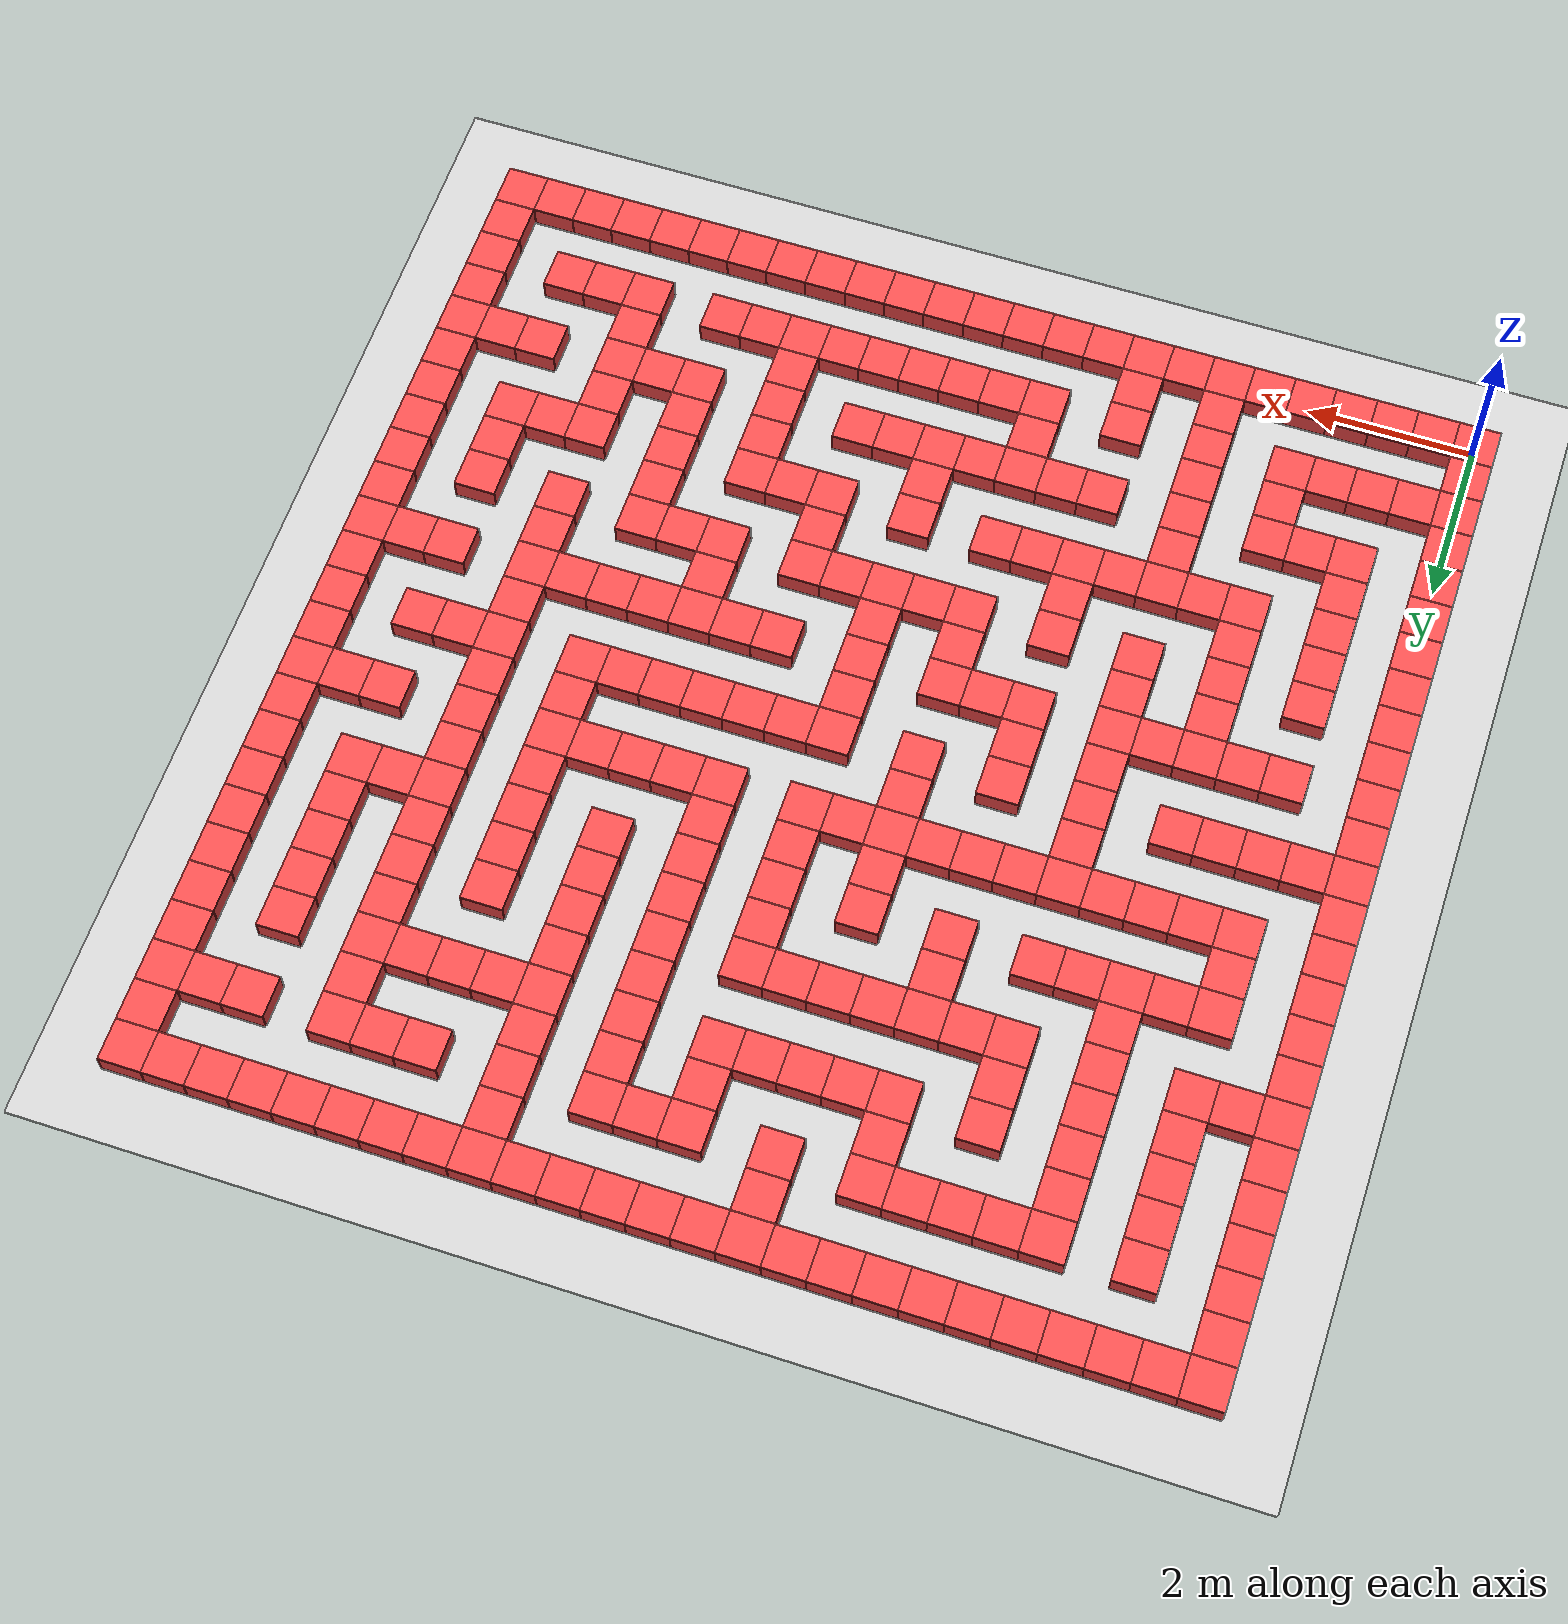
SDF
<sdf version='1.6'>
	<world name='default'>
		<scene>
			<ambient>0.4 0.4 0.4 1</ambient>
			<background>0.7 0.7 0.7 1</background>
			<shadows>1</shadows>
		</scene>
		<light type='directional' name='sun'>
			<cast_shadows>1</cast_shadows>
			<pose frame=''>0 0 10 0 0 0</pose>
			<diffuse>0.8 0.8 0.8 1</diffuse>
			<specular>0.1 0.1 0.1 1</specular>
			<direction>-0.5 0.5 -1</direction>
		</light>
		<gui fullscreen='0'>
			<camera name='user_camera'>
				<pose frame=''>0.027731 -6.7828 1.07118 0 0.016872 1.50135</pose>
				<view_controller>orbit</view_controller>
				<projection_type>perspective</projection_type>
			</camera>
		</gui>
		<model name='ground_plane'>
			<static>1</static>
			<link name='link'>
				<collision name='collision'>
					<geometry>
						<plane>
							<normal>0 0 1</normal>
							<size>100 100</size>
						</plane>
					</geometry>
					<surface>
						<friction>
							<ode>
								<mu>100</mu>
								<mu2>50</mu2>
							</ode>
							<torsional>
								<ode/>
							</torsional>
						</friction>
						<contact>
							<ode/>
						</contact>
						<bounce/>
					</surface>
					<max_contacts>10</max_contacts>
				</collision>
				<visual name='visual'>
					<cast_shadows>0</cast_shadows>
					<geometry>
						<plane>
							<normal>0 0 1</normal>
							<size>100 100</size>
						</plane>
					</geometry>
					<material>
						<script>
							<uri>file://media/materials/scripts/gazebo.material</uri>
							<name>Gazebo/Grey</name>
						</script>
					</material>
				</visual>
			</link>
		</model>
		<physics type='ode' default='0' name='default_physics'>
			<max_step_size>0.001</max_step_size>
			<real_time_factor>1</real_time_factor>
			<real_time_update_rate>1000</real_time_update_rate>
		</physics>
		<gravity>0 0 -9.8</gravity>
		<magnetic_field>6e-06 2.3e-05 -4.2e-05</magnetic_field>
		<atmosphere type='adiabatic'/>
		<spherical_coordinates>
			<surface_model>EARTH_WGS84</surface_model>
			<latitude_deg>0</latitude_deg>
			<longitude_deg>0</longitude_deg>
			<elevation>0</elevation>
			<heading_deg>0</heading_deg>
		</spherical_coordinates>
		<model name='Box_Red_0'>
			<link name='link_0'>
				<pose frame=''>0 0 0 0 -0 0</pose>
				<inertial>
					<mass>1</mass>
					<inertia>
						<ixx>0.166667</ixx>
						<ixy>0</ixy>
						<ixz>0</ixz>
						<iyy>0.166667</iyy>
						<iyz>0</iyz>
						<izz>0.166667</izz>
					</inertia>
					<pose frame=''>0 0 0 0 -0 0</pose>
				</inertial>
				<self_collide>0</self_collide>
				<kinematic>0</kinematic>
				<gravity>1</gravity>
				<visual name='visual'>
					<pose frame=''>0 0 0 0 -0 0</pose>
					<geometry>
						<box>
							<size>0.5 0.5 0.5</size>
						</box>
					</geometry>
					<material>
						<lighting>1</lighting>
						<script>
							<uri>file://media/materials/scripts/gazebo.material</uri>
							<name>Gazebo/Grey</name>
						</script>
						<ambient>1 0.3 0.3 1</ambient>
						<diffuse>0.7 0.7 0.7 1</diffuse>
						<specular>0.01 0.01 0.01 1</specular>
						<emissive>0 0 0 1</emissive>
						<shader type='vertex'>
							<normal_map>__default__</normal_map>
						</shader>
					</material>
					<transparency>0</transparency>
					<cast_shadows>1</cast_shadows>
				</visual>
				<collision name='collision'>
					<laser_retro>0</laser_retro>
					<max_contacts>10</max_contacts>
					<pose frame=''>0 0 0 0 -0 0</pose>
					<geometry>
						<box>
							<size>0.5 0.5 0.5</size>
						</box>
					</geometry>
					<surface>
						<friction>
							<ode>
								<mu>1</mu>
								<mu2>1</mu2>
								<fdir1>0 0 0</fdir1>
								<slip1>0</slip1>
								<slip2>0</slip2>
							</ode>
							<torsional>
								<coefficient>1</coefficient>
								<patch_radius>0</patch_radius>
								<surface_radius>0</surface_radius>
								<use_patch_radius>1</use_patch_radius>
								<ode>
									<slip>0</slip>
								</ode>
							</torsional>
						</friction>
						<bounce>
							<restitution_coefficient>0</restitution_coefficient>
							<threshold>1e+06</threshold>
						</bounce>
						<contact>
							<collide_without_contact>0</collide_without_contact>
							<collide_without_contact_bitmask>1</collide_without_contact_bitmask>
							<collide_bitmask>1</collide_bitmask>
							<ode>
								<soft_cfm>0</soft_cfm>
								<soft_erp>0.2</soft_erp>
								<kp>1e+13</kp>
								<kd>1</kd>
								<max_vel>0.01</max_vel>
								<min_depth>0</min_depth>
							</ode>
							<bullet>
								<split_impulse>1</split_impulse>
								<split_impulse_penetration_threshold>-0.01</split_impulse_penetration_threshold>
								<soft_cfm>0</soft_cfm>
								<soft_erp>0.2</soft_erp>
								<kp>1e+13</kp>
								<kd>1</kd>
							</bullet>
						</contact>
					</surface>
				</collision>
				<enable_wind>0</enable_wind>
			</link>
			<static>0</static>
			<allow_auto_disable>1</allow_auto_disable>
			<pose frame=''>0.000 0.000 0.000 0 0 0</pose>
		</model>
		<model name='Box_Red_1'>
			<link name='link_0'>
				<pose frame=''>0 0 0 0 -0 0</pose>
				<inertial>
					<mass>1</mass>
					<inertia>
						<ixx>0.166667</ixx>
						<ixy>0</ixy>
						<ixz>0</ixz>
						<iyy>0.166667</iyy>
						<iyz>0</iyz>
						<izz>0.166667</izz>
					</inertia>
					<pose frame=''>0 0 0 0 -0 0</pose>
				</inertial>
				<self_collide>0</self_collide>
				<kinematic>0</kinematic>
				<gravity>1</gravity>
				<visual name='visual'>
					<pose frame=''>0 0 0 0 -0 0</pose>
					<geometry>
						<box>
							<size>0.5 0.5 0.5</size>
						</box>
					</geometry>
					<material>
						<lighting>1</lighting>
						<script>
							<uri>file://media/materials/scripts/gazebo.material</uri>
							<name>Gazebo/Grey</name>
						</script>
						<ambient>1 0.3 0.3 1</ambient>
						<diffuse>0.7 0.7 0.7 1</diffuse>
						<specular>0.01 0.01 0.01 1</specular>
						<emissive>0 0 0 1</emissive>
						<shader type='vertex'>
							<normal_map>__default__</normal_map>
						</shader>
					</material>
					<transparency>0</transparency>
					<cast_shadows>1</cast_shadows>
				</visual>
				<collision name='collision'>
					<laser_retro>0</laser_retro>
					<max_contacts>10</max_contacts>
					<pose frame=''>0 0 0 0 -0 0</pose>
					<geometry>
						<box>
							<size>0.5 0.5 0.5</size>
						</box>
					</geometry>
					<surface>
						<friction>
							<ode>
								<mu>1</mu>
								<mu2>1</mu2>
								<fdir1>0 0 0</fdir1>
								<slip1>0</slip1>
								<slip2>0</slip2>
							</ode>
							<torsional>
								<coefficient>1</coefficient>
								<patch_radius>0</patch_radius>
								<surface_radius>0</surface_radius>
								<use_patch_radius>1</use_patch_radius>
								<ode>
									<slip>0</slip>
								</ode>
							</torsional>
						</friction>
						<bounce>
							<restitution_coefficient>0</restitution_coefficient>
							<threshold>1e+06</threshold>
						</bounce>
						<contact>
							<collide_without_contact>0</collide_without_contact>
							<collide_without_contact_bitmask>1</collide_without_contact_bitmask>
							<collide_bitmask>1</collide_bitmask>
							<ode>
								<soft_cfm>0</soft_cfm>
								<soft_erp>0.2</soft_erp>
								<kp>1e+13</kp>
								<kd>1</kd>
								<max_vel>0.01</max_vel>
								<min_depth>0</min_depth>
							</ode>
							<bullet>
								<split_impulse>1</split_impulse>
								<split_impulse_penetration_threshold>-0.01</split_impulse_penetration_threshold>
								<soft_cfm>0</soft_cfm>
								<soft_erp>0.2</soft_erp>
								<kp>1e+13</kp>
								<kd>1</kd>
							</bullet>
						</contact>
					</surface>
				</collision>
				<enable_wind>0</enable_wind>
			</link>
			<static>0</static>
			<allow_auto_disable>1</allow_auto_disable>
			<pose frame=''>0.000 0.500 0.000 0 0 0</pose>
		</model>
		<model name='Box_Red_2'>
			<link name='link_0'>
				<pose frame=''>0 0 0 0 -0 0</pose>
				<inertial>
					<mass>1</mass>
					<inertia>
						<ixx>0.166667</ixx>
						<ixy>0</ixy>
						<ixz>0</ixz>
						<iyy>0.166667</iyy>
						<iyz>0</iyz>
						<izz>0.166667</izz>
					</inertia>
					<pose frame=''>0 0 0 0 -0 0</pose>
				</inertial>
				<self_collide>0</self_collide>
				<kinematic>0</kinematic>
				<gravity>1</gravity>
				<visual name='visual'>
					<pose frame=''>0 0 0 0 -0 0</pose>
					<geometry>
						<box>
							<size>0.5 0.5 0.5</size>
						</box>
					</geometry>
					<material>
						<lighting>1</lighting>
						<script>
							<uri>file://media/materials/scripts/gazebo.material</uri>
							<name>Gazebo/Grey</name>
						</script>
						<ambient>1 0.3 0.3 1</ambient>
						<diffuse>0.7 0.7 0.7 1</diffuse>
						<specular>0.01 0.01 0.01 1</specular>
						<emissive>0 0 0 1</emissive>
						<shader type='vertex'>
							<normal_map>__default__</normal_map>
						</shader>
					</material>
					<transparency>0</transparency>
					<cast_shadows>1</cast_shadows>
				</visual>
				<collision name='collision'>
					<laser_retro>0</laser_retro>
					<max_contacts>10</max_contacts>
					<pose frame=''>0 0 0 0 -0 0</pose>
					<geometry>
						<box>
							<size>0.5 0.5 0.5</size>
						</box>
					</geometry>
					<surface>
						<friction>
							<ode>
								<mu>1</mu>
								<mu2>1</mu2>
								<fdir1>0 0 0</fdir1>
								<slip1>0</slip1>
								<slip2>0</slip2>
							</ode>
							<torsional>
								<coefficient>1</coefficient>
								<patch_radius>0</patch_radius>
								<surface_radius>0</surface_radius>
								<use_patch_radius>1</use_patch_radius>
								<ode>
									<slip>0</slip>
								</ode>
							</torsional>
						</friction>
						<bounce>
							<restitution_coefficient>0</restitution_coefficient>
							<threshold>1e+06</threshold>
						</bounce>
						<contact>
							<collide_without_contact>0</collide_without_contact>
							<collide_without_contact_bitmask>1</collide_without_contact_bitmask>
							<collide_bitmask>1</collide_bitmask>
							<ode>
								<soft_cfm>0</soft_cfm>
								<soft_erp>0.2</soft_erp>
								<kp>1e+13</kp>
								<kd>1</kd>
								<max_vel>0.01</max_vel>
								<min_depth>0</min_depth>
							</ode>
							<bullet>
								<split_impulse>1</split_impulse>
								<split_impulse_penetration_threshold>-0.01</split_impulse_penetration_threshold>
								<soft_cfm>0</soft_cfm>
								<soft_erp>0.2</soft_erp>
								<kp>1e+13</kp>
								<kd>1</kd>
							</bullet>
						</contact>
					</surface>
				</collision>
				<enable_wind>0</enable_wind>
			</link>
			<static>0</static>
			<allow_auto_disable>1</allow_auto_disable>
			<pose frame=''>0.000 1.000 0.000 0 0 0</pose>
		</model>
		<model name='Box_Red_3'>
			<link name='link_0'>
				<pose frame=''>0 0 0 0 -0 0</pose>
				<inertial>
					<mass>1</mass>
					<inertia>
						<ixx>0.166667</ixx>
						<ixy>0</ixy>
						<ixz>0</ixz>
						<iyy>0.166667</iyy>
						<iyz>0</iyz>
						<izz>0.166667</izz>
					</inertia>
					<pose frame=''>0 0 0 0 -0 0</pose>
				</inertial>
				<self_collide>0</self_collide>
				<kinematic>0</kinematic>
				<gravity>1</gravity>
				<visual name='visual'>
					<pose frame=''>0 0 0 0 -0 0</pose>
					<geometry>
						<box>
							<size>0.5 0.5 0.5</size>
						</box>
					</geometry>
					<material>
						<lighting>1</lighting>
						<script>
							<uri>file://media/materials/scripts/gazebo.material</uri>
							<name>Gazebo/Grey</name>
						</script>
						<ambient>1 0.3 0.3 1</ambient>
						<diffuse>0.7 0.7 0.7 1</diffuse>
						<specular>0.01 0.01 0.01 1</specular>
						<emissive>0 0 0 1</emissive>
						<shader type='vertex'>
							<normal_map>__default__</normal_map>
						</shader>
					</material>
					<transparency>0</transparency>
					<cast_shadows>1</cast_shadows>
				</visual>
				<collision name='collision'>
					<laser_retro>0</laser_retro>
					<max_contacts>10</max_contacts>
					<pose frame=''>0 0 0 0 -0 0</pose>
					<geometry>
						<box>
							<size>0.5 0.5 0.5</size>
						</box>
					</geometry>
					<surface>
						<friction>
							<ode>
								<mu>1</mu>
								<mu2>1</mu2>
								<fdir1>0 0 0</fdir1>
								<slip1>0</slip1>
								<slip2>0</slip2>
							</ode>
							<torsional>
								<coefficient>1</coefficient>
								<patch_radius>0</patch_radius>
								<surface_radius>0</surface_radius>
								<use_patch_radius>1</use_patch_radius>
								<ode>
									<slip>0</slip>
								</ode>
							</torsional>
						</friction>
						<bounce>
							<restitution_coefficient>0</restitution_coefficient>
							<threshold>1e+06</threshold>
						</bounce>
						<contact>
							<collide_without_contact>0</collide_without_contact>
							<collide_without_contact_bitmask>1</collide_without_contact_bitmask>
							<collide_bitmask>1</collide_bitmask>
							<ode>
								<soft_cfm>0</soft_cfm>
								<soft_erp>0.2</soft_erp>
								<kp>1e+13</kp>
								<kd>1</kd>
								<max_vel>0.01</max_vel>
								<min_depth>0</min_depth>
							</ode>
							<bullet>
								<split_impulse>1</split_impulse>
								<split_impulse_penetration_threshold>-0.01</split_impulse_penetration_threshold>
								<soft_cfm>0</soft_cfm>
								<soft_erp>0.2</soft_erp>
								<kp>1e+13</kp>
								<kd>1</kd>
							</bullet>
						</contact>
					</surface>
				</collision>
				<enable_wind>0</enable_wind>
			</link>
			<static>0</static>
			<allow_auto_disable>1</allow_auto_disable>
			<pose frame=''>0.000 1.500 0.000 0 0 0</pose>
		</model>
		<model name='Box_Red_4'>
			<link name='link_0'>
				<pose frame=''>0 0 0 0 -0 0</pose>
				<inertial>
					<mass>1</mass>
					<inertia>
						<ixx>0.166667</ixx>
						<ixy>0</ixy>
						<ixz>0</ixz>
						<iyy>0.166667</iyy>
						<iyz>0</iyz>
						<izz>0.166667</izz>
					</inertia>
					<pose frame=''>0 0 0 0 -0 0</pose>
				</inertial>
				<self_collide>0</self_collide>
				<kinematic>0</kinematic>
				<gravity>1</gravity>
				<visual name='visual'>
					<pose frame=''>0 0 0 0 -0 0</pose>
					<geometry>
						<box>
							<size>0.5 0.5 0.5</size>
						</box>
					</geometry>
					<material>
						<lighting>1</lighting>
						<script>
							<uri>file://media/materials/scripts/gazebo.material</uri>
							<name>Gazebo/Grey</name>
						</script>
						<ambient>1 0.3 0.3 1</ambient>
						<diffuse>0.7 0.7 0.7 1</diffuse>
						<specular>0.01 0.01 0.01 1</specular>
						<emissive>0 0 0 1</emissive>
						<shader type='vertex'>
							<normal_map>__default__</normal_map>
						</shader>
					</material>
					<transparency>0</transparency>
					<cast_shadows>1</cast_shadows>
				</visual>
				<collision name='collision'>
					<laser_retro>0</laser_retro>
					<max_contacts>10</max_contacts>
					<pose frame=''>0 0 0 0 -0 0</pose>
					<geometry>
						<box>
							<size>0.5 0.5 0.5</size>
						</box>
					</geometry>
					<surface>
						<friction>
							<ode>
								<mu>1</mu>
								<mu2>1</mu2>
								<fdir1>0 0 0</fdir1>
								<slip1>0</slip1>
								<slip2>0</slip2>
							</ode>
							<torsional>
								<coefficient>1</coefficient>
								<patch_radius>0</patch_radius>
								<surface_radius>0</surface_radius>
								<use_patch_radius>1</use_patch_radius>
								<ode>
									<slip>0</slip>
								</ode>
							</torsional>
						</friction>
						<bounce>
							<restitution_coefficient>0</restitution_coefficient>
							<threshold>1e+06</threshold>
						</bounce>
						<contact>
							<collide_without_contact>0</collide_without_contact>
							<collide_without_contact_bitmask>1</collide_without_contact_bitmask>
							<collide_bitmask>1</collide_bitmask>
							<ode>
								<soft_cfm>0</soft_cfm>
								<soft_erp>0.2</soft_erp>
								<kp>1e+13</kp>
								<kd>1</kd>
								<max_vel>0.01</max_vel>
								<min_depth>0</min_depth>
							</ode>
							<bullet>
								<split_impulse>1</split_impulse>
								<split_impulse_penetration_threshold>-0.01</split_impulse_penetration_threshold>
								<soft_cfm>0</soft_cfm>
								<soft_erp>0.2</soft_erp>
								<kp>1e+13</kp>
								<kd>1</kd>
							</bullet>
						</contact>
					</surface>
				</collision>
				<enable_wind>0</enable_wind>
			</link>
			<static>0</static>
			<allow_auto_disable>1</allow_auto_disable>
			<pose frame=''>0.000 2.000 0.000 0 0 0</pose>
		</model>
		<model name='Box_Red_5'>
			<link name='link_0'>
				<pose frame=''>0 0 0 0 -0 0</pose>
				<inertial>
					<mass>1</mass>
					<inertia>
						<ixx>0.166667</ixx>
						<ixy>0</ixy>
						<ixz>0</ixz>
						<iyy>0.166667</iyy>
						<iyz>0</iyz>
						<izz>0.166667</izz>
					</inertia>
					<pose frame=''>0 0 0 0 -0 0</pose>
				</inertial>
				<self_collide>0</self_collide>
				<kinematic>0</kinematic>
				<gravity>1</gravity>
				<visual name='visual'>
					<pose frame=''>0 0 0 0 -0 0</pose>
					<geometry>
						<box>
							<size>0.5 0.5 0.5</size>
						</box>
					</geometry>
					<material>
						<lighting>1</lighting>
						<script>
							<uri>file://media/materials/scripts/gazebo.material</uri>
							<name>Gazebo/Grey</name>
						</script>
						<ambient>1 0.3 0.3 1</ambient>
						<diffuse>0.7 0.7 0.7 1</diffuse>
						<specular>0.01 0.01 0.01 1</specular>
						<emissive>0 0 0 1</emissive>
						<shader type='vertex'>
							<normal_map>__default__</normal_map>
						</shader>
					</material>
					<transparency>0</transparency>
					<cast_shadows>1</cast_shadows>
				</visual>
				<collision name='collision'>
					<laser_retro>0</laser_retro>
					<max_contacts>10</max_contacts>
					<pose frame=''>0 0 0 0 -0 0</pose>
					<geometry>
						<box>
							<size>0.5 0.5 0.5</size>
						</box>
					</geometry>
					<surface>
						<friction>
							<ode>
								<mu>1</mu>
								<mu2>1</mu2>
								<fdir1>0 0 0</fdir1>
								<slip1>0</slip1>
								<slip2>0</slip2>
							</ode>
							<torsional>
								<coefficient>1</coefficient>
								<patch_radius>0</patch_radius>
								<surface_radius>0</surface_radius>
								<use_patch_radius>1</use_patch_radius>
								<ode>
									<slip>0</slip>
								</ode>
							</torsional>
						</friction>
						<bounce>
							<restitution_coefficient>0</restitution_coefficient>
							<threshold>1e+06</threshold>
						</bounce>
						<contact>
							<collide_without_contact>0</collide_without_contact>
							<collide_without_contact_bitmask>1</collide_without_contact_bitmask>
							<collide_bitmask>1</collide_bitmask>
							<ode>
								<soft_cfm>0</soft_cfm>
								<soft_erp>0.2</soft_erp>
								<kp>1e+13</kp>
								<kd>1</kd>
								<max_vel>0.01</max_vel>
								<min_depth>0</min_depth>
							</ode>
							<bullet>
								<split_impulse>1</split_impulse>
								<split_impulse_penetration_threshold>-0.01</split_impulse_penetration_threshold>
								<soft_cfm>0</soft_cfm>
								<soft_erp>0.2</soft_erp>
								<kp>1e+13</kp>
								<kd>1</kd>
							</bullet>
						</contact>
					</surface>
				</collision>
				<enable_wind>0</enable_wind>
			</link>
			<static>0</static>
			<allow_auto_disable>1</allow_auto_disable>
			<pose frame=''>0.000 2.500 0.000 0 0 0</pose>
		</model>
		<model name='Box_Red_6'>
			<link name='link_0'>
				<pose frame=''>0 0 0 0 -0 0</pose>
				<inertial>
					<mass>1</mass>
					<inertia>
						<ixx>0.166667</ixx>
						<ixy>0</ixy>
						<ixz>0</ixz>
						<iyy>0.166667</iyy>
						<iyz>0</iyz>
						<izz>0.166667</izz>
					</inertia>
					<pose frame=''>0 0 0 0 -0 0</pose>
				</inertial>
				<self_collide>0</self_collide>
				<kinematic>0</kinematic>
				<gravity>1</gravity>
				<visual name='visual'>
					<pose frame=''>0 0 0 0 -0 0</pose>
					<geometry>
						<box>
							<size>0.5 0.5 0.5</size>
						</box>
					</geometry>
					<material>
						<lighting>1</lighting>
						<script>
							<uri>file://media/materials/scripts/gazebo.material</uri>
							<name>Gazebo/Grey</name>
						</script>
						<ambient>1 0.3 0.3 1</ambient>
						<diffuse>0.7 0.7 0.7 1</diffuse>
						<specular>0.01 0.01 0.01 1</specular>
						<emissive>0 0 0 1</emissive>
						<shader type='vertex'>
							<normal_map>__default__</normal_map>
						</shader>
					</material>
					<transparency>0</transparency>
					<cast_shadows>1</cast_shadows>
				</visual>
				<collision name='collision'>
					<laser_retro>0</laser_retro>
					<max_contacts>10</max_contacts>
					<pose frame=''>0 0 0 0 -0 0</pose>
					<geometry>
						<box>
							<size>0.5 0.5 0.5</size>
						</box>
					</geometry>
					<surface>
						<friction>
							<ode>
								<mu>1</mu>
								<mu2>1</mu2>
								<fdir1>0 0 0</fdir1>
								<slip1>0</slip1>
								<slip2>0</slip2>
							</ode>
							<torsional>
								<coefficient>1</coefficient>
								<patch_radius>0</patch_radius>
								<surface_radius>0</surface_radius>
								<use_patch_radius>1</use_patch_radius>
								<ode>
									<slip>0</slip>
								</ode>
							</torsional>
						</friction>
						<bounce>
							<restitution_coefficient>0</restitution_coefficient>
							<threshold>1e+06</threshold>
						</bounce>
						<contact>
							<collide_without_contact>0</collide_without_contact>
							<collide_without_contact_bitmask>1</collide_without_contact_bitmask>
							<collide_bitmask>1</collide_bitmask>
							<ode>
								<soft_cfm>0</soft_cfm>
								<soft_erp>0.2</soft_erp>
								<kp>1e+13</kp>
								<kd>1</kd>
								<max_vel>0.01</max_vel>
								<min_depth>0</min_depth>
							</ode>
							<bullet>
								<split_impulse>1</split_impulse>
								<split_impulse_penetration_threshold>-0.01</split_impulse_penetration_threshold>
								<soft_cfm>0</soft_cfm>
								<soft_erp>0.2</soft_erp>
								<kp>1e+13</kp>
								<kd>1</kd>
							</bullet>
						</contact>
					</surface>
				</collision>
				<enable_wind>0</enable_wind>
			</link>
			<static>0</static>
			<allow_auto_disable>1</allow_auto_disable>
			<pose frame=''>0.000 3.000 0.000 0 0 0</pose>
		</model>
		<model name='Box_Red_7'>
			<link name='link_0'>
				<pose frame=''>0 0 0 0 -0 0</pose>
				<inertial>
					<mass>1</mass>
					<inertia>
						<ixx>0.166667</ixx>
						<ixy>0</ixy>
						<ixz>0</ixz>
						<iyy>0.166667</iyy>
						<iyz>0</iyz>
						<izz>0.166667</izz>
					</inertia>
					<pose frame=''>0 0 0 0 -0 0</pose>
				</inertial>
				<self_collide>0</self_collide>
				<kinematic>0</kinematic>
				<gravity>1</gravity>
				<visual name='visual'>
					<pose frame=''>0 0 0 0 -0 0</pose>
					<geometry>
						<box>
							<size>0.5 0.5 0.5</size>
						</box>
					</geometry>
					<material>
						<lighting>1</lighting>
						<script>
							<uri>file://media/materials/scripts/gazebo.material</uri>
							<name>Gazebo/Grey</name>
						</script>
						<ambient>1 0.3 0.3 1</ambient>
						<diffuse>0.7 0.7 0.7 1</diffuse>
						<specular>0.01 0.01 0.01 1</specular>
						<emissive>0 0 0 1</emissive>
						<shader type='vertex'>
							<normal_map>__default__</normal_map>
						</shader>
					</material>
					<transparency>0</transparency>
					<cast_shadows>1</cast_shadows>
				</visual>
				<collision name='collision'>
					<laser_retro>0</laser_retro>
					<max_contacts>10</max_contacts>
					<pose frame=''>0 0 0 0 -0 0</pose>
					<geometry>
						<box>
							<size>0.5 0.5 0.5</size>
						</box>
					</geometry>
					<surface>
						<friction>
							<ode>
								<mu>1</mu>
								<mu2>1</mu2>
								<fdir1>0 0 0</fdir1>
								<slip1>0</slip1>
								<slip2>0</slip2>
							</ode>
							<torsional>
								<coefficient>1</coefficient>
								<patch_radius>0</patch_radius>
								<surface_radius>0</surface_radius>
								<use_patch_radius>1</use_patch_radius>
								<ode>
									<slip>0</slip>
								</ode>
							</torsional>
						</friction>
						<bounce>
							<restitution_coefficient>0</restitution_coefficient>
							<threshold>1e+06</threshold>
						</bounce>
						<contact>
							<collide_without_contact>0</collide_without_contact>
							<collide_without_contact_bitmask>1</collide_without_contact_bitmask>
							<collide_bitmask>1</collide_bitmask>
							<ode>
								<soft_cfm>0</soft_cfm>
								<soft_erp>0.2</soft_erp>
								<kp>1e+13</kp>
								<kd>1</kd>
								<max_vel>0.01</max_vel>
								<min_depth>0</min_depth>
							</ode>
							<bullet>
								<split_impulse>1</split_impulse>
								<split_impulse_penetration_threshold>-0.01</split_impulse_penetration_threshold>
								<soft_cfm>0</soft_cfm>
								<soft_erp>0.2</soft_erp>
								<kp>1e+13</kp>
								<kd>1</kd>
							</bullet>
						</contact>
					</surface>
				</collision>
				<enable_wind>0</enable_wind>
			</link>
			<static>0</static>
			<allow_auto_disable>1</allow_auto_disable>
			<pose frame=''>0.000 3.500 0.000 0 0 0</pose>
		</model>
		<model name='Box_Red_8'>
			<link name='link_0'>
				<pose frame=''>0 0 0 0 -0 0</pose>
				<inertial>
					<mass>1</mass>
					<inertia>
						<ixx>0.166667</ixx>
						<ixy>0</ixy>
						<ixz>0</ixz>
						<iyy>0.166667</iyy>
						<iyz>0</iyz>
						<izz>0.166667</izz>
					</inertia>
					<pose frame=''>0 0 0 0 -0 0</pose>
				</inertial>
				<self_collide>0</self_collide>
				<kinematic>0</kinematic>
				<gravity>1</gravity>
				<visual name='visual'>
					<pose frame=''>0 0 0 0 -0 0</pose>
					<geometry>
						<box>
							<size>0.5 0.5 0.5</size>
						</box>
					</geometry>
					<material>
						<lighting>1</lighting>
						<script>
							<uri>file://media/materials/scripts/gazebo.material</uri>
							<name>Gazebo/Grey</name>
						</script>
						<ambient>1 0.3 0.3 1</ambient>
						<diffuse>0.7 0.7 0.7 1</diffuse>
						<specular>0.01 0.01 0.01 1</specular>
						<emissive>0 0 0 1</emissive>
						<shader type='vertex'>
							<normal_map>__default__</normal_map>
						</shader>
					</material>
					<transparency>0</transparency>
					<cast_shadows>1</cast_shadows>
				</visual>
				<collision name='collision'>
					<laser_retro>0</laser_retro>
					<max_contacts>10</max_contacts>
					<pose frame=''>0 0 0 0 -0 0</pose>
					<geometry>
						<box>
							<size>0.5 0.5 0.5</size>
						</box>
					</geometry>
					<surface>
						<friction>
							<ode>
								<mu>1</mu>
								<mu2>1</mu2>
								<fdir1>0 0 0</fdir1>
								<slip1>0</slip1>
								<slip2>0</slip2>
							</ode>
							<torsional>
								<coefficient>1</coefficient>
								<patch_radius>0</patch_radius>
								<surface_radius>0</surface_radius>
								<use_patch_radius>1</use_patch_radius>
								<ode>
									<slip>0</slip>
								</ode>
							</torsional>
						</friction>
						<bounce>
							<restitution_coefficient>0</restitution_coefficient>
							<threshold>1e+06</threshold>
						</bounce>
						<contact>
							<collide_without_contact>0</collide_without_contact>
							<collide_without_contact_bitmask>1</collide_without_contact_bitmask>
							<collide_bitmask>1</collide_bitmask>
							<ode>
								<soft_cfm>0</soft_cfm>
								<soft_erp>0.2</soft_erp>
								<kp>1e+13</kp>
								<kd>1</kd>
								<max_vel>0.01</max_vel>
								<min_depth>0</min_depth>
							</ode>
							<bullet>
								<split_impulse>1</split_impulse>
								<split_impulse_penetration_threshold>-0.01</split_impulse_penetration_threshold>
								<soft_cfm>0</soft_cfm>
								<soft_erp>0.2</soft_erp>
								<kp>1e+13</kp>
								<kd>1</kd>
							</bullet>
						</contact>
					</surface>
				</collision>
				<enable_wind>0</enable_wind>
			</link>
			<static>0</static>
			<allow_auto_disable>1</allow_auto_disable>
			<pose frame=''>0.000 4.000 0.000 0 0 0</pose>
		</model>
		<model name='Box_Red_9'>
			<link name='link_0'>
				<pose frame=''>0 0 0 0 -0 0</pose>
				<inertial>
					<mass>1</mass>
					<inertia>
						<ixx>0.166667</ixx>
						<ixy>0</ixy>
						<ixz>0</ixz>
						<iyy>0.166667</iyy>
						<iyz>0</iyz>
						<izz>0.166667</izz>
					</inertia>
					<pose frame=''>0 0 0 0 -0 0</pose>
				</inertial>
				<self_collide>0</self_collide>
				<kinematic>0</kinematic>
				<gravity>1</gravity>
				<visual name='visual'>
					<pose frame=''>0 0 0 0 -0 0</pose>
					<geometry>
						<box>
							<size>0.5 0.5 0.5</size>
						</box>
					</geometry>
					<material>
						<lighting>1</lighting>
						<script>
							<uri>file://media/materials/scripts/gazebo.material</uri>
							<name>Gazebo/Grey</name>
						</script>
						<ambient>1 0.3 0.3 1</ambient>
						<diffuse>0.7 0.7 0.7 1</diffuse>
						<specular>0.01 0.01 0.01 1</specular>
						<emissive>0 0 0 1</emissive>
						<shader type='vertex'>
							<normal_map>__default__</normal_map>
						</shader>
					</material>
					<transparency>0</transparency>
					<cast_shadows>1</cast_shadows>
				</visual>
				<collision name='collision'>
					<laser_retro>0</laser_retro>
					<max_contacts>10</max_contacts>
					<pose frame=''>0 0 0 0 -0 0</pose>
					<geometry>
						<box>
							<size>0.5 0.5 0.5</size>
						</box>
					</geometry>
					<surface>
						<friction>
							<ode>
								<mu>1</mu>
								<mu2>1</mu2>
								<fdir1>0 0 0</fdir1>
								<slip1>0</slip1>
								<slip2>0</slip2>
							</ode>
							<torsional>
								<coefficient>1</coefficient>
								<patch_radius>0</patch_radius>
								<surface_radius>0</surface_radius>
								<use_patch_radius>1</use_patch_radius>
								<ode>
									<slip>0</slip>
								</ode>
							</torsional>
						</friction>
						<bounce>
							<restitution_coefficient>0</restitution_coefficient>
							<threshold>1e+06</threshold>
						</bounce>
						<contact>
							<collide_without_contact>0</collide_without_contact>
							<collide_without_contact_bitmask>1</collide_without_contact_bitmask>
							<collide_bitmask>1</collide_bitmask>
							<ode>
								<soft_cfm>0</soft_cfm>
								<soft_erp>0.2</soft_erp>
								<kp>1e+13</kp>
								<kd>1</kd>
								<max_vel>0.01</max_vel>
								<min_depth>0</min_depth>
							</ode>
							<bullet>
								<split_impulse>1</split_impulse>
								<split_impulse_penetration_threshold>-0.01</split_impulse_penetration_threshold>
								<soft_cfm>0</soft_cfm>
								<soft_erp>0.2</soft_erp>
								<kp>1e+13</kp>
								<kd>1</kd>
							</bullet>
						</contact>
					</surface>
				</collision>
				<enable_wind>0</enable_wind>
			</link>
			<static>0</static>
			<allow_auto_disable>1</allow_auto_disable>
			<pose frame=''>0.000 4.500 0.000 0 0 0</pose>
		</model>
		<model name='Box_Red_10'>
			<link name='link_0'>
				<pose frame=''>0 0 0 0 -0 0</pose>
				<inertial>
					<mass>1</mass>
					<inertia>
						<ixx>0.166667</ixx>
						<ixy>0</ixy>
						<ixz>0</ixz>
						<iyy>0.166667</iyy>
						<iyz>0</iyz>
						<izz>0.166667</izz>
					</inertia>
					<pose frame=''>0 0 0 0 -0 0</pose>
				</inertial>
				<self_collide>0</self_collide>
				<kinematic>0</kinematic>
				<gravity>1</gravity>
				<visual name='visual'>
					<pose frame=''>0 0 0 0 -0 0</pose>
					<geometry>
						<box>
							<size>0.5 0.5 0.5</size>
						</box>
					</geometry>
					<material>
						<lighting>1</lighting>
						<script>
							<uri>file://media/materials/scripts/gazebo.material</uri>
							<name>Gazebo/Grey</name>
						</script>
						<ambient>1 0.3 0.3 1</ambient>
						<diffuse>0.7 0.7 0.7 1</diffuse>
						<specular>0.01 0.01 0.01 1</specular>
						<emissive>0 0 0 1</emissive>
						<shader type='vertex'>
							<normal_map>__default__</normal_map>
						</shader>
					</material>
					<transparency>0</transparency>
					<cast_shadows>1</cast_shadows>
				</visual>
				<collision name='collision'>
					<laser_retro>0</laser_retro>
					<max_contacts>10</max_contacts>
					<pose frame=''>0 0 0 0 -0 0</pose>
					<geometry>
						<box>
							<size>0.5 0.5 0.5</size>
						</box>
					</geometry>
					<surface>
						<friction>
							<ode>
								<mu>1</mu>
								<mu2>1</mu2>
								<fdir1>0 0 0</fdir1>
								<slip1>0</slip1>
								<slip2>0</slip2>
							</ode>
							<torsional>
								<coefficient>1</coefficient>
								<patch_radius>0</patch_radius>
								<surface_radius>0</surface_radius>
								<use_patch_radius>1</use_patch_radius>
								<ode>
									<slip>0</slip>
								</ode>
							</torsional>
						</friction>
						<bounce>
							<restitution_coefficient>0</restitution_coefficient>
							<threshold>1e+06</threshold>
						</bounce>
						<contact>
							<collide_without_contact>0</collide_without_contact>
							<collide_without_contact_bitmask>1</collide_without_contact_bitmask>
							<collide_bitmask>1</collide_bitmask>
							<ode>
								<soft_cfm>0</soft_cfm>
								<soft_erp>0.2</soft_erp>
								<kp>1e+13</kp>
								<kd>1</kd>
								<max_vel>0.01</max_vel>
								<min_depth>0</min_depth>
							</ode>
							<bullet>
								<split_impulse>1</split_impulse>
								<split_impulse_penetration_threshold>-0.01</split_impulse_penetration_threshold>
								<soft_cfm>0</soft_cfm>
								<soft_erp>0.2</soft_erp>
								<kp>1e+13</kp>
								<kd>1</kd>
							</bullet>
						</contact>
					</surface>
				</collision>
				<enable_wind>0</enable_wind>
			</link>
			<static>0</static>
			<allow_auto_disable>1</allow_auto_disable>
			<pose frame=''>0.000 5.000 0.000 0 0 0</pose>
		</model>
		<model name='Box_Red_11'>
			<link name='link_0'>
				<pose frame=''>0 0 0 0 -0 0</pose>
				<inertial>
					<mass>1</mass>
					<inertia>
						<ixx>0.166667</ixx>
						<ixy>0</ixy>
						<ixz>0</ixz>
						<iyy>0.166667</iyy>
						<iyz>0</iyz>
						<izz>0.166667</izz>
					</inertia>
					<pose frame=''>0 0 0 0 -0 0</pose>
				</inertial>
				<self_collide>0</self_collide>
				<kinematic>0</kinematic>
				<gravity>1</gravity>
				<visual name='visual'>
					<pose frame=''>0 0 0 0 -0 0</pose>
					<geometry>
						<box>
							<size>0.5 0.5 0.5</size>
						</box>
					</geometry>
					<material>
						<lighting>1</lighting>
						<script>
							<uri>file://media/materials/scripts/gazebo.material</uri>
							<name>Gazebo/Grey</name>
						</script>
						<ambient>1 0.3 0.3 1</ambient>
						<diffuse>0.7 0.7 0.7 1</diffuse>
						<specular>0.01 0.01 0.01 1</specular>
						<emissive>0 0 0 1</emissive>
						<shader type='vertex'>
							<normal_map>__default__</normal_map>
						</shader>
					</material>
					<transparency>0</transparency>
					<cast_shadows>1</cast_shadows>
				</visual>
				<collision name='collision'>
					<laser_retro>0</laser_retro>
					<max_contacts>10</max_contacts>
					<pose frame=''>0 0 0 0 -0 0</pose>
					<geometry>
						<box>
							<size>0.5 0.5 0.5</size>
						</box>
					</geometry>
					<surface>
						<friction>
							<ode>
								<mu>1</mu>
								<mu2>1</mu2>
								<fdir1>0 0 0</fdir1>
								<slip1>0</slip1>
								<slip2>0</slip2>
							</ode>
							<torsional>
								<coefficient>1</coefficient>
								<patch_radius>0</patch_radius>
								<surface_radius>0</surface_radius>
								<use_patch_radius>1</use_patch_radius>
								<ode>
									<slip>0</slip>
								</ode>
							</torsional>
						</friction>
						<bounce>
							<restitution_coefficient>0</restitution_coefficient>
							<threshold>1e+06</threshold>
						</bounce>
						<contact>
							<collide_without_contact>0</collide_without_contact>
							<collide_without_contact_bitmask>1</collide_without_contact_bitmask>
							<collide_bitmask>1</collide_bitmask>
							<ode>
								<soft_cfm>0</soft_cfm>
								<soft_erp>0.2</soft_erp>
								<kp>1e+13</kp>
								<kd>1</kd>
								<max_vel>0.01</max_vel>
								<min_depth>0</min_depth>
							</ode>
							<bullet>
								<split_impulse>1</split_impulse>
								<split_impulse_penetration_threshold>-0.01</split_impulse_penetration_threshold>
								<soft_cfm>0</soft_cfm>
								<soft_erp>0.2</soft_erp>
								<kp>1e+13</kp>
								<kd>1</kd>
							</bullet>
						</contact>
					</surface>
				</collision>
				<enable_wind>0</enable_wind>
			</link>
			<static>0</static>
			<allow_auto_disable>1</allow_auto_disable>
			<pose frame=''>0.000 5.500 0.000 0 0 0</pose>
		</model>
		<model name='Box_Red_12'>
			<link name='link_0'>
				<pose frame=''>0 0 0 0 -0 0</pose>
				<inertial>
					<mass>1</mass>
					<inertia>
						<ixx>0.166667</ixx>
						<ixy>0</ixy>
						<ixz>0</ixz>
						<iyy>0.166667</iyy>
						<iyz>0</iyz>
						<izz>0.166667</izz>
					</inertia>
					<pose frame=''>0 0 0 0 -0 0</pose>
				</inertial>
				<self_collide>0</self_collide>
				<kinematic>0</kinematic>
				<gravity>1</gravity>
				<visual name='visual'>
					<pose frame=''>0 0 0 0 -0 0</pose>
					<geometry>
						<box>
							<size>0.5 0.5 0.5</size>
						</box>
					</geometry>
					<material>
						<lighting>1</lighting>
						<script>
							<uri>file://media/materials/scripts/gazebo.material</uri>
							<name>Gazebo/Grey</name>
						</script>
						<ambient>1 0.3 0.3 1</ambient>
						<diffuse>0.7 0.7 0.7 1</diffuse>
						<specular>0.01 0.01 0.01 1</specular>
						<emissive>0 0 0 1</emissive>
						<shader type='vertex'>
							<normal_map>__default__</normal_map>
						</shader>
					</material>
					<transparency>0</transparency>
					<cast_shadows>1</cast_shadows>
				</visual>
				<collision name='collision'>
					<laser_retro>0</laser_retro>
					<max_contacts>10</max_contacts>
					<pose frame=''>0 0 0 0 -0 0</pose>
					<geometry>
						<box>
							<size>0.5 0.5 0.5</size>
						</box>
					</geometry>
					<surface>
						<friction>
							<ode>
								<mu>1</mu>
								<mu2>1</mu2>
								<fdir1>0 0 0</fdir1>
								<slip1>0</slip1>
								<slip2>0</slip2>
							</ode>
							<torsional>
								<coefficient>1</coefficient>
								<patch_radius>0</patch_radius>
								<surface_radius>0</surface_radius>
								<use_patch_radius>1</use_patch_radius>
								<ode>
									<slip>0</slip>
								</ode>
							</torsional>
						</friction>
						<bounce>
							<restitution_coefficient>0</restitution_coefficient>
							<threshold>1e+06</threshold>
						</bounce>
						<contact>
							<collide_without_contact>0</collide_without_contact>
							<collide_without_contact_bitmask>1</collide_without_contact_bitmask>
							<collide_bitmask>1</collide_bitmask>
							<ode>
								<soft_cfm>0</soft_cfm>
								<soft_erp>0.2</soft_erp>
								<kp>1e+13</kp>
								<kd>1</kd>
								<max_vel>0.01</max_vel>
								<min_depth>0</min_depth>
							</ode>
							<bullet>
								<split_impulse>1</split_impulse>
								<split_impulse_penetration_threshold>-0.01</split_impulse_penetration_threshold>
								<soft_cfm>0</soft_cfm>
								<soft_erp>0.2</soft_erp>
								<kp>1e+13</kp>
								<kd>1</kd>
							</bullet>
						</contact>
					</surface>
				</collision>
				<enable_wind>0</enable_wind>
			</link>
			<static>0</static>
			<allow_auto_disable>1</allow_auto_disable>
			<pose frame=''>0.000 6.000 0.000 0 0 0</pose>
		</model>
		<model name='Box_Red_13'>
			<link name='link_0'>
				<pose frame=''>0 0 0 0 -0 0</pose>
				<inertial>
					<mass>1</mass>
					<inertia>
						<ixx>0.166667</ixx>
						<ixy>0</ixy>
						<ixz>0</ixz>
						<iyy>0.166667</iyy>
						<iyz>0</iyz>
						<izz>0.166667</izz>
					</inertia>
					<pose frame=''>0 0 0 0 -0 0</pose>
				</inertial>
				<self_collide>0</self_collide>
				<kinematic>0</kinematic>
				<gravity>1</gravity>
				<visual name='visual'>
					<pose frame=''>0 0 0 0 -0 0</pose>
					<geometry>
						<box>
							<size>0.5 0.5 0.5</size>
						</box>
					</geometry>
					<material>
						<lighting>1</lighting>
						<script>
							<uri>file://media/materials/scripts/gazebo.material</uri>
							<name>Gazebo/Grey</name>
						</script>
						<ambient>1 0.3 0.3 1</ambient>
						<diffuse>0.7 0.7 0.7 1</diffuse>
						<specular>0.01 0.01 0.01 1</specular>
						<emissive>0 0 0 1</emissive>
						<shader type='vertex'>
							<normal_map>__default__</normal_map>
						</shader>
					</material>
					<transparency>0</transparency>
					<cast_shadows>1</cast_shadows>
				</visual>
				<collision name='collision'>
					<laser_retro>0</laser_retro>
					<max_contacts>10</max_contacts>
					<pose frame=''>0 0 0 0 -0 0</pose>
					<geometry>
						<box>
							<size>0.5 0.5 0.5</size>
						</box>
					</geometry>
					<surface>
						<friction>
							<ode>
								<mu>1</mu>
								<mu2>1</mu2>
								<fdir1>0 0 0</fdir1>
								<slip1>0</slip1>
								<slip2>0</slip2>
							</ode>
							<torsional>
								<coefficient>1</coefficient>
								<patch_radius>0</patch_radius>
								<surface_radius>0</surface_radius>
								<use_patch_radius>1</use_patch_radius>
								<ode>
									<slip>0</slip>
								</ode>
							</torsional>
						</friction>
						<bounce>
							<restitution_coefficient>0</restitution_coefficient>
							<threshold>1e+06</threshold>
						</bounce>
						<contact>
							<collide_without_contact>0</collide_without_contact>
							<collide_without_contact_bitmask>1</collide_without_contact_bitmask>
							<collide_bitmask>1</collide_bitmask>
							<ode>
								<soft_cfm>0</soft_cfm>
								<soft_erp>0.2</soft_erp>
								<kp>1e+13</kp>
								<kd>1</kd>
								<max_vel>0.01</max_vel>
								<min_depth>0</min_depth>
							</ode>
							<bullet>
								<split_impulse>1</split_impulse>
								<split_impulse_penetration_threshold>-0.01</split_impulse_penetration_threshold>
								<soft_cfm>0</soft_cfm>
								<soft_erp>0.2</soft_erp>
								<kp>1e+13</kp>
								<kd>1</kd>
							</bullet>
						</contact>
					</surface>
				</collision>
				<enable_wind>0</enable_wind>
			</link>
			<static>0</static>
			<allow_auto_disable>1</allow_auto_disable>
			<pose frame=''>0.000 6.500 0.000 0 0 0</pose>
		</model>
		<model name='Box_Red_14'>
			<link name='link_0'>
				<pose frame=''>0 0 0 0 -0 0</pose>
				<inertial>
					<mass>1</mass>
					<inertia>
						<ixx>0.166667</ixx>
						<ixy>0</ixy>
						<ixz>0</ixz>
						<iyy>0.166667</iyy>
						<iyz>0</iyz>
						<izz>0.166667</izz>
					</inertia>
					<pose frame=''>0 0 0 0 -0 0</pose>
				</inertial>
				<self_collide>0</self_collide>
				<kinematic>0</kinematic>
				<gravity>1</gravity>
				<visual name='visual'>
					<pose frame=''>0 0 0 0 -0 0</pose>
					<geometry>
						<box>
							<size>0.5 0.5 0.5</size>
						</box>
					</geometry>
					<material>
						<lighting>1</lighting>
						<script>
							<uri>file://media/materials/scripts/gazebo.material</uri>
							<name>Gazebo/Grey</name>
						</script>
						<ambient>1 0.3 0.3 1</ambient>
						<diffuse>0.7 0.7 0.7 1</diffuse>
						<specular>0.01 0.01 0.01 1</specular>
						<emissive>0 0 0 1</emissive>
						<shader type='vertex'>
							<normal_map>__default__</normal_map>
						</shader>
					</material>
					<transparency>0</transparency>
					<cast_shadows>1</cast_shadows>
				</visual>
				<collision name='collision'>
					<laser_retro>0</laser_retro>
					<max_contacts>10</max_contacts>
					<pose frame=''>0 0 0 0 -0 0</pose>
					<geometry>
						<box>
							<size>0.5 0.5 0.5</size>
						</box>
					</geometry>
					<surface>
						<friction>
							<ode>
								<mu>1</mu>
								<mu2>1</mu2>
								<fdir1>0 0 0</fdir1>
								<slip1>0</slip1>
								<slip2>0</slip2>
							</ode>
							<torsional>
								<coefficient>1</coefficient>
								<patch_radius>0</patch_radius>
								<surface_radius>0</surface_radius>
								<use_patch_radius>1</use_patch_radius>
								<ode>
									<slip>0</slip>
								</ode>
							</torsional>
						</friction>
						<bounce>
							<restitution_coefficient>0</restitution_coefficient>
							<threshold>1e+06</threshold>
						</bounce>
						<contact>
							<collide_without_contact>0</collide_without_contact>
							<collide_without_contact_bitmask>1</collide_without_contact_bitmask>
							<collide_bitmask>1</collide_bitmask>
							<ode>
								<soft_cfm>0</soft_cfm>
								<soft_erp>0.2</soft_erp>
								<kp>1e+13</kp>
								<kd>1</kd>
								<max_vel>0.01</max_vel>
								<min_depth>0</min_depth>
							</ode>
							<bullet>
								<split_impulse>1</split_impulse>
								<split_impulse_penetration_threshold>-0.01</split_impulse_penetration_threshold>
								<soft_cfm>0</soft_cfm>
								<soft_erp>0.2</soft_erp>
								<kp>1e+13</kp>
								<kd>1</kd>
							</bullet>
						</contact>
					</surface>
				</collision>
				<enable_wind>0</enable_wind>
			</link>
			<static>0</static>
			<allow_auto_disable>1</allow_auto_disable>
			<pose frame=''>0.000 7.000 0.000 0 0 0</pose>
		</model>
		<model name='Box_Red_15'>
			<link name='link_0'>
				<pose frame=''>0 0 0 0 -0 0</pose>
				<inertial>
					<mass>1</mass>
					<inertia>
						<ixx>0.166667</ixx>
						<ixy>0</ixy>
						<ixz>0</ixz>
						<iyy>0.166667</iyy>
						<iyz>0</iyz>
						<izz>0.166667</izz>
					</inertia>
					<pose frame=''>0 0 0 0 -0 0</pose>
				</inertial>
				<self_collide>0</self_collide>
				<kinematic>0</kinematic>
				<gravity>1</gravity>
				<visual name='visual'>
					<pose frame=''>0 0 0 0 -0 0</pose>
					<geometry>
						<box>
							<size>0.5 0.5 0.5</size>
						</box>
					</geometry>
					<material>
						<lighting>1</lighting>
						<script>
							<uri>file://media/materials/scripts/gazebo.material</uri>
							<name>Gazebo/Grey</name>
						</script>
						<ambient>1 0.3 0.3 1</ambient>
						<diffuse>0.7 0.7 0.7 1</diffuse>
						<specular>0.01 0.01 0.01 1</specular>
						<emissive>0 0 0 1</emissive>
						<shader type='vertex'>
							<normal_map>__default__</normal_map>
						</shader>
					</material>
					<transparency>0</transparency>
					<cast_shadows>1</cast_shadows>
				</visual>
				<collision name='collision'>
					<laser_retro>0</laser_retro>
					<max_contacts>10</max_contacts>
					<pose frame=''>0 0 0 0 -0 0</pose>
					<geometry>
						<box>
							<size>0.5 0.5 0.5</size>
						</box>
					</geometry>
					<surface>
						<friction>
							<ode>
								<mu>1</mu>
								<mu2>1</mu2>
								<fdir1>0 0 0</fdir1>
								<slip1>0</slip1>
								<slip2>0</slip2>
							</ode>
							<torsional>
								<coefficient>1</coefficient>
								<patch_radius>0</patch_radius>
								<surface_radius>0</surface_radius>
								<use_patch_radius>1</use_patch_radius>
								<ode>
									<slip>0</slip>
								</ode>
							</torsional>
						</friction>
						<bounce>
							<restitution_coefficient>0</restitution_coefficient>
							<threshold>1e+06</threshold>
						</bounce>
						<contact>
							<collide_without_contact>0</collide_without_contact>
							<collide_without_contact_bitmask>1</collide_without_contact_bitmask>
							<collide_bitmask>1</collide_bitmask>
							<ode>
								<soft_cfm>0</soft_cfm>
								<soft_erp>0.2</soft_erp>
								<kp>1e+13</kp>
								<kd>1</kd>
								<max_vel>0.01</max_vel>
								<min_depth>0</min_depth>
							</ode>
							<bullet>
								<split_impulse>1</split_impulse>
								<split_impulse_penetration_threshold>-0.01</split_impulse_penetration_threshold>
								<soft_cfm>0</soft_cfm>
								<soft_erp>0.2</soft_erp>
								<kp>1e+13</kp>
								<kd>1</kd>
							</bullet>
						</contact>
					</surface>
				</collision>
				<enable_wind>0</enable_wind>
			</link>
			<static>0</static>
			<allow_auto_disable>1</allow_auto_disable>
			<pose frame=''>0.000 7.500 0.000 0 0 0</pose>
		</model>
		<model name='Box_Red_16'>
			<link name='link_0'>
				<pose frame=''>0 0 0 0 -0 0</pose>
				<inertial>
					<mass>1</mass>
					<inertia>
						<ixx>0.166667</ixx>
						<ixy>0</ixy>
						<ixz>0</ixz>
						<iyy>0.166667</iyy>
						<iyz>0</iyz>
						<izz>0.166667</izz>
					</inertia>
					<pose frame=''>0 0 0 0 -0 0</pose>
				</inertial>
				<self_collide>0</self_collide>
				<kinematic>0</kinematic>
				<gravity>1</gravity>
				<visual name='visual'>
					<pose frame=''>0 0 0 0 -0 0</pose>
					<geometry>
						<box>
							<size>0.5 0.5 0.5</size>
						</box>
					</geometry>
					<material>
						<lighting>1</lighting>
						<script>
							<uri>file://media/materials/scripts/gazebo.material</uri>
							<name>Gazebo/Grey</name>
						</script>
						<ambient>1 0.3 0.3 1</ambient>
						<diffuse>0.7 0.7 0.7 1</diffuse>
						<specular>0.01 0.01 0.01 1</specular>
						<emissive>0 0 0 1</emissive>
						<shader type='vertex'>
							<normal_map>__default__</normal_map>
						</shader>
					</material>
					<transparency>0</transparency>
					<cast_shadows>1</cast_shadows>
				</visual>
				<collision name='collision'>
					<laser_retro>0</laser_retro>
					<max_contacts>10</max_contacts>
					<pose frame=''>0 0 0 0 -0 0</pose>
					<geometry>
						<box>
							<size>0.5 0.5 0.5</size>
						</box>
					</geometry>
					<surface>
						<friction>
							<ode>
								<mu>1</mu>
								<mu2>1</mu2>
								<fdir1>0 0 0</fdir1>
								<slip1>0</slip1>
								<slip2>0</slip2>
							</ode>
							<torsional>
								<coefficient>1</coefficient>
								<patch_radius>0</patch_radius>
								<surface_radius>0</surface_radius>
								<use_patch_radius>1</use_patch_radius>
								<ode>
									<slip>0</slip>
								</ode>
							</torsional>
						</friction>
						<bounce>
							<restitution_coefficient>0</restitution_coefficient>
							<threshold>1e+06</threshold>
						</bounce>
						<contact>
							<collide_without_contact>0</collide_without_contact>
							<collide_without_contact_bitmask>1</collide_without_contact_bitmask>
							<collide_bitmask>1</collide_bitmask>
							<ode>
								<soft_cfm>0</soft_cfm>
								<soft_erp>0.2</soft_erp>
								<kp>1e+13</kp>
								<kd>1</kd>
								<max_vel>0.01</max_vel>
								<min_depth>0</min_depth>
							</ode>
							<bullet>
								<split_impulse>1</split_impulse>
								<split_impulse_penetration_threshold>-0.01</split_impulse_penetration_threshold>
								<soft_cfm>0</soft_cfm>
								<soft_erp>0.2</soft_erp>
								<kp>1e+13</kp>
								<kd>1</kd>
							</bullet>
						</contact>
					</surface>
				</collision>
				<enable_wind>0</enable_wind>
			</link>
			<static>0</static>
			<allow_auto_disable>1</allow_auto_disable>
			<pose frame=''>0.000 8.000 0.000 0 0 0</pose>
		</model>
		<model name='Box_Red_17'>
			<link name='link_0'>
				<pose frame=''>0 0 0 0 -0 0</pose>
				<inertial>
					<mass>1</mass>
					<inertia>
						<ixx>0.166667</ixx>
						<ixy>0</ixy>
						<ixz>0</ixz>
						<iyy>0.166667</iyy>
						<iyz>0</iyz>
						<izz>0.166667</izz>
					</inertia>
					<pose frame=''>0 0 0 0 -0 0</pose>
				</inertial>
				<self_collide>0</self_collide>
				<kinematic>0</kinematic>
				<gravity>1</gravity>
				<visual name='visual'>
					<pose frame=''>0 0 0 0 -0 0</pose>
					<geometry>
						<box>
							<size>0.5 0.5 0.5</size>
						</box>
					</geometry>
					<material>
						<lighting>1</lighting>
						<script>
							<uri>file://media/materials/scripts/gazebo.material</uri>
							<name>Gazebo/Grey</name>
						</script>
						<ambient>1 0.3 0.3 1</ambient>
						<diffuse>0.7 0.7 0.7 1</diffuse>
						<specular>0.01 0.01 0.01 1</specular>
						<emissive>0 0 0 1</emissive>
						<shader type='vertex'>
							<normal_map>__default__</normal_map>
						</shader>
					</material>
					<transparency>0</transparency>
					<cast_shadows>1</cast_shadows>
				</visual>
				<collision name='collision'>
					<laser_retro>0</laser_retro>
					<max_contacts>10</max_contacts>
					<pose frame=''>0 0 0 0 -0 0</pose>
					<geometry>
						<box>
							<size>0.5 0.5 0.5</size>
						</box>
					</geometry>
					<surface>
						<friction>
							<ode>
								<mu>1</mu>
								<mu2>1</mu2>
								<fdir1>0 0 0</fdir1>
								<slip1>0</slip1>
								<slip2>0</slip2>
							</ode>
							<torsional>
								<coefficient>1</coefficient>
								<patch_radius>0</patch_radius>
								<surface_radius>0</surface_radius>
								<use_patch_radius>1</use_patch_radius>
								<ode>
									<slip>0</slip>
								</ode>
							</torsional>
						</friction>
						<bounce>
							<restitution_coefficient>0</restitution_coefficient>
							<threshold>1e+06</threshold>
						</bounce>
						<contact>
							<collide_without_contact>0</collide_without_contact>
							<collide_without_contact_bitmask>1</collide_without_contact_bitmask>
							<collide_bitmask>1</collide_bitmask>
							<ode>
								<soft_cfm>0</soft_cfm>
								<soft_erp>0.2</soft_erp>
								<kp>1e+13</kp>
								<kd>1</kd>
								<max_vel>0.01</max_vel>
								<min_depth>0</min_depth>
							</ode>
							<bullet>
								<split_impulse>1</split_impulse>
								<split_impulse_penetration_threshold>-0.01</split_impulse_penetration_threshold>
								<soft_cfm>0</soft_cfm>
								<soft_erp>0.2</soft_erp>
								<kp>1e+13</kp>
								<kd>1</kd>
							</bullet>
						</contact>
					</surface>
				</collision>
				<enable_wind>0</enable_wind>
			</link>
			<static>0</static>
			<allow_auto_disable>1</allow_auto_disable>
			<pose frame=''>0.000 8.500 0.000 0 0 0</pose>
		</model>
		<model name='Box_Red_18'>
			<link name='link_0'>
				<pose frame=''>0 0 0 0 -0 0</pose>
				<inertial>
					<mass>1</mass>
					<inertia>
						<ixx>0.166667</ixx>
						<ixy>0</ixy>
						<ixz>0</ixz>
						<iyy>0.166667</iyy>
						<iyz>0</iyz>
						<izz>0.166667</izz>
					</inertia>
					<pose frame=''>0 0 0 0 -0 0</pose>
				</inertial>
				<self_collide>0</self_collide>
				<kinematic>0</kinematic>
				<gravity>1</gravity>
				<visual name='visual'>
					<pose frame=''>0 0 0 0 -0 0</pose>
					<geometry>
						<box>
							<size>0.5 0.5 0.5</size>
						</box>
					</geometry>
					<material>
						<lighting>1</lighting>
						<script>
							<uri>file://media/materials/scripts/gazebo.material</uri>
							<name>Gazebo/Grey</name>
						</script>
						<ambient>1 0.3 0.3 1</ambient>
						<diffuse>0.7 0.7 0.7 1</diffuse>
						<specular>0.01 0.01 0.01 1</specular>
						<emissive>0 0 0 1</emissive>
						<shader type='vertex'>
							<normal_map>__default__</normal_map>
						</shader>
					</material>
					<transparency>0</transparency>
					<cast_shadows>1</cast_shadows>
				</visual>
				<collision name='collision'>
					<laser_retro>0</laser_retro>
					<max_contacts>10</max_contacts>
					<pose frame=''>0 0 0 0 -0 0</pose>
					<geometry>
						<box>
							<size>0.5 0.5 0.5</size>
						</box>
					</geometry>
					<surface>
						<friction>
							<ode>
								<mu>1</mu>
								<mu2>1</mu2>
								<fdir1>0 0 0</fdir1>
								<slip1>0</slip1>
								<slip2>0</slip2>
							</ode>
							<torsional>
								<coefficient>1</coefficient>
								<patch_radius>0</patch_radius>
								<surface_radius>0</surface_radius>
								<use_patch_radius>1</use_patch_radius>
								<ode>
									<slip>0</slip>
								</ode>
							</torsional>
						</friction>
						<bounce>
							<restitution_coefficient>0</restitution_coefficient>
							<threshold>1e+06</threshold>
						</bounce>
						<contact>
							<collide_without_contact>0</collide_without_contact>
							<collide_without_contact_bitmask>1</collide_without_contact_bitmask>
							<collide_bitmask>1</collide_bitmask>
							<ode>
								<soft_cfm>0</soft_cfm>
								<soft_erp>0.2</soft_erp>
								<kp>1e+13</kp>
								<kd>1</kd>
								<max_vel>0.01</max_vel>
								<min_depth>0</min_depth>
							</ode>
							<bullet>
								<split_impulse>1</split_impulse>
								<split_impulse_penetration_threshold>-0.01</split_impulse_penetration_threshold>
								<soft_cfm>0</soft_cfm>
								<soft_erp>0.2</soft_erp>
								<kp>1e+13</kp>
								<kd>1</kd>
							</bullet>
						</contact>
					</surface>
				</collision>
				<enable_wind>0</enable_wind>
			</link>
			<static>0</static>
			<allow_auto_disable>1</allow_auto_disable>
			<pose frame=''>0.000 9.000 0.000 0 0 0</pose>
		</model>
		<model name='Box_Red_19'>
			<link name='link_0'>
				<pose frame=''>0 0 0 0 -0 0</pose>
				<inertial>
					<mass>1</mass>
					<inertia>
						<ixx>0.166667</ixx>
						<ixy>0</ixy>
						<ixz>0</ixz>
						<iyy>0.166667</iyy>
						<iyz>0</iyz>
						<izz>0.166667</izz>
					</inertia>
					<pose frame=''>0 0 0 0 -0 0</pose>
				</inertial>
				<self_collide>0</self_collide>
				<kinematic>0</kinematic>
				<gravity>1</gravity>
				<visual name='visual'>
					<pose frame=''>0 0 0 0 -0 0</pose>
					<geometry>
						<box>
							<size>0.5 0.5 0.5</size>
						</box>
					</geometry>
					<material>
						<lighting>1</lighting>
						<script>
							<uri>file://media/materials/scripts/gazebo.material</uri>
							<name>Gazebo/Grey</name>
						</script>
						<ambient>1 0.3 0.3 1</ambient>
						<diffuse>0.7 0.7 0.7 1</diffuse>
						<specular>0.01 0.01 0.01 1</specular>
						<emissive>0 0 0 1</emissive>
						<shader type='vertex'>
							<normal_map>__default__</normal_map>
						</shader>
					</material>
					<transparency>0</transparency>
					<cast_shadows>1</cast_shadows>
				</visual>
				<collision name='collision'>
					<laser_retro>0</laser_retro>
					<max_contacts>10</max_contacts>
					<pose frame=''>0 0 0 0 -0 0</pose>
					<geometry>
						<box>
							<size>0.5 0.5 0.5</size>
						</box>
					</geometry>
					<surface>
						<friction>
							<ode>
								<mu>1</mu>
								<mu2>1</mu2>
								<fdir1>0 0 0</fdir1>
								<slip1>0</slip1>
								<slip2>0</slip2>
							</ode>
							<torsional>
								<coefficient>1</coefficient>
								<patch_radius>0</patch_radius>
								<surface_radius>0</surface_radius>
								<use_patch_radius>1</use_patch_radius>
								<ode>
									<slip>0</slip>
								</ode>
							</torsional>
						</friction>
						<bounce>
							<restitution_coefficient>0</restitution_coefficient>
							<threshold>1e+06</threshold>
						</bounce>
						<contact>
							<collide_without_contact>0</collide_without_contact>
							<collide_without_contact_bitmask>1</collide_without_contact_bitmask>
							<collide_bitmask>1</collide_bitmask>
							<ode>
								<soft_cfm>0</soft_cfm>
								<soft_erp>0.2</soft_erp>
								<kp>1e+13</kp>
								<kd>1</kd>
								<max_vel>0.01</max_vel>
								<min_depth>0</min_depth>
							</ode>
							<bullet>
								<split_impulse>1</split_impulse>
								<split_impulse_penetration_threshold>-0.01</split_impulse_penetration_threshold>
								<soft_cfm>0</soft_cfm>
								<soft_erp>0.2</soft_erp>
								<kp>1e+13</kp>
								<kd>1</kd>
							</bullet>
						</contact>
					</surface>
				</collision>
				<enable_wind>0</enable_wind>
			</link>
			<static>0</static>
			<allow_auto_disable>1</allow_auto_disable>
			<pose frame=''>0.000 9.500 0.000 0 0 0</pose>
		</model>
		<model name='Box_Red_20'>
			<link name='link_0'>
				<pose frame=''>0 0 0 0 -0 0</pose>
				<inertial>
					<mass>1</mass>
					<inertia>
						<ixx>0.166667</ixx>
						<ixy>0</ixy>
						<ixz>0</ixz>
						<iyy>0.166667</iyy>
						<iyz>0</iyz>
						<izz>0.166667</izz>
					</inertia>
					<pose frame=''>0 0 0 0 -0 0</pose>
				</inertial>
				<self_collide>0</self_collide>
				<kinematic>0</kinematic>
				<gravity>1</gravity>
				<visual name='visual'>
					<pose frame=''>0 0 0 0 -0 0</pose>
					<geometry>
						<box>
							<size>0.5 0.5 0.5</size>
						</box>
					</geometry>
					<material>
						<lighting>1</lighting>
						<script>
							<uri>file://media/materials/scripts/gazebo.material</uri>
							<name>Gazebo/Grey</name>
						</script>
						<ambient>1 0.3 0.3 1</ambient>
						<diffuse>0.7 0.7 0.7 1</diffuse>
						<specular>0.01 0.01 0.01 1</specular>
						<emissive>0 0 0 1</emissive>
						<shader type='vertex'>
							<normal_map>__default__</normal_map>
						</shader>
					</material>
					<transparency>0</transparency>
					<cast_shadows>1</cast_shadows>
				</visual>
				<collision name='collision'>
					<laser_retro>0</laser_retro>
					<max_contacts>10</max_contacts>
					<pose frame=''>0 0 0 0 -0 0</pose>
					<geometry>
						<box>
							<size>0.5 0.5 0.5</size>
						</box>
					</geometry>
					<surface>
						<friction>
							<ode>
								<mu>1</mu>
								<mu2>1</mu2>
								<fdir1>0 0 0</fdir1>
								<slip1>0</slip1>
								<slip2>0</slip2>
							</ode>
							<torsional>
								<coefficient>1</coefficient>
								<patch_radius>0</patch_radius>
								<surface_radius>0</surface_radius>
								<use_patch_radius>1</use_patch_radius>
								<ode>
									<slip>0</slip>
								</ode>
							</torsional>
						</friction>
						<bounce>
							<restitution_coefficient>0</restitution_coefficient>
							<threshold>1e+06</threshold>
						</bounce>
						<contact>
							<collide_without_contact>0</collide_without_contact>
							<collide_without_contact_bitmask>1</collide_without_contact_bitmask>
							<collide_bitmask>1</collide_bitmask>
							<ode>
								<soft_cfm>0</soft_cfm>
								<soft_erp>0.2</soft_erp>
								<kp>1e+13</kp>
								<kd>1</kd>
								<max_vel>0.01</max_vel>
								<min_depth>0</min_depth>
							</ode>
							<bullet>
								<split_impulse>1</split_impulse>
								<split_impulse_penetration_threshold>-0.01</split_impulse_penetration_threshold>
								<soft_cfm>0</soft_cfm>
								<soft_erp>0.2</soft_erp>
								<kp>1e+13</kp>
								<kd>1</kd>
							</bullet>
						</contact>
					</surface>
				</collision>
				<enable_wind>0</enable_wind>
			</link>
			<static>0</static>
			<allow_auto_disable>1</allow_auto_disable>
			<pose frame=''>0.000 10.000 0.000 0 0 0</pose>
		</model>
		<model name='Box_Red_21'>
			<link name='link_0'>
				<pose frame=''>0 0 0 0 -0 0</pose>
				<inertial>
					<mass>1</mass>
					<inertia>
						<ixx>0.166667</ixx>
						<ixy>0</ixy>
						<ixz>0</ixz>
						<iyy>0.166667</iyy>
						<iyz>0</iyz>
						<izz>0.166667</izz>
					</inertia>
					<pose frame=''>0 0 0 0 -0 0</pose>
				</inertial>
				<self_collide>0</self_collide>
				<kinematic>0</kinematic>
				<gravity>1</gravity>
				<visual name='visual'>
					<pose frame=''>0 0 0 0 -0 0</pose>
					<geometry>
						<box>
							<size>0.5 0.5 0.5</size>
						</box>
					</geometry>
					<material>
						<lighting>1</lighting>
						<script>
							<uri>file://media/materials/scripts/gazebo.material</uri>
							<name>Gazebo/Grey</name>
						</script>
						<ambient>1 0.3 0.3 1</ambient>
						<diffuse>0.7 0.7 0.7 1</diffuse>
						<specular>0.01 0.01 0.01 1</specular>
						<emissive>0 0 0 1</emissive>
						<shader type='vertex'>
							<normal_map>__default__</normal_map>
						</shader>
					</material>
					<transparency>0</transparency>
					<cast_shadows>1</cast_shadows>
				</visual>
				<collision name='collision'>
					<laser_retro>0</laser_retro>
					<max_contacts>10</max_contacts>
					<pose frame=''>0 0 0 0 -0 0</pose>
					<geometry>
						<box>
							<size>0.5 0.5 0.5</size>
						</box>
					</geometry>
					<surface>
						<friction>
							<ode>
								<mu>1</mu>
								<mu2>1</mu2>
								<fdir1>0 0 0</fdir1>
								<slip1>0</slip1>
								<slip2>0</slip2>
							</ode>
							<torsional>
								<coefficient>1</coefficient>
								<patch_radius>0</patch_radius>
								<surface_radius>0</surface_radius>
								<use_patch_radius>1</use_patch_radius>
								<ode>
									<slip>0</slip>
								</ode>
							</torsional>
						</friction>
						<bounce>
							<restitution_coefficient>0</restitution_coefficient>
							<threshold>1e+06</threshold>
						</bounce>
						<contact>
							<collide_without_contact>0</collide_without_contact>
							<collide_without_contact_bitmask>1</collide_without_contact_bitmask>
							<collide_bitmask>1</collide_bitmask>
							<ode>
								<soft_cfm>0</soft_cfm>
								<soft_erp>0.2</soft_erp>
								<kp>1e+13</kp>
								<kd>1</kd>
								<max_vel>0.01</max_vel>
								<min_depth>0</min_depth>
							</ode>
							<bullet>
								<split_impulse>1</split_impulse>
								<split_impulse_penetration_threshold>-0.01</split_impulse_penetration_threshold>
								<soft_cfm>0</soft_cfm>
								<soft_erp>0.2</soft_erp>
								<kp>1e+13</kp>
								<kd>1</kd>
							</bullet>
						</contact>
					</surface>
				</collision>
				<enable_wind>0</enable_wind>
			</link>
			<static>0</static>
			<allow_auto_disable>1</allow_auto_disable>
			<pose frame=''>0.000 10.500 0.000 0 0 0</pose>
		</model>
		<model name='Box_Red_22'>
			<link name='link_0'>
				<pose frame=''>0 0 0 0 -0 0</pose>
				<inertial>
					<mass>1</mass>
					<inertia>
						<ixx>0.166667</ixx>
						<ixy>0</ixy>
						<ixz>0</ixz>
						<iyy>0.166667</iyy>
						<iyz>0</iyz>
						<izz>0.166667</izz>
					</inertia>
					<pose frame=''>0 0 0 0 -0 0</pose>
				</inertial>
				<self_collide>0</self_collide>
				<kinematic>0</kinematic>
				<gravity>1</gravity>
				<visual name='visual'>
					<pose frame=''>0 0 0 0 -0 0</pose>
					<geometry>
						<box>
							<size>0.5 0.5 0.5</size>
						</box>
					</geometry>
					<material>
						<lighting>1</lighting>
						<script>
							<uri>file://media/materials/scripts/gazebo.material</uri>
							<name>Gazebo/Grey</name>
						</script>
						<ambient>1 0.3 0.3 1</ambient>
						<diffuse>0.7 0.7 0.7 1</diffuse>
						<specular>0.01 0.01 0.01 1</specular>
						<emissive>0 0 0 1</emissive>
						<shader type='vertex'>
							<normal_map>__default__</normal_map>
						</shader>
					</material>
					<transparency>0</transparency>
					<cast_shadows>1</cast_shadows>
				</visual>
				<collision name='collision'>
					<laser_retro>0</laser_retro>
					<max_contacts>10</max_contacts>
					<pose frame=''>0 0 0 0 -0 0</pose>
					<geometry>
						<box>
							<size>0.5 0.5 0.5</size>
						</box>
					</geometry>
					<surface>
						<friction>
							<ode>
								<mu>1</mu>
								<mu2>1</mu2>
								<fdir1>0 0 0</fdir1>
								<slip1>0</slip1>
								<slip2>0</slip2>
							</ode>
							<torsional>
								<coefficient>1</coefficient>
								<patch_radius>0</patch_radius>
								<surface_radius>0</surface_radius>
								<use_patch_radius>1</use_patch_radius>
								<ode>
									<slip>0</slip>
								</ode>
							</torsional>
						</friction>
						<bounce>
							<restitution_coefficient>0</restitution_coefficient>
							<threshold>1e+06</threshold>
						</bounce>
						<contact>
							<collide_without_contact>0</collide_without_contact>
							<collide_without_contact_bitmask>1</collide_without_contact_bitmask>
							<collide_bitmask>1</collide_bitmask>
							<ode>
								<soft_cfm>0</soft_cfm>
								<soft_erp>0.2</soft_erp>
								<kp>1e+13</kp>
								<kd>1</kd>
								<max_vel>0.01</max_vel>
								<min_depth>0</min_depth>
							</ode>
							<bullet>
								<split_impulse>1</split_impulse>
								<split_impulse_penetration_threshold>-0.01</split_impulse_penetration_threshold>
								<soft_cfm>0</soft_cfm>
								<soft_erp>0.2</soft_erp>
								<kp>1e+13</kp>
								<kd>1</kd>
							</bullet>
						</contact>
					</surface>
				</collision>
				<enable_wind>0</enable_wind>
			</link>
			<static>0</static>
			<allow_auto_disable>1</allow_auto_disable>
			<pose frame=''>0.000 11.000 0.000 0 0 0</pose>
		</model>
		<model name='Box_Red_23'>
			<link name='link_0'>
				<pose frame=''>0 0 0 0 -0 0</pose>
				<inertial>
					<mass>1</mass>
					<inertia>
						<ixx>0.166667</ixx>
						<ixy>0</ixy>
						<ixz>0</ixz>
						<iyy>0.166667</iyy>
						<iyz>0</iyz>
						<izz>0.166667</izz>
					</inertia>
					<pose frame=''>0 0 0 0 -0 0</pose>
				</inertial>
				<self_collide>0</self_collide>
				<kinematic>0</kinematic>
				<gravity>1</gravity>
				<visual name='visual'>
					<pose frame=''>0 0 0 0 -0 0</pose>
					<geometry>
						<box>
							<size>0.5 0.5 0.5</size>
						</box>
					</geometry>
					<material>
						<lighting>1</lighting>
						<script>
							<uri>file://media/materials/scripts/gazebo.material</uri>
							<name>Gazebo/Grey</name>
						</script>
						<ambient>1 0.3 0.3 1</ambient>
						<diffuse>0.7 0.7 0.7 1</diffuse>
						<specular>0.01 0.01 0.01 1</specular>
						<emissive>0 0 0 1</emissive>
						<shader type='vertex'>
							<normal_map>__default__</normal_map>
						</shader>
					</material>
					<transparency>0</transparency>
					<cast_shadows>1</cast_shadows>
				</visual>
				<collision name='collision'>
					<laser_retro>0</laser_retro>
					<max_contacts>10</max_contacts>
					<pose frame=''>0 0 0 0 -0 0</pose>
					<geometry>
						<box>
							<size>0.5 0.5 0.5</size>
						</box>
					</geometry>
					<surface>
						<friction>
							<ode>
								<mu>1</mu>
								<mu2>1</mu2>
								<fdir1>0 0 0</fdir1>
								<slip1>0</slip1>
								<slip2>0</slip2>
							</ode>
							<torsional>
								<coefficient>1</coefficient>
								<patch_radius>0</patch_radius>
								<surface_radius>0</surface_radius>
								<use_patch_radius>1</use_patch_radius>
								<ode>
									<slip>0</slip>
								</ode>
							</torsional>
						</friction>
						<bounce>
							<restitution_coefficient>0</restitution_coefficient>
							<threshold>1e+06</threshold>
						</bounce>
						<contact>
							<collide_without_contact>0</collide_without_contact>
							<collide_without_contact_bitmask>1</collide_without_contact_bitmask>
							<collide_bitmask>1</collide_bitmask>
							<ode>
								<soft_cfm>0</soft_cfm>
								<soft_erp>0.2</soft_erp>
								<kp>1e+13</kp>
								<kd>1</kd>
								<max_vel>0.01</max_vel>
								<min_depth>0</min_depth>
							</ode>
							<bullet>
								<split_impulse>1</split_impulse>
								<split_impulse_penetration_threshold>-0.01</split_impulse_penetration_threshold>
								<soft_cfm>0</soft_cfm>
								<soft_erp>0.2</soft_erp>
								<kp>1e+13</kp>
								<kd>1</kd>
							</bullet>
						</contact>
					</surface>
				</collision>
				<enable_wind>0</enable_wind>
			</link>
			<static>0</static>
			<allow_auto_disable>1</allow_auto_disable>
			<pose frame=''>0.000 11.500 0.000 0 0 0</pose>
		</model>
		<model name='Box_Red_24'>
			<link name='link_0'>
				<pose frame=''>0 0 0 0 -0 0</pose>
				<inertial>
					<mass>1</mass>
					<inertia>
						<ixx>0.166667</ixx>
						<ixy>0</ixy>
						<ixz>0</ixz>
						<iyy>0.166667</iyy>
						<iyz>0</iyz>
						<izz>0.166667</izz>
					</inertia>
					<pose frame=''>0 0 0 0 -0 0</pose>
				</inertial>
				<self_collide>0</self_collide>
				<kinematic>0</kinematic>
				<gravity>1</gravity>
				<visual name='visual'>
					<pose frame=''>0 0 0 0 -0 0</pose>
					<geometry>
						<box>
							<size>0.5 0.5 0.5</size>
						</box>
					</geometry>
					<material>
						<lighting>1</lighting>
						<script>
							<uri>file://media/materials/scripts/gazebo.material</uri>
							<name>Gazebo/Grey</name>
						</script>
						<ambient>1 0.3 0.3 1</ambient>
						<diffuse>0.7 0.7 0.7 1</diffuse>
						<specular>0.01 0.01 0.01 1</specular>
						<emissive>0 0 0 1</emissive>
						<shader type='vertex'>
							<normal_map>__default__</normal_map>
						</shader>
					</material>
					<transparency>0</transparency>
					<cast_shadows>1</cast_shadows>
				</visual>
				<collision name='collision'>
					<laser_retro>0</laser_retro>
					<max_contacts>10</max_contacts>
					<pose frame=''>0 0 0 0 -0 0</pose>
					<geometry>
						<box>
							<size>0.5 0.5 0.5</size>
						</box>
					</geometry>
					<surface>
						<friction>
							<ode>
								<mu>1</mu>
								<mu2>1</mu2>
								<fdir1>0 0 0</fdir1>
								<slip1>0</slip1>
								<slip2>0</slip2>
							</ode>
							<torsional>
								<coefficient>1</coefficient>
								<patch_radius>0</patch_radius>
								<surface_radius>0</surface_radius>
								<use_patch_radius>1</use_patch_radius>
								<ode>
									<slip>0</slip>
								</ode>
							</torsional>
						</friction>
						<bounce>
							<restitution_coefficient>0</restitution_coefficient>
							<threshold>1e+06</threshold>
						</bounce>
						<contact>
							<collide_without_contact>0</collide_without_contact>
							<collide_without_contact_bitmask>1</collide_without_contact_bitmask>
							<collide_bitmask>1</collide_bitmask>
							<ode>
								<soft_cfm>0</soft_cfm>
								<soft_erp>0.2</soft_erp>
								<kp>1e+13</kp>
								<kd>1</kd>
								<max_vel>0.01</max_vel>
								<min_depth>0</min_depth>
							</ode>
							<bullet>
								<split_impulse>1</split_impulse>
								<split_impulse_penetration_threshold>-0.01</split_impulse_penetration_threshold>
								<soft_cfm>0</soft_cfm>
								<soft_erp>0.2</soft_erp>
								<kp>1e+13</kp>
								<kd>1</kd>
							</bullet>
						</contact>
					</surface>
				</collision>
				<enable_wind>0</enable_wind>
			</link>
			<static>0</static>
			<allow_auto_disable>1</allow_auto_disable>
			<pose frame=''>0.000 12.000 0.000 0 0 0</pose>
		</model>
		<model name='Box_Red_25'>
			<link name='link_0'>
				<pose frame=''>0 0 0 0 -0 0</pose>
				<inertial>
					<mass>1</mass>
					<inertia>
						<ixx>0.166667</ixx>
						<ixy>0</ixy>
						<ixz>0</ixz>
						<iyy>0.166667</iyy>
						<iyz>0</iyz>
						<izz>0.166667</izz>
					</inertia>
					<pose frame=''>0 0 0 0 -0 0</pose>
				</inertial>
				<self_collide>0</self_collide>
				<kinematic>0</kinematic>
				<gravity>1</gravity>
				<visual name='visual'>
					<pose frame=''>0 0 0 0 -0 0</pose>
					<geometry>
						<box>
							<size>0.5 0.5 0.5</size>
						</box>
					</geometry>
					<material>
						<lighting>1</lighting>
						<script>
							<uri>file://media/materials/scripts/gazebo.material</uri>
							<name>Gazebo/Grey</name>
						</script>
						<ambient>1 0.3 0.3 1</ambient>
						<diffuse>0.7 0.7 0.7 1</diffuse>
						<specular>0.01 0.01 0.01 1</specular>
						<emissive>0 0 0 1</emissive>
						<shader type='vertex'>
							<normal_map>__default__</normal_map>
						</shader>
					</material>
					<transparency>0</transparency>
					<cast_shadows>1</cast_shadows>
				</visual>
				<collision name='collision'>
					<laser_retro>0</laser_retro>
					<max_contacts>10</max_contacts>
					<pose frame=''>0 0 0 0 -0 0</pose>
					<geometry>
						<box>
							<size>0.5 0.5 0.5</size>
						</box>
					</geometry>
					<surface>
						<friction>
							<ode>
								<mu>1</mu>
								<mu2>1</mu2>
								<fdir1>0 0 0</fdir1>
								<slip1>0</slip1>
								<slip2>0</slip2>
							</ode>
							<torsional>
								<coefficient>1</coefficient>
								<patch_radius>0</patch_radius>
								<surface_radius>0</surface_radius>
								<use_patch_radius>1</use_patch_radius>
								<ode>
									<slip>0</slip>
								</ode>
							</torsional>
						</friction>
						<bounce>
							<restitution_coefficient>0</restitution_coefficient>
							<threshold>1e+06</threshold>
						</bounce>
						<contact>
							<collide_without_contact>0</collide_without_contact>
							<collide_without_contact_bitmask>1</collide_without_contact_bitmask>
							<collide_bitmask>1</collide_bitmask>
							<ode>
								<soft_cfm>0</soft_cfm>
								<soft_erp>0.2</soft_erp>
								<kp>1e+13</kp>
								<kd>1</kd>
								<max_vel>0.01</max_vel>
								<min_depth>0</min_depth>
							</ode>
							<bullet>
								<split_impulse>1</split_impulse>
								<split_impulse_penetration_threshold>-0.01</split_impulse_penetration_threshold>
								<soft_cfm>0</soft_cfm>
								<soft_erp>0.2</soft_erp>
								<kp>1e+13</kp>
								<kd>1</kd>
							</bullet>
						</contact>
					</surface>
				</collision>
				<enable_wind>0</enable_wind>
			</link>
			<static>0</static>
			<allow_auto_disable>1</allow_auto_disable>
			<pose frame=''>0.500 0.000 0.000 0 0 0</pose>
		</model>
		<model name='Box_Red_27'>
			<link name='link_0'>
				<pose frame=''>0 0 0 0 -0 0</pose>
				<inertial>
					<mass>1</mass>
					<inertia>
						<ixx>0.166667</ixx>
						<ixy>0</ixy>
						<ixz>0</ixz>
						<iyy>0.166667</iyy>
						<iyz>0</iyz>
						<izz>0.166667</izz>
					</inertia>
					<pose frame=''>0 0 0 0 -0 0</pose>
				</inertial>
				<self_collide>0</self_collide>
				<kinematic>0</kinematic>
				<gravity>1</gravity>
				<visual name='visual'>
					<pose frame=''>0 0 0 0 -0 0</pose>
					<geometry>
						<box>
							<size>0.5 0.5 0.5</size>
						</box>
					</geometry>
					<material>
						<lighting>1</lighting>
						<script>
							<uri>file://media/materials/scripts/gazebo.material</uri>
							<name>Gazebo/Grey</name>
						</script>
						<ambient>1 0.3 0.3 1</ambient>
						<diffuse>0.7 0.7 0.7 1</diffuse>
						<specular>0.01 0.01 0.01 1</specular>
						<emissive>0 0 0 1</emissive>
						<shader type='vertex'>
							<normal_map>__default__</normal_map>
						</shader>
					</material>
					<transparency>0</transparency>
					<cast_shadows>1</cast_shadows>
				</visual>
				<collision name='collision'>
					<laser_retro>0</laser_retro>
					<max_contacts>10</max_contacts>
					<pose frame=''>0 0 0 0 -0 0</pose>
					<geometry>
						<box>
							<size>0.5 0.5 0.5</size>
						</box>
					</geometry>
					<surface>
						<friction>
							<ode>
								<mu>1</mu>
								<mu2>1</mu2>
								<fdir1>0 0 0</fdir1>
								<slip1>0</slip1>
								<slip2>0</slip2>
							</ode>
							<torsional>
								<coefficient>1</coefficient>
								<patch_radius>0</patch_radius>
								<surface_radius>0</surface_radius>
								<use_patch_radius>1</use_patch_radius>
								<ode>
									<slip>0</slip>
								</ode>
							</torsional>
						</friction>
						<bounce>
							<restitution_coefficient>0</restitution_coefficient>
							<threshold>1e+06</threshold>
						</bounce>
						<contact>
							<collide_without_contact>0</collide_without_contact>
							<collide_without_contact_bitmask>1</collide_without_contact_bitmask>
							<collide_bitmask>1</collide_bitmask>
							<ode>
								<soft_cfm>0</soft_cfm>
								<soft_erp>0.2</soft_erp>
								<kp>1e+13</kp>
								<kd>1</kd>
								<max_vel>0.01</max_vel>
								<min_depth>0</min_depth>
							</ode>
							<bullet>
								<split_impulse>1</split_impulse>
								<split_impulse_penetration_threshold>-0.01</split_impulse_penetration_threshold>
								<soft_cfm>0</soft_cfm>
								<soft_erp>0.2</soft_erp>
								<kp>1e+13</kp>
								<kd>1</kd>
							</bullet>
						</contact>
					</surface>
				</collision>
				<enable_wind>0</enable_wind>
			</link>
			<static>0</static>
			<allow_auto_disable>1</allow_auto_disable>
			<pose frame=''>0.500 1.000 0.000 0 0 0</pose>
		</model>
		<model name='Box_Red_37'>
			<link name='link_0'>
				<pose frame=''>0 0 0 0 -0 0</pose>
				<inertial>
					<mass>1</mass>
					<inertia>
						<ixx>0.166667</ixx>
						<ixy>0</ixy>
						<ixz>0</ixz>
						<iyy>0.166667</iyy>
						<iyz>0</iyz>
						<izz>0.166667</izz>
					</inertia>
					<pose frame=''>0 0 0 0 -0 0</pose>
				</inertial>
				<self_collide>0</self_collide>
				<kinematic>0</kinematic>
				<gravity>1</gravity>
				<visual name='visual'>
					<pose frame=''>0 0 0 0 -0 0</pose>
					<geometry>
						<box>
							<size>0.5 0.5 0.5</size>
						</box>
					</geometry>
					<material>
						<lighting>1</lighting>
						<script>
							<uri>file://media/materials/scripts/gazebo.material</uri>
							<name>Gazebo/Grey</name>
						</script>
						<ambient>1 0.3 0.3 1</ambient>
						<diffuse>0.7 0.7 0.7 1</diffuse>
						<specular>0.01 0.01 0.01 1</specular>
						<emissive>0 0 0 1</emissive>
						<shader type='vertex'>
							<normal_map>__default__</normal_map>
						</shader>
					</material>
					<transparency>0</transparency>
					<cast_shadows>1</cast_shadows>
				</visual>
				<collision name='collision'>
					<laser_retro>0</laser_retro>
					<max_contacts>10</max_contacts>
					<pose frame=''>0 0 0 0 -0 0</pose>
					<geometry>
						<box>
							<size>0.5 0.5 0.5</size>
						</box>
					</geometry>
					<surface>
						<friction>
							<ode>
								<mu>1</mu>
								<mu2>1</mu2>
								<fdir1>0 0 0</fdir1>
								<slip1>0</slip1>
								<slip2>0</slip2>
							</ode>
							<torsional>
								<coefficient>1</coefficient>
								<patch_radius>0</patch_radius>
								<surface_radius>0</surface_radius>
								<use_patch_radius>1</use_patch_radius>
								<ode>
									<slip>0</slip>
								</ode>
							</torsional>
						</friction>
						<bounce>
							<restitution_coefficient>0</restitution_coefficient>
							<threshold>1e+06</threshold>
						</bounce>
						<contact>
							<collide_without_contact>0</collide_without_contact>
							<collide_without_contact_bitmask>1</collide_without_contact_bitmask>
							<collide_bitmask>1</collide_bitmask>
							<ode>
								<soft_cfm>0</soft_cfm>
								<soft_erp>0.2</soft_erp>
								<kp>1e+13</kp>
								<kd>1</kd>
								<max_vel>0.01</max_vel>
								<min_depth>0</min_depth>
							</ode>
							<bullet>
								<split_impulse>1</split_impulse>
								<split_impulse_penetration_threshold>-0.01</split_impulse_penetration_threshold>
								<soft_cfm>0</soft_cfm>
								<soft_erp>0.2</soft_erp>
								<kp>1e+13</kp>
								<kd>1</kd>
							</bullet>
						</contact>
					</surface>
				</collision>
				<enable_wind>0</enable_wind>
			</link>
			<static>0</static>
			<allow_auto_disable>1</allow_auto_disable>
			<pose frame=''>0.500 6.000 0.000 0 0 0</pose>
		</model>
		<model name='Box_Red_43'>
			<link name='link_0'>
				<pose frame=''>0 0 0 0 -0 0</pose>
				<inertial>
					<mass>1</mass>
					<inertia>
						<ixx>0.166667</ixx>
						<ixy>0</ixy>
						<ixz>0</ixz>
						<iyy>0.166667</iyy>
						<iyz>0</iyz>
						<izz>0.166667</izz>
					</inertia>
					<pose frame=''>0 0 0 0 -0 0</pose>
				</inertial>
				<self_collide>0</self_collide>
				<kinematic>0</kinematic>
				<gravity>1</gravity>
				<visual name='visual'>
					<pose frame=''>0 0 0 0 -0 0</pose>
					<geometry>
						<box>
							<size>0.5 0.5 0.5</size>
						</box>
					</geometry>
					<material>
						<lighting>1</lighting>
						<script>
							<uri>file://media/materials/scripts/gazebo.material</uri>
							<name>Gazebo/Grey</name>
						</script>
						<ambient>1 0.3 0.3 1</ambient>
						<diffuse>0.7 0.7 0.7 1</diffuse>
						<specular>0.01 0.01 0.01 1</specular>
						<emissive>0 0 0 1</emissive>
						<shader type='vertex'>
							<normal_map>__default__</normal_map>
						</shader>
					</material>
					<transparency>0</transparency>
					<cast_shadows>1</cast_shadows>
				</visual>
				<collision name='collision'>
					<laser_retro>0</laser_retro>
					<max_contacts>10</max_contacts>
					<pose frame=''>0 0 0 0 -0 0</pose>
					<geometry>
						<box>
							<size>0.5 0.5 0.5</size>
						</box>
					</geometry>
					<surface>
						<friction>
							<ode>
								<mu>1</mu>
								<mu2>1</mu2>
								<fdir1>0 0 0</fdir1>
								<slip1>0</slip1>
								<slip2>0</slip2>
							</ode>
							<torsional>
								<coefficient>1</coefficient>
								<patch_radius>0</patch_radius>
								<surface_radius>0</surface_radius>
								<use_patch_radius>1</use_patch_radius>
								<ode>
									<slip>0</slip>
								</ode>
							</torsional>
						</friction>
						<bounce>
							<restitution_coefficient>0</restitution_coefficient>
							<threshold>1e+06</threshold>
						</bounce>
						<contact>
							<collide_without_contact>0</collide_without_contact>
							<collide_without_contact_bitmask>1</collide_without_contact_bitmask>
							<collide_bitmask>1</collide_bitmask>
							<ode>
								<soft_cfm>0</soft_cfm>
								<soft_erp>0.2</soft_erp>
								<kp>1e+13</kp>
								<kd>1</kd>
								<max_vel>0.01</max_vel>
								<min_depth>0</min_depth>
							</ode>
							<bullet>
								<split_impulse>1</split_impulse>
								<split_impulse_penetration_threshold>-0.01</split_impulse_penetration_threshold>
								<soft_cfm>0</soft_cfm>
								<soft_erp>0.2</soft_erp>
								<kp>1e+13</kp>
								<kd>1</kd>
							</bullet>
						</contact>
					</surface>
				</collision>
				<enable_wind>0</enable_wind>
			</link>
			<static>0</static>
			<allow_auto_disable>1</allow_auto_disable>
			<pose frame=''>0.500 9.000 0.000 0 0 0</pose>
		</model>
		<model name='Box_Red_49'>
			<link name='link_0'>
				<pose frame=''>0 0 0 0 -0 0</pose>
				<inertial>
					<mass>1</mass>
					<inertia>
						<ixx>0.166667</ixx>
						<ixy>0</ixy>
						<ixz>0</ixz>
						<iyy>0.166667</iyy>
						<iyz>0</iyz>
						<izz>0.166667</izz>
					</inertia>
					<pose frame=''>0 0 0 0 -0 0</pose>
				</inertial>
				<self_collide>0</self_collide>
				<kinematic>0</kinematic>
				<gravity>1</gravity>
				<visual name='visual'>
					<pose frame=''>0 0 0 0 -0 0</pose>
					<geometry>
						<box>
							<size>0.5 0.5 0.5</size>
						</box>
					</geometry>
					<material>
						<lighting>1</lighting>
						<script>
							<uri>file://media/materials/scripts/gazebo.material</uri>
							<name>Gazebo/Grey</name>
						</script>
						<ambient>1 0.3 0.3 1</ambient>
						<diffuse>0.7 0.7 0.7 1</diffuse>
						<specular>0.01 0.01 0.01 1</specular>
						<emissive>0 0 0 1</emissive>
						<shader type='vertex'>
							<normal_map>__default__</normal_map>
						</shader>
					</material>
					<transparency>0</transparency>
					<cast_shadows>1</cast_shadows>
				</visual>
				<collision name='collision'>
					<laser_retro>0</laser_retro>
					<max_contacts>10</max_contacts>
					<pose frame=''>0 0 0 0 -0 0</pose>
					<geometry>
						<box>
							<size>0.5 0.5 0.5</size>
						</box>
					</geometry>
					<surface>
						<friction>
							<ode>
								<mu>1</mu>
								<mu2>1</mu2>
								<fdir1>0 0 0</fdir1>
								<slip1>0</slip1>
								<slip2>0</slip2>
							</ode>
							<torsional>
								<coefficient>1</coefficient>
								<patch_radius>0</patch_radius>
								<surface_radius>0</surface_radius>
								<use_patch_radius>1</use_patch_radius>
								<ode>
									<slip>0</slip>
								</ode>
							</torsional>
						</friction>
						<bounce>
							<restitution_coefficient>0</restitution_coefficient>
							<threshold>1e+06</threshold>
						</bounce>
						<contact>
							<collide_without_contact>0</collide_without_contact>
							<collide_without_contact_bitmask>1</collide_without_contact_bitmask>
							<collide_bitmask>1</collide_bitmask>
							<ode>
								<soft_cfm>0</soft_cfm>
								<soft_erp>0.2</soft_erp>
								<kp>1e+13</kp>
								<kd>1</kd>
								<max_vel>0.01</max_vel>
								<min_depth>0</min_depth>
							</ode>
							<bullet>
								<split_impulse>1</split_impulse>
								<split_impulse_penetration_threshold>-0.01</split_impulse_penetration_threshold>
								<soft_cfm>0</soft_cfm>
								<soft_erp>0.2</soft_erp>
								<kp>1e+13</kp>
								<kd>1</kd>
							</bullet>
						</contact>
					</surface>
				</collision>
				<enable_wind>0</enable_wind>
			</link>
			<static>0</static>
			<allow_auto_disable>1</allow_auto_disable>
			<pose frame=''>0.500 12.000 0.000 0 0 0</pose>
		</model>
		<model name='Box_Red_50'>
			<link name='link_0'>
				<pose frame=''>0 0 0 0 -0 0</pose>
				<inertial>
					<mass>1</mass>
					<inertia>
						<ixx>0.166667</ixx>
						<ixy>0</ixy>
						<ixz>0</ixz>
						<iyy>0.166667</iyy>
						<iyz>0</iyz>
						<izz>0.166667</izz>
					</inertia>
					<pose frame=''>0 0 0 0 -0 0</pose>
				</inertial>
				<self_collide>0</self_collide>
				<kinematic>0</kinematic>
				<gravity>1</gravity>
				<visual name='visual'>
					<pose frame=''>0 0 0 0 -0 0</pose>
					<geometry>
						<box>
							<size>0.5 0.5 0.5</size>
						</box>
					</geometry>
					<material>
						<lighting>1</lighting>
						<script>
							<uri>file://media/materials/scripts/gazebo.material</uri>
							<name>Gazebo/Grey</name>
						</script>
						<ambient>1 0.3 0.3 1</ambient>
						<diffuse>0.7 0.7 0.7 1</diffuse>
						<specular>0.01 0.01 0.01 1</specular>
						<emissive>0 0 0 1</emissive>
						<shader type='vertex'>
							<normal_map>__default__</normal_map>
						</shader>
					</material>
					<transparency>0</transparency>
					<cast_shadows>1</cast_shadows>
				</visual>
				<collision name='collision'>
					<laser_retro>0</laser_retro>
					<max_contacts>10</max_contacts>
					<pose frame=''>0 0 0 0 -0 0</pose>
					<geometry>
						<box>
							<size>0.5 0.5 0.5</size>
						</box>
					</geometry>
					<surface>
						<friction>
							<ode>
								<mu>1</mu>
								<mu2>1</mu2>
								<fdir1>0 0 0</fdir1>
								<slip1>0</slip1>
								<slip2>0</slip2>
							</ode>
							<torsional>
								<coefficient>1</coefficient>
								<patch_radius>0</patch_radius>
								<surface_radius>0</surface_radius>
								<use_patch_radius>1</use_patch_radius>
								<ode>
									<slip>0</slip>
								</ode>
							</torsional>
						</friction>
						<bounce>
							<restitution_coefficient>0</restitution_coefficient>
							<threshold>1e+06</threshold>
						</bounce>
						<contact>
							<collide_without_contact>0</collide_without_contact>
							<collide_without_contact_bitmask>1</collide_without_contact_bitmask>
							<collide_bitmask>1</collide_bitmask>
							<ode>
								<soft_cfm>0</soft_cfm>
								<soft_erp>0.2</soft_erp>
								<kp>1e+13</kp>
								<kd>1</kd>
								<max_vel>0.01</max_vel>
								<min_depth>0</min_depth>
							</ode>
							<bullet>
								<split_impulse>1</split_impulse>
								<split_impulse_penetration_threshold>-0.01</split_impulse_penetration_threshold>
								<soft_cfm>0</soft_cfm>
								<soft_erp>0.2</soft_erp>
								<kp>1e+13</kp>
								<kd>1</kd>
							</bullet>
						</contact>
					</surface>
				</collision>
				<enable_wind>0</enable_wind>
			</link>
			<static>0</static>
			<allow_auto_disable>1</allow_auto_disable>
			<pose frame=''>1.000 0.000 0.000 0 0 0</pose>
		</model>
		<model name='Box_Red_52'>
			<link name='link_0'>
				<pose frame=''>0 0 0 0 -0 0</pose>
				<inertial>
					<mass>1</mass>
					<inertia>
						<ixx>0.166667</ixx>
						<ixy>0</ixy>
						<ixz>0</ixz>
						<iyy>0.166667</iyy>
						<iyz>0</iyz>
						<izz>0.166667</izz>
					</inertia>
					<pose frame=''>0 0 0 0 -0 0</pose>
				</inertial>
				<self_collide>0</self_collide>
				<kinematic>0</kinematic>
				<gravity>1</gravity>
				<visual name='visual'>
					<pose frame=''>0 0 0 0 -0 0</pose>
					<geometry>
						<box>
							<size>0.5 0.5 0.5</size>
						</box>
					</geometry>
					<material>
						<lighting>1</lighting>
						<script>
							<uri>file://media/materials/scripts/gazebo.material</uri>
							<name>Gazebo/Grey</name>
						</script>
						<ambient>1 0.3 0.3 1</ambient>
						<diffuse>0.7 0.7 0.7 1</diffuse>
						<specular>0.01 0.01 0.01 1</specular>
						<emissive>0 0 0 1</emissive>
						<shader type='vertex'>
							<normal_map>__default__</normal_map>
						</shader>
					</material>
					<transparency>0</transparency>
					<cast_shadows>1</cast_shadows>
				</visual>
				<collision name='collision'>
					<laser_retro>0</laser_retro>
					<max_contacts>10</max_contacts>
					<pose frame=''>0 0 0 0 -0 0</pose>
					<geometry>
						<box>
							<size>0.5 0.5 0.5</size>
						</box>
					</geometry>
					<surface>
						<friction>
							<ode>
								<mu>1</mu>
								<mu2>1</mu2>
								<fdir1>0 0 0</fdir1>
								<slip1>0</slip1>
								<slip2>0</slip2>
							</ode>
							<torsional>
								<coefficient>1</coefficient>
								<patch_radius>0</patch_radius>
								<surface_radius>0</surface_radius>
								<use_patch_radius>1</use_patch_radius>
								<ode>
									<slip>0</slip>
								</ode>
							</torsional>
						</friction>
						<bounce>
							<restitution_coefficient>0</restitution_coefficient>
							<threshold>1e+06</threshold>
						</bounce>
						<contact>
							<collide_without_contact>0</collide_without_contact>
							<collide_without_contact_bitmask>1</collide_without_contact_bitmask>
							<collide_bitmask>1</collide_bitmask>
							<ode>
								<soft_cfm>0</soft_cfm>
								<soft_erp>0.2</soft_erp>
								<kp>1e+13</kp>
								<kd>1</kd>
								<max_vel>0.01</max_vel>
								<min_depth>0</min_depth>
							</ode>
							<bullet>
								<split_impulse>1</split_impulse>
								<split_impulse_penetration_threshold>-0.01</split_impulse_penetration_threshold>
								<soft_cfm>0</soft_cfm>
								<soft_erp>0.2</soft_erp>
								<kp>1e+13</kp>
								<kd>1</kd>
							</bullet>
						</contact>
					</surface>
				</collision>
				<enable_wind>0</enable_wind>
			</link>
			<static>0</static>
			<allow_auto_disable>1</allow_auto_disable>
			<pose frame=''>1.000 1.000 0.000 0 0 0</pose>
		</model>
		<model name='Box_Red_54'>
			<link name='link_0'>
				<pose frame=''>0 0 0 0 -0 0</pose>
				<inertial>
					<mass>1</mass>
					<inertia>
						<ixx>0.166667</ixx>
						<ixy>0</ixy>
						<ixz>0</ixz>
						<iyy>0.166667</iyy>
						<iyz>0</iyz>
						<izz>0.166667</izz>
					</inertia>
					<pose frame=''>0 0 0 0 -0 0</pose>
				</inertial>
				<self_collide>0</self_collide>
				<kinematic>0</kinematic>
				<gravity>1</gravity>
				<visual name='visual'>
					<pose frame=''>0 0 0 0 -0 0</pose>
					<geometry>
						<box>
							<size>0.5 0.5 0.5</size>
						</box>
					</geometry>
					<material>
						<lighting>1</lighting>
						<script>
							<uri>file://media/materials/scripts/gazebo.material</uri>
							<name>Gazebo/Grey</name>
						</script>
						<ambient>1 0.3 0.3 1</ambient>
						<diffuse>0.7 0.7 0.7 1</diffuse>
						<specular>0.01 0.01 0.01 1</specular>
						<emissive>0 0 0 1</emissive>
						<shader type='vertex'>
							<normal_map>__default__</normal_map>
						</shader>
					</material>
					<transparency>0</transparency>
					<cast_shadows>1</cast_shadows>
				</visual>
				<collision name='collision'>
					<laser_retro>0</laser_retro>
					<max_contacts>10</max_contacts>
					<pose frame=''>0 0 0 0 -0 0</pose>
					<geometry>
						<box>
							<size>0.5 0.5 0.5</size>
						</box>
					</geometry>
					<surface>
						<friction>
							<ode>
								<mu>1</mu>
								<mu2>1</mu2>
								<fdir1>0 0 0</fdir1>
								<slip1>0</slip1>
								<slip2>0</slip2>
							</ode>
							<torsional>
								<coefficient>1</coefficient>
								<patch_radius>0</patch_radius>
								<surface_radius>0</surface_radius>
								<use_patch_radius>1</use_patch_radius>
								<ode>
									<slip>0</slip>
								</ode>
							</torsional>
						</friction>
						<bounce>
							<restitution_coefficient>0</restitution_coefficient>
							<threshold>1e+06</threshold>
						</bounce>
						<contact>
							<collide_without_contact>0</collide_without_contact>
							<collide_without_contact_bitmask>1</collide_without_contact_bitmask>
							<collide_bitmask>1</collide_bitmask>
							<ode>
								<soft_cfm>0</soft_cfm>
								<soft_erp>0.2</soft_erp>
								<kp>1e+13</kp>
								<kd>1</kd>
								<max_vel>0.01</max_vel>
								<min_depth>0</min_depth>
							</ode>
							<bullet>
								<split_impulse>1</split_impulse>
								<split_impulse_penetration_threshold>-0.01</split_impulse_penetration_threshold>
								<soft_cfm>0</soft_cfm>
								<soft_erp>0.2</soft_erp>
								<kp>1e+13</kp>
								<kd>1</kd>
							</bullet>
						</contact>
					</surface>
				</collision>
				<enable_wind>0</enable_wind>
			</link>
			<static>0</static>
			<allow_auto_disable>1</allow_auto_disable>
			<pose frame=''>1.000 2.000 0.000 0 0 0</pose>
		</model>
		<model name='Box_Red_55'>
			<link name='link_0'>
				<pose frame=''>0 0 0 0 -0 0</pose>
				<inertial>
					<mass>1</mass>
					<inertia>
						<ixx>0.166667</ixx>
						<ixy>0</ixy>
						<ixz>0</ixz>
						<iyy>0.166667</iyy>
						<iyz>0</iyz>
						<izz>0.166667</izz>
					</inertia>
					<pose frame=''>0 0 0 0 -0 0</pose>
				</inertial>
				<self_collide>0</self_collide>
				<kinematic>0</kinematic>
				<gravity>1</gravity>
				<visual name='visual'>
					<pose frame=''>0 0 0 0 -0 0</pose>
					<geometry>
						<box>
							<size>0.5 0.5 0.5</size>
						</box>
					</geometry>
					<material>
						<lighting>1</lighting>
						<script>
							<uri>file://media/materials/scripts/gazebo.material</uri>
							<name>Gazebo/Grey</name>
						</script>
						<ambient>1 0.3 0.3 1</ambient>
						<diffuse>0.7 0.7 0.7 1</diffuse>
						<specular>0.01 0.01 0.01 1</specular>
						<emissive>0 0 0 1</emissive>
						<shader type='vertex'>
							<normal_map>__default__</normal_map>
						</shader>
					</material>
					<transparency>0</transparency>
					<cast_shadows>1</cast_shadows>
				</visual>
				<collision name='collision'>
					<laser_retro>0</laser_retro>
					<max_contacts>10</max_contacts>
					<pose frame=''>0 0 0 0 -0 0</pose>
					<geometry>
						<box>
							<size>0.5 0.5 0.5</size>
						</box>
					</geometry>
					<surface>
						<friction>
							<ode>
								<mu>1</mu>
								<mu2>1</mu2>
								<fdir1>0 0 0</fdir1>
								<slip1>0</slip1>
								<slip2>0</slip2>
							</ode>
							<torsional>
								<coefficient>1</coefficient>
								<patch_radius>0</patch_radius>
								<surface_radius>0</surface_radius>
								<use_patch_radius>1</use_patch_radius>
								<ode>
									<slip>0</slip>
								</ode>
							</torsional>
						</friction>
						<bounce>
							<restitution_coefficient>0</restitution_coefficient>
							<threshold>1e+06</threshold>
						</bounce>
						<contact>
							<collide_without_contact>0</collide_without_contact>
							<collide_without_contact_bitmask>1</collide_without_contact_bitmask>
							<collide_bitmask>1</collide_bitmask>
							<ode>
								<soft_cfm>0</soft_cfm>
								<soft_erp>0.2</soft_erp>
								<kp>1e+13</kp>
								<kd>1</kd>
								<max_vel>0.01</max_vel>
								<min_depth>0</min_depth>
							</ode>
							<bullet>
								<split_impulse>1</split_impulse>
								<split_impulse_penetration_threshold>-0.01</split_impulse_penetration_threshold>
								<soft_cfm>0</soft_cfm>
								<soft_erp>0.2</soft_erp>
								<kp>1e+13</kp>
								<kd>1</kd>
							</bullet>
						</contact>
					</surface>
				</collision>
				<enable_wind>0</enable_wind>
			</link>
			<static>0</static>
			<allow_auto_disable>1</allow_auto_disable>
			<pose frame=''>1.000 2.500 0.000 0 0 0</pose>
		</model>
		<model name='Box_Red_56'>
			<link name='link_0'>
				<pose frame=''>0 0 0 0 -0 0</pose>
				<inertial>
					<mass>1</mass>
					<inertia>
						<ixx>0.166667</ixx>
						<ixy>0</ixy>
						<ixz>0</ixz>
						<iyy>0.166667</iyy>
						<iyz>0</iyz>
						<izz>0.166667</izz>
					</inertia>
					<pose frame=''>0 0 0 0 -0 0</pose>
				</inertial>
				<self_collide>0</self_collide>
				<kinematic>0</kinematic>
				<gravity>1</gravity>
				<visual name='visual'>
					<pose frame=''>0 0 0 0 -0 0</pose>
					<geometry>
						<box>
							<size>0.5 0.5 0.5</size>
						</box>
					</geometry>
					<material>
						<lighting>1</lighting>
						<script>
							<uri>file://media/materials/scripts/gazebo.material</uri>
							<name>Gazebo/Grey</name>
						</script>
						<ambient>1 0.3 0.3 1</ambient>
						<diffuse>0.7 0.7 0.7 1</diffuse>
						<specular>0.01 0.01 0.01 1</specular>
						<emissive>0 0 0 1</emissive>
						<shader type='vertex'>
							<normal_map>__default__</normal_map>
						</shader>
					</material>
					<transparency>0</transparency>
					<cast_shadows>1</cast_shadows>
				</visual>
				<collision name='collision'>
					<laser_retro>0</laser_retro>
					<max_contacts>10</max_contacts>
					<pose frame=''>0 0 0 0 -0 0</pose>
					<geometry>
						<box>
							<size>0.5 0.5 0.5</size>
						</box>
					</geometry>
					<surface>
						<friction>
							<ode>
								<mu>1</mu>
								<mu2>1</mu2>
								<fdir1>0 0 0</fdir1>
								<slip1>0</slip1>
								<slip2>0</slip2>
							</ode>
							<torsional>
								<coefficient>1</coefficient>
								<patch_radius>0</patch_radius>
								<surface_radius>0</surface_radius>
								<use_patch_radius>1</use_patch_radius>
								<ode>
									<slip>0</slip>
								</ode>
							</torsional>
						</friction>
						<bounce>
							<restitution_coefficient>0</restitution_coefficient>
							<threshold>1e+06</threshold>
						</bounce>
						<contact>
							<collide_without_contact>0</collide_without_contact>
							<collide_without_contact_bitmask>1</collide_without_contact_bitmask>
							<collide_bitmask>1</collide_bitmask>
							<ode>
								<soft_cfm>0</soft_cfm>
								<soft_erp>0.2</soft_erp>
								<kp>1e+13</kp>
								<kd>1</kd>
								<max_vel>0.01</max_vel>
								<min_depth>0</min_depth>
							</ode>
							<bullet>
								<split_impulse>1</split_impulse>
								<split_impulse_penetration_threshold>-0.01</split_impulse_penetration_threshold>
								<soft_cfm>0</soft_cfm>
								<soft_erp>0.2</soft_erp>
								<kp>1e+13</kp>
								<kd>1</kd>
							</bullet>
						</contact>
					</surface>
				</collision>
				<enable_wind>0</enable_wind>
			</link>
			<static>0</static>
			<allow_auto_disable>1</allow_auto_disable>
			<pose frame=''>1.000 3.000 0.000 0 0 0</pose>
		</model>
		<model name='Box_Red_57'>
			<link name='link_0'>
				<pose frame=''>0 0 0 0 -0 0</pose>
				<inertial>
					<mass>1</mass>
					<inertia>
						<ixx>0.166667</ixx>
						<ixy>0</ixy>
						<ixz>0</ixz>
						<iyy>0.166667</iyy>
						<iyz>0</iyz>
						<izz>0.166667</izz>
					</inertia>
					<pose frame=''>0 0 0 0 -0 0</pose>
				</inertial>
				<self_collide>0</self_collide>
				<kinematic>0</kinematic>
				<gravity>1</gravity>
				<visual name='visual'>
					<pose frame=''>0 0 0 0 -0 0</pose>
					<geometry>
						<box>
							<size>0.5 0.5 0.5</size>
						</box>
					</geometry>
					<material>
						<lighting>1</lighting>
						<script>
							<uri>file://media/materials/scripts/gazebo.material</uri>
							<name>Gazebo/Grey</name>
						</script>
						<ambient>1 0.3 0.3 1</ambient>
						<diffuse>0.7 0.7 0.7 1</diffuse>
						<specular>0.01 0.01 0.01 1</specular>
						<emissive>0 0 0 1</emissive>
						<shader type='vertex'>
							<normal_map>__default__</normal_map>
						</shader>
					</material>
					<transparency>0</transparency>
					<cast_shadows>1</cast_shadows>
				</visual>
				<collision name='collision'>
					<laser_retro>0</laser_retro>
					<max_contacts>10</max_contacts>
					<pose frame=''>0 0 0 0 -0 0</pose>
					<geometry>
						<box>
							<size>0.5 0.5 0.5</size>
						</box>
					</geometry>
					<surface>
						<friction>
							<ode>
								<mu>1</mu>
								<mu2>1</mu2>
								<fdir1>0 0 0</fdir1>
								<slip1>0</slip1>
								<slip2>0</slip2>
							</ode>
							<torsional>
								<coefficient>1</coefficient>
								<patch_radius>0</patch_radius>
								<surface_radius>0</surface_radius>
								<use_patch_radius>1</use_patch_radius>
								<ode>
									<slip>0</slip>
								</ode>
							</torsional>
						</friction>
						<bounce>
							<restitution_coefficient>0</restitution_coefficient>
							<threshold>1e+06</threshold>
						</bounce>
						<contact>
							<collide_without_contact>0</collide_without_contact>
							<collide_without_contact_bitmask>1</collide_without_contact_bitmask>
							<collide_bitmask>1</collide_bitmask>
							<ode>
								<soft_cfm>0</soft_cfm>
								<soft_erp>0.2</soft_erp>
								<kp>1e+13</kp>
								<kd>1</kd>
								<max_vel>0.01</max_vel>
								<min_depth>0</min_depth>
							</ode>
							<bullet>
								<split_impulse>1</split_impulse>
								<split_impulse_penetration_threshold>-0.01</split_impulse_penetration_threshold>
								<soft_cfm>0</soft_cfm>
								<soft_erp>0.2</soft_erp>
								<kp>1e+13</kp>
								<kd>1</kd>
							</bullet>
						</contact>
					</surface>
				</collision>
				<enable_wind>0</enable_wind>
			</link>
			<static>0</static>
			<allow_auto_disable>1</allow_auto_disable>
			<pose frame=''>1.000 3.500 0.000 0 0 0</pose>
		</model>
		<model name='Box_Red_58'>
			<link name='link_0'>
				<pose frame=''>0 0 0 0 -0 0</pose>
				<inertial>
					<mass>1</mass>
					<inertia>
						<ixx>0.166667</ixx>
						<ixy>0</ixy>
						<ixz>0</ixz>
						<iyy>0.166667</iyy>
						<iyz>0</iyz>
						<izz>0.166667</izz>
					</inertia>
					<pose frame=''>0 0 0 0 -0 0</pose>
				</inertial>
				<self_collide>0</self_collide>
				<kinematic>0</kinematic>
				<gravity>1</gravity>
				<visual name='visual'>
					<pose frame=''>0 0 0 0 -0 0</pose>
					<geometry>
						<box>
							<size>0.5 0.5 0.5</size>
						</box>
					</geometry>
					<material>
						<lighting>1</lighting>
						<script>
							<uri>file://media/materials/scripts/gazebo.material</uri>
							<name>Gazebo/Grey</name>
						</script>
						<ambient>1 0.3 0.3 1</ambient>
						<diffuse>0.7 0.7 0.7 1</diffuse>
						<specular>0.01 0.01 0.01 1</specular>
						<emissive>0 0 0 1</emissive>
						<shader type='vertex'>
							<normal_map>__default__</normal_map>
						</shader>
					</material>
					<transparency>0</transparency>
					<cast_shadows>1</cast_shadows>
				</visual>
				<collision name='collision'>
					<laser_retro>0</laser_retro>
					<max_contacts>10</max_contacts>
					<pose frame=''>0 0 0 0 -0 0</pose>
					<geometry>
						<box>
							<size>0.5 0.5 0.5</size>
						</box>
					</geometry>
					<surface>
						<friction>
							<ode>
								<mu>1</mu>
								<mu2>1</mu2>
								<fdir1>0 0 0</fdir1>
								<slip1>0</slip1>
								<slip2>0</slip2>
							</ode>
							<torsional>
								<coefficient>1</coefficient>
								<patch_radius>0</patch_radius>
								<surface_radius>0</surface_radius>
								<use_patch_radius>1</use_patch_radius>
								<ode>
									<slip>0</slip>
								</ode>
							</torsional>
						</friction>
						<bounce>
							<restitution_coefficient>0</restitution_coefficient>
							<threshold>1e+06</threshold>
						</bounce>
						<contact>
							<collide_without_contact>0</collide_without_contact>
							<collide_without_contact_bitmask>1</collide_without_contact_bitmask>
							<collide_bitmask>1</collide_bitmask>
							<ode>
								<soft_cfm>0</soft_cfm>
								<soft_erp>0.2</soft_erp>
								<kp>1e+13</kp>
								<kd>1</kd>
								<max_vel>0.01</max_vel>
								<min_depth>0</min_depth>
							</ode>
							<bullet>
								<split_impulse>1</split_impulse>
								<split_impulse_penetration_threshold>-0.01</split_impulse_penetration_threshold>
								<soft_cfm>0</soft_cfm>
								<soft_erp>0.2</soft_erp>
								<kp>1e+13</kp>
								<kd>1</kd>
							</bullet>
						</contact>
					</surface>
				</collision>
				<enable_wind>0</enable_wind>
			</link>
			<static>0</static>
			<allow_auto_disable>1</allow_auto_disable>
			<pose frame=''>1.000 4.000 0.000 0 0 0</pose>
		</model>
		<model name='Box_Red_60'>
			<link name='link_0'>
				<pose frame=''>0 0 0 0 -0 0</pose>
				<inertial>
					<mass>1</mass>
					<inertia>
						<ixx>0.166667</ixx>
						<ixy>0</ixy>
						<ixz>0</ixz>
						<iyy>0.166667</iyy>
						<iyz>0</iyz>
						<izz>0.166667</izz>
					</inertia>
					<pose frame=''>0 0 0 0 -0 0</pose>
				</inertial>
				<self_collide>0</self_collide>
				<kinematic>0</kinematic>
				<gravity>1</gravity>
				<visual name='visual'>
					<pose frame=''>0 0 0 0 -0 0</pose>
					<geometry>
						<box>
							<size>0.5 0.5 0.5</size>
						</box>
					</geometry>
					<material>
						<lighting>1</lighting>
						<script>
							<uri>file://media/materials/scripts/gazebo.material</uri>
							<name>Gazebo/Grey</name>
						</script>
						<ambient>1 0.3 0.3 1</ambient>
						<diffuse>0.7 0.7 0.7 1</diffuse>
						<specular>0.01 0.01 0.01 1</specular>
						<emissive>0 0 0 1</emissive>
						<shader type='vertex'>
							<normal_map>__default__</normal_map>
						</shader>
					</material>
					<transparency>0</transparency>
					<cast_shadows>1</cast_shadows>
				</visual>
				<collision name='collision'>
					<laser_retro>0</laser_retro>
					<max_contacts>10</max_contacts>
					<pose frame=''>0 0 0 0 -0 0</pose>
					<geometry>
						<box>
							<size>0.5 0.5 0.5</size>
						</box>
					</geometry>
					<surface>
						<friction>
							<ode>
								<mu>1</mu>
								<mu2>1</mu2>
								<fdir1>0 0 0</fdir1>
								<slip1>0</slip1>
								<slip2>0</slip2>
							</ode>
							<torsional>
								<coefficient>1</coefficient>
								<patch_radius>0</patch_radius>
								<surface_radius>0</surface_radius>
								<use_patch_radius>1</use_patch_radius>
								<ode>
									<slip>0</slip>
								</ode>
							</torsional>
						</friction>
						<bounce>
							<restitution_coefficient>0</restitution_coefficient>
							<threshold>1e+06</threshold>
						</bounce>
						<contact>
							<collide_without_contact>0</collide_without_contact>
							<collide_without_contact_bitmask>1</collide_without_contact_bitmask>
							<collide_bitmask>1</collide_bitmask>
							<ode>
								<soft_cfm>0</soft_cfm>
								<soft_erp>0.2</soft_erp>
								<kp>1e+13</kp>
								<kd>1</kd>
								<max_vel>0.01</max_vel>
								<min_depth>0</min_depth>
							</ode>
							<bullet>
								<split_impulse>1</split_impulse>
								<split_impulse_penetration_threshold>-0.01</split_impulse_penetration_threshold>
								<soft_cfm>0</soft_cfm>
								<soft_erp>0.2</soft_erp>
								<kp>1e+13</kp>
								<kd>1</kd>
							</bullet>
						</contact>
					</surface>
				</collision>
				<enable_wind>0</enable_wind>
			</link>
			<static>0</static>
			<allow_auto_disable>1</allow_auto_disable>
			<pose frame=''>1.000 5.000 0.000 0 0 0</pose>
		</model>
		<model name='Box_Red_62'>
			<link name='link_0'>
				<pose frame=''>0 0 0 0 -0 0</pose>
				<inertial>
					<mass>1</mass>
					<inertia>
						<ixx>0.166667</ixx>
						<ixy>0</ixy>
						<ixz>0</ixz>
						<iyy>0.166667</iyy>
						<iyz>0</iyz>
						<izz>0.166667</izz>
					</inertia>
					<pose frame=''>0 0 0 0 -0 0</pose>
				</inertial>
				<self_collide>0</self_collide>
				<kinematic>0</kinematic>
				<gravity>1</gravity>
				<visual name='visual'>
					<pose frame=''>0 0 0 0 -0 0</pose>
					<geometry>
						<box>
							<size>0.5 0.5 0.5</size>
						</box>
					</geometry>
					<material>
						<lighting>1</lighting>
						<script>
							<uri>file://media/materials/scripts/gazebo.material</uri>
							<name>Gazebo/Grey</name>
						</script>
						<ambient>1 0.3 0.3 1</ambient>
						<diffuse>0.7 0.7 0.7 1</diffuse>
						<specular>0.01 0.01 0.01 1</specular>
						<emissive>0 0 0 1</emissive>
						<shader type='vertex'>
							<normal_map>__default__</normal_map>
						</shader>
					</material>
					<transparency>0</transparency>
					<cast_shadows>1</cast_shadows>
				</visual>
				<collision name='collision'>
					<laser_retro>0</laser_retro>
					<max_contacts>10</max_contacts>
					<pose frame=''>0 0 0 0 -0 0</pose>
					<geometry>
						<box>
							<size>0.5 0.5 0.5</size>
						</box>
					</geometry>
					<surface>
						<friction>
							<ode>
								<mu>1</mu>
								<mu2>1</mu2>
								<fdir1>0 0 0</fdir1>
								<slip1>0</slip1>
								<slip2>0</slip2>
							</ode>
							<torsional>
								<coefficient>1</coefficient>
								<patch_radius>0</patch_radius>
								<surface_radius>0</surface_radius>
								<use_patch_radius>1</use_patch_radius>
								<ode>
									<slip>0</slip>
								</ode>
							</torsional>
						</friction>
						<bounce>
							<restitution_coefficient>0</restitution_coefficient>
							<threshold>1e+06</threshold>
						</bounce>
						<contact>
							<collide_without_contact>0</collide_without_contact>
							<collide_without_contact_bitmask>1</collide_without_contact_bitmask>
							<collide_bitmask>1</collide_bitmask>
							<ode>
								<soft_cfm>0</soft_cfm>
								<soft_erp>0.2</soft_erp>
								<kp>1e+13</kp>
								<kd>1</kd>
								<max_vel>0.01</max_vel>
								<min_depth>0</min_depth>
							</ode>
							<bullet>
								<split_impulse>1</split_impulse>
								<split_impulse_penetration_threshold>-0.01</split_impulse_penetration_threshold>
								<soft_cfm>0</soft_cfm>
								<soft_erp>0.2</soft_erp>
								<kp>1e+13</kp>
								<kd>1</kd>
							</bullet>
						</contact>
					</surface>
				</collision>
				<enable_wind>0</enable_wind>
			</link>
			<static>0</static>
			<allow_auto_disable>1</allow_auto_disable>
			<pose frame=''>1.000 6.000 0.000 0 0 0</pose>
		</model>
		<model name='Box_Red_64'>
			<link name='link_0'>
				<pose frame=''>0 0 0 0 -0 0</pose>
				<inertial>
					<mass>1</mass>
					<inertia>
						<ixx>0.166667</ixx>
						<ixy>0</ixy>
						<ixz>0</ixz>
						<iyy>0.166667</iyy>
						<iyz>0</iyz>
						<izz>0.166667</izz>
					</inertia>
					<pose frame=''>0 0 0 0 -0 0</pose>
				</inertial>
				<self_collide>0</self_collide>
				<kinematic>0</kinematic>
				<gravity>1</gravity>
				<visual name='visual'>
					<pose frame=''>0 0 0 0 -0 0</pose>
					<geometry>
						<box>
							<size>0.5 0.5 0.5</size>
						</box>
					</geometry>
					<material>
						<lighting>1</lighting>
						<script>
							<uri>file://media/materials/scripts/gazebo.material</uri>
							<name>Gazebo/Grey</name>
						</script>
						<ambient>1 0.3 0.3 1</ambient>
						<diffuse>0.7 0.7 0.7 1</diffuse>
						<specular>0.01 0.01 0.01 1</specular>
						<emissive>0 0 0 1</emissive>
						<shader type='vertex'>
							<normal_map>__default__</normal_map>
						</shader>
					</material>
					<transparency>0</transparency>
					<cast_shadows>1</cast_shadows>
				</visual>
				<collision name='collision'>
					<laser_retro>0</laser_retro>
					<max_contacts>10</max_contacts>
					<pose frame=''>0 0 0 0 -0 0</pose>
					<geometry>
						<box>
							<size>0.5 0.5 0.5</size>
						</box>
					</geometry>
					<surface>
						<friction>
							<ode>
								<mu>1</mu>
								<mu2>1</mu2>
								<fdir1>0 0 0</fdir1>
								<slip1>0</slip1>
								<slip2>0</slip2>
							</ode>
							<torsional>
								<coefficient>1</coefficient>
								<patch_radius>0</patch_radius>
								<surface_radius>0</surface_radius>
								<use_patch_radius>1</use_patch_radius>
								<ode>
									<slip>0</slip>
								</ode>
							</torsional>
						</friction>
						<bounce>
							<restitution_coefficient>0</restitution_coefficient>
							<threshold>1e+06</threshold>
						</bounce>
						<contact>
							<collide_without_contact>0</collide_without_contact>
							<collide_without_contact_bitmask>1</collide_without_contact_bitmask>
							<collide_bitmask>1</collide_bitmask>
							<ode>
								<soft_cfm>0</soft_cfm>
								<soft_erp>0.2</soft_erp>
								<kp>1e+13</kp>
								<kd>1</kd>
								<max_vel>0.01</max_vel>
								<min_depth>0</min_depth>
							</ode>
							<bullet>
								<split_impulse>1</split_impulse>
								<split_impulse_penetration_threshold>-0.01</split_impulse_penetration_threshold>
								<soft_cfm>0</soft_cfm>
								<soft_erp>0.2</soft_erp>
								<kp>1e+13</kp>
								<kd>1</kd>
							</bullet>
						</contact>
					</surface>
				</collision>
				<enable_wind>0</enable_wind>
			</link>
			<static>0</static>
			<allow_auto_disable>1</allow_auto_disable>
			<pose frame=''>1.000 7.000 0.000 0 0 0</pose>
		</model>
		<model name='Box_Red_65'>
			<link name='link_0'>
				<pose frame=''>0 0 0 0 -0 0</pose>
				<inertial>
					<mass>1</mass>
					<inertia>
						<ixx>0.166667</ixx>
						<ixy>0</ixy>
						<ixz>0</ixz>
						<iyy>0.166667</iyy>
						<iyz>0</iyz>
						<izz>0.166667</izz>
					</inertia>
					<pose frame=''>0 0 0 0 -0 0</pose>
				</inertial>
				<self_collide>0</self_collide>
				<kinematic>0</kinematic>
				<gravity>1</gravity>
				<visual name='visual'>
					<pose frame=''>0 0 0 0 -0 0</pose>
					<geometry>
						<box>
							<size>0.5 0.5 0.5</size>
						</box>
					</geometry>
					<material>
						<lighting>1</lighting>
						<script>
							<uri>file://media/materials/scripts/gazebo.material</uri>
							<name>Gazebo/Grey</name>
						</script>
						<ambient>1 0.3 0.3 1</ambient>
						<diffuse>0.7 0.7 0.7 1</diffuse>
						<specular>0.01 0.01 0.01 1</specular>
						<emissive>0 0 0 1</emissive>
						<shader type='vertex'>
							<normal_map>__default__</normal_map>
						</shader>
					</material>
					<transparency>0</transparency>
					<cast_shadows>1</cast_shadows>
				</visual>
				<collision name='collision'>
					<laser_retro>0</laser_retro>
					<max_contacts>10</max_contacts>
					<pose frame=''>0 0 0 0 -0 0</pose>
					<geometry>
						<box>
							<size>0.5 0.5 0.5</size>
						</box>
					</geometry>
					<surface>
						<friction>
							<ode>
								<mu>1</mu>
								<mu2>1</mu2>
								<fdir1>0 0 0</fdir1>
								<slip1>0</slip1>
								<slip2>0</slip2>
							</ode>
							<torsional>
								<coefficient>1</coefficient>
								<patch_radius>0</patch_radius>
								<surface_radius>0</surface_radius>
								<use_patch_radius>1</use_patch_radius>
								<ode>
									<slip>0</slip>
								</ode>
							</torsional>
						</friction>
						<bounce>
							<restitution_coefficient>0</restitution_coefficient>
							<threshold>1e+06</threshold>
						</bounce>
						<contact>
							<collide_without_contact>0</collide_without_contact>
							<collide_without_contact_bitmask>1</collide_without_contact_bitmask>
							<collide_bitmask>1</collide_bitmask>
							<ode>
								<soft_cfm>0</soft_cfm>
								<soft_erp>0.2</soft_erp>
								<kp>1e+13</kp>
								<kd>1</kd>
								<max_vel>0.01</max_vel>
								<min_depth>0</min_depth>
							</ode>
							<bullet>
								<split_impulse>1</split_impulse>
								<split_impulse_penetration_threshold>-0.01</split_impulse_penetration_threshold>
								<soft_cfm>0</soft_cfm>
								<soft_erp>0.2</soft_erp>
								<kp>1e+13</kp>
								<kd>1</kd>
							</bullet>
						</contact>
					</surface>
				</collision>
				<enable_wind>0</enable_wind>
			</link>
			<static>0</static>
			<allow_auto_disable>1</allow_auto_disable>
			<pose frame=''>1.000 7.500 0.000 0 0 0</pose>
		</model>
		<model name='Box_Red_66'>
			<link name='link_0'>
				<pose frame=''>0 0 0 0 -0 0</pose>
				<inertial>
					<mass>1</mass>
					<inertia>
						<ixx>0.166667</ixx>
						<ixy>0</ixy>
						<ixz>0</ixz>
						<iyy>0.166667</iyy>
						<iyz>0</iyz>
						<izz>0.166667</izz>
					</inertia>
					<pose frame=''>0 0 0 0 -0 0</pose>
				</inertial>
				<self_collide>0</self_collide>
				<kinematic>0</kinematic>
				<gravity>1</gravity>
				<visual name='visual'>
					<pose frame=''>0 0 0 0 -0 0</pose>
					<geometry>
						<box>
							<size>0.5 0.5 0.5</size>
						</box>
					</geometry>
					<material>
						<lighting>1</lighting>
						<script>
							<uri>file://media/materials/scripts/gazebo.material</uri>
							<name>Gazebo/Grey</name>
						</script>
						<ambient>1 0.3 0.3 1</ambient>
						<diffuse>0.7 0.7 0.7 1</diffuse>
						<specular>0.01 0.01 0.01 1</specular>
						<emissive>0 0 0 1</emissive>
						<shader type='vertex'>
							<normal_map>__default__</normal_map>
						</shader>
					</material>
					<transparency>0</transparency>
					<cast_shadows>1</cast_shadows>
				</visual>
				<collision name='collision'>
					<laser_retro>0</laser_retro>
					<max_contacts>10</max_contacts>
					<pose frame=''>0 0 0 0 -0 0</pose>
					<geometry>
						<box>
							<size>0.5 0.5 0.5</size>
						</box>
					</geometry>
					<surface>
						<friction>
							<ode>
								<mu>1</mu>
								<mu2>1</mu2>
								<fdir1>0 0 0</fdir1>
								<slip1>0</slip1>
								<slip2>0</slip2>
							</ode>
							<torsional>
								<coefficient>1</coefficient>
								<patch_radius>0</patch_radius>
								<surface_radius>0</surface_radius>
								<use_patch_radius>1</use_patch_radius>
								<ode>
									<slip>0</slip>
								</ode>
							</torsional>
						</friction>
						<bounce>
							<restitution_coefficient>0</restitution_coefficient>
							<threshold>1e+06</threshold>
						</bounce>
						<contact>
							<collide_without_contact>0</collide_without_contact>
							<collide_without_contact_bitmask>1</collide_without_contact_bitmask>
							<collide_bitmask>1</collide_bitmask>
							<ode>
								<soft_cfm>0</soft_cfm>
								<soft_erp>0.2</soft_erp>
								<kp>1e+13</kp>
								<kd>1</kd>
								<max_vel>0.01</max_vel>
								<min_depth>0</min_depth>
							</ode>
							<bullet>
								<split_impulse>1</split_impulse>
								<split_impulse_penetration_threshold>-0.01</split_impulse_penetration_threshold>
								<soft_cfm>0</soft_cfm>
								<soft_erp>0.2</soft_erp>
								<kp>1e+13</kp>
								<kd>1</kd>
							</bullet>
						</contact>
					</surface>
				</collision>
				<enable_wind>0</enable_wind>
			</link>
			<static>0</static>
			<allow_auto_disable>1</allow_auto_disable>
			<pose frame=''>1.000 8.000 0.000 0 0 0</pose>
		</model>
		<model name='Box_Red_68'>
			<link name='link_0'>
				<pose frame=''>0 0 0 0 -0 0</pose>
				<inertial>
					<mass>1</mass>
					<inertia>
						<ixx>0.166667</ixx>
						<ixy>0</ixy>
						<ixz>0</ixz>
						<iyy>0.166667</iyy>
						<iyz>0</iyz>
						<izz>0.166667</izz>
					</inertia>
					<pose frame=''>0 0 0 0 -0 0</pose>
				</inertial>
				<self_collide>0</self_collide>
				<kinematic>0</kinematic>
				<gravity>1</gravity>
				<visual name='visual'>
					<pose frame=''>0 0 0 0 -0 0</pose>
					<geometry>
						<box>
							<size>0.5 0.5 0.5</size>
						</box>
					</geometry>
					<material>
						<lighting>1</lighting>
						<script>
							<uri>file://media/materials/scripts/gazebo.material</uri>
							<name>Gazebo/Grey</name>
						</script>
						<ambient>1 0.3 0.3 1</ambient>
						<diffuse>0.7 0.7 0.7 1</diffuse>
						<specular>0.01 0.01 0.01 1</specular>
						<emissive>0 0 0 1</emissive>
						<shader type='vertex'>
							<normal_map>__default__</normal_map>
						</shader>
					</material>
					<transparency>0</transparency>
					<cast_shadows>1</cast_shadows>
				</visual>
				<collision name='collision'>
					<laser_retro>0</laser_retro>
					<max_contacts>10</max_contacts>
					<pose frame=''>0 0 0 0 -0 0</pose>
					<geometry>
						<box>
							<size>0.5 0.5 0.5</size>
						</box>
					</geometry>
					<surface>
						<friction>
							<ode>
								<mu>1</mu>
								<mu2>1</mu2>
								<fdir1>0 0 0</fdir1>
								<slip1>0</slip1>
								<slip2>0</slip2>
							</ode>
							<torsional>
								<coefficient>1</coefficient>
								<patch_radius>0</patch_radius>
								<surface_radius>0</surface_radius>
								<use_patch_radius>1</use_patch_radius>
								<ode>
									<slip>0</slip>
								</ode>
							</torsional>
						</friction>
						<bounce>
							<restitution_coefficient>0</restitution_coefficient>
							<threshold>1e+06</threshold>
						</bounce>
						<contact>
							<collide_without_contact>0</collide_without_contact>
							<collide_without_contact_bitmask>1</collide_without_contact_bitmask>
							<collide_bitmask>1</collide_bitmask>
							<ode>
								<soft_cfm>0</soft_cfm>
								<soft_erp>0.2</soft_erp>
								<kp>1e+13</kp>
								<kd>1</kd>
								<max_vel>0.01</max_vel>
								<min_depth>0</min_depth>
							</ode>
							<bullet>
								<split_impulse>1</split_impulse>
								<split_impulse_penetration_threshold>-0.01</split_impulse_penetration_threshold>
								<soft_cfm>0</soft_cfm>
								<soft_erp>0.2</soft_erp>
								<kp>1e+13</kp>
								<kd>1</kd>
							</bullet>
						</contact>
					</surface>
				</collision>
				<enable_wind>0</enable_wind>
			</link>
			<static>0</static>
			<allow_auto_disable>1</allow_auto_disable>
			<pose frame=''>1.000 9.000 0.000 0 0 0</pose>
		</model>
		<model name='Box_Red_69'>
			<link name='link_0'>
				<pose frame=''>0 0 0 0 -0 0</pose>
				<inertial>
					<mass>1</mass>
					<inertia>
						<ixx>0.166667</ixx>
						<ixy>0</ixy>
						<ixz>0</ixz>
						<iyy>0.166667</iyy>
						<iyz>0</iyz>
						<izz>0.166667</izz>
					</inertia>
					<pose frame=''>0 0 0 0 -0 0</pose>
				</inertial>
				<self_collide>0</self_collide>
				<kinematic>0</kinematic>
				<gravity>1</gravity>
				<visual name='visual'>
					<pose frame=''>0 0 0 0 -0 0</pose>
					<geometry>
						<box>
							<size>0.5 0.5 0.5</size>
						</box>
					</geometry>
					<material>
						<lighting>1</lighting>
						<script>
							<uri>file://media/materials/scripts/gazebo.material</uri>
							<name>Gazebo/Grey</name>
						</script>
						<ambient>1 0.3 0.3 1</ambient>
						<diffuse>0.7 0.7 0.7 1</diffuse>
						<specular>0.01 0.01 0.01 1</specular>
						<emissive>0 0 0 1</emissive>
						<shader type='vertex'>
							<normal_map>__default__</normal_map>
						</shader>
					</material>
					<transparency>0</transparency>
					<cast_shadows>1</cast_shadows>
				</visual>
				<collision name='collision'>
					<laser_retro>0</laser_retro>
					<max_contacts>10</max_contacts>
					<pose frame=''>0 0 0 0 -0 0</pose>
					<geometry>
						<box>
							<size>0.5 0.5 0.5</size>
						</box>
					</geometry>
					<surface>
						<friction>
							<ode>
								<mu>1</mu>
								<mu2>1</mu2>
								<fdir1>0 0 0</fdir1>
								<slip1>0</slip1>
								<slip2>0</slip2>
							</ode>
							<torsional>
								<coefficient>1</coefficient>
								<patch_radius>0</patch_radius>
								<surface_radius>0</surface_radius>
								<use_patch_radius>1</use_patch_radius>
								<ode>
									<slip>0</slip>
								</ode>
							</torsional>
						</friction>
						<bounce>
							<restitution_coefficient>0</restitution_coefficient>
							<threshold>1e+06</threshold>
						</bounce>
						<contact>
							<collide_without_contact>0</collide_without_contact>
							<collide_without_contact_bitmask>1</collide_without_contact_bitmask>
							<collide_bitmask>1</collide_bitmask>
							<ode>
								<soft_cfm>0</soft_cfm>
								<soft_erp>0.2</soft_erp>
								<kp>1e+13</kp>
								<kd>1</kd>
								<max_vel>0.01</max_vel>
								<min_depth>0</min_depth>
							</ode>
							<bullet>
								<split_impulse>1</split_impulse>
								<split_impulse_penetration_threshold>-0.01</split_impulse_penetration_threshold>
								<soft_cfm>0</soft_cfm>
								<soft_erp>0.2</soft_erp>
								<kp>1e+13</kp>
								<kd>1</kd>
							</bullet>
						</contact>
					</surface>
				</collision>
				<enable_wind>0</enable_wind>
			</link>
			<static>0</static>
			<allow_auto_disable>1</allow_auto_disable>
			<pose frame=''>1.000 9.500 0.000 0 0 0</pose>
		</model>
		<model name='Box_Red_70'>
			<link name='link_0'>
				<pose frame=''>0 0 0 0 -0 0</pose>
				<inertial>
					<mass>1</mass>
					<inertia>
						<ixx>0.166667</ixx>
						<ixy>0</ixy>
						<ixz>0</ixz>
						<iyy>0.166667</iyy>
						<iyz>0</iyz>
						<izz>0.166667</izz>
					</inertia>
					<pose frame=''>0 0 0 0 -0 0</pose>
				</inertial>
				<self_collide>0</self_collide>
				<kinematic>0</kinematic>
				<gravity>1</gravity>
				<visual name='visual'>
					<pose frame=''>0 0 0 0 -0 0</pose>
					<geometry>
						<box>
							<size>0.5 0.5 0.5</size>
						</box>
					</geometry>
					<material>
						<lighting>1</lighting>
						<script>
							<uri>file://media/materials/scripts/gazebo.material</uri>
							<name>Gazebo/Grey</name>
						</script>
						<ambient>1 0.3 0.3 1</ambient>
						<diffuse>0.7 0.7 0.7 1</diffuse>
						<specular>0.01 0.01 0.01 1</specular>
						<emissive>0 0 0 1</emissive>
						<shader type='vertex'>
							<normal_map>__default__</normal_map>
						</shader>
					</material>
					<transparency>0</transparency>
					<cast_shadows>1</cast_shadows>
				</visual>
				<collision name='collision'>
					<laser_retro>0</laser_retro>
					<max_contacts>10</max_contacts>
					<pose frame=''>0 0 0 0 -0 0</pose>
					<geometry>
						<box>
							<size>0.5 0.5 0.5</size>
						</box>
					</geometry>
					<surface>
						<friction>
							<ode>
								<mu>1</mu>
								<mu2>1</mu2>
								<fdir1>0 0 0</fdir1>
								<slip1>0</slip1>
								<slip2>0</slip2>
							</ode>
							<torsional>
								<coefficient>1</coefficient>
								<patch_radius>0</patch_radius>
								<surface_radius>0</surface_radius>
								<use_patch_radius>1</use_patch_radius>
								<ode>
									<slip>0</slip>
								</ode>
							</torsional>
						</friction>
						<bounce>
							<restitution_coefficient>0</restitution_coefficient>
							<threshold>1e+06</threshold>
						</bounce>
						<contact>
							<collide_without_contact>0</collide_without_contact>
							<collide_without_contact_bitmask>1</collide_without_contact_bitmask>
							<collide_bitmask>1</collide_bitmask>
							<ode>
								<soft_cfm>0</soft_cfm>
								<soft_erp>0.2</soft_erp>
								<kp>1e+13</kp>
								<kd>1</kd>
								<max_vel>0.01</max_vel>
								<min_depth>0</min_depth>
							</ode>
							<bullet>
								<split_impulse>1</split_impulse>
								<split_impulse_penetration_threshold>-0.01</split_impulse_penetration_threshold>
								<soft_cfm>0</soft_cfm>
								<soft_erp>0.2</soft_erp>
								<kp>1e+13</kp>
								<kd>1</kd>
							</bullet>
						</contact>
					</surface>
				</collision>
				<enable_wind>0</enable_wind>
			</link>
			<static>0</static>
			<allow_auto_disable>1</allow_auto_disable>
			<pose frame=''>1.000 10.000 0.000 0 0 0</pose>
		</model>
		<model name='Box_Red_71'>
			<link name='link_0'>
				<pose frame=''>0 0 0 0 -0 0</pose>
				<inertial>
					<mass>1</mass>
					<inertia>
						<ixx>0.166667</ixx>
						<ixy>0</ixy>
						<ixz>0</ixz>
						<iyy>0.166667</iyy>
						<iyz>0</iyz>
						<izz>0.166667</izz>
					</inertia>
					<pose frame=''>0 0 0 0 -0 0</pose>
				</inertial>
				<self_collide>0</self_collide>
				<kinematic>0</kinematic>
				<gravity>1</gravity>
				<visual name='visual'>
					<pose frame=''>0 0 0 0 -0 0</pose>
					<geometry>
						<box>
							<size>0.5 0.5 0.5</size>
						</box>
					</geometry>
					<material>
						<lighting>1</lighting>
						<script>
							<uri>file://media/materials/scripts/gazebo.material</uri>
							<name>Gazebo/Grey</name>
						</script>
						<ambient>1 0.3 0.3 1</ambient>
						<diffuse>0.7 0.7 0.7 1</diffuse>
						<specular>0.01 0.01 0.01 1</specular>
						<emissive>0 0 0 1</emissive>
						<shader type='vertex'>
							<normal_map>__default__</normal_map>
						</shader>
					</material>
					<transparency>0</transparency>
					<cast_shadows>1</cast_shadows>
				</visual>
				<collision name='collision'>
					<laser_retro>0</laser_retro>
					<max_contacts>10</max_contacts>
					<pose frame=''>0 0 0 0 -0 0</pose>
					<geometry>
						<box>
							<size>0.5 0.5 0.5</size>
						</box>
					</geometry>
					<surface>
						<friction>
							<ode>
								<mu>1</mu>
								<mu2>1</mu2>
								<fdir1>0 0 0</fdir1>
								<slip1>0</slip1>
								<slip2>0</slip2>
							</ode>
							<torsional>
								<coefficient>1</coefficient>
								<patch_radius>0</patch_radius>
								<surface_radius>0</surface_radius>
								<use_patch_radius>1</use_patch_radius>
								<ode>
									<slip>0</slip>
								</ode>
							</torsional>
						</friction>
						<bounce>
							<restitution_coefficient>0</restitution_coefficient>
							<threshold>1e+06</threshold>
						</bounce>
						<contact>
							<collide_without_contact>0</collide_without_contact>
							<collide_without_contact_bitmask>1</collide_without_contact_bitmask>
							<collide_bitmask>1</collide_bitmask>
							<ode>
								<soft_cfm>0</soft_cfm>
								<soft_erp>0.2</soft_erp>
								<kp>1e+13</kp>
								<kd>1</kd>
								<max_vel>0.01</max_vel>
								<min_depth>0</min_depth>
							</ode>
							<bullet>
								<split_impulse>1</split_impulse>
								<split_impulse_penetration_threshold>-0.01</split_impulse_penetration_threshold>
								<soft_cfm>0</soft_cfm>
								<soft_erp>0.2</soft_erp>
								<kp>1e+13</kp>
								<kd>1</kd>
							</bullet>
						</contact>
					</surface>
				</collision>
				<enable_wind>0</enable_wind>
			</link>
			<static>0</static>
			<allow_auto_disable>1</allow_auto_disable>
			<pose frame=''>1.000 10.500 0.000 0 0 0</pose>
		</model>
		<model name='Box_Red_72'>
			<link name='link_0'>
				<pose frame=''>0 0 0 0 -0 0</pose>
				<inertial>
					<mass>1</mass>
					<inertia>
						<ixx>0.166667</ixx>
						<ixy>0</ixy>
						<ixz>0</ixz>
						<iyy>0.166667</iyy>
						<iyz>0</iyz>
						<izz>0.166667</izz>
					</inertia>
					<pose frame=''>0 0 0 0 -0 0</pose>
				</inertial>
				<self_collide>0</self_collide>
				<kinematic>0</kinematic>
				<gravity>1</gravity>
				<visual name='visual'>
					<pose frame=''>0 0 0 0 -0 0</pose>
					<geometry>
						<box>
							<size>0.5 0.5 0.5</size>
						</box>
					</geometry>
					<material>
						<lighting>1</lighting>
						<script>
							<uri>file://media/materials/scripts/gazebo.material</uri>
							<name>Gazebo/Grey</name>
						</script>
						<ambient>1 0.3 0.3 1</ambient>
						<diffuse>0.7 0.7 0.7 1</diffuse>
						<specular>0.01 0.01 0.01 1</specular>
						<emissive>0 0 0 1</emissive>
						<shader type='vertex'>
							<normal_map>__default__</normal_map>
						</shader>
					</material>
					<transparency>0</transparency>
					<cast_shadows>1</cast_shadows>
				</visual>
				<collision name='collision'>
					<laser_retro>0</laser_retro>
					<max_contacts>10</max_contacts>
					<pose frame=''>0 0 0 0 -0 0</pose>
					<geometry>
						<box>
							<size>0.5 0.5 0.5</size>
						</box>
					</geometry>
					<surface>
						<friction>
							<ode>
								<mu>1</mu>
								<mu2>1</mu2>
								<fdir1>0 0 0</fdir1>
								<slip1>0</slip1>
								<slip2>0</slip2>
							</ode>
							<torsional>
								<coefficient>1</coefficient>
								<patch_radius>0</patch_radius>
								<surface_radius>0</surface_radius>
								<use_patch_radius>1</use_patch_radius>
								<ode>
									<slip>0</slip>
								</ode>
							</torsional>
						</friction>
						<bounce>
							<restitution_coefficient>0</restitution_coefficient>
							<threshold>1e+06</threshold>
						</bounce>
						<contact>
							<collide_without_contact>0</collide_without_contact>
							<collide_without_contact_bitmask>1</collide_without_contact_bitmask>
							<collide_bitmask>1</collide_bitmask>
							<ode>
								<soft_cfm>0</soft_cfm>
								<soft_erp>0.2</soft_erp>
								<kp>1e+13</kp>
								<kd>1</kd>
								<max_vel>0.01</max_vel>
								<min_depth>0</min_depth>
							</ode>
							<bullet>
								<split_impulse>1</split_impulse>
								<split_impulse_penetration_threshold>-0.01</split_impulse_penetration_threshold>
								<soft_cfm>0</soft_cfm>
								<soft_erp>0.2</soft_erp>
								<kp>1e+13</kp>
								<kd>1</kd>
							</bullet>
						</contact>
					</surface>
				</collision>
				<enable_wind>0</enable_wind>
			</link>
			<static>0</static>
			<allow_auto_disable>1</allow_auto_disable>
			<pose frame=''>1.000 11.000 0.000 0 0 0</pose>
		</model>
		<model name='Box_Red_74'>
			<link name='link_0'>
				<pose frame=''>0 0 0 0 -0 0</pose>
				<inertial>
					<mass>1</mass>
					<inertia>
						<ixx>0.166667</ixx>
						<ixy>0</ixy>
						<ixz>0</ixz>
						<iyy>0.166667</iyy>
						<iyz>0</iyz>
						<izz>0.166667</izz>
					</inertia>
					<pose frame=''>0 0 0 0 -0 0</pose>
				</inertial>
				<self_collide>0</self_collide>
				<kinematic>0</kinematic>
				<gravity>1</gravity>
				<visual name='visual'>
					<pose frame=''>0 0 0 0 -0 0</pose>
					<geometry>
						<box>
							<size>0.5 0.5 0.5</size>
						</box>
					</geometry>
					<material>
						<lighting>1</lighting>
						<script>
							<uri>file://media/materials/scripts/gazebo.material</uri>
							<name>Gazebo/Grey</name>
						</script>
						<ambient>1 0.3 0.3 1</ambient>
						<diffuse>0.7 0.7 0.7 1</diffuse>
						<specular>0.01 0.01 0.01 1</specular>
						<emissive>0 0 0 1</emissive>
						<shader type='vertex'>
							<normal_map>__default__</normal_map>
						</shader>
					</material>
					<transparency>0</transparency>
					<cast_shadows>1</cast_shadows>
				</visual>
				<collision name='collision'>
					<laser_retro>0</laser_retro>
					<max_contacts>10</max_contacts>
					<pose frame=''>0 0 0 0 -0 0</pose>
					<geometry>
						<box>
							<size>0.5 0.5 0.5</size>
						</box>
					</geometry>
					<surface>
						<friction>
							<ode>
								<mu>1</mu>
								<mu2>1</mu2>
								<fdir1>0 0 0</fdir1>
								<slip1>0</slip1>
								<slip2>0</slip2>
							</ode>
							<torsional>
								<coefficient>1</coefficient>
								<patch_radius>0</patch_radius>
								<surface_radius>0</surface_radius>
								<use_patch_radius>1</use_patch_radius>
								<ode>
									<slip>0</slip>
								</ode>
							</torsional>
						</friction>
						<bounce>
							<restitution_coefficient>0</restitution_coefficient>
							<threshold>1e+06</threshold>
						</bounce>
						<contact>
							<collide_without_contact>0</collide_without_contact>
							<collide_without_contact_bitmask>1</collide_without_contact_bitmask>
							<collide_bitmask>1</collide_bitmask>
							<ode>
								<soft_cfm>0</soft_cfm>
								<soft_erp>0.2</soft_erp>
								<kp>1e+13</kp>
								<kd>1</kd>
								<max_vel>0.01</max_vel>
								<min_depth>0</min_depth>
							</ode>
							<bullet>
								<split_impulse>1</split_impulse>
								<split_impulse_penetration_threshold>-0.01</split_impulse_penetration_threshold>
								<soft_cfm>0</soft_cfm>
								<soft_erp>0.2</soft_erp>
								<kp>1e+13</kp>
								<kd>1</kd>
							</bullet>
						</contact>
					</surface>
				</collision>
				<enable_wind>0</enable_wind>
			</link>
			<static>0</static>
			<allow_auto_disable>1</allow_auto_disable>
			<pose frame=''>1.000 12.000 0.000 0 0 0</pose>
		</model>
		<model name='Box_Red_75'>
			<link name='link_0'>
				<pose frame=''>0 0 0 0 -0 0</pose>
				<inertial>
					<mass>1</mass>
					<inertia>
						<ixx>0.166667</ixx>
						<ixy>0</ixy>
						<ixz>0</ixz>
						<iyy>0.166667</iyy>
						<iyz>0</iyz>
						<izz>0.166667</izz>
					</inertia>
					<pose frame=''>0 0 0 0 -0 0</pose>
				</inertial>
				<self_collide>0</self_collide>
				<kinematic>0</kinematic>
				<gravity>1</gravity>
				<visual name='visual'>
					<pose frame=''>0 0 0 0 -0 0</pose>
					<geometry>
						<box>
							<size>0.5 0.5 0.5</size>
						</box>
					</geometry>
					<material>
						<lighting>1</lighting>
						<script>
							<uri>file://media/materials/scripts/gazebo.material</uri>
							<name>Gazebo/Grey</name>
						</script>
						<ambient>1 0.3 0.3 1</ambient>
						<diffuse>0.7 0.7 0.7 1</diffuse>
						<specular>0.01 0.01 0.01 1</specular>
						<emissive>0 0 0 1</emissive>
						<shader type='vertex'>
							<normal_map>__default__</normal_map>
						</shader>
					</material>
					<transparency>0</transparency>
					<cast_shadows>1</cast_shadows>
				</visual>
				<collision name='collision'>
					<laser_retro>0</laser_retro>
					<max_contacts>10</max_contacts>
					<pose frame=''>0 0 0 0 -0 0</pose>
					<geometry>
						<box>
							<size>0.5 0.5 0.5</size>
						</box>
					</geometry>
					<surface>
						<friction>
							<ode>
								<mu>1</mu>
								<mu2>1</mu2>
								<fdir1>0 0 0</fdir1>
								<slip1>0</slip1>
								<slip2>0</slip2>
							</ode>
							<torsional>
								<coefficient>1</coefficient>
								<patch_radius>0</patch_radius>
								<surface_radius>0</surface_radius>
								<use_patch_radius>1</use_patch_radius>
								<ode>
									<slip>0</slip>
								</ode>
							</torsional>
						</friction>
						<bounce>
							<restitution_coefficient>0</restitution_coefficient>
							<threshold>1e+06</threshold>
						</bounce>
						<contact>
							<collide_without_contact>0</collide_without_contact>
							<collide_without_contact_bitmask>1</collide_without_contact_bitmask>
							<collide_bitmask>1</collide_bitmask>
							<ode>
								<soft_cfm>0</soft_cfm>
								<soft_erp>0.2</soft_erp>
								<kp>1e+13</kp>
								<kd>1</kd>
								<max_vel>0.01</max_vel>
								<min_depth>0</min_depth>
							</ode>
							<bullet>
								<split_impulse>1</split_impulse>
								<split_impulse_penetration_threshold>-0.01</split_impulse_penetration_threshold>
								<soft_cfm>0</soft_cfm>
								<soft_erp>0.2</soft_erp>
								<kp>1e+13</kp>
								<kd>1</kd>
							</bullet>
						</contact>
					</surface>
				</collision>
				<enable_wind>0</enable_wind>
			</link>
			<static>0</static>
			<allow_auto_disable>1</allow_auto_disable>
			<pose frame=''>1.500 0.000 0.000 0 0 0</pose>
		</model>
		<model name='Box_Red_77'>
			<link name='link_0'>
				<pose frame=''>0 0 0 0 -0 0</pose>
				<inertial>
					<mass>1</mass>
					<inertia>
						<ixx>0.166667</ixx>
						<ixy>0</ixy>
						<ixz>0</ixz>
						<iyy>0.166667</iyy>
						<iyz>0</iyz>
						<izz>0.166667</izz>
					</inertia>
					<pose frame=''>0 0 0 0 -0 0</pose>
				</inertial>
				<self_collide>0</self_collide>
				<kinematic>0</kinematic>
				<gravity>1</gravity>
				<visual name='visual'>
					<pose frame=''>0 0 0 0 -0 0</pose>
					<geometry>
						<box>
							<size>0.5 0.5 0.5</size>
						</box>
					</geometry>
					<material>
						<lighting>1</lighting>
						<script>
							<uri>file://media/materials/scripts/gazebo.material</uri>
							<name>Gazebo/Grey</name>
						</script>
						<ambient>1 0.3 0.3 1</ambient>
						<diffuse>0.7 0.7 0.7 1</diffuse>
						<specular>0.01 0.01 0.01 1</specular>
						<emissive>0 0 0 1</emissive>
						<shader type='vertex'>
							<normal_map>__default__</normal_map>
						</shader>
					</material>
					<transparency>0</transparency>
					<cast_shadows>1</cast_shadows>
				</visual>
				<collision name='collision'>
					<laser_retro>0</laser_retro>
					<max_contacts>10</max_contacts>
					<pose frame=''>0 0 0 0 -0 0</pose>
					<geometry>
						<box>
							<size>0.5 0.5 0.5</size>
						</box>
					</geometry>
					<surface>
						<friction>
							<ode>
								<mu>1</mu>
								<mu2>1</mu2>
								<fdir1>0 0 0</fdir1>
								<slip1>0</slip1>
								<slip2>0</slip2>
							</ode>
							<torsional>
								<coefficient>1</coefficient>
								<patch_radius>0</patch_radius>
								<surface_radius>0</surface_radius>
								<use_patch_radius>1</use_patch_radius>
								<ode>
									<slip>0</slip>
								</ode>
							</torsional>
						</friction>
						<bounce>
							<restitution_coefficient>0</restitution_coefficient>
							<threshold>1e+06</threshold>
						</bounce>
						<contact>
							<collide_without_contact>0</collide_without_contact>
							<collide_without_contact_bitmask>1</collide_without_contact_bitmask>
							<collide_bitmask>1</collide_bitmask>
							<ode>
								<soft_cfm>0</soft_cfm>
								<soft_erp>0.2</soft_erp>
								<kp>1e+13</kp>
								<kd>1</kd>
								<max_vel>0.01</max_vel>
								<min_depth>0</min_depth>
							</ode>
							<bullet>
								<split_impulse>1</split_impulse>
								<split_impulse_penetration_threshold>-0.01</split_impulse_penetration_threshold>
								<soft_cfm>0</soft_cfm>
								<soft_erp>0.2</soft_erp>
								<kp>1e+13</kp>
								<kd>1</kd>
							</bullet>
						</contact>
					</surface>
				</collision>
				<enable_wind>0</enable_wind>
			</link>
			<static>0</static>
			<allow_auto_disable>1</allow_auto_disable>
			<pose frame=''>1.500 1.000 0.000 0 0 0</pose>
		</model>
		<model name='Box_Red_79'>
			<link name='link_0'>
				<pose frame=''>0 0 0 0 -0 0</pose>
				<inertial>
					<mass>1</mass>
					<inertia>
						<ixx>0.166667</ixx>
						<ixy>0</ixy>
						<ixz>0</ixz>
						<iyy>0.166667</iyy>
						<iyz>0</iyz>
						<izz>0.166667</izz>
					</inertia>
					<pose frame=''>0 0 0 0 -0 0</pose>
				</inertial>
				<self_collide>0</self_collide>
				<kinematic>0</kinematic>
				<gravity>1</gravity>
				<visual name='visual'>
					<pose frame=''>0 0 0 0 -0 0</pose>
					<geometry>
						<box>
							<size>0.5 0.5 0.5</size>
						</box>
					</geometry>
					<material>
						<lighting>1</lighting>
						<script>
							<uri>file://media/materials/scripts/gazebo.material</uri>
							<name>Gazebo/Grey</name>
						</script>
						<ambient>1 0.3 0.3 1</ambient>
						<diffuse>0.7 0.7 0.7 1</diffuse>
						<specular>0.01 0.01 0.01 1</specular>
						<emissive>0 0 0 1</emissive>
						<shader type='vertex'>
							<normal_map>__default__</normal_map>
						</shader>
					</material>
					<transparency>0</transparency>
					<cast_shadows>1</cast_shadows>
				</visual>
				<collision name='collision'>
					<laser_retro>0</laser_retro>
					<max_contacts>10</max_contacts>
					<pose frame=''>0 0 0 0 -0 0</pose>
					<geometry>
						<box>
							<size>0.5 0.5 0.5</size>
						</box>
					</geometry>
					<surface>
						<friction>
							<ode>
								<mu>1</mu>
								<mu2>1</mu2>
								<fdir1>0 0 0</fdir1>
								<slip1>0</slip1>
								<slip2>0</slip2>
							</ode>
							<torsional>
								<coefficient>1</coefficient>
								<patch_radius>0</patch_radius>
								<surface_radius>0</surface_radius>
								<use_patch_radius>1</use_patch_radius>
								<ode>
									<slip>0</slip>
								</ode>
							</torsional>
						</friction>
						<bounce>
							<restitution_coefficient>0</restitution_coefficient>
							<threshold>1e+06</threshold>
						</bounce>
						<contact>
							<collide_without_contact>0</collide_without_contact>
							<collide_without_contact_bitmask>1</collide_without_contact_bitmask>
							<collide_bitmask>1</collide_bitmask>
							<ode>
								<soft_cfm>0</soft_cfm>
								<soft_erp>0.2</soft_erp>
								<kp>1e+13</kp>
								<kd>1</kd>
								<max_vel>0.01</max_vel>
								<min_depth>0</min_depth>
							</ode>
							<bullet>
								<split_impulse>1</split_impulse>
								<split_impulse_penetration_threshold>-0.01</split_impulse_penetration_threshold>
								<soft_cfm>0</soft_cfm>
								<soft_erp>0.2</soft_erp>
								<kp>1e+13</kp>
								<kd>1</kd>
							</bullet>
						</contact>
					</surface>
				</collision>
				<enable_wind>0</enable_wind>
			</link>
			<static>0</static>
			<allow_auto_disable>1</allow_auto_disable>
			<pose frame=''>1.500 2.000 0.000 0 0 0</pose>
		</model>
		<model name='Box_Red_85'>
			<link name='link_0'>
				<pose frame=''>0 0 0 0 -0 0</pose>
				<inertial>
					<mass>1</mass>
					<inertia>
						<ixx>0.166667</ixx>
						<ixy>0</ixy>
						<ixz>0</ixz>
						<iyy>0.166667</iyy>
						<iyz>0</iyz>
						<izz>0.166667</izz>
					</inertia>
					<pose frame=''>0 0 0 0 -0 0</pose>
				</inertial>
				<self_collide>0</self_collide>
				<kinematic>0</kinematic>
				<gravity>1</gravity>
				<visual name='visual'>
					<pose frame=''>0 0 0 0 -0 0</pose>
					<geometry>
						<box>
							<size>0.5 0.5 0.5</size>
						</box>
					</geometry>
					<material>
						<lighting>1</lighting>
						<script>
							<uri>file://media/materials/scripts/gazebo.material</uri>
							<name>Gazebo/Grey</name>
						</script>
						<ambient>1 0.3 0.3 1</ambient>
						<diffuse>0.7 0.7 0.7 1</diffuse>
						<specular>0.01 0.01 0.01 1</specular>
						<emissive>0 0 0 1</emissive>
						<shader type='vertex'>
							<normal_map>__default__</normal_map>
						</shader>
					</material>
					<transparency>0</transparency>
					<cast_shadows>1</cast_shadows>
				</visual>
				<collision name='collision'>
					<laser_retro>0</laser_retro>
					<max_contacts>10</max_contacts>
					<pose frame=''>0 0 0 0 -0 0</pose>
					<geometry>
						<box>
							<size>0.5 0.5 0.5</size>
						</box>
					</geometry>
					<surface>
						<friction>
							<ode>
								<mu>1</mu>
								<mu2>1</mu2>
								<fdir1>0 0 0</fdir1>
								<slip1>0</slip1>
								<slip2>0</slip2>
							</ode>
							<torsional>
								<coefficient>1</coefficient>
								<patch_radius>0</patch_radius>
								<surface_radius>0</surface_radius>
								<use_patch_radius>1</use_patch_radius>
								<ode>
									<slip>0</slip>
								</ode>
							</torsional>
						</friction>
						<bounce>
							<restitution_coefficient>0</restitution_coefficient>
							<threshold>1e+06</threshold>
						</bounce>
						<contact>
							<collide_without_contact>0</collide_without_contact>
							<collide_without_contact_bitmask>1</collide_without_contact_bitmask>
							<collide_bitmask>1</collide_bitmask>
							<ode>
								<soft_cfm>0</soft_cfm>
								<soft_erp>0.2</soft_erp>
								<kp>1e+13</kp>
								<kd>1</kd>
								<max_vel>0.01</max_vel>
								<min_depth>0</min_depth>
							</ode>
							<bullet>
								<split_impulse>1</split_impulse>
								<split_impulse_penetration_threshold>-0.01</split_impulse_penetration_threshold>
								<soft_cfm>0</soft_cfm>
								<soft_erp>0.2</soft_erp>
								<kp>1e+13</kp>
								<kd>1</kd>
							</bullet>
						</contact>
					</surface>
				</collision>
				<enable_wind>0</enable_wind>
			</link>
			<static>0</static>
			<allow_auto_disable>1</allow_auto_disable>
			<pose frame=''>1.500 5.000 0.000 0 0 0</pose>
		</model>
		<model name='Box_Red_87'>
			<link name='link_0'>
				<pose frame=''>0 0 0 0 -0 0</pose>
				<inertial>
					<mass>1</mass>
					<inertia>
						<ixx>0.166667</ixx>
						<ixy>0</ixy>
						<ixz>0</ixz>
						<iyy>0.166667</iyy>
						<iyz>0</iyz>
						<izz>0.166667</izz>
					</inertia>
					<pose frame=''>0 0 0 0 -0 0</pose>
				</inertial>
				<self_collide>0</self_collide>
				<kinematic>0</kinematic>
				<gravity>1</gravity>
				<visual name='visual'>
					<pose frame=''>0 0 0 0 -0 0</pose>
					<geometry>
						<box>
							<size>0.5 0.5 0.5</size>
						</box>
					</geometry>
					<material>
						<lighting>1</lighting>
						<script>
							<uri>file://media/materials/scripts/gazebo.material</uri>
							<name>Gazebo/Grey</name>
						</script>
						<ambient>1 0.3 0.3 1</ambient>
						<diffuse>0.7 0.7 0.7 1</diffuse>
						<specular>0.01 0.01 0.01 1</specular>
						<emissive>0 0 0 1</emissive>
						<shader type='vertex'>
							<normal_map>__default__</normal_map>
						</shader>
					</material>
					<transparency>0</transparency>
					<cast_shadows>1</cast_shadows>
				</visual>
				<collision name='collision'>
					<laser_retro>0</laser_retro>
					<max_contacts>10</max_contacts>
					<pose frame=''>0 0 0 0 -0 0</pose>
					<geometry>
						<box>
							<size>0.5 0.5 0.5</size>
						</box>
					</geometry>
					<surface>
						<friction>
							<ode>
								<mu>1</mu>
								<mu2>1</mu2>
								<fdir1>0 0 0</fdir1>
								<slip1>0</slip1>
								<slip2>0</slip2>
							</ode>
							<torsional>
								<coefficient>1</coefficient>
								<patch_radius>0</patch_radius>
								<surface_radius>0</surface_radius>
								<use_patch_radius>1</use_patch_radius>
								<ode>
									<slip>0</slip>
								</ode>
							</torsional>
						</friction>
						<bounce>
							<restitution_coefficient>0</restitution_coefficient>
							<threshold>1e+06</threshold>
						</bounce>
						<contact>
							<collide_without_contact>0</collide_without_contact>
							<collide_without_contact_bitmask>1</collide_without_contact_bitmask>
							<collide_bitmask>1</collide_bitmask>
							<ode>
								<soft_cfm>0</soft_cfm>
								<soft_erp>0.2</soft_erp>
								<kp>1e+13</kp>
								<kd>1</kd>
								<max_vel>0.01</max_vel>
								<min_depth>0</min_depth>
							</ode>
							<bullet>
								<split_impulse>1</split_impulse>
								<split_impulse_penetration_threshold>-0.01</split_impulse_penetration_threshold>
								<soft_cfm>0</soft_cfm>
								<soft_erp>0.2</soft_erp>
								<kp>1e+13</kp>
								<kd>1</kd>
							</bullet>
						</contact>
					</surface>
				</collision>
				<enable_wind>0</enable_wind>
			</link>
			<static>0</static>
			<allow_auto_disable>1</allow_auto_disable>
			<pose frame=''>1.500 6.000 0.000 0 0 0</pose>
		</model>
		<model name='Box_Red_89'>
			<link name='link_0'>
				<pose frame=''>0 0 0 0 -0 0</pose>
				<inertial>
					<mass>1</mass>
					<inertia>
						<ixx>0.166667</ixx>
						<ixy>0</ixy>
						<ixz>0</ixz>
						<iyy>0.166667</iyy>
						<iyz>0</iyz>
						<izz>0.166667</izz>
					</inertia>
					<pose frame=''>0 0 0 0 -0 0</pose>
				</inertial>
				<self_collide>0</self_collide>
				<kinematic>0</kinematic>
				<gravity>1</gravity>
				<visual name='visual'>
					<pose frame=''>0 0 0 0 -0 0</pose>
					<geometry>
						<box>
							<size>0.5 0.5 0.5</size>
						</box>
					</geometry>
					<material>
						<lighting>1</lighting>
						<script>
							<uri>file://media/materials/scripts/gazebo.material</uri>
							<name>Gazebo/Grey</name>
						</script>
						<ambient>1 0.3 0.3 1</ambient>
						<diffuse>0.7 0.7 0.7 1</diffuse>
						<specular>0.01 0.01 0.01 1</specular>
						<emissive>0 0 0 1</emissive>
						<shader type='vertex'>
							<normal_map>__default__</normal_map>
						</shader>
					</material>
					<transparency>0</transparency>
					<cast_shadows>1</cast_shadows>
				</visual>
				<collision name='collision'>
					<laser_retro>0</laser_retro>
					<max_contacts>10</max_contacts>
					<pose frame=''>0 0 0 0 -0 0</pose>
					<geometry>
						<box>
							<size>0.5 0.5 0.5</size>
						</box>
					</geometry>
					<surface>
						<friction>
							<ode>
								<mu>1</mu>
								<mu2>1</mu2>
								<fdir1>0 0 0</fdir1>
								<slip1>0</slip1>
								<slip2>0</slip2>
							</ode>
							<torsional>
								<coefficient>1</coefficient>
								<patch_radius>0</patch_radius>
								<surface_radius>0</surface_radius>
								<use_patch_radius>1</use_patch_radius>
								<ode>
									<slip>0</slip>
								</ode>
							</torsional>
						</friction>
						<bounce>
							<restitution_coefficient>0</restitution_coefficient>
							<threshold>1e+06</threshold>
						</bounce>
						<contact>
							<collide_without_contact>0</collide_without_contact>
							<collide_without_contact_bitmask>1</collide_without_contact_bitmask>
							<collide_bitmask>1</collide_bitmask>
							<ode>
								<soft_cfm>0</soft_cfm>
								<soft_erp>0.2</soft_erp>
								<kp>1e+13</kp>
								<kd>1</kd>
								<max_vel>0.01</max_vel>
								<min_depth>0</min_depth>
							</ode>
							<bullet>
								<split_impulse>1</split_impulse>
								<split_impulse_penetration_threshold>-0.01</split_impulse_penetration_threshold>
								<soft_cfm>0</soft_cfm>
								<soft_erp>0.2</soft_erp>
								<kp>1e+13</kp>
								<kd>1</kd>
							</bullet>
						</contact>
					</surface>
				</collision>
				<enable_wind>0</enable_wind>
			</link>
			<static>0</static>
			<allow_auto_disable>1</allow_auto_disable>
			<pose frame=''>1.500 7.000 0.000 0 0 0</pose>
		</model>
		<model name='Box_Red_91'>
			<link name='link_0'>
				<pose frame=''>0 0 0 0 -0 0</pose>
				<inertial>
					<mass>1</mass>
					<inertia>
						<ixx>0.166667</ixx>
						<ixy>0</ixy>
						<ixz>0</ixz>
						<iyy>0.166667</iyy>
						<iyz>0</iyz>
						<izz>0.166667</izz>
					</inertia>
					<pose frame=''>0 0 0 0 -0 0</pose>
				</inertial>
				<self_collide>0</self_collide>
				<kinematic>0</kinematic>
				<gravity>1</gravity>
				<visual name='visual'>
					<pose frame=''>0 0 0 0 -0 0</pose>
					<geometry>
						<box>
							<size>0.5 0.5 0.5</size>
						</box>
					</geometry>
					<material>
						<lighting>1</lighting>
						<script>
							<uri>file://media/materials/scripts/gazebo.material</uri>
							<name>Gazebo/Grey</name>
						</script>
						<ambient>1 0.3 0.3 1</ambient>
						<diffuse>0.7 0.7 0.7 1</diffuse>
						<specular>0.01 0.01 0.01 1</specular>
						<emissive>0 0 0 1</emissive>
						<shader type='vertex'>
							<normal_map>__default__</normal_map>
						</shader>
					</material>
					<transparency>0</transparency>
					<cast_shadows>1</cast_shadows>
				</visual>
				<collision name='collision'>
					<laser_retro>0</laser_retro>
					<max_contacts>10</max_contacts>
					<pose frame=''>0 0 0 0 -0 0</pose>
					<geometry>
						<box>
							<size>0.5 0.5 0.5</size>
						</box>
					</geometry>
					<surface>
						<friction>
							<ode>
								<mu>1</mu>
								<mu2>1</mu2>
								<fdir1>0 0 0</fdir1>
								<slip1>0</slip1>
								<slip2>0</slip2>
							</ode>
							<torsional>
								<coefficient>1</coefficient>
								<patch_radius>0</patch_radius>
								<surface_radius>0</surface_radius>
								<use_patch_radius>1</use_patch_radius>
								<ode>
									<slip>0</slip>
								</ode>
							</torsional>
						</friction>
						<bounce>
							<restitution_coefficient>0</restitution_coefficient>
							<threshold>1e+06</threshold>
						</bounce>
						<contact>
							<collide_without_contact>0</collide_without_contact>
							<collide_without_contact_bitmask>1</collide_without_contact_bitmask>
							<collide_bitmask>1</collide_bitmask>
							<ode>
								<soft_cfm>0</soft_cfm>
								<soft_erp>0.2</soft_erp>
								<kp>1e+13</kp>
								<kd>1</kd>
								<max_vel>0.01</max_vel>
								<min_depth>0</min_depth>
							</ode>
							<bullet>
								<split_impulse>1</split_impulse>
								<split_impulse_penetration_threshold>-0.01</split_impulse_penetration_threshold>
								<soft_cfm>0</soft_cfm>
								<soft_erp>0.2</soft_erp>
								<kp>1e+13</kp>
								<kd>1</kd>
							</bullet>
						</contact>
					</surface>
				</collision>
				<enable_wind>0</enable_wind>
			</link>
			<static>0</static>
			<allow_auto_disable>1</allow_auto_disable>
			<pose frame=''>1.500 8.000 0.000 0 0 0</pose>
		</model>
		<model name='Box_Red_99'>
			<link name='link_0'>
				<pose frame=''>0 0 0 0 -0 0</pose>
				<inertial>
					<mass>1</mass>
					<inertia>
						<ixx>0.166667</ixx>
						<ixy>0</ixy>
						<ixz>0</ixz>
						<iyy>0.166667</iyy>
						<iyz>0</iyz>
						<izz>0.166667</izz>
					</inertia>
					<pose frame=''>0 0 0 0 -0 0</pose>
				</inertial>
				<self_collide>0</self_collide>
				<kinematic>0</kinematic>
				<gravity>1</gravity>
				<visual name='visual'>
					<pose frame=''>0 0 0 0 -0 0</pose>
					<geometry>
						<box>
							<size>0.5 0.5 0.5</size>
						</box>
					</geometry>
					<material>
						<lighting>1</lighting>
						<script>
							<uri>file://media/materials/scripts/gazebo.material</uri>
							<name>Gazebo/Grey</name>
						</script>
						<ambient>1 0.3 0.3 1</ambient>
						<diffuse>0.7 0.7 0.7 1</diffuse>
						<specular>0.01 0.01 0.01 1</specular>
						<emissive>0 0 0 1</emissive>
						<shader type='vertex'>
							<normal_map>__default__</normal_map>
						</shader>
					</material>
					<transparency>0</transparency>
					<cast_shadows>1</cast_shadows>
				</visual>
				<collision name='collision'>
					<laser_retro>0</laser_retro>
					<max_contacts>10</max_contacts>
					<pose frame=''>0 0 0 0 -0 0</pose>
					<geometry>
						<box>
							<size>0.5 0.5 0.5</size>
						</box>
					</geometry>
					<surface>
						<friction>
							<ode>
								<mu>1</mu>
								<mu2>1</mu2>
								<fdir1>0 0 0</fdir1>
								<slip1>0</slip1>
								<slip2>0</slip2>
							</ode>
							<torsional>
								<coefficient>1</coefficient>
								<patch_radius>0</patch_radius>
								<surface_radius>0</surface_radius>
								<use_patch_radius>1</use_patch_radius>
								<ode>
									<slip>0</slip>
								</ode>
							</torsional>
						</friction>
						<bounce>
							<restitution_coefficient>0</restitution_coefficient>
							<threshold>1e+06</threshold>
						</bounce>
						<contact>
							<collide_without_contact>0</collide_without_contact>
							<collide_without_contact_bitmask>1</collide_without_contact_bitmask>
							<collide_bitmask>1</collide_bitmask>
							<ode>
								<soft_cfm>0</soft_cfm>
								<soft_erp>0.2</soft_erp>
								<kp>1e+13</kp>
								<kd>1</kd>
								<max_vel>0.01</max_vel>
								<min_depth>0</min_depth>
							</ode>
							<bullet>
								<split_impulse>1</split_impulse>
								<split_impulse_penetration_threshold>-0.01</split_impulse_penetration_threshold>
								<soft_cfm>0</soft_cfm>
								<soft_erp>0.2</soft_erp>
								<kp>1e+13</kp>
								<kd>1</kd>
							</bullet>
						</contact>
					</surface>
				</collision>
				<enable_wind>0</enable_wind>
			</link>
			<static>0</static>
			<allow_auto_disable>1</allow_auto_disable>
			<pose frame=''>1.500 12.000 0.000 0 0 0</pose>
		</model>
		<model name='Box_Red_100'>
			<link name='link_0'>
				<pose frame=''>0 0 0 0 -0 0</pose>
				<inertial>
					<mass>1</mass>
					<inertia>
						<ixx>0.166667</ixx>
						<ixy>0</ixy>
						<ixz>0</ixz>
						<iyy>0.166667</iyy>
						<iyz>0</iyz>
						<izz>0.166667</izz>
					</inertia>
					<pose frame=''>0 0 0 0 -0 0</pose>
				</inertial>
				<self_collide>0</self_collide>
				<kinematic>0</kinematic>
				<gravity>1</gravity>
				<visual name='visual'>
					<pose frame=''>0 0 0 0 -0 0</pose>
					<geometry>
						<box>
							<size>0.5 0.5 0.5</size>
						</box>
					</geometry>
					<material>
						<lighting>1</lighting>
						<script>
							<uri>file://media/materials/scripts/gazebo.material</uri>
							<name>Gazebo/Grey</name>
						</script>
						<ambient>1 0.3 0.3 1</ambient>
						<diffuse>0.7 0.7 0.7 1</diffuse>
						<specular>0.01 0.01 0.01 1</specular>
						<emissive>0 0 0 1</emissive>
						<shader type='vertex'>
							<normal_map>__default__</normal_map>
						</shader>
					</material>
					<transparency>0</transparency>
					<cast_shadows>1</cast_shadows>
				</visual>
				<collision name='collision'>
					<laser_retro>0</laser_retro>
					<max_contacts>10</max_contacts>
					<pose frame=''>0 0 0 0 -0 0</pose>
					<geometry>
						<box>
							<size>0.5 0.5 0.5</size>
						</box>
					</geometry>
					<surface>
						<friction>
							<ode>
								<mu>1</mu>
								<mu2>1</mu2>
								<fdir1>0 0 0</fdir1>
								<slip1>0</slip1>
								<slip2>0</slip2>
							</ode>
							<torsional>
								<coefficient>1</coefficient>
								<patch_radius>0</patch_radius>
								<surface_radius>0</surface_radius>
								<use_patch_radius>1</use_patch_radius>
								<ode>
									<slip>0</slip>
								</ode>
							</torsional>
						</friction>
						<bounce>
							<restitution_coefficient>0</restitution_coefficient>
							<threshold>1e+06</threshold>
						</bounce>
						<contact>
							<collide_without_contact>0</collide_without_contact>
							<collide_without_contact_bitmask>1</collide_without_contact_bitmask>
							<collide_bitmask>1</collide_bitmask>
							<ode>
								<soft_cfm>0</soft_cfm>
								<soft_erp>0.2</soft_erp>
								<kp>1e+13</kp>
								<kd>1</kd>
								<max_vel>0.01</max_vel>
								<min_depth>0</min_depth>
							</ode>
							<bullet>
								<split_impulse>1</split_impulse>
								<split_impulse_penetration_threshold>-0.01</split_impulse_penetration_threshold>
								<soft_cfm>0</soft_cfm>
								<soft_erp>0.2</soft_erp>
								<kp>1e+13</kp>
								<kd>1</kd>
							</bullet>
						</contact>
					</surface>
				</collision>
				<enable_wind>0</enable_wind>
			</link>
			<static>0</static>
			<allow_auto_disable>1</allow_auto_disable>
			<pose frame=''>2.000 0.000 0.000 0 0 0</pose>
		</model>
		<model name='Box_Red_102'>
			<link name='link_0'>
				<pose frame=''>0 0 0 0 -0 0</pose>
				<inertial>
					<mass>1</mass>
					<inertia>
						<ixx>0.166667</ixx>
						<ixy>0</ixy>
						<ixz>0</ixz>
						<iyy>0.166667</iyy>
						<iyz>0</iyz>
						<izz>0.166667</izz>
					</inertia>
					<pose frame=''>0 0 0 0 -0 0</pose>
				</inertial>
				<self_collide>0</self_collide>
				<kinematic>0</kinematic>
				<gravity>1</gravity>
				<visual name='visual'>
					<pose frame=''>0 0 0 0 -0 0</pose>
					<geometry>
						<box>
							<size>0.5 0.5 0.5</size>
						</box>
					</geometry>
					<material>
						<lighting>1</lighting>
						<script>
							<uri>file://media/materials/scripts/gazebo.material</uri>
							<name>Gazebo/Grey</name>
						</script>
						<ambient>1 0.3 0.3 1</ambient>
						<diffuse>0.7 0.7 0.7 1</diffuse>
						<specular>0.01 0.01 0.01 1</specular>
						<emissive>0 0 0 1</emissive>
						<shader type='vertex'>
							<normal_map>__default__</normal_map>
						</shader>
					</material>
					<transparency>0</transparency>
					<cast_shadows>1</cast_shadows>
				</visual>
				<collision name='collision'>
					<laser_retro>0</laser_retro>
					<max_contacts>10</max_contacts>
					<pose frame=''>0 0 0 0 -0 0</pose>
					<geometry>
						<box>
							<size>0.5 0.5 0.5</size>
						</box>
					</geometry>
					<surface>
						<friction>
							<ode>
								<mu>1</mu>
								<mu2>1</mu2>
								<fdir1>0 0 0</fdir1>
								<slip1>0</slip1>
								<slip2>0</slip2>
							</ode>
							<torsional>
								<coefficient>1</coefficient>
								<patch_radius>0</patch_radius>
								<surface_radius>0</surface_radius>
								<use_patch_radius>1</use_patch_radius>
								<ode>
									<slip>0</slip>
								</ode>
							</torsional>
						</friction>
						<bounce>
							<restitution_coefficient>0</restitution_coefficient>
							<threshold>1e+06</threshold>
						</bounce>
						<contact>
							<collide_without_contact>0</collide_without_contact>
							<collide_without_contact_bitmask>1</collide_without_contact_bitmask>
							<collide_bitmask>1</collide_bitmask>
							<ode>
								<soft_cfm>0</soft_cfm>
								<soft_erp>0.2</soft_erp>
								<kp>1e+13</kp>
								<kd>1</kd>
								<max_vel>0.01</max_vel>
								<min_depth>0</min_depth>
							</ode>
							<bullet>
								<split_impulse>1</split_impulse>
								<split_impulse_penetration_threshold>-0.01</split_impulse_penetration_threshold>
								<soft_cfm>0</soft_cfm>
								<soft_erp>0.2</soft_erp>
								<kp>1e+13</kp>
								<kd>1</kd>
							</bullet>
						</contact>
					</surface>
				</collision>
				<enable_wind>0</enable_wind>
			</link>
			<static>0</static>
			<allow_auto_disable>1</allow_auto_disable>
			<pose frame=''>2.000 1.000 0.000 0 0 0</pose>
		</model>
		<model name='Box_Red_103'>
			<link name='link_0'>
				<pose frame=''>0 0 0 0 -0 0</pose>
				<inertial>
					<mass>1</mass>
					<inertia>
						<ixx>0.166667</ixx>
						<ixy>0</ixy>
						<ixz>0</ixz>
						<iyy>0.166667</iyy>
						<iyz>0</iyz>
						<izz>0.166667</izz>
					</inertia>
					<pose frame=''>0 0 0 0 -0 0</pose>
				</inertial>
				<self_collide>0</self_collide>
				<kinematic>0</kinematic>
				<gravity>1</gravity>
				<visual name='visual'>
					<pose frame=''>0 0 0 0 -0 0</pose>
					<geometry>
						<box>
							<size>0.5 0.5 0.5</size>
						</box>
					</geometry>
					<material>
						<lighting>1</lighting>
						<script>
							<uri>file://media/materials/scripts/gazebo.material</uri>
							<name>Gazebo/Grey</name>
						</script>
						<ambient>1 0.3 0.3 1</ambient>
						<diffuse>0.7 0.7 0.7 1</diffuse>
						<specular>0.01 0.01 0.01 1</specular>
						<emissive>0 0 0 1</emissive>
						<shader type='vertex'>
							<normal_map>__default__</normal_map>
						</shader>
					</material>
					<transparency>0</transparency>
					<cast_shadows>1</cast_shadows>
				</visual>
				<collision name='collision'>
					<laser_retro>0</laser_retro>
					<max_contacts>10</max_contacts>
					<pose frame=''>0 0 0 0 -0 0</pose>
					<geometry>
						<box>
							<size>0.5 0.5 0.5</size>
						</box>
					</geometry>
					<surface>
						<friction>
							<ode>
								<mu>1</mu>
								<mu2>1</mu2>
								<fdir1>0 0 0</fdir1>
								<slip1>0</slip1>
								<slip2>0</slip2>
							</ode>
							<torsional>
								<coefficient>1</coefficient>
								<patch_radius>0</patch_radius>
								<surface_radius>0</surface_radius>
								<use_patch_radius>1</use_patch_radius>
								<ode>
									<slip>0</slip>
								</ode>
							</torsional>
						</friction>
						<bounce>
							<restitution_coefficient>0</restitution_coefficient>
							<threshold>1e+06</threshold>
						</bounce>
						<contact>
							<collide_without_contact>0</collide_without_contact>
							<collide_without_contact_bitmask>1</collide_without_contact_bitmask>
							<collide_bitmask>1</collide_bitmask>
							<ode>
								<soft_cfm>0</soft_cfm>
								<soft_erp>0.2</soft_erp>
								<kp>1e+13</kp>
								<kd>1</kd>
								<max_vel>0.01</max_vel>
								<min_depth>0</min_depth>
							</ode>
							<bullet>
								<split_impulse>1</split_impulse>
								<split_impulse_penetration_threshold>-0.01</split_impulse_penetration_threshold>
								<soft_cfm>0</soft_cfm>
								<soft_erp>0.2</soft_erp>
								<kp>1e+13</kp>
								<kd>1</kd>
							</bullet>
						</contact>
					</surface>
				</collision>
				<enable_wind>0</enable_wind>
			</link>
			<static>0</static>
			<allow_auto_disable>1</allow_auto_disable>
			<pose frame=''>2.000 1.500 0.000 0 0 0</pose>
		</model>
		<model name='Box_Red_104'>
			<link name='link_0'>
				<pose frame=''>0 0 0 0 -0 0</pose>
				<inertial>
					<mass>1</mass>
					<inertia>
						<ixx>0.166667</ixx>
						<ixy>0</ixy>
						<ixz>0</ixz>
						<iyy>0.166667</iyy>
						<iyz>0</iyz>
						<izz>0.166667</izz>
					</inertia>
					<pose frame=''>0 0 0 0 -0 0</pose>
				</inertial>
				<self_collide>0</self_collide>
				<kinematic>0</kinematic>
				<gravity>1</gravity>
				<visual name='visual'>
					<pose frame=''>0 0 0 0 -0 0</pose>
					<geometry>
						<box>
							<size>0.5 0.5 0.5</size>
						</box>
					</geometry>
					<material>
						<lighting>1</lighting>
						<script>
							<uri>file://media/materials/scripts/gazebo.material</uri>
							<name>Gazebo/Grey</name>
						</script>
						<ambient>1 0.3 0.3 1</ambient>
						<diffuse>0.7 0.7 0.7 1</diffuse>
						<specular>0.01 0.01 0.01 1</specular>
						<emissive>0 0 0 1</emissive>
						<shader type='vertex'>
							<normal_map>__default__</normal_map>
						</shader>
					</material>
					<transparency>0</transparency>
					<cast_shadows>1</cast_shadows>
				</visual>
				<collision name='collision'>
					<laser_retro>0</laser_retro>
					<max_contacts>10</max_contacts>
					<pose frame=''>0 0 0 0 -0 0</pose>
					<geometry>
						<box>
							<size>0.5 0.5 0.5</size>
						</box>
					</geometry>
					<surface>
						<friction>
							<ode>
								<mu>1</mu>
								<mu2>1</mu2>
								<fdir1>0 0 0</fdir1>
								<slip1>0</slip1>
								<slip2>0</slip2>
							</ode>
							<torsional>
								<coefficient>1</coefficient>
								<patch_radius>0</patch_radius>
								<surface_radius>0</surface_radius>
								<use_patch_radius>1</use_patch_radius>
								<ode>
									<slip>0</slip>
								</ode>
							</torsional>
						</friction>
						<bounce>
							<restitution_coefficient>0</restitution_coefficient>
							<threshold>1e+06</threshold>
						</bounce>
						<contact>
							<collide_without_contact>0</collide_without_contact>
							<collide_without_contact_bitmask>1</collide_without_contact_bitmask>
							<collide_bitmask>1</collide_bitmask>
							<ode>
								<soft_cfm>0</soft_cfm>
								<soft_erp>0.2</soft_erp>
								<kp>1e+13</kp>
								<kd>1</kd>
								<max_vel>0.01</max_vel>
								<min_depth>0</min_depth>
							</ode>
							<bullet>
								<split_impulse>1</split_impulse>
								<split_impulse_penetration_threshold>-0.01</split_impulse_penetration_threshold>
								<soft_cfm>0</soft_cfm>
								<soft_erp>0.2</soft_erp>
								<kp>1e+13</kp>
								<kd>1</kd>
							</bullet>
						</contact>
					</surface>
				</collision>
				<enable_wind>0</enable_wind>
			</link>
			<static>0</static>
			<allow_auto_disable>1</allow_auto_disable>
			<pose frame=''>2.000 2.000 0.000 0 0 0</pose>
		</model>
		<model name='Box_Red_106'>
			<link name='link_0'>
				<pose frame=''>0 0 0 0 -0 0</pose>
				<inertial>
					<mass>1</mass>
					<inertia>
						<ixx>0.166667</ixx>
						<ixy>0</ixy>
						<ixz>0</ixz>
						<iyy>0.166667</iyy>
						<iyz>0</iyz>
						<izz>0.166667</izz>
					</inertia>
					<pose frame=''>0 0 0 0 -0 0</pose>
				</inertial>
				<self_collide>0</self_collide>
				<kinematic>0</kinematic>
				<gravity>1</gravity>
				<visual name='visual'>
					<pose frame=''>0 0 0 0 -0 0</pose>
					<geometry>
						<box>
							<size>0.5 0.5 0.5</size>
						</box>
					</geometry>
					<material>
						<lighting>1</lighting>
						<script>
							<uri>file://media/materials/scripts/gazebo.material</uri>
							<name>Gazebo/Grey</name>
						</script>
						<ambient>1 0.3 0.3 1</ambient>
						<diffuse>0.7 0.7 0.7 1</diffuse>
						<specular>0.01 0.01 0.01 1</specular>
						<emissive>0 0 0 1</emissive>
						<shader type='vertex'>
							<normal_map>__default__</normal_map>
						</shader>
					</material>
					<transparency>0</transparency>
					<cast_shadows>1</cast_shadows>
				</visual>
				<collision name='collision'>
					<laser_retro>0</laser_retro>
					<max_contacts>10</max_contacts>
					<pose frame=''>0 0 0 0 -0 0</pose>
					<geometry>
						<box>
							<size>0.5 0.5 0.5</size>
						</box>
					</geometry>
					<surface>
						<friction>
							<ode>
								<mu>1</mu>
								<mu2>1</mu2>
								<fdir1>0 0 0</fdir1>
								<slip1>0</slip1>
								<slip2>0</slip2>
							</ode>
							<torsional>
								<coefficient>1</coefficient>
								<patch_radius>0</patch_radius>
								<surface_radius>0</surface_radius>
								<use_patch_radius>1</use_patch_radius>
								<ode>
									<slip>0</slip>
								</ode>
							</torsional>
						</friction>
						<bounce>
							<restitution_coefficient>0</restitution_coefficient>
							<threshold>1e+06</threshold>
						</bounce>
						<contact>
							<collide_without_contact>0</collide_without_contact>
							<collide_without_contact_bitmask>1</collide_without_contact_bitmask>
							<collide_bitmask>1</collide_bitmask>
							<ode>
								<soft_cfm>0</soft_cfm>
								<soft_erp>0.2</soft_erp>
								<kp>1e+13</kp>
								<kd>1</kd>
								<max_vel>0.01</max_vel>
								<min_depth>0</min_depth>
							</ode>
							<bullet>
								<split_impulse>1</split_impulse>
								<split_impulse_penetration_threshold>-0.01</split_impulse_penetration_threshold>
								<soft_cfm>0</soft_cfm>
								<soft_erp>0.2</soft_erp>
								<kp>1e+13</kp>
								<kd>1</kd>
							</bullet>
						</contact>
					</surface>
				</collision>
				<enable_wind>0</enable_wind>
			</link>
			<static>0</static>
			<allow_auto_disable>1</allow_auto_disable>
			<pose frame=''>2.000 3.000 0.000 0 0 0</pose>
		</model>
		<model name='Box_Red_107'>
			<link name='link_0'>
				<pose frame=''>0 0 0 0 -0 0</pose>
				<inertial>
					<mass>1</mass>
					<inertia>
						<ixx>0.166667</ixx>
						<ixy>0</ixy>
						<ixz>0</ixz>
						<iyy>0.166667</iyy>
						<iyz>0</iyz>
						<izz>0.166667</izz>
					</inertia>
					<pose frame=''>0 0 0 0 -0 0</pose>
				</inertial>
				<self_collide>0</self_collide>
				<kinematic>0</kinematic>
				<gravity>1</gravity>
				<visual name='visual'>
					<pose frame=''>0 0 0 0 -0 0</pose>
					<geometry>
						<box>
							<size>0.5 0.5 0.5</size>
						</box>
					</geometry>
					<material>
						<lighting>1</lighting>
						<script>
							<uri>file://media/materials/scripts/gazebo.material</uri>
							<name>Gazebo/Grey</name>
						</script>
						<ambient>1 0.3 0.3 1</ambient>
						<diffuse>0.7 0.7 0.7 1</diffuse>
						<specular>0.01 0.01 0.01 1</specular>
						<emissive>0 0 0 1</emissive>
						<shader type='vertex'>
							<normal_map>__default__</normal_map>
						</shader>
					</material>
					<transparency>0</transparency>
					<cast_shadows>1</cast_shadows>
				</visual>
				<collision name='collision'>
					<laser_retro>0</laser_retro>
					<max_contacts>10</max_contacts>
					<pose frame=''>0 0 0 0 -0 0</pose>
					<geometry>
						<box>
							<size>0.5 0.5 0.5</size>
						</box>
					</geometry>
					<surface>
						<friction>
							<ode>
								<mu>1</mu>
								<mu2>1</mu2>
								<fdir1>0 0 0</fdir1>
								<slip1>0</slip1>
								<slip2>0</slip2>
							</ode>
							<torsional>
								<coefficient>1</coefficient>
								<patch_radius>0</patch_radius>
								<surface_radius>0</surface_radius>
								<use_patch_radius>1</use_patch_radius>
								<ode>
									<slip>0</slip>
								</ode>
							</torsional>
						</friction>
						<bounce>
							<restitution_coefficient>0</restitution_coefficient>
							<threshold>1e+06</threshold>
						</bounce>
						<contact>
							<collide_without_contact>0</collide_without_contact>
							<collide_without_contact_bitmask>1</collide_without_contact_bitmask>
							<collide_bitmask>1</collide_bitmask>
							<ode>
								<soft_cfm>0</soft_cfm>
								<soft_erp>0.2</soft_erp>
								<kp>1e+13</kp>
								<kd>1</kd>
								<max_vel>0.01</max_vel>
								<min_depth>0</min_depth>
							</ode>
							<bullet>
								<split_impulse>1</split_impulse>
								<split_impulse_penetration_threshold>-0.01</split_impulse_penetration_threshold>
								<soft_cfm>0</soft_cfm>
								<soft_erp>0.2</soft_erp>
								<kp>1e+13</kp>
								<kd>1</kd>
							</bullet>
						</contact>
					</surface>
				</collision>
				<enable_wind>0</enable_wind>
			</link>
			<static>0</static>
			<allow_auto_disable>1</allow_auto_disable>
			<pose frame=''>2.000 3.500 0.000 0 0 0</pose>
		</model>
		<model name='Box_Red_108'>
			<link name='link_0'>
				<pose frame=''>0 0 0 0 -0 0</pose>
				<inertial>
					<mass>1</mass>
					<inertia>
						<ixx>0.166667</ixx>
						<ixy>0</ixy>
						<ixz>0</ixz>
						<iyy>0.166667</iyy>
						<iyz>0</iyz>
						<izz>0.166667</izz>
					</inertia>
					<pose frame=''>0 0 0 0 -0 0</pose>
				</inertial>
				<self_collide>0</self_collide>
				<kinematic>0</kinematic>
				<gravity>1</gravity>
				<visual name='visual'>
					<pose frame=''>0 0 0 0 -0 0</pose>
					<geometry>
						<box>
							<size>0.5 0.5 0.5</size>
						</box>
					</geometry>
					<material>
						<lighting>1</lighting>
						<script>
							<uri>file://media/materials/scripts/gazebo.material</uri>
							<name>Gazebo/Grey</name>
						</script>
						<ambient>1 0.3 0.3 1</ambient>
						<diffuse>0.7 0.7 0.7 1</diffuse>
						<specular>0.01 0.01 0.01 1</specular>
						<emissive>0 0 0 1</emissive>
						<shader type='vertex'>
							<normal_map>__default__</normal_map>
						</shader>
					</material>
					<transparency>0</transparency>
					<cast_shadows>1</cast_shadows>
				</visual>
				<collision name='collision'>
					<laser_retro>0</laser_retro>
					<max_contacts>10</max_contacts>
					<pose frame=''>0 0 0 0 -0 0</pose>
					<geometry>
						<box>
							<size>0.5 0.5 0.5</size>
						</box>
					</geometry>
					<surface>
						<friction>
							<ode>
								<mu>1</mu>
								<mu2>1</mu2>
								<fdir1>0 0 0</fdir1>
								<slip1>0</slip1>
								<slip2>0</slip2>
							</ode>
							<torsional>
								<coefficient>1</coefficient>
								<patch_radius>0</patch_radius>
								<surface_radius>0</surface_radius>
								<use_patch_radius>1</use_patch_radius>
								<ode>
									<slip>0</slip>
								</ode>
							</torsional>
						</friction>
						<bounce>
							<restitution_coefficient>0</restitution_coefficient>
							<threshold>1e+06</threshold>
						</bounce>
						<contact>
							<collide_without_contact>0</collide_without_contact>
							<collide_without_contact_bitmask>1</collide_without_contact_bitmask>
							<collide_bitmask>1</collide_bitmask>
							<ode>
								<soft_cfm>0</soft_cfm>
								<soft_erp>0.2</soft_erp>
								<kp>1e+13</kp>
								<kd>1</kd>
								<max_vel>0.01</max_vel>
								<min_depth>0</min_depth>
							</ode>
							<bullet>
								<split_impulse>1</split_impulse>
								<split_impulse_penetration_threshold>-0.01</split_impulse_penetration_threshold>
								<soft_cfm>0</soft_cfm>
								<soft_erp>0.2</soft_erp>
								<kp>1e+13</kp>
								<kd>1</kd>
							</bullet>
						</contact>
					</surface>
				</collision>
				<enable_wind>0</enable_wind>
			</link>
			<static>0</static>
			<allow_auto_disable>1</allow_auto_disable>
			<pose frame=''>2.000 4.000 0.000 0 0 0</pose>
		</model>
		<model name='Box_Red_109'>
			<link name='link_0'>
				<pose frame=''>0 0 0 0 -0 0</pose>
				<inertial>
					<mass>1</mass>
					<inertia>
						<ixx>0.166667</ixx>
						<ixy>0</ixy>
						<ixz>0</ixz>
						<iyy>0.166667</iyy>
						<iyz>0</iyz>
						<izz>0.166667</izz>
					</inertia>
					<pose frame=''>0 0 0 0 -0 0</pose>
				</inertial>
				<self_collide>0</self_collide>
				<kinematic>0</kinematic>
				<gravity>1</gravity>
				<visual name='visual'>
					<pose frame=''>0 0 0 0 -0 0</pose>
					<geometry>
						<box>
							<size>0.5 0.5 0.5</size>
						</box>
					</geometry>
					<material>
						<lighting>1</lighting>
						<script>
							<uri>file://media/materials/scripts/gazebo.material</uri>
							<name>Gazebo/Grey</name>
						</script>
						<ambient>1 0.3 0.3 1</ambient>
						<diffuse>0.7 0.7 0.7 1</diffuse>
						<specular>0.01 0.01 0.01 1</specular>
						<emissive>0 0 0 1</emissive>
						<shader type='vertex'>
							<normal_map>__default__</normal_map>
						</shader>
					</material>
					<transparency>0</transparency>
					<cast_shadows>1</cast_shadows>
				</visual>
				<collision name='collision'>
					<laser_retro>0</laser_retro>
					<max_contacts>10</max_contacts>
					<pose frame=''>0 0 0 0 -0 0</pose>
					<geometry>
						<box>
							<size>0.5 0.5 0.5</size>
						</box>
					</geometry>
					<surface>
						<friction>
							<ode>
								<mu>1</mu>
								<mu2>1</mu2>
								<fdir1>0 0 0</fdir1>
								<slip1>0</slip1>
								<slip2>0</slip2>
							</ode>
							<torsional>
								<coefficient>1</coefficient>
								<patch_radius>0</patch_radius>
								<surface_radius>0</surface_radius>
								<use_patch_radius>1</use_patch_radius>
								<ode>
									<slip>0</slip>
								</ode>
							</torsional>
						</friction>
						<bounce>
							<restitution_coefficient>0</restitution_coefficient>
							<threshold>1e+06</threshold>
						</bounce>
						<contact>
							<collide_without_contact>0</collide_without_contact>
							<collide_without_contact_bitmask>1</collide_without_contact_bitmask>
							<collide_bitmask>1</collide_bitmask>
							<ode>
								<soft_cfm>0</soft_cfm>
								<soft_erp>0.2</soft_erp>
								<kp>1e+13</kp>
								<kd>1</kd>
								<max_vel>0.01</max_vel>
								<min_depth>0</min_depth>
							</ode>
							<bullet>
								<split_impulse>1</split_impulse>
								<split_impulse_penetration_threshold>-0.01</split_impulse_penetration_threshold>
								<soft_cfm>0</soft_cfm>
								<soft_erp>0.2</soft_erp>
								<kp>1e+13</kp>
								<kd>1</kd>
							</bullet>
						</contact>
					</surface>
				</collision>
				<enable_wind>0</enable_wind>
			</link>
			<static>0</static>
			<allow_auto_disable>1</allow_auto_disable>
			<pose frame=''>2.000 4.500 0.000 0 0 0</pose>
		</model>
		<model name='Box_Red_110'>
			<link name='link_0'>
				<pose frame=''>0 0 0 0 -0 0</pose>
				<inertial>
					<mass>1</mass>
					<inertia>
						<ixx>0.166667</ixx>
						<ixy>0</ixy>
						<ixz>0</ixz>
						<iyy>0.166667</iyy>
						<iyz>0</iyz>
						<izz>0.166667</izz>
					</inertia>
					<pose frame=''>0 0 0 0 -0 0</pose>
				</inertial>
				<self_collide>0</self_collide>
				<kinematic>0</kinematic>
				<gravity>1</gravity>
				<visual name='visual'>
					<pose frame=''>0 0 0 0 -0 0</pose>
					<geometry>
						<box>
							<size>0.5 0.5 0.5</size>
						</box>
					</geometry>
					<material>
						<lighting>1</lighting>
						<script>
							<uri>file://media/materials/scripts/gazebo.material</uri>
							<name>Gazebo/Grey</name>
						</script>
						<ambient>1 0.3 0.3 1</ambient>
						<diffuse>0.7 0.7 0.7 1</diffuse>
						<specular>0.01 0.01 0.01 1</specular>
						<emissive>0 0 0 1</emissive>
						<shader type='vertex'>
							<normal_map>__default__</normal_map>
						</shader>
					</material>
					<transparency>0</transparency>
					<cast_shadows>1</cast_shadows>
				</visual>
				<collision name='collision'>
					<laser_retro>0</laser_retro>
					<max_contacts>10</max_contacts>
					<pose frame=''>0 0 0 0 -0 0</pose>
					<geometry>
						<box>
							<size>0.5 0.5 0.5</size>
						</box>
					</geometry>
					<surface>
						<friction>
							<ode>
								<mu>1</mu>
								<mu2>1</mu2>
								<fdir1>0 0 0</fdir1>
								<slip1>0</slip1>
								<slip2>0</slip2>
							</ode>
							<torsional>
								<coefficient>1</coefficient>
								<patch_radius>0</patch_radius>
								<surface_radius>0</surface_radius>
								<use_patch_radius>1</use_patch_radius>
								<ode>
									<slip>0</slip>
								</ode>
							</torsional>
						</friction>
						<bounce>
							<restitution_coefficient>0</restitution_coefficient>
							<threshold>1e+06</threshold>
						</bounce>
						<contact>
							<collide_without_contact>0</collide_without_contact>
							<collide_without_contact_bitmask>1</collide_without_contact_bitmask>
							<collide_bitmask>1</collide_bitmask>
							<ode>
								<soft_cfm>0</soft_cfm>
								<soft_erp>0.2</soft_erp>
								<kp>1e+13</kp>
								<kd>1</kd>
								<max_vel>0.01</max_vel>
								<min_depth>0</min_depth>
							</ode>
							<bullet>
								<split_impulse>1</split_impulse>
								<split_impulse_penetration_threshold>-0.01</split_impulse_penetration_threshold>
								<soft_cfm>0</soft_cfm>
								<soft_erp>0.2</soft_erp>
								<kp>1e+13</kp>
								<kd>1</kd>
							</bullet>
						</contact>
					</surface>
				</collision>
				<enable_wind>0</enable_wind>
			</link>
			<static>0</static>
			<allow_auto_disable>1</allow_auto_disable>
			<pose frame=''>2.000 5.000 0.000 0 0 0</pose>
		</model>
		<model name='Box_Red_112'>
			<link name='link_0'>
				<pose frame=''>0 0 0 0 -0 0</pose>
				<inertial>
					<mass>1</mass>
					<inertia>
						<ixx>0.166667</ixx>
						<ixy>0</ixy>
						<ixz>0</ixz>
						<iyy>0.166667</iyy>
						<iyz>0</iyz>
						<izz>0.166667</izz>
					</inertia>
					<pose frame=''>0 0 0 0 -0 0</pose>
				</inertial>
				<self_collide>0</self_collide>
				<kinematic>0</kinematic>
				<gravity>1</gravity>
				<visual name='visual'>
					<pose frame=''>0 0 0 0 -0 0</pose>
					<geometry>
						<box>
							<size>0.5 0.5 0.5</size>
						</box>
					</geometry>
					<material>
						<lighting>1</lighting>
						<script>
							<uri>file://media/materials/scripts/gazebo.material</uri>
							<name>Gazebo/Grey</name>
						</script>
						<ambient>1 0.3 0.3 1</ambient>
						<diffuse>0.7 0.7 0.7 1</diffuse>
						<specular>0.01 0.01 0.01 1</specular>
						<emissive>0 0 0 1</emissive>
						<shader type='vertex'>
							<normal_map>__default__</normal_map>
						</shader>
					</material>
					<transparency>0</transparency>
					<cast_shadows>1</cast_shadows>
				</visual>
				<collision name='collision'>
					<laser_retro>0</laser_retro>
					<max_contacts>10</max_contacts>
					<pose frame=''>0 0 0 0 -0 0</pose>
					<geometry>
						<box>
							<size>0.5 0.5 0.5</size>
						</box>
					</geometry>
					<surface>
						<friction>
							<ode>
								<mu>1</mu>
								<mu2>1</mu2>
								<fdir1>0 0 0</fdir1>
								<slip1>0</slip1>
								<slip2>0</slip2>
							</ode>
							<torsional>
								<coefficient>1</coefficient>
								<patch_radius>0</patch_radius>
								<surface_radius>0</surface_radius>
								<use_patch_radius>1</use_patch_radius>
								<ode>
									<slip>0</slip>
								</ode>
							</torsional>
						</friction>
						<bounce>
							<restitution_coefficient>0</restitution_coefficient>
							<threshold>1e+06</threshold>
						</bounce>
						<contact>
							<collide_without_contact>0</collide_without_contact>
							<collide_without_contact_bitmask>1</collide_without_contact_bitmask>
							<collide_bitmask>1</collide_bitmask>
							<ode>
								<soft_cfm>0</soft_cfm>
								<soft_erp>0.2</soft_erp>
								<kp>1e+13</kp>
								<kd>1</kd>
								<max_vel>0.01</max_vel>
								<min_depth>0</min_depth>
							</ode>
							<bullet>
								<split_impulse>1</split_impulse>
								<split_impulse_penetration_threshold>-0.01</split_impulse_penetration_threshold>
								<soft_cfm>0</soft_cfm>
								<soft_erp>0.2</soft_erp>
								<kp>1e+13</kp>
								<kd>1</kd>
							</bullet>
						</contact>
					</surface>
				</collision>
				<enable_wind>0</enable_wind>
			</link>
			<static>0</static>
			<allow_auto_disable>1</allow_auto_disable>
			<pose frame=''>2.000 6.000 0.000 0 0 0</pose>
		</model>
		<model name='Box_Red_114'>
			<link name='link_0'>
				<pose frame=''>0 0 0 0 -0 0</pose>
				<inertial>
					<mass>1</mass>
					<inertia>
						<ixx>0.166667</ixx>
						<ixy>0</ixy>
						<ixz>0</ixz>
						<iyy>0.166667</iyy>
						<iyz>0</iyz>
						<izz>0.166667</izz>
					</inertia>
					<pose frame=''>0 0 0 0 -0 0</pose>
				</inertial>
				<self_collide>0</self_collide>
				<kinematic>0</kinematic>
				<gravity>1</gravity>
				<visual name='visual'>
					<pose frame=''>0 0 0 0 -0 0</pose>
					<geometry>
						<box>
							<size>0.5 0.5 0.5</size>
						</box>
					</geometry>
					<material>
						<lighting>1</lighting>
						<script>
							<uri>file://media/materials/scripts/gazebo.material</uri>
							<name>Gazebo/Grey</name>
						</script>
						<ambient>1 0.3 0.3 1</ambient>
						<diffuse>0.7 0.7 0.7 1</diffuse>
						<specular>0.01 0.01 0.01 1</specular>
						<emissive>0 0 0 1</emissive>
						<shader type='vertex'>
							<normal_map>__default__</normal_map>
						</shader>
					</material>
					<transparency>0</transparency>
					<cast_shadows>1</cast_shadows>
				</visual>
				<collision name='collision'>
					<laser_retro>0</laser_retro>
					<max_contacts>10</max_contacts>
					<pose frame=''>0 0 0 0 -0 0</pose>
					<geometry>
						<box>
							<size>0.5 0.5 0.5</size>
						</box>
					</geometry>
					<surface>
						<friction>
							<ode>
								<mu>1</mu>
								<mu2>1</mu2>
								<fdir1>0 0 0</fdir1>
								<slip1>0</slip1>
								<slip2>0</slip2>
							</ode>
							<torsional>
								<coefficient>1</coefficient>
								<patch_radius>0</patch_radius>
								<surface_radius>0</surface_radius>
								<use_patch_radius>1</use_patch_radius>
								<ode>
									<slip>0</slip>
								</ode>
							</torsional>
						</friction>
						<bounce>
							<restitution_coefficient>0</restitution_coefficient>
							<threshold>1e+06</threshold>
						</bounce>
						<contact>
							<collide_without_contact>0</collide_without_contact>
							<collide_without_contact_bitmask>1</collide_without_contact_bitmask>
							<collide_bitmask>1</collide_bitmask>
							<ode>
								<soft_cfm>0</soft_cfm>
								<soft_erp>0.2</soft_erp>
								<kp>1e+13</kp>
								<kd>1</kd>
								<max_vel>0.01</max_vel>
								<min_depth>0</min_depth>
							</ode>
							<bullet>
								<split_impulse>1</split_impulse>
								<split_impulse_penetration_threshold>-0.01</split_impulse_penetration_threshold>
								<soft_cfm>0</soft_cfm>
								<soft_erp>0.2</soft_erp>
								<kp>1e+13</kp>
								<kd>1</kd>
							</bullet>
						</contact>
					</surface>
				</collision>
				<enable_wind>0</enable_wind>
			</link>
			<static>0</static>
			<allow_auto_disable>1</allow_auto_disable>
			<pose frame=''>2.000 7.000 0.000 0 0 0</pose>
		</model>
		<model name='Box_Red_116'>
			<link name='link_0'>
				<pose frame=''>0 0 0 0 -0 0</pose>
				<inertial>
					<mass>1</mass>
					<inertia>
						<ixx>0.166667</ixx>
						<ixy>0</ixy>
						<ixz>0</ixz>
						<iyy>0.166667</iyy>
						<iyz>0</iyz>
						<izz>0.166667</izz>
					</inertia>
					<pose frame=''>0 0 0 0 -0 0</pose>
				</inertial>
				<self_collide>0</self_collide>
				<kinematic>0</kinematic>
				<gravity>1</gravity>
				<visual name='visual'>
					<pose frame=''>0 0 0 0 -0 0</pose>
					<geometry>
						<box>
							<size>0.5 0.5 0.5</size>
						</box>
					</geometry>
					<material>
						<lighting>1</lighting>
						<script>
							<uri>file://media/materials/scripts/gazebo.material</uri>
							<name>Gazebo/Grey</name>
						</script>
						<ambient>1 0.3 0.3 1</ambient>
						<diffuse>0.7 0.7 0.7 1</diffuse>
						<specular>0.01 0.01 0.01 1</specular>
						<emissive>0 0 0 1</emissive>
						<shader type='vertex'>
							<normal_map>__default__</normal_map>
						</shader>
					</material>
					<transparency>0</transparency>
					<cast_shadows>1</cast_shadows>
				</visual>
				<collision name='collision'>
					<laser_retro>0</laser_retro>
					<max_contacts>10</max_contacts>
					<pose frame=''>0 0 0 0 -0 0</pose>
					<geometry>
						<box>
							<size>0.5 0.5 0.5</size>
						</box>
					</geometry>
					<surface>
						<friction>
							<ode>
								<mu>1</mu>
								<mu2>1</mu2>
								<fdir1>0 0 0</fdir1>
								<slip1>0</slip1>
								<slip2>0</slip2>
							</ode>
							<torsional>
								<coefficient>1</coefficient>
								<patch_radius>0</patch_radius>
								<surface_radius>0</surface_radius>
								<use_patch_radius>1</use_patch_radius>
								<ode>
									<slip>0</slip>
								</ode>
							</torsional>
						</friction>
						<bounce>
							<restitution_coefficient>0</restitution_coefficient>
							<threshold>1e+06</threshold>
						</bounce>
						<contact>
							<collide_without_contact>0</collide_without_contact>
							<collide_without_contact_bitmask>1</collide_without_contact_bitmask>
							<collide_bitmask>1</collide_bitmask>
							<ode>
								<soft_cfm>0</soft_cfm>
								<soft_erp>0.2</soft_erp>
								<kp>1e+13</kp>
								<kd>1</kd>
								<max_vel>0.01</max_vel>
								<min_depth>0</min_depth>
							</ode>
							<bullet>
								<split_impulse>1</split_impulse>
								<split_impulse_penetration_threshold>-0.01</split_impulse_penetration_threshold>
								<soft_cfm>0</soft_cfm>
								<soft_erp>0.2</soft_erp>
								<kp>1e+13</kp>
								<kd>1</kd>
							</bullet>
						</contact>
					</surface>
				</collision>
				<enable_wind>0</enable_wind>
			</link>
			<static>0</static>
			<allow_auto_disable>1</allow_auto_disable>
			<pose frame=''>2.000 8.000 0.000 0 0 0</pose>
		</model>
		<model name='Box_Red_117'>
			<link name='link_0'>
				<pose frame=''>0 0 0 0 -0 0</pose>
				<inertial>
					<mass>1</mass>
					<inertia>
						<ixx>0.166667</ixx>
						<ixy>0</ixy>
						<ixz>0</ixz>
						<iyy>0.166667</iyy>
						<iyz>0</iyz>
						<izz>0.166667</izz>
					</inertia>
					<pose frame=''>0 0 0 0 -0 0</pose>
				</inertial>
				<self_collide>0</self_collide>
				<kinematic>0</kinematic>
				<gravity>1</gravity>
				<visual name='visual'>
					<pose frame=''>0 0 0 0 -0 0</pose>
					<geometry>
						<box>
							<size>0.5 0.5 0.5</size>
						</box>
					</geometry>
					<material>
						<lighting>1</lighting>
						<script>
							<uri>file://media/materials/scripts/gazebo.material</uri>
							<name>Gazebo/Grey</name>
						</script>
						<ambient>1 0.3 0.3 1</ambient>
						<diffuse>0.7 0.7 0.7 1</diffuse>
						<specular>0.01 0.01 0.01 1</specular>
						<emissive>0 0 0 1</emissive>
						<shader type='vertex'>
							<normal_map>__default__</normal_map>
						</shader>
					</material>
					<transparency>0</transparency>
					<cast_shadows>1</cast_shadows>
				</visual>
				<collision name='collision'>
					<laser_retro>0</laser_retro>
					<max_contacts>10</max_contacts>
					<pose frame=''>0 0 0 0 -0 0</pose>
					<geometry>
						<box>
							<size>0.5 0.5 0.5</size>
						</box>
					</geometry>
					<surface>
						<friction>
							<ode>
								<mu>1</mu>
								<mu2>1</mu2>
								<fdir1>0 0 0</fdir1>
								<slip1>0</slip1>
								<slip2>0</slip2>
							</ode>
							<torsional>
								<coefficient>1</coefficient>
								<patch_radius>0</patch_radius>
								<surface_radius>0</surface_radius>
								<use_patch_radius>1</use_patch_radius>
								<ode>
									<slip>0</slip>
								</ode>
							</torsional>
						</friction>
						<bounce>
							<restitution_coefficient>0</restitution_coefficient>
							<threshold>1e+06</threshold>
						</bounce>
						<contact>
							<collide_without_contact>0</collide_without_contact>
							<collide_without_contact_bitmask>1</collide_without_contact_bitmask>
							<collide_bitmask>1</collide_bitmask>
							<ode>
								<soft_cfm>0</soft_cfm>
								<soft_erp>0.2</soft_erp>
								<kp>1e+13</kp>
								<kd>1</kd>
								<max_vel>0.01</max_vel>
								<min_depth>0</min_depth>
							</ode>
							<bullet>
								<split_impulse>1</split_impulse>
								<split_impulse_penetration_threshold>-0.01</split_impulse_penetration_threshold>
								<soft_cfm>0</soft_cfm>
								<soft_erp>0.2</soft_erp>
								<kp>1e+13</kp>
								<kd>1</kd>
							</bullet>
						</contact>
					</surface>
				</collision>
				<enable_wind>0</enable_wind>
			</link>
			<static>0</static>
			<allow_auto_disable>1</allow_auto_disable>
			<pose frame=''>2.000 8.500 0.000 0 0 0</pose>
		</model>
		<model name='Box_Red_118'>
			<link name='link_0'>
				<pose frame=''>0 0 0 0 -0 0</pose>
				<inertial>
					<mass>1</mass>
					<inertia>
						<ixx>0.166667</ixx>
						<ixy>0</ixy>
						<ixz>0</ixz>
						<iyy>0.166667</iyy>
						<iyz>0</iyz>
						<izz>0.166667</izz>
					</inertia>
					<pose frame=''>0 0 0 0 -0 0</pose>
				</inertial>
				<self_collide>0</self_collide>
				<kinematic>0</kinematic>
				<gravity>1</gravity>
				<visual name='visual'>
					<pose frame=''>0 0 0 0 -0 0</pose>
					<geometry>
						<box>
							<size>0.5 0.5 0.5</size>
						</box>
					</geometry>
					<material>
						<lighting>1</lighting>
						<script>
							<uri>file://media/materials/scripts/gazebo.material</uri>
							<name>Gazebo/Grey</name>
						</script>
						<ambient>1 0.3 0.3 1</ambient>
						<diffuse>0.7 0.7 0.7 1</diffuse>
						<specular>0.01 0.01 0.01 1</specular>
						<emissive>0 0 0 1</emissive>
						<shader type='vertex'>
							<normal_map>__default__</normal_map>
						</shader>
					</material>
					<transparency>0</transparency>
					<cast_shadows>1</cast_shadows>
				</visual>
				<collision name='collision'>
					<laser_retro>0</laser_retro>
					<max_contacts>10</max_contacts>
					<pose frame=''>0 0 0 0 -0 0</pose>
					<geometry>
						<box>
							<size>0.5 0.5 0.5</size>
						</box>
					</geometry>
					<surface>
						<friction>
							<ode>
								<mu>1</mu>
								<mu2>1</mu2>
								<fdir1>0 0 0</fdir1>
								<slip1>0</slip1>
								<slip2>0</slip2>
							</ode>
							<torsional>
								<coefficient>1</coefficient>
								<patch_radius>0</patch_radius>
								<surface_radius>0</surface_radius>
								<use_patch_radius>1</use_patch_radius>
								<ode>
									<slip>0</slip>
								</ode>
							</torsional>
						</friction>
						<bounce>
							<restitution_coefficient>0</restitution_coefficient>
							<threshold>1e+06</threshold>
						</bounce>
						<contact>
							<collide_without_contact>0</collide_without_contact>
							<collide_without_contact_bitmask>1</collide_without_contact_bitmask>
							<collide_bitmask>1</collide_bitmask>
							<ode>
								<soft_cfm>0</soft_cfm>
								<soft_erp>0.2</soft_erp>
								<kp>1e+13</kp>
								<kd>1</kd>
								<max_vel>0.01</max_vel>
								<min_depth>0</min_depth>
							</ode>
							<bullet>
								<split_impulse>1</split_impulse>
								<split_impulse_penetration_threshold>-0.01</split_impulse_penetration_threshold>
								<soft_cfm>0</soft_cfm>
								<soft_erp>0.2</soft_erp>
								<kp>1e+13</kp>
								<kd>1</kd>
							</bullet>
						</contact>
					</surface>
				</collision>
				<enable_wind>0</enable_wind>
			</link>
			<static>0</static>
			<allow_auto_disable>1</allow_auto_disable>
			<pose frame=''>2.000 9.000 0.000 0 0 0</pose>
		</model>
		<model name='Box_Red_119'>
			<link name='link_0'>
				<pose frame=''>0 0 0 0 -0 0</pose>
				<inertial>
					<mass>1</mass>
					<inertia>
						<ixx>0.166667</ixx>
						<ixy>0</ixy>
						<ixz>0</ixz>
						<iyy>0.166667</iyy>
						<iyz>0</iyz>
						<izz>0.166667</izz>
					</inertia>
					<pose frame=''>0 0 0 0 -0 0</pose>
				</inertial>
				<self_collide>0</self_collide>
				<kinematic>0</kinematic>
				<gravity>1</gravity>
				<visual name='visual'>
					<pose frame=''>0 0 0 0 -0 0</pose>
					<geometry>
						<box>
							<size>0.5 0.5 0.5</size>
						</box>
					</geometry>
					<material>
						<lighting>1</lighting>
						<script>
							<uri>file://media/materials/scripts/gazebo.material</uri>
							<name>Gazebo/Grey</name>
						</script>
						<ambient>1 0.3 0.3 1</ambient>
						<diffuse>0.7 0.7 0.7 1</diffuse>
						<specular>0.01 0.01 0.01 1</specular>
						<emissive>0 0 0 1</emissive>
						<shader type='vertex'>
							<normal_map>__default__</normal_map>
						</shader>
					</material>
					<transparency>0</transparency>
					<cast_shadows>1</cast_shadows>
				</visual>
				<collision name='collision'>
					<laser_retro>0</laser_retro>
					<max_contacts>10</max_contacts>
					<pose frame=''>0 0 0 0 -0 0</pose>
					<geometry>
						<box>
							<size>0.5 0.5 0.5</size>
						</box>
					</geometry>
					<surface>
						<friction>
							<ode>
								<mu>1</mu>
								<mu2>1</mu2>
								<fdir1>0 0 0</fdir1>
								<slip1>0</slip1>
								<slip2>0</slip2>
							</ode>
							<torsional>
								<coefficient>1</coefficient>
								<patch_radius>0</patch_radius>
								<surface_radius>0</surface_radius>
								<use_patch_radius>1</use_patch_radius>
								<ode>
									<slip>0</slip>
								</ode>
							</torsional>
						</friction>
						<bounce>
							<restitution_coefficient>0</restitution_coefficient>
							<threshold>1e+06</threshold>
						</bounce>
						<contact>
							<collide_without_contact>0</collide_without_contact>
							<collide_without_contact_bitmask>1</collide_without_contact_bitmask>
							<collide_bitmask>1</collide_bitmask>
							<ode>
								<soft_cfm>0</soft_cfm>
								<soft_erp>0.2</soft_erp>
								<kp>1e+13</kp>
								<kd>1</kd>
								<max_vel>0.01</max_vel>
								<min_depth>0</min_depth>
							</ode>
							<bullet>
								<split_impulse>1</split_impulse>
								<split_impulse_penetration_threshold>-0.01</split_impulse_penetration_threshold>
								<soft_cfm>0</soft_cfm>
								<soft_erp>0.2</soft_erp>
								<kp>1e+13</kp>
								<kd>1</kd>
							</bullet>
						</contact>
					</surface>
				</collision>
				<enable_wind>0</enable_wind>
			</link>
			<static>0</static>
			<allow_auto_disable>1</allow_auto_disable>
			<pose frame=''>2.000 9.500 0.000 0 0 0</pose>
		</model>
		<model name='Box_Red_120'>
			<link name='link_0'>
				<pose frame=''>0 0 0 0 -0 0</pose>
				<inertial>
					<mass>1</mass>
					<inertia>
						<ixx>0.166667</ixx>
						<ixy>0</ixy>
						<ixz>0</ixz>
						<iyy>0.166667</iyy>
						<iyz>0</iyz>
						<izz>0.166667</izz>
					</inertia>
					<pose frame=''>0 0 0 0 -0 0</pose>
				</inertial>
				<self_collide>0</self_collide>
				<kinematic>0</kinematic>
				<gravity>1</gravity>
				<visual name='visual'>
					<pose frame=''>0 0 0 0 -0 0</pose>
					<geometry>
						<box>
							<size>0.5 0.5 0.5</size>
						</box>
					</geometry>
					<material>
						<lighting>1</lighting>
						<script>
							<uri>file://media/materials/scripts/gazebo.material</uri>
							<name>Gazebo/Grey</name>
						</script>
						<ambient>1 0.3 0.3 1</ambient>
						<diffuse>0.7 0.7 0.7 1</diffuse>
						<specular>0.01 0.01 0.01 1</specular>
						<emissive>0 0 0 1</emissive>
						<shader type='vertex'>
							<normal_map>__default__</normal_map>
						</shader>
					</material>
					<transparency>0</transparency>
					<cast_shadows>1</cast_shadows>
				</visual>
				<collision name='collision'>
					<laser_retro>0</laser_retro>
					<max_contacts>10</max_contacts>
					<pose frame=''>0 0 0 0 -0 0</pose>
					<geometry>
						<box>
							<size>0.5 0.5 0.5</size>
						</box>
					</geometry>
					<surface>
						<friction>
							<ode>
								<mu>1</mu>
								<mu2>1</mu2>
								<fdir1>0 0 0</fdir1>
								<slip1>0</slip1>
								<slip2>0</slip2>
							</ode>
							<torsional>
								<coefficient>1</coefficient>
								<patch_radius>0</patch_radius>
								<surface_radius>0</surface_radius>
								<use_patch_radius>1</use_patch_radius>
								<ode>
									<slip>0</slip>
								</ode>
							</torsional>
						</friction>
						<bounce>
							<restitution_coefficient>0</restitution_coefficient>
							<threshold>1e+06</threshold>
						</bounce>
						<contact>
							<collide_without_contact>0</collide_without_contact>
							<collide_without_contact_bitmask>1</collide_without_contact_bitmask>
							<collide_bitmask>1</collide_bitmask>
							<ode>
								<soft_cfm>0</soft_cfm>
								<soft_erp>0.2</soft_erp>
								<kp>1e+13</kp>
								<kd>1</kd>
								<max_vel>0.01</max_vel>
								<min_depth>0</min_depth>
							</ode>
							<bullet>
								<split_impulse>1</split_impulse>
								<split_impulse_penetration_threshold>-0.01</split_impulse_penetration_threshold>
								<soft_cfm>0</soft_cfm>
								<soft_erp>0.2</soft_erp>
								<kp>1e+13</kp>
								<kd>1</kd>
							</bullet>
						</contact>
					</surface>
				</collision>
				<enable_wind>0</enable_wind>
			</link>
			<static>0</static>
			<allow_auto_disable>1</allow_auto_disable>
			<pose frame=''>2.000 10.000 0.000 0 0 0</pose>
		</model>
		<model name='Box_Red_121'>
			<link name='link_0'>
				<pose frame=''>0 0 0 0 -0 0</pose>
				<inertial>
					<mass>1</mass>
					<inertia>
						<ixx>0.166667</ixx>
						<ixy>0</ixy>
						<ixz>0</ixz>
						<iyy>0.166667</iyy>
						<iyz>0</iyz>
						<izz>0.166667</izz>
					</inertia>
					<pose frame=''>0 0 0 0 -0 0</pose>
				</inertial>
				<self_collide>0</self_collide>
				<kinematic>0</kinematic>
				<gravity>1</gravity>
				<visual name='visual'>
					<pose frame=''>0 0 0 0 -0 0</pose>
					<geometry>
						<box>
							<size>0.5 0.5 0.5</size>
						</box>
					</geometry>
					<material>
						<lighting>1</lighting>
						<script>
							<uri>file://media/materials/scripts/gazebo.material</uri>
							<name>Gazebo/Grey</name>
						</script>
						<ambient>1 0.3 0.3 1</ambient>
						<diffuse>0.7 0.7 0.7 1</diffuse>
						<specular>0.01 0.01 0.01 1</specular>
						<emissive>0 0 0 1</emissive>
						<shader type='vertex'>
							<normal_map>__default__</normal_map>
						</shader>
					</material>
					<transparency>0</transparency>
					<cast_shadows>1</cast_shadows>
				</visual>
				<collision name='collision'>
					<laser_retro>0</laser_retro>
					<max_contacts>10</max_contacts>
					<pose frame=''>0 0 0 0 -0 0</pose>
					<geometry>
						<box>
							<size>0.5 0.5 0.5</size>
						</box>
					</geometry>
					<surface>
						<friction>
							<ode>
								<mu>1</mu>
								<mu2>1</mu2>
								<fdir1>0 0 0</fdir1>
								<slip1>0</slip1>
								<slip2>0</slip2>
							</ode>
							<torsional>
								<coefficient>1</coefficient>
								<patch_radius>0</patch_radius>
								<surface_radius>0</surface_radius>
								<use_patch_radius>1</use_patch_radius>
								<ode>
									<slip>0</slip>
								</ode>
							</torsional>
						</friction>
						<bounce>
							<restitution_coefficient>0</restitution_coefficient>
							<threshold>1e+06</threshold>
						</bounce>
						<contact>
							<collide_without_contact>0</collide_without_contact>
							<collide_without_contact_bitmask>1</collide_without_contact_bitmask>
							<collide_bitmask>1</collide_bitmask>
							<ode>
								<soft_cfm>0</soft_cfm>
								<soft_erp>0.2</soft_erp>
								<kp>1e+13</kp>
								<kd>1</kd>
								<max_vel>0.01</max_vel>
								<min_depth>0</min_depth>
							</ode>
							<bullet>
								<split_impulse>1</split_impulse>
								<split_impulse_penetration_threshold>-0.01</split_impulse_penetration_threshold>
								<soft_cfm>0</soft_cfm>
								<soft_erp>0.2</soft_erp>
								<kp>1e+13</kp>
								<kd>1</kd>
							</bullet>
						</contact>
					</surface>
				</collision>
				<enable_wind>0</enable_wind>
			</link>
			<static>0</static>
			<allow_auto_disable>1</allow_auto_disable>
			<pose frame=''>2.000 10.500 0.000 0 0 0</pose>
		</model>
		<model name='Box_Red_122'>
			<link name='link_0'>
				<pose frame=''>0 0 0 0 -0 0</pose>
				<inertial>
					<mass>1</mass>
					<inertia>
						<ixx>0.166667</ixx>
						<ixy>0</ixy>
						<ixz>0</ixz>
						<iyy>0.166667</iyy>
						<iyz>0</iyz>
						<izz>0.166667</izz>
					</inertia>
					<pose frame=''>0 0 0 0 -0 0</pose>
				</inertial>
				<self_collide>0</self_collide>
				<kinematic>0</kinematic>
				<gravity>1</gravity>
				<visual name='visual'>
					<pose frame=''>0 0 0 0 -0 0</pose>
					<geometry>
						<box>
							<size>0.5 0.5 0.5</size>
						</box>
					</geometry>
					<material>
						<lighting>1</lighting>
						<script>
							<uri>file://media/materials/scripts/gazebo.material</uri>
							<name>Gazebo/Grey</name>
						</script>
						<ambient>1 0.3 0.3 1</ambient>
						<diffuse>0.7 0.7 0.7 1</diffuse>
						<specular>0.01 0.01 0.01 1</specular>
						<emissive>0 0 0 1</emissive>
						<shader type='vertex'>
							<normal_map>__default__</normal_map>
						</shader>
					</material>
					<transparency>0</transparency>
					<cast_shadows>1</cast_shadows>
				</visual>
				<collision name='collision'>
					<laser_retro>0</laser_retro>
					<max_contacts>10</max_contacts>
					<pose frame=''>0 0 0 0 -0 0</pose>
					<geometry>
						<box>
							<size>0.5 0.5 0.5</size>
						</box>
					</geometry>
					<surface>
						<friction>
							<ode>
								<mu>1</mu>
								<mu2>1</mu2>
								<fdir1>0 0 0</fdir1>
								<slip1>0</slip1>
								<slip2>0</slip2>
							</ode>
							<torsional>
								<coefficient>1</coefficient>
								<patch_radius>0</patch_radius>
								<surface_radius>0</surface_radius>
								<use_patch_radius>1</use_patch_radius>
								<ode>
									<slip>0</slip>
								</ode>
							</torsional>
						</friction>
						<bounce>
							<restitution_coefficient>0</restitution_coefficient>
							<threshold>1e+06</threshold>
						</bounce>
						<contact>
							<collide_without_contact>0</collide_without_contact>
							<collide_without_contact_bitmask>1</collide_without_contact_bitmask>
							<collide_bitmask>1</collide_bitmask>
							<ode>
								<soft_cfm>0</soft_cfm>
								<soft_erp>0.2</soft_erp>
								<kp>1e+13</kp>
								<kd>1</kd>
								<max_vel>0.01</max_vel>
								<min_depth>0</min_depth>
							</ode>
							<bullet>
								<split_impulse>1</split_impulse>
								<split_impulse_penetration_threshold>-0.01</split_impulse_penetration_threshold>
								<soft_cfm>0</soft_cfm>
								<soft_erp>0.2</soft_erp>
								<kp>1e+13</kp>
								<kd>1</kd>
							</bullet>
						</contact>
					</surface>
				</collision>
				<enable_wind>0</enable_wind>
			</link>
			<static>0</static>
			<allow_auto_disable>1</allow_auto_disable>
			<pose frame=''>2.000 11.000 0.000 0 0 0</pose>
		</model>
		<model name='Box_Red_124'>
			<link name='link_0'>
				<pose frame=''>0 0 0 0 -0 0</pose>
				<inertial>
					<mass>1</mass>
					<inertia>
						<ixx>0.166667</ixx>
						<ixy>0</ixy>
						<ixz>0</ixz>
						<iyy>0.166667</iyy>
						<iyz>0</iyz>
						<izz>0.166667</izz>
					</inertia>
					<pose frame=''>0 0 0 0 -0 0</pose>
				</inertial>
				<self_collide>0</self_collide>
				<kinematic>0</kinematic>
				<gravity>1</gravity>
				<visual name='visual'>
					<pose frame=''>0 0 0 0 -0 0</pose>
					<geometry>
						<box>
							<size>0.5 0.5 0.5</size>
						</box>
					</geometry>
					<material>
						<lighting>1</lighting>
						<script>
							<uri>file://media/materials/scripts/gazebo.material</uri>
							<name>Gazebo/Grey</name>
						</script>
						<ambient>1 0.3 0.3 1</ambient>
						<diffuse>0.7 0.7 0.7 1</diffuse>
						<specular>0.01 0.01 0.01 1</specular>
						<emissive>0 0 0 1</emissive>
						<shader type='vertex'>
							<normal_map>__default__</normal_map>
						</shader>
					</material>
					<transparency>0</transparency>
					<cast_shadows>1</cast_shadows>
				</visual>
				<collision name='collision'>
					<laser_retro>0</laser_retro>
					<max_contacts>10</max_contacts>
					<pose frame=''>0 0 0 0 -0 0</pose>
					<geometry>
						<box>
							<size>0.5 0.5 0.5</size>
						</box>
					</geometry>
					<surface>
						<friction>
							<ode>
								<mu>1</mu>
								<mu2>1</mu2>
								<fdir1>0 0 0</fdir1>
								<slip1>0</slip1>
								<slip2>0</slip2>
							</ode>
							<torsional>
								<coefficient>1</coefficient>
								<patch_radius>0</patch_radius>
								<surface_radius>0</surface_radius>
								<use_patch_radius>1</use_patch_radius>
								<ode>
									<slip>0</slip>
								</ode>
							</torsional>
						</friction>
						<bounce>
							<restitution_coefficient>0</restitution_coefficient>
							<threshold>1e+06</threshold>
						</bounce>
						<contact>
							<collide_without_contact>0</collide_without_contact>
							<collide_without_contact_bitmask>1</collide_without_contact_bitmask>
							<collide_bitmask>1</collide_bitmask>
							<ode>
								<soft_cfm>0</soft_cfm>
								<soft_erp>0.2</soft_erp>
								<kp>1e+13</kp>
								<kd>1</kd>
								<max_vel>0.01</max_vel>
								<min_depth>0</min_depth>
							</ode>
							<bullet>
								<split_impulse>1</split_impulse>
								<split_impulse_penetration_threshold>-0.01</split_impulse_penetration_threshold>
								<soft_cfm>0</soft_cfm>
								<soft_erp>0.2</soft_erp>
								<kp>1e+13</kp>
								<kd>1</kd>
							</bullet>
						</contact>
					</surface>
				</collision>
				<enable_wind>0</enable_wind>
			</link>
			<static>0</static>
			<allow_auto_disable>1</allow_auto_disable>
			<pose frame=''>2.000 12.000 0.000 0 0 0</pose>
		</model>
		<model name='Box_Red_125'>
			<link name='link_0'>
				<pose frame=''>0 0 0 0 -0 0</pose>
				<inertial>
					<mass>1</mass>
					<inertia>
						<ixx>0.166667</ixx>
						<ixy>0</ixy>
						<ixz>0</ixz>
						<iyy>0.166667</iyy>
						<iyz>0</iyz>
						<izz>0.166667</izz>
					</inertia>
					<pose frame=''>0 0 0 0 -0 0</pose>
				</inertial>
				<self_collide>0</self_collide>
				<kinematic>0</kinematic>
				<gravity>1</gravity>
				<visual name='visual'>
					<pose frame=''>0 0 0 0 -0 0</pose>
					<geometry>
						<box>
							<size>0.5 0.5 0.5</size>
						</box>
					</geometry>
					<material>
						<lighting>1</lighting>
						<script>
							<uri>file://media/materials/scripts/gazebo.material</uri>
							<name>Gazebo/Grey</name>
						</script>
						<ambient>1 0.3 0.3 1</ambient>
						<diffuse>0.7 0.7 0.7 1</diffuse>
						<specular>0.01 0.01 0.01 1</specular>
						<emissive>0 0 0 1</emissive>
						<shader type='vertex'>
							<normal_map>__default__</normal_map>
						</shader>
					</material>
					<transparency>0</transparency>
					<cast_shadows>1</cast_shadows>
				</visual>
				<collision name='collision'>
					<laser_retro>0</laser_retro>
					<max_contacts>10</max_contacts>
					<pose frame=''>0 0 0 0 -0 0</pose>
					<geometry>
						<box>
							<size>0.5 0.5 0.5</size>
						</box>
					</geometry>
					<surface>
						<friction>
							<ode>
								<mu>1</mu>
								<mu2>1</mu2>
								<fdir1>0 0 0</fdir1>
								<slip1>0</slip1>
								<slip2>0</slip2>
							</ode>
							<torsional>
								<coefficient>1</coefficient>
								<patch_radius>0</patch_radius>
								<surface_radius>0</surface_radius>
								<use_patch_radius>1</use_patch_radius>
								<ode>
									<slip>0</slip>
								</ode>
							</torsional>
						</friction>
						<bounce>
							<restitution_coefficient>0</restitution_coefficient>
							<threshold>1e+06</threshold>
						</bounce>
						<contact>
							<collide_without_contact>0</collide_without_contact>
							<collide_without_contact_bitmask>1</collide_without_contact_bitmask>
							<collide_bitmask>1</collide_bitmask>
							<ode>
								<soft_cfm>0</soft_cfm>
								<soft_erp>0.2</soft_erp>
								<kp>1e+13</kp>
								<kd>1</kd>
								<max_vel>0.01</max_vel>
								<min_depth>0</min_depth>
							</ode>
							<bullet>
								<split_impulse>1</split_impulse>
								<split_impulse_penetration_threshold>-0.01</split_impulse_penetration_threshold>
								<soft_cfm>0</soft_cfm>
								<soft_erp>0.2</soft_erp>
								<kp>1e+13</kp>
								<kd>1</kd>
							</bullet>
						</contact>
					</surface>
				</collision>
				<enable_wind>0</enable_wind>
			</link>
			<static>0</static>
			<allow_auto_disable>1</allow_auto_disable>
			<pose frame=''>2.500 0.000 0.000 0 0 0</pose>
		</model>
		<model name='Box_Red_131'>
			<link name='link_0'>
				<pose frame=''>0 0 0 0 -0 0</pose>
				<inertial>
					<mass>1</mass>
					<inertia>
						<ixx>0.166667</ixx>
						<ixy>0</ixy>
						<ixz>0</ixz>
						<iyy>0.166667</iyy>
						<iyz>0</iyz>
						<izz>0.166667</izz>
					</inertia>
					<pose frame=''>0 0 0 0 -0 0</pose>
				</inertial>
				<self_collide>0</self_collide>
				<kinematic>0</kinematic>
				<gravity>1</gravity>
				<visual name='visual'>
					<pose frame=''>0 0 0 0 -0 0</pose>
					<geometry>
						<box>
							<size>0.5 0.5 0.5</size>
						</box>
					</geometry>
					<material>
						<lighting>1</lighting>
						<script>
							<uri>file://media/materials/scripts/gazebo.material</uri>
							<name>Gazebo/Grey</name>
						</script>
						<ambient>1 0.3 0.3 1</ambient>
						<diffuse>0.7 0.7 0.7 1</diffuse>
						<specular>0.01 0.01 0.01 1</specular>
						<emissive>0 0 0 1</emissive>
						<shader type='vertex'>
							<normal_map>__default__</normal_map>
						</shader>
					</material>
					<transparency>0</transparency>
					<cast_shadows>1</cast_shadows>
				</visual>
				<collision name='collision'>
					<laser_retro>0</laser_retro>
					<max_contacts>10</max_contacts>
					<pose frame=''>0 0 0 0 -0 0</pose>
					<geometry>
						<box>
							<size>0.5 0.5 0.5</size>
						</box>
					</geometry>
					<surface>
						<friction>
							<ode>
								<mu>1</mu>
								<mu2>1</mu2>
								<fdir1>0 0 0</fdir1>
								<slip1>0</slip1>
								<slip2>0</slip2>
							</ode>
							<torsional>
								<coefficient>1</coefficient>
								<patch_radius>0</patch_radius>
								<surface_radius>0</surface_radius>
								<use_patch_radius>1</use_patch_radius>
								<ode>
									<slip>0</slip>
								</ode>
							</torsional>
						</friction>
						<bounce>
							<restitution_coefficient>0</restitution_coefficient>
							<threshold>1e+06</threshold>
						</bounce>
						<contact>
							<collide_without_contact>0</collide_without_contact>
							<collide_without_contact_bitmask>1</collide_without_contact_bitmask>
							<collide_bitmask>1</collide_bitmask>
							<ode>
								<soft_cfm>0</soft_cfm>
								<soft_erp>0.2</soft_erp>
								<kp>1e+13</kp>
								<kd>1</kd>
								<max_vel>0.01</max_vel>
								<min_depth>0</min_depth>
							</ode>
							<bullet>
								<split_impulse>1</split_impulse>
								<split_impulse_penetration_threshold>-0.01</split_impulse_penetration_threshold>
								<soft_cfm>0</soft_cfm>
								<soft_erp>0.2</soft_erp>
								<kp>1e+13</kp>
								<kd>1</kd>
							</bullet>
						</contact>
					</surface>
				</collision>
				<enable_wind>0</enable_wind>
			</link>
			<static>0</static>
			<allow_auto_disable>1</allow_auto_disable>
			<pose frame=''>2.500 3.000 0.000 0 0 0</pose>
		</model>
		<model name='Box_Red_135'>
			<link name='link_0'>
				<pose frame=''>0 0 0 0 -0 0</pose>
				<inertial>
					<mass>1</mass>
					<inertia>
						<ixx>0.166667</ixx>
						<ixy>0</ixy>
						<ixz>0</ixz>
						<iyy>0.166667</iyy>
						<iyz>0</iyz>
						<izz>0.166667</izz>
					</inertia>
					<pose frame=''>0 0 0 0 -0 0</pose>
				</inertial>
				<self_collide>0</self_collide>
				<kinematic>0</kinematic>
				<gravity>1</gravity>
				<visual name='visual'>
					<pose frame=''>0 0 0 0 -0 0</pose>
					<geometry>
						<box>
							<size>0.5 0.5 0.5</size>
						</box>
					</geometry>
					<material>
						<lighting>1</lighting>
						<script>
							<uri>file://media/materials/scripts/gazebo.material</uri>
							<name>Gazebo/Grey</name>
						</script>
						<ambient>1 0.3 0.3 1</ambient>
						<diffuse>0.7 0.7 0.7 1</diffuse>
						<specular>0.01 0.01 0.01 1</specular>
						<emissive>0 0 0 1</emissive>
						<shader type='vertex'>
							<normal_map>__default__</normal_map>
						</shader>
					</material>
					<transparency>0</transparency>
					<cast_shadows>1</cast_shadows>
				</visual>
				<collision name='collision'>
					<laser_retro>0</laser_retro>
					<max_contacts>10</max_contacts>
					<pose frame=''>0 0 0 0 -0 0</pose>
					<geometry>
						<box>
							<size>0.5 0.5 0.5</size>
						</box>
					</geometry>
					<surface>
						<friction>
							<ode>
								<mu>1</mu>
								<mu2>1</mu2>
								<fdir1>0 0 0</fdir1>
								<slip1>0</slip1>
								<slip2>0</slip2>
							</ode>
							<torsional>
								<coefficient>1</coefficient>
								<patch_radius>0</patch_radius>
								<surface_radius>0</surface_radius>
								<use_patch_radius>1</use_patch_radius>
								<ode>
									<slip>0</slip>
								</ode>
							</torsional>
						</friction>
						<bounce>
							<restitution_coefficient>0</restitution_coefficient>
							<threshold>1e+06</threshold>
						</bounce>
						<contact>
							<collide_without_contact>0</collide_without_contact>
							<collide_without_contact_bitmask>1</collide_without_contact_bitmask>
							<collide_bitmask>1</collide_bitmask>
							<ode>
								<soft_cfm>0</soft_cfm>
								<soft_erp>0.2</soft_erp>
								<kp>1e+13</kp>
								<kd>1</kd>
								<max_vel>0.01</max_vel>
								<min_depth>0</min_depth>
							</ode>
							<bullet>
								<split_impulse>1</split_impulse>
								<split_impulse_penetration_threshold>-0.01</split_impulse_penetration_threshold>
								<soft_cfm>0</soft_cfm>
								<soft_erp>0.2</soft_erp>
								<kp>1e+13</kp>
								<kd>1</kd>
							</bullet>
						</contact>
					</surface>
				</collision>
				<enable_wind>0</enable_wind>
			</link>
			<static>0</static>
			<allow_auto_disable>1</allow_auto_disable>
			<pose frame=''>2.500 5.000 0.000 0 0 0</pose>
		</model>
		<model name='Box_Red_139'>
			<link name='link_0'>
				<pose frame=''>0 0 0 0 -0 0</pose>
				<inertial>
					<mass>1</mass>
					<inertia>
						<ixx>0.166667</ixx>
						<ixy>0</ixy>
						<ixz>0</ixz>
						<iyy>0.166667</iyy>
						<iyz>0</iyz>
						<izz>0.166667</izz>
					</inertia>
					<pose frame=''>0 0 0 0 -0 0</pose>
				</inertial>
				<self_collide>0</self_collide>
				<kinematic>0</kinematic>
				<gravity>1</gravity>
				<visual name='visual'>
					<pose frame=''>0 0 0 0 -0 0</pose>
					<geometry>
						<box>
							<size>0.5 0.5 0.5</size>
						</box>
					</geometry>
					<material>
						<lighting>1</lighting>
						<script>
							<uri>file://media/materials/scripts/gazebo.material</uri>
							<name>Gazebo/Grey</name>
						</script>
						<ambient>1 0.3 0.3 1</ambient>
						<diffuse>0.7 0.7 0.7 1</diffuse>
						<specular>0.01 0.01 0.01 1</specular>
						<emissive>0 0 0 1</emissive>
						<shader type='vertex'>
							<normal_map>__default__</normal_map>
						</shader>
					</material>
					<transparency>0</transparency>
					<cast_shadows>1</cast_shadows>
				</visual>
				<collision name='collision'>
					<laser_retro>0</laser_retro>
					<max_contacts>10</max_contacts>
					<pose frame=''>0 0 0 0 -0 0</pose>
					<geometry>
						<box>
							<size>0.5 0.5 0.5</size>
						</box>
					</geometry>
					<surface>
						<friction>
							<ode>
								<mu>1</mu>
								<mu2>1</mu2>
								<fdir1>0 0 0</fdir1>
								<slip1>0</slip1>
								<slip2>0</slip2>
							</ode>
							<torsional>
								<coefficient>1</coefficient>
								<patch_radius>0</patch_radius>
								<surface_radius>0</surface_radius>
								<use_patch_radius>1</use_patch_radius>
								<ode>
									<slip>0</slip>
								</ode>
							</torsional>
						</friction>
						<bounce>
							<restitution_coefficient>0</restitution_coefficient>
							<threshold>1e+06</threshold>
						</bounce>
						<contact>
							<collide_without_contact>0</collide_without_contact>
							<collide_without_contact_bitmask>1</collide_without_contact_bitmask>
							<collide_bitmask>1</collide_bitmask>
							<ode>
								<soft_cfm>0</soft_cfm>
								<soft_erp>0.2</soft_erp>
								<kp>1e+13</kp>
								<kd>1</kd>
								<max_vel>0.01</max_vel>
								<min_depth>0</min_depth>
							</ode>
							<bullet>
								<split_impulse>1</split_impulse>
								<split_impulse_penetration_threshold>-0.01</split_impulse_penetration_threshold>
								<soft_cfm>0</soft_cfm>
								<soft_erp>0.2</soft_erp>
								<kp>1e+13</kp>
								<kd>1</kd>
							</bullet>
						</contact>
					</surface>
				</collision>
				<enable_wind>0</enable_wind>
			</link>
			<static>0</static>
			<allow_auto_disable>1</allow_auto_disable>
			<pose frame=''>2.500 7.000 0.000 0 0 0</pose>
		</model>
		<model name='Box_Red_141'>
			<link name='link_0'>
				<pose frame=''>0 0 0 0 -0 0</pose>
				<inertial>
					<mass>1</mass>
					<inertia>
						<ixx>0.166667</ixx>
						<ixy>0</ixy>
						<ixz>0</ixz>
						<iyy>0.166667</iyy>
						<iyz>0</iyz>
						<izz>0.166667</izz>
					</inertia>
					<pose frame=''>0 0 0 0 -0 0</pose>
				</inertial>
				<self_collide>0</self_collide>
				<kinematic>0</kinematic>
				<gravity>1</gravity>
				<visual name='visual'>
					<pose frame=''>0 0 0 0 -0 0</pose>
					<geometry>
						<box>
							<size>0.5 0.5 0.5</size>
						</box>
					</geometry>
					<material>
						<lighting>1</lighting>
						<script>
							<uri>file://media/materials/scripts/gazebo.material</uri>
							<name>Gazebo/Grey</name>
						</script>
						<ambient>1 0.3 0.3 1</ambient>
						<diffuse>0.7 0.7 0.7 1</diffuse>
						<specular>0.01 0.01 0.01 1</specular>
						<emissive>0 0 0 1</emissive>
						<shader type='vertex'>
							<normal_map>__default__</normal_map>
						</shader>
					</material>
					<transparency>0</transparency>
					<cast_shadows>1</cast_shadows>
				</visual>
				<collision name='collision'>
					<laser_retro>0</laser_retro>
					<max_contacts>10</max_contacts>
					<pose frame=''>0 0 0 0 -0 0</pose>
					<geometry>
						<box>
							<size>0.5 0.5 0.5</size>
						</box>
					</geometry>
					<surface>
						<friction>
							<ode>
								<mu>1</mu>
								<mu2>1</mu2>
								<fdir1>0 0 0</fdir1>
								<slip1>0</slip1>
								<slip2>0</slip2>
							</ode>
							<torsional>
								<coefficient>1</coefficient>
								<patch_radius>0</patch_radius>
								<surface_radius>0</surface_radius>
								<use_patch_radius>1</use_patch_radius>
								<ode>
									<slip>0</slip>
								</ode>
							</torsional>
						</friction>
						<bounce>
							<restitution_coefficient>0</restitution_coefficient>
							<threshold>1e+06</threshold>
						</bounce>
						<contact>
							<collide_without_contact>0</collide_without_contact>
							<collide_without_contact_bitmask>1</collide_without_contact_bitmask>
							<collide_bitmask>1</collide_bitmask>
							<ode>
								<soft_cfm>0</soft_cfm>
								<soft_erp>0.2</soft_erp>
								<kp>1e+13</kp>
								<kd>1</kd>
								<max_vel>0.01</max_vel>
								<min_depth>0</min_depth>
							</ode>
							<bullet>
								<split_impulse>1</split_impulse>
								<split_impulse_penetration_threshold>-0.01</split_impulse_penetration_threshold>
								<soft_cfm>0</soft_cfm>
								<soft_erp>0.2</soft_erp>
								<kp>1e+13</kp>
								<kd>1</kd>
							</bullet>
						</contact>
					</surface>
				</collision>
				<enable_wind>0</enable_wind>
			</link>
			<static>0</static>
			<allow_auto_disable>1</allow_auto_disable>
			<pose frame=''>2.500 8.000 0.000 0 0 0</pose>
		</model>
		<model name='Box_Red_147'>
			<link name='link_0'>
				<pose frame=''>0 0 0 0 -0 0</pose>
				<inertial>
					<mass>1</mass>
					<inertia>
						<ixx>0.166667</ixx>
						<ixy>0</ixy>
						<ixz>0</ixz>
						<iyy>0.166667</iyy>
						<iyz>0</iyz>
						<izz>0.166667</izz>
					</inertia>
					<pose frame=''>0 0 0 0 -0 0</pose>
				</inertial>
				<self_collide>0</self_collide>
				<kinematic>0</kinematic>
				<gravity>1</gravity>
				<visual name='visual'>
					<pose frame=''>0 0 0 0 -0 0</pose>
					<geometry>
						<box>
							<size>0.5 0.5 0.5</size>
						</box>
					</geometry>
					<material>
						<lighting>1</lighting>
						<script>
							<uri>file://media/materials/scripts/gazebo.material</uri>
							<name>Gazebo/Grey</name>
						</script>
						<ambient>1 0.3 0.3 1</ambient>
						<diffuse>0.7 0.7 0.7 1</diffuse>
						<specular>0.01 0.01 0.01 1</specular>
						<emissive>0 0 0 1</emissive>
						<shader type='vertex'>
							<normal_map>__default__</normal_map>
						</shader>
					</material>
					<transparency>0</transparency>
					<cast_shadows>1</cast_shadows>
				</visual>
				<collision name='collision'>
					<laser_retro>0</laser_retro>
					<max_contacts>10</max_contacts>
					<pose frame=''>0 0 0 0 -0 0</pose>
					<geometry>
						<box>
							<size>0.5 0.5 0.5</size>
						</box>
					</geometry>
					<surface>
						<friction>
							<ode>
								<mu>1</mu>
								<mu2>1</mu2>
								<fdir1>0 0 0</fdir1>
								<slip1>0</slip1>
								<slip2>0</slip2>
							</ode>
							<torsional>
								<coefficient>1</coefficient>
								<patch_radius>0</patch_radius>
								<surface_radius>0</surface_radius>
								<use_patch_radius>1</use_patch_radius>
								<ode>
									<slip>0</slip>
								</ode>
							</torsional>
						</friction>
						<bounce>
							<restitution_coefficient>0</restitution_coefficient>
							<threshold>1e+06</threshold>
						</bounce>
						<contact>
							<collide_without_contact>0</collide_without_contact>
							<collide_without_contact_bitmask>1</collide_without_contact_bitmask>
							<collide_bitmask>1</collide_bitmask>
							<ode>
								<soft_cfm>0</soft_cfm>
								<soft_erp>0.2</soft_erp>
								<kp>1e+13</kp>
								<kd>1</kd>
								<max_vel>0.01</max_vel>
								<min_depth>0</min_depth>
							</ode>
							<bullet>
								<split_impulse>1</split_impulse>
								<split_impulse_penetration_threshold>-0.01</split_impulse_penetration_threshold>
								<soft_cfm>0</soft_cfm>
								<soft_erp>0.2</soft_erp>
								<kp>1e+13</kp>
								<kd>1</kd>
							</bullet>
						</contact>
					</surface>
				</collision>
				<enable_wind>0</enable_wind>
			</link>
			<static>0</static>
			<allow_auto_disable>1</allow_auto_disable>
			<pose frame=''>2.500 11.000 0.000 0 0 0</pose>
		</model>
		<model name='Box_Red_149'>
			<link name='link_0'>
				<pose frame=''>0 0 0 0 -0 0</pose>
				<inertial>
					<mass>1</mass>
					<inertia>
						<ixx>0.166667</ixx>
						<ixy>0</ixy>
						<ixz>0</ixz>
						<iyy>0.166667</iyy>
						<iyz>0</iyz>
						<izz>0.166667</izz>
					</inertia>
					<pose frame=''>0 0 0 0 -0 0</pose>
				</inertial>
				<self_collide>0</self_collide>
				<kinematic>0</kinematic>
				<gravity>1</gravity>
				<visual name='visual'>
					<pose frame=''>0 0 0 0 -0 0</pose>
					<geometry>
						<box>
							<size>0.5 0.5 0.5</size>
						</box>
					</geometry>
					<material>
						<lighting>1</lighting>
						<script>
							<uri>file://media/materials/scripts/gazebo.material</uri>
							<name>Gazebo/Grey</name>
						</script>
						<ambient>1 0.3 0.3 1</ambient>
						<diffuse>0.7 0.7 0.7 1</diffuse>
						<specular>0.01 0.01 0.01 1</specular>
						<emissive>0 0 0 1</emissive>
						<shader type='vertex'>
							<normal_map>__default__</normal_map>
						</shader>
					</material>
					<transparency>0</transparency>
					<cast_shadows>1</cast_shadows>
				</visual>
				<collision name='collision'>
					<laser_retro>0</laser_retro>
					<max_contacts>10</max_contacts>
					<pose frame=''>0 0 0 0 -0 0</pose>
					<geometry>
						<box>
							<size>0.5 0.5 0.5</size>
						</box>
					</geometry>
					<surface>
						<friction>
							<ode>
								<mu>1</mu>
								<mu2>1</mu2>
								<fdir1>0 0 0</fdir1>
								<slip1>0</slip1>
								<slip2>0</slip2>
							</ode>
							<torsional>
								<coefficient>1</coefficient>
								<patch_radius>0</patch_radius>
								<surface_radius>0</surface_radius>
								<use_patch_radius>1</use_patch_radius>
								<ode>
									<slip>0</slip>
								</ode>
							</torsional>
						</friction>
						<bounce>
							<restitution_coefficient>0</restitution_coefficient>
							<threshold>1e+06</threshold>
						</bounce>
						<contact>
							<collide_without_contact>0</collide_without_contact>
							<collide_without_contact_bitmask>1</collide_without_contact_bitmask>
							<collide_bitmask>1</collide_bitmask>
							<ode>
								<soft_cfm>0</soft_cfm>
								<soft_erp>0.2</soft_erp>
								<kp>1e+13</kp>
								<kd>1</kd>
								<max_vel>0.01</max_vel>
								<min_depth>0</min_depth>
							</ode>
							<bullet>
								<split_impulse>1</split_impulse>
								<split_impulse_penetration_threshold>-0.01</split_impulse_penetration_threshold>
								<soft_cfm>0</soft_cfm>
								<soft_erp>0.2</soft_erp>
								<kp>1e+13</kp>
								<kd>1</kd>
							</bullet>
						</contact>
					</surface>
				</collision>
				<enable_wind>0</enable_wind>
			</link>
			<static>0</static>
			<allow_auto_disable>1</allow_auto_disable>
			<pose frame=''>2.500 12.000 0.000 0 0 0</pose>
		</model>
		<model name='Box_Red_150'>
			<link name='link_0'>
				<pose frame=''>0 0 0 0 -0 0</pose>
				<inertial>
					<mass>1</mass>
					<inertia>
						<ixx>0.166667</ixx>
						<ixy>0</ixy>
						<ixz>0</ixz>
						<iyy>0.166667</iyy>
						<iyz>0</iyz>
						<izz>0.166667</izz>
					</inertia>
					<pose frame=''>0 0 0 0 -0 0</pose>
				</inertial>
				<self_collide>0</self_collide>
				<kinematic>0</kinematic>
				<gravity>1</gravity>
				<visual name='visual'>
					<pose frame=''>0 0 0 0 -0 0</pose>
					<geometry>
						<box>
							<size>0.5 0.5 0.5</size>
						</box>
					</geometry>
					<material>
						<lighting>1</lighting>
						<script>
							<uri>file://media/materials/scripts/gazebo.material</uri>
							<name>Gazebo/Grey</name>
						</script>
						<ambient>1 0.3 0.3 1</ambient>
						<diffuse>0.7 0.7 0.7 1</diffuse>
						<specular>0.01 0.01 0.01 1</specular>
						<emissive>0 0 0 1</emissive>
						<shader type='vertex'>
							<normal_map>__default__</normal_map>
						</shader>
					</material>
					<transparency>0</transparency>
					<cast_shadows>1</cast_shadows>
				</visual>
				<collision name='collision'>
					<laser_retro>0</laser_retro>
					<max_contacts>10</max_contacts>
					<pose frame=''>0 0 0 0 -0 0</pose>
					<geometry>
						<box>
							<size>0.5 0.5 0.5</size>
						</box>
					</geometry>
					<surface>
						<friction>
							<ode>
								<mu>1</mu>
								<mu2>1</mu2>
								<fdir1>0 0 0</fdir1>
								<slip1>0</slip1>
								<slip2>0</slip2>
							</ode>
							<torsional>
								<coefficient>1</coefficient>
								<patch_radius>0</patch_radius>
								<surface_radius>0</surface_radius>
								<use_patch_radius>1</use_patch_radius>
								<ode>
									<slip>0</slip>
								</ode>
							</torsional>
						</friction>
						<bounce>
							<restitution_coefficient>0</restitution_coefficient>
							<threshold>1e+06</threshold>
						</bounce>
						<contact>
							<collide_without_contact>0</collide_without_contact>
							<collide_without_contact_bitmask>1</collide_without_contact_bitmask>
							<collide_bitmask>1</collide_bitmask>
							<ode>
								<soft_cfm>0</soft_cfm>
								<soft_erp>0.2</soft_erp>
								<kp>1e+13</kp>
								<kd>1</kd>
								<max_vel>0.01</max_vel>
								<min_depth>0</min_depth>
							</ode>
							<bullet>
								<split_impulse>1</split_impulse>
								<split_impulse_penetration_threshold>-0.01</split_impulse_penetration_threshold>
								<soft_cfm>0</soft_cfm>
								<soft_erp>0.2</soft_erp>
								<kp>1e+13</kp>
								<kd>1</kd>
							</bullet>
						</contact>
					</surface>
				</collision>
				<enable_wind>0</enable_wind>
			</link>
			<static>0</static>
			<allow_auto_disable>1</allow_auto_disable>
			<pose frame=''>3.000 0.000 0.000 0 0 0</pose>
		</model>
		<model name='Box_Red_151'>
			<link name='link_0'>
				<pose frame=''>0 0 0 0 -0 0</pose>
				<inertial>
					<mass>1</mass>
					<inertia>
						<ixx>0.166667</ixx>
						<ixy>0</ixy>
						<ixz>0</ixz>
						<iyy>0.166667</iyy>
						<iyz>0</iyz>
						<izz>0.166667</izz>
					</inertia>
					<pose frame=''>0 0 0 0 -0 0</pose>
				</inertial>
				<self_collide>0</self_collide>
				<kinematic>0</kinematic>
				<gravity>1</gravity>
				<visual name='visual'>
					<pose frame=''>0 0 0 0 -0 0</pose>
					<geometry>
						<box>
							<size>0.5 0.5 0.5</size>
						</box>
					</geometry>
					<material>
						<lighting>1</lighting>
						<script>
							<uri>file://media/materials/scripts/gazebo.material</uri>
							<name>Gazebo/Grey</name>
						</script>
						<ambient>1 0.3 0.3 1</ambient>
						<diffuse>0.7 0.7 0.7 1</diffuse>
						<specular>0.01 0.01 0.01 1</specular>
						<emissive>0 0 0 1</emissive>
						<shader type='vertex'>
							<normal_map>__default__</normal_map>
						</shader>
					</material>
					<transparency>0</transparency>
					<cast_shadows>1</cast_shadows>
				</visual>
				<collision name='collision'>
					<laser_retro>0</laser_retro>
					<max_contacts>10</max_contacts>
					<pose frame=''>0 0 0 0 -0 0</pose>
					<geometry>
						<box>
							<size>0.5 0.5 0.5</size>
						</box>
					</geometry>
					<surface>
						<friction>
							<ode>
								<mu>1</mu>
								<mu2>1</mu2>
								<fdir1>0 0 0</fdir1>
								<slip1>0</slip1>
								<slip2>0</slip2>
							</ode>
							<torsional>
								<coefficient>1</coefficient>
								<patch_radius>0</patch_radius>
								<surface_radius>0</surface_radius>
								<use_patch_radius>1</use_patch_radius>
								<ode>
									<slip>0</slip>
								</ode>
							</torsional>
						</friction>
						<bounce>
							<restitution_coefficient>0</restitution_coefficient>
							<threshold>1e+06</threshold>
						</bounce>
						<contact>
							<collide_without_contact>0</collide_without_contact>
							<collide_without_contact_bitmask>1</collide_without_contact_bitmask>
							<collide_bitmask>1</collide_bitmask>
							<ode>
								<soft_cfm>0</soft_cfm>
								<soft_erp>0.2</soft_erp>
								<kp>1e+13</kp>
								<kd>1</kd>
								<max_vel>0.01</max_vel>
								<min_depth>0</min_depth>
							</ode>
							<bullet>
								<split_impulse>1</split_impulse>
								<split_impulse_penetration_threshold>-0.01</split_impulse_penetration_threshold>
								<soft_cfm>0</soft_cfm>
								<soft_erp>0.2</soft_erp>
								<kp>1e+13</kp>
								<kd>1</kd>
							</bullet>
						</contact>
					</surface>
				</collision>
				<enable_wind>0</enable_wind>
			</link>
			<static>0</static>
			<allow_auto_disable>1</allow_auto_disable>
			<pose frame=''>3.000 0.500 0.000 0 0 0</pose>
		</model>
		<model name='Box_Red_152'>
			<link name='link_0'>
				<pose frame=''>0 0 0 0 -0 0</pose>
				<inertial>
					<mass>1</mass>
					<inertia>
						<ixx>0.166667</ixx>
						<ixy>0</ixy>
						<ixz>0</ixz>
						<iyy>0.166667</iyy>
						<iyz>0</iyz>
						<izz>0.166667</izz>
					</inertia>
					<pose frame=''>0 0 0 0 -0 0</pose>
				</inertial>
				<self_collide>0</self_collide>
				<kinematic>0</kinematic>
				<gravity>1</gravity>
				<visual name='visual'>
					<pose frame=''>0 0 0 0 -0 0</pose>
					<geometry>
						<box>
							<size>0.5 0.5 0.5</size>
						</box>
					</geometry>
					<material>
						<lighting>1</lighting>
						<script>
							<uri>file://media/materials/scripts/gazebo.material</uri>
							<name>Gazebo/Grey</name>
						</script>
						<ambient>1 0.3 0.3 1</ambient>
						<diffuse>0.7 0.7 0.7 1</diffuse>
						<specular>0.01 0.01 0.01 1</specular>
						<emissive>0 0 0 1</emissive>
						<shader type='vertex'>
							<normal_map>__default__</normal_map>
						</shader>
					</material>
					<transparency>0</transparency>
					<cast_shadows>1</cast_shadows>
				</visual>
				<collision name='collision'>
					<laser_retro>0</laser_retro>
					<max_contacts>10</max_contacts>
					<pose frame=''>0 0 0 0 -0 0</pose>
					<geometry>
						<box>
							<size>0.5 0.5 0.5</size>
						</box>
					</geometry>
					<surface>
						<friction>
							<ode>
								<mu>1</mu>
								<mu2>1</mu2>
								<fdir1>0 0 0</fdir1>
								<slip1>0</slip1>
								<slip2>0</slip2>
							</ode>
							<torsional>
								<coefficient>1</coefficient>
								<patch_radius>0</patch_radius>
								<surface_radius>0</surface_radius>
								<use_patch_radius>1</use_patch_radius>
								<ode>
									<slip>0</slip>
								</ode>
							</torsional>
						</friction>
						<bounce>
							<restitution_coefficient>0</restitution_coefficient>
							<threshold>1e+06</threshold>
						</bounce>
						<contact>
							<collide_without_contact>0</collide_without_contact>
							<collide_without_contact_bitmask>1</collide_without_contact_bitmask>
							<collide_bitmask>1</collide_bitmask>
							<ode>
								<soft_cfm>0</soft_cfm>
								<soft_erp>0.2</soft_erp>
								<kp>1e+13</kp>
								<kd>1</kd>
								<max_vel>0.01</max_vel>
								<min_depth>0</min_depth>
							</ode>
							<bullet>
								<split_impulse>1</split_impulse>
								<split_impulse_penetration_threshold>-0.01</split_impulse_penetration_threshold>
								<soft_cfm>0</soft_cfm>
								<soft_erp>0.2</soft_erp>
								<kp>1e+13</kp>
								<kd>1</kd>
							</bullet>
						</contact>
					</surface>
				</collision>
				<enable_wind>0</enable_wind>
			</link>
			<static>0</static>
			<allow_auto_disable>1</allow_auto_disable>
			<pose frame=''>3.000 1.000 0.000 0 0 0</pose>
		</model>
		<model name='Box_Red_153'>
			<link name='link_0'>
				<pose frame=''>0 0 0 0 -0 0</pose>
				<inertial>
					<mass>1</mass>
					<inertia>
						<ixx>0.166667</ixx>
						<ixy>0</ixy>
						<ixz>0</ixz>
						<iyy>0.166667</iyy>
						<iyz>0</iyz>
						<izz>0.166667</izz>
					</inertia>
					<pose frame=''>0 0 0 0 -0 0</pose>
				</inertial>
				<self_collide>0</self_collide>
				<kinematic>0</kinematic>
				<gravity>1</gravity>
				<visual name='visual'>
					<pose frame=''>0 0 0 0 -0 0</pose>
					<geometry>
						<box>
							<size>0.5 0.5 0.5</size>
						</box>
					</geometry>
					<material>
						<lighting>1</lighting>
						<script>
							<uri>file://media/materials/scripts/gazebo.material</uri>
							<name>Gazebo/Grey</name>
						</script>
						<ambient>1 0.3 0.3 1</ambient>
						<diffuse>0.7 0.7 0.7 1</diffuse>
						<specular>0.01 0.01 0.01 1</specular>
						<emissive>0 0 0 1</emissive>
						<shader type='vertex'>
							<normal_map>__default__</normal_map>
						</shader>
					</material>
					<transparency>0</transparency>
					<cast_shadows>1</cast_shadows>
				</visual>
				<collision name='collision'>
					<laser_retro>0</laser_retro>
					<max_contacts>10</max_contacts>
					<pose frame=''>0 0 0 0 -0 0</pose>
					<geometry>
						<box>
							<size>0.5 0.5 0.5</size>
						</box>
					</geometry>
					<surface>
						<friction>
							<ode>
								<mu>1</mu>
								<mu2>1</mu2>
								<fdir1>0 0 0</fdir1>
								<slip1>0</slip1>
								<slip2>0</slip2>
							</ode>
							<torsional>
								<coefficient>1</coefficient>
								<patch_radius>0</patch_radius>
								<surface_radius>0</surface_radius>
								<use_patch_radius>1</use_patch_radius>
								<ode>
									<slip>0</slip>
								</ode>
							</torsional>
						</friction>
						<bounce>
							<restitution_coefficient>0</restitution_coefficient>
							<threshold>1e+06</threshold>
						</bounce>
						<contact>
							<collide_without_contact>0</collide_without_contact>
							<collide_without_contact_bitmask>1</collide_without_contact_bitmask>
							<collide_bitmask>1</collide_bitmask>
							<ode>
								<soft_cfm>0</soft_cfm>
								<soft_erp>0.2</soft_erp>
								<kp>1e+13</kp>
								<kd>1</kd>
								<max_vel>0.01</max_vel>
								<min_depth>0</min_depth>
							</ode>
							<bullet>
								<split_impulse>1</split_impulse>
								<split_impulse_penetration_threshold>-0.01</split_impulse_penetration_threshold>
								<soft_cfm>0</soft_cfm>
								<soft_erp>0.2</soft_erp>
								<kp>1e+13</kp>
								<kd>1</kd>
							</bullet>
						</contact>
					</surface>
				</collision>
				<enable_wind>0</enable_wind>
			</link>
			<static>0</static>
			<allow_auto_disable>1</allow_auto_disable>
			<pose frame=''>3.000 1.500 0.000 0 0 0</pose>
		</model>
		<model name='Box_Red_154'>
			<link name='link_0'>
				<pose frame=''>0 0 0 0 -0 0</pose>
				<inertial>
					<mass>1</mass>
					<inertia>
						<ixx>0.166667</ixx>
						<ixy>0</ixy>
						<ixz>0</ixz>
						<iyy>0.166667</iyy>
						<iyz>0</iyz>
						<izz>0.166667</izz>
					</inertia>
					<pose frame=''>0 0 0 0 -0 0</pose>
				</inertial>
				<self_collide>0</self_collide>
				<kinematic>0</kinematic>
				<gravity>1</gravity>
				<visual name='visual'>
					<pose frame=''>0 0 0 0 -0 0</pose>
					<geometry>
						<box>
							<size>0.5 0.5 0.5</size>
						</box>
					</geometry>
					<material>
						<lighting>1</lighting>
						<script>
							<uri>file://media/materials/scripts/gazebo.material</uri>
							<name>Gazebo/Grey</name>
						</script>
						<ambient>1 0.3 0.3 1</ambient>
						<diffuse>0.7 0.7 0.7 1</diffuse>
						<specular>0.01 0.01 0.01 1</specular>
						<emissive>0 0 0 1</emissive>
						<shader type='vertex'>
							<normal_map>__default__</normal_map>
						</shader>
					</material>
					<transparency>0</transparency>
					<cast_shadows>1</cast_shadows>
				</visual>
				<collision name='collision'>
					<laser_retro>0</laser_retro>
					<max_contacts>10</max_contacts>
					<pose frame=''>0 0 0 0 -0 0</pose>
					<geometry>
						<box>
							<size>0.5 0.5 0.5</size>
						</box>
					</geometry>
					<surface>
						<friction>
							<ode>
								<mu>1</mu>
								<mu2>1</mu2>
								<fdir1>0 0 0</fdir1>
								<slip1>0</slip1>
								<slip2>0</slip2>
							</ode>
							<torsional>
								<coefficient>1</coefficient>
								<patch_radius>0</patch_radius>
								<surface_radius>0</surface_radius>
								<use_patch_radius>1</use_patch_radius>
								<ode>
									<slip>0</slip>
								</ode>
							</torsional>
						</friction>
						<bounce>
							<restitution_coefficient>0</restitution_coefficient>
							<threshold>1e+06</threshold>
						</bounce>
						<contact>
							<collide_without_contact>0</collide_without_contact>
							<collide_without_contact_bitmask>1</collide_without_contact_bitmask>
							<collide_bitmask>1</collide_bitmask>
							<ode>
								<soft_cfm>0</soft_cfm>
								<soft_erp>0.2</soft_erp>
								<kp>1e+13</kp>
								<kd>1</kd>
								<max_vel>0.01</max_vel>
								<min_depth>0</min_depth>
							</ode>
							<bullet>
								<split_impulse>1</split_impulse>
								<split_impulse_penetration_threshold>-0.01</split_impulse_penetration_threshold>
								<soft_cfm>0</soft_cfm>
								<soft_erp>0.2</soft_erp>
								<kp>1e+13</kp>
								<kd>1</kd>
							</bullet>
						</contact>
					</surface>
				</collision>
				<enable_wind>0</enable_wind>
			</link>
			<static>0</static>
			<allow_auto_disable>1</allow_auto_disable>
			<pose frame=''>3.000 2.000 0.000 0 0 0</pose>
		</model>
		<model name='Box_Red_155'>
			<link name='link_0'>
				<pose frame=''>0 0 0 0 -0 0</pose>
				<inertial>
					<mass>1</mass>
					<inertia>
						<ixx>0.166667</ixx>
						<ixy>0</ixy>
						<ixz>0</ixz>
						<iyy>0.166667</iyy>
						<iyz>0</iyz>
						<izz>0.166667</izz>
					</inertia>
					<pose frame=''>0 0 0 0 -0 0</pose>
				</inertial>
				<self_collide>0</self_collide>
				<kinematic>0</kinematic>
				<gravity>1</gravity>
				<visual name='visual'>
					<pose frame=''>0 0 0 0 -0 0</pose>
					<geometry>
						<box>
							<size>0.5 0.5 0.5</size>
						</box>
					</geometry>
					<material>
						<lighting>1</lighting>
						<script>
							<uri>file://media/materials/scripts/gazebo.material</uri>
							<name>Gazebo/Grey</name>
						</script>
						<ambient>1 0.3 0.3 1</ambient>
						<diffuse>0.7 0.7 0.7 1</diffuse>
						<specular>0.01 0.01 0.01 1</specular>
						<emissive>0 0 0 1</emissive>
						<shader type='vertex'>
							<normal_map>__default__</normal_map>
						</shader>
					</material>
					<transparency>0</transparency>
					<cast_shadows>1</cast_shadows>
				</visual>
				<collision name='collision'>
					<laser_retro>0</laser_retro>
					<max_contacts>10</max_contacts>
					<pose frame=''>0 0 0 0 -0 0</pose>
					<geometry>
						<box>
							<size>0.5 0.5 0.5</size>
						</box>
					</geometry>
					<surface>
						<friction>
							<ode>
								<mu>1</mu>
								<mu2>1</mu2>
								<fdir1>0 0 0</fdir1>
								<slip1>0</slip1>
								<slip2>0</slip2>
							</ode>
							<torsional>
								<coefficient>1</coefficient>
								<patch_radius>0</patch_radius>
								<surface_radius>0</surface_radius>
								<use_patch_radius>1</use_patch_radius>
								<ode>
									<slip>0</slip>
								</ode>
							</torsional>
						</friction>
						<bounce>
							<restitution_coefficient>0</restitution_coefficient>
							<threshold>1e+06</threshold>
						</bounce>
						<contact>
							<collide_without_contact>0</collide_without_contact>
							<collide_without_contact_bitmask>1</collide_without_contact_bitmask>
							<collide_bitmask>1</collide_bitmask>
							<ode>
								<soft_cfm>0</soft_cfm>
								<soft_erp>0.2</soft_erp>
								<kp>1e+13</kp>
								<kd>1</kd>
								<max_vel>0.01</max_vel>
								<min_depth>0</min_depth>
							</ode>
							<bullet>
								<split_impulse>1</split_impulse>
								<split_impulse_penetration_threshold>-0.01</split_impulse_penetration_threshold>
								<soft_cfm>0</soft_cfm>
								<soft_erp>0.2</soft_erp>
								<kp>1e+13</kp>
								<kd>1</kd>
							</bullet>
						</contact>
					</surface>
				</collision>
				<enable_wind>0</enable_wind>
			</link>
			<static>0</static>
			<allow_auto_disable>1</allow_auto_disable>
			<pose frame=''>3.000 2.500 0.000 0 0 0</pose>
		</model>
		<model name='Box_Red_156'>
			<link name='link_0'>
				<pose frame=''>0 0 0 0 -0 0</pose>
				<inertial>
					<mass>1</mass>
					<inertia>
						<ixx>0.166667</ixx>
						<ixy>0</ixy>
						<ixz>0</ixz>
						<iyy>0.166667</iyy>
						<iyz>0</iyz>
						<izz>0.166667</izz>
					</inertia>
					<pose frame=''>0 0 0 0 -0 0</pose>
				</inertial>
				<self_collide>0</self_collide>
				<kinematic>0</kinematic>
				<gravity>1</gravity>
				<visual name='visual'>
					<pose frame=''>0 0 0 0 -0 0</pose>
					<geometry>
						<box>
							<size>0.5 0.5 0.5</size>
						</box>
					</geometry>
					<material>
						<lighting>1</lighting>
						<script>
							<uri>file://media/materials/scripts/gazebo.material</uri>
							<name>Gazebo/Grey</name>
						</script>
						<ambient>1 0.3 0.3 1</ambient>
						<diffuse>0.7 0.7 0.7 1</diffuse>
						<specular>0.01 0.01 0.01 1</specular>
						<emissive>0 0 0 1</emissive>
						<shader type='vertex'>
							<normal_map>__default__</normal_map>
						</shader>
					</material>
					<transparency>0</transparency>
					<cast_shadows>1</cast_shadows>
				</visual>
				<collision name='collision'>
					<laser_retro>0</laser_retro>
					<max_contacts>10</max_contacts>
					<pose frame=''>0 0 0 0 -0 0</pose>
					<geometry>
						<box>
							<size>0.5 0.5 0.5</size>
						</box>
					</geometry>
					<surface>
						<friction>
							<ode>
								<mu>1</mu>
								<mu2>1</mu2>
								<fdir1>0 0 0</fdir1>
								<slip1>0</slip1>
								<slip2>0</slip2>
							</ode>
							<torsional>
								<coefficient>1</coefficient>
								<patch_radius>0</patch_radius>
								<surface_radius>0</surface_radius>
								<use_patch_radius>1</use_patch_radius>
								<ode>
									<slip>0</slip>
								</ode>
							</torsional>
						</friction>
						<bounce>
							<restitution_coefficient>0</restitution_coefficient>
							<threshold>1e+06</threshold>
						</bounce>
						<contact>
							<collide_without_contact>0</collide_without_contact>
							<collide_without_contact_bitmask>1</collide_without_contact_bitmask>
							<collide_bitmask>1</collide_bitmask>
							<ode>
								<soft_cfm>0</soft_cfm>
								<soft_erp>0.2</soft_erp>
								<kp>1e+13</kp>
								<kd>1</kd>
								<max_vel>0.01</max_vel>
								<min_depth>0</min_depth>
							</ode>
							<bullet>
								<split_impulse>1</split_impulse>
								<split_impulse_penetration_threshold>-0.01</split_impulse_penetration_threshold>
								<soft_cfm>0</soft_cfm>
								<soft_erp>0.2</soft_erp>
								<kp>1e+13</kp>
								<kd>1</kd>
							</bullet>
						</contact>
					</surface>
				</collision>
				<enable_wind>0</enable_wind>
			</link>
			<static>0</static>
			<allow_auto_disable>1</allow_auto_disable>
			<pose frame=''>3.000 3.000 0.000 0 0 0</pose>
		</model>
		<model name='Box_Red_158'>
			<link name='link_0'>
				<pose frame=''>0 0 0 0 -0 0</pose>
				<inertial>
					<mass>1</mass>
					<inertia>
						<ixx>0.166667</ixx>
						<ixy>0</ixy>
						<ixz>0</ixz>
						<iyy>0.166667</iyy>
						<iyz>0</iyz>
						<izz>0.166667</izz>
					</inertia>
					<pose frame=''>0 0 0 0 -0 0</pose>
				</inertial>
				<self_collide>0</self_collide>
				<kinematic>0</kinematic>
				<gravity>1</gravity>
				<visual name='visual'>
					<pose frame=''>0 0 0 0 -0 0</pose>
					<geometry>
						<box>
							<size>0.5 0.5 0.5</size>
						</box>
					</geometry>
					<material>
						<lighting>1</lighting>
						<script>
							<uri>file://media/materials/scripts/gazebo.material</uri>
							<name>Gazebo/Grey</name>
						</script>
						<ambient>1 0.3 0.3 1</ambient>
						<diffuse>0.7 0.7 0.7 1</diffuse>
						<specular>0.01 0.01 0.01 1</specular>
						<emissive>0 0 0 1</emissive>
						<shader type='vertex'>
							<normal_map>__default__</normal_map>
						</shader>
					</material>
					<transparency>0</transparency>
					<cast_shadows>1</cast_shadows>
				</visual>
				<collision name='collision'>
					<laser_retro>0</laser_retro>
					<max_contacts>10</max_contacts>
					<pose frame=''>0 0 0 0 -0 0</pose>
					<geometry>
						<box>
							<size>0.5 0.5 0.5</size>
						</box>
					</geometry>
					<surface>
						<friction>
							<ode>
								<mu>1</mu>
								<mu2>1</mu2>
								<fdir1>0 0 0</fdir1>
								<slip1>0</slip1>
								<slip2>0</slip2>
							</ode>
							<torsional>
								<coefficient>1</coefficient>
								<patch_radius>0</patch_radius>
								<surface_radius>0</surface_radius>
								<use_patch_radius>1</use_patch_radius>
								<ode>
									<slip>0</slip>
								</ode>
							</torsional>
						</friction>
						<bounce>
							<restitution_coefficient>0</restitution_coefficient>
							<threshold>1e+06</threshold>
						</bounce>
						<contact>
							<collide_without_contact>0</collide_without_contact>
							<collide_without_contact_bitmask>1</collide_without_contact_bitmask>
							<collide_bitmask>1</collide_bitmask>
							<ode>
								<soft_cfm>0</soft_cfm>
								<soft_erp>0.2</soft_erp>
								<kp>1e+13</kp>
								<kd>1</kd>
								<max_vel>0.01</max_vel>
								<min_depth>0</min_depth>
							</ode>
							<bullet>
								<split_impulse>1</split_impulse>
								<split_impulse_penetration_threshold>-0.01</split_impulse_penetration_threshold>
								<soft_cfm>0</soft_cfm>
								<soft_erp>0.2</soft_erp>
								<kp>1e+13</kp>
								<kd>1</kd>
							</bullet>
						</contact>
					</surface>
				</collision>
				<enable_wind>0</enable_wind>
			</link>
			<static>0</static>
			<allow_auto_disable>1</allow_auto_disable>
			<pose frame=''>3.000 4.000 0.000 0 0 0</pose>
		</model>
		<model name='Box_Red_159'>
			<link name='link_0'>
				<pose frame=''>0 0 0 0 -0 0</pose>
				<inertial>
					<mass>1</mass>
					<inertia>
						<ixx>0.166667</ixx>
						<ixy>0</ixy>
						<ixz>0</ixz>
						<iyy>0.166667</iyy>
						<iyz>0</iyz>
						<izz>0.166667</izz>
					</inertia>
					<pose frame=''>0 0 0 0 -0 0</pose>
				</inertial>
				<self_collide>0</self_collide>
				<kinematic>0</kinematic>
				<gravity>1</gravity>
				<visual name='visual'>
					<pose frame=''>0 0 0 0 -0 0</pose>
					<geometry>
						<box>
							<size>0.5 0.5 0.5</size>
						</box>
					</geometry>
					<material>
						<lighting>1</lighting>
						<script>
							<uri>file://media/materials/scripts/gazebo.material</uri>
							<name>Gazebo/Grey</name>
						</script>
						<ambient>1 0.3 0.3 1</ambient>
						<diffuse>0.7 0.7 0.7 1</diffuse>
						<specular>0.01 0.01 0.01 1</specular>
						<emissive>0 0 0 1</emissive>
						<shader type='vertex'>
							<normal_map>__default__</normal_map>
						</shader>
					</material>
					<transparency>0</transparency>
					<cast_shadows>1</cast_shadows>
				</visual>
				<collision name='collision'>
					<laser_retro>0</laser_retro>
					<max_contacts>10</max_contacts>
					<pose frame=''>0 0 0 0 -0 0</pose>
					<geometry>
						<box>
							<size>0.5 0.5 0.5</size>
						</box>
					</geometry>
					<surface>
						<friction>
							<ode>
								<mu>1</mu>
								<mu2>1</mu2>
								<fdir1>0 0 0</fdir1>
								<slip1>0</slip1>
								<slip2>0</slip2>
							</ode>
							<torsional>
								<coefficient>1</coefficient>
								<patch_radius>0</patch_radius>
								<surface_radius>0</surface_radius>
								<use_patch_radius>1</use_patch_radius>
								<ode>
									<slip>0</slip>
								</ode>
							</torsional>
						</friction>
						<bounce>
							<restitution_coefficient>0</restitution_coefficient>
							<threshold>1e+06</threshold>
						</bounce>
						<contact>
							<collide_without_contact>0</collide_without_contact>
							<collide_without_contact_bitmask>1</collide_without_contact_bitmask>
							<collide_bitmask>1</collide_bitmask>
							<ode>
								<soft_cfm>0</soft_cfm>
								<soft_erp>0.2</soft_erp>
								<kp>1e+13</kp>
								<kd>1</kd>
								<max_vel>0.01</max_vel>
								<min_depth>0</min_depth>
							</ode>
							<bullet>
								<split_impulse>1</split_impulse>
								<split_impulse_penetration_threshold>-0.01</split_impulse_penetration_threshold>
								<soft_cfm>0</soft_cfm>
								<soft_erp>0.2</soft_erp>
								<kp>1e+13</kp>
								<kd>1</kd>
							</bullet>
						</contact>
					</surface>
				</collision>
				<enable_wind>0</enable_wind>
			</link>
			<static>0</static>
			<allow_auto_disable>1</allow_auto_disable>
			<pose frame=''>3.000 4.500 0.000 0 0 0</pose>
		</model>
		<model name='Box_Red_160'>
			<link name='link_0'>
				<pose frame=''>0 0 0 0 -0 0</pose>
				<inertial>
					<mass>1</mass>
					<inertia>
						<ixx>0.166667</ixx>
						<ixy>0</ixy>
						<ixz>0</ixz>
						<iyy>0.166667</iyy>
						<iyz>0</iyz>
						<izz>0.166667</izz>
					</inertia>
					<pose frame=''>0 0 0 0 -0 0</pose>
				</inertial>
				<self_collide>0</self_collide>
				<kinematic>0</kinematic>
				<gravity>1</gravity>
				<visual name='visual'>
					<pose frame=''>0 0 0 0 -0 0</pose>
					<geometry>
						<box>
							<size>0.5 0.5 0.5</size>
						</box>
					</geometry>
					<material>
						<lighting>1</lighting>
						<script>
							<uri>file://media/materials/scripts/gazebo.material</uri>
							<name>Gazebo/Grey</name>
						</script>
						<ambient>1 0.3 0.3 1</ambient>
						<diffuse>0.7 0.7 0.7 1</diffuse>
						<specular>0.01 0.01 0.01 1</specular>
						<emissive>0 0 0 1</emissive>
						<shader type='vertex'>
							<normal_map>__default__</normal_map>
						</shader>
					</material>
					<transparency>0</transparency>
					<cast_shadows>1</cast_shadows>
				</visual>
				<collision name='collision'>
					<laser_retro>0</laser_retro>
					<max_contacts>10</max_contacts>
					<pose frame=''>0 0 0 0 -0 0</pose>
					<geometry>
						<box>
							<size>0.5 0.5 0.5</size>
						</box>
					</geometry>
					<surface>
						<friction>
							<ode>
								<mu>1</mu>
								<mu2>1</mu2>
								<fdir1>0 0 0</fdir1>
								<slip1>0</slip1>
								<slip2>0</slip2>
							</ode>
							<torsional>
								<coefficient>1</coefficient>
								<patch_radius>0</patch_radius>
								<surface_radius>0</surface_radius>
								<use_patch_radius>1</use_patch_radius>
								<ode>
									<slip>0</slip>
								</ode>
							</torsional>
						</friction>
						<bounce>
							<restitution_coefficient>0</restitution_coefficient>
							<threshold>1e+06</threshold>
						</bounce>
						<contact>
							<collide_without_contact>0</collide_without_contact>
							<collide_without_contact_bitmask>1</collide_without_contact_bitmask>
							<collide_bitmask>1</collide_bitmask>
							<ode>
								<soft_cfm>0</soft_cfm>
								<soft_erp>0.2</soft_erp>
								<kp>1e+13</kp>
								<kd>1</kd>
								<max_vel>0.01</max_vel>
								<min_depth>0</min_depth>
							</ode>
							<bullet>
								<split_impulse>1</split_impulse>
								<split_impulse_penetration_threshold>-0.01</split_impulse_penetration_threshold>
								<soft_cfm>0</soft_cfm>
								<soft_erp>0.2</soft_erp>
								<kp>1e+13</kp>
								<kd>1</kd>
							</bullet>
						</contact>
					</surface>
				</collision>
				<enable_wind>0</enable_wind>
			</link>
			<static>0</static>
			<allow_auto_disable>1</allow_auto_disable>
			<pose frame=''>3.000 5.000 0.000 0 0 0</pose>
		</model>
		<model name='Box_Red_161'>
			<link name='link_0'>
				<pose frame=''>0 0 0 0 -0 0</pose>
				<inertial>
					<mass>1</mass>
					<inertia>
						<ixx>0.166667</ixx>
						<ixy>0</ixy>
						<ixz>0</ixz>
						<iyy>0.166667</iyy>
						<iyz>0</iyz>
						<izz>0.166667</izz>
					</inertia>
					<pose frame=''>0 0 0 0 -0 0</pose>
				</inertial>
				<self_collide>0</self_collide>
				<kinematic>0</kinematic>
				<gravity>1</gravity>
				<visual name='visual'>
					<pose frame=''>0 0 0 0 -0 0</pose>
					<geometry>
						<box>
							<size>0.5 0.5 0.5</size>
						</box>
					</geometry>
					<material>
						<lighting>1</lighting>
						<script>
							<uri>file://media/materials/scripts/gazebo.material</uri>
							<name>Gazebo/Grey</name>
						</script>
						<ambient>1 0.3 0.3 1</ambient>
						<diffuse>0.7 0.7 0.7 1</diffuse>
						<specular>0.01 0.01 0.01 1</specular>
						<emissive>0 0 0 1</emissive>
						<shader type='vertex'>
							<normal_map>__default__</normal_map>
						</shader>
					</material>
					<transparency>0</transparency>
					<cast_shadows>1</cast_shadows>
				</visual>
				<collision name='collision'>
					<laser_retro>0</laser_retro>
					<max_contacts>10</max_contacts>
					<pose frame=''>0 0 0 0 -0 0</pose>
					<geometry>
						<box>
							<size>0.5 0.5 0.5</size>
						</box>
					</geometry>
					<surface>
						<friction>
							<ode>
								<mu>1</mu>
								<mu2>1</mu2>
								<fdir1>0 0 0</fdir1>
								<slip1>0</slip1>
								<slip2>0</slip2>
							</ode>
							<torsional>
								<coefficient>1</coefficient>
								<patch_radius>0</patch_radius>
								<surface_radius>0</surface_radius>
								<use_patch_radius>1</use_patch_radius>
								<ode>
									<slip>0</slip>
								</ode>
							</torsional>
						</friction>
						<bounce>
							<restitution_coefficient>0</restitution_coefficient>
							<threshold>1e+06</threshold>
						</bounce>
						<contact>
							<collide_without_contact>0</collide_without_contact>
							<collide_without_contact_bitmask>1</collide_without_contact_bitmask>
							<collide_bitmask>1</collide_bitmask>
							<ode>
								<soft_cfm>0</soft_cfm>
								<soft_erp>0.2</soft_erp>
								<kp>1e+13</kp>
								<kd>1</kd>
								<max_vel>0.01</max_vel>
								<min_depth>0</min_depth>
							</ode>
							<bullet>
								<split_impulse>1</split_impulse>
								<split_impulse_penetration_threshold>-0.01</split_impulse_penetration_threshold>
								<soft_cfm>0</soft_cfm>
								<soft_erp>0.2</soft_erp>
								<kp>1e+13</kp>
								<kd>1</kd>
							</bullet>
						</contact>
					</surface>
				</collision>
				<enable_wind>0</enable_wind>
			</link>
			<static>0</static>
			<allow_auto_disable>1</allow_auto_disable>
			<pose frame=''>3.000 5.500 0.000 0 0 0</pose>
		</model>
		<model name='Box_Red_162'>
			<link name='link_0'>
				<pose frame=''>0 0 0 0 -0 0</pose>
				<inertial>
					<mass>1</mass>
					<inertia>
						<ixx>0.166667</ixx>
						<ixy>0</ixy>
						<ixz>0</ixz>
						<iyy>0.166667</iyy>
						<iyz>0</iyz>
						<izz>0.166667</izz>
					</inertia>
					<pose frame=''>0 0 0 0 -0 0</pose>
				</inertial>
				<self_collide>0</self_collide>
				<kinematic>0</kinematic>
				<gravity>1</gravity>
				<visual name='visual'>
					<pose frame=''>0 0 0 0 -0 0</pose>
					<geometry>
						<box>
							<size>0.5 0.5 0.5</size>
						</box>
					</geometry>
					<material>
						<lighting>1</lighting>
						<script>
							<uri>file://media/materials/scripts/gazebo.material</uri>
							<name>Gazebo/Grey</name>
						</script>
						<ambient>1 0.3 0.3 1</ambient>
						<diffuse>0.7 0.7 0.7 1</diffuse>
						<specular>0.01 0.01 0.01 1</specular>
						<emissive>0 0 0 1</emissive>
						<shader type='vertex'>
							<normal_map>__default__</normal_map>
						</shader>
					</material>
					<transparency>0</transparency>
					<cast_shadows>1</cast_shadows>
				</visual>
				<collision name='collision'>
					<laser_retro>0</laser_retro>
					<max_contacts>10</max_contacts>
					<pose frame=''>0 0 0 0 -0 0</pose>
					<geometry>
						<box>
							<size>0.5 0.5 0.5</size>
						</box>
					</geometry>
					<surface>
						<friction>
							<ode>
								<mu>1</mu>
								<mu2>1</mu2>
								<fdir1>0 0 0</fdir1>
								<slip1>0</slip1>
								<slip2>0</slip2>
							</ode>
							<torsional>
								<coefficient>1</coefficient>
								<patch_radius>0</patch_radius>
								<surface_radius>0</surface_radius>
								<use_patch_radius>1</use_patch_radius>
								<ode>
									<slip>0</slip>
								</ode>
							</torsional>
						</friction>
						<bounce>
							<restitution_coefficient>0</restitution_coefficient>
							<threshold>1e+06</threshold>
						</bounce>
						<contact>
							<collide_without_contact>0</collide_without_contact>
							<collide_without_contact_bitmask>1</collide_without_contact_bitmask>
							<collide_bitmask>1</collide_bitmask>
							<ode>
								<soft_cfm>0</soft_cfm>
								<soft_erp>0.2</soft_erp>
								<kp>1e+13</kp>
								<kd>1</kd>
								<max_vel>0.01</max_vel>
								<min_depth>0</min_depth>
							</ode>
							<bullet>
								<split_impulse>1</split_impulse>
								<split_impulse_penetration_threshold>-0.01</split_impulse_penetration_threshold>
								<soft_cfm>0</soft_cfm>
								<soft_erp>0.2</soft_erp>
								<kp>1e+13</kp>
								<kd>1</kd>
							</bullet>
						</contact>
					</surface>
				</collision>
				<enable_wind>0</enable_wind>
			</link>
			<static>0</static>
			<allow_auto_disable>1</allow_auto_disable>
			<pose frame=''>3.000 6.000 0.000 0 0 0</pose>
		</model>
		<model name='Box_Red_163'>
			<link name='link_0'>
				<pose frame=''>0 0 0 0 -0 0</pose>
				<inertial>
					<mass>1</mass>
					<inertia>
						<ixx>0.166667</ixx>
						<ixy>0</ixy>
						<ixz>0</ixz>
						<iyy>0.166667</iyy>
						<iyz>0</iyz>
						<izz>0.166667</izz>
					</inertia>
					<pose frame=''>0 0 0 0 -0 0</pose>
				</inertial>
				<self_collide>0</self_collide>
				<kinematic>0</kinematic>
				<gravity>1</gravity>
				<visual name='visual'>
					<pose frame=''>0 0 0 0 -0 0</pose>
					<geometry>
						<box>
							<size>0.5 0.5 0.5</size>
						</box>
					</geometry>
					<material>
						<lighting>1</lighting>
						<script>
							<uri>file://media/materials/scripts/gazebo.material</uri>
							<name>Gazebo/Grey</name>
						</script>
						<ambient>1 0.3 0.3 1</ambient>
						<diffuse>0.7 0.7 0.7 1</diffuse>
						<specular>0.01 0.01 0.01 1</specular>
						<emissive>0 0 0 1</emissive>
						<shader type='vertex'>
							<normal_map>__default__</normal_map>
						</shader>
					</material>
					<transparency>0</transparency>
					<cast_shadows>1</cast_shadows>
				</visual>
				<collision name='collision'>
					<laser_retro>0</laser_retro>
					<max_contacts>10</max_contacts>
					<pose frame=''>0 0 0 0 -0 0</pose>
					<geometry>
						<box>
							<size>0.5 0.5 0.5</size>
						</box>
					</geometry>
					<surface>
						<friction>
							<ode>
								<mu>1</mu>
								<mu2>1</mu2>
								<fdir1>0 0 0</fdir1>
								<slip1>0</slip1>
								<slip2>0</slip2>
							</ode>
							<torsional>
								<coefficient>1</coefficient>
								<patch_radius>0</patch_radius>
								<surface_radius>0</surface_radius>
								<use_patch_radius>1</use_patch_radius>
								<ode>
									<slip>0</slip>
								</ode>
							</torsional>
						</friction>
						<bounce>
							<restitution_coefficient>0</restitution_coefficient>
							<threshold>1e+06</threshold>
						</bounce>
						<contact>
							<collide_without_contact>0</collide_without_contact>
							<collide_without_contact_bitmask>1</collide_without_contact_bitmask>
							<collide_bitmask>1</collide_bitmask>
							<ode>
								<soft_cfm>0</soft_cfm>
								<soft_erp>0.2</soft_erp>
								<kp>1e+13</kp>
								<kd>1</kd>
								<max_vel>0.01</max_vel>
								<min_depth>0</min_depth>
							</ode>
							<bullet>
								<split_impulse>1</split_impulse>
								<split_impulse_penetration_threshold>-0.01</split_impulse_penetration_threshold>
								<soft_cfm>0</soft_cfm>
								<soft_erp>0.2</soft_erp>
								<kp>1e+13</kp>
								<kd>1</kd>
							</bullet>
						</contact>
					</surface>
				</collision>
				<enable_wind>0</enable_wind>
			</link>
			<static>0</static>
			<allow_auto_disable>1</allow_auto_disable>
			<pose frame=''>3.000 6.500 0.000 0 0 0</pose>
		</model>
		<model name='Box_Red_164'>
			<link name='link_0'>
				<pose frame=''>0 0 0 0 -0 0</pose>
				<inertial>
					<mass>1</mass>
					<inertia>
						<ixx>0.166667</ixx>
						<ixy>0</ixy>
						<ixz>0</ixz>
						<iyy>0.166667</iyy>
						<iyz>0</iyz>
						<izz>0.166667</izz>
					</inertia>
					<pose frame=''>0 0 0 0 -0 0</pose>
				</inertial>
				<self_collide>0</self_collide>
				<kinematic>0</kinematic>
				<gravity>1</gravity>
				<visual name='visual'>
					<pose frame=''>0 0 0 0 -0 0</pose>
					<geometry>
						<box>
							<size>0.5 0.5 0.5</size>
						</box>
					</geometry>
					<material>
						<lighting>1</lighting>
						<script>
							<uri>file://media/materials/scripts/gazebo.material</uri>
							<name>Gazebo/Grey</name>
						</script>
						<ambient>1 0.3 0.3 1</ambient>
						<diffuse>0.7 0.7 0.7 1</diffuse>
						<specular>0.01 0.01 0.01 1</specular>
						<emissive>0 0 0 1</emissive>
						<shader type='vertex'>
							<normal_map>__default__</normal_map>
						</shader>
					</material>
					<transparency>0</transparency>
					<cast_shadows>1</cast_shadows>
				</visual>
				<collision name='collision'>
					<laser_retro>0</laser_retro>
					<max_contacts>10</max_contacts>
					<pose frame=''>0 0 0 0 -0 0</pose>
					<geometry>
						<box>
							<size>0.5 0.5 0.5</size>
						</box>
					</geometry>
					<surface>
						<friction>
							<ode>
								<mu>1</mu>
								<mu2>1</mu2>
								<fdir1>0 0 0</fdir1>
								<slip1>0</slip1>
								<slip2>0</slip2>
							</ode>
							<torsional>
								<coefficient>1</coefficient>
								<patch_radius>0</patch_radius>
								<surface_radius>0</surface_radius>
								<use_patch_radius>1</use_patch_radius>
								<ode>
									<slip>0</slip>
								</ode>
							</torsional>
						</friction>
						<bounce>
							<restitution_coefficient>0</restitution_coefficient>
							<threshold>1e+06</threshold>
						</bounce>
						<contact>
							<collide_without_contact>0</collide_without_contact>
							<collide_without_contact_bitmask>1</collide_without_contact_bitmask>
							<collide_bitmask>1</collide_bitmask>
							<ode>
								<soft_cfm>0</soft_cfm>
								<soft_erp>0.2</soft_erp>
								<kp>1e+13</kp>
								<kd>1</kd>
								<max_vel>0.01</max_vel>
								<min_depth>0</min_depth>
							</ode>
							<bullet>
								<split_impulse>1</split_impulse>
								<split_impulse_penetration_threshold>-0.01</split_impulse_penetration_threshold>
								<soft_cfm>0</soft_cfm>
								<soft_erp>0.2</soft_erp>
								<kp>1e+13</kp>
								<kd>1</kd>
							</bullet>
						</contact>
					</surface>
				</collision>
				<enable_wind>0</enable_wind>
			</link>
			<static>0</static>
			<allow_auto_disable>1</allow_auto_disable>
			<pose frame=''>3.000 7.000 0.000 0 0 0</pose>
		</model>
		<model name='Box_Red_166'>
			<link name='link_0'>
				<pose frame=''>0 0 0 0 -0 0</pose>
				<inertial>
					<mass>1</mass>
					<inertia>
						<ixx>0.166667</ixx>
						<ixy>0</ixy>
						<ixz>0</ixz>
						<iyy>0.166667</iyy>
						<iyz>0</iyz>
						<izz>0.166667</izz>
					</inertia>
					<pose frame=''>0 0 0 0 -0 0</pose>
				</inertial>
				<self_collide>0</self_collide>
				<kinematic>0</kinematic>
				<gravity>1</gravity>
				<visual name='visual'>
					<pose frame=''>0 0 0 0 -0 0</pose>
					<geometry>
						<box>
							<size>0.5 0.5 0.5</size>
						</box>
					</geometry>
					<material>
						<lighting>1</lighting>
						<script>
							<uri>file://media/materials/scripts/gazebo.material</uri>
							<name>Gazebo/Grey</name>
						</script>
						<ambient>1 0.3 0.3 1</ambient>
						<diffuse>0.7 0.7 0.7 1</diffuse>
						<specular>0.01 0.01 0.01 1</specular>
						<emissive>0 0 0 1</emissive>
						<shader type='vertex'>
							<normal_map>__default__</normal_map>
						</shader>
					</material>
					<transparency>0</transparency>
					<cast_shadows>1</cast_shadows>
				</visual>
				<collision name='collision'>
					<laser_retro>0</laser_retro>
					<max_contacts>10</max_contacts>
					<pose frame=''>0 0 0 0 -0 0</pose>
					<geometry>
						<box>
							<size>0.5 0.5 0.5</size>
						</box>
					</geometry>
					<surface>
						<friction>
							<ode>
								<mu>1</mu>
								<mu2>1</mu2>
								<fdir1>0 0 0</fdir1>
								<slip1>0</slip1>
								<slip2>0</slip2>
							</ode>
							<torsional>
								<coefficient>1</coefficient>
								<patch_radius>0</patch_radius>
								<surface_radius>0</surface_radius>
								<use_patch_radius>1</use_patch_radius>
								<ode>
									<slip>0</slip>
								</ode>
							</torsional>
						</friction>
						<bounce>
							<restitution_coefficient>0</restitution_coefficient>
							<threshold>1e+06</threshold>
						</bounce>
						<contact>
							<collide_without_contact>0</collide_without_contact>
							<collide_without_contact_bitmask>1</collide_without_contact_bitmask>
							<collide_bitmask>1</collide_bitmask>
							<ode>
								<soft_cfm>0</soft_cfm>
								<soft_erp>0.2</soft_erp>
								<kp>1e+13</kp>
								<kd>1</kd>
								<max_vel>0.01</max_vel>
								<min_depth>0</min_depth>
							</ode>
							<bullet>
								<split_impulse>1</split_impulse>
								<split_impulse_penetration_threshold>-0.01</split_impulse_penetration_threshold>
								<soft_cfm>0</soft_cfm>
								<soft_erp>0.2</soft_erp>
								<kp>1e+13</kp>
								<kd>1</kd>
							</bullet>
						</contact>
					</surface>
				</collision>
				<enable_wind>0</enable_wind>
			</link>
			<static>0</static>
			<allow_auto_disable>1</allow_auto_disable>
			<pose frame=''>3.000 8.000 0.000 0 0 0</pose>
		</model>
		<model name='Box_Red_168'>
			<link name='link_0'>
				<pose frame=''>0 0 0 0 -0 0</pose>
				<inertial>
					<mass>1</mass>
					<inertia>
						<ixx>0.166667</ixx>
						<ixy>0</ixy>
						<ixz>0</ixz>
						<iyy>0.166667</iyy>
						<iyz>0</iyz>
						<izz>0.166667</izz>
					</inertia>
					<pose frame=''>0 0 0 0 -0 0</pose>
				</inertial>
				<self_collide>0</self_collide>
				<kinematic>0</kinematic>
				<gravity>1</gravity>
				<visual name='visual'>
					<pose frame=''>0 0 0 0 -0 0</pose>
					<geometry>
						<box>
							<size>0.5 0.5 0.5</size>
						</box>
					</geometry>
					<material>
						<lighting>1</lighting>
						<script>
							<uri>file://media/materials/scripts/gazebo.material</uri>
							<name>Gazebo/Grey</name>
						</script>
						<ambient>1 0.3 0.3 1</ambient>
						<diffuse>0.7 0.7 0.7 1</diffuse>
						<specular>0.01 0.01 0.01 1</specular>
						<emissive>0 0 0 1</emissive>
						<shader type='vertex'>
							<normal_map>__default__</normal_map>
						</shader>
					</material>
					<transparency>0</transparency>
					<cast_shadows>1</cast_shadows>
				</visual>
				<collision name='collision'>
					<laser_retro>0</laser_retro>
					<max_contacts>10</max_contacts>
					<pose frame=''>0 0 0 0 -0 0</pose>
					<geometry>
						<box>
							<size>0.5 0.5 0.5</size>
						</box>
					</geometry>
					<surface>
						<friction>
							<ode>
								<mu>1</mu>
								<mu2>1</mu2>
								<fdir1>0 0 0</fdir1>
								<slip1>0</slip1>
								<slip2>0</slip2>
							</ode>
							<torsional>
								<coefficient>1</coefficient>
								<patch_radius>0</patch_radius>
								<surface_radius>0</surface_radius>
								<use_patch_radius>1</use_patch_radius>
								<ode>
									<slip>0</slip>
								</ode>
							</torsional>
						</friction>
						<bounce>
							<restitution_coefficient>0</restitution_coefficient>
							<threshold>1e+06</threshold>
						</bounce>
						<contact>
							<collide_without_contact>0</collide_without_contact>
							<collide_without_contact_bitmask>1</collide_without_contact_bitmask>
							<collide_bitmask>1</collide_bitmask>
							<ode>
								<soft_cfm>0</soft_cfm>
								<soft_erp>0.2</soft_erp>
								<kp>1e+13</kp>
								<kd>1</kd>
								<max_vel>0.01</max_vel>
								<min_depth>0</min_depth>
							</ode>
							<bullet>
								<split_impulse>1</split_impulse>
								<split_impulse_penetration_threshold>-0.01</split_impulse_penetration_threshold>
								<soft_cfm>0</soft_cfm>
								<soft_erp>0.2</soft_erp>
								<kp>1e+13</kp>
								<kd>1</kd>
							</bullet>
						</contact>
					</surface>
				</collision>
				<enable_wind>0</enable_wind>
			</link>
			<static>0</static>
			<allow_auto_disable>1</allow_auto_disable>
			<pose frame=''>3.000 9.000 0.000 0 0 0</pose>
		</model>
		<model name='Box_Red_169'>
			<link name='link_0'>
				<pose frame=''>0 0 0 0 -0 0</pose>
				<inertial>
					<mass>1</mass>
					<inertia>
						<ixx>0.166667</ixx>
						<ixy>0</ixy>
						<ixz>0</ixz>
						<iyy>0.166667</iyy>
						<iyz>0</iyz>
						<izz>0.166667</izz>
					</inertia>
					<pose frame=''>0 0 0 0 -0 0</pose>
				</inertial>
				<self_collide>0</self_collide>
				<kinematic>0</kinematic>
				<gravity>1</gravity>
				<visual name='visual'>
					<pose frame=''>0 0 0 0 -0 0</pose>
					<geometry>
						<box>
							<size>0.5 0.5 0.5</size>
						</box>
					</geometry>
					<material>
						<lighting>1</lighting>
						<script>
							<uri>file://media/materials/scripts/gazebo.material</uri>
							<name>Gazebo/Grey</name>
						</script>
						<ambient>1 0.3 0.3 1</ambient>
						<diffuse>0.7 0.7 0.7 1</diffuse>
						<specular>0.01 0.01 0.01 1</specular>
						<emissive>0 0 0 1</emissive>
						<shader type='vertex'>
							<normal_map>__default__</normal_map>
						</shader>
					</material>
					<transparency>0</transparency>
					<cast_shadows>1</cast_shadows>
				</visual>
				<collision name='collision'>
					<laser_retro>0</laser_retro>
					<max_contacts>10</max_contacts>
					<pose frame=''>0 0 0 0 -0 0</pose>
					<geometry>
						<box>
							<size>0.5 0.5 0.5</size>
						</box>
					</geometry>
					<surface>
						<friction>
							<ode>
								<mu>1</mu>
								<mu2>1</mu2>
								<fdir1>0 0 0</fdir1>
								<slip1>0</slip1>
								<slip2>0</slip2>
							</ode>
							<torsional>
								<coefficient>1</coefficient>
								<patch_radius>0</patch_radius>
								<surface_radius>0</surface_radius>
								<use_patch_radius>1</use_patch_radius>
								<ode>
									<slip>0</slip>
								</ode>
							</torsional>
						</friction>
						<bounce>
							<restitution_coefficient>0</restitution_coefficient>
							<threshold>1e+06</threshold>
						</bounce>
						<contact>
							<collide_without_contact>0</collide_without_contact>
							<collide_without_contact_bitmask>1</collide_without_contact_bitmask>
							<collide_bitmask>1</collide_bitmask>
							<ode>
								<soft_cfm>0</soft_cfm>
								<soft_erp>0.2</soft_erp>
								<kp>1e+13</kp>
								<kd>1</kd>
								<max_vel>0.01</max_vel>
								<min_depth>0</min_depth>
							</ode>
							<bullet>
								<split_impulse>1</split_impulse>
								<split_impulse_penetration_threshold>-0.01</split_impulse_penetration_threshold>
								<soft_cfm>0</soft_cfm>
								<soft_erp>0.2</soft_erp>
								<kp>1e+13</kp>
								<kd>1</kd>
							</bullet>
						</contact>
					</surface>
				</collision>
				<enable_wind>0</enable_wind>
			</link>
			<static>0</static>
			<allow_auto_disable>1</allow_auto_disable>
			<pose frame=''>3.000 9.500 0.000 0 0 0</pose>
		</model>
		<model name='Box_Red_170'>
			<link name='link_0'>
				<pose frame=''>0 0 0 0 -0 0</pose>
				<inertial>
					<mass>1</mass>
					<inertia>
						<ixx>0.166667</ixx>
						<ixy>0</ixy>
						<ixz>0</ixz>
						<iyy>0.166667</iyy>
						<iyz>0</iyz>
						<izz>0.166667</izz>
					</inertia>
					<pose frame=''>0 0 0 0 -0 0</pose>
				</inertial>
				<self_collide>0</self_collide>
				<kinematic>0</kinematic>
				<gravity>1</gravity>
				<visual name='visual'>
					<pose frame=''>0 0 0 0 -0 0</pose>
					<geometry>
						<box>
							<size>0.5 0.5 0.5</size>
						</box>
					</geometry>
					<material>
						<lighting>1</lighting>
						<script>
							<uri>file://media/materials/scripts/gazebo.material</uri>
							<name>Gazebo/Grey</name>
						</script>
						<ambient>1 0.3 0.3 1</ambient>
						<diffuse>0.7 0.7 0.7 1</diffuse>
						<specular>0.01 0.01 0.01 1</specular>
						<emissive>0 0 0 1</emissive>
						<shader type='vertex'>
							<normal_map>__default__</normal_map>
						</shader>
					</material>
					<transparency>0</transparency>
					<cast_shadows>1</cast_shadows>
				</visual>
				<collision name='collision'>
					<laser_retro>0</laser_retro>
					<max_contacts>10</max_contacts>
					<pose frame=''>0 0 0 0 -0 0</pose>
					<geometry>
						<box>
							<size>0.5 0.5 0.5</size>
						</box>
					</geometry>
					<surface>
						<friction>
							<ode>
								<mu>1</mu>
								<mu2>1</mu2>
								<fdir1>0 0 0</fdir1>
								<slip1>0</slip1>
								<slip2>0</slip2>
							</ode>
							<torsional>
								<coefficient>1</coefficient>
								<patch_radius>0</patch_radius>
								<surface_radius>0</surface_radius>
								<use_patch_radius>1</use_patch_radius>
								<ode>
									<slip>0</slip>
								</ode>
							</torsional>
						</friction>
						<bounce>
							<restitution_coefficient>0</restitution_coefficient>
							<threshold>1e+06</threshold>
						</bounce>
						<contact>
							<collide_without_contact>0</collide_without_contact>
							<collide_without_contact_bitmask>1</collide_without_contact_bitmask>
							<collide_bitmask>1</collide_bitmask>
							<ode>
								<soft_cfm>0</soft_cfm>
								<soft_erp>0.2</soft_erp>
								<kp>1e+13</kp>
								<kd>1</kd>
								<max_vel>0.01</max_vel>
								<min_depth>0</min_depth>
							</ode>
							<bullet>
								<split_impulse>1</split_impulse>
								<split_impulse_penetration_threshold>-0.01</split_impulse_penetration_threshold>
								<soft_cfm>0</soft_cfm>
								<soft_erp>0.2</soft_erp>
								<kp>1e+13</kp>
								<kd>1</kd>
							</bullet>
						</contact>
					</surface>
				</collision>
				<enable_wind>0</enable_wind>
			</link>
			<static>0</static>
			<allow_auto_disable>1</allow_auto_disable>
			<pose frame=''>3.000 10.000 0.000 0 0 0</pose>
		</model>
		<model name='Box_Red_172'>
			<link name='link_0'>
				<pose frame=''>0 0 0 0 -0 0</pose>
				<inertial>
					<mass>1</mass>
					<inertia>
						<ixx>0.166667</ixx>
						<ixy>0</ixy>
						<ixz>0</ixz>
						<iyy>0.166667</iyy>
						<iyz>0</iyz>
						<izz>0.166667</izz>
					</inertia>
					<pose frame=''>0 0 0 0 -0 0</pose>
				</inertial>
				<self_collide>0</self_collide>
				<kinematic>0</kinematic>
				<gravity>1</gravity>
				<visual name='visual'>
					<pose frame=''>0 0 0 0 -0 0</pose>
					<geometry>
						<box>
							<size>0.5 0.5 0.5</size>
						</box>
					</geometry>
					<material>
						<lighting>1</lighting>
						<script>
							<uri>file://media/materials/scripts/gazebo.material</uri>
							<name>Gazebo/Grey</name>
						</script>
						<ambient>1 0.3 0.3 1</ambient>
						<diffuse>0.7 0.7 0.7 1</diffuse>
						<specular>0.01 0.01 0.01 1</specular>
						<emissive>0 0 0 1</emissive>
						<shader type='vertex'>
							<normal_map>__default__</normal_map>
						</shader>
					</material>
					<transparency>0</transparency>
					<cast_shadows>1</cast_shadows>
				</visual>
				<collision name='collision'>
					<laser_retro>0</laser_retro>
					<max_contacts>10</max_contacts>
					<pose frame=''>0 0 0 0 -0 0</pose>
					<geometry>
						<box>
							<size>0.5 0.5 0.5</size>
						</box>
					</geometry>
					<surface>
						<friction>
							<ode>
								<mu>1</mu>
								<mu2>1</mu2>
								<fdir1>0 0 0</fdir1>
								<slip1>0</slip1>
								<slip2>0</slip2>
							</ode>
							<torsional>
								<coefficient>1</coefficient>
								<patch_radius>0</patch_radius>
								<surface_radius>0</surface_radius>
								<use_patch_radius>1</use_patch_radius>
								<ode>
									<slip>0</slip>
								</ode>
							</torsional>
						</friction>
						<bounce>
							<restitution_coefficient>0</restitution_coefficient>
							<threshold>1e+06</threshold>
						</bounce>
						<contact>
							<collide_without_contact>0</collide_without_contact>
							<collide_without_contact_bitmask>1</collide_without_contact_bitmask>
							<collide_bitmask>1</collide_bitmask>
							<ode>
								<soft_cfm>0</soft_cfm>
								<soft_erp>0.2</soft_erp>
								<kp>1e+13</kp>
								<kd>1</kd>
								<max_vel>0.01</max_vel>
								<min_depth>0</min_depth>
							</ode>
							<bullet>
								<split_impulse>1</split_impulse>
								<split_impulse_penetration_threshold>-0.01</split_impulse_penetration_threshold>
								<soft_cfm>0</soft_cfm>
								<soft_erp>0.2</soft_erp>
								<kp>1e+13</kp>
								<kd>1</kd>
							</bullet>
						</contact>
					</surface>
				</collision>
				<enable_wind>0</enable_wind>
			</link>
			<static>0</static>
			<allow_auto_disable>1</allow_auto_disable>
			<pose frame=''>3.000 11.000 0.000 0 0 0</pose>
		</model>
		<model name='Box_Red_174'>
			<link name='link_0'>
				<pose frame=''>0 0 0 0 -0 0</pose>
				<inertial>
					<mass>1</mass>
					<inertia>
						<ixx>0.166667</ixx>
						<ixy>0</ixy>
						<ixz>0</ixz>
						<iyy>0.166667</iyy>
						<iyz>0</iyz>
						<izz>0.166667</izz>
					</inertia>
					<pose frame=''>0 0 0 0 -0 0</pose>
				</inertial>
				<self_collide>0</self_collide>
				<kinematic>0</kinematic>
				<gravity>1</gravity>
				<visual name='visual'>
					<pose frame=''>0 0 0 0 -0 0</pose>
					<geometry>
						<box>
							<size>0.5 0.5 0.5</size>
						</box>
					</geometry>
					<material>
						<lighting>1</lighting>
						<script>
							<uri>file://media/materials/scripts/gazebo.material</uri>
							<name>Gazebo/Grey</name>
						</script>
						<ambient>1 0.3 0.3 1</ambient>
						<diffuse>0.7 0.7 0.7 1</diffuse>
						<specular>0.01 0.01 0.01 1</specular>
						<emissive>0 0 0 1</emissive>
						<shader type='vertex'>
							<normal_map>__default__</normal_map>
						</shader>
					</material>
					<transparency>0</transparency>
					<cast_shadows>1</cast_shadows>
				</visual>
				<collision name='collision'>
					<laser_retro>0</laser_retro>
					<max_contacts>10</max_contacts>
					<pose frame=''>0 0 0 0 -0 0</pose>
					<geometry>
						<box>
							<size>0.5 0.5 0.5</size>
						</box>
					</geometry>
					<surface>
						<friction>
							<ode>
								<mu>1</mu>
								<mu2>1</mu2>
								<fdir1>0 0 0</fdir1>
								<slip1>0</slip1>
								<slip2>0</slip2>
							</ode>
							<torsional>
								<coefficient>1</coefficient>
								<patch_radius>0</patch_radius>
								<surface_radius>0</surface_radius>
								<use_patch_radius>1</use_patch_radius>
								<ode>
									<slip>0</slip>
								</ode>
							</torsional>
						</friction>
						<bounce>
							<restitution_coefficient>0</restitution_coefficient>
							<threshold>1e+06</threshold>
						</bounce>
						<contact>
							<collide_without_contact>0</collide_without_contact>
							<collide_without_contact_bitmask>1</collide_without_contact_bitmask>
							<collide_bitmask>1</collide_bitmask>
							<ode>
								<soft_cfm>0</soft_cfm>
								<soft_erp>0.2</soft_erp>
								<kp>1e+13</kp>
								<kd>1</kd>
								<max_vel>0.01</max_vel>
								<min_depth>0</min_depth>
							</ode>
							<bullet>
								<split_impulse>1</split_impulse>
								<split_impulse_penetration_threshold>-0.01</split_impulse_penetration_threshold>
								<soft_cfm>0</soft_cfm>
								<soft_erp>0.2</soft_erp>
								<kp>1e+13</kp>
								<kd>1</kd>
							</bullet>
						</contact>
					</surface>
				</collision>
				<enable_wind>0</enable_wind>
			</link>
			<static>0</static>
			<allow_auto_disable>1</allow_auto_disable>
			<pose frame=''>3.000 12.000 0.000 0 0 0</pose>
		</model>
		<model name='Box_Red_175'>
			<link name='link_0'>
				<pose frame=''>0 0 0 0 -0 0</pose>
				<inertial>
					<mass>1</mass>
					<inertia>
						<ixx>0.166667</ixx>
						<ixy>0</ixy>
						<ixz>0</ixz>
						<iyy>0.166667</iyy>
						<iyz>0</iyz>
						<izz>0.166667</izz>
					</inertia>
					<pose frame=''>0 0 0 0 -0 0</pose>
				</inertial>
				<self_collide>0</self_collide>
				<kinematic>0</kinematic>
				<gravity>1</gravity>
				<visual name='visual'>
					<pose frame=''>0 0 0 0 -0 0</pose>
					<geometry>
						<box>
							<size>0.5 0.5 0.5</size>
						</box>
					</geometry>
					<material>
						<lighting>1</lighting>
						<script>
							<uri>file://media/materials/scripts/gazebo.material</uri>
							<name>Gazebo/Grey</name>
						</script>
						<ambient>1 0.3 0.3 1</ambient>
						<diffuse>0.7 0.7 0.7 1</diffuse>
						<specular>0.01 0.01 0.01 1</specular>
						<emissive>0 0 0 1</emissive>
						<shader type='vertex'>
							<normal_map>__default__</normal_map>
						</shader>
					</material>
					<transparency>0</transparency>
					<cast_shadows>1</cast_shadows>
				</visual>
				<collision name='collision'>
					<laser_retro>0</laser_retro>
					<max_contacts>10</max_contacts>
					<pose frame=''>0 0 0 0 -0 0</pose>
					<geometry>
						<box>
							<size>0.5 0.5 0.5</size>
						</box>
					</geometry>
					<surface>
						<friction>
							<ode>
								<mu>1</mu>
								<mu2>1</mu2>
								<fdir1>0 0 0</fdir1>
								<slip1>0</slip1>
								<slip2>0</slip2>
							</ode>
							<torsional>
								<coefficient>1</coefficient>
								<patch_radius>0</patch_radius>
								<surface_radius>0</surface_radius>
								<use_patch_radius>1</use_patch_radius>
								<ode>
									<slip>0</slip>
								</ode>
							</torsional>
						</friction>
						<bounce>
							<restitution_coefficient>0</restitution_coefficient>
							<threshold>1e+06</threshold>
						</bounce>
						<contact>
							<collide_without_contact>0</collide_without_contact>
							<collide_without_contact_bitmask>1</collide_without_contact_bitmask>
							<collide_bitmask>1</collide_bitmask>
							<ode>
								<soft_cfm>0</soft_cfm>
								<soft_erp>0.2</soft_erp>
								<kp>1e+13</kp>
								<kd>1</kd>
								<max_vel>0.01</max_vel>
								<min_depth>0</min_depth>
							</ode>
							<bullet>
								<split_impulse>1</split_impulse>
								<split_impulse_penetration_threshold>-0.01</split_impulse_penetration_threshold>
								<soft_cfm>0</soft_cfm>
								<soft_erp>0.2</soft_erp>
								<kp>1e+13</kp>
								<kd>1</kd>
							</bullet>
						</contact>
					</surface>
				</collision>
				<enable_wind>0</enable_wind>
			</link>
			<static>0</static>
			<allow_auto_disable>1</allow_auto_disable>
			<pose frame=''>3.500 0.000 0.000 0 0 0</pose>
		</model>
		<model name='Box_Red_181'>
			<link name='link_0'>
				<pose frame=''>0 0 0 0 -0 0</pose>
				<inertial>
					<mass>1</mass>
					<inertia>
						<ixx>0.166667</ixx>
						<ixy>0</ixy>
						<ixz>0</ixz>
						<iyy>0.166667</iyy>
						<iyz>0</iyz>
						<izz>0.166667</izz>
					</inertia>
					<pose frame=''>0 0 0 0 -0 0</pose>
				</inertial>
				<self_collide>0</self_collide>
				<kinematic>0</kinematic>
				<gravity>1</gravity>
				<visual name='visual'>
					<pose frame=''>0 0 0 0 -0 0</pose>
					<geometry>
						<box>
							<size>0.5 0.5 0.5</size>
						</box>
					</geometry>
					<material>
						<lighting>1</lighting>
						<script>
							<uri>file://media/materials/scripts/gazebo.material</uri>
							<name>Gazebo/Grey</name>
						</script>
						<ambient>1 0.3 0.3 1</ambient>
						<diffuse>0.7 0.7 0.7 1</diffuse>
						<specular>0.01 0.01 0.01 1</specular>
						<emissive>0 0 0 1</emissive>
						<shader type='vertex'>
							<normal_map>__default__</normal_map>
						</shader>
					</material>
					<transparency>0</transparency>
					<cast_shadows>1</cast_shadows>
				</visual>
				<collision name='collision'>
					<laser_retro>0</laser_retro>
					<max_contacts>10</max_contacts>
					<pose frame=''>0 0 0 0 -0 0</pose>
					<geometry>
						<box>
							<size>0.5 0.5 0.5</size>
						</box>
					</geometry>
					<surface>
						<friction>
							<ode>
								<mu>1</mu>
								<mu2>1</mu2>
								<fdir1>0 0 0</fdir1>
								<slip1>0</slip1>
								<slip2>0</slip2>
							</ode>
							<torsional>
								<coefficient>1</coefficient>
								<patch_radius>0</patch_radius>
								<surface_radius>0</surface_radius>
								<use_patch_radius>1</use_patch_radius>
								<ode>
									<slip>0</slip>
								</ode>
							</torsional>
						</friction>
						<bounce>
							<restitution_coefficient>0</restitution_coefficient>
							<threshold>1e+06</threshold>
						</bounce>
						<contact>
							<collide_without_contact>0</collide_without_contact>
							<collide_without_contact_bitmask>1</collide_without_contact_bitmask>
							<collide_bitmask>1</collide_bitmask>
							<ode>
								<soft_cfm>0</soft_cfm>
								<soft_erp>0.2</soft_erp>
								<kp>1e+13</kp>
								<kd>1</kd>
								<max_vel>0.01</max_vel>
								<min_depth>0</min_depth>
							</ode>
							<bullet>
								<split_impulse>1</split_impulse>
								<split_impulse_penetration_threshold>-0.01</split_impulse_penetration_threshold>
								<soft_cfm>0</soft_cfm>
								<soft_erp>0.2</soft_erp>
								<kp>1e+13</kp>
								<kd>1</kd>
							</bullet>
						</contact>
					</surface>
				</collision>
				<enable_wind>0</enable_wind>
			</link>
			<static>0</static>
			<allow_auto_disable>1</allow_auto_disable>
			<pose frame=''>3.500 3.000 0.000 0 0 0</pose>
		</model>
		<model name='Box_Red_189'>
			<link name='link_0'>
				<pose frame=''>0 0 0 0 -0 0</pose>
				<inertial>
					<mass>1</mass>
					<inertia>
						<ixx>0.166667</ixx>
						<ixy>0</ixy>
						<ixz>0</ixz>
						<iyy>0.166667</iyy>
						<iyz>0</iyz>
						<izz>0.166667</izz>
					</inertia>
					<pose frame=''>0 0 0 0 -0 0</pose>
				</inertial>
				<self_collide>0</self_collide>
				<kinematic>0</kinematic>
				<gravity>1</gravity>
				<visual name='visual'>
					<pose frame=''>0 0 0 0 -0 0</pose>
					<geometry>
						<box>
							<size>0.5 0.5 0.5</size>
						</box>
					</geometry>
					<material>
						<lighting>1</lighting>
						<script>
							<uri>file://media/materials/scripts/gazebo.material</uri>
							<name>Gazebo/Grey</name>
						</script>
						<ambient>1 0.3 0.3 1</ambient>
						<diffuse>0.7 0.7 0.7 1</diffuse>
						<specular>0.01 0.01 0.01 1</specular>
						<emissive>0 0 0 1</emissive>
						<shader type='vertex'>
							<normal_map>__default__</normal_map>
						</shader>
					</material>
					<transparency>0</transparency>
					<cast_shadows>1</cast_shadows>
				</visual>
				<collision name='collision'>
					<laser_retro>0</laser_retro>
					<max_contacts>10</max_contacts>
					<pose frame=''>0 0 0 0 -0 0</pose>
					<geometry>
						<box>
							<size>0.5 0.5 0.5</size>
						</box>
					</geometry>
					<surface>
						<friction>
							<ode>
								<mu>1</mu>
								<mu2>1</mu2>
								<fdir1>0 0 0</fdir1>
								<slip1>0</slip1>
								<slip2>0</slip2>
							</ode>
							<torsional>
								<coefficient>1</coefficient>
								<patch_radius>0</patch_radius>
								<surface_radius>0</surface_radius>
								<use_patch_radius>1</use_patch_radius>
								<ode>
									<slip>0</slip>
								</ode>
							</torsional>
						</friction>
						<bounce>
							<restitution_coefficient>0</restitution_coefficient>
							<threshold>1e+06</threshold>
						</bounce>
						<contact>
							<collide_without_contact>0</collide_without_contact>
							<collide_without_contact_bitmask>1</collide_without_contact_bitmask>
							<collide_bitmask>1</collide_bitmask>
							<ode>
								<soft_cfm>0</soft_cfm>
								<soft_erp>0.2</soft_erp>
								<kp>1e+13</kp>
								<kd>1</kd>
								<max_vel>0.01</max_vel>
								<min_depth>0</min_depth>
							</ode>
							<bullet>
								<split_impulse>1</split_impulse>
								<split_impulse_penetration_threshold>-0.01</split_impulse_penetration_threshold>
								<soft_cfm>0</soft_cfm>
								<soft_erp>0.2</soft_erp>
								<kp>1e+13</kp>
								<kd>1</kd>
							</bullet>
						</contact>
					</surface>
				</collision>
				<enable_wind>0</enable_wind>
			</link>
			<static>0</static>
			<allow_auto_disable>1</allow_auto_disable>
			<pose frame=''>3.500 7.000 0.000 0 0 0</pose>
		</model>
		<model name='Box_Red_193'>
			<link name='link_0'>
				<pose frame=''>0 0 0 0 -0 0</pose>
				<inertial>
					<mass>1</mass>
					<inertia>
						<ixx>0.166667</ixx>
						<ixy>0</ixy>
						<ixz>0</ixz>
						<iyy>0.166667</iyy>
						<iyz>0</iyz>
						<izz>0.166667</izz>
					</inertia>
					<pose frame=''>0 0 0 0 -0 0</pose>
				</inertial>
				<self_collide>0</self_collide>
				<kinematic>0</kinematic>
				<gravity>1</gravity>
				<visual name='visual'>
					<pose frame=''>0 0 0 0 -0 0</pose>
					<geometry>
						<box>
							<size>0.5 0.5 0.5</size>
						</box>
					</geometry>
					<material>
						<lighting>1</lighting>
						<script>
							<uri>file://media/materials/scripts/gazebo.material</uri>
							<name>Gazebo/Grey</name>
						</script>
						<ambient>1 0.3 0.3 1</ambient>
						<diffuse>0.7 0.7 0.7 1</diffuse>
						<specular>0.01 0.01 0.01 1</specular>
						<emissive>0 0 0 1</emissive>
						<shader type='vertex'>
							<normal_map>__default__</normal_map>
						</shader>
					</material>
					<transparency>0</transparency>
					<cast_shadows>1</cast_shadows>
				</visual>
				<collision name='collision'>
					<laser_retro>0</laser_retro>
					<max_contacts>10</max_contacts>
					<pose frame=''>0 0 0 0 -0 0</pose>
					<geometry>
						<box>
							<size>0.5 0.5 0.5</size>
						</box>
					</geometry>
					<surface>
						<friction>
							<ode>
								<mu>1</mu>
								<mu2>1</mu2>
								<fdir1>0 0 0</fdir1>
								<slip1>0</slip1>
								<slip2>0</slip2>
							</ode>
							<torsional>
								<coefficient>1</coefficient>
								<patch_radius>0</patch_radius>
								<surface_radius>0</surface_radius>
								<use_patch_radius>1</use_patch_radius>
								<ode>
									<slip>0</slip>
								</ode>
							</torsional>
						</friction>
						<bounce>
							<restitution_coefficient>0</restitution_coefficient>
							<threshold>1e+06</threshold>
						</bounce>
						<contact>
							<collide_without_contact>0</collide_without_contact>
							<collide_without_contact_bitmask>1</collide_without_contact_bitmask>
							<collide_bitmask>1</collide_bitmask>
							<ode>
								<soft_cfm>0</soft_cfm>
								<soft_erp>0.2</soft_erp>
								<kp>1e+13</kp>
								<kd>1</kd>
								<max_vel>0.01</max_vel>
								<min_depth>0</min_depth>
							</ode>
							<bullet>
								<split_impulse>1</split_impulse>
								<split_impulse_penetration_threshold>-0.01</split_impulse_penetration_threshold>
								<soft_cfm>0</soft_cfm>
								<soft_erp>0.2</soft_erp>
								<kp>1e+13</kp>
								<kd>1</kd>
							</bullet>
						</contact>
					</surface>
				</collision>
				<enable_wind>0</enable_wind>
			</link>
			<static>0</static>
			<allow_auto_disable>1</allow_auto_disable>
			<pose frame=''>3.500 9.000 0.000 0 0 0</pose>
		</model>
		<model name='Box_Red_197'>
			<link name='link_0'>
				<pose frame=''>0 0 0 0 -0 0</pose>
				<inertial>
					<mass>1</mass>
					<inertia>
						<ixx>0.166667</ixx>
						<ixy>0</ixy>
						<ixz>0</ixz>
						<iyy>0.166667</iyy>
						<iyz>0</iyz>
						<izz>0.166667</izz>
					</inertia>
					<pose frame=''>0 0 0 0 -0 0</pose>
				</inertial>
				<self_collide>0</self_collide>
				<kinematic>0</kinematic>
				<gravity>1</gravity>
				<visual name='visual'>
					<pose frame=''>0 0 0 0 -0 0</pose>
					<geometry>
						<box>
							<size>0.5 0.5 0.5</size>
						</box>
					</geometry>
					<material>
						<lighting>1</lighting>
						<script>
							<uri>file://media/materials/scripts/gazebo.material</uri>
							<name>Gazebo/Grey</name>
						</script>
						<ambient>1 0.3 0.3 1</ambient>
						<diffuse>0.7 0.7 0.7 1</diffuse>
						<specular>0.01 0.01 0.01 1</specular>
						<emissive>0 0 0 1</emissive>
						<shader type='vertex'>
							<normal_map>__default__</normal_map>
						</shader>
					</material>
					<transparency>0</transparency>
					<cast_shadows>1</cast_shadows>
				</visual>
				<collision name='collision'>
					<laser_retro>0</laser_retro>
					<max_contacts>10</max_contacts>
					<pose frame=''>0 0 0 0 -0 0</pose>
					<geometry>
						<box>
							<size>0.5 0.5 0.5</size>
						</box>
					</geometry>
					<surface>
						<friction>
							<ode>
								<mu>1</mu>
								<mu2>1</mu2>
								<fdir1>0 0 0</fdir1>
								<slip1>0</slip1>
								<slip2>0</slip2>
							</ode>
							<torsional>
								<coefficient>1</coefficient>
								<patch_radius>0</patch_radius>
								<surface_radius>0</surface_radius>
								<use_patch_radius>1</use_patch_radius>
								<ode>
									<slip>0</slip>
								</ode>
							</torsional>
						</friction>
						<bounce>
							<restitution_coefficient>0</restitution_coefficient>
							<threshold>1e+06</threshold>
						</bounce>
						<contact>
							<collide_without_contact>0</collide_without_contact>
							<collide_without_contact_bitmask>1</collide_without_contact_bitmask>
							<collide_bitmask>1</collide_bitmask>
							<ode>
								<soft_cfm>0</soft_cfm>
								<soft_erp>0.2</soft_erp>
								<kp>1e+13</kp>
								<kd>1</kd>
								<max_vel>0.01</max_vel>
								<min_depth>0</min_depth>
							</ode>
							<bullet>
								<split_impulse>1</split_impulse>
								<split_impulse_penetration_threshold>-0.01</split_impulse_penetration_threshold>
								<soft_cfm>0</soft_cfm>
								<soft_erp>0.2</soft_erp>
								<kp>1e+13</kp>
								<kd>1</kd>
							</bullet>
						</contact>
					</surface>
				</collision>
				<enable_wind>0</enable_wind>
			</link>
			<static>0</static>
			<allow_auto_disable>1</allow_auto_disable>
			<pose frame=''>3.500 11.000 0.000 0 0 0</pose>
		</model>
		<model name='Box_Red_199'>
			<link name='link_0'>
				<pose frame=''>0 0 0 0 -0 0</pose>
				<inertial>
					<mass>1</mass>
					<inertia>
						<ixx>0.166667</ixx>
						<ixy>0</ixy>
						<ixz>0</ixz>
						<iyy>0.166667</iyy>
						<iyz>0</iyz>
						<izz>0.166667</izz>
					</inertia>
					<pose frame=''>0 0 0 0 -0 0</pose>
				</inertial>
				<self_collide>0</self_collide>
				<kinematic>0</kinematic>
				<gravity>1</gravity>
				<visual name='visual'>
					<pose frame=''>0 0 0 0 -0 0</pose>
					<geometry>
						<box>
							<size>0.5 0.5 0.5</size>
						</box>
					</geometry>
					<material>
						<lighting>1</lighting>
						<script>
							<uri>file://media/materials/scripts/gazebo.material</uri>
							<name>Gazebo/Grey</name>
						</script>
						<ambient>1 0.3 0.3 1</ambient>
						<diffuse>0.7 0.7 0.7 1</diffuse>
						<specular>0.01 0.01 0.01 1</specular>
						<emissive>0 0 0 1</emissive>
						<shader type='vertex'>
							<normal_map>__default__</normal_map>
						</shader>
					</material>
					<transparency>0</transparency>
					<cast_shadows>1</cast_shadows>
				</visual>
				<collision name='collision'>
					<laser_retro>0</laser_retro>
					<max_contacts>10</max_contacts>
					<pose frame=''>0 0 0 0 -0 0</pose>
					<geometry>
						<box>
							<size>0.5 0.5 0.5</size>
						</box>
					</geometry>
					<surface>
						<friction>
							<ode>
								<mu>1</mu>
								<mu2>1</mu2>
								<fdir1>0 0 0</fdir1>
								<slip1>0</slip1>
								<slip2>0</slip2>
							</ode>
							<torsional>
								<coefficient>1</coefficient>
								<patch_radius>0</patch_radius>
								<surface_radius>0</surface_radius>
								<use_patch_radius>1</use_patch_radius>
								<ode>
									<slip>0</slip>
								</ode>
							</torsional>
						</friction>
						<bounce>
							<restitution_coefficient>0</restitution_coefficient>
							<threshold>1e+06</threshold>
						</bounce>
						<contact>
							<collide_without_contact>0</collide_without_contact>
							<collide_without_contact_bitmask>1</collide_without_contact_bitmask>
							<collide_bitmask>1</collide_bitmask>
							<ode>
								<soft_cfm>0</soft_cfm>
								<soft_erp>0.2</soft_erp>
								<kp>1e+13</kp>
								<kd>1</kd>
								<max_vel>0.01</max_vel>
								<min_depth>0</min_depth>
							</ode>
							<bullet>
								<split_impulse>1</split_impulse>
								<split_impulse_penetration_threshold>-0.01</split_impulse_penetration_threshold>
								<soft_cfm>0</soft_cfm>
								<soft_erp>0.2</soft_erp>
								<kp>1e+13</kp>
								<kd>1</kd>
							</bullet>
						</contact>
					</surface>
				</collision>
				<enable_wind>0</enable_wind>
			</link>
			<static>0</static>
			<allow_auto_disable>1</allow_auto_disable>
			<pose frame=''>3.500 12.000 0.000 0 0 0</pose>
		</model>
		<model name='Box_Red_200'>
			<link name='link_0'>
				<pose frame=''>0 0 0 0 -0 0</pose>
				<inertial>
					<mass>1</mass>
					<inertia>
						<ixx>0.166667</ixx>
						<ixy>0</ixy>
						<ixz>0</ixz>
						<iyy>0.166667</iyy>
						<iyz>0</iyz>
						<izz>0.166667</izz>
					</inertia>
					<pose frame=''>0 0 0 0 -0 0</pose>
				</inertial>
				<self_collide>0</self_collide>
				<kinematic>0</kinematic>
				<gravity>1</gravity>
				<visual name='visual'>
					<pose frame=''>0 0 0 0 -0 0</pose>
					<geometry>
						<box>
							<size>0.5 0.5 0.5</size>
						</box>
					</geometry>
					<material>
						<lighting>1</lighting>
						<script>
							<uri>file://media/materials/scripts/gazebo.material</uri>
							<name>Gazebo/Grey</name>
						</script>
						<ambient>1 0.3 0.3 1</ambient>
						<diffuse>0.7 0.7 0.7 1</diffuse>
						<specular>0.01 0.01 0.01 1</specular>
						<emissive>0 0 0 1</emissive>
						<shader type='vertex'>
							<normal_map>__default__</normal_map>
						</shader>
					</material>
					<transparency>0</transparency>
					<cast_shadows>1</cast_shadows>
				</visual>
				<collision name='collision'>
					<laser_retro>0</laser_retro>
					<max_contacts>10</max_contacts>
					<pose frame=''>0 0 0 0 -0 0</pose>
					<geometry>
						<box>
							<size>0.5 0.5 0.5</size>
						</box>
					</geometry>
					<surface>
						<friction>
							<ode>
								<mu>1</mu>
								<mu2>1</mu2>
								<fdir1>0 0 0</fdir1>
								<slip1>0</slip1>
								<slip2>0</slip2>
							</ode>
							<torsional>
								<coefficient>1</coefficient>
								<patch_radius>0</patch_radius>
								<surface_radius>0</surface_radius>
								<use_patch_radius>1</use_patch_radius>
								<ode>
									<slip>0</slip>
								</ode>
							</torsional>
						</friction>
						<bounce>
							<restitution_coefficient>0</restitution_coefficient>
							<threshold>1e+06</threshold>
						</bounce>
						<contact>
							<collide_without_contact>0</collide_without_contact>
							<collide_without_contact_bitmask>1</collide_without_contact_bitmask>
							<collide_bitmask>1</collide_bitmask>
							<ode>
								<soft_cfm>0</soft_cfm>
								<soft_erp>0.2</soft_erp>
								<kp>1e+13</kp>
								<kd>1</kd>
								<max_vel>0.01</max_vel>
								<min_depth>0</min_depth>
							</ode>
							<bullet>
								<split_impulse>1</split_impulse>
								<split_impulse_penetration_threshold>-0.01</split_impulse_penetration_threshold>
								<soft_cfm>0</soft_cfm>
								<soft_erp>0.2</soft_erp>
								<kp>1e+13</kp>
								<kd>1</kd>
							</bullet>
						</contact>
					</surface>
				</collision>
				<enable_wind>0</enable_wind>
			</link>
			<static>0</static>
			<allow_auto_disable>1</allow_auto_disable>
			<pose frame=''>4.000 0.000 0.000 0 0 0</pose>
		</model>
		<model name='Box_Red_201'>
			<link name='link_0'>
				<pose frame=''>0 0 0 0 -0 0</pose>
				<inertial>
					<mass>1</mass>
					<inertia>
						<ixx>0.166667</ixx>
						<ixy>0</ixy>
						<ixz>0</ixz>
						<iyy>0.166667</iyy>
						<iyz>0</iyz>
						<izz>0.166667</izz>
					</inertia>
					<pose frame=''>0 0 0 0 -0 0</pose>
				</inertial>
				<self_collide>0</self_collide>
				<kinematic>0</kinematic>
				<gravity>1</gravity>
				<visual name='visual'>
					<pose frame=''>0 0 0 0 -0 0</pose>
					<geometry>
						<box>
							<size>0.5 0.5 0.5</size>
						</box>
					</geometry>
					<material>
						<lighting>1</lighting>
						<script>
							<uri>file://media/materials/scripts/gazebo.material</uri>
							<name>Gazebo/Grey</name>
						</script>
						<ambient>1 0.3 0.3 1</ambient>
						<diffuse>0.7 0.7 0.7 1</diffuse>
						<specular>0.01 0.01 0.01 1</specular>
						<emissive>0 0 0 1</emissive>
						<shader type='vertex'>
							<normal_map>__default__</normal_map>
						</shader>
					</material>
					<transparency>0</transparency>
					<cast_shadows>1</cast_shadows>
				</visual>
				<collision name='collision'>
					<laser_retro>0</laser_retro>
					<max_contacts>10</max_contacts>
					<pose frame=''>0 0 0 0 -0 0</pose>
					<geometry>
						<box>
							<size>0.5 0.5 0.5</size>
						</box>
					</geometry>
					<surface>
						<friction>
							<ode>
								<mu>1</mu>
								<mu2>1</mu2>
								<fdir1>0 0 0</fdir1>
								<slip1>0</slip1>
								<slip2>0</slip2>
							</ode>
							<torsional>
								<coefficient>1</coefficient>
								<patch_radius>0</patch_radius>
								<surface_radius>0</surface_radius>
								<use_patch_radius>1</use_patch_radius>
								<ode>
									<slip>0</slip>
								</ode>
							</torsional>
						</friction>
						<bounce>
							<restitution_coefficient>0</restitution_coefficient>
							<threshold>1e+06</threshold>
						</bounce>
						<contact>
							<collide_without_contact>0</collide_without_contact>
							<collide_without_contact_bitmask>1</collide_without_contact_bitmask>
							<collide_bitmask>1</collide_bitmask>
							<ode>
								<soft_cfm>0</soft_cfm>
								<soft_erp>0.2</soft_erp>
								<kp>1e+13</kp>
								<kd>1</kd>
								<max_vel>0.01</max_vel>
								<min_depth>0</min_depth>
							</ode>
							<bullet>
								<split_impulse>1</split_impulse>
								<split_impulse_penetration_threshold>-0.01</split_impulse_penetration_threshold>
								<soft_cfm>0</soft_cfm>
								<soft_erp>0.2</soft_erp>
								<kp>1e+13</kp>
								<kd>1</kd>
							</bullet>
						</contact>
					</surface>
				</collision>
				<enable_wind>0</enable_wind>
			</link>
			<static>0</static>
			<allow_auto_disable>1</allow_auto_disable>
			<pose frame=''>4.000 0.500 0.000 0 0 0</pose>
		</model>
		<model name='Box_Red_202'>
			<link name='link_0'>
				<pose frame=''>0 0 0 0 -0 0</pose>
				<inertial>
					<mass>1</mass>
					<inertia>
						<ixx>0.166667</ixx>
						<ixy>0</ixy>
						<ixz>0</ixz>
						<iyy>0.166667</iyy>
						<iyz>0</iyz>
						<izz>0.166667</izz>
					</inertia>
					<pose frame=''>0 0 0 0 -0 0</pose>
				</inertial>
				<self_collide>0</self_collide>
				<kinematic>0</kinematic>
				<gravity>1</gravity>
				<visual name='visual'>
					<pose frame=''>0 0 0 0 -0 0</pose>
					<geometry>
						<box>
							<size>0.5 0.5 0.5</size>
						</box>
					</geometry>
					<material>
						<lighting>1</lighting>
						<script>
							<uri>file://media/materials/scripts/gazebo.material</uri>
							<name>Gazebo/Grey</name>
						</script>
						<ambient>1 0.3 0.3 1</ambient>
						<diffuse>0.7 0.7 0.7 1</diffuse>
						<specular>0.01 0.01 0.01 1</specular>
						<emissive>0 0 0 1</emissive>
						<shader type='vertex'>
							<normal_map>__default__</normal_map>
						</shader>
					</material>
					<transparency>0</transparency>
					<cast_shadows>1</cast_shadows>
				</visual>
				<collision name='collision'>
					<laser_retro>0</laser_retro>
					<max_contacts>10</max_contacts>
					<pose frame=''>0 0 0 0 -0 0</pose>
					<geometry>
						<box>
							<size>0.5 0.5 0.5</size>
						</box>
					</geometry>
					<surface>
						<friction>
							<ode>
								<mu>1</mu>
								<mu2>1</mu2>
								<fdir1>0 0 0</fdir1>
								<slip1>0</slip1>
								<slip2>0</slip2>
							</ode>
							<torsional>
								<coefficient>1</coefficient>
								<patch_radius>0</patch_radius>
								<surface_radius>0</surface_radius>
								<use_patch_radius>1</use_patch_radius>
								<ode>
									<slip>0</slip>
								</ode>
							</torsional>
						</friction>
						<bounce>
							<restitution_coefficient>0</restitution_coefficient>
							<threshold>1e+06</threshold>
						</bounce>
						<contact>
							<collide_without_contact>0</collide_without_contact>
							<collide_without_contact_bitmask>1</collide_without_contact_bitmask>
							<collide_bitmask>1</collide_bitmask>
							<ode>
								<soft_cfm>0</soft_cfm>
								<soft_erp>0.2</soft_erp>
								<kp>1e+13</kp>
								<kd>1</kd>
								<max_vel>0.01</max_vel>
								<min_depth>0</min_depth>
							</ode>
							<bullet>
								<split_impulse>1</split_impulse>
								<split_impulse_penetration_threshold>-0.01</split_impulse_penetration_threshold>
								<soft_cfm>0</soft_cfm>
								<soft_erp>0.2</soft_erp>
								<kp>1e+13</kp>
								<kd>1</kd>
							</bullet>
						</contact>
					</surface>
				</collision>
				<enable_wind>0</enable_wind>
			</link>
			<static>0</static>
			<allow_auto_disable>1</allow_auto_disable>
			<pose frame=''>4.000 1.000 0.000 0 0 0</pose>
		</model>
		<model name='Box_Red_204'>
			<link name='link_0'>
				<pose frame=''>0 0 0 0 -0 0</pose>
				<inertial>
					<mass>1</mass>
					<inertia>
						<ixx>0.166667</ixx>
						<ixy>0</ixy>
						<ixz>0</ixz>
						<iyy>0.166667</iyy>
						<iyz>0</iyz>
						<izz>0.166667</izz>
					</inertia>
					<pose frame=''>0 0 0 0 -0 0</pose>
				</inertial>
				<self_collide>0</self_collide>
				<kinematic>0</kinematic>
				<gravity>1</gravity>
				<visual name='visual'>
					<pose frame=''>0 0 0 0 -0 0</pose>
					<geometry>
						<box>
							<size>0.5 0.5 0.5</size>
						</box>
					</geometry>
					<material>
						<lighting>1</lighting>
						<script>
							<uri>file://media/materials/scripts/gazebo.material</uri>
							<name>Gazebo/Grey</name>
						</script>
						<ambient>1 0.3 0.3 1</ambient>
						<diffuse>0.7 0.7 0.7 1</diffuse>
						<specular>0.01 0.01 0.01 1</specular>
						<emissive>0 0 0 1</emissive>
						<shader type='vertex'>
							<normal_map>__default__</normal_map>
						</shader>
					</material>
					<transparency>0</transparency>
					<cast_shadows>1</cast_shadows>
				</visual>
				<collision name='collision'>
					<laser_retro>0</laser_retro>
					<max_contacts>10</max_contacts>
					<pose frame=''>0 0 0 0 -0 0</pose>
					<geometry>
						<box>
							<size>0.5 0.5 0.5</size>
						</box>
					</geometry>
					<surface>
						<friction>
							<ode>
								<mu>1</mu>
								<mu2>1</mu2>
								<fdir1>0 0 0</fdir1>
								<slip1>0</slip1>
								<slip2>0</slip2>
							</ode>
							<torsional>
								<coefficient>1</coefficient>
								<patch_radius>0</patch_radius>
								<surface_radius>0</surface_radius>
								<use_patch_radius>1</use_patch_radius>
								<ode>
									<slip>0</slip>
								</ode>
							</torsional>
						</friction>
						<bounce>
							<restitution_coefficient>0</restitution_coefficient>
							<threshold>1e+06</threshold>
						</bounce>
						<contact>
							<collide_without_contact>0</collide_without_contact>
							<collide_without_contact_bitmask>1</collide_without_contact_bitmask>
							<collide_bitmask>1</collide_bitmask>
							<ode>
								<soft_cfm>0</soft_cfm>
								<soft_erp>0.2</soft_erp>
								<kp>1e+13</kp>
								<kd>1</kd>
								<max_vel>0.01</max_vel>
								<min_depth>0</min_depth>
							</ode>
							<bullet>
								<split_impulse>1</split_impulse>
								<split_impulse_penetration_threshold>-0.01</split_impulse_penetration_threshold>
								<soft_cfm>0</soft_cfm>
								<soft_erp>0.2</soft_erp>
								<kp>1e+13</kp>
								<kd>1</kd>
							</bullet>
						</contact>
					</surface>
				</collision>
				<enable_wind>0</enable_wind>
			</link>
			<static>0</static>
			<allow_auto_disable>1</allow_auto_disable>
			<pose frame=''>4.000 2.000 0.000 0 0 0</pose>
		</model>
		<model name='Box_Red_206'>
			<link name='link_0'>
				<pose frame=''>0 0 0 0 -0 0</pose>
				<inertial>
					<mass>1</mass>
					<inertia>
						<ixx>0.166667</ixx>
						<ixy>0</ixy>
						<ixz>0</ixz>
						<iyy>0.166667</iyy>
						<iyz>0</iyz>
						<izz>0.166667</izz>
					</inertia>
					<pose frame=''>0 0 0 0 -0 0</pose>
				</inertial>
				<self_collide>0</self_collide>
				<kinematic>0</kinematic>
				<gravity>1</gravity>
				<visual name='visual'>
					<pose frame=''>0 0 0 0 -0 0</pose>
					<geometry>
						<box>
							<size>0.5 0.5 0.5</size>
						</box>
					</geometry>
					<material>
						<lighting>1</lighting>
						<script>
							<uri>file://media/materials/scripts/gazebo.material</uri>
							<name>Gazebo/Grey</name>
						</script>
						<ambient>1 0.3 0.3 1</ambient>
						<diffuse>0.7 0.7 0.7 1</diffuse>
						<specular>0.01 0.01 0.01 1</specular>
						<emissive>0 0 0 1</emissive>
						<shader type='vertex'>
							<normal_map>__default__</normal_map>
						</shader>
					</material>
					<transparency>0</transparency>
					<cast_shadows>1</cast_shadows>
				</visual>
				<collision name='collision'>
					<laser_retro>0</laser_retro>
					<max_contacts>10</max_contacts>
					<pose frame=''>0 0 0 0 -0 0</pose>
					<geometry>
						<box>
							<size>0.5 0.5 0.5</size>
						</box>
					</geometry>
					<surface>
						<friction>
							<ode>
								<mu>1</mu>
								<mu2>1</mu2>
								<fdir1>0 0 0</fdir1>
								<slip1>0</slip1>
								<slip2>0</slip2>
							</ode>
							<torsional>
								<coefficient>1</coefficient>
								<patch_radius>0</patch_radius>
								<surface_radius>0</surface_radius>
								<use_patch_radius>1</use_patch_radius>
								<ode>
									<slip>0</slip>
								</ode>
							</torsional>
						</friction>
						<bounce>
							<restitution_coefficient>0</restitution_coefficient>
							<threshold>1e+06</threshold>
						</bounce>
						<contact>
							<collide_without_contact>0</collide_without_contact>
							<collide_without_contact_bitmask>1</collide_without_contact_bitmask>
							<collide_bitmask>1</collide_bitmask>
							<ode>
								<soft_cfm>0</soft_cfm>
								<soft_erp>0.2</soft_erp>
								<kp>1e+13</kp>
								<kd>1</kd>
								<max_vel>0.01</max_vel>
								<min_depth>0</min_depth>
							</ode>
							<bullet>
								<split_impulse>1</split_impulse>
								<split_impulse_penetration_threshold>-0.01</split_impulse_penetration_threshold>
								<soft_cfm>0</soft_cfm>
								<soft_erp>0.2</soft_erp>
								<kp>1e+13</kp>
								<kd>1</kd>
							</bullet>
						</contact>
					</surface>
				</collision>
				<enable_wind>0</enable_wind>
			</link>
			<static>0</static>
			<allow_auto_disable>1</allow_auto_disable>
			<pose frame=''>4.000 3.000 0.000 0 0 0</pose>
		</model>
		<model name='Box_Red_207'>
			<link name='link_0'>
				<pose frame=''>0 0 0 0 -0 0</pose>
				<inertial>
					<mass>1</mass>
					<inertia>
						<ixx>0.166667</ixx>
						<ixy>0</ixy>
						<ixz>0</ixz>
						<iyy>0.166667</iyy>
						<iyz>0</iyz>
						<izz>0.166667</izz>
					</inertia>
					<pose frame=''>0 0 0 0 -0 0</pose>
				</inertial>
				<self_collide>0</self_collide>
				<kinematic>0</kinematic>
				<gravity>1</gravity>
				<visual name='visual'>
					<pose frame=''>0 0 0 0 -0 0</pose>
					<geometry>
						<box>
							<size>0.5 0.5 0.5</size>
						</box>
					</geometry>
					<material>
						<lighting>1</lighting>
						<script>
							<uri>file://media/materials/scripts/gazebo.material</uri>
							<name>Gazebo/Grey</name>
						</script>
						<ambient>1 0.3 0.3 1</ambient>
						<diffuse>0.7 0.7 0.7 1</diffuse>
						<specular>0.01 0.01 0.01 1</specular>
						<emissive>0 0 0 1</emissive>
						<shader type='vertex'>
							<normal_map>__default__</normal_map>
						</shader>
					</material>
					<transparency>0</transparency>
					<cast_shadows>1</cast_shadows>
				</visual>
				<collision name='collision'>
					<laser_retro>0</laser_retro>
					<max_contacts>10</max_contacts>
					<pose frame=''>0 0 0 0 -0 0</pose>
					<geometry>
						<box>
							<size>0.5 0.5 0.5</size>
						</box>
					</geometry>
					<surface>
						<friction>
							<ode>
								<mu>1</mu>
								<mu2>1</mu2>
								<fdir1>0 0 0</fdir1>
								<slip1>0</slip1>
								<slip2>0</slip2>
							</ode>
							<torsional>
								<coefficient>1</coefficient>
								<patch_radius>0</patch_radius>
								<surface_radius>0</surface_radius>
								<use_patch_radius>1</use_patch_radius>
								<ode>
									<slip>0</slip>
								</ode>
							</torsional>
						</friction>
						<bounce>
							<restitution_coefficient>0</restitution_coefficient>
							<threshold>1e+06</threshold>
						</bounce>
						<contact>
							<collide_without_contact>0</collide_without_contact>
							<collide_without_contact_bitmask>1</collide_without_contact_bitmask>
							<collide_bitmask>1</collide_bitmask>
							<ode>
								<soft_cfm>0</soft_cfm>
								<soft_erp>0.2</soft_erp>
								<kp>1e+13</kp>
								<kd>1</kd>
								<max_vel>0.01</max_vel>
								<min_depth>0</min_depth>
							</ode>
							<bullet>
								<split_impulse>1</split_impulse>
								<split_impulse_penetration_threshold>-0.01</split_impulse_penetration_threshold>
								<soft_cfm>0</soft_cfm>
								<soft_erp>0.2</soft_erp>
								<kp>1e+13</kp>
								<kd>1</kd>
							</bullet>
						</contact>
					</surface>
				</collision>
				<enable_wind>0</enable_wind>
			</link>
			<static>0</static>
			<allow_auto_disable>1</allow_auto_disable>
			<pose frame=''>4.000 3.500 0.000 0 0 0</pose>
		</model>
		<model name='Box_Red_208'>
			<link name='link_0'>
				<pose frame=''>0 0 0 0 -0 0</pose>
				<inertial>
					<mass>1</mass>
					<inertia>
						<ixx>0.166667</ixx>
						<ixy>0</ixy>
						<ixz>0</ixz>
						<iyy>0.166667</iyy>
						<iyz>0</iyz>
						<izz>0.166667</izz>
					</inertia>
					<pose frame=''>0 0 0 0 -0 0</pose>
				</inertial>
				<self_collide>0</self_collide>
				<kinematic>0</kinematic>
				<gravity>1</gravity>
				<visual name='visual'>
					<pose frame=''>0 0 0 0 -0 0</pose>
					<geometry>
						<box>
							<size>0.5 0.5 0.5</size>
						</box>
					</geometry>
					<material>
						<lighting>1</lighting>
						<script>
							<uri>file://media/materials/scripts/gazebo.material</uri>
							<name>Gazebo/Grey</name>
						</script>
						<ambient>1 0.3 0.3 1</ambient>
						<diffuse>0.7 0.7 0.7 1</diffuse>
						<specular>0.01 0.01 0.01 1</specular>
						<emissive>0 0 0 1</emissive>
						<shader type='vertex'>
							<normal_map>__default__</normal_map>
						</shader>
					</material>
					<transparency>0</transparency>
					<cast_shadows>1</cast_shadows>
				</visual>
				<collision name='collision'>
					<laser_retro>0</laser_retro>
					<max_contacts>10</max_contacts>
					<pose frame=''>0 0 0 0 -0 0</pose>
					<geometry>
						<box>
							<size>0.5 0.5 0.5</size>
						</box>
					</geometry>
					<surface>
						<friction>
							<ode>
								<mu>1</mu>
								<mu2>1</mu2>
								<fdir1>0 0 0</fdir1>
								<slip1>0</slip1>
								<slip2>0</slip2>
							</ode>
							<torsional>
								<coefficient>1</coefficient>
								<patch_radius>0</patch_radius>
								<surface_radius>0</surface_radius>
								<use_patch_radius>1</use_patch_radius>
								<ode>
									<slip>0</slip>
								</ode>
							</torsional>
						</friction>
						<bounce>
							<restitution_coefficient>0</restitution_coefficient>
							<threshold>1e+06</threshold>
						</bounce>
						<contact>
							<collide_without_contact>0</collide_without_contact>
							<collide_without_contact_bitmask>1</collide_without_contact_bitmask>
							<collide_bitmask>1</collide_bitmask>
							<ode>
								<soft_cfm>0</soft_cfm>
								<soft_erp>0.2</soft_erp>
								<kp>1e+13</kp>
								<kd>1</kd>
								<max_vel>0.01</max_vel>
								<min_depth>0</min_depth>
							</ode>
							<bullet>
								<split_impulse>1</split_impulse>
								<split_impulse_penetration_threshold>-0.01</split_impulse_penetration_threshold>
								<soft_cfm>0</soft_cfm>
								<soft_erp>0.2</soft_erp>
								<kp>1e+13</kp>
								<kd>1</kd>
							</bullet>
						</contact>
					</surface>
				</collision>
				<enable_wind>0</enable_wind>
			</link>
			<static>0</static>
			<allow_auto_disable>1</allow_auto_disable>
			<pose frame=''>4.000 4.000 0.000 0 0 0</pose>
		</model>
		<model name='Box_Red_210'>
			<link name='link_0'>
				<pose frame=''>0 0 0 0 -0 0</pose>
				<inertial>
					<mass>1</mass>
					<inertia>
						<ixx>0.166667</ixx>
						<ixy>0</ixy>
						<ixz>0</ixz>
						<iyy>0.166667</iyy>
						<iyz>0</iyz>
						<izz>0.166667</izz>
					</inertia>
					<pose frame=''>0 0 0 0 -0 0</pose>
				</inertial>
				<self_collide>0</self_collide>
				<kinematic>0</kinematic>
				<gravity>1</gravity>
				<visual name='visual'>
					<pose frame=''>0 0 0 0 -0 0</pose>
					<geometry>
						<box>
							<size>0.5 0.5 0.5</size>
						</box>
					</geometry>
					<material>
						<lighting>1</lighting>
						<script>
							<uri>file://media/materials/scripts/gazebo.material</uri>
							<name>Gazebo/Grey</name>
						</script>
						<ambient>1 0.3 0.3 1</ambient>
						<diffuse>0.7 0.7 0.7 1</diffuse>
						<specular>0.01 0.01 0.01 1</specular>
						<emissive>0 0 0 1</emissive>
						<shader type='vertex'>
							<normal_map>__default__</normal_map>
						</shader>
					</material>
					<transparency>0</transparency>
					<cast_shadows>1</cast_shadows>
				</visual>
				<collision name='collision'>
					<laser_retro>0</laser_retro>
					<max_contacts>10</max_contacts>
					<pose frame=''>0 0 0 0 -0 0</pose>
					<geometry>
						<box>
							<size>0.5 0.5 0.5</size>
						</box>
					</geometry>
					<surface>
						<friction>
							<ode>
								<mu>1</mu>
								<mu2>1</mu2>
								<fdir1>0 0 0</fdir1>
								<slip1>0</slip1>
								<slip2>0</slip2>
							</ode>
							<torsional>
								<coefficient>1</coefficient>
								<patch_radius>0</patch_radius>
								<surface_radius>0</surface_radius>
								<use_patch_radius>1</use_patch_radius>
								<ode>
									<slip>0</slip>
								</ode>
							</torsional>
						</friction>
						<bounce>
							<restitution_coefficient>0</restitution_coefficient>
							<threshold>1e+06</threshold>
						</bounce>
						<contact>
							<collide_without_contact>0</collide_without_contact>
							<collide_without_contact_bitmask>1</collide_without_contact_bitmask>
							<collide_bitmask>1</collide_bitmask>
							<ode>
								<soft_cfm>0</soft_cfm>
								<soft_erp>0.2</soft_erp>
								<kp>1e+13</kp>
								<kd>1</kd>
								<max_vel>0.01</max_vel>
								<min_depth>0</min_depth>
							</ode>
							<bullet>
								<split_impulse>1</split_impulse>
								<split_impulse_penetration_threshold>-0.01</split_impulse_penetration_threshold>
								<soft_cfm>0</soft_cfm>
								<soft_erp>0.2</soft_erp>
								<kp>1e+13</kp>
								<kd>1</kd>
							</bullet>
						</contact>
					</surface>
				</collision>
				<enable_wind>0</enable_wind>
			</link>
			<static>0</static>
			<allow_auto_disable>1</allow_auto_disable>
			<pose frame=''>4.000 5.000 0.000 0 0 0</pose>
		</model>
		<model name='Box_Red_211'>
			<link name='link_0'>
				<pose frame=''>0 0 0 0 -0 0</pose>
				<inertial>
					<mass>1</mass>
					<inertia>
						<ixx>0.166667</ixx>
						<ixy>0</ixy>
						<ixz>0</ixz>
						<iyy>0.166667</iyy>
						<iyz>0</iyz>
						<izz>0.166667</izz>
					</inertia>
					<pose frame=''>0 0 0 0 -0 0</pose>
				</inertial>
				<self_collide>0</self_collide>
				<kinematic>0</kinematic>
				<gravity>1</gravity>
				<visual name='visual'>
					<pose frame=''>0 0 0 0 -0 0</pose>
					<geometry>
						<box>
							<size>0.5 0.5 0.5</size>
						</box>
					</geometry>
					<material>
						<lighting>1</lighting>
						<script>
							<uri>file://media/materials/scripts/gazebo.material</uri>
							<name>Gazebo/Grey</name>
						</script>
						<ambient>1 0.3 0.3 1</ambient>
						<diffuse>0.7 0.7 0.7 1</diffuse>
						<specular>0.01 0.01 0.01 1</specular>
						<emissive>0 0 0 1</emissive>
						<shader type='vertex'>
							<normal_map>__default__</normal_map>
						</shader>
					</material>
					<transparency>0</transparency>
					<cast_shadows>1</cast_shadows>
				</visual>
				<collision name='collision'>
					<laser_retro>0</laser_retro>
					<max_contacts>10</max_contacts>
					<pose frame=''>0 0 0 0 -0 0</pose>
					<geometry>
						<box>
							<size>0.5 0.5 0.5</size>
						</box>
					</geometry>
					<surface>
						<friction>
							<ode>
								<mu>1</mu>
								<mu2>1</mu2>
								<fdir1>0 0 0</fdir1>
								<slip1>0</slip1>
								<slip2>0</slip2>
							</ode>
							<torsional>
								<coefficient>1</coefficient>
								<patch_radius>0</patch_radius>
								<surface_radius>0</surface_radius>
								<use_patch_radius>1</use_patch_radius>
								<ode>
									<slip>0</slip>
								</ode>
							</torsional>
						</friction>
						<bounce>
							<restitution_coefficient>0</restitution_coefficient>
							<threshold>1e+06</threshold>
						</bounce>
						<contact>
							<collide_without_contact>0</collide_without_contact>
							<collide_without_contact_bitmask>1</collide_without_contact_bitmask>
							<collide_bitmask>1</collide_bitmask>
							<ode>
								<soft_cfm>0</soft_cfm>
								<soft_erp>0.2</soft_erp>
								<kp>1e+13</kp>
								<kd>1</kd>
								<max_vel>0.01</max_vel>
								<min_depth>0</min_depth>
							</ode>
							<bullet>
								<split_impulse>1</split_impulse>
								<split_impulse_penetration_threshold>-0.01</split_impulse_penetration_threshold>
								<soft_cfm>0</soft_cfm>
								<soft_erp>0.2</soft_erp>
								<kp>1e+13</kp>
								<kd>1</kd>
							</bullet>
						</contact>
					</surface>
				</collision>
				<enable_wind>0</enable_wind>
			</link>
			<static>0</static>
			<allow_auto_disable>1</allow_auto_disable>
			<pose frame=''>4.000 5.500 0.000 0 0 0</pose>
		</model>
		<model name='Box_Red_212'>
			<link name='link_0'>
				<pose frame=''>0 0 0 0 -0 0</pose>
				<inertial>
					<mass>1</mass>
					<inertia>
						<ixx>0.166667</ixx>
						<ixy>0</ixy>
						<ixz>0</ixz>
						<iyy>0.166667</iyy>
						<iyz>0</iyz>
						<izz>0.166667</izz>
					</inertia>
					<pose frame=''>0 0 0 0 -0 0</pose>
				</inertial>
				<self_collide>0</self_collide>
				<kinematic>0</kinematic>
				<gravity>1</gravity>
				<visual name='visual'>
					<pose frame=''>0 0 0 0 -0 0</pose>
					<geometry>
						<box>
							<size>0.5 0.5 0.5</size>
						</box>
					</geometry>
					<material>
						<lighting>1</lighting>
						<script>
							<uri>file://media/materials/scripts/gazebo.material</uri>
							<name>Gazebo/Grey</name>
						</script>
						<ambient>1 0.3 0.3 1</ambient>
						<diffuse>0.7 0.7 0.7 1</diffuse>
						<specular>0.01 0.01 0.01 1</specular>
						<emissive>0 0 0 1</emissive>
						<shader type='vertex'>
							<normal_map>__default__</normal_map>
						</shader>
					</material>
					<transparency>0</transparency>
					<cast_shadows>1</cast_shadows>
				</visual>
				<collision name='collision'>
					<laser_retro>0</laser_retro>
					<max_contacts>10</max_contacts>
					<pose frame=''>0 0 0 0 -0 0</pose>
					<geometry>
						<box>
							<size>0.5 0.5 0.5</size>
						</box>
					</geometry>
					<surface>
						<friction>
							<ode>
								<mu>1</mu>
								<mu2>1</mu2>
								<fdir1>0 0 0</fdir1>
								<slip1>0</slip1>
								<slip2>0</slip2>
							</ode>
							<torsional>
								<coefficient>1</coefficient>
								<patch_radius>0</patch_radius>
								<surface_radius>0</surface_radius>
								<use_patch_radius>1</use_patch_radius>
								<ode>
									<slip>0</slip>
								</ode>
							</torsional>
						</friction>
						<bounce>
							<restitution_coefficient>0</restitution_coefficient>
							<threshold>1e+06</threshold>
						</bounce>
						<contact>
							<collide_without_contact>0</collide_without_contact>
							<collide_without_contact_bitmask>1</collide_without_contact_bitmask>
							<collide_bitmask>1</collide_bitmask>
							<ode>
								<soft_cfm>0</soft_cfm>
								<soft_erp>0.2</soft_erp>
								<kp>1e+13</kp>
								<kd>1</kd>
								<max_vel>0.01</max_vel>
								<min_depth>0</min_depth>
							</ode>
							<bullet>
								<split_impulse>1</split_impulse>
								<split_impulse_penetration_threshold>-0.01</split_impulse_penetration_threshold>
								<soft_cfm>0</soft_cfm>
								<soft_erp>0.2</soft_erp>
								<kp>1e+13</kp>
								<kd>1</kd>
							</bullet>
						</contact>
					</surface>
				</collision>
				<enable_wind>0</enable_wind>
			</link>
			<static>0</static>
			<allow_auto_disable>1</allow_auto_disable>
			<pose frame=''>4.000 6.000 0.000 0 0 0</pose>
		</model>
		<model name='Box_Red_214'>
			<link name='link_0'>
				<pose frame=''>0 0 0 0 -0 0</pose>
				<inertial>
					<mass>1</mass>
					<inertia>
						<ixx>0.166667</ixx>
						<ixy>0</ixy>
						<ixz>0</ixz>
						<iyy>0.166667</iyy>
						<iyz>0</iyz>
						<izz>0.166667</izz>
					</inertia>
					<pose frame=''>0 0 0 0 -0 0</pose>
				</inertial>
				<self_collide>0</self_collide>
				<kinematic>0</kinematic>
				<gravity>1</gravity>
				<visual name='visual'>
					<pose frame=''>0 0 0 0 -0 0</pose>
					<geometry>
						<box>
							<size>0.5 0.5 0.5</size>
						</box>
					</geometry>
					<material>
						<lighting>1</lighting>
						<script>
							<uri>file://media/materials/scripts/gazebo.material</uri>
							<name>Gazebo/Grey</name>
						</script>
						<ambient>1 0.3 0.3 1</ambient>
						<diffuse>0.7 0.7 0.7 1</diffuse>
						<specular>0.01 0.01 0.01 1</specular>
						<emissive>0 0 0 1</emissive>
						<shader type='vertex'>
							<normal_map>__default__</normal_map>
						</shader>
					</material>
					<transparency>0</transparency>
					<cast_shadows>1</cast_shadows>
				</visual>
				<collision name='collision'>
					<laser_retro>0</laser_retro>
					<max_contacts>10</max_contacts>
					<pose frame=''>0 0 0 0 -0 0</pose>
					<geometry>
						<box>
							<size>0.5 0.5 0.5</size>
						</box>
					</geometry>
					<surface>
						<friction>
							<ode>
								<mu>1</mu>
								<mu2>1</mu2>
								<fdir1>0 0 0</fdir1>
								<slip1>0</slip1>
								<slip2>0</slip2>
							</ode>
							<torsional>
								<coefficient>1</coefficient>
								<patch_radius>0</patch_radius>
								<surface_radius>0</surface_radius>
								<use_patch_radius>1</use_patch_radius>
								<ode>
									<slip>0</slip>
								</ode>
							</torsional>
						</friction>
						<bounce>
							<restitution_coefficient>0</restitution_coefficient>
							<threshold>1e+06</threshold>
						</bounce>
						<contact>
							<collide_without_contact>0</collide_without_contact>
							<collide_without_contact_bitmask>1</collide_without_contact_bitmask>
							<collide_bitmask>1</collide_bitmask>
							<ode>
								<soft_cfm>0</soft_cfm>
								<soft_erp>0.2</soft_erp>
								<kp>1e+13</kp>
								<kd>1</kd>
								<max_vel>0.01</max_vel>
								<min_depth>0</min_depth>
							</ode>
							<bullet>
								<split_impulse>1</split_impulse>
								<split_impulse_penetration_threshold>-0.01</split_impulse_penetration_threshold>
								<soft_cfm>0</soft_cfm>
								<soft_erp>0.2</soft_erp>
								<kp>1e+13</kp>
								<kd>1</kd>
							</bullet>
						</contact>
					</surface>
				</collision>
				<enable_wind>0</enable_wind>
			</link>
			<static>0</static>
			<allow_auto_disable>1</allow_auto_disable>
			<pose frame=''>4.000 7.000 0.000 0 0 0</pose>
		</model>
		<model name='Box_Red_216'>
			<link name='link_0'>
				<pose frame=''>0 0 0 0 -0 0</pose>
				<inertial>
					<mass>1</mass>
					<inertia>
						<ixx>0.166667</ixx>
						<ixy>0</ixy>
						<ixz>0</ixz>
						<iyy>0.166667</iyy>
						<iyz>0</iyz>
						<izz>0.166667</izz>
					</inertia>
					<pose frame=''>0 0 0 0 -0 0</pose>
				</inertial>
				<self_collide>0</self_collide>
				<kinematic>0</kinematic>
				<gravity>1</gravity>
				<visual name='visual'>
					<pose frame=''>0 0 0 0 -0 0</pose>
					<geometry>
						<box>
							<size>0.5 0.5 0.5</size>
						</box>
					</geometry>
					<material>
						<lighting>1</lighting>
						<script>
							<uri>file://media/materials/scripts/gazebo.material</uri>
							<name>Gazebo/Grey</name>
						</script>
						<ambient>1 0.3 0.3 1</ambient>
						<diffuse>0.7 0.7 0.7 1</diffuse>
						<specular>0.01 0.01 0.01 1</specular>
						<emissive>0 0 0 1</emissive>
						<shader type='vertex'>
							<normal_map>__default__</normal_map>
						</shader>
					</material>
					<transparency>0</transparency>
					<cast_shadows>1</cast_shadows>
				</visual>
				<collision name='collision'>
					<laser_retro>0</laser_retro>
					<max_contacts>10</max_contacts>
					<pose frame=''>0 0 0 0 -0 0</pose>
					<geometry>
						<box>
							<size>0.5 0.5 0.5</size>
						</box>
					</geometry>
					<surface>
						<friction>
							<ode>
								<mu>1</mu>
								<mu2>1</mu2>
								<fdir1>0 0 0</fdir1>
								<slip1>0</slip1>
								<slip2>0</slip2>
							</ode>
							<torsional>
								<coefficient>1</coefficient>
								<patch_radius>0</patch_radius>
								<surface_radius>0</surface_radius>
								<use_patch_radius>1</use_patch_radius>
								<ode>
									<slip>0</slip>
								</ode>
							</torsional>
						</friction>
						<bounce>
							<restitution_coefficient>0</restitution_coefficient>
							<threshold>1e+06</threshold>
						</bounce>
						<contact>
							<collide_without_contact>0</collide_without_contact>
							<collide_without_contact_bitmask>1</collide_without_contact_bitmask>
							<collide_bitmask>1</collide_bitmask>
							<ode>
								<soft_cfm>0</soft_cfm>
								<soft_erp>0.2</soft_erp>
								<kp>1e+13</kp>
								<kd>1</kd>
								<max_vel>0.01</max_vel>
								<min_depth>0</min_depth>
							</ode>
							<bullet>
								<split_impulse>1</split_impulse>
								<split_impulse_penetration_threshold>-0.01</split_impulse_penetration_threshold>
								<soft_cfm>0</soft_cfm>
								<soft_erp>0.2</soft_erp>
								<kp>1e+13</kp>
								<kd>1</kd>
							</bullet>
						</contact>
					</surface>
				</collision>
				<enable_wind>0</enable_wind>
			</link>
			<static>0</static>
			<allow_auto_disable>1</allow_auto_disable>
			<pose frame=''>4.000 8.000 0.000 0 0 0</pose>
		</model>
		<model name='Box_Red_217'>
			<link name='link_0'>
				<pose frame=''>0 0 0 0 -0 0</pose>
				<inertial>
					<mass>1</mass>
					<inertia>
						<ixx>0.166667</ixx>
						<ixy>0</ixy>
						<ixz>0</ixz>
						<iyy>0.166667</iyy>
						<iyz>0</iyz>
						<izz>0.166667</izz>
					</inertia>
					<pose frame=''>0 0 0 0 -0 0</pose>
				</inertial>
				<self_collide>0</self_collide>
				<kinematic>0</kinematic>
				<gravity>1</gravity>
				<visual name='visual'>
					<pose frame=''>0 0 0 0 -0 0</pose>
					<geometry>
						<box>
							<size>0.5 0.5 0.5</size>
						</box>
					</geometry>
					<material>
						<lighting>1</lighting>
						<script>
							<uri>file://media/materials/scripts/gazebo.material</uri>
							<name>Gazebo/Grey</name>
						</script>
						<ambient>1 0.3 0.3 1</ambient>
						<diffuse>0.7 0.7 0.7 1</diffuse>
						<specular>0.01 0.01 0.01 1</specular>
						<emissive>0 0 0 1</emissive>
						<shader type='vertex'>
							<normal_map>__default__</normal_map>
						</shader>
					</material>
					<transparency>0</transparency>
					<cast_shadows>1</cast_shadows>
				</visual>
				<collision name='collision'>
					<laser_retro>0</laser_retro>
					<max_contacts>10</max_contacts>
					<pose frame=''>0 0 0 0 -0 0</pose>
					<geometry>
						<box>
							<size>0.5 0.5 0.5</size>
						</box>
					</geometry>
					<surface>
						<friction>
							<ode>
								<mu>1</mu>
								<mu2>1</mu2>
								<fdir1>0 0 0</fdir1>
								<slip1>0</slip1>
								<slip2>0</slip2>
							</ode>
							<torsional>
								<coefficient>1</coefficient>
								<patch_radius>0</patch_radius>
								<surface_radius>0</surface_radius>
								<use_patch_radius>1</use_patch_radius>
								<ode>
									<slip>0</slip>
								</ode>
							</torsional>
						</friction>
						<bounce>
							<restitution_coefficient>0</restitution_coefficient>
							<threshold>1e+06</threshold>
						</bounce>
						<contact>
							<collide_without_contact>0</collide_without_contact>
							<collide_without_contact_bitmask>1</collide_without_contact_bitmask>
							<collide_bitmask>1</collide_bitmask>
							<ode>
								<soft_cfm>0</soft_cfm>
								<soft_erp>0.2</soft_erp>
								<kp>1e+13</kp>
								<kd>1</kd>
								<max_vel>0.01</max_vel>
								<min_depth>0</min_depth>
							</ode>
							<bullet>
								<split_impulse>1</split_impulse>
								<split_impulse_penetration_threshold>-0.01</split_impulse_penetration_threshold>
								<soft_cfm>0</soft_cfm>
								<soft_erp>0.2</soft_erp>
								<kp>1e+13</kp>
								<kd>1</kd>
							</bullet>
						</contact>
					</surface>
				</collision>
				<enable_wind>0</enable_wind>
			</link>
			<static>0</static>
			<allow_auto_disable>1</allow_auto_disable>
			<pose frame=''>4.000 8.500 0.000 0 0 0</pose>
		</model>
		<model name='Box_Red_218'>
			<link name='link_0'>
				<pose frame=''>0 0 0 0 -0 0</pose>
				<inertial>
					<mass>1</mass>
					<inertia>
						<ixx>0.166667</ixx>
						<ixy>0</ixy>
						<ixz>0</ixz>
						<iyy>0.166667</iyy>
						<iyz>0</iyz>
						<izz>0.166667</izz>
					</inertia>
					<pose frame=''>0 0 0 0 -0 0</pose>
				</inertial>
				<self_collide>0</self_collide>
				<kinematic>0</kinematic>
				<gravity>1</gravity>
				<visual name='visual'>
					<pose frame=''>0 0 0 0 -0 0</pose>
					<geometry>
						<box>
							<size>0.5 0.5 0.5</size>
						</box>
					</geometry>
					<material>
						<lighting>1</lighting>
						<script>
							<uri>file://media/materials/scripts/gazebo.material</uri>
							<name>Gazebo/Grey</name>
						</script>
						<ambient>1 0.3 0.3 1</ambient>
						<diffuse>0.7 0.7 0.7 1</diffuse>
						<specular>0.01 0.01 0.01 1</specular>
						<emissive>0 0 0 1</emissive>
						<shader type='vertex'>
							<normal_map>__default__</normal_map>
						</shader>
					</material>
					<transparency>0</transparency>
					<cast_shadows>1</cast_shadows>
				</visual>
				<collision name='collision'>
					<laser_retro>0</laser_retro>
					<max_contacts>10</max_contacts>
					<pose frame=''>0 0 0 0 -0 0</pose>
					<geometry>
						<box>
							<size>0.5 0.5 0.5</size>
						</box>
					</geometry>
					<surface>
						<friction>
							<ode>
								<mu>1</mu>
								<mu2>1</mu2>
								<fdir1>0 0 0</fdir1>
								<slip1>0</slip1>
								<slip2>0</slip2>
							</ode>
							<torsional>
								<coefficient>1</coefficient>
								<patch_radius>0</patch_radius>
								<surface_radius>0</surface_radius>
								<use_patch_radius>1</use_patch_radius>
								<ode>
									<slip>0</slip>
								</ode>
							</torsional>
						</friction>
						<bounce>
							<restitution_coefficient>0</restitution_coefficient>
							<threshold>1e+06</threshold>
						</bounce>
						<contact>
							<collide_without_contact>0</collide_without_contact>
							<collide_without_contact_bitmask>1</collide_without_contact_bitmask>
							<collide_bitmask>1</collide_bitmask>
							<ode>
								<soft_cfm>0</soft_cfm>
								<soft_erp>0.2</soft_erp>
								<kp>1e+13</kp>
								<kd>1</kd>
								<max_vel>0.01</max_vel>
								<min_depth>0</min_depth>
							</ode>
							<bullet>
								<split_impulse>1</split_impulse>
								<split_impulse_penetration_threshold>-0.01</split_impulse_penetration_threshold>
								<soft_cfm>0</soft_cfm>
								<soft_erp>0.2</soft_erp>
								<kp>1e+13</kp>
								<kd>1</kd>
							</bullet>
						</contact>
					</surface>
				</collision>
				<enable_wind>0</enable_wind>
			</link>
			<static>0</static>
			<allow_auto_disable>1</allow_auto_disable>
			<pose frame=''>4.000 9.000 0.000 0 0 0</pose>
		</model>
		<model name='Box_Red_220'>
			<link name='link_0'>
				<pose frame=''>0 0 0 0 -0 0</pose>
				<inertial>
					<mass>1</mass>
					<inertia>
						<ixx>0.166667</ixx>
						<ixy>0</ixy>
						<ixz>0</ixz>
						<iyy>0.166667</iyy>
						<iyz>0</iyz>
						<izz>0.166667</izz>
					</inertia>
					<pose frame=''>0 0 0 0 -0 0</pose>
				</inertial>
				<self_collide>0</self_collide>
				<kinematic>0</kinematic>
				<gravity>1</gravity>
				<visual name='visual'>
					<pose frame=''>0 0 0 0 -0 0</pose>
					<geometry>
						<box>
							<size>0.5 0.5 0.5</size>
						</box>
					</geometry>
					<material>
						<lighting>1</lighting>
						<script>
							<uri>file://media/materials/scripts/gazebo.material</uri>
							<name>Gazebo/Grey</name>
						</script>
						<ambient>1 0.3 0.3 1</ambient>
						<diffuse>0.7 0.7 0.7 1</diffuse>
						<specular>0.01 0.01 0.01 1</specular>
						<emissive>0 0 0 1</emissive>
						<shader type='vertex'>
							<normal_map>__default__</normal_map>
						</shader>
					</material>
					<transparency>0</transparency>
					<cast_shadows>1</cast_shadows>
				</visual>
				<collision name='collision'>
					<laser_retro>0</laser_retro>
					<max_contacts>10</max_contacts>
					<pose frame=''>0 0 0 0 -0 0</pose>
					<geometry>
						<box>
							<size>0.5 0.5 0.5</size>
						</box>
					</geometry>
					<surface>
						<friction>
							<ode>
								<mu>1</mu>
								<mu2>1</mu2>
								<fdir1>0 0 0</fdir1>
								<slip1>0</slip1>
								<slip2>0</slip2>
							</ode>
							<torsional>
								<coefficient>1</coefficient>
								<patch_radius>0</patch_radius>
								<surface_radius>0</surface_radius>
								<use_patch_radius>1</use_patch_radius>
								<ode>
									<slip>0</slip>
								</ode>
							</torsional>
						</friction>
						<bounce>
							<restitution_coefficient>0</restitution_coefficient>
							<threshold>1e+06</threshold>
						</bounce>
						<contact>
							<collide_without_contact>0</collide_without_contact>
							<collide_without_contact_bitmask>1</collide_without_contact_bitmask>
							<collide_bitmask>1</collide_bitmask>
							<ode>
								<soft_cfm>0</soft_cfm>
								<soft_erp>0.2</soft_erp>
								<kp>1e+13</kp>
								<kd>1</kd>
								<max_vel>0.01</max_vel>
								<min_depth>0</min_depth>
							</ode>
							<bullet>
								<split_impulse>1</split_impulse>
								<split_impulse_penetration_threshold>-0.01</split_impulse_penetration_threshold>
								<soft_cfm>0</soft_cfm>
								<soft_erp>0.2</soft_erp>
								<kp>1e+13</kp>
								<kd>1</kd>
							</bullet>
						</contact>
					</surface>
				</collision>
				<enable_wind>0</enable_wind>
			</link>
			<static>0</static>
			<allow_auto_disable>1</allow_auto_disable>
			<pose frame=''>4.000 10.000 0.000 0 0 0</pose>
		</model>
		<model name='Box_Red_221'>
			<link name='link_0'>
				<pose frame=''>0 0 0 0 -0 0</pose>
				<inertial>
					<mass>1</mass>
					<inertia>
						<ixx>0.166667</ixx>
						<ixy>0</ixy>
						<ixz>0</ixz>
						<iyy>0.166667</iyy>
						<iyz>0</iyz>
						<izz>0.166667</izz>
					</inertia>
					<pose frame=''>0 0 0 0 -0 0</pose>
				</inertial>
				<self_collide>0</self_collide>
				<kinematic>0</kinematic>
				<gravity>1</gravity>
				<visual name='visual'>
					<pose frame=''>0 0 0 0 -0 0</pose>
					<geometry>
						<box>
							<size>0.5 0.5 0.5</size>
						</box>
					</geometry>
					<material>
						<lighting>1</lighting>
						<script>
							<uri>file://media/materials/scripts/gazebo.material</uri>
							<name>Gazebo/Grey</name>
						</script>
						<ambient>1 0.3 0.3 1</ambient>
						<diffuse>0.7 0.7 0.7 1</diffuse>
						<specular>0.01 0.01 0.01 1</specular>
						<emissive>0 0 0 1</emissive>
						<shader type='vertex'>
							<normal_map>__default__</normal_map>
						</shader>
					</material>
					<transparency>0</transparency>
					<cast_shadows>1</cast_shadows>
				</visual>
				<collision name='collision'>
					<laser_retro>0</laser_retro>
					<max_contacts>10</max_contacts>
					<pose frame=''>0 0 0 0 -0 0</pose>
					<geometry>
						<box>
							<size>0.5 0.5 0.5</size>
						</box>
					</geometry>
					<surface>
						<friction>
							<ode>
								<mu>1</mu>
								<mu2>1</mu2>
								<fdir1>0 0 0</fdir1>
								<slip1>0</slip1>
								<slip2>0</slip2>
							</ode>
							<torsional>
								<coefficient>1</coefficient>
								<patch_radius>0</patch_radius>
								<surface_radius>0</surface_radius>
								<use_patch_radius>1</use_patch_radius>
								<ode>
									<slip>0</slip>
								</ode>
							</torsional>
						</friction>
						<bounce>
							<restitution_coefficient>0</restitution_coefficient>
							<threshold>1e+06</threshold>
						</bounce>
						<contact>
							<collide_without_contact>0</collide_without_contact>
							<collide_without_contact_bitmask>1</collide_without_contact_bitmask>
							<collide_bitmask>1</collide_bitmask>
							<ode>
								<soft_cfm>0</soft_cfm>
								<soft_erp>0.2</soft_erp>
								<kp>1e+13</kp>
								<kd>1</kd>
								<max_vel>0.01</max_vel>
								<min_depth>0</min_depth>
							</ode>
							<bullet>
								<split_impulse>1</split_impulse>
								<split_impulse_penetration_threshold>-0.01</split_impulse_penetration_threshold>
								<soft_cfm>0</soft_cfm>
								<soft_erp>0.2</soft_erp>
								<kp>1e+13</kp>
								<kd>1</kd>
							</bullet>
						</contact>
					</surface>
				</collision>
				<enable_wind>0</enable_wind>
			</link>
			<static>0</static>
			<allow_auto_disable>1</allow_auto_disable>
			<pose frame=''>4.000 10.500 0.000 0 0 0</pose>
		</model>
		<model name='Box_Red_222'>
			<link name='link_0'>
				<pose frame=''>0 0 0 0 -0 0</pose>
				<inertial>
					<mass>1</mass>
					<inertia>
						<ixx>0.166667</ixx>
						<ixy>0</ixy>
						<ixz>0</ixz>
						<iyy>0.166667</iyy>
						<iyz>0</iyz>
						<izz>0.166667</izz>
					</inertia>
					<pose frame=''>0 0 0 0 -0 0</pose>
				</inertial>
				<self_collide>0</self_collide>
				<kinematic>0</kinematic>
				<gravity>1</gravity>
				<visual name='visual'>
					<pose frame=''>0 0 0 0 -0 0</pose>
					<geometry>
						<box>
							<size>0.5 0.5 0.5</size>
						</box>
					</geometry>
					<material>
						<lighting>1</lighting>
						<script>
							<uri>file://media/materials/scripts/gazebo.material</uri>
							<name>Gazebo/Grey</name>
						</script>
						<ambient>1 0.3 0.3 1</ambient>
						<diffuse>0.7 0.7 0.7 1</diffuse>
						<specular>0.01 0.01 0.01 1</specular>
						<emissive>0 0 0 1</emissive>
						<shader type='vertex'>
							<normal_map>__default__</normal_map>
						</shader>
					</material>
					<transparency>0</transparency>
					<cast_shadows>1</cast_shadows>
				</visual>
				<collision name='collision'>
					<laser_retro>0</laser_retro>
					<max_contacts>10</max_contacts>
					<pose frame=''>0 0 0 0 -0 0</pose>
					<geometry>
						<box>
							<size>0.5 0.5 0.5</size>
						</box>
					</geometry>
					<surface>
						<friction>
							<ode>
								<mu>1</mu>
								<mu2>1</mu2>
								<fdir1>0 0 0</fdir1>
								<slip1>0</slip1>
								<slip2>0</slip2>
							</ode>
							<torsional>
								<coefficient>1</coefficient>
								<patch_radius>0</patch_radius>
								<surface_radius>0</surface_radius>
								<use_patch_radius>1</use_patch_radius>
								<ode>
									<slip>0</slip>
								</ode>
							</torsional>
						</friction>
						<bounce>
							<restitution_coefficient>0</restitution_coefficient>
							<threshold>1e+06</threshold>
						</bounce>
						<contact>
							<collide_without_contact>0</collide_without_contact>
							<collide_without_contact_bitmask>1</collide_without_contact_bitmask>
							<collide_bitmask>1</collide_bitmask>
							<ode>
								<soft_cfm>0</soft_cfm>
								<soft_erp>0.2</soft_erp>
								<kp>1e+13</kp>
								<kd>1</kd>
								<max_vel>0.01</max_vel>
								<min_depth>0</min_depth>
							</ode>
							<bullet>
								<split_impulse>1</split_impulse>
								<split_impulse_penetration_threshold>-0.01</split_impulse_penetration_threshold>
								<soft_cfm>0</soft_cfm>
								<soft_erp>0.2</soft_erp>
								<kp>1e+13</kp>
								<kd>1</kd>
							</bullet>
						</contact>
					</surface>
				</collision>
				<enable_wind>0</enable_wind>
			</link>
			<static>0</static>
			<allow_auto_disable>1</allow_auto_disable>
			<pose frame=''>4.000 11.000 0.000 0 0 0</pose>
		</model>
		<model name='Box_Red_224'>
			<link name='link_0'>
				<pose frame=''>0 0 0 0 -0 0</pose>
				<inertial>
					<mass>1</mass>
					<inertia>
						<ixx>0.166667</ixx>
						<ixy>0</ixy>
						<ixz>0</ixz>
						<iyy>0.166667</iyy>
						<iyz>0</iyz>
						<izz>0.166667</izz>
					</inertia>
					<pose frame=''>0 0 0 0 -0 0</pose>
				</inertial>
				<self_collide>0</self_collide>
				<kinematic>0</kinematic>
				<gravity>1</gravity>
				<visual name='visual'>
					<pose frame=''>0 0 0 0 -0 0</pose>
					<geometry>
						<box>
							<size>0.5 0.5 0.5</size>
						</box>
					</geometry>
					<material>
						<lighting>1</lighting>
						<script>
							<uri>file://media/materials/scripts/gazebo.material</uri>
							<name>Gazebo/Grey</name>
						</script>
						<ambient>1 0.3 0.3 1</ambient>
						<diffuse>0.7 0.7 0.7 1</diffuse>
						<specular>0.01 0.01 0.01 1</specular>
						<emissive>0 0 0 1</emissive>
						<shader type='vertex'>
							<normal_map>__default__</normal_map>
						</shader>
					</material>
					<transparency>0</transparency>
					<cast_shadows>1</cast_shadows>
				</visual>
				<collision name='collision'>
					<laser_retro>0</laser_retro>
					<max_contacts>10</max_contacts>
					<pose frame=''>0 0 0 0 -0 0</pose>
					<geometry>
						<box>
							<size>0.5 0.5 0.5</size>
						</box>
					</geometry>
					<surface>
						<friction>
							<ode>
								<mu>1</mu>
								<mu2>1</mu2>
								<fdir1>0 0 0</fdir1>
								<slip1>0</slip1>
								<slip2>0</slip2>
							</ode>
							<torsional>
								<coefficient>1</coefficient>
								<patch_radius>0</patch_radius>
								<surface_radius>0</surface_radius>
								<use_patch_radius>1</use_patch_radius>
								<ode>
									<slip>0</slip>
								</ode>
							</torsional>
						</friction>
						<bounce>
							<restitution_coefficient>0</restitution_coefficient>
							<threshold>1e+06</threshold>
						</bounce>
						<contact>
							<collide_without_contact>0</collide_without_contact>
							<collide_without_contact_bitmask>1</collide_without_contact_bitmask>
							<collide_bitmask>1</collide_bitmask>
							<ode>
								<soft_cfm>0</soft_cfm>
								<soft_erp>0.2</soft_erp>
								<kp>1e+13</kp>
								<kd>1</kd>
								<max_vel>0.01</max_vel>
								<min_depth>0</min_depth>
							</ode>
							<bullet>
								<split_impulse>1</split_impulse>
								<split_impulse_penetration_threshold>-0.01</split_impulse_penetration_threshold>
								<soft_cfm>0</soft_cfm>
								<soft_erp>0.2</soft_erp>
								<kp>1e+13</kp>
								<kd>1</kd>
							</bullet>
						</contact>
					</surface>
				</collision>
				<enable_wind>0</enable_wind>
			</link>
			<static>0</static>
			<allow_auto_disable>1</allow_auto_disable>
			<pose frame=''>4.000 12.000 0.000 0 0 0</pose>
		</model>
		<model name='Box_Red_225'>
			<link name='link_0'>
				<pose frame=''>0 0 0 0 -0 0</pose>
				<inertial>
					<mass>1</mass>
					<inertia>
						<ixx>0.166667</ixx>
						<ixy>0</ixy>
						<ixz>0</ixz>
						<iyy>0.166667</iyy>
						<iyz>0</iyz>
						<izz>0.166667</izz>
					</inertia>
					<pose frame=''>0 0 0 0 -0 0</pose>
				</inertial>
				<self_collide>0</self_collide>
				<kinematic>0</kinematic>
				<gravity>1</gravity>
				<visual name='visual'>
					<pose frame=''>0 0 0 0 -0 0</pose>
					<geometry>
						<box>
							<size>0.5 0.5 0.5</size>
						</box>
					</geometry>
					<material>
						<lighting>1</lighting>
						<script>
							<uri>file://media/materials/scripts/gazebo.material</uri>
							<name>Gazebo/Grey</name>
						</script>
						<ambient>1 0.3 0.3 1</ambient>
						<diffuse>0.7 0.7 0.7 1</diffuse>
						<specular>0.01 0.01 0.01 1</specular>
						<emissive>0 0 0 1</emissive>
						<shader type='vertex'>
							<normal_map>__default__</normal_map>
						</shader>
					</material>
					<transparency>0</transparency>
					<cast_shadows>1</cast_shadows>
				</visual>
				<collision name='collision'>
					<laser_retro>0</laser_retro>
					<max_contacts>10</max_contacts>
					<pose frame=''>0 0 0 0 -0 0</pose>
					<geometry>
						<box>
							<size>0.5 0.5 0.5</size>
						</box>
					</geometry>
					<surface>
						<friction>
							<ode>
								<mu>1</mu>
								<mu2>1</mu2>
								<fdir1>0 0 0</fdir1>
								<slip1>0</slip1>
								<slip2>0</slip2>
							</ode>
							<torsional>
								<coefficient>1</coefficient>
								<patch_radius>0</patch_radius>
								<surface_radius>0</surface_radius>
								<use_patch_radius>1</use_patch_radius>
								<ode>
									<slip>0</slip>
								</ode>
							</torsional>
						</friction>
						<bounce>
							<restitution_coefficient>0</restitution_coefficient>
							<threshold>1e+06</threshold>
						</bounce>
						<contact>
							<collide_without_contact>0</collide_without_contact>
							<collide_without_contact_bitmask>1</collide_without_contact_bitmask>
							<collide_bitmask>1</collide_bitmask>
							<ode>
								<soft_cfm>0</soft_cfm>
								<soft_erp>0.2</soft_erp>
								<kp>1e+13</kp>
								<kd>1</kd>
								<max_vel>0.01</max_vel>
								<min_depth>0</min_depth>
							</ode>
							<bullet>
								<split_impulse>1</split_impulse>
								<split_impulse_penetration_threshold>-0.01</split_impulse_penetration_threshold>
								<soft_cfm>0</soft_cfm>
								<soft_erp>0.2</soft_erp>
								<kp>1e+13</kp>
								<kd>1</kd>
							</bullet>
						</contact>
					</surface>
				</collision>
				<enable_wind>0</enable_wind>
			</link>
			<static>0</static>
			<allow_auto_disable>1</allow_auto_disable>
			<pose frame=''>4.500 0.000 0.000 0 0 0</pose>
		</model>
		<model name='Box_Red_229'>
			<link name='link_0'>
				<pose frame=''>0 0 0 0 -0 0</pose>
				<inertial>
					<mass>1</mass>
					<inertia>
						<ixx>0.166667</ixx>
						<ixy>0</ixy>
						<ixz>0</ixz>
						<iyy>0.166667</iyy>
						<iyz>0</iyz>
						<izz>0.166667</izz>
					</inertia>
					<pose frame=''>0 0 0 0 -0 0</pose>
				</inertial>
				<self_collide>0</self_collide>
				<kinematic>0</kinematic>
				<gravity>1</gravity>
				<visual name='visual'>
					<pose frame=''>0 0 0 0 -0 0</pose>
					<geometry>
						<box>
							<size>0.5 0.5 0.5</size>
						</box>
					</geometry>
					<material>
						<lighting>1</lighting>
						<script>
							<uri>file://media/materials/scripts/gazebo.material</uri>
							<name>Gazebo/Grey</name>
						</script>
						<ambient>1 0.3 0.3 1</ambient>
						<diffuse>0.7 0.7 0.7 1</diffuse>
						<specular>0.01 0.01 0.01 1</specular>
						<emissive>0 0 0 1</emissive>
						<shader type='vertex'>
							<normal_map>__default__</normal_map>
						</shader>
					</material>
					<transparency>0</transparency>
					<cast_shadows>1</cast_shadows>
				</visual>
				<collision name='collision'>
					<laser_retro>0</laser_retro>
					<max_contacts>10</max_contacts>
					<pose frame=''>0 0 0 0 -0 0</pose>
					<geometry>
						<box>
							<size>0.5 0.5 0.5</size>
						</box>
					</geometry>
					<surface>
						<friction>
							<ode>
								<mu>1</mu>
								<mu2>1</mu2>
								<fdir1>0 0 0</fdir1>
								<slip1>0</slip1>
								<slip2>0</slip2>
							</ode>
							<torsional>
								<coefficient>1</coefficient>
								<patch_radius>0</patch_radius>
								<surface_radius>0</surface_radius>
								<use_patch_radius>1</use_patch_radius>
								<ode>
									<slip>0</slip>
								</ode>
							</torsional>
						</friction>
						<bounce>
							<restitution_coefficient>0</restitution_coefficient>
							<threshold>1e+06</threshold>
						</bounce>
						<contact>
							<collide_without_contact>0</collide_without_contact>
							<collide_without_contact_bitmask>1</collide_without_contact_bitmask>
							<collide_bitmask>1</collide_bitmask>
							<ode>
								<soft_cfm>0</soft_cfm>
								<soft_erp>0.2</soft_erp>
								<kp>1e+13</kp>
								<kd>1</kd>
								<max_vel>0.01</max_vel>
								<min_depth>0</min_depth>
							</ode>
							<bullet>
								<split_impulse>1</split_impulse>
								<split_impulse_penetration_threshold>-0.01</split_impulse_penetration_threshold>
								<soft_cfm>0</soft_cfm>
								<soft_erp>0.2</soft_erp>
								<kp>1e+13</kp>
								<kd>1</kd>
							</bullet>
						</contact>
					</surface>
				</collision>
				<enable_wind>0</enable_wind>
			</link>
			<static>0</static>
			<allow_auto_disable>1</allow_auto_disable>
			<pose frame=''>4.500 2.000 0.000 0 0 0</pose>
		</model>
		<model name='Box_Red_231'>
			<link name='link_0'>
				<pose frame=''>0 0 0 0 -0 0</pose>
				<inertial>
					<mass>1</mass>
					<inertia>
						<ixx>0.166667</ixx>
						<ixy>0</ixy>
						<ixz>0</ixz>
						<iyy>0.166667</iyy>
						<iyz>0</iyz>
						<izz>0.166667</izz>
					</inertia>
					<pose frame=''>0 0 0 0 -0 0</pose>
				</inertial>
				<self_collide>0</self_collide>
				<kinematic>0</kinematic>
				<gravity>1</gravity>
				<visual name='visual'>
					<pose frame=''>0 0 0 0 -0 0</pose>
					<geometry>
						<box>
							<size>0.5 0.5 0.5</size>
						</box>
					</geometry>
					<material>
						<lighting>1</lighting>
						<script>
							<uri>file://media/materials/scripts/gazebo.material</uri>
							<name>Gazebo/Grey</name>
						</script>
						<ambient>1 0.3 0.3 1</ambient>
						<diffuse>0.7 0.7 0.7 1</diffuse>
						<specular>0.01 0.01 0.01 1</specular>
						<emissive>0 0 0 1</emissive>
						<shader type='vertex'>
							<normal_map>__default__</normal_map>
						</shader>
					</material>
					<transparency>0</transparency>
					<cast_shadows>1</cast_shadows>
				</visual>
				<collision name='collision'>
					<laser_retro>0</laser_retro>
					<max_contacts>10</max_contacts>
					<pose frame=''>0 0 0 0 -0 0</pose>
					<geometry>
						<box>
							<size>0.5 0.5 0.5</size>
						</box>
					</geometry>
					<surface>
						<friction>
							<ode>
								<mu>1</mu>
								<mu2>1</mu2>
								<fdir1>0 0 0</fdir1>
								<slip1>0</slip1>
								<slip2>0</slip2>
							</ode>
							<torsional>
								<coefficient>1</coefficient>
								<patch_radius>0</patch_radius>
								<surface_radius>0</surface_radius>
								<use_patch_radius>1</use_patch_radius>
								<ode>
									<slip>0</slip>
								</ode>
							</torsional>
						</friction>
						<bounce>
							<restitution_coefficient>0</restitution_coefficient>
							<threshold>1e+06</threshold>
						</bounce>
						<contact>
							<collide_without_contact>0</collide_without_contact>
							<collide_without_contact_bitmask>1</collide_without_contact_bitmask>
							<collide_bitmask>1</collide_bitmask>
							<ode>
								<soft_cfm>0</soft_cfm>
								<soft_erp>0.2</soft_erp>
								<kp>1e+13</kp>
								<kd>1</kd>
								<max_vel>0.01</max_vel>
								<min_depth>0</min_depth>
							</ode>
							<bullet>
								<split_impulse>1</split_impulse>
								<split_impulse_penetration_threshold>-0.01</split_impulse_penetration_threshold>
								<soft_cfm>0</soft_cfm>
								<soft_erp>0.2</soft_erp>
								<kp>1e+13</kp>
								<kd>1</kd>
							</bullet>
						</contact>
					</surface>
				</collision>
				<enable_wind>0</enable_wind>
			</link>
			<static>0</static>
			<allow_auto_disable>1</allow_auto_disable>
			<pose frame=''>4.500 3.000 0.000 0 0 0</pose>
		</model>
		<model name='Box_Red_235'>
			<link name='link_0'>
				<pose frame=''>0 0 0 0 -0 0</pose>
				<inertial>
					<mass>1</mass>
					<inertia>
						<ixx>0.166667</ixx>
						<ixy>0</ixy>
						<ixz>0</ixz>
						<iyy>0.166667</iyy>
						<iyz>0</iyz>
						<izz>0.166667</izz>
					</inertia>
					<pose frame=''>0 0 0 0 -0 0</pose>
				</inertial>
				<self_collide>0</self_collide>
				<kinematic>0</kinematic>
				<gravity>1</gravity>
				<visual name='visual'>
					<pose frame=''>0 0 0 0 -0 0</pose>
					<geometry>
						<box>
							<size>0.5 0.5 0.5</size>
						</box>
					</geometry>
					<material>
						<lighting>1</lighting>
						<script>
							<uri>file://media/materials/scripts/gazebo.material</uri>
							<name>Gazebo/Grey</name>
						</script>
						<ambient>1 0.3 0.3 1</ambient>
						<diffuse>0.7 0.7 0.7 1</diffuse>
						<specular>0.01 0.01 0.01 1</specular>
						<emissive>0 0 0 1</emissive>
						<shader type='vertex'>
							<normal_map>__default__</normal_map>
						</shader>
					</material>
					<transparency>0</transparency>
					<cast_shadows>1</cast_shadows>
				</visual>
				<collision name='collision'>
					<laser_retro>0</laser_retro>
					<max_contacts>10</max_contacts>
					<pose frame=''>0 0 0 0 -0 0</pose>
					<geometry>
						<box>
							<size>0.5 0.5 0.5</size>
						</box>
					</geometry>
					<surface>
						<friction>
							<ode>
								<mu>1</mu>
								<mu2>1</mu2>
								<fdir1>0 0 0</fdir1>
								<slip1>0</slip1>
								<slip2>0</slip2>
							</ode>
							<torsional>
								<coefficient>1</coefficient>
								<patch_radius>0</patch_radius>
								<surface_radius>0</surface_radius>
								<use_patch_radius>1</use_patch_radius>
								<ode>
									<slip>0</slip>
								</ode>
							</torsional>
						</friction>
						<bounce>
							<restitution_coefficient>0</restitution_coefficient>
							<threshold>1e+06</threshold>
						</bounce>
						<contact>
							<collide_without_contact>0</collide_without_contact>
							<collide_without_contact_bitmask>1</collide_without_contact_bitmask>
							<collide_bitmask>1</collide_bitmask>
							<ode>
								<soft_cfm>0</soft_cfm>
								<soft_erp>0.2</soft_erp>
								<kp>1e+13</kp>
								<kd>1</kd>
								<max_vel>0.01</max_vel>
								<min_depth>0</min_depth>
							</ode>
							<bullet>
								<split_impulse>1</split_impulse>
								<split_impulse_penetration_threshold>-0.01</split_impulse_penetration_threshold>
								<soft_cfm>0</soft_cfm>
								<soft_erp>0.2</soft_erp>
								<kp>1e+13</kp>
								<kd>1</kd>
							</bullet>
						</contact>
					</surface>
				</collision>
				<enable_wind>0</enable_wind>
			</link>
			<static>0</static>
			<allow_auto_disable>1</allow_auto_disable>
			<pose frame=''>4.500 5.000 0.000 0 0 0</pose>
		</model>
		<model name='Box_Red_239'>
			<link name='link_0'>
				<pose frame=''>0 0 0 0 -0 0</pose>
				<inertial>
					<mass>1</mass>
					<inertia>
						<ixx>0.166667</ixx>
						<ixy>0</ixy>
						<ixz>0</ixz>
						<iyy>0.166667</iyy>
						<iyz>0</iyz>
						<izz>0.166667</izz>
					</inertia>
					<pose frame=''>0 0 0 0 -0 0</pose>
				</inertial>
				<self_collide>0</self_collide>
				<kinematic>0</kinematic>
				<gravity>1</gravity>
				<visual name='visual'>
					<pose frame=''>0 0 0 0 -0 0</pose>
					<geometry>
						<box>
							<size>0.5 0.5 0.5</size>
						</box>
					</geometry>
					<material>
						<lighting>1</lighting>
						<script>
							<uri>file://media/materials/scripts/gazebo.material</uri>
							<name>Gazebo/Grey</name>
						</script>
						<ambient>1 0.3 0.3 1</ambient>
						<diffuse>0.7 0.7 0.7 1</diffuse>
						<specular>0.01 0.01 0.01 1</specular>
						<emissive>0 0 0 1</emissive>
						<shader type='vertex'>
							<normal_map>__default__</normal_map>
						</shader>
					</material>
					<transparency>0</transparency>
					<cast_shadows>1</cast_shadows>
				</visual>
				<collision name='collision'>
					<laser_retro>0</laser_retro>
					<max_contacts>10</max_contacts>
					<pose frame=''>0 0 0 0 -0 0</pose>
					<geometry>
						<box>
							<size>0.5 0.5 0.5</size>
						</box>
					</geometry>
					<surface>
						<friction>
							<ode>
								<mu>1</mu>
								<mu2>1</mu2>
								<fdir1>0 0 0</fdir1>
								<slip1>0</slip1>
								<slip2>0</slip2>
							</ode>
							<torsional>
								<coefficient>1</coefficient>
								<patch_radius>0</patch_radius>
								<surface_radius>0</surface_radius>
								<use_patch_radius>1</use_patch_radius>
								<ode>
									<slip>0</slip>
								</ode>
							</torsional>
						</friction>
						<bounce>
							<restitution_coefficient>0</restitution_coefficient>
							<threshold>1e+06</threshold>
						</bounce>
						<contact>
							<collide_without_contact>0</collide_without_contact>
							<collide_without_contact_bitmask>1</collide_without_contact_bitmask>
							<collide_bitmask>1</collide_bitmask>
							<ode>
								<soft_cfm>0</soft_cfm>
								<soft_erp>0.2</soft_erp>
								<kp>1e+13</kp>
								<kd>1</kd>
								<max_vel>0.01</max_vel>
								<min_depth>0</min_depth>
							</ode>
							<bullet>
								<split_impulse>1</split_impulse>
								<split_impulse_penetration_threshold>-0.01</split_impulse_penetration_threshold>
								<soft_cfm>0</soft_cfm>
								<soft_erp>0.2</soft_erp>
								<kp>1e+13</kp>
								<kd>1</kd>
							</bullet>
						</contact>
					</surface>
				</collision>
				<enable_wind>0</enable_wind>
			</link>
			<static>0</static>
			<allow_auto_disable>1</allow_auto_disable>
			<pose frame=''>4.500 7.000 0.000 0 0 0</pose>
		</model>
		<model name='Box_Red_243'>
			<link name='link_0'>
				<pose frame=''>0 0 0 0 -0 0</pose>
				<inertial>
					<mass>1</mass>
					<inertia>
						<ixx>0.166667</ixx>
						<ixy>0</ixy>
						<ixz>0</ixz>
						<iyy>0.166667</iyy>
						<iyz>0</iyz>
						<izz>0.166667</izz>
					</inertia>
					<pose frame=''>0 0 0 0 -0 0</pose>
				</inertial>
				<self_collide>0</self_collide>
				<kinematic>0</kinematic>
				<gravity>1</gravity>
				<visual name='visual'>
					<pose frame=''>0 0 0 0 -0 0</pose>
					<geometry>
						<box>
							<size>0.5 0.5 0.5</size>
						</box>
					</geometry>
					<material>
						<lighting>1</lighting>
						<script>
							<uri>file://media/materials/scripts/gazebo.material</uri>
							<name>Gazebo/Grey</name>
						</script>
						<ambient>1 0.3 0.3 1</ambient>
						<diffuse>0.7 0.7 0.7 1</diffuse>
						<specular>0.01 0.01 0.01 1</specular>
						<emissive>0 0 0 1</emissive>
						<shader type='vertex'>
							<normal_map>__default__</normal_map>
						</shader>
					</material>
					<transparency>0</transparency>
					<cast_shadows>1</cast_shadows>
				</visual>
				<collision name='collision'>
					<laser_retro>0</laser_retro>
					<max_contacts>10</max_contacts>
					<pose frame=''>0 0 0 0 -0 0</pose>
					<geometry>
						<box>
							<size>0.5 0.5 0.5</size>
						</box>
					</geometry>
					<surface>
						<friction>
							<ode>
								<mu>1</mu>
								<mu2>1</mu2>
								<fdir1>0 0 0</fdir1>
								<slip1>0</slip1>
								<slip2>0</slip2>
							</ode>
							<torsional>
								<coefficient>1</coefficient>
								<patch_radius>0</patch_radius>
								<surface_radius>0</surface_radius>
								<use_patch_radius>1</use_patch_radius>
								<ode>
									<slip>0</slip>
								</ode>
							</torsional>
						</friction>
						<bounce>
							<restitution_coefficient>0</restitution_coefficient>
							<threshold>1e+06</threshold>
						</bounce>
						<contact>
							<collide_without_contact>0</collide_without_contact>
							<collide_without_contact_bitmask>1</collide_without_contact_bitmask>
							<collide_bitmask>1</collide_bitmask>
							<ode>
								<soft_cfm>0</soft_cfm>
								<soft_erp>0.2</soft_erp>
								<kp>1e+13</kp>
								<kd>1</kd>
								<max_vel>0.01</max_vel>
								<min_depth>0</min_depth>
							</ode>
							<bullet>
								<split_impulse>1</split_impulse>
								<split_impulse_penetration_threshold>-0.01</split_impulse_penetration_threshold>
								<soft_cfm>0</soft_cfm>
								<soft_erp>0.2</soft_erp>
								<kp>1e+13</kp>
								<kd>1</kd>
							</bullet>
						</contact>
					</surface>
				</collision>
				<enable_wind>0</enable_wind>
			</link>
			<static>0</static>
			<allow_auto_disable>1</allow_auto_disable>
			<pose frame=''>4.500 9.000 0.000 0 0 0</pose>
		</model>
		<model name='Box_Red_245'>
			<link name='link_0'>
				<pose frame=''>0 0 0 0 -0 0</pose>
				<inertial>
					<mass>1</mass>
					<inertia>
						<ixx>0.166667</ixx>
						<ixy>0</ixy>
						<ixz>0</ixz>
						<iyy>0.166667</iyy>
						<iyz>0</iyz>
						<izz>0.166667</izz>
					</inertia>
					<pose frame=''>0 0 0 0 -0 0</pose>
				</inertial>
				<self_collide>0</self_collide>
				<kinematic>0</kinematic>
				<gravity>1</gravity>
				<visual name='visual'>
					<pose frame=''>0 0 0 0 -0 0</pose>
					<geometry>
						<box>
							<size>0.5 0.5 0.5</size>
						</box>
					</geometry>
					<material>
						<lighting>1</lighting>
						<script>
							<uri>file://media/materials/scripts/gazebo.material</uri>
							<name>Gazebo/Grey</name>
						</script>
						<ambient>1 0.3 0.3 1</ambient>
						<diffuse>0.7 0.7 0.7 1</diffuse>
						<specular>0.01 0.01 0.01 1</specular>
						<emissive>0 0 0 1</emissive>
						<shader type='vertex'>
							<normal_map>__default__</normal_map>
						</shader>
					</material>
					<transparency>0</transparency>
					<cast_shadows>1</cast_shadows>
				</visual>
				<collision name='collision'>
					<laser_retro>0</laser_retro>
					<max_contacts>10</max_contacts>
					<pose frame=''>0 0 0 0 -0 0</pose>
					<geometry>
						<box>
							<size>0.5 0.5 0.5</size>
						</box>
					</geometry>
					<surface>
						<friction>
							<ode>
								<mu>1</mu>
								<mu2>1</mu2>
								<fdir1>0 0 0</fdir1>
								<slip1>0</slip1>
								<slip2>0</slip2>
							</ode>
							<torsional>
								<coefficient>1</coefficient>
								<patch_radius>0</patch_radius>
								<surface_radius>0</surface_radius>
								<use_patch_radius>1</use_patch_radius>
								<ode>
									<slip>0</slip>
								</ode>
							</torsional>
						</friction>
						<bounce>
							<restitution_coefficient>0</restitution_coefficient>
							<threshold>1e+06</threshold>
						</bounce>
						<contact>
							<collide_without_contact>0</collide_without_contact>
							<collide_without_contact_bitmask>1</collide_without_contact_bitmask>
							<collide_bitmask>1</collide_bitmask>
							<ode>
								<soft_cfm>0</soft_cfm>
								<soft_erp>0.2</soft_erp>
								<kp>1e+13</kp>
								<kd>1</kd>
								<max_vel>0.01</max_vel>
								<min_depth>0</min_depth>
							</ode>
							<bullet>
								<split_impulse>1</split_impulse>
								<split_impulse_penetration_threshold>-0.01</split_impulse_penetration_threshold>
								<soft_cfm>0</soft_cfm>
								<soft_erp>0.2</soft_erp>
								<kp>1e+13</kp>
								<kd>1</kd>
							</bullet>
						</contact>
					</surface>
				</collision>
				<enable_wind>0</enable_wind>
			</link>
			<static>0</static>
			<allow_auto_disable>1</allow_auto_disable>
			<pose frame=''>4.500 10.000 0.000 0 0 0</pose>
		</model>
		<model name='Box_Red_249'>
			<link name='link_0'>
				<pose frame=''>0 0 0 0 -0 0</pose>
				<inertial>
					<mass>1</mass>
					<inertia>
						<ixx>0.166667</ixx>
						<ixy>0</ixy>
						<ixz>0</ixz>
						<iyy>0.166667</iyy>
						<iyz>0</iyz>
						<izz>0.166667</izz>
					</inertia>
					<pose frame=''>0 0 0 0 -0 0</pose>
				</inertial>
				<self_collide>0</self_collide>
				<kinematic>0</kinematic>
				<gravity>1</gravity>
				<visual name='visual'>
					<pose frame=''>0 0 0 0 -0 0</pose>
					<geometry>
						<box>
							<size>0.5 0.5 0.5</size>
						</box>
					</geometry>
					<material>
						<lighting>1</lighting>
						<script>
							<uri>file://media/materials/scripts/gazebo.material</uri>
							<name>Gazebo/Grey</name>
						</script>
						<ambient>1 0.3 0.3 1</ambient>
						<diffuse>0.7 0.7 0.7 1</diffuse>
						<specular>0.01 0.01 0.01 1</specular>
						<emissive>0 0 0 1</emissive>
						<shader type='vertex'>
							<normal_map>__default__</normal_map>
						</shader>
					</material>
					<transparency>0</transparency>
					<cast_shadows>1</cast_shadows>
				</visual>
				<collision name='collision'>
					<laser_retro>0</laser_retro>
					<max_contacts>10</max_contacts>
					<pose frame=''>0 0 0 0 -0 0</pose>
					<geometry>
						<box>
							<size>0.5 0.5 0.5</size>
						</box>
					</geometry>
					<surface>
						<friction>
							<ode>
								<mu>1</mu>
								<mu2>1</mu2>
								<fdir1>0 0 0</fdir1>
								<slip1>0</slip1>
								<slip2>0</slip2>
							</ode>
							<torsional>
								<coefficient>1</coefficient>
								<patch_radius>0</patch_radius>
								<surface_radius>0</surface_radius>
								<use_patch_radius>1</use_patch_radius>
								<ode>
									<slip>0</slip>
								</ode>
							</torsional>
						</friction>
						<bounce>
							<restitution_coefficient>0</restitution_coefficient>
							<threshold>1e+06</threshold>
						</bounce>
						<contact>
							<collide_without_contact>0</collide_without_contact>
							<collide_without_contact_bitmask>1</collide_without_contact_bitmask>
							<collide_bitmask>1</collide_bitmask>
							<ode>
								<soft_cfm>0</soft_cfm>
								<soft_erp>0.2</soft_erp>
								<kp>1e+13</kp>
								<kd>1</kd>
								<max_vel>0.01</max_vel>
								<min_depth>0</min_depth>
							</ode>
							<bullet>
								<split_impulse>1</split_impulse>
								<split_impulse_penetration_threshold>-0.01</split_impulse_penetration_threshold>
								<soft_cfm>0</soft_cfm>
								<soft_erp>0.2</soft_erp>
								<kp>1e+13</kp>
								<kd>1</kd>
							</bullet>
						</contact>
					</surface>
				</collision>
				<enable_wind>0</enable_wind>
			</link>
			<static>0</static>
			<allow_auto_disable>1</allow_auto_disable>
			<pose frame=''>4.500 12.000 0.000 0 0 0</pose>
		</model>
		<model name='Box_Red_250'>
			<link name='link_0'>
				<pose frame=''>0 0 0 0 -0 0</pose>
				<inertial>
					<mass>1</mass>
					<inertia>
						<ixx>0.166667</ixx>
						<ixy>0</ixy>
						<ixz>0</ixz>
						<iyy>0.166667</iyy>
						<iyz>0</iyz>
						<izz>0.166667</izz>
					</inertia>
					<pose frame=''>0 0 0 0 -0 0</pose>
				</inertial>
				<self_collide>0</self_collide>
				<kinematic>0</kinematic>
				<gravity>1</gravity>
				<visual name='visual'>
					<pose frame=''>0 0 0 0 -0 0</pose>
					<geometry>
						<box>
							<size>0.5 0.5 0.5</size>
						</box>
					</geometry>
					<material>
						<lighting>1</lighting>
						<script>
							<uri>file://media/materials/scripts/gazebo.material</uri>
							<name>Gazebo/Grey</name>
						</script>
						<ambient>1 0.3 0.3 1</ambient>
						<diffuse>0.7 0.7 0.7 1</diffuse>
						<specular>0.01 0.01 0.01 1</specular>
						<emissive>0 0 0 1</emissive>
						<shader type='vertex'>
							<normal_map>__default__</normal_map>
						</shader>
					</material>
					<transparency>0</transparency>
					<cast_shadows>1</cast_shadows>
				</visual>
				<collision name='collision'>
					<laser_retro>0</laser_retro>
					<max_contacts>10</max_contacts>
					<pose frame=''>0 0 0 0 -0 0</pose>
					<geometry>
						<box>
							<size>0.5 0.5 0.5</size>
						</box>
					</geometry>
					<surface>
						<friction>
							<ode>
								<mu>1</mu>
								<mu2>1</mu2>
								<fdir1>0 0 0</fdir1>
								<slip1>0</slip1>
								<slip2>0</slip2>
							</ode>
							<torsional>
								<coefficient>1</coefficient>
								<patch_radius>0</patch_radius>
								<surface_radius>0</surface_radius>
								<use_patch_radius>1</use_patch_radius>
								<ode>
									<slip>0</slip>
								</ode>
							</torsional>
						</friction>
						<bounce>
							<restitution_coefficient>0</restitution_coefficient>
							<threshold>1e+06</threshold>
						</bounce>
						<contact>
							<collide_without_contact>0</collide_without_contact>
							<collide_without_contact_bitmask>1</collide_without_contact_bitmask>
							<collide_bitmask>1</collide_bitmask>
							<ode>
								<soft_cfm>0</soft_cfm>
								<soft_erp>0.2</soft_erp>
								<kp>1e+13</kp>
								<kd>1</kd>
								<max_vel>0.01</max_vel>
								<min_depth>0</min_depth>
							</ode>
							<bullet>
								<split_impulse>1</split_impulse>
								<split_impulse_penetration_threshold>-0.01</split_impulse_penetration_threshold>
								<soft_cfm>0</soft_cfm>
								<soft_erp>0.2</soft_erp>
								<kp>1e+13</kp>
								<kd>1</kd>
							</bullet>
						</contact>
					</surface>
				</collision>
				<enable_wind>0</enable_wind>
			</link>
			<static>0</static>
			<allow_auto_disable>1</allow_auto_disable>
			<pose frame=''>5.000 0.000 0.000 0 0 0</pose>
		</model>
		<model name='Box_Red_252'>
			<link name='link_0'>
				<pose frame=''>0 0 0 0 -0 0</pose>
				<inertial>
					<mass>1</mass>
					<inertia>
						<ixx>0.166667</ixx>
						<ixy>0</ixy>
						<ixz>0</ixz>
						<iyy>0.166667</iyy>
						<iyz>0</iyz>
						<izz>0.166667</izz>
					</inertia>
					<pose frame=''>0 0 0 0 -0 0</pose>
				</inertial>
				<self_collide>0</self_collide>
				<kinematic>0</kinematic>
				<gravity>1</gravity>
				<visual name='visual'>
					<pose frame=''>0 0 0 0 -0 0</pose>
					<geometry>
						<box>
							<size>0.5 0.5 0.5</size>
						</box>
					</geometry>
					<material>
						<lighting>1</lighting>
						<script>
							<uri>file://media/materials/scripts/gazebo.material</uri>
							<name>Gazebo/Grey</name>
						</script>
						<ambient>1 0.3 0.3 1</ambient>
						<diffuse>0.7 0.7 0.7 1</diffuse>
						<specular>0.01 0.01 0.01 1</specular>
						<emissive>0 0 0 1</emissive>
						<shader type='vertex'>
							<normal_map>__default__</normal_map>
						</shader>
					</material>
					<transparency>0</transparency>
					<cast_shadows>1</cast_shadows>
				</visual>
				<collision name='collision'>
					<laser_retro>0</laser_retro>
					<max_contacts>10</max_contacts>
					<pose frame=''>0 0 0 0 -0 0</pose>
					<geometry>
						<box>
							<size>0.5 0.5 0.5</size>
						</box>
					</geometry>
					<surface>
						<friction>
							<ode>
								<mu>1</mu>
								<mu2>1</mu2>
								<fdir1>0 0 0</fdir1>
								<slip1>0</slip1>
								<slip2>0</slip2>
							</ode>
							<torsional>
								<coefficient>1</coefficient>
								<patch_radius>0</patch_radius>
								<surface_radius>0</surface_radius>
								<use_patch_radius>1</use_patch_radius>
								<ode>
									<slip>0</slip>
								</ode>
							</torsional>
						</friction>
						<bounce>
							<restitution_coefficient>0</restitution_coefficient>
							<threshold>1e+06</threshold>
						</bounce>
						<contact>
							<collide_without_contact>0</collide_without_contact>
							<collide_without_contact_bitmask>1</collide_without_contact_bitmask>
							<collide_bitmask>1</collide_bitmask>
							<ode>
								<soft_cfm>0</soft_cfm>
								<soft_erp>0.2</soft_erp>
								<kp>1e+13</kp>
								<kd>1</kd>
								<max_vel>0.01</max_vel>
								<min_depth>0</min_depth>
							</ode>
							<bullet>
								<split_impulse>1</split_impulse>
								<split_impulse_penetration_threshold>-0.01</split_impulse_penetration_threshold>
								<soft_cfm>0</soft_cfm>
								<soft_erp>0.2</soft_erp>
								<kp>1e+13</kp>
								<kd>1</kd>
							</bullet>
						</contact>
					</surface>
				</collision>
				<enable_wind>0</enable_wind>
			</link>
			<static>0</static>
			<allow_auto_disable>1</allow_auto_disable>
			<pose frame=''>5.000 1.000 0.000 0 0 0</pose>
		</model>
		<model name='Box_Red_253'>
			<link name='link_0'>
				<pose frame=''>0 0 0 0 -0 0</pose>
				<inertial>
					<mass>1</mass>
					<inertia>
						<ixx>0.166667</ixx>
						<ixy>0</ixy>
						<ixz>0</ixz>
						<iyy>0.166667</iyy>
						<iyz>0</iyz>
						<izz>0.166667</izz>
					</inertia>
					<pose frame=''>0 0 0 0 -0 0</pose>
				</inertial>
				<self_collide>0</self_collide>
				<kinematic>0</kinematic>
				<gravity>1</gravity>
				<visual name='visual'>
					<pose frame=''>0 0 0 0 -0 0</pose>
					<geometry>
						<box>
							<size>0.5 0.5 0.5</size>
						</box>
					</geometry>
					<material>
						<lighting>1</lighting>
						<script>
							<uri>file://media/materials/scripts/gazebo.material</uri>
							<name>Gazebo/Grey</name>
						</script>
						<ambient>1 0.3 0.3 1</ambient>
						<diffuse>0.7 0.7 0.7 1</diffuse>
						<specular>0.01 0.01 0.01 1</specular>
						<emissive>0 0 0 1</emissive>
						<shader type='vertex'>
							<normal_map>__default__</normal_map>
						</shader>
					</material>
					<transparency>0</transparency>
					<cast_shadows>1</cast_shadows>
				</visual>
				<collision name='collision'>
					<laser_retro>0</laser_retro>
					<max_contacts>10</max_contacts>
					<pose frame=''>0 0 0 0 -0 0</pose>
					<geometry>
						<box>
							<size>0.5 0.5 0.5</size>
						</box>
					</geometry>
					<surface>
						<friction>
							<ode>
								<mu>1</mu>
								<mu2>1</mu2>
								<fdir1>0 0 0</fdir1>
								<slip1>0</slip1>
								<slip2>0</slip2>
							</ode>
							<torsional>
								<coefficient>1</coefficient>
								<patch_radius>0</patch_radius>
								<surface_radius>0</surface_radius>
								<use_patch_radius>1</use_patch_radius>
								<ode>
									<slip>0</slip>
								</ode>
							</torsional>
						</friction>
						<bounce>
							<restitution_coefficient>0</restitution_coefficient>
							<threshold>1e+06</threshold>
						</bounce>
						<contact>
							<collide_without_contact>0</collide_without_contact>
							<collide_without_contact_bitmask>1</collide_without_contact_bitmask>
							<collide_bitmask>1</collide_bitmask>
							<ode>
								<soft_cfm>0</soft_cfm>
								<soft_erp>0.2</soft_erp>
								<kp>1e+13</kp>
								<kd>1</kd>
								<max_vel>0.01</max_vel>
								<min_depth>0</min_depth>
							</ode>
							<bullet>
								<split_impulse>1</split_impulse>
								<split_impulse_penetration_threshold>-0.01</split_impulse_penetration_threshold>
								<soft_cfm>0</soft_cfm>
								<soft_erp>0.2</soft_erp>
								<kp>1e+13</kp>
								<kd>1</kd>
							</bullet>
						</contact>
					</surface>
				</collision>
				<enable_wind>0</enable_wind>
			</link>
			<static>0</static>
			<allow_auto_disable>1</allow_auto_disable>
			<pose frame=''>5.000 1.500 0.000 0 0 0</pose>
		</model>
		<model name='Box_Red_254'>
			<link name='link_0'>
				<pose frame=''>0 0 0 0 -0 0</pose>
				<inertial>
					<mass>1</mass>
					<inertia>
						<ixx>0.166667</ixx>
						<ixy>0</ixy>
						<ixz>0</ixz>
						<iyy>0.166667</iyy>
						<iyz>0</iyz>
						<izz>0.166667</izz>
					</inertia>
					<pose frame=''>0 0 0 0 -0 0</pose>
				</inertial>
				<self_collide>0</self_collide>
				<kinematic>0</kinematic>
				<gravity>1</gravity>
				<visual name='visual'>
					<pose frame=''>0 0 0 0 -0 0</pose>
					<geometry>
						<box>
							<size>0.5 0.5 0.5</size>
						</box>
					</geometry>
					<material>
						<lighting>1</lighting>
						<script>
							<uri>file://media/materials/scripts/gazebo.material</uri>
							<name>Gazebo/Grey</name>
						</script>
						<ambient>1 0.3 0.3 1</ambient>
						<diffuse>0.7 0.7 0.7 1</diffuse>
						<specular>0.01 0.01 0.01 1</specular>
						<emissive>0 0 0 1</emissive>
						<shader type='vertex'>
							<normal_map>__default__</normal_map>
						</shader>
					</material>
					<transparency>0</transparency>
					<cast_shadows>1</cast_shadows>
				</visual>
				<collision name='collision'>
					<laser_retro>0</laser_retro>
					<max_contacts>10</max_contacts>
					<pose frame=''>0 0 0 0 -0 0</pose>
					<geometry>
						<box>
							<size>0.5 0.5 0.5</size>
						</box>
					</geometry>
					<surface>
						<friction>
							<ode>
								<mu>1</mu>
								<mu2>1</mu2>
								<fdir1>0 0 0</fdir1>
								<slip1>0</slip1>
								<slip2>0</slip2>
							</ode>
							<torsional>
								<coefficient>1</coefficient>
								<patch_radius>0</patch_radius>
								<surface_radius>0</surface_radius>
								<use_patch_radius>1</use_patch_radius>
								<ode>
									<slip>0</slip>
								</ode>
							</torsional>
						</friction>
						<bounce>
							<restitution_coefficient>0</restitution_coefficient>
							<threshold>1e+06</threshold>
						</bounce>
						<contact>
							<collide_without_contact>0</collide_without_contact>
							<collide_without_contact_bitmask>1</collide_without_contact_bitmask>
							<collide_bitmask>1</collide_bitmask>
							<ode>
								<soft_cfm>0</soft_cfm>
								<soft_erp>0.2</soft_erp>
								<kp>1e+13</kp>
								<kd>1</kd>
								<max_vel>0.01</max_vel>
								<min_depth>0</min_depth>
							</ode>
							<bullet>
								<split_impulse>1</split_impulse>
								<split_impulse_penetration_threshold>-0.01</split_impulse_penetration_threshold>
								<soft_cfm>0</soft_cfm>
								<soft_erp>0.2</soft_erp>
								<kp>1e+13</kp>
								<kd>1</kd>
							</bullet>
						</contact>
					</surface>
				</collision>
				<enable_wind>0</enable_wind>
			</link>
			<static>0</static>
			<allow_auto_disable>1</allow_auto_disable>
			<pose frame=''>5.000 2.000 0.000 0 0 0</pose>
		</model>
		<model name='Box_Red_256'>
			<link name='link_0'>
				<pose frame=''>0 0 0 0 -0 0</pose>
				<inertial>
					<mass>1</mass>
					<inertia>
						<ixx>0.166667</ixx>
						<ixy>0</ixy>
						<ixz>0</ixz>
						<iyy>0.166667</iyy>
						<iyz>0</iyz>
						<izz>0.166667</izz>
					</inertia>
					<pose frame=''>0 0 0 0 -0 0</pose>
				</inertial>
				<self_collide>0</self_collide>
				<kinematic>0</kinematic>
				<gravity>1</gravity>
				<visual name='visual'>
					<pose frame=''>0 0 0 0 -0 0</pose>
					<geometry>
						<box>
							<size>0.5 0.5 0.5</size>
						</box>
					</geometry>
					<material>
						<lighting>1</lighting>
						<script>
							<uri>file://media/materials/scripts/gazebo.material</uri>
							<name>Gazebo/Grey</name>
						</script>
						<ambient>1 0.3 0.3 1</ambient>
						<diffuse>0.7 0.7 0.7 1</diffuse>
						<specular>0.01 0.01 0.01 1</specular>
						<emissive>0 0 0 1</emissive>
						<shader type='vertex'>
							<normal_map>__default__</normal_map>
						</shader>
					</material>
					<transparency>0</transparency>
					<cast_shadows>1</cast_shadows>
				</visual>
				<collision name='collision'>
					<laser_retro>0</laser_retro>
					<max_contacts>10</max_contacts>
					<pose frame=''>0 0 0 0 -0 0</pose>
					<geometry>
						<box>
							<size>0.5 0.5 0.5</size>
						</box>
					</geometry>
					<surface>
						<friction>
							<ode>
								<mu>1</mu>
								<mu2>1</mu2>
								<fdir1>0 0 0</fdir1>
								<slip1>0</slip1>
								<slip2>0</slip2>
							</ode>
							<torsional>
								<coefficient>1</coefficient>
								<patch_radius>0</patch_radius>
								<surface_radius>0</surface_radius>
								<use_patch_radius>1</use_patch_radius>
								<ode>
									<slip>0</slip>
								</ode>
							</torsional>
						</friction>
						<bounce>
							<restitution_coefficient>0</restitution_coefficient>
							<threshold>1e+06</threshold>
						</bounce>
						<contact>
							<collide_without_contact>0</collide_without_contact>
							<collide_without_contact_bitmask>1</collide_without_contact_bitmask>
							<collide_bitmask>1</collide_bitmask>
							<ode>
								<soft_cfm>0</soft_cfm>
								<soft_erp>0.2</soft_erp>
								<kp>1e+13</kp>
								<kd>1</kd>
								<max_vel>0.01</max_vel>
								<min_depth>0</min_depth>
							</ode>
							<bullet>
								<split_impulse>1</split_impulse>
								<split_impulse_penetration_threshold>-0.01</split_impulse_penetration_threshold>
								<soft_cfm>0</soft_cfm>
								<soft_erp>0.2</soft_erp>
								<kp>1e+13</kp>
								<kd>1</kd>
							</bullet>
						</contact>
					</surface>
				</collision>
				<enable_wind>0</enable_wind>
			</link>
			<static>0</static>
			<allow_auto_disable>1</allow_auto_disable>
			<pose frame=''>5.000 3.000 0.000 0 0 0</pose>
		</model>
		<model name='Box_Red_258'>
			<link name='link_0'>
				<pose frame=''>0 0 0 0 -0 0</pose>
				<inertial>
					<mass>1</mass>
					<inertia>
						<ixx>0.166667</ixx>
						<ixy>0</ixy>
						<ixz>0</ixz>
						<iyy>0.166667</iyy>
						<iyz>0</iyz>
						<izz>0.166667</izz>
					</inertia>
					<pose frame=''>0 0 0 0 -0 0</pose>
				</inertial>
				<self_collide>0</self_collide>
				<kinematic>0</kinematic>
				<gravity>1</gravity>
				<visual name='visual'>
					<pose frame=''>0 0 0 0 -0 0</pose>
					<geometry>
						<box>
							<size>0.5 0.5 0.5</size>
						</box>
					</geometry>
					<material>
						<lighting>1</lighting>
						<script>
							<uri>file://media/materials/scripts/gazebo.material</uri>
							<name>Gazebo/Grey</name>
						</script>
						<ambient>1 0.3 0.3 1</ambient>
						<diffuse>0.7 0.7 0.7 1</diffuse>
						<specular>0.01 0.01 0.01 1</specular>
						<emissive>0 0 0 1</emissive>
						<shader type='vertex'>
							<normal_map>__default__</normal_map>
						</shader>
					</material>
					<transparency>0</transparency>
					<cast_shadows>1</cast_shadows>
				</visual>
				<collision name='collision'>
					<laser_retro>0</laser_retro>
					<max_contacts>10</max_contacts>
					<pose frame=''>0 0 0 0 -0 0</pose>
					<geometry>
						<box>
							<size>0.5 0.5 0.5</size>
						</box>
					</geometry>
					<surface>
						<friction>
							<ode>
								<mu>1</mu>
								<mu2>1</mu2>
								<fdir1>0 0 0</fdir1>
								<slip1>0</slip1>
								<slip2>0</slip2>
							</ode>
							<torsional>
								<coefficient>1</coefficient>
								<patch_radius>0</patch_radius>
								<surface_radius>0</surface_radius>
								<use_patch_radius>1</use_patch_radius>
								<ode>
									<slip>0</slip>
								</ode>
							</torsional>
						</friction>
						<bounce>
							<restitution_coefficient>0</restitution_coefficient>
							<threshold>1e+06</threshold>
						</bounce>
						<contact>
							<collide_without_contact>0</collide_without_contact>
							<collide_without_contact_bitmask>1</collide_without_contact_bitmask>
							<collide_bitmask>1</collide_bitmask>
							<ode>
								<soft_cfm>0</soft_cfm>
								<soft_erp>0.2</soft_erp>
								<kp>1e+13</kp>
								<kd>1</kd>
								<max_vel>0.01</max_vel>
								<min_depth>0</min_depth>
							</ode>
							<bullet>
								<split_impulse>1</split_impulse>
								<split_impulse_penetration_threshold>-0.01</split_impulse_penetration_threshold>
								<soft_cfm>0</soft_cfm>
								<soft_erp>0.2</soft_erp>
								<kp>1e+13</kp>
								<kd>1</kd>
							</bullet>
						</contact>
					</surface>
				</collision>
				<enable_wind>0</enable_wind>
			</link>
			<static>0</static>
			<allow_auto_disable>1</allow_auto_disable>
			<pose frame=''>5.000 4.000 0.000 0 0 0</pose>
		</model>
		<model name='Box_Red_259'>
			<link name='link_0'>
				<pose frame=''>0 0 0 0 -0 0</pose>
				<inertial>
					<mass>1</mass>
					<inertia>
						<ixx>0.166667</ixx>
						<ixy>0</ixy>
						<ixz>0</ixz>
						<iyy>0.166667</iyy>
						<iyz>0</iyz>
						<izz>0.166667</izz>
					</inertia>
					<pose frame=''>0 0 0 0 -0 0</pose>
				</inertial>
				<self_collide>0</self_collide>
				<kinematic>0</kinematic>
				<gravity>1</gravity>
				<visual name='visual'>
					<pose frame=''>0 0 0 0 -0 0</pose>
					<geometry>
						<box>
							<size>0.5 0.5 0.5</size>
						</box>
					</geometry>
					<material>
						<lighting>1</lighting>
						<script>
							<uri>file://media/materials/scripts/gazebo.material</uri>
							<name>Gazebo/Grey</name>
						</script>
						<ambient>1 0.3 0.3 1</ambient>
						<diffuse>0.7 0.7 0.7 1</diffuse>
						<specular>0.01 0.01 0.01 1</specular>
						<emissive>0 0 0 1</emissive>
						<shader type='vertex'>
							<normal_map>__default__</normal_map>
						</shader>
					</material>
					<transparency>0</transparency>
					<cast_shadows>1</cast_shadows>
				</visual>
				<collision name='collision'>
					<laser_retro>0</laser_retro>
					<max_contacts>10</max_contacts>
					<pose frame=''>0 0 0 0 -0 0</pose>
					<geometry>
						<box>
							<size>0.5 0.5 0.5</size>
						</box>
					</geometry>
					<surface>
						<friction>
							<ode>
								<mu>1</mu>
								<mu2>1</mu2>
								<fdir1>0 0 0</fdir1>
								<slip1>0</slip1>
								<slip2>0</slip2>
							</ode>
							<torsional>
								<coefficient>1</coefficient>
								<patch_radius>0</patch_radius>
								<surface_radius>0</surface_radius>
								<use_patch_radius>1</use_patch_radius>
								<ode>
									<slip>0</slip>
								</ode>
							</torsional>
						</friction>
						<bounce>
							<restitution_coefficient>0</restitution_coefficient>
							<threshold>1e+06</threshold>
						</bounce>
						<contact>
							<collide_without_contact>0</collide_without_contact>
							<collide_without_contact_bitmask>1</collide_without_contact_bitmask>
							<collide_bitmask>1</collide_bitmask>
							<ode>
								<soft_cfm>0</soft_cfm>
								<soft_erp>0.2</soft_erp>
								<kp>1e+13</kp>
								<kd>1</kd>
								<max_vel>0.01</max_vel>
								<min_depth>0</min_depth>
							</ode>
							<bullet>
								<split_impulse>1</split_impulse>
								<split_impulse_penetration_threshold>-0.01</split_impulse_penetration_threshold>
								<soft_cfm>0</soft_cfm>
								<soft_erp>0.2</soft_erp>
								<kp>1e+13</kp>
								<kd>1</kd>
							</bullet>
						</contact>
					</surface>
				</collision>
				<enable_wind>0</enable_wind>
			</link>
			<static>0</static>
			<allow_auto_disable>1</allow_auto_disable>
			<pose frame=''>5.000 4.500 0.000 0 0 0</pose>
		</model>
		<model name='Box_Red_260'>
			<link name='link_0'>
				<pose frame=''>0 0 0 0 -0 0</pose>
				<inertial>
					<mass>1</mass>
					<inertia>
						<ixx>0.166667</ixx>
						<ixy>0</ixy>
						<ixz>0</ixz>
						<iyy>0.166667</iyy>
						<iyz>0</iyz>
						<izz>0.166667</izz>
					</inertia>
					<pose frame=''>0 0 0 0 -0 0</pose>
				</inertial>
				<self_collide>0</self_collide>
				<kinematic>0</kinematic>
				<gravity>1</gravity>
				<visual name='visual'>
					<pose frame=''>0 0 0 0 -0 0</pose>
					<geometry>
						<box>
							<size>0.5 0.5 0.5</size>
						</box>
					</geometry>
					<material>
						<lighting>1</lighting>
						<script>
							<uri>file://media/materials/scripts/gazebo.material</uri>
							<name>Gazebo/Grey</name>
						</script>
						<ambient>1 0.3 0.3 1</ambient>
						<diffuse>0.7 0.7 0.7 1</diffuse>
						<specular>0.01 0.01 0.01 1</specular>
						<emissive>0 0 0 1</emissive>
						<shader type='vertex'>
							<normal_map>__default__</normal_map>
						</shader>
					</material>
					<transparency>0</transparency>
					<cast_shadows>1</cast_shadows>
				</visual>
				<collision name='collision'>
					<laser_retro>0</laser_retro>
					<max_contacts>10</max_contacts>
					<pose frame=''>0 0 0 0 -0 0</pose>
					<geometry>
						<box>
							<size>0.5 0.5 0.5</size>
						</box>
					</geometry>
					<surface>
						<friction>
							<ode>
								<mu>1</mu>
								<mu2>1</mu2>
								<fdir1>0 0 0</fdir1>
								<slip1>0</slip1>
								<slip2>0</slip2>
							</ode>
							<torsional>
								<coefficient>1</coefficient>
								<patch_radius>0</patch_radius>
								<surface_radius>0</surface_radius>
								<use_patch_radius>1</use_patch_radius>
								<ode>
									<slip>0</slip>
								</ode>
							</torsional>
						</friction>
						<bounce>
							<restitution_coefficient>0</restitution_coefficient>
							<threshold>1e+06</threshold>
						</bounce>
						<contact>
							<collide_without_contact>0</collide_without_contact>
							<collide_without_contact_bitmask>1</collide_without_contact_bitmask>
							<collide_bitmask>1</collide_bitmask>
							<ode>
								<soft_cfm>0</soft_cfm>
								<soft_erp>0.2</soft_erp>
								<kp>1e+13</kp>
								<kd>1</kd>
								<max_vel>0.01</max_vel>
								<min_depth>0</min_depth>
							</ode>
							<bullet>
								<split_impulse>1</split_impulse>
								<split_impulse_penetration_threshold>-0.01</split_impulse_penetration_threshold>
								<soft_cfm>0</soft_cfm>
								<soft_erp>0.2</soft_erp>
								<kp>1e+13</kp>
								<kd>1</kd>
							</bullet>
						</contact>
					</surface>
				</collision>
				<enable_wind>0</enable_wind>
			</link>
			<static>0</static>
			<allow_auto_disable>1</allow_auto_disable>
			<pose frame=''>5.000 5.000 0.000 0 0 0</pose>
		</model>
		<model name='Box_Red_262'>
			<link name='link_0'>
				<pose frame=''>0 0 0 0 -0 0</pose>
				<inertial>
					<mass>1</mass>
					<inertia>
						<ixx>0.166667</ixx>
						<ixy>0</ixy>
						<ixz>0</ixz>
						<iyy>0.166667</iyy>
						<iyz>0</iyz>
						<izz>0.166667</izz>
					</inertia>
					<pose frame=''>0 0 0 0 -0 0</pose>
				</inertial>
				<self_collide>0</self_collide>
				<kinematic>0</kinematic>
				<gravity>1</gravity>
				<visual name='visual'>
					<pose frame=''>0 0 0 0 -0 0</pose>
					<geometry>
						<box>
							<size>0.5 0.5 0.5</size>
						</box>
					</geometry>
					<material>
						<lighting>1</lighting>
						<script>
							<uri>file://media/materials/scripts/gazebo.material</uri>
							<name>Gazebo/Grey</name>
						</script>
						<ambient>1 0.3 0.3 1</ambient>
						<diffuse>0.7 0.7 0.7 1</diffuse>
						<specular>0.01 0.01 0.01 1</specular>
						<emissive>0 0 0 1</emissive>
						<shader type='vertex'>
							<normal_map>__default__</normal_map>
						</shader>
					</material>
					<transparency>0</transparency>
					<cast_shadows>1</cast_shadows>
				</visual>
				<collision name='collision'>
					<laser_retro>0</laser_retro>
					<max_contacts>10</max_contacts>
					<pose frame=''>0 0 0 0 -0 0</pose>
					<geometry>
						<box>
							<size>0.5 0.5 0.5</size>
						</box>
					</geometry>
					<surface>
						<friction>
							<ode>
								<mu>1</mu>
								<mu2>1</mu2>
								<fdir1>0 0 0</fdir1>
								<slip1>0</slip1>
								<slip2>0</slip2>
							</ode>
							<torsional>
								<coefficient>1</coefficient>
								<patch_radius>0</patch_radius>
								<surface_radius>0</surface_radius>
								<use_patch_radius>1</use_patch_radius>
								<ode>
									<slip>0</slip>
								</ode>
							</torsional>
						</friction>
						<bounce>
							<restitution_coefficient>0</restitution_coefficient>
							<threshold>1e+06</threshold>
						</bounce>
						<contact>
							<collide_without_contact>0</collide_without_contact>
							<collide_without_contact_bitmask>1</collide_without_contact_bitmask>
							<collide_bitmask>1</collide_bitmask>
							<ode>
								<soft_cfm>0</soft_cfm>
								<soft_erp>0.2</soft_erp>
								<kp>1e+13</kp>
								<kd>1</kd>
								<max_vel>0.01</max_vel>
								<min_depth>0</min_depth>
							</ode>
							<bullet>
								<split_impulse>1</split_impulse>
								<split_impulse_penetration_threshold>-0.01</split_impulse_penetration_threshold>
								<soft_cfm>0</soft_cfm>
								<soft_erp>0.2</soft_erp>
								<kp>1e+13</kp>
								<kd>1</kd>
							</bullet>
						</contact>
					</surface>
				</collision>
				<enable_wind>0</enable_wind>
			</link>
			<static>0</static>
			<allow_auto_disable>1</allow_auto_disable>
			<pose frame=''>5.000 6.000 0.000 0 0 0</pose>
		</model>
		<model name='Box_Red_263'>
			<link name='link_0'>
				<pose frame=''>0 0 0 0 -0 0</pose>
				<inertial>
					<mass>1</mass>
					<inertia>
						<ixx>0.166667</ixx>
						<ixy>0</ixy>
						<ixz>0</ixz>
						<iyy>0.166667</iyy>
						<iyz>0</iyz>
						<izz>0.166667</izz>
					</inertia>
					<pose frame=''>0 0 0 0 -0 0</pose>
				</inertial>
				<self_collide>0</self_collide>
				<kinematic>0</kinematic>
				<gravity>1</gravity>
				<visual name='visual'>
					<pose frame=''>0 0 0 0 -0 0</pose>
					<geometry>
						<box>
							<size>0.5 0.5 0.5</size>
						</box>
					</geometry>
					<material>
						<lighting>1</lighting>
						<script>
							<uri>file://media/materials/scripts/gazebo.material</uri>
							<name>Gazebo/Grey</name>
						</script>
						<ambient>1 0.3 0.3 1</ambient>
						<diffuse>0.7 0.7 0.7 1</diffuse>
						<specular>0.01 0.01 0.01 1</specular>
						<emissive>0 0 0 1</emissive>
						<shader type='vertex'>
							<normal_map>__default__</normal_map>
						</shader>
					</material>
					<transparency>0</transparency>
					<cast_shadows>1</cast_shadows>
				</visual>
				<collision name='collision'>
					<laser_retro>0</laser_retro>
					<max_contacts>10</max_contacts>
					<pose frame=''>0 0 0 0 -0 0</pose>
					<geometry>
						<box>
							<size>0.5 0.5 0.5</size>
						</box>
					</geometry>
					<surface>
						<friction>
							<ode>
								<mu>1</mu>
								<mu2>1</mu2>
								<fdir1>0 0 0</fdir1>
								<slip1>0</slip1>
								<slip2>0</slip2>
							</ode>
							<torsional>
								<coefficient>1</coefficient>
								<patch_radius>0</patch_radius>
								<surface_radius>0</surface_radius>
								<use_patch_radius>1</use_patch_radius>
								<ode>
									<slip>0</slip>
								</ode>
							</torsional>
						</friction>
						<bounce>
							<restitution_coefficient>0</restitution_coefficient>
							<threshold>1e+06</threshold>
						</bounce>
						<contact>
							<collide_without_contact>0</collide_without_contact>
							<collide_without_contact_bitmask>1</collide_without_contact_bitmask>
							<collide_bitmask>1</collide_bitmask>
							<ode>
								<soft_cfm>0</soft_cfm>
								<soft_erp>0.2</soft_erp>
								<kp>1e+13</kp>
								<kd>1</kd>
								<max_vel>0.01</max_vel>
								<min_depth>0</min_depth>
							</ode>
							<bullet>
								<split_impulse>1</split_impulse>
								<split_impulse_penetration_threshold>-0.01</split_impulse_penetration_threshold>
								<soft_cfm>0</soft_cfm>
								<soft_erp>0.2</soft_erp>
								<kp>1e+13</kp>
								<kd>1</kd>
							</bullet>
						</contact>
					</surface>
				</collision>
				<enable_wind>0</enable_wind>
			</link>
			<static>0</static>
			<allow_auto_disable>1</allow_auto_disable>
			<pose frame=''>5.000 6.500 0.000 0 0 0</pose>
		</model>
		<model name='Box_Red_264'>
			<link name='link_0'>
				<pose frame=''>0 0 0 0 -0 0</pose>
				<inertial>
					<mass>1</mass>
					<inertia>
						<ixx>0.166667</ixx>
						<ixy>0</ixy>
						<ixz>0</ixz>
						<iyy>0.166667</iyy>
						<iyz>0</iyz>
						<izz>0.166667</izz>
					</inertia>
					<pose frame=''>0 0 0 0 -0 0</pose>
				</inertial>
				<self_collide>0</self_collide>
				<kinematic>0</kinematic>
				<gravity>1</gravity>
				<visual name='visual'>
					<pose frame=''>0 0 0 0 -0 0</pose>
					<geometry>
						<box>
							<size>0.5 0.5 0.5</size>
						</box>
					</geometry>
					<material>
						<lighting>1</lighting>
						<script>
							<uri>file://media/materials/scripts/gazebo.material</uri>
							<name>Gazebo/Grey</name>
						</script>
						<ambient>1 0.3 0.3 1</ambient>
						<diffuse>0.7 0.7 0.7 1</diffuse>
						<specular>0.01 0.01 0.01 1</specular>
						<emissive>0 0 0 1</emissive>
						<shader type='vertex'>
							<normal_map>__default__</normal_map>
						</shader>
					</material>
					<transparency>0</transparency>
					<cast_shadows>1</cast_shadows>
				</visual>
				<collision name='collision'>
					<laser_retro>0</laser_retro>
					<max_contacts>10</max_contacts>
					<pose frame=''>0 0 0 0 -0 0</pose>
					<geometry>
						<box>
							<size>0.5 0.5 0.5</size>
						</box>
					</geometry>
					<surface>
						<friction>
							<ode>
								<mu>1</mu>
								<mu2>1</mu2>
								<fdir1>0 0 0</fdir1>
								<slip1>0</slip1>
								<slip2>0</slip2>
							</ode>
							<torsional>
								<coefficient>1</coefficient>
								<patch_radius>0</patch_radius>
								<surface_radius>0</surface_radius>
								<use_patch_radius>1</use_patch_radius>
								<ode>
									<slip>0</slip>
								</ode>
							</torsional>
						</friction>
						<bounce>
							<restitution_coefficient>0</restitution_coefficient>
							<threshold>1e+06</threshold>
						</bounce>
						<contact>
							<collide_without_contact>0</collide_without_contact>
							<collide_without_contact_bitmask>1</collide_without_contact_bitmask>
							<collide_bitmask>1</collide_bitmask>
							<ode>
								<soft_cfm>0</soft_cfm>
								<soft_erp>0.2</soft_erp>
								<kp>1e+13</kp>
								<kd>1</kd>
								<max_vel>0.01</max_vel>
								<min_depth>0</min_depth>
							</ode>
							<bullet>
								<split_impulse>1</split_impulse>
								<split_impulse_penetration_threshold>-0.01</split_impulse_penetration_threshold>
								<soft_cfm>0</soft_cfm>
								<soft_erp>0.2</soft_erp>
								<kp>1e+13</kp>
								<kd>1</kd>
							</bullet>
						</contact>
					</surface>
				</collision>
				<enable_wind>0</enable_wind>
			</link>
			<static>0</static>
			<allow_auto_disable>1</allow_auto_disable>
			<pose frame=''>5.000 7.000 0.000 0 0 0</pose>
		</model>
		<model name='Box_Red_265'>
			<link name='link_0'>
				<pose frame=''>0 0 0 0 -0 0</pose>
				<inertial>
					<mass>1</mass>
					<inertia>
						<ixx>0.166667</ixx>
						<ixy>0</ixy>
						<ixz>0</ixz>
						<iyy>0.166667</iyy>
						<iyz>0</iyz>
						<izz>0.166667</izz>
					</inertia>
					<pose frame=''>0 0 0 0 -0 0</pose>
				</inertial>
				<self_collide>0</self_collide>
				<kinematic>0</kinematic>
				<gravity>1</gravity>
				<visual name='visual'>
					<pose frame=''>0 0 0 0 -0 0</pose>
					<geometry>
						<box>
							<size>0.5 0.5 0.5</size>
						</box>
					</geometry>
					<material>
						<lighting>1</lighting>
						<script>
							<uri>file://media/materials/scripts/gazebo.material</uri>
							<name>Gazebo/Grey</name>
						</script>
						<ambient>1 0.3 0.3 1</ambient>
						<diffuse>0.7 0.7 0.7 1</diffuse>
						<specular>0.01 0.01 0.01 1</specular>
						<emissive>0 0 0 1</emissive>
						<shader type='vertex'>
							<normal_map>__default__</normal_map>
						</shader>
					</material>
					<transparency>0</transparency>
					<cast_shadows>1</cast_shadows>
				</visual>
				<collision name='collision'>
					<laser_retro>0</laser_retro>
					<max_contacts>10</max_contacts>
					<pose frame=''>0 0 0 0 -0 0</pose>
					<geometry>
						<box>
							<size>0.5 0.5 0.5</size>
						</box>
					</geometry>
					<surface>
						<friction>
							<ode>
								<mu>1</mu>
								<mu2>1</mu2>
								<fdir1>0 0 0</fdir1>
								<slip1>0</slip1>
								<slip2>0</slip2>
							</ode>
							<torsional>
								<coefficient>1</coefficient>
								<patch_radius>0</patch_radius>
								<surface_radius>0</surface_radius>
								<use_patch_radius>1</use_patch_radius>
								<ode>
									<slip>0</slip>
								</ode>
							</torsional>
						</friction>
						<bounce>
							<restitution_coefficient>0</restitution_coefficient>
							<threshold>1e+06</threshold>
						</bounce>
						<contact>
							<collide_without_contact>0</collide_without_contact>
							<collide_without_contact_bitmask>1</collide_without_contact_bitmask>
							<collide_bitmask>1</collide_bitmask>
							<ode>
								<soft_cfm>0</soft_cfm>
								<soft_erp>0.2</soft_erp>
								<kp>1e+13</kp>
								<kd>1</kd>
								<max_vel>0.01</max_vel>
								<min_depth>0</min_depth>
							</ode>
							<bullet>
								<split_impulse>1</split_impulse>
								<split_impulse_penetration_threshold>-0.01</split_impulse_penetration_threshold>
								<soft_cfm>0</soft_cfm>
								<soft_erp>0.2</soft_erp>
								<kp>1e+13</kp>
								<kd>1</kd>
							</bullet>
						</contact>
					</surface>
				</collision>
				<enable_wind>0</enable_wind>
			</link>
			<static>0</static>
			<allow_auto_disable>1</allow_auto_disable>
			<pose frame=''>5.000 7.500 0.000 0 0 0</pose>
		</model>
		<model name='Box_Red_266'>
			<link name='link_0'>
				<pose frame=''>0 0 0 0 -0 0</pose>
				<inertial>
					<mass>1</mass>
					<inertia>
						<ixx>0.166667</ixx>
						<ixy>0</ixy>
						<ixz>0</ixz>
						<iyy>0.166667</iyy>
						<iyz>0</iyz>
						<izz>0.166667</izz>
					</inertia>
					<pose frame=''>0 0 0 0 -0 0</pose>
				</inertial>
				<self_collide>0</self_collide>
				<kinematic>0</kinematic>
				<gravity>1</gravity>
				<visual name='visual'>
					<pose frame=''>0 0 0 0 -0 0</pose>
					<geometry>
						<box>
							<size>0.5 0.5 0.5</size>
						</box>
					</geometry>
					<material>
						<lighting>1</lighting>
						<script>
							<uri>file://media/materials/scripts/gazebo.material</uri>
							<name>Gazebo/Grey</name>
						</script>
						<ambient>1 0.3 0.3 1</ambient>
						<diffuse>0.7 0.7 0.7 1</diffuse>
						<specular>0.01 0.01 0.01 1</specular>
						<emissive>0 0 0 1</emissive>
						<shader type='vertex'>
							<normal_map>__default__</normal_map>
						</shader>
					</material>
					<transparency>0</transparency>
					<cast_shadows>1</cast_shadows>
				</visual>
				<collision name='collision'>
					<laser_retro>0</laser_retro>
					<max_contacts>10</max_contacts>
					<pose frame=''>0 0 0 0 -0 0</pose>
					<geometry>
						<box>
							<size>0.5 0.5 0.5</size>
						</box>
					</geometry>
					<surface>
						<friction>
							<ode>
								<mu>1</mu>
								<mu2>1</mu2>
								<fdir1>0 0 0</fdir1>
								<slip1>0</slip1>
								<slip2>0</slip2>
							</ode>
							<torsional>
								<coefficient>1</coefficient>
								<patch_radius>0</patch_radius>
								<surface_radius>0</surface_radius>
								<use_patch_radius>1</use_patch_radius>
								<ode>
									<slip>0</slip>
								</ode>
							</torsional>
						</friction>
						<bounce>
							<restitution_coefficient>0</restitution_coefficient>
							<threshold>1e+06</threshold>
						</bounce>
						<contact>
							<collide_without_contact>0</collide_without_contact>
							<collide_without_contact_bitmask>1</collide_without_contact_bitmask>
							<collide_bitmask>1</collide_bitmask>
							<ode>
								<soft_cfm>0</soft_cfm>
								<soft_erp>0.2</soft_erp>
								<kp>1e+13</kp>
								<kd>1</kd>
								<max_vel>0.01</max_vel>
								<min_depth>0</min_depth>
							</ode>
							<bullet>
								<split_impulse>1</split_impulse>
								<split_impulse_penetration_threshold>-0.01</split_impulse_penetration_threshold>
								<soft_cfm>0</soft_cfm>
								<soft_erp>0.2</soft_erp>
								<kp>1e+13</kp>
								<kd>1</kd>
							</bullet>
						</contact>
					</surface>
				</collision>
				<enable_wind>0</enable_wind>
			</link>
			<static>0</static>
			<allow_auto_disable>1</allow_auto_disable>
			<pose frame=''>5.000 8.000 0.000 0 0 0</pose>
		</model>
		<model name='Box_Red_268'>
			<link name='link_0'>
				<pose frame=''>0 0 0 0 -0 0</pose>
				<inertial>
					<mass>1</mass>
					<inertia>
						<ixx>0.166667</ixx>
						<ixy>0</ixy>
						<ixz>0</ixz>
						<iyy>0.166667</iyy>
						<iyz>0</iyz>
						<izz>0.166667</izz>
					</inertia>
					<pose frame=''>0 0 0 0 -0 0</pose>
				</inertial>
				<self_collide>0</self_collide>
				<kinematic>0</kinematic>
				<gravity>1</gravity>
				<visual name='visual'>
					<pose frame=''>0 0 0 0 -0 0</pose>
					<geometry>
						<box>
							<size>0.5 0.5 0.5</size>
						</box>
					</geometry>
					<material>
						<lighting>1</lighting>
						<script>
							<uri>file://media/materials/scripts/gazebo.material</uri>
							<name>Gazebo/Grey</name>
						</script>
						<ambient>1 0.3 0.3 1</ambient>
						<diffuse>0.7 0.7 0.7 1</diffuse>
						<specular>0.01 0.01 0.01 1</specular>
						<emissive>0 0 0 1</emissive>
						<shader type='vertex'>
							<normal_map>__default__</normal_map>
						</shader>
					</material>
					<transparency>0</transparency>
					<cast_shadows>1</cast_shadows>
				</visual>
				<collision name='collision'>
					<laser_retro>0</laser_retro>
					<max_contacts>10</max_contacts>
					<pose frame=''>0 0 0 0 -0 0</pose>
					<geometry>
						<box>
							<size>0.5 0.5 0.5</size>
						</box>
					</geometry>
					<surface>
						<friction>
							<ode>
								<mu>1</mu>
								<mu2>1</mu2>
								<fdir1>0 0 0</fdir1>
								<slip1>0</slip1>
								<slip2>0</slip2>
							</ode>
							<torsional>
								<coefficient>1</coefficient>
								<patch_radius>0</patch_radius>
								<surface_radius>0</surface_radius>
								<use_patch_radius>1</use_patch_radius>
								<ode>
									<slip>0</slip>
								</ode>
							</torsional>
						</friction>
						<bounce>
							<restitution_coefficient>0</restitution_coefficient>
							<threshold>1e+06</threshold>
						</bounce>
						<contact>
							<collide_without_contact>0</collide_without_contact>
							<collide_without_contact_bitmask>1</collide_without_contact_bitmask>
							<collide_bitmask>1</collide_bitmask>
							<ode>
								<soft_cfm>0</soft_cfm>
								<soft_erp>0.2</soft_erp>
								<kp>1e+13</kp>
								<kd>1</kd>
								<max_vel>0.01</max_vel>
								<min_depth>0</min_depth>
							</ode>
							<bullet>
								<split_impulse>1</split_impulse>
								<split_impulse_penetration_threshold>-0.01</split_impulse_penetration_threshold>
								<soft_cfm>0</soft_cfm>
								<soft_erp>0.2</soft_erp>
								<kp>1e+13</kp>
								<kd>1</kd>
							</bullet>
						</contact>
					</surface>
				</collision>
				<enable_wind>0</enable_wind>
			</link>
			<static>0</static>
			<allow_auto_disable>1</allow_auto_disable>
			<pose frame=''>5.000 9.000 0.000 0 0 0</pose>
		</model>
		<model name='Box_Red_270'>
			<link name='link_0'>
				<pose frame=''>0 0 0 0 -0 0</pose>
				<inertial>
					<mass>1</mass>
					<inertia>
						<ixx>0.166667</ixx>
						<ixy>0</ixy>
						<ixz>0</ixz>
						<iyy>0.166667</iyy>
						<iyz>0</iyz>
						<izz>0.166667</izz>
					</inertia>
					<pose frame=''>0 0 0 0 -0 0</pose>
				</inertial>
				<self_collide>0</self_collide>
				<kinematic>0</kinematic>
				<gravity>1</gravity>
				<visual name='visual'>
					<pose frame=''>0 0 0 0 -0 0</pose>
					<geometry>
						<box>
							<size>0.5 0.5 0.5</size>
						</box>
					</geometry>
					<material>
						<lighting>1</lighting>
						<script>
							<uri>file://media/materials/scripts/gazebo.material</uri>
							<name>Gazebo/Grey</name>
						</script>
						<ambient>1 0.3 0.3 1</ambient>
						<diffuse>0.7 0.7 0.7 1</diffuse>
						<specular>0.01 0.01 0.01 1</specular>
						<emissive>0 0 0 1</emissive>
						<shader type='vertex'>
							<normal_map>__default__</normal_map>
						</shader>
					</material>
					<transparency>0</transparency>
					<cast_shadows>1</cast_shadows>
				</visual>
				<collision name='collision'>
					<laser_retro>0</laser_retro>
					<max_contacts>10</max_contacts>
					<pose frame=''>0 0 0 0 -0 0</pose>
					<geometry>
						<box>
							<size>0.5 0.5 0.5</size>
						</box>
					</geometry>
					<surface>
						<friction>
							<ode>
								<mu>1</mu>
								<mu2>1</mu2>
								<fdir1>0 0 0</fdir1>
								<slip1>0</slip1>
								<slip2>0</slip2>
							</ode>
							<torsional>
								<coefficient>1</coefficient>
								<patch_radius>0</patch_radius>
								<surface_radius>0</surface_radius>
								<use_patch_radius>1</use_patch_radius>
								<ode>
									<slip>0</slip>
								</ode>
							</torsional>
						</friction>
						<bounce>
							<restitution_coefficient>0</restitution_coefficient>
							<threshold>1e+06</threshold>
						</bounce>
						<contact>
							<collide_without_contact>0</collide_without_contact>
							<collide_without_contact_bitmask>1</collide_without_contact_bitmask>
							<collide_bitmask>1</collide_bitmask>
							<ode>
								<soft_cfm>0</soft_cfm>
								<soft_erp>0.2</soft_erp>
								<kp>1e+13</kp>
								<kd>1</kd>
								<max_vel>0.01</max_vel>
								<min_depth>0</min_depth>
							</ode>
							<bullet>
								<split_impulse>1</split_impulse>
								<split_impulse_penetration_threshold>-0.01</split_impulse_penetration_threshold>
								<soft_cfm>0</soft_cfm>
								<soft_erp>0.2</soft_erp>
								<kp>1e+13</kp>
								<kd>1</kd>
							</bullet>
						</contact>
					</surface>
				</collision>
				<enable_wind>0</enable_wind>
			</link>
			<static>0</static>
			<allow_auto_disable>1</allow_auto_disable>
			<pose frame=''>5.000 10.000 0.000 0 0 0</pose>
		</model>
		<model name='Box_Red_272'>
			<link name='link_0'>
				<pose frame=''>0 0 0 0 -0 0</pose>
				<inertial>
					<mass>1</mass>
					<inertia>
						<ixx>0.166667</ixx>
						<ixy>0</ixy>
						<ixz>0</ixz>
						<iyy>0.166667</iyy>
						<iyz>0</iyz>
						<izz>0.166667</izz>
					</inertia>
					<pose frame=''>0 0 0 0 -0 0</pose>
				</inertial>
				<self_collide>0</self_collide>
				<kinematic>0</kinematic>
				<gravity>1</gravity>
				<visual name='visual'>
					<pose frame=''>0 0 0 0 -0 0</pose>
					<geometry>
						<box>
							<size>0.5 0.5 0.5</size>
						</box>
					</geometry>
					<material>
						<lighting>1</lighting>
						<script>
							<uri>file://media/materials/scripts/gazebo.material</uri>
							<name>Gazebo/Grey</name>
						</script>
						<ambient>1 0.3 0.3 1</ambient>
						<diffuse>0.7 0.7 0.7 1</diffuse>
						<specular>0.01 0.01 0.01 1</specular>
						<emissive>0 0 0 1</emissive>
						<shader type='vertex'>
							<normal_map>__default__</normal_map>
						</shader>
					</material>
					<transparency>0</transparency>
					<cast_shadows>1</cast_shadows>
				</visual>
				<collision name='collision'>
					<laser_retro>0</laser_retro>
					<max_contacts>10</max_contacts>
					<pose frame=''>0 0 0 0 -0 0</pose>
					<geometry>
						<box>
							<size>0.5 0.5 0.5</size>
						</box>
					</geometry>
					<surface>
						<friction>
							<ode>
								<mu>1</mu>
								<mu2>1</mu2>
								<fdir1>0 0 0</fdir1>
								<slip1>0</slip1>
								<slip2>0</slip2>
							</ode>
							<torsional>
								<coefficient>1</coefficient>
								<patch_radius>0</patch_radius>
								<surface_radius>0</surface_radius>
								<use_patch_radius>1</use_patch_radius>
								<ode>
									<slip>0</slip>
								</ode>
							</torsional>
						</friction>
						<bounce>
							<restitution_coefficient>0</restitution_coefficient>
							<threshold>1e+06</threshold>
						</bounce>
						<contact>
							<collide_without_contact>0</collide_without_contact>
							<collide_without_contact_bitmask>1</collide_without_contact_bitmask>
							<collide_bitmask>1</collide_bitmask>
							<ode>
								<soft_cfm>0</soft_cfm>
								<soft_erp>0.2</soft_erp>
								<kp>1e+13</kp>
								<kd>1</kd>
								<max_vel>0.01</max_vel>
								<min_depth>0</min_depth>
							</ode>
							<bullet>
								<split_impulse>1</split_impulse>
								<split_impulse_penetration_threshold>-0.01</split_impulse_penetration_threshold>
								<soft_cfm>0</soft_cfm>
								<soft_erp>0.2</soft_erp>
								<kp>1e+13</kp>
								<kd>1</kd>
							</bullet>
						</contact>
					</surface>
				</collision>
				<enable_wind>0</enable_wind>
			</link>
			<static>0</static>
			<allow_auto_disable>1</allow_auto_disable>
			<pose frame=''>5.000 11.000 0.000 0 0 0</pose>
		</model>
		<model name='Box_Red_273'>
			<link name='link_0'>
				<pose frame=''>0 0 0 0 -0 0</pose>
				<inertial>
					<mass>1</mass>
					<inertia>
						<ixx>0.166667</ixx>
						<ixy>0</ixy>
						<ixz>0</ixz>
						<iyy>0.166667</iyy>
						<iyz>0</iyz>
						<izz>0.166667</izz>
					</inertia>
					<pose frame=''>0 0 0 0 -0 0</pose>
				</inertial>
				<self_collide>0</self_collide>
				<kinematic>0</kinematic>
				<gravity>1</gravity>
				<visual name='visual'>
					<pose frame=''>0 0 0 0 -0 0</pose>
					<geometry>
						<box>
							<size>0.5 0.5 0.5</size>
						</box>
					</geometry>
					<material>
						<lighting>1</lighting>
						<script>
							<uri>file://media/materials/scripts/gazebo.material</uri>
							<name>Gazebo/Grey</name>
						</script>
						<ambient>1 0.3 0.3 1</ambient>
						<diffuse>0.7 0.7 0.7 1</diffuse>
						<specular>0.01 0.01 0.01 1</specular>
						<emissive>0 0 0 1</emissive>
						<shader type='vertex'>
							<normal_map>__default__</normal_map>
						</shader>
					</material>
					<transparency>0</transparency>
					<cast_shadows>1</cast_shadows>
				</visual>
				<collision name='collision'>
					<laser_retro>0</laser_retro>
					<max_contacts>10</max_contacts>
					<pose frame=''>0 0 0 0 -0 0</pose>
					<geometry>
						<box>
							<size>0.5 0.5 0.5</size>
						</box>
					</geometry>
					<surface>
						<friction>
							<ode>
								<mu>1</mu>
								<mu2>1</mu2>
								<fdir1>0 0 0</fdir1>
								<slip1>0</slip1>
								<slip2>0</slip2>
							</ode>
							<torsional>
								<coefficient>1</coefficient>
								<patch_radius>0</patch_radius>
								<surface_radius>0</surface_radius>
								<use_patch_radius>1</use_patch_radius>
								<ode>
									<slip>0</slip>
								</ode>
							</torsional>
						</friction>
						<bounce>
							<restitution_coefficient>0</restitution_coefficient>
							<threshold>1e+06</threshold>
						</bounce>
						<contact>
							<collide_without_contact>0</collide_without_contact>
							<collide_without_contact_bitmask>1</collide_without_contact_bitmask>
							<collide_bitmask>1</collide_bitmask>
							<ode>
								<soft_cfm>0</soft_cfm>
								<soft_erp>0.2</soft_erp>
								<kp>1e+13</kp>
								<kd>1</kd>
								<max_vel>0.01</max_vel>
								<min_depth>0</min_depth>
							</ode>
							<bullet>
								<split_impulse>1</split_impulse>
								<split_impulse_penetration_threshold>-0.01</split_impulse_penetration_threshold>
								<soft_cfm>0</soft_cfm>
								<soft_erp>0.2</soft_erp>
								<kp>1e+13</kp>
								<kd>1</kd>
							</bullet>
						</contact>
					</surface>
				</collision>
				<enable_wind>0</enable_wind>
			</link>
			<static>0</static>
			<allow_auto_disable>1</allow_auto_disable>
			<pose frame=''>5.000 11.500 0.000 0 0 0</pose>
		</model>
		<model name='Box_Red_274'>
			<link name='link_0'>
				<pose frame=''>0 0 0 0 -0 0</pose>
				<inertial>
					<mass>1</mass>
					<inertia>
						<ixx>0.166667</ixx>
						<ixy>0</ixy>
						<ixz>0</ixz>
						<iyy>0.166667</iyy>
						<iyz>0</iyz>
						<izz>0.166667</izz>
					</inertia>
					<pose frame=''>0 0 0 0 -0 0</pose>
				</inertial>
				<self_collide>0</self_collide>
				<kinematic>0</kinematic>
				<gravity>1</gravity>
				<visual name='visual'>
					<pose frame=''>0 0 0 0 -0 0</pose>
					<geometry>
						<box>
							<size>0.5 0.5 0.5</size>
						</box>
					</geometry>
					<material>
						<lighting>1</lighting>
						<script>
							<uri>file://media/materials/scripts/gazebo.material</uri>
							<name>Gazebo/Grey</name>
						</script>
						<ambient>1 0.3 0.3 1</ambient>
						<diffuse>0.7 0.7 0.7 1</diffuse>
						<specular>0.01 0.01 0.01 1</specular>
						<emissive>0 0 0 1</emissive>
						<shader type='vertex'>
							<normal_map>__default__</normal_map>
						</shader>
					</material>
					<transparency>0</transparency>
					<cast_shadows>1</cast_shadows>
				</visual>
				<collision name='collision'>
					<laser_retro>0</laser_retro>
					<max_contacts>10</max_contacts>
					<pose frame=''>0 0 0 0 -0 0</pose>
					<geometry>
						<box>
							<size>0.5 0.5 0.5</size>
						</box>
					</geometry>
					<surface>
						<friction>
							<ode>
								<mu>1</mu>
								<mu2>1</mu2>
								<fdir1>0 0 0</fdir1>
								<slip1>0</slip1>
								<slip2>0</slip2>
							</ode>
							<torsional>
								<coefficient>1</coefficient>
								<patch_radius>0</patch_radius>
								<surface_radius>0</surface_radius>
								<use_patch_radius>1</use_patch_radius>
								<ode>
									<slip>0</slip>
								</ode>
							</torsional>
						</friction>
						<bounce>
							<restitution_coefficient>0</restitution_coefficient>
							<threshold>1e+06</threshold>
						</bounce>
						<contact>
							<collide_without_contact>0</collide_without_contact>
							<collide_without_contact_bitmask>1</collide_without_contact_bitmask>
							<collide_bitmask>1</collide_bitmask>
							<ode>
								<soft_cfm>0</soft_cfm>
								<soft_erp>0.2</soft_erp>
								<kp>1e+13</kp>
								<kd>1</kd>
								<max_vel>0.01</max_vel>
								<min_depth>0</min_depth>
							</ode>
							<bullet>
								<split_impulse>1</split_impulse>
								<split_impulse_penetration_threshold>-0.01</split_impulse_penetration_threshold>
								<soft_cfm>0</soft_cfm>
								<soft_erp>0.2</soft_erp>
								<kp>1e+13</kp>
								<kd>1</kd>
							</bullet>
						</contact>
					</surface>
				</collision>
				<enable_wind>0</enable_wind>
			</link>
			<static>0</static>
			<allow_auto_disable>1</allow_auto_disable>
			<pose frame=''>5.000 12.000 0.000 0 0 0</pose>
		</model>
		<model name='Box_Red_275'>
			<link name='link_0'>
				<pose frame=''>0 0 0 0 -0 0</pose>
				<inertial>
					<mass>1</mass>
					<inertia>
						<ixx>0.166667</ixx>
						<ixy>0</ixy>
						<ixz>0</ixz>
						<iyy>0.166667</iyy>
						<iyz>0</iyz>
						<izz>0.166667</izz>
					</inertia>
					<pose frame=''>0 0 0 0 -0 0</pose>
				</inertial>
				<self_collide>0</self_collide>
				<kinematic>0</kinematic>
				<gravity>1</gravity>
				<visual name='visual'>
					<pose frame=''>0 0 0 0 -0 0</pose>
					<geometry>
						<box>
							<size>0.5 0.5 0.5</size>
						</box>
					</geometry>
					<material>
						<lighting>1</lighting>
						<script>
							<uri>file://media/materials/scripts/gazebo.material</uri>
							<name>Gazebo/Grey</name>
						</script>
						<ambient>1 0.3 0.3 1</ambient>
						<diffuse>0.7 0.7 0.7 1</diffuse>
						<specular>0.01 0.01 0.01 1</specular>
						<emissive>0 0 0 1</emissive>
						<shader type='vertex'>
							<normal_map>__default__</normal_map>
						</shader>
					</material>
					<transparency>0</transparency>
					<cast_shadows>1</cast_shadows>
				</visual>
				<collision name='collision'>
					<laser_retro>0</laser_retro>
					<max_contacts>10</max_contacts>
					<pose frame=''>0 0 0 0 -0 0</pose>
					<geometry>
						<box>
							<size>0.5 0.5 0.5</size>
						</box>
					</geometry>
					<surface>
						<friction>
							<ode>
								<mu>1</mu>
								<mu2>1</mu2>
								<fdir1>0 0 0</fdir1>
								<slip1>0</slip1>
								<slip2>0</slip2>
							</ode>
							<torsional>
								<coefficient>1</coefficient>
								<patch_radius>0</patch_radius>
								<surface_radius>0</surface_radius>
								<use_patch_radius>1</use_patch_radius>
								<ode>
									<slip>0</slip>
								</ode>
							</torsional>
						</friction>
						<bounce>
							<restitution_coefficient>0</restitution_coefficient>
							<threshold>1e+06</threshold>
						</bounce>
						<contact>
							<collide_without_contact>0</collide_without_contact>
							<collide_without_contact_bitmask>1</collide_without_contact_bitmask>
							<collide_bitmask>1</collide_bitmask>
							<ode>
								<soft_cfm>0</soft_cfm>
								<soft_erp>0.2</soft_erp>
								<kp>1e+13</kp>
								<kd>1</kd>
								<max_vel>0.01</max_vel>
								<min_depth>0</min_depth>
							</ode>
							<bullet>
								<split_impulse>1</split_impulse>
								<split_impulse_penetration_threshold>-0.01</split_impulse_penetration_threshold>
								<soft_cfm>0</soft_cfm>
								<soft_erp>0.2</soft_erp>
								<kp>1e+13</kp>
								<kd>1</kd>
							</bullet>
						</contact>
					</surface>
				</collision>
				<enable_wind>0</enable_wind>
			</link>
			<static>0</static>
			<allow_auto_disable>1</allow_auto_disable>
			<pose frame=''>5.500 0.000 0.000 0 0 0</pose>
		</model>
		<model name='Box_Red_277'>
			<link name='link_0'>
				<pose frame=''>0 0 0 0 -0 0</pose>
				<inertial>
					<mass>1</mass>
					<inertia>
						<ixx>0.166667</ixx>
						<ixy>0</ixy>
						<ixz>0</ixz>
						<iyy>0.166667</iyy>
						<iyz>0</iyz>
						<izz>0.166667</izz>
					</inertia>
					<pose frame=''>0 0 0 0 -0 0</pose>
				</inertial>
				<self_collide>0</self_collide>
				<kinematic>0</kinematic>
				<gravity>1</gravity>
				<visual name='visual'>
					<pose frame=''>0 0 0 0 -0 0</pose>
					<geometry>
						<box>
							<size>0.5 0.5 0.5</size>
						</box>
					</geometry>
					<material>
						<lighting>1</lighting>
						<script>
							<uri>file://media/materials/scripts/gazebo.material</uri>
							<name>Gazebo/Grey</name>
						</script>
						<ambient>1 0.3 0.3 1</ambient>
						<diffuse>0.7 0.7 0.7 1</diffuse>
						<specular>0.01 0.01 0.01 1</specular>
						<emissive>0 0 0 1</emissive>
						<shader type='vertex'>
							<normal_map>__default__</normal_map>
						</shader>
					</material>
					<transparency>0</transparency>
					<cast_shadows>1</cast_shadows>
				</visual>
				<collision name='collision'>
					<laser_retro>0</laser_retro>
					<max_contacts>10</max_contacts>
					<pose frame=''>0 0 0 0 -0 0</pose>
					<geometry>
						<box>
							<size>0.5 0.5 0.5</size>
						</box>
					</geometry>
					<surface>
						<friction>
							<ode>
								<mu>1</mu>
								<mu2>1</mu2>
								<fdir1>0 0 0</fdir1>
								<slip1>0</slip1>
								<slip2>0</slip2>
							</ode>
							<torsional>
								<coefficient>1</coefficient>
								<patch_radius>0</patch_radius>
								<surface_radius>0</surface_radius>
								<use_patch_radius>1</use_patch_radius>
								<ode>
									<slip>0</slip>
								</ode>
							</torsional>
						</friction>
						<bounce>
							<restitution_coefficient>0</restitution_coefficient>
							<threshold>1e+06</threshold>
						</bounce>
						<contact>
							<collide_without_contact>0</collide_without_contact>
							<collide_without_contact_bitmask>1</collide_without_contact_bitmask>
							<collide_bitmask>1</collide_bitmask>
							<ode>
								<soft_cfm>0</soft_cfm>
								<soft_erp>0.2</soft_erp>
								<kp>1e+13</kp>
								<kd>1</kd>
								<max_vel>0.01</max_vel>
								<min_depth>0</min_depth>
							</ode>
							<bullet>
								<split_impulse>1</split_impulse>
								<split_impulse_penetration_threshold>-0.01</split_impulse_penetration_threshold>
								<soft_cfm>0</soft_cfm>
								<soft_erp>0.2</soft_erp>
								<kp>1e+13</kp>
								<kd>1</kd>
							</bullet>
						</contact>
					</surface>
				</collision>
				<enable_wind>0</enable_wind>
			</link>
			<static>0</static>
			<allow_auto_disable>1</allow_auto_disable>
			<pose frame=''>5.500 1.000 0.000 0 0 0</pose>
		</model>
		<model name='Box_Red_279'>
			<link name='link_0'>
				<pose frame=''>0 0 0 0 -0 0</pose>
				<inertial>
					<mass>1</mass>
					<inertia>
						<ixx>0.166667</ixx>
						<ixy>0</ixy>
						<ixz>0</ixz>
						<iyy>0.166667</iyy>
						<iyz>0</iyz>
						<izz>0.166667</izz>
					</inertia>
					<pose frame=''>0 0 0 0 -0 0</pose>
				</inertial>
				<self_collide>0</self_collide>
				<kinematic>0</kinematic>
				<gravity>1</gravity>
				<visual name='visual'>
					<pose frame=''>0 0 0 0 -0 0</pose>
					<geometry>
						<box>
							<size>0.5 0.5 0.5</size>
						</box>
					</geometry>
					<material>
						<lighting>1</lighting>
						<script>
							<uri>file://media/materials/scripts/gazebo.material</uri>
							<name>Gazebo/Grey</name>
						</script>
						<ambient>1 0.3 0.3 1</ambient>
						<diffuse>0.7 0.7 0.7 1</diffuse>
						<specular>0.01 0.01 0.01 1</specular>
						<emissive>0 0 0 1</emissive>
						<shader type='vertex'>
							<normal_map>__default__</normal_map>
						</shader>
					</material>
					<transparency>0</transparency>
					<cast_shadows>1</cast_shadows>
				</visual>
				<collision name='collision'>
					<laser_retro>0</laser_retro>
					<max_contacts>10</max_contacts>
					<pose frame=''>0 0 0 0 -0 0</pose>
					<geometry>
						<box>
							<size>0.5 0.5 0.5</size>
						</box>
					</geometry>
					<surface>
						<friction>
							<ode>
								<mu>1</mu>
								<mu2>1</mu2>
								<fdir1>0 0 0</fdir1>
								<slip1>0</slip1>
								<slip2>0</slip2>
							</ode>
							<torsional>
								<coefficient>1</coefficient>
								<patch_radius>0</patch_radius>
								<surface_radius>0</surface_radius>
								<use_patch_radius>1</use_patch_radius>
								<ode>
									<slip>0</slip>
								</ode>
							</torsional>
						</friction>
						<bounce>
							<restitution_coefficient>0</restitution_coefficient>
							<threshold>1e+06</threshold>
						</bounce>
						<contact>
							<collide_without_contact>0</collide_without_contact>
							<collide_without_contact_bitmask>1</collide_without_contact_bitmask>
							<collide_bitmask>1</collide_bitmask>
							<ode>
								<soft_cfm>0</soft_cfm>
								<soft_erp>0.2</soft_erp>
								<kp>1e+13</kp>
								<kd>1</kd>
								<max_vel>0.01</max_vel>
								<min_depth>0</min_depth>
							</ode>
							<bullet>
								<split_impulse>1</split_impulse>
								<split_impulse_penetration_threshold>-0.01</split_impulse_penetration_threshold>
								<soft_cfm>0</soft_cfm>
								<soft_erp>0.2</soft_erp>
								<kp>1e+13</kp>
								<kd>1</kd>
							</bullet>
						</contact>
					</surface>
				</collision>
				<enable_wind>0</enable_wind>
			</link>
			<static>0</static>
			<allow_auto_disable>1</allow_auto_disable>
			<pose frame=''>5.500 2.000 0.000 0 0 0</pose>
		</model>
		<model name='Box_Red_283'>
			<link name='link_0'>
				<pose frame=''>0 0 0 0 -0 0</pose>
				<inertial>
					<mass>1</mass>
					<inertia>
						<ixx>0.166667</ixx>
						<ixy>0</ixy>
						<ixz>0</ixz>
						<iyy>0.166667</iyy>
						<iyz>0</iyz>
						<izz>0.166667</izz>
					</inertia>
					<pose frame=''>0 0 0 0 -0 0</pose>
				</inertial>
				<self_collide>0</self_collide>
				<kinematic>0</kinematic>
				<gravity>1</gravity>
				<visual name='visual'>
					<pose frame=''>0 0 0 0 -0 0</pose>
					<geometry>
						<box>
							<size>0.5 0.5 0.5</size>
						</box>
					</geometry>
					<material>
						<lighting>1</lighting>
						<script>
							<uri>file://media/materials/scripts/gazebo.material</uri>
							<name>Gazebo/Grey</name>
						</script>
						<ambient>1 0.3 0.3 1</ambient>
						<diffuse>0.7 0.7 0.7 1</diffuse>
						<specular>0.01 0.01 0.01 1</specular>
						<emissive>0 0 0 1</emissive>
						<shader type='vertex'>
							<normal_map>__default__</normal_map>
						</shader>
					</material>
					<transparency>0</transparency>
					<cast_shadows>1</cast_shadows>
				</visual>
				<collision name='collision'>
					<laser_retro>0</laser_retro>
					<max_contacts>10</max_contacts>
					<pose frame=''>0 0 0 0 -0 0</pose>
					<geometry>
						<box>
							<size>0.5 0.5 0.5</size>
						</box>
					</geometry>
					<surface>
						<friction>
							<ode>
								<mu>1</mu>
								<mu2>1</mu2>
								<fdir1>0 0 0</fdir1>
								<slip1>0</slip1>
								<slip2>0</slip2>
							</ode>
							<torsional>
								<coefficient>1</coefficient>
								<patch_radius>0</patch_radius>
								<surface_radius>0</surface_radius>
								<use_patch_radius>1</use_patch_radius>
								<ode>
									<slip>0</slip>
								</ode>
							</torsional>
						</friction>
						<bounce>
							<restitution_coefficient>0</restitution_coefficient>
							<threshold>1e+06</threshold>
						</bounce>
						<contact>
							<collide_without_contact>0</collide_without_contact>
							<collide_without_contact_bitmask>1</collide_without_contact_bitmask>
							<collide_bitmask>1</collide_bitmask>
							<ode>
								<soft_cfm>0</soft_cfm>
								<soft_erp>0.2</soft_erp>
								<kp>1e+13</kp>
								<kd>1</kd>
								<max_vel>0.01</max_vel>
								<min_depth>0</min_depth>
							</ode>
							<bullet>
								<split_impulse>1</split_impulse>
								<split_impulse_penetration_threshold>-0.01</split_impulse_penetration_threshold>
								<soft_cfm>0</soft_cfm>
								<soft_erp>0.2</soft_erp>
								<kp>1e+13</kp>
								<kd>1</kd>
							</bullet>
						</contact>
					</surface>
				</collision>
				<enable_wind>0</enable_wind>
			</link>
			<static>0</static>
			<allow_auto_disable>1</allow_auto_disable>
			<pose frame=''>5.500 4.000 0.000 0 0 0</pose>
		</model>
		<model name='Box_Red_289'>
			<link name='link_0'>
				<pose frame=''>0 0 0 0 -0 0</pose>
				<inertial>
					<mass>1</mass>
					<inertia>
						<ixx>0.166667</ixx>
						<ixy>0</ixy>
						<ixz>0</ixz>
						<iyy>0.166667</iyy>
						<iyz>0</iyz>
						<izz>0.166667</izz>
					</inertia>
					<pose frame=''>0 0 0 0 -0 0</pose>
				</inertial>
				<self_collide>0</self_collide>
				<kinematic>0</kinematic>
				<gravity>1</gravity>
				<visual name='visual'>
					<pose frame=''>0 0 0 0 -0 0</pose>
					<geometry>
						<box>
							<size>0.5 0.5 0.5</size>
						</box>
					</geometry>
					<material>
						<lighting>1</lighting>
						<script>
							<uri>file://media/materials/scripts/gazebo.material</uri>
							<name>Gazebo/Grey</name>
						</script>
						<ambient>1 0.3 0.3 1</ambient>
						<diffuse>0.7 0.7 0.7 1</diffuse>
						<specular>0.01 0.01 0.01 1</specular>
						<emissive>0 0 0 1</emissive>
						<shader type='vertex'>
							<normal_map>__default__</normal_map>
						</shader>
					</material>
					<transparency>0</transparency>
					<cast_shadows>1</cast_shadows>
				</visual>
				<collision name='collision'>
					<laser_retro>0</laser_retro>
					<max_contacts>10</max_contacts>
					<pose frame=''>0 0 0 0 -0 0</pose>
					<geometry>
						<box>
							<size>0.5 0.5 0.5</size>
						</box>
					</geometry>
					<surface>
						<friction>
							<ode>
								<mu>1</mu>
								<mu2>1</mu2>
								<fdir1>0 0 0</fdir1>
								<slip1>0</slip1>
								<slip2>0</slip2>
							</ode>
							<torsional>
								<coefficient>1</coefficient>
								<patch_radius>0</patch_radius>
								<surface_radius>0</surface_radius>
								<use_patch_radius>1</use_patch_radius>
								<ode>
									<slip>0</slip>
								</ode>
							</torsional>
						</friction>
						<bounce>
							<restitution_coefficient>0</restitution_coefficient>
							<threshold>1e+06</threshold>
						</bounce>
						<contact>
							<collide_without_contact>0</collide_without_contact>
							<collide_without_contact_bitmask>1</collide_without_contact_bitmask>
							<collide_bitmask>1</collide_bitmask>
							<ode>
								<soft_cfm>0</soft_cfm>
								<soft_erp>0.2</soft_erp>
								<kp>1e+13</kp>
								<kd>1</kd>
								<max_vel>0.01</max_vel>
								<min_depth>0</min_depth>
							</ode>
							<bullet>
								<split_impulse>1</split_impulse>
								<split_impulse_penetration_threshold>-0.01</split_impulse_penetration_threshold>
								<soft_cfm>0</soft_cfm>
								<soft_erp>0.2</soft_erp>
								<kp>1e+13</kp>
								<kd>1</kd>
							</bullet>
						</contact>
					</surface>
				</collision>
				<enable_wind>0</enable_wind>
			</link>
			<static>0</static>
			<allow_auto_disable>1</allow_auto_disable>
			<pose frame=''>5.500 7.000 0.000 0 0 0</pose>
		</model>
		<model name='Box_Red_293'>
			<link name='link_0'>
				<pose frame=''>0 0 0 0 -0 0</pose>
				<inertial>
					<mass>1</mass>
					<inertia>
						<ixx>0.166667</ixx>
						<ixy>0</ixy>
						<ixz>0</ixz>
						<iyy>0.166667</iyy>
						<iyz>0</iyz>
						<izz>0.166667</izz>
					</inertia>
					<pose frame=''>0 0 0 0 -0 0</pose>
				</inertial>
				<self_collide>0</self_collide>
				<kinematic>0</kinematic>
				<gravity>1</gravity>
				<visual name='visual'>
					<pose frame=''>0 0 0 0 -0 0</pose>
					<geometry>
						<box>
							<size>0.5 0.5 0.5</size>
						</box>
					</geometry>
					<material>
						<lighting>1</lighting>
						<script>
							<uri>file://media/materials/scripts/gazebo.material</uri>
							<name>Gazebo/Grey</name>
						</script>
						<ambient>1 0.3 0.3 1</ambient>
						<diffuse>0.7 0.7 0.7 1</diffuse>
						<specular>0.01 0.01 0.01 1</specular>
						<emissive>0 0 0 1</emissive>
						<shader type='vertex'>
							<normal_map>__default__</normal_map>
						</shader>
					</material>
					<transparency>0</transparency>
					<cast_shadows>1</cast_shadows>
				</visual>
				<collision name='collision'>
					<laser_retro>0</laser_retro>
					<max_contacts>10</max_contacts>
					<pose frame=''>0 0 0 0 -0 0</pose>
					<geometry>
						<box>
							<size>0.5 0.5 0.5</size>
						</box>
					</geometry>
					<surface>
						<friction>
							<ode>
								<mu>1</mu>
								<mu2>1</mu2>
								<fdir1>0 0 0</fdir1>
								<slip1>0</slip1>
								<slip2>0</slip2>
							</ode>
							<torsional>
								<coefficient>1</coefficient>
								<patch_radius>0</patch_radius>
								<surface_radius>0</surface_radius>
								<use_patch_radius>1</use_patch_radius>
								<ode>
									<slip>0</slip>
								</ode>
							</torsional>
						</friction>
						<bounce>
							<restitution_coefficient>0</restitution_coefficient>
							<threshold>1e+06</threshold>
						</bounce>
						<contact>
							<collide_without_contact>0</collide_without_contact>
							<collide_without_contact_bitmask>1</collide_without_contact_bitmask>
							<collide_bitmask>1</collide_bitmask>
							<ode>
								<soft_cfm>0</soft_cfm>
								<soft_erp>0.2</soft_erp>
								<kp>1e+13</kp>
								<kd>1</kd>
								<max_vel>0.01</max_vel>
								<min_depth>0</min_depth>
							</ode>
							<bullet>
								<split_impulse>1</split_impulse>
								<split_impulse_penetration_threshold>-0.01</split_impulse_penetration_threshold>
								<soft_cfm>0</soft_cfm>
								<soft_erp>0.2</soft_erp>
								<kp>1e+13</kp>
								<kd>1</kd>
							</bullet>
						</contact>
					</surface>
				</collision>
				<enable_wind>0</enable_wind>
			</link>
			<static>0</static>
			<allow_auto_disable>1</allow_auto_disable>
			<pose frame=''>5.500 9.000 0.000 0 0 0</pose>
		</model>
		<model name='Box_Red_295'>
			<link name='link_0'>
				<pose frame=''>0 0 0 0 -0 0</pose>
				<inertial>
					<mass>1</mass>
					<inertia>
						<ixx>0.166667</ixx>
						<ixy>0</ixy>
						<ixz>0</ixz>
						<iyy>0.166667</iyy>
						<iyz>0</iyz>
						<izz>0.166667</izz>
					</inertia>
					<pose frame=''>0 0 0 0 -0 0</pose>
				</inertial>
				<self_collide>0</self_collide>
				<kinematic>0</kinematic>
				<gravity>1</gravity>
				<visual name='visual'>
					<pose frame=''>0 0 0 0 -0 0</pose>
					<geometry>
						<box>
							<size>0.5 0.5 0.5</size>
						</box>
					</geometry>
					<material>
						<lighting>1</lighting>
						<script>
							<uri>file://media/materials/scripts/gazebo.material</uri>
							<name>Gazebo/Grey</name>
						</script>
						<ambient>1 0.3 0.3 1</ambient>
						<diffuse>0.7 0.7 0.7 1</diffuse>
						<specular>0.01 0.01 0.01 1</specular>
						<emissive>0 0 0 1</emissive>
						<shader type='vertex'>
							<normal_map>__default__</normal_map>
						</shader>
					</material>
					<transparency>0</transparency>
					<cast_shadows>1</cast_shadows>
				</visual>
				<collision name='collision'>
					<laser_retro>0</laser_retro>
					<max_contacts>10</max_contacts>
					<pose frame=''>0 0 0 0 -0 0</pose>
					<geometry>
						<box>
							<size>0.5 0.5 0.5</size>
						</box>
					</geometry>
					<surface>
						<friction>
							<ode>
								<mu>1</mu>
								<mu2>1</mu2>
								<fdir1>0 0 0</fdir1>
								<slip1>0</slip1>
								<slip2>0</slip2>
							</ode>
							<torsional>
								<coefficient>1</coefficient>
								<patch_radius>0</patch_radius>
								<surface_radius>0</surface_radius>
								<use_patch_radius>1</use_patch_radius>
								<ode>
									<slip>0</slip>
								</ode>
							</torsional>
						</friction>
						<bounce>
							<restitution_coefficient>0</restitution_coefficient>
							<threshold>1e+06</threshold>
						</bounce>
						<contact>
							<collide_without_contact>0</collide_without_contact>
							<collide_without_contact_bitmask>1</collide_without_contact_bitmask>
							<collide_bitmask>1</collide_bitmask>
							<ode>
								<soft_cfm>0</soft_cfm>
								<soft_erp>0.2</soft_erp>
								<kp>1e+13</kp>
								<kd>1</kd>
								<max_vel>0.01</max_vel>
								<min_depth>0</min_depth>
							</ode>
							<bullet>
								<split_impulse>1</split_impulse>
								<split_impulse_penetration_threshold>-0.01</split_impulse_penetration_threshold>
								<soft_cfm>0</soft_cfm>
								<soft_erp>0.2</soft_erp>
								<kp>1e+13</kp>
								<kd>1</kd>
							</bullet>
						</contact>
					</surface>
				</collision>
				<enable_wind>0</enable_wind>
			</link>
			<static>0</static>
			<allow_auto_disable>1</allow_auto_disable>
			<pose frame=''>5.500 10.000 0.000 0 0 0</pose>
		</model>
		<model name='Box_Red_299'>
			<link name='link_0'>
				<pose frame=''>0 0 0 0 -0 0</pose>
				<inertial>
					<mass>1</mass>
					<inertia>
						<ixx>0.166667</ixx>
						<ixy>0</ixy>
						<ixz>0</ixz>
						<iyy>0.166667</iyy>
						<iyz>0</iyz>
						<izz>0.166667</izz>
					</inertia>
					<pose frame=''>0 0 0 0 -0 0</pose>
				</inertial>
				<self_collide>0</self_collide>
				<kinematic>0</kinematic>
				<gravity>1</gravity>
				<visual name='visual'>
					<pose frame=''>0 0 0 0 -0 0</pose>
					<geometry>
						<box>
							<size>0.5 0.5 0.5</size>
						</box>
					</geometry>
					<material>
						<lighting>1</lighting>
						<script>
							<uri>file://media/materials/scripts/gazebo.material</uri>
							<name>Gazebo/Grey</name>
						</script>
						<ambient>1 0.3 0.3 1</ambient>
						<diffuse>0.7 0.7 0.7 1</diffuse>
						<specular>0.01 0.01 0.01 1</specular>
						<emissive>0 0 0 1</emissive>
						<shader type='vertex'>
							<normal_map>__default__</normal_map>
						</shader>
					</material>
					<transparency>0</transparency>
					<cast_shadows>1</cast_shadows>
				</visual>
				<collision name='collision'>
					<laser_retro>0</laser_retro>
					<max_contacts>10</max_contacts>
					<pose frame=''>0 0 0 0 -0 0</pose>
					<geometry>
						<box>
							<size>0.5 0.5 0.5</size>
						</box>
					</geometry>
					<surface>
						<friction>
							<ode>
								<mu>1</mu>
								<mu2>1</mu2>
								<fdir1>0 0 0</fdir1>
								<slip1>0</slip1>
								<slip2>0</slip2>
							</ode>
							<torsional>
								<coefficient>1</coefficient>
								<patch_radius>0</patch_radius>
								<surface_radius>0</surface_radius>
								<use_patch_radius>1</use_patch_radius>
								<ode>
									<slip>0</slip>
								</ode>
							</torsional>
						</friction>
						<bounce>
							<restitution_coefficient>0</restitution_coefficient>
							<threshold>1e+06</threshold>
						</bounce>
						<contact>
							<collide_without_contact>0</collide_without_contact>
							<collide_without_contact_bitmask>1</collide_without_contact_bitmask>
							<collide_bitmask>1</collide_bitmask>
							<ode>
								<soft_cfm>0</soft_cfm>
								<soft_erp>0.2</soft_erp>
								<kp>1e+13</kp>
								<kd>1</kd>
								<max_vel>0.01</max_vel>
								<min_depth>0</min_depth>
							</ode>
							<bullet>
								<split_impulse>1</split_impulse>
								<split_impulse_penetration_threshold>-0.01</split_impulse_penetration_threshold>
								<soft_cfm>0</soft_cfm>
								<soft_erp>0.2</soft_erp>
								<kp>1e+13</kp>
								<kd>1</kd>
							</bullet>
						</contact>
					</surface>
				</collision>
				<enable_wind>0</enable_wind>
			</link>
			<static>0</static>
			<allow_auto_disable>1</allow_auto_disable>
			<pose frame=''>5.500 12.000 0.000 0 0 0</pose>
		</model>
		<model name='Box_Red_300'>
			<link name='link_0'>
				<pose frame=''>0 0 0 0 -0 0</pose>
				<inertial>
					<mass>1</mass>
					<inertia>
						<ixx>0.166667</ixx>
						<ixy>0</ixy>
						<ixz>0</ixz>
						<iyy>0.166667</iyy>
						<iyz>0</iyz>
						<izz>0.166667</izz>
					</inertia>
					<pose frame=''>0 0 0 0 -0 0</pose>
				</inertial>
				<self_collide>0</self_collide>
				<kinematic>0</kinematic>
				<gravity>1</gravity>
				<visual name='visual'>
					<pose frame=''>0 0 0 0 -0 0</pose>
					<geometry>
						<box>
							<size>0.5 0.5 0.5</size>
						</box>
					</geometry>
					<material>
						<lighting>1</lighting>
						<script>
							<uri>file://media/materials/scripts/gazebo.material</uri>
							<name>Gazebo/Grey</name>
						</script>
						<ambient>1 0.3 0.3 1</ambient>
						<diffuse>0.7 0.7 0.7 1</diffuse>
						<specular>0.01 0.01 0.01 1</specular>
						<emissive>0 0 0 1</emissive>
						<shader type='vertex'>
							<normal_map>__default__</normal_map>
						</shader>
					</material>
					<transparency>0</transparency>
					<cast_shadows>1</cast_shadows>
				</visual>
				<collision name='collision'>
					<laser_retro>0</laser_retro>
					<max_contacts>10</max_contacts>
					<pose frame=''>0 0 0 0 -0 0</pose>
					<geometry>
						<box>
							<size>0.5 0.5 0.5</size>
						</box>
					</geometry>
					<surface>
						<friction>
							<ode>
								<mu>1</mu>
								<mu2>1</mu2>
								<fdir1>0 0 0</fdir1>
								<slip1>0</slip1>
								<slip2>0</slip2>
							</ode>
							<torsional>
								<coefficient>1</coefficient>
								<patch_radius>0</patch_radius>
								<surface_radius>0</surface_radius>
								<use_patch_radius>1</use_patch_radius>
								<ode>
									<slip>0</slip>
								</ode>
							</torsional>
						</friction>
						<bounce>
							<restitution_coefficient>0</restitution_coefficient>
							<threshold>1e+06</threshold>
						</bounce>
						<contact>
							<collide_without_contact>0</collide_without_contact>
							<collide_without_contact_bitmask>1</collide_without_contact_bitmask>
							<collide_bitmask>1</collide_bitmask>
							<ode>
								<soft_cfm>0</soft_cfm>
								<soft_erp>0.2</soft_erp>
								<kp>1e+13</kp>
								<kd>1</kd>
								<max_vel>0.01</max_vel>
								<min_depth>0</min_depth>
							</ode>
							<bullet>
								<split_impulse>1</split_impulse>
								<split_impulse_penetration_threshold>-0.01</split_impulse_penetration_threshold>
								<soft_cfm>0</soft_cfm>
								<soft_erp>0.2</soft_erp>
								<kp>1e+13</kp>
								<kd>1</kd>
							</bullet>
						</contact>
					</surface>
				</collision>
				<enable_wind>0</enable_wind>
			</link>
			<static>0</static>
			<allow_auto_disable>1</allow_auto_disable>
			<pose frame=''>6.000 0.000 0.000 0 0 0</pose>
		</model>
		<model name='Box_Red_302'>
			<link name='link_0'>
				<pose frame=''>0 0 0 0 -0 0</pose>
				<inertial>
					<mass>1</mass>
					<inertia>
						<ixx>0.166667</ixx>
						<ixy>0</ixy>
						<ixz>0</ixz>
						<iyy>0.166667</iyy>
						<iyz>0</iyz>
						<izz>0.166667</izz>
					</inertia>
					<pose frame=''>0 0 0 0 -0 0</pose>
				</inertial>
				<self_collide>0</self_collide>
				<kinematic>0</kinematic>
				<gravity>1</gravity>
				<visual name='visual'>
					<pose frame=''>0 0 0 0 -0 0</pose>
					<geometry>
						<box>
							<size>0.5 0.5 0.5</size>
						</box>
					</geometry>
					<material>
						<lighting>1</lighting>
						<script>
							<uri>file://media/materials/scripts/gazebo.material</uri>
							<name>Gazebo/Grey</name>
						</script>
						<ambient>1 0.3 0.3 1</ambient>
						<diffuse>0.7 0.7 0.7 1</diffuse>
						<specular>0.01 0.01 0.01 1</specular>
						<emissive>0 0 0 1</emissive>
						<shader type='vertex'>
							<normal_map>__default__</normal_map>
						</shader>
					</material>
					<transparency>0</transparency>
					<cast_shadows>1</cast_shadows>
				</visual>
				<collision name='collision'>
					<laser_retro>0</laser_retro>
					<max_contacts>10</max_contacts>
					<pose frame=''>0 0 0 0 -0 0</pose>
					<geometry>
						<box>
							<size>0.5 0.5 0.5</size>
						</box>
					</geometry>
					<surface>
						<friction>
							<ode>
								<mu>1</mu>
								<mu2>1</mu2>
								<fdir1>0 0 0</fdir1>
								<slip1>0</slip1>
								<slip2>0</slip2>
							</ode>
							<torsional>
								<coefficient>1</coefficient>
								<patch_radius>0</patch_radius>
								<surface_radius>0</surface_radius>
								<use_patch_radius>1</use_patch_radius>
								<ode>
									<slip>0</slip>
								</ode>
							</torsional>
						</friction>
						<bounce>
							<restitution_coefficient>0</restitution_coefficient>
							<threshold>1e+06</threshold>
						</bounce>
						<contact>
							<collide_without_contact>0</collide_without_contact>
							<collide_without_contact_bitmask>1</collide_without_contact_bitmask>
							<collide_bitmask>1</collide_bitmask>
							<ode>
								<soft_cfm>0</soft_cfm>
								<soft_erp>0.2</soft_erp>
								<kp>1e+13</kp>
								<kd>1</kd>
								<max_vel>0.01</max_vel>
								<min_depth>0</min_depth>
							</ode>
							<bullet>
								<split_impulse>1</split_impulse>
								<split_impulse_penetration_threshold>-0.01</split_impulse_penetration_threshold>
								<soft_cfm>0</soft_cfm>
								<soft_erp>0.2</soft_erp>
								<kp>1e+13</kp>
								<kd>1</kd>
							</bullet>
						</contact>
					</surface>
				</collision>
				<enable_wind>0</enable_wind>
			</link>
			<static>0</static>
			<allow_auto_disable>1</allow_auto_disable>
			<pose frame=''>6.000 1.000 0.000 0 0 0</pose>
		</model>
		<model name='Box_Red_304'>
			<link name='link_0'>
				<pose frame=''>0 0 0 0 -0 0</pose>
				<inertial>
					<mass>1</mass>
					<inertia>
						<ixx>0.166667</ixx>
						<ixy>0</ixy>
						<ixz>0</ixz>
						<iyy>0.166667</iyy>
						<iyz>0</iyz>
						<izz>0.166667</izz>
					</inertia>
					<pose frame=''>0 0 0 0 -0 0</pose>
				</inertial>
				<self_collide>0</self_collide>
				<kinematic>0</kinematic>
				<gravity>1</gravity>
				<visual name='visual'>
					<pose frame=''>0 0 0 0 -0 0</pose>
					<geometry>
						<box>
							<size>0.5 0.5 0.5</size>
						</box>
					</geometry>
					<material>
						<lighting>1</lighting>
						<script>
							<uri>file://media/materials/scripts/gazebo.material</uri>
							<name>Gazebo/Grey</name>
						</script>
						<ambient>1 0.3 0.3 1</ambient>
						<diffuse>0.7 0.7 0.7 1</diffuse>
						<specular>0.01 0.01 0.01 1</specular>
						<emissive>0 0 0 1</emissive>
						<shader type='vertex'>
							<normal_map>__default__</normal_map>
						</shader>
					</material>
					<transparency>0</transparency>
					<cast_shadows>1</cast_shadows>
				</visual>
				<collision name='collision'>
					<laser_retro>0</laser_retro>
					<max_contacts>10</max_contacts>
					<pose frame=''>0 0 0 0 -0 0</pose>
					<geometry>
						<box>
							<size>0.5 0.5 0.5</size>
						</box>
					</geometry>
					<surface>
						<friction>
							<ode>
								<mu>1</mu>
								<mu2>1</mu2>
								<fdir1>0 0 0</fdir1>
								<slip1>0</slip1>
								<slip2>0</slip2>
							</ode>
							<torsional>
								<coefficient>1</coefficient>
								<patch_radius>0</patch_radius>
								<surface_radius>0</surface_radius>
								<use_patch_radius>1</use_patch_radius>
								<ode>
									<slip>0</slip>
								</ode>
							</torsional>
						</friction>
						<bounce>
							<restitution_coefficient>0</restitution_coefficient>
							<threshold>1e+06</threshold>
						</bounce>
						<contact>
							<collide_without_contact>0</collide_without_contact>
							<collide_without_contact_bitmask>1</collide_without_contact_bitmask>
							<collide_bitmask>1</collide_bitmask>
							<ode>
								<soft_cfm>0</soft_cfm>
								<soft_erp>0.2</soft_erp>
								<kp>1e+13</kp>
								<kd>1</kd>
								<max_vel>0.01</max_vel>
								<min_depth>0</min_depth>
							</ode>
							<bullet>
								<split_impulse>1</split_impulse>
								<split_impulse_penetration_threshold>-0.01</split_impulse_penetration_threshold>
								<soft_cfm>0</soft_cfm>
								<soft_erp>0.2</soft_erp>
								<kp>1e+13</kp>
								<kd>1</kd>
							</bullet>
						</contact>
					</surface>
				</collision>
				<enable_wind>0</enable_wind>
			</link>
			<static>0</static>
			<allow_auto_disable>1</allow_auto_disable>
			<pose frame=''>6.000 2.000 0.000 0 0 0</pose>
		</model>
		<model name='Box_Red_305'>
			<link name='link_0'>
				<pose frame=''>0 0 0 0 -0 0</pose>
				<inertial>
					<mass>1</mass>
					<inertia>
						<ixx>0.166667</ixx>
						<ixy>0</ixy>
						<ixz>0</ixz>
						<iyy>0.166667</iyy>
						<iyz>0</iyz>
						<izz>0.166667</izz>
					</inertia>
					<pose frame=''>0 0 0 0 -0 0</pose>
				</inertial>
				<self_collide>0</self_collide>
				<kinematic>0</kinematic>
				<gravity>1</gravity>
				<visual name='visual'>
					<pose frame=''>0 0 0 0 -0 0</pose>
					<geometry>
						<box>
							<size>0.5 0.5 0.5</size>
						</box>
					</geometry>
					<material>
						<lighting>1</lighting>
						<script>
							<uri>file://media/materials/scripts/gazebo.material</uri>
							<name>Gazebo/Grey</name>
						</script>
						<ambient>1 0.3 0.3 1</ambient>
						<diffuse>0.7 0.7 0.7 1</diffuse>
						<specular>0.01 0.01 0.01 1</specular>
						<emissive>0 0 0 1</emissive>
						<shader type='vertex'>
							<normal_map>__default__</normal_map>
						</shader>
					</material>
					<transparency>0</transparency>
					<cast_shadows>1</cast_shadows>
				</visual>
				<collision name='collision'>
					<laser_retro>0</laser_retro>
					<max_contacts>10</max_contacts>
					<pose frame=''>0 0 0 0 -0 0</pose>
					<geometry>
						<box>
							<size>0.5 0.5 0.5</size>
						</box>
					</geometry>
					<surface>
						<friction>
							<ode>
								<mu>1</mu>
								<mu2>1</mu2>
								<fdir1>0 0 0</fdir1>
								<slip1>0</slip1>
								<slip2>0</slip2>
							</ode>
							<torsional>
								<coefficient>1</coefficient>
								<patch_radius>0</patch_radius>
								<surface_radius>0</surface_radius>
								<use_patch_radius>1</use_patch_radius>
								<ode>
									<slip>0</slip>
								</ode>
							</torsional>
						</friction>
						<bounce>
							<restitution_coefficient>0</restitution_coefficient>
							<threshold>1e+06</threshold>
						</bounce>
						<contact>
							<collide_without_contact>0</collide_without_contact>
							<collide_without_contact_bitmask>1</collide_without_contact_bitmask>
							<collide_bitmask>1</collide_bitmask>
							<ode>
								<soft_cfm>0</soft_cfm>
								<soft_erp>0.2</soft_erp>
								<kp>1e+13</kp>
								<kd>1</kd>
								<max_vel>0.01</max_vel>
								<min_depth>0</min_depth>
							</ode>
							<bullet>
								<split_impulse>1</split_impulse>
								<split_impulse_penetration_threshold>-0.01</split_impulse_penetration_threshold>
								<soft_cfm>0</soft_cfm>
								<soft_erp>0.2</soft_erp>
								<kp>1e+13</kp>
								<kd>1</kd>
							</bullet>
						</contact>
					</surface>
				</collision>
				<enable_wind>0</enable_wind>
			</link>
			<static>0</static>
			<allow_auto_disable>1</allow_auto_disable>
			<pose frame=''>6.000 2.500 0.000 0 0 0</pose>
		</model>
		<model name='Box_Red_306'>
			<link name='link_0'>
				<pose frame=''>0 0 0 0 -0 0</pose>
				<inertial>
					<mass>1</mass>
					<inertia>
						<ixx>0.166667</ixx>
						<ixy>0</ixy>
						<ixz>0</ixz>
						<iyy>0.166667</iyy>
						<iyz>0</iyz>
						<izz>0.166667</izz>
					</inertia>
					<pose frame=''>0 0 0 0 -0 0</pose>
				</inertial>
				<self_collide>0</self_collide>
				<kinematic>0</kinematic>
				<gravity>1</gravity>
				<visual name='visual'>
					<pose frame=''>0 0 0 0 -0 0</pose>
					<geometry>
						<box>
							<size>0.5 0.5 0.5</size>
						</box>
					</geometry>
					<material>
						<lighting>1</lighting>
						<script>
							<uri>file://media/materials/scripts/gazebo.material</uri>
							<name>Gazebo/Grey</name>
						</script>
						<ambient>1 0.3 0.3 1</ambient>
						<diffuse>0.7 0.7 0.7 1</diffuse>
						<specular>0.01 0.01 0.01 1</specular>
						<emissive>0 0 0 1</emissive>
						<shader type='vertex'>
							<normal_map>__default__</normal_map>
						</shader>
					</material>
					<transparency>0</transparency>
					<cast_shadows>1</cast_shadows>
				</visual>
				<collision name='collision'>
					<laser_retro>0</laser_retro>
					<max_contacts>10</max_contacts>
					<pose frame=''>0 0 0 0 -0 0</pose>
					<geometry>
						<box>
							<size>0.5 0.5 0.5</size>
						</box>
					</geometry>
					<surface>
						<friction>
							<ode>
								<mu>1</mu>
								<mu2>1</mu2>
								<fdir1>0 0 0</fdir1>
								<slip1>0</slip1>
								<slip2>0</slip2>
							</ode>
							<torsional>
								<coefficient>1</coefficient>
								<patch_radius>0</patch_radius>
								<surface_radius>0</surface_radius>
								<use_patch_radius>1</use_patch_radius>
								<ode>
									<slip>0</slip>
								</ode>
							</torsional>
						</friction>
						<bounce>
							<restitution_coefficient>0</restitution_coefficient>
							<threshold>1e+06</threshold>
						</bounce>
						<contact>
							<collide_without_contact>0</collide_without_contact>
							<collide_without_contact_bitmask>1</collide_without_contact_bitmask>
							<collide_bitmask>1</collide_bitmask>
							<ode>
								<soft_cfm>0</soft_cfm>
								<soft_erp>0.2</soft_erp>
								<kp>1e+13</kp>
								<kd>1</kd>
								<max_vel>0.01</max_vel>
								<min_depth>0</min_depth>
							</ode>
							<bullet>
								<split_impulse>1</split_impulse>
								<split_impulse_penetration_threshold>-0.01</split_impulse_penetration_threshold>
								<soft_cfm>0</soft_cfm>
								<soft_erp>0.2</soft_erp>
								<kp>1e+13</kp>
								<kd>1</kd>
							</bullet>
						</contact>
					</surface>
				</collision>
				<enable_wind>0</enable_wind>
			</link>
			<static>0</static>
			<allow_auto_disable>1</allow_auto_disable>
			<pose frame=''>6.000 3.000 0.000 0 0 0</pose>
		</model>
		<model name='Box_Red_308'>
			<link name='link_0'>
				<pose frame=''>0 0 0 0 -0 0</pose>
				<inertial>
					<mass>1</mass>
					<inertia>
						<ixx>0.166667</ixx>
						<ixy>0</ixy>
						<ixz>0</ixz>
						<iyy>0.166667</iyy>
						<iyz>0</iyz>
						<izz>0.166667</izz>
					</inertia>
					<pose frame=''>0 0 0 0 -0 0</pose>
				</inertial>
				<self_collide>0</self_collide>
				<kinematic>0</kinematic>
				<gravity>1</gravity>
				<visual name='visual'>
					<pose frame=''>0 0 0 0 -0 0</pose>
					<geometry>
						<box>
							<size>0.5 0.5 0.5</size>
						</box>
					</geometry>
					<material>
						<lighting>1</lighting>
						<script>
							<uri>file://media/materials/scripts/gazebo.material</uri>
							<name>Gazebo/Grey</name>
						</script>
						<ambient>1 0.3 0.3 1</ambient>
						<diffuse>0.7 0.7 0.7 1</diffuse>
						<specular>0.01 0.01 0.01 1</specular>
						<emissive>0 0 0 1</emissive>
						<shader type='vertex'>
							<normal_map>__default__</normal_map>
						</shader>
					</material>
					<transparency>0</transparency>
					<cast_shadows>1</cast_shadows>
				</visual>
				<collision name='collision'>
					<laser_retro>0</laser_retro>
					<max_contacts>10</max_contacts>
					<pose frame=''>0 0 0 0 -0 0</pose>
					<geometry>
						<box>
							<size>0.5 0.5 0.5</size>
						</box>
					</geometry>
					<surface>
						<friction>
							<ode>
								<mu>1</mu>
								<mu2>1</mu2>
								<fdir1>0 0 0</fdir1>
								<slip1>0</slip1>
								<slip2>0</slip2>
							</ode>
							<torsional>
								<coefficient>1</coefficient>
								<patch_radius>0</patch_radius>
								<surface_radius>0</surface_radius>
								<use_patch_radius>1</use_patch_radius>
								<ode>
									<slip>0</slip>
								</ode>
							</torsional>
						</friction>
						<bounce>
							<restitution_coefficient>0</restitution_coefficient>
							<threshold>1e+06</threshold>
						</bounce>
						<contact>
							<collide_without_contact>0</collide_without_contact>
							<collide_without_contact_bitmask>1</collide_without_contact_bitmask>
							<collide_bitmask>1</collide_bitmask>
							<ode>
								<soft_cfm>0</soft_cfm>
								<soft_erp>0.2</soft_erp>
								<kp>1e+13</kp>
								<kd>1</kd>
								<max_vel>0.01</max_vel>
								<min_depth>0</min_depth>
							</ode>
							<bullet>
								<split_impulse>1</split_impulse>
								<split_impulse_penetration_threshold>-0.01</split_impulse_penetration_threshold>
								<soft_cfm>0</soft_cfm>
								<soft_erp>0.2</soft_erp>
								<kp>1e+13</kp>
								<kd>1</kd>
							</bullet>
						</contact>
					</surface>
				</collision>
				<enable_wind>0</enable_wind>
			</link>
			<static>0</static>
			<allow_auto_disable>1</allow_auto_disable>
			<pose frame=''>6.000 4.000 0.000 0 0 0</pose>
		</model>
		<model name='Box_Red_309'>
			<link name='link_0'>
				<pose frame=''>0 0 0 0 -0 0</pose>
				<inertial>
					<mass>1</mass>
					<inertia>
						<ixx>0.166667</ixx>
						<ixy>0</ixy>
						<ixz>0</ixz>
						<iyy>0.166667</iyy>
						<iyz>0</iyz>
						<izz>0.166667</izz>
					</inertia>
					<pose frame=''>0 0 0 0 -0 0</pose>
				</inertial>
				<self_collide>0</self_collide>
				<kinematic>0</kinematic>
				<gravity>1</gravity>
				<visual name='visual'>
					<pose frame=''>0 0 0 0 -0 0</pose>
					<geometry>
						<box>
							<size>0.5 0.5 0.5</size>
						</box>
					</geometry>
					<material>
						<lighting>1</lighting>
						<script>
							<uri>file://media/materials/scripts/gazebo.material</uri>
							<name>Gazebo/Grey</name>
						</script>
						<ambient>1 0.3 0.3 1</ambient>
						<diffuse>0.7 0.7 0.7 1</diffuse>
						<specular>0.01 0.01 0.01 1</specular>
						<emissive>0 0 0 1</emissive>
						<shader type='vertex'>
							<normal_map>__default__</normal_map>
						</shader>
					</material>
					<transparency>0</transparency>
					<cast_shadows>1</cast_shadows>
				</visual>
				<collision name='collision'>
					<laser_retro>0</laser_retro>
					<max_contacts>10</max_contacts>
					<pose frame=''>0 0 0 0 -0 0</pose>
					<geometry>
						<box>
							<size>0.5 0.5 0.5</size>
						</box>
					</geometry>
					<surface>
						<friction>
							<ode>
								<mu>1</mu>
								<mu2>1</mu2>
								<fdir1>0 0 0</fdir1>
								<slip1>0</slip1>
								<slip2>0</slip2>
							</ode>
							<torsional>
								<coefficient>1</coefficient>
								<patch_radius>0</patch_radius>
								<surface_radius>0</surface_radius>
								<use_patch_radius>1</use_patch_radius>
								<ode>
									<slip>0</slip>
								</ode>
							</torsional>
						</friction>
						<bounce>
							<restitution_coefficient>0</restitution_coefficient>
							<threshold>1e+06</threshold>
						</bounce>
						<contact>
							<collide_without_contact>0</collide_without_contact>
							<collide_without_contact_bitmask>1</collide_without_contact_bitmask>
							<collide_bitmask>1</collide_bitmask>
							<ode>
								<soft_cfm>0</soft_cfm>
								<soft_erp>0.2</soft_erp>
								<kp>1e+13</kp>
								<kd>1</kd>
								<max_vel>0.01</max_vel>
								<min_depth>0</min_depth>
							</ode>
							<bullet>
								<split_impulse>1</split_impulse>
								<split_impulse_penetration_threshold>-0.01</split_impulse_penetration_threshold>
								<soft_cfm>0</soft_cfm>
								<soft_erp>0.2</soft_erp>
								<kp>1e+13</kp>
								<kd>1</kd>
							</bullet>
						</contact>
					</surface>
				</collision>
				<enable_wind>0</enable_wind>
			</link>
			<static>0</static>
			<allow_auto_disable>1</allow_auto_disable>
			<pose frame=''>6.000 4.500 0.000 0 0 0</pose>
		</model>
		<model name='Box_Red_310'>
			<link name='link_0'>
				<pose frame=''>0 0 0 0 -0 0</pose>
				<inertial>
					<mass>1</mass>
					<inertia>
						<ixx>0.166667</ixx>
						<ixy>0</ixy>
						<ixz>0</ixz>
						<iyy>0.166667</iyy>
						<iyz>0</iyz>
						<izz>0.166667</izz>
					</inertia>
					<pose frame=''>0 0 0 0 -0 0</pose>
				</inertial>
				<self_collide>0</self_collide>
				<kinematic>0</kinematic>
				<gravity>1</gravity>
				<visual name='visual'>
					<pose frame=''>0 0 0 0 -0 0</pose>
					<geometry>
						<box>
							<size>0.5 0.5 0.5</size>
						</box>
					</geometry>
					<material>
						<lighting>1</lighting>
						<script>
							<uri>file://media/materials/scripts/gazebo.material</uri>
							<name>Gazebo/Grey</name>
						</script>
						<ambient>1 0.3 0.3 1</ambient>
						<diffuse>0.7 0.7 0.7 1</diffuse>
						<specular>0.01 0.01 0.01 1</specular>
						<emissive>0 0 0 1</emissive>
						<shader type='vertex'>
							<normal_map>__default__</normal_map>
						</shader>
					</material>
					<transparency>0</transparency>
					<cast_shadows>1</cast_shadows>
				</visual>
				<collision name='collision'>
					<laser_retro>0</laser_retro>
					<max_contacts>10</max_contacts>
					<pose frame=''>0 0 0 0 -0 0</pose>
					<geometry>
						<box>
							<size>0.5 0.5 0.5</size>
						</box>
					</geometry>
					<surface>
						<friction>
							<ode>
								<mu>1</mu>
								<mu2>1</mu2>
								<fdir1>0 0 0</fdir1>
								<slip1>0</slip1>
								<slip2>0</slip2>
							</ode>
							<torsional>
								<coefficient>1</coefficient>
								<patch_radius>0</patch_radius>
								<surface_radius>0</surface_radius>
								<use_patch_radius>1</use_patch_radius>
								<ode>
									<slip>0</slip>
								</ode>
							</torsional>
						</friction>
						<bounce>
							<restitution_coefficient>0</restitution_coefficient>
							<threshold>1e+06</threshold>
						</bounce>
						<contact>
							<collide_without_contact>0</collide_without_contact>
							<collide_without_contact_bitmask>1</collide_without_contact_bitmask>
							<collide_bitmask>1</collide_bitmask>
							<ode>
								<soft_cfm>0</soft_cfm>
								<soft_erp>0.2</soft_erp>
								<kp>1e+13</kp>
								<kd>1</kd>
								<max_vel>0.01</max_vel>
								<min_depth>0</min_depth>
							</ode>
							<bullet>
								<split_impulse>1</split_impulse>
								<split_impulse_penetration_threshold>-0.01</split_impulse_penetration_threshold>
								<soft_cfm>0</soft_cfm>
								<soft_erp>0.2</soft_erp>
								<kp>1e+13</kp>
								<kd>1</kd>
							</bullet>
						</contact>
					</surface>
				</collision>
				<enable_wind>0</enable_wind>
			</link>
			<static>0</static>
			<allow_auto_disable>1</allow_auto_disable>
			<pose frame=''>6.000 5.000 0.000 0 0 0</pose>
		</model>
		<model name='Box_Red_311'>
			<link name='link_0'>
				<pose frame=''>0 0 0 0 -0 0</pose>
				<inertial>
					<mass>1</mass>
					<inertia>
						<ixx>0.166667</ixx>
						<ixy>0</ixy>
						<ixz>0</ixz>
						<iyy>0.166667</iyy>
						<iyz>0</iyz>
						<izz>0.166667</izz>
					</inertia>
					<pose frame=''>0 0 0 0 -0 0</pose>
				</inertial>
				<self_collide>0</self_collide>
				<kinematic>0</kinematic>
				<gravity>1</gravity>
				<visual name='visual'>
					<pose frame=''>0 0 0 0 -0 0</pose>
					<geometry>
						<box>
							<size>0.5 0.5 0.5</size>
						</box>
					</geometry>
					<material>
						<lighting>1</lighting>
						<script>
							<uri>file://media/materials/scripts/gazebo.material</uri>
							<name>Gazebo/Grey</name>
						</script>
						<ambient>1 0.3 0.3 1</ambient>
						<diffuse>0.7 0.7 0.7 1</diffuse>
						<specular>0.01 0.01 0.01 1</specular>
						<emissive>0 0 0 1</emissive>
						<shader type='vertex'>
							<normal_map>__default__</normal_map>
						</shader>
					</material>
					<transparency>0</transparency>
					<cast_shadows>1</cast_shadows>
				</visual>
				<collision name='collision'>
					<laser_retro>0</laser_retro>
					<max_contacts>10</max_contacts>
					<pose frame=''>0 0 0 0 -0 0</pose>
					<geometry>
						<box>
							<size>0.5 0.5 0.5</size>
						</box>
					</geometry>
					<surface>
						<friction>
							<ode>
								<mu>1</mu>
								<mu2>1</mu2>
								<fdir1>0 0 0</fdir1>
								<slip1>0</slip1>
								<slip2>0</slip2>
							</ode>
							<torsional>
								<coefficient>1</coefficient>
								<patch_radius>0</patch_radius>
								<surface_radius>0</surface_radius>
								<use_patch_radius>1</use_patch_radius>
								<ode>
									<slip>0</slip>
								</ode>
							</torsional>
						</friction>
						<bounce>
							<restitution_coefficient>0</restitution_coefficient>
							<threshold>1e+06</threshold>
						</bounce>
						<contact>
							<collide_without_contact>0</collide_without_contact>
							<collide_without_contact_bitmask>1</collide_without_contact_bitmask>
							<collide_bitmask>1</collide_bitmask>
							<ode>
								<soft_cfm>0</soft_cfm>
								<soft_erp>0.2</soft_erp>
								<kp>1e+13</kp>
								<kd>1</kd>
								<max_vel>0.01</max_vel>
								<min_depth>0</min_depth>
							</ode>
							<bullet>
								<split_impulse>1</split_impulse>
								<split_impulse_penetration_threshold>-0.01</split_impulse_penetration_threshold>
								<soft_cfm>0</soft_cfm>
								<soft_erp>0.2</soft_erp>
								<kp>1e+13</kp>
								<kd>1</kd>
							</bullet>
						</contact>
					</surface>
				</collision>
				<enable_wind>0</enable_wind>
			</link>
			<static>0</static>
			<allow_auto_disable>1</allow_auto_disable>
			<pose frame=''>6.000 5.500 0.000 0 0 0</pose>
		</model>
		<model name='Box_Red_312'>
			<link name='link_0'>
				<pose frame=''>0 0 0 0 -0 0</pose>
				<inertial>
					<mass>1</mass>
					<inertia>
						<ixx>0.166667</ixx>
						<ixy>0</ixy>
						<ixz>0</ixz>
						<iyy>0.166667</iyy>
						<iyz>0</iyz>
						<izz>0.166667</izz>
					</inertia>
					<pose frame=''>0 0 0 0 -0 0</pose>
				</inertial>
				<self_collide>0</self_collide>
				<kinematic>0</kinematic>
				<gravity>1</gravity>
				<visual name='visual'>
					<pose frame=''>0 0 0 0 -0 0</pose>
					<geometry>
						<box>
							<size>0.5 0.5 0.5</size>
						</box>
					</geometry>
					<material>
						<lighting>1</lighting>
						<script>
							<uri>file://media/materials/scripts/gazebo.material</uri>
							<name>Gazebo/Grey</name>
						</script>
						<ambient>1 0.3 0.3 1</ambient>
						<diffuse>0.7 0.7 0.7 1</diffuse>
						<specular>0.01 0.01 0.01 1</specular>
						<emissive>0 0 0 1</emissive>
						<shader type='vertex'>
							<normal_map>__default__</normal_map>
						</shader>
					</material>
					<transparency>0</transparency>
					<cast_shadows>1</cast_shadows>
				</visual>
				<collision name='collision'>
					<laser_retro>0</laser_retro>
					<max_contacts>10</max_contacts>
					<pose frame=''>0 0 0 0 -0 0</pose>
					<geometry>
						<box>
							<size>0.5 0.5 0.5</size>
						</box>
					</geometry>
					<surface>
						<friction>
							<ode>
								<mu>1</mu>
								<mu2>1</mu2>
								<fdir1>0 0 0</fdir1>
								<slip1>0</slip1>
								<slip2>0</slip2>
							</ode>
							<torsional>
								<coefficient>1</coefficient>
								<patch_radius>0</patch_radius>
								<surface_radius>0</surface_radius>
								<use_patch_radius>1</use_patch_radius>
								<ode>
									<slip>0</slip>
								</ode>
							</torsional>
						</friction>
						<bounce>
							<restitution_coefficient>0</restitution_coefficient>
							<threshold>1e+06</threshold>
						</bounce>
						<contact>
							<collide_without_contact>0</collide_without_contact>
							<collide_without_contact_bitmask>1</collide_without_contact_bitmask>
							<collide_bitmask>1</collide_bitmask>
							<ode>
								<soft_cfm>0</soft_cfm>
								<soft_erp>0.2</soft_erp>
								<kp>1e+13</kp>
								<kd>1</kd>
								<max_vel>0.01</max_vel>
								<min_depth>0</min_depth>
							</ode>
							<bullet>
								<split_impulse>1</split_impulse>
								<split_impulse_penetration_threshold>-0.01</split_impulse_penetration_threshold>
								<soft_cfm>0</soft_cfm>
								<soft_erp>0.2</soft_erp>
								<kp>1e+13</kp>
								<kd>1</kd>
							</bullet>
						</contact>
					</surface>
				</collision>
				<enable_wind>0</enable_wind>
			</link>
			<static>0</static>
			<allow_auto_disable>1</allow_auto_disable>
			<pose frame=''>6.000 6.000 0.000 0 0 0</pose>
		</model>
		<model name='Box_Red_314'>
			<link name='link_0'>
				<pose frame=''>0 0 0 0 -0 0</pose>
				<inertial>
					<mass>1</mass>
					<inertia>
						<ixx>0.166667</ixx>
						<ixy>0</ixy>
						<ixz>0</ixz>
						<iyy>0.166667</iyy>
						<iyz>0</iyz>
						<izz>0.166667</izz>
					</inertia>
					<pose frame=''>0 0 0 0 -0 0</pose>
				</inertial>
				<self_collide>0</self_collide>
				<kinematic>0</kinematic>
				<gravity>1</gravity>
				<visual name='visual'>
					<pose frame=''>0 0 0 0 -0 0</pose>
					<geometry>
						<box>
							<size>0.5 0.5 0.5</size>
						</box>
					</geometry>
					<material>
						<lighting>1</lighting>
						<script>
							<uri>file://media/materials/scripts/gazebo.material</uri>
							<name>Gazebo/Grey</name>
						</script>
						<ambient>1 0.3 0.3 1</ambient>
						<diffuse>0.7 0.7 0.7 1</diffuse>
						<specular>0.01 0.01 0.01 1</specular>
						<emissive>0 0 0 1</emissive>
						<shader type='vertex'>
							<normal_map>__default__</normal_map>
						</shader>
					</material>
					<transparency>0</transparency>
					<cast_shadows>1</cast_shadows>
				</visual>
				<collision name='collision'>
					<laser_retro>0</laser_retro>
					<max_contacts>10</max_contacts>
					<pose frame=''>0 0 0 0 -0 0</pose>
					<geometry>
						<box>
							<size>0.5 0.5 0.5</size>
						</box>
					</geometry>
					<surface>
						<friction>
							<ode>
								<mu>1</mu>
								<mu2>1</mu2>
								<fdir1>0 0 0</fdir1>
								<slip1>0</slip1>
								<slip2>0</slip2>
							</ode>
							<torsional>
								<coefficient>1</coefficient>
								<patch_radius>0</patch_radius>
								<surface_radius>0</surface_radius>
								<use_patch_radius>1</use_patch_radius>
								<ode>
									<slip>0</slip>
								</ode>
							</torsional>
						</friction>
						<bounce>
							<restitution_coefficient>0</restitution_coefficient>
							<threshold>1e+06</threshold>
						</bounce>
						<contact>
							<collide_without_contact>0</collide_without_contact>
							<collide_without_contact_bitmask>1</collide_without_contact_bitmask>
							<collide_bitmask>1</collide_bitmask>
							<ode>
								<soft_cfm>0</soft_cfm>
								<soft_erp>0.2</soft_erp>
								<kp>1e+13</kp>
								<kd>1</kd>
								<max_vel>0.01</max_vel>
								<min_depth>0</min_depth>
							</ode>
							<bullet>
								<split_impulse>1</split_impulse>
								<split_impulse_penetration_threshold>-0.01</split_impulse_penetration_threshold>
								<soft_cfm>0</soft_cfm>
								<soft_erp>0.2</soft_erp>
								<kp>1e+13</kp>
								<kd>1</kd>
							</bullet>
						</contact>
					</surface>
				</collision>
				<enable_wind>0</enable_wind>
			</link>
			<static>0</static>
			<allow_auto_disable>1</allow_auto_disable>
			<pose frame=''>6.000 7.000 0.000 0 0 0</pose>
		</model>
		<model name='Box_Red_315'>
			<link name='link_0'>
				<pose frame=''>0 0 0 0 -0 0</pose>
				<inertial>
					<mass>1</mass>
					<inertia>
						<ixx>0.166667</ixx>
						<ixy>0</ixy>
						<ixz>0</ixz>
						<iyy>0.166667</iyy>
						<iyz>0</iyz>
						<izz>0.166667</izz>
					</inertia>
					<pose frame=''>0 0 0 0 -0 0</pose>
				</inertial>
				<self_collide>0</self_collide>
				<kinematic>0</kinematic>
				<gravity>1</gravity>
				<visual name='visual'>
					<pose frame=''>0 0 0 0 -0 0</pose>
					<geometry>
						<box>
							<size>0.5 0.5 0.5</size>
						</box>
					</geometry>
					<material>
						<lighting>1</lighting>
						<script>
							<uri>file://media/materials/scripts/gazebo.material</uri>
							<name>Gazebo/Grey</name>
						</script>
						<ambient>1 0.3 0.3 1</ambient>
						<diffuse>0.7 0.7 0.7 1</diffuse>
						<specular>0.01 0.01 0.01 1</specular>
						<emissive>0 0 0 1</emissive>
						<shader type='vertex'>
							<normal_map>__default__</normal_map>
						</shader>
					</material>
					<transparency>0</transparency>
					<cast_shadows>1</cast_shadows>
				</visual>
				<collision name='collision'>
					<laser_retro>0</laser_retro>
					<max_contacts>10</max_contacts>
					<pose frame=''>0 0 0 0 -0 0</pose>
					<geometry>
						<box>
							<size>0.5 0.5 0.5</size>
						</box>
					</geometry>
					<surface>
						<friction>
							<ode>
								<mu>1</mu>
								<mu2>1</mu2>
								<fdir1>0 0 0</fdir1>
								<slip1>0</slip1>
								<slip2>0</slip2>
							</ode>
							<torsional>
								<coefficient>1</coefficient>
								<patch_radius>0</patch_radius>
								<surface_radius>0</surface_radius>
								<use_patch_radius>1</use_patch_radius>
								<ode>
									<slip>0</slip>
								</ode>
							</torsional>
						</friction>
						<bounce>
							<restitution_coefficient>0</restitution_coefficient>
							<threshold>1e+06</threshold>
						</bounce>
						<contact>
							<collide_without_contact>0</collide_without_contact>
							<collide_without_contact_bitmask>1</collide_without_contact_bitmask>
							<collide_bitmask>1</collide_bitmask>
							<ode>
								<soft_cfm>0</soft_cfm>
								<soft_erp>0.2</soft_erp>
								<kp>1e+13</kp>
								<kd>1</kd>
								<max_vel>0.01</max_vel>
								<min_depth>0</min_depth>
							</ode>
							<bullet>
								<split_impulse>1</split_impulse>
								<split_impulse_penetration_threshold>-0.01</split_impulse_penetration_threshold>
								<soft_cfm>0</soft_cfm>
								<soft_erp>0.2</soft_erp>
								<kp>1e+13</kp>
								<kd>1</kd>
							</bullet>
						</contact>
					</surface>
				</collision>
				<enable_wind>0</enable_wind>
			</link>
			<static>0</static>
			<allow_auto_disable>1</allow_auto_disable>
			<pose frame=''>6.000 7.500 0.000 0 0 0</pose>
		</model>
		<model name='Box_Red_316'>
			<link name='link_0'>
				<pose frame=''>0 0 0 0 -0 0</pose>
				<inertial>
					<mass>1</mass>
					<inertia>
						<ixx>0.166667</ixx>
						<ixy>0</ixy>
						<ixz>0</ixz>
						<iyy>0.166667</iyy>
						<iyz>0</iyz>
						<izz>0.166667</izz>
					</inertia>
					<pose frame=''>0 0 0 0 -0 0</pose>
				</inertial>
				<self_collide>0</self_collide>
				<kinematic>0</kinematic>
				<gravity>1</gravity>
				<visual name='visual'>
					<pose frame=''>0 0 0 0 -0 0</pose>
					<geometry>
						<box>
							<size>0.5 0.5 0.5</size>
						</box>
					</geometry>
					<material>
						<lighting>1</lighting>
						<script>
							<uri>file://media/materials/scripts/gazebo.material</uri>
							<name>Gazebo/Grey</name>
						</script>
						<ambient>1 0.3 0.3 1</ambient>
						<diffuse>0.7 0.7 0.7 1</diffuse>
						<specular>0.01 0.01 0.01 1</specular>
						<emissive>0 0 0 1</emissive>
						<shader type='vertex'>
							<normal_map>__default__</normal_map>
						</shader>
					</material>
					<transparency>0</transparency>
					<cast_shadows>1</cast_shadows>
				</visual>
				<collision name='collision'>
					<laser_retro>0</laser_retro>
					<max_contacts>10</max_contacts>
					<pose frame=''>0 0 0 0 -0 0</pose>
					<geometry>
						<box>
							<size>0.5 0.5 0.5</size>
						</box>
					</geometry>
					<surface>
						<friction>
							<ode>
								<mu>1</mu>
								<mu2>1</mu2>
								<fdir1>0 0 0</fdir1>
								<slip1>0</slip1>
								<slip2>0</slip2>
							</ode>
							<torsional>
								<coefficient>1</coefficient>
								<patch_radius>0</patch_radius>
								<surface_radius>0</surface_radius>
								<use_patch_radius>1</use_patch_radius>
								<ode>
									<slip>0</slip>
								</ode>
							</torsional>
						</friction>
						<bounce>
							<restitution_coefficient>0</restitution_coefficient>
							<threshold>1e+06</threshold>
						</bounce>
						<contact>
							<collide_without_contact>0</collide_without_contact>
							<collide_without_contact_bitmask>1</collide_without_contact_bitmask>
							<collide_bitmask>1</collide_bitmask>
							<ode>
								<soft_cfm>0</soft_cfm>
								<soft_erp>0.2</soft_erp>
								<kp>1e+13</kp>
								<kd>1</kd>
								<max_vel>0.01</max_vel>
								<min_depth>0</min_depth>
							</ode>
							<bullet>
								<split_impulse>1</split_impulse>
								<split_impulse_penetration_threshold>-0.01</split_impulse_penetration_threshold>
								<soft_cfm>0</soft_cfm>
								<soft_erp>0.2</soft_erp>
								<kp>1e+13</kp>
								<kd>1</kd>
							</bullet>
						</contact>
					</surface>
				</collision>
				<enable_wind>0</enable_wind>
			</link>
			<static>0</static>
			<allow_auto_disable>1</allow_auto_disable>
			<pose frame=''>6.000 8.000 0.000 0 0 0</pose>
		</model>
		<model name='Box_Red_317'>
			<link name='link_0'>
				<pose frame=''>0 0 0 0 -0 0</pose>
				<inertial>
					<mass>1</mass>
					<inertia>
						<ixx>0.166667</ixx>
						<ixy>0</ixy>
						<ixz>0</ixz>
						<iyy>0.166667</iyy>
						<iyz>0</iyz>
						<izz>0.166667</izz>
					</inertia>
					<pose frame=''>0 0 0 0 -0 0</pose>
				</inertial>
				<self_collide>0</self_collide>
				<kinematic>0</kinematic>
				<gravity>1</gravity>
				<visual name='visual'>
					<pose frame=''>0 0 0 0 -0 0</pose>
					<geometry>
						<box>
							<size>0.5 0.5 0.5</size>
						</box>
					</geometry>
					<material>
						<lighting>1</lighting>
						<script>
							<uri>file://media/materials/scripts/gazebo.material</uri>
							<name>Gazebo/Grey</name>
						</script>
						<ambient>1 0.3 0.3 1</ambient>
						<diffuse>0.7 0.7 0.7 1</diffuse>
						<specular>0.01 0.01 0.01 1</specular>
						<emissive>0 0 0 1</emissive>
						<shader type='vertex'>
							<normal_map>__default__</normal_map>
						</shader>
					</material>
					<transparency>0</transparency>
					<cast_shadows>1</cast_shadows>
				</visual>
				<collision name='collision'>
					<laser_retro>0</laser_retro>
					<max_contacts>10</max_contacts>
					<pose frame=''>0 0 0 0 -0 0</pose>
					<geometry>
						<box>
							<size>0.5 0.5 0.5</size>
						</box>
					</geometry>
					<surface>
						<friction>
							<ode>
								<mu>1</mu>
								<mu2>1</mu2>
								<fdir1>0 0 0</fdir1>
								<slip1>0</slip1>
								<slip2>0</slip2>
							</ode>
							<torsional>
								<coefficient>1</coefficient>
								<patch_radius>0</patch_radius>
								<surface_radius>0</surface_radius>
								<use_patch_radius>1</use_patch_radius>
								<ode>
									<slip>0</slip>
								</ode>
							</torsional>
						</friction>
						<bounce>
							<restitution_coefficient>0</restitution_coefficient>
							<threshold>1e+06</threshold>
						</bounce>
						<contact>
							<collide_without_contact>0</collide_without_contact>
							<collide_without_contact_bitmask>1</collide_without_contact_bitmask>
							<collide_bitmask>1</collide_bitmask>
							<ode>
								<soft_cfm>0</soft_cfm>
								<soft_erp>0.2</soft_erp>
								<kp>1e+13</kp>
								<kd>1</kd>
								<max_vel>0.01</max_vel>
								<min_depth>0</min_depth>
							</ode>
							<bullet>
								<split_impulse>1</split_impulse>
								<split_impulse_penetration_threshold>-0.01</split_impulse_penetration_threshold>
								<soft_cfm>0</soft_cfm>
								<soft_erp>0.2</soft_erp>
								<kp>1e+13</kp>
								<kd>1</kd>
							</bullet>
						</contact>
					</surface>
				</collision>
				<enable_wind>0</enable_wind>
			</link>
			<static>0</static>
			<allow_auto_disable>1</allow_auto_disable>
			<pose frame=''>6.000 8.500 0.000 0 0 0</pose>
		</model>
		<model name='Box_Red_318'>
			<link name='link_0'>
				<pose frame=''>0 0 0 0 -0 0</pose>
				<inertial>
					<mass>1</mass>
					<inertia>
						<ixx>0.166667</ixx>
						<ixy>0</ixy>
						<ixz>0</ixz>
						<iyy>0.166667</iyy>
						<iyz>0</iyz>
						<izz>0.166667</izz>
					</inertia>
					<pose frame=''>0 0 0 0 -0 0</pose>
				</inertial>
				<self_collide>0</self_collide>
				<kinematic>0</kinematic>
				<gravity>1</gravity>
				<visual name='visual'>
					<pose frame=''>0 0 0 0 -0 0</pose>
					<geometry>
						<box>
							<size>0.5 0.5 0.5</size>
						</box>
					</geometry>
					<material>
						<lighting>1</lighting>
						<script>
							<uri>file://media/materials/scripts/gazebo.material</uri>
							<name>Gazebo/Grey</name>
						</script>
						<ambient>1 0.3 0.3 1</ambient>
						<diffuse>0.7 0.7 0.7 1</diffuse>
						<specular>0.01 0.01 0.01 1</specular>
						<emissive>0 0 0 1</emissive>
						<shader type='vertex'>
							<normal_map>__default__</normal_map>
						</shader>
					</material>
					<transparency>0</transparency>
					<cast_shadows>1</cast_shadows>
				</visual>
				<collision name='collision'>
					<laser_retro>0</laser_retro>
					<max_contacts>10</max_contacts>
					<pose frame=''>0 0 0 0 -0 0</pose>
					<geometry>
						<box>
							<size>0.5 0.5 0.5</size>
						</box>
					</geometry>
					<surface>
						<friction>
							<ode>
								<mu>1</mu>
								<mu2>1</mu2>
								<fdir1>0 0 0</fdir1>
								<slip1>0</slip1>
								<slip2>0</slip2>
							</ode>
							<torsional>
								<coefficient>1</coefficient>
								<patch_radius>0</patch_radius>
								<surface_radius>0</surface_radius>
								<use_patch_radius>1</use_patch_radius>
								<ode>
									<slip>0</slip>
								</ode>
							</torsional>
						</friction>
						<bounce>
							<restitution_coefficient>0</restitution_coefficient>
							<threshold>1e+06</threshold>
						</bounce>
						<contact>
							<collide_without_contact>0</collide_without_contact>
							<collide_without_contact_bitmask>1</collide_without_contact_bitmask>
							<collide_bitmask>1</collide_bitmask>
							<ode>
								<soft_cfm>0</soft_cfm>
								<soft_erp>0.2</soft_erp>
								<kp>1e+13</kp>
								<kd>1</kd>
								<max_vel>0.01</max_vel>
								<min_depth>0</min_depth>
							</ode>
							<bullet>
								<split_impulse>1</split_impulse>
								<split_impulse_penetration_threshold>-0.01</split_impulse_penetration_threshold>
								<soft_cfm>0</soft_cfm>
								<soft_erp>0.2</soft_erp>
								<kp>1e+13</kp>
								<kd>1</kd>
							</bullet>
						</contact>
					</surface>
				</collision>
				<enable_wind>0</enable_wind>
			</link>
			<static>0</static>
			<allow_auto_disable>1</allow_auto_disable>
			<pose frame=''>6.000 9.000 0.000 0 0 0</pose>
		</model>
		<model name='Box_Red_320'>
			<link name='link_0'>
				<pose frame=''>0 0 0 0 -0 0</pose>
				<inertial>
					<mass>1</mass>
					<inertia>
						<ixx>0.166667</ixx>
						<ixy>0</ixy>
						<ixz>0</ixz>
						<iyy>0.166667</iyy>
						<iyz>0</iyz>
						<izz>0.166667</izz>
					</inertia>
					<pose frame=''>0 0 0 0 -0 0</pose>
				</inertial>
				<self_collide>0</self_collide>
				<kinematic>0</kinematic>
				<gravity>1</gravity>
				<visual name='visual'>
					<pose frame=''>0 0 0 0 -0 0</pose>
					<geometry>
						<box>
							<size>0.5 0.5 0.5</size>
						</box>
					</geometry>
					<material>
						<lighting>1</lighting>
						<script>
							<uri>file://media/materials/scripts/gazebo.material</uri>
							<name>Gazebo/Grey</name>
						</script>
						<ambient>1 0.3 0.3 1</ambient>
						<diffuse>0.7 0.7 0.7 1</diffuse>
						<specular>0.01 0.01 0.01 1</specular>
						<emissive>0 0 0 1</emissive>
						<shader type='vertex'>
							<normal_map>__default__</normal_map>
						</shader>
					</material>
					<transparency>0</transparency>
					<cast_shadows>1</cast_shadows>
				</visual>
				<collision name='collision'>
					<laser_retro>0</laser_retro>
					<max_contacts>10</max_contacts>
					<pose frame=''>0 0 0 0 -0 0</pose>
					<geometry>
						<box>
							<size>0.5 0.5 0.5</size>
						</box>
					</geometry>
					<surface>
						<friction>
							<ode>
								<mu>1</mu>
								<mu2>1</mu2>
								<fdir1>0 0 0</fdir1>
								<slip1>0</slip1>
								<slip2>0</slip2>
							</ode>
							<torsional>
								<coefficient>1</coefficient>
								<patch_radius>0</patch_radius>
								<surface_radius>0</surface_radius>
								<use_patch_radius>1</use_patch_radius>
								<ode>
									<slip>0</slip>
								</ode>
							</torsional>
						</friction>
						<bounce>
							<restitution_coefficient>0</restitution_coefficient>
							<threshold>1e+06</threshold>
						</bounce>
						<contact>
							<collide_without_contact>0</collide_without_contact>
							<collide_without_contact_bitmask>1</collide_without_contact_bitmask>
							<collide_bitmask>1</collide_bitmask>
							<ode>
								<soft_cfm>0</soft_cfm>
								<soft_erp>0.2</soft_erp>
								<kp>1e+13</kp>
								<kd>1</kd>
								<max_vel>0.01</max_vel>
								<min_depth>0</min_depth>
							</ode>
							<bullet>
								<split_impulse>1</split_impulse>
								<split_impulse_penetration_threshold>-0.01</split_impulse_penetration_threshold>
								<soft_cfm>0</soft_cfm>
								<soft_erp>0.2</soft_erp>
								<kp>1e+13</kp>
								<kd>1</kd>
							</bullet>
						</contact>
					</surface>
				</collision>
				<enable_wind>0</enable_wind>
			</link>
			<static>0</static>
			<allow_auto_disable>1</allow_auto_disable>
			<pose frame=''>6.000 10.000 0.000 0 0 0</pose>
		</model>
		<model name='Box_Red_321'>
			<link name='link_0'>
				<pose frame=''>0 0 0 0 -0 0</pose>
				<inertial>
					<mass>1</mass>
					<inertia>
						<ixx>0.166667</ixx>
						<ixy>0</ixy>
						<ixz>0</ixz>
						<iyy>0.166667</iyy>
						<iyz>0</iyz>
						<izz>0.166667</izz>
					</inertia>
					<pose frame=''>0 0 0 0 -0 0</pose>
				</inertial>
				<self_collide>0</self_collide>
				<kinematic>0</kinematic>
				<gravity>1</gravity>
				<visual name='visual'>
					<pose frame=''>0 0 0 0 -0 0</pose>
					<geometry>
						<box>
							<size>0.5 0.5 0.5</size>
						</box>
					</geometry>
					<material>
						<lighting>1</lighting>
						<script>
							<uri>file://media/materials/scripts/gazebo.material</uri>
							<name>Gazebo/Grey</name>
						</script>
						<ambient>1 0.3 0.3 1</ambient>
						<diffuse>0.7 0.7 0.7 1</diffuse>
						<specular>0.01 0.01 0.01 1</specular>
						<emissive>0 0 0 1</emissive>
						<shader type='vertex'>
							<normal_map>__default__</normal_map>
						</shader>
					</material>
					<transparency>0</transparency>
					<cast_shadows>1</cast_shadows>
				</visual>
				<collision name='collision'>
					<laser_retro>0</laser_retro>
					<max_contacts>10</max_contacts>
					<pose frame=''>0 0 0 0 -0 0</pose>
					<geometry>
						<box>
							<size>0.5 0.5 0.5</size>
						</box>
					</geometry>
					<surface>
						<friction>
							<ode>
								<mu>1</mu>
								<mu2>1</mu2>
								<fdir1>0 0 0</fdir1>
								<slip1>0</slip1>
								<slip2>0</slip2>
							</ode>
							<torsional>
								<coefficient>1</coefficient>
								<patch_radius>0</patch_radius>
								<surface_radius>0</surface_radius>
								<use_patch_radius>1</use_patch_radius>
								<ode>
									<slip>0</slip>
								</ode>
							</torsional>
						</friction>
						<bounce>
							<restitution_coefficient>0</restitution_coefficient>
							<threshold>1e+06</threshold>
						</bounce>
						<contact>
							<collide_without_contact>0</collide_without_contact>
							<collide_without_contact_bitmask>1</collide_without_contact_bitmask>
							<collide_bitmask>1</collide_bitmask>
							<ode>
								<soft_cfm>0</soft_cfm>
								<soft_erp>0.2</soft_erp>
								<kp>1e+13</kp>
								<kd>1</kd>
								<max_vel>0.01</max_vel>
								<min_depth>0</min_depth>
							</ode>
							<bullet>
								<split_impulse>1</split_impulse>
								<split_impulse_penetration_threshold>-0.01</split_impulse_penetration_threshold>
								<soft_cfm>0</soft_cfm>
								<soft_erp>0.2</soft_erp>
								<kp>1e+13</kp>
								<kd>1</kd>
							</bullet>
						</contact>
					</surface>
				</collision>
				<enable_wind>0</enable_wind>
			</link>
			<static>0</static>
			<allow_auto_disable>1</allow_auto_disable>
			<pose frame=''>6.000 10.500 0.000 0 0 0</pose>
		</model>
		<model name='Box_Red_322'>
			<link name='link_0'>
				<pose frame=''>0 0 0 0 -0 0</pose>
				<inertial>
					<mass>1</mass>
					<inertia>
						<ixx>0.166667</ixx>
						<ixy>0</ixy>
						<ixz>0</ixz>
						<iyy>0.166667</iyy>
						<iyz>0</iyz>
						<izz>0.166667</izz>
					</inertia>
					<pose frame=''>0 0 0 0 -0 0</pose>
				</inertial>
				<self_collide>0</self_collide>
				<kinematic>0</kinematic>
				<gravity>1</gravity>
				<visual name='visual'>
					<pose frame=''>0 0 0 0 -0 0</pose>
					<geometry>
						<box>
							<size>0.5 0.5 0.5</size>
						</box>
					</geometry>
					<material>
						<lighting>1</lighting>
						<script>
							<uri>file://media/materials/scripts/gazebo.material</uri>
							<name>Gazebo/Grey</name>
						</script>
						<ambient>1 0.3 0.3 1</ambient>
						<diffuse>0.7 0.7 0.7 1</diffuse>
						<specular>0.01 0.01 0.01 1</specular>
						<emissive>0 0 0 1</emissive>
						<shader type='vertex'>
							<normal_map>__default__</normal_map>
						</shader>
					</material>
					<transparency>0</transparency>
					<cast_shadows>1</cast_shadows>
				</visual>
				<collision name='collision'>
					<laser_retro>0</laser_retro>
					<max_contacts>10</max_contacts>
					<pose frame=''>0 0 0 0 -0 0</pose>
					<geometry>
						<box>
							<size>0.5 0.5 0.5</size>
						</box>
					</geometry>
					<surface>
						<friction>
							<ode>
								<mu>1</mu>
								<mu2>1</mu2>
								<fdir1>0 0 0</fdir1>
								<slip1>0</slip1>
								<slip2>0</slip2>
							</ode>
							<torsional>
								<coefficient>1</coefficient>
								<patch_radius>0</patch_radius>
								<surface_radius>0</surface_radius>
								<use_patch_radius>1</use_patch_radius>
								<ode>
									<slip>0</slip>
								</ode>
							</torsional>
						</friction>
						<bounce>
							<restitution_coefficient>0</restitution_coefficient>
							<threshold>1e+06</threshold>
						</bounce>
						<contact>
							<collide_without_contact>0</collide_without_contact>
							<collide_without_contact_bitmask>1</collide_without_contact_bitmask>
							<collide_bitmask>1</collide_bitmask>
							<ode>
								<soft_cfm>0</soft_cfm>
								<soft_erp>0.2</soft_erp>
								<kp>1e+13</kp>
								<kd>1</kd>
								<max_vel>0.01</max_vel>
								<min_depth>0</min_depth>
							</ode>
							<bullet>
								<split_impulse>1</split_impulse>
								<split_impulse_penetration_threshold>-0.01</split_impulse_penetration_threshold>
								<soft_cfm>0</soft_cfm>
								<soft_erp>0.2</soft_erp>
								<kp>1e+13</kp>
								<kd>1</kd>
							</bullet>
						</contact>
					</surface>
				</collision>
				<enable_wind>0</enable_wind>
			</link>
			<static>0</static>
			<allow_auto_disable>1</allow_auto_disable>
			<pose frame=''>6.000 11.000 0.000 0 0 0</pose>
		</model>
		<model name='Box_Red_324'>
			<link name='link_0'>
				<pose frame=''>0 0 0 0 -0 0</pose>
				<inertial>
					<mass>1</mass>
					<inertia>
						<ixx>0.166667</ixx>
						<ixy>0</ixy>
						<ixz>0</ixz>
						<iyy>0.166667</iyy>
						<iyz>0</iyz>
						<izz>0.166667</izz>
					</inertia>
					<pose frame=''>0 0 0 0 -0 0</pose>
				</inertial>
				<self_collide>0</self_collide>
				<kinematic>0</kinematic>
				<gravity>1</gravity>
				<visual name='visual'>
					<pose frame=''>0 0 0 0 -0 0</pose>
					<geometry>
						<box>
							<size>0.5 0.5 0.5</size>
						</box>
					</geometry>
					<material>
						<lighting>1</lighting>
						<script>
							<uri>file://media/materials/scripts/gazebo.material</uri>
							<name>Gazebo/Grey</name>
						</script>
						<ambient>1 0.3 0.3 1</ambient>
						<diffuse>0.7 0.7 0.7 1</diffuse>
						<specular>0.01 0.01 0.01 1</specular>
						<emissive>0 0 0 1</emissive>
						<shader type='vertex'>
							<normal_map>__default__</normal_map>
						</shader>
					</material>
					<transparency>0</transparency>
					<cast_shadows>1</cast_shadows>
				</visual>
				<collision name='collision'>
					<laser_retro>0</laser_retro>
					<max_contacts>10</max_contacts>
					<pose frame=''>0 0 0 0 -0 0</pose>
					<geometry>
						<box>
							<size>0.5 0.5 0.5</size>
						</box>
					</geometry>
					<surface>
						<friction>
							<ode>
								<mu>1</mu>
								<mu2>1</mu2>
								<fdir1>0 0 0</fdir1>
								<slip1>0</slip1>
								<slip2>0</slip2>
							</ode>
							<torsional>
								<coefficient>1</coefficient>
								<patch_radius>0</patch_radius>
								<surface_radius>0</surface_radius>
								<use_patch_radius>1</use_patch_radius>
								<ode>
									<slip>0</slip>
								</ode>
							</torsional>
						</friction>
						<bounce>
							<restitution_coefficient>0</restitution_coefficient>
							<threshold>1e+06</threshold>
						</bounce>
						<contact>
							<collide_without_contact>0</collide_without_contact>
							<collide_without_contact_bitmask>1</collide_without_contact_bitmask>
							<collide_bitmask>1</collide_bitmask>
							<ode>
								<soft_cfm>0</soft_cfm>
								<soft_erp>0.2</soft_erp>
								<kp>1e+13</kp>
								<kd>1</kd>
								<max_vel>0.01</max_vel>
								<min_depth>0</min_depth>
							</ode>
							<bullet>
								<split_impulse>1</split_impulse>
								<split_impulse_penetration_threshold>-0.01</split_impulse_penetration_threshold>
								<soft_cfm>0</soft_cfm>
								<soft_erp>0.2</soft_erp>
								<kp>1e+13</kp>
								<kd>1</kd>
							</bullet>
						</contact>
					</surface>
				</collision>
				<enable_wind>0</enable_wind>
			</link>
			<static>0</static>
			<allow_auto_disable>1</allow_auto_disable>
			<pose frame=''>6.000 12.000 0.000 0 0 0</pose>
		</model>
		<model name='Box_Red_325'>
			<link name='link_0'>
				<pose frame=''>0 0 0 0 -0 0</pose>
				<inertial>
					<mass>1</mass>
					<inertia>
						<ixx>0.166667</ixx>
						<ixy>0</ixy>
						<ixz>0</ixz>
						<iyy>0.166667</iyy>
						<iyz>0</iyz>
						<izz>0.166667</izz>
					</inertia>
					<pose frame=''>0 0 0 0 -0 0</pose>
				</inertial>
				<self_collide>0</self_collide>
				<kinematic>0</kinematic>
				<gravity>1</gravity>
				<visual name='visual'>
					<pose frame=''>0 0 0 0 -0 0</pose>
					<geometry>
						<box>
							<size>0.5 0.5 0.5</size>
						</box>
					</geometry>
					<material>
						<lighting>1</lighting>
						<script>
							<uri>file://media/materials/scripts/gazebo.material</uri>
							<name>Gazebo/Grey</name>
						</script>
						<ambient>1 0.3 0.3 1</ambient>
						<diffuse>0.7 0.7 0.7 1</diffuse>
						<specular>0.01 0.01 0.01 1</specular>
						<emissive>0 0 0 1</emissive>
						<shader type='vertex'>
							<normal_map>__default__</normal_map>
						</shader>
					</material>
					<transparency>0</transparency>
					<cast_shadows>1</cast_shadows>
				</visual>
				<collision name='collision'>
					<laser_retro>0</laser_retro>
					<max_contacts>10</max_contacts>
					<pose frame=''>0 0 0 0 -0 0</pose>
					<geometry>
						<box>
							<size>0.5 0.5 0.5</size>
						</box>
					</geometry>
					<surface>
						<friction>
							<ode>
								<mu>1</mu>
								<mu2>1</mu2>
								<fdir1>0 0 0</fdir1>
								<slip1>0</slip1>
								<slip2>0</slip2>
							</ode>
							<torsional>
								<coefficient>1</coefficient>
								<patch_radius>0</patch_radius>
								<surface_radius>0</surface_radius>
								<use_patch_radius>1</use_patch_radius>
								<ode>
									<slip>0</slip>
								</ode>
							</torsional>
						</friction>
						<bounce>
							<restitution_coefficient>0</restitution_coefficient>
							<threshold>1e+06</threshold>
						</bounce>
						<contact>
							<collide_without_contact>0</collide_without_contact>
							<collide_without_contact_bitmask>1</collide_without_contact_bitmask>
							<collide_bitmask>1</collide_bitmask>
							<ode>
								<soft_cfm>0</soft_cfm>
								<soft_erp>0.2</soft_erp>
								<kp>1e+13</kp>
								<kd>1</kd>
								<max_vel>0.01</max_vel>
								<min_depth>0</min_depth>
							</ode>
							<bullet>
								<split_impulse>1</split_impulse>
								<split_impulse_penetration_threshold>-0.01</split_impulse_penetration_threshold>
								<soft_cfm>0</soft_cfm>
								<soft_erp>0.2</soft_erp>
								<kp>1e+13</kp>
								<kd>1</kd>
							</bullet>
						</contact>
					</surface>
				</collision>
				<enable_wind>0</enable_wind>
			</link>
			<static>0</static>
			<allow_auto_disable>1</allow_auto_disable>
			<pose frame=''>6.500 0.000 0.000 0 0 0</pose>
		</model>
		<model name='Box_Red_327'>
			<link name='link_0'>
				<pose frame=''>0 0 0 0 -0 0</pose>
				<inertial>
					<mass>1</mass>
					<inertia>
						<ixx>0.166667</ixx>
						<ixy>0</ixy>
						<ixz>0</ixz>
						<iyy>0.166667</iyy>
						<iyz>0</iyz>
						<izz>0.166667</izz>
					</inertia>
					<pose frame=''>0 0 0 0 -0 0</pose>
				</inertial>
				<self_collide>0</self_collide>
				<kinematic>0</kinematic>
				<gravity>1</gravity>
				<visual name='visual'>
					<pose frame=''>0 0 0 0 -0 0</pose>
					<geometry>
						<box>
							<size>0.5 0.5 0.5</size>
						</box>
					</geometry>
					<material>
						<lighting>1</lighting>
						<script>
							<uri>file://media/materials/scripts/gazebo.material</uri>
							<name>Gazebo/Grey</name>
						</script>
						<ambient>1 0.3 0.3 1</ambient>
						<diffuse>0.7 0.7 0.7 1</diffuse>
						<specular>0.01 0.01 0.01 1</specular>
						<emissive>0 0 0 1</emissive>
						<shader type='vertex'>
							<normal_map>__default__</normal_map>
						</shader>
					</material>
					<transparency>0</transparency>
					<cast_shadows>1</cast_shadows>
				</visual>
				<collision name='collision'>
					<laser_retro>0</laser_retro>
					<max_contacts>10</max_contacts>
					<pose frame=''>0 0 0 0 -0 0</pose>
					<geometry>
						<box>
							<size>0.5 0.5 0.5</size>
						</box>
					</geometry>
					<surface>
						<friction>
							<ode>
								<mu>1</mu>
								<mu2>1</mu2>
								<fdir1>0 0 0</fdir1>
								<slip1>0</slip1>
								<slip2>0</slip2>
							</ode>
							<torsional>
								<coefficient>1</coefficient>
								<patch_radius>0</patch_radius>
								<surface_radius>0</surface_radius>
								<use_patch_radius>1</use_patch_radius>
								<ode>
									<slip>0</slip>
								</ode>
							</torsional>
						</friction>
						<bounce>
							<restitution_coefficient>0</restitution_coefficient>
							<threshold>1e+06</threshold>
						</bounce>
						<contact>
							<collide_without_contact>0</collide_without_contact>
							<collide_without_contact_bitmask>1</collide_without_contact_bitmask>
							<collide_bitmask>1</collide_bitmask>
							<ode>
								<soft_cfm>0</soft_cfm>
								<soft_erp>0.2</soft_erp>
								<kp>1e+13</kp>
								<kd>1</kd>
								<max_vel>0.01</max_vel>
								<min_depth>0</min_depth>
							</ode>
							<bullet>
								<split_impulse>1</split_impulse>
								<split_impulse_penetration_threshold>-0.01</split_impulse_penetration_threshold>
								<soft_cfm>0</soft_cfm>
								<soft_erp>0.2</soft_erp>
								<kp>1e+13</kp>
								<kd>1</kd>
							</bullet>
						</contact>
					</surface>
				</collision>
				<enable_wind>0</enable_wind>
			</link>
			<static>0</static>
			<allow_auto_disable>1</allow_auto_disable>
			<pose frame=''>6.500 1.000 0.000 0 0 0</pose>
		</model>
		<model name='Box_Red_329'>
			<link name='link_0'>
				<pose frame=''>0 0 0 0 -0 0</pose>
				<inertial>
					<mass>1</mass>
					<inertia>
						<ixx>0.166667</ixx>
						<ixy>0</ixy>
						<ixz>0</ixz>
						<iyy>0.166667</iyy>
						<iyz>0</iyz>
						<izz>0.166667</izz>
					</inertia>
					<pose frame=''>0 0 0 0 -0 0</pose>
				</inertial>
				<self_collide>0</self_collide>
				<kinematic>0</kinematic>
				<gravity>1</gravity>
				<visual name='visual'>
					<pose frame=''>0 0 0 0 -0 0</pose>
					<geometry>
						<box>
							<size>0.5 0.5 0.5</size>
						</box>
					</geometry>
					<material>
						<lighting>1</lighting>
						<script>
							<uri>file://media/materials/scripts/gazebo.material</uri>
							<name>Gazebo/Grey</name>
						</script>
						<ambient>1 0.3 0.3 1</ambient>
						<diffuse>0.7 0.7 0.7 1</diffuse>
						<specular>0.01 0.01 0.01 1</specular>
						<emissive>0 0 0 1</emissive>
						<shader type='vertex'>
							<normal_map>__default__</normal_map>
						</shader>
					</material>
					<transparency>0</transparency>
					<cast_shadows>1</cast_shadows>
				</visual>
				<collision name='collision'>
					<laser_retro>0</laser_retro>
					<max_contacts>10</max_contacts>
					<pose frame=''>0 0 0 0 -0 0</pose>
					<geometry>
						<box>
							<size>0.5 0.5 0.5</size>
						</box>
					</geometry>
					<surface>
						<friction>
							<ode>
								<mu>1</mu>
								<mu2>1</mu2>
								<fdir1>0 0 0</fdir1>
								<slip1>0</slip1>
								<slip2>0</slip2>
							</ode>
							<torsional>
								<coefficient>1</coefficient>
								<patch_radius>0</patch_radius>
								<surface_radius>0</surface_radius>
								<use_patch_radius>1</use_patch_radius>
								<ode>
									<slip>0</slip>
								</ode>
							</torsional>
						</friction>
						<bounce>
							<restitution_coefficient>0</restitution_coefficient>
							<threshold>1e+06</threshold>
						</bounce>
						<contact>
							<collide_without_contact>0</collide_without_contact>
							<collide_without_contact_bitmask>1</collide_without_contact_bitmask>
							<collide_bitmask>1</collide_bitmask>
							<ode>
								<soft_cfm>0</soft_cfm>
								<soft_erp>0.2</soft_erp>
								<kp>1e+13</kp>
								<kd>1</kd>
								<max_vel>0.01</max_vel>
								<min_depth>0</min_depth>
							</ode>
							<bullet>
								<split_impulse>1</split_impulse>
								<split_impulse_penetration_threshold>-0.01</split_impulse_penetration_threshold>
								<soft_cfm>0</soft_cfm>
								<soft_erp>0.2</soft_erp>
								<kp>1e+13</kp>
								<kd>1</kd>
							</bullet>
						</contact>
					</surface>
				</collision>
				<enable_wind>0</enable_wind>
			</link>
			<static>0</static>
			<allow_auto_disable>1</allow_auto_disable>
			<pose frame=''>6.500 2.000 0.000 0 0 0</pose>
		</model>
		<model name='Box_Red_333'>
			<link name='link_0'>
				<pose frame=''>0 0 0 0 -0 0</pose>
				<inertial>
					<mass>1</mass>
					<inertia>
						<ixx>0.166667</ixx>
						<ixy>0</ixy>
						<ixz>0</ixz>
						<iyy>0.166667</iyy>
						<iyz>0</iyz>
						<izz>0.166667</izz>
					</inertia>
					<pose frame=''>0 0 0 0 -0 0</pose>
				</inertial>
				<self_collide>0</self_collide>
				<kinematic>0</kinematic>
				<gravity>1</gravity>
				<visual name='visual'>
					<pose frame=''>0 0 0 0 -0 0</pose>
					<geometry>
						<box>
							<size>0.5 0.5 0.5</size>
						</box>
					</geometry>
					<material>
						<lighting>1</lighting>
						<script>
							<uri>file://media/materials/scripts/gazebo.material</uri>
							<name>Gazebo/Grey</name>
						</script>
						<ambient>1 0.3 0.3 1</ambient>
						<diffuse>0.7 0.7 0.7 1</diffuse>
						<specular>0.01 0.01 0.01 1</specular>
						<emissive>0 0 0 1</emissive>
						<shader type='vertex'>
							<normal_map>__default__</normal_map>
						</shader>
					</material>
					<transparency>0</transparency>
					<cast_shadows>1</cast_shadows>
				</visual>
				<collision name='collision'>
					<laser_retro>0</laser_retro>
					<max_contacts>10</max_contacts>
					<pose frame=''>0 0 0 0 -0 0</pose>
					<geometry>
						<box>
							<size>0.5 0.5 0.5</size>
						</box>
					</geometry>
					<surface>
						<friction>
							<ode>
								<mu>1</mu>
								<mu2>1</mu2>
								<fdir1>0 0 0</fdir1>
								<slip1>0</slip1>
								<slip2>0</slip2>
							</ode>
							<torsional>
								<coefficient>1</coefficient>
								<patch_radius>0</patch_radius>
								<surface_radius>0</surface_radius>
								<use_patch_radius>1</use_patch_radius>
								<ode>
									<slip>0</slip>
								</ode>
							</torsional>
						</friction>
						<bounce>
							<restitution_coefficient>0</restitution_coefficient>
							<threshold>1e+06</threshold>
						</bounce>
						<contact>
							<collide_without_contact>0</collide_without_contact>
							<collide_without_contact_bitmask>1</collide_without_contact_bitmask>
							<collide_bitmask>1</collide_bitmask>
							<ode>
								<soft_cfm>0</soft_cfm>
								<soft_erp>0.2</soft_erp>
								<kp>1e+13</kp>
								<kd>1</kd>
								<max_vel>0.01</max_vel>
								<min_depth>0</min_depth>
							</ode>
							<bullet>
								<split_impulse>1</split_impulse>
								<split_impulse_penetration_threshold>-0.01</split_impulse_penetration_threshold>
								<soft_cfm>0</soft_cfm>
								<soft_erp>0.2</soft_erp>
								<kp>1e+13</kp>
								<kd>1</kd>
							</bullet>
						</contact>
					</surface>
				</collision>
				<enable_wind>0</enable_wind>
			</link>
			<static>0</static>
			<allow_auto_disable>1</allow_auto_disable>
			<pose frame=''>6.500 4.000 0.000 0 0 0</pose>
		</model>
		<model name='Box_Red_337'>
			<link name='link_0'>
				<pose frame=''>0 0 0 0 -0 0</pose>
				<inertial>
					<mass>1</mass>
					<inertia>
						<ixx>0.166667</ixx>
						<ixy>0</ixy>
						<ixz>0</ixz>
						<iyy>0.166667</iyy>
						<iyz>0</iyz>
						<izz>0.166667</izz>
					</inertia>
					<pose frame=''>0 0 0 0 -0 0</pose>
				</inertial>
				<self_collide>0</self_collide>
				<kinematic>0</kinematic>
				<gravity>1</gravity>
				<visual name='visual'>
					<pose frame=''>0 0 0 0 -0 0</pose>
					<geometry>
						<box>
							<size>0.5 0.5 0.5</size>
						</box>
					</geometry>
					<material>
						<lighting>1</lighting>
						<script>
							<uri>file://media/materials/scripts/gazebo.material</uri>
							<name>Gazebo/Grey</name>
						</script>
						<ambient>1 0.3 0.3 1</ambient>
						<diffuse>0.7 0.7 0.7 1</diffuse>
						<specular>0.01 0.01 0.01 1</specular>
						<emissive>0 0 0 1</emissive>
						<shader type='vertex'>
							<normal_map>__default__</normal_map>
						</shader>
					</material>
					<transparency>0</transparency>
					<cast_shadows>1</cast_shadows>
				</visual>
				<collision name='collision'>
					<laser_retro>0</laser_retro>
					<max_contacts>10</max_contacts>
					<pose frame=''>0 0 0 0 -0 0</pose>
					<geometry>
						<box>
							<size>0.5 0.5 0.5</size>
						</box>
					</geometry>
					<surface>
						<friction>
							<ode>
								<mu>1</mu>
								<mu2>1</mu2>
								<fdir1>0 0 0</fdir1>
								<slip1>0</slip1>
								<slip2>0</slip2>
							</ode>
							<torsional>
								<coefficient>1</coefficient>
								<patch_radius>0</patch_radius>
								<surface_radius>0</surface_radius>
								<use_patch_radius>1</use_patch_radius>
								<ode>
									<slip>0</slip>
								</ode>
							</torsional>
						</friction>
						<bounce>
							<restitution_coefficient>0</restitution_coefficient>
							<threshold>1e+06</threshold>
						</bounce>
						<contact>
							<collide_without_contact>0</collide_without_contact>
							<collide_without_contact_bitmask>1</collide_without_contact_bitmask>
							<collide_bitmask>1</collide_bitmask>
							<ode>
								<soft_cfm>0</soft_cfm>
								<soft_erp>0.2</soft_erp>
								<kp>1e+13</kp>
								<kd>1</kd>
								<max_vel>0.01</max_vel>
								<min_depth>0</min_depth>
							</ode>
							<bullet>
								<split_impulse>1</split_impulse>
								<split_impulse_penetration_threshold>-0.01</split_impulse_penetration_threshold>
								<soft_cfm>0</soft_cfm>
								<soft_erp>0.2</soft_erp>
								<kp>1e+13</kp>
								<kd>1</kd>
							</bullet>
						</contact>
					</surface>
				</collision>
				<enable_wind>0</enable_wind>
			</link>
			<static>0</static>
			<allow_auto_disable>1</allow_auto_disable>
			<pose frame=''>6.500 6.000 0.000 0 0 0</pose>
		</model>
		<model name='Box_Red_347'>
			<link name='link_0'>
				<pose frame=''>0 0 0 0 -0 0</pose>
				<inertial>
					<mass>1</mass>
					<inertia>
						<ixx>0.166667</ixx>
						<ixy>0</ixy>
						<ixz>0</ixz>
						<iyy>0.166667</iyy>
						<iyz>0</iyz>
						<izz>0.166667</izz>
					</inertia>
					<pose frame=''>0 0 0 0 -0 0</pose>
				</inertial>
				<self_collide>0</self_collide>
				<kinematic>0</kinematic>
				<gravity>1</gravity>
				<visual name='visual'>
					<pose frame=''>0 0 0 0 -0 0</pose>
					<geometry>
						<box>
							<size>0.5 0.5 0.5</size>
						</box>
					</geometry>
					<material>
						<lighting>1</lighting>
						<script>
							<uri>file://media/materials/scripts/gazebo.material</uri>
							<name>Gazebo/Grey</name>
						</script>
						<ambient>1 0.3 0.3 1</ambient>
						<diffuse>0.7 0.7 0.7 1</diffuse>
						<specular>0.01 0.01 0.01 1</specular>
						<emissive>0 0 0 1</emissive>
						<shader type='vertex'>
							<normal_map>__default__</normal_map>
						</shader>
					</material>
					<transparency>0</transparency>
					<cast_shadows>1</cast_shadows>
				</visual>
				<collision name='collision'>
					<laser_retro>0</laser_retro>
					<max_contacts>10</max_contacts>
					<pose frame=''>0 0 0 0 -0 0</pose>
					<geometry>
						<box>
							<size>0.5 0.5 0.5</size>
						</box>
					</geometry>
					<surface>
						<friction>
							<ode>
								<mu>1</mu>
								<mu2>1</mu2>
								<fdir1>0 0 0</fdir1>
								<slip1>0</slip1>
								<slip2>0</slip2>
							</ode>
							<torsional>
								<coefficient>1</coefficient>
								<patch_radius>0</patch_radius>
								<surface_radius>0</surface_radius>
								<use_patch_radius>1</use_patch_radius>
								<ode>
									<slip>0</slip>
								</ode>
							</torsional>
						</friction>
						<bounce>
							<restitution_coefficient>0</restitution_coefficient>
							<threshold>1e+06</threshold>
						</bounce>
						<contact>
							<collide_without_contact>0</collide_without_contact>
							<collide_without_contact_bitmask>1</collide_without_contact_bitmask>
							<collide_bitmask>1</collide_bitmask>
							<ode>
								<soft_cfm>0</soft_cfm>
								<soft_erp>0.2</soft_erp>
								<kp>1e+13</kp>
								<kd>1</kd>
								<max_vel>0.01</max_vel>
								<min_depth>0</min_depth>
							</ode>
							<bullet>
								<split_impulse>1</split_impulse>
								<split_impulse_penetration_threshold>-0.01</split_impulse_penetration_threshold>
								<soft_cfm>0</soft_cfm>
								<soft_erp>0.2</soft_erp>
								<kp>1e+13</kp>
								<kd>1</kd>
							</bullet>
						</contact>
					</surface>
				</collision>
				<enable_wind>0</enable_wind>
			</link>
			<static>0</static>
			<allow_auto_disable>1</allow_auto_disable>
			<pose frame=''>6.500 11.000 0.000 0 0 0</pose>
		</model>
		<model name='Box_Red_349'>
			<link name='link_0'>
				<pose frame=''>0 0 0 0 -0 0</pose>
				<inertial>
					<mass>1</mass>
					<inertia>
						<ixx>0.166667</ixx>
						<ixy>0</ixy>
						<ixz>0</ixz>
						<iyy>0.166667</iyy>
						<iyz>0</iyz>
						<izz>0.166667</izz>
					</inertia>
					<pose frame=''>0 0 0 0 -0 0</pose>
				</inertial>
				<self_collide>0</self_collide>
				<kinematic>0</kinematic>
				<gravity>1</gravity>
				<visual name='visual'>
					<pose frame=''>0 0 0 0 -0 0</pose>
					<geometry>
						<box>
							<size>0.5 0.5 0.5</size>
						</box>
					</geometry>
					<material>
						<lighting>1</lighting>
						<script>
							<uri>file://media/materials/scripts/gazebo.material</uri>
							<name>Gazebo/Grey</name>
						</script>
						<ambient>1 0.3 0.3 1</ambient>
						<diffuse>0.7 0.7 0.7 1</diffuse>
						<specular>0.01 0.01 0.01 1</specular>
						<emissive>0 0 0 1</emissive>
						<shader type='vertex'>
							<normal_map>__default__</normal_map>
						</shader>
					</material>
					<transparency>0</transparency>
					<cast_shadows>1</cast_shadows>
				</visual>
				<collision name='collision'>
					<laser_retro>0</laser_retro>
					<max_contacts>10</max_contacts>
					<pose frame=''>0 0 0 0 -0 0</pose>
					<geometry>
						<box>
							<size>0.5 0.5 0.5</size>
						</box>
					</geometry>
					<surface>
						<friction>
							<ode>
								<mu>1</mu>
								<mu2>1</mu2>
								<fdir1>0 0 0</fdir1>
								<slip1>0</slip1>
								<slip2>0</slip2>
							</ode>
							<torsional>
								<coefficient>1</coefficient>
								<patch_radius>0</patch_radius>
								<surface_radius>0</surface_radius>
								<use_patch_radius>1</use_patch_radius>
								<ode>
									<slip>0</slip>
								</ode>
							</torsional>
						</friction>
						<bounce>
							<restitution_coefficient>0</restitution_coefficient>
							<threshold>1e+06</threshold>
						</bounce>
						<contact>
							<collide_without_contact>0</collide_without_contact>
							<collide_without_contact_bitmask>1</collide_without_contact_bitmask>
							<collide_bitmask>1</collide_bitmask>
							<ode>
								<soft_cfm>0</soft_cfm>
								<soft_erp>0.2</soft_erp>
								<kp>1e+13</kp>
								<kd>1</kd>
								<max_vel>0.01</max_vel>
								<min_depth>0</min_depth>
							</ode>
							<bullet>
								<split_impulse>1</split_impulse>
								<split_impulse_penetration_threshold>-0.01</split_impulse_penetration_threshold>
								<soft_cfm>0</soft_cfm>
								<soft_erp>0.2</soft_erp>
								<kp>1e+13</kp>
								<kd>1</kd>
							</bullet>
						</contact>
					</surface>
				</collision>
				<enable_wind>0</enable_wind>
			</link>
			<static>0</static>
			<allow_auto_disable>1</allow_auto_disable>
			<pose frame=''>6.500 12.000 0.000 0 0 0</pose>
		</model>
		<model name='Box_Red_350'>
			<link name='link_0'>
				<pose frame=''>0 0 0 0 -0 0</pose>
				<inertial>
					<mass>1</mass>
					<inertia>
						<ixx>0.166667</ixx>
						<ixy>0</ixy>
						<ixz>0</ixz>
						<iyy>0.166667</iyy>
						<iyz>0</iyz>
						<izz>0.166667</izz>
					</inertia>
					<pose frame=''>0 0 0 0 -0 0</pose>
				</inertial>
				<self_collide>0</self_collide>
				<kinematic>0</kinematic>
				<gravity>1</gravity>
				<visual name='visual'>
					<pose frame=''>0 0 0 0 -0 0</pose>
					<geometry>
						<box>
							<size>0.5 0.5 0.5</size>
						</box>
					</geometry>
					<material>
						<lighting>1</lighting>
						<script>
							<uri>file://media/materials/scripts/gazebo.material</uri>
							<name>Gazebo/Grey</name>
						</script>
						<ambient>1 0.3 0.3 1</ambient>
						<diffuse>0.7 0.7 0.7 1</diffuse>
						<specular>0.01 0.01 0.01 1</specular>
						<emissive>0 0 0 1</emissive>
						<shader type='vertex'>
							<normal_map>__default__</normal_map>
						</shader>
					</material>
					<transparency>0</transparency>
					<cast_shadows>1</cast_shadows>
				</visual>
				<collision name='collision'>
					<laser_retro>0</laser_retro>
					<max_contacts>10</max_contacts>
					<pose frame=''>0 0 0 0 -0 0</pose>
					<geometry>
						<box>
							<size>0.5 0.5 0.5</size>
						</box>
					</geometry>
					<surface>
						<friction>
							<ode>
								<mu>1</mu>
								<mu2>1</mu2>
								<fdir1>0 0 0</fdir1>
								<slip1>0</slip1>
								<slip2>0</slip2>
							</ode>
							<torsional>
								<coefficient>1</coefficient>
								<patch_radius>0</patch_radius>
								<surface_radius>0</surface_radius>
								<use_patch_radius>1</use_patch_radius>
								<ode>
									<slip>0</slip>
								</ode>
							</torsional>
						</friction>
						<bounce>
							<restitution_coefficient>0</restitution_coefficient>
							<threshold>1e+06</threshold>
						</bounce>
						<contact>
							<collide_without_contact>0</collide_without_contact>
							<collide_without_contact_bitmask>1</collide_without_contact_bitmask>
							<collide_bitmask>1</collide_bitmask>
							<ode>
								<soft_cfm>0</soft_cfm>
								<soft_erp>0.2</soft_erp>
								<kp>1e+13</kp>
								<kd>1</kd>
								<max_vel>0.01</max_vel>
								<min_depth>0</min_depth>
							</ode>
							<bullet>
								<split_impulse>1</split_impulse>
								<split_impulse_penetration_threshold>-0.01</split_impulse_penetration_threshold>
								<soft_cfm>0</soft_cfm>
								<soft_erp>0.2</soft_erp>
								<kp>1e+13</kp>
								<kd>1</kd>
							</bullet>
						</contact>
					</surface>
				</collision>
				<enable_wind>0</enable_wind>
			</link>
			<static>0</static>
			<allow_auto_disable>1</allow_auto_disable>
			<pose frame=''>7.000 0.000 0.000 0 0 0</pose>
		</model>
		<model name='Box_Red_352'>
			<link name='link_0'>
				<pose frame=''>0 0 0 0 -0 0</pose>
				<inertial>
					<mass>1</mass>
					<inertia>
						<ixx>0.166667</ixx>
						<ixy>0</ixy>
						<ixz>0</ixz>
						<iyy>0.166667</iyy>
						<iyz>0</iyz>
						<izz>0.166667</izz>
					</inertia>
					<pose frame=''>0 0 0 0 -0 0</pose>
				</inertial>
				<self_collide>0</self_collide>
				<kinematic>0</kinematic>
				<gravity>1</gravity>
				<visual name='visual'>
					<pose frame=''>0 0 0 0 -0 0</pose>
					<geometry>
						<box>
							<size>0.5 0.5 0.5</size>
						</box>
					</geometry>
					<material>
						<lighting>1</lighting>
						<script>
							<uri>file://media/materials/scripts/gazebo.material</uri>
							<name>Gazebo/Grey</name>
						</script>
						<ambient>1 0.3 0.3 1</ambient>
						<diffuse>0.7 0.7 0.7 1</diffuse>
						<specular>0.01 0.01 0.01 1</specular>
						<emissive>0 0 0 1</emissive>
						<shader type='vertex'>
							<normal_map>__default__</normal_map>
						</shader>
					</material>
					<transparency>0</transparency>
					<cast_shadows>1</cast_shadows>
				</visual>
				<collision name='collision'>
					<laser_retro>0</laser_retro>
					<max_contacts>10</max_contacts>
					<pose frame=''>0 0 0 0 -0 0</pose>
					<geometry>
						<box>
							<size>0.5 0.5 0.5</size>
						</box>
					</geometry>
					<surface>
						<friction>
							<ode>
								<mu>1</mu>
								<mu2>1</mu2>
								<fdir1>0 0 0</fdir1>
								<slip1>0</slip1>
								<slip2>0</slip2>
							</ode>
							<torsional>
								<coefficient>1</coefficient>
								<patch_radius>0</patch_radius>
								<surface_radius>0</surface_radius>
								<use_patch_radius>1</use_patch_radius>
								<ode>
									<slip>0</slip>
								</ode>
							</torsional>
						</friction>
						<bounce>
							<restitution_coefficient>0</restitution_coefficient>
							<threshold>1e+06</threshold>
						</bounce>
						<contact>
							<collide_without_contact>0</collide_without_contact>
							<collide_without_contact_bitmask>1</collide_without_contact_bitmask>
							<collide_bitmask>1</collide_bitmask>
							<ode>
								<soft_cfm>0</soft_cfm>
								<soft_erp>0.2</soft_erp>
								<kp>1e+13</kp>
								<kd>1</kd>
								<max_vel>0.01</max_vel>
								<min_depth>0</min_depth>
							</ode>
							<bullet>
								<split_impulse>1</split_impulse>
								<split_impulse_penetration_threshold>-0.01</split_impulse_penetration_threshold>
								<soft_cfm>0</soft_cfm>
								<soft_erp>0.2</soft_erp>
								<kp>1e+13</kp>
								<kd>1</kd>
							</bullet>
						</contact>
					</surface>
				</collision>
				<enable_wind>0</enable_wind>
			</link>
			<static>0</static>
			<allow_auto_disable>1</allow_auto_disable>
			<pose frame=''>7.000 1.000 0.000 0 0 0</pose>
		</model>
		<model name='Box_Red_354'>
			<link name='link_0'>
				<pose frame=''>0 0 0 0 -0 0</pose>
				<inertial>
					<mass>1</mass>
					<inertia>
						<ixx>0.166667</ixx>
						<ixy>0</ixy>
						<ixz>0</ixz>
						<iyy>0.166667</iyy>
						<iyz>0</iyz>
						<izz>0.166667</izz>
					</inertia>
					<pose frame=''>0 0 0 0 -0 0</pose>
				</inertial>
				<self_collide>0</self_collide>
				<kinematic>0</kinematic>
				<gravity>1</gravity>
				<visual name='visual'>
					<pose frame=''>0 0 0 0 -0 0</pose>
					<geometry>
						<box>
							<size>0.5 0.5 0.5</size>
						</box>
					</geometry>
					<material>
						<lighting>1</lighting>
						<script>
							<uri>file://media/materials/scripts/gazebo.material</uri>
							<name>Gazebo/Grey</name>
						</script>
						<ambient>1 0.3 0.3 1</ambient>
						<diffuse>0.7 0.7 0.7 1</diffuse>
						<specular>0.01 0.01 0.01 1</specular>
						<emissive>0 0 0 1</emissive>
						<shader type='vertex'>
							<normal_map>__default__</normal_map>
						</shader>
					</material>
					<transparency>0</transparency>
					<cast_shadows>1</cast_shadows>
				</visual>
				<collision name='collision'>
					<laser_retro>0</laser_retro>
					<max_contacts>10</max_contacts>
					<pose frame=''>0 0 0 0 -0 0</pose>
					<geometry>
						<box>
							<size>0.5 0.5 0.5</size>
						</box>
					</geometry>
					<surface>
						<friction>
							<ode>
								<mu>1</mu>
								<mu2>1</mu2>
								<fdir1>0 0 0</fdir1>
								<slip1>0</slip1>
								<slip2>0</slip2>
							</ode>
							<torsional>
								<coefficient>1</coefficient>
								<patch_radius>0</patch_radius>
								<surface_radius>0</surface_radius>
								<use_patch_radius>1</use_patch_radius>
								<ode>
									<slip>0</slip>
								</ode>
							</torsional>
						</friction>
						<bounce>
							<restitution_coefficient>0</restitution_coefficient>
							<threshold>1e+06</threshold>
						</bounce>
						<contact>
							<collide_without_contact>0</collide_without_contact>
							<collide_without_contact_bitmask>1</collide_without_contact_bitmask>
							<collide_bitmask>1</collide_bitmask>
							<ode>
								<soft_cfm>0</soft_cfm>
								<soft_erp>0.2</soft_erp>
								<kp>1e+13</kp>
								<kd>1</kd>
								<max_vel>0.01</max_vel>
								<min_depth>0</min_depth>
							</ode>
							<bullet>
								<split_impulse>1</split_impulse>
								<split_impulse_penetration_threshold>-0.01</split_impulse_penetration_threshold>
								<soft_cfm>0</soft_cfm>
								<soft_erp>0.2</soft_erp>
								<kp>1e+13</kp>
								<kd>1</kd>
							</bullet>
						</contact>
					</surface>
				</collision>
				<enable_wind>0</enable_wind>
			</link>
			<static>0</static>
			<allow_auto_disable>1</allow_auto_disable>
			<pose frame=''>7.000 2.000 0.000 0 0 0</pose>
		</model>
		<model name='Box_Red_356'>
			<link name='link_0'>
				<pose frame=''>0 0 0 0 -0 0</pose>
				<inertial>
					<mass>1</mass>
					<inertia>
						<ixx>0.166667</ixx>
						<ixy>0</ixy>
						<ixz>0</ixz>
						<iyy>0.166667</iyy>
						<iyz>0</iyz>
						<izz>0.166667</izz>
					</inertia>
					<pose frame=''>0 0 0 0 -0 0</pose>
				</inertial>
				<self_collide>0</self_collide>
				<kinematic>0</kinematic>
				<gravity>1</gravity>
				<visual name='visual'>
					<pose frame=''>0 0 0 0 -0 0</pose>
					<geometry>
						<box>
							<size>0.5 0.5 0.5</size>
						</box>
					</geometry>
					<material>
						<lighting>1</lighting>
						<script>
							<uri>file://media/materials/scripts/gazebo.material</uri>
							<name>Gazebo/Grey</name>
						</script>
						<ambient>1 0.3 0.3 1</ambient>
						<diffuse>0.7 0.7 0.7 1</diffuse>
						<specular>0.01 0.01 0.01 1</specular>
						<emissive>0 0 0 1</emissive>
						<shader type='vertex'>
							<normal_map>__default__</normal_map>
						</shader>
					</material>
					<transparency>0</transparency>
					<cast_shadows>1</cast_shadows>
				</visual>
				<collision name='collision'>
					<laser_retro>0</laser_retro>
					<max_contacts>10</max_contacts>
					<pose frame=''>0 0 0 0 -0 0</pose>
					<geometry>
						<box>
							<size>0.5 0.5 0.5</size>
						</box>
					</geometry>
					<surface>
						<friction>
							<ode>
								<mu>1</mu>
								<mu2>1</mu2>
								<fdir1>0 0 0</fdir1>
								<slip1>0</slip1>
								<slip2>0</slip2>
							</ode>
							<torsional>
								<coefficient>1</coefficient>
								<patch_radius>0</patch_radius>
								<surface_radius>0</surface_radius>
								<use_patch_radius>1</use_patch_radius>
								<ode>
									<slip>0</slip>
								</ode>
							</torsional>
						</friction>
						<bounce>
							<restitution_coefficient>0</restitution_coefficient>
							<threshold>1e+06</threshold>
						</bounce>
						<contact>
							<collide_without_contact>0</collide_without_contact>
							<collide_without_contact_bitmask>1</collide_without_contact_bitmask>
							<collide_bitmask>1</collide_bitmask>
							<ode>
								<soft_cfm>0</soft_cfm>
								<soft_erp>0.2</soft_erp>
								<kp>1e+13</kp>
								<kd>1</kd>
								<max_vel>0.01</max_vel>
								<min_depth>0</min_depth>
							</ode>
							<bullet>
								<split_impulse>1</split_impulse>
								<split_impulse_penetration_threshold>-0.01</split_impulse_penetration_threshold>
								<soft_cfm>0</soft_cfm>
								<soft_erp>0.2</soft_erp>
								<kp>1e+13</kp>
								<kd>1</kd>
							</bullet>
						</contact>
					</surface>
				</collision>
				<enable_wind>0</enable_wind>
			</link>
			<static>0</static>
			<allow_auto_disable>1</allow_auto_disable>
			<pose frame=''>7.000 3.000 0.000 0 0 0</pose>
		</model>
		<model name='Box_Red_357'>
			<link name='link_0'>
				<pose frame=''>0 0 0 0 -0 0</pose>
				<inertial>
					<mass>1</mass>
					<inertia>
						<ixx>0.166667</ixx>
						<ixy>0</ixy>
						<ixz>0</ixz>
						<iyy>0.166667</iyy>
						<iyz>0</iyz>
						<izz>0.166667</izz>
					</inertia>
					<pose frame=''>0 0 0 0 -0 0</pose>
				</inertial>
				<self_collide>0</self_collide>
				<kinematic>0</kinematic>
				<gravity>1</gravity>
				<visual name='visual'>
					<pose frame=''>0 0 0 0 -0 0</pose>
					<geometry>
						<box>
							<size>0.5 0.5 0.5</size>
						</box>
					</geometry>
					<material>
						<lighting>1</lighting>
						<script>
							<uri>file://media/materials/scripts/gazebo.material</uri>
							<name>Gazebo/Grey</name>
						</script>
						<ambient>1 0.3 0.3 1</ambient>
						<diffuse>0.7 0.7 0.7 1</diffuse>
						<specular>0.01 0.01 0.01 1</specular>
						<emissive>0 0 0 1</emissive>
						<shader type='vertex'>
							<normal_map>__default__</normal_map>
						</shader>
					</material>
					<transparency>0</transparency>
					<cast_shadows>1</cast_shadows>
				</visual>
				<collision name='collision'>
					<laser_retro>0</laser_retro>
					<max_contacts>10</max_contacts>
					<pose frame=''>0 0 0 0 -0 0</pose>
					<geometry>
						<box>
							<size>0.5 0.5 0.5</size>
						</box>
					</geometry>
					<surface>
						<friction>
							<ode>
								<mu>1</mu>
								<mu2>1</mu2>
								<fdir1>0 0 0</fdir1>
								<slip1>0</slip1>
								<slip2>0</slip2>
							</ode>
							<torsional>
								<coefficient>1</coefficient>
								<patch_radius>0</patch_radius>
								<surface_radius>0</surface_radius>
								<use_patch_radius>1</use_patch_radius>
								<ode>
									<slip>0</slip>
								</ode>
							</torsional>
						</friction>
						<bounce>
							<restitution_coefficient>0</restitution_coefficient>
							<threshold>1e+06</threshold>
						</bounce>
						<contact>
							<collide_without_contact>0</collide_without_contact>
							<collide_without_contact_bitmask>1</collide_without_contact_bitmask>
							<collide_bitmask>1</collide_bitmask>
							<ode>
								<soft_cfm>0</soft_cfm>
								<soft_erp>0.2</soft_erp>
								<kp>1e+13</kp>
								<kd>1</kd>
								<max_vel>0.01</max_vel>
								<min_depth>0</min_depth>
							</ode>
							<bullet>
								<split_impulse>1</split_impulse>
								<split_impulse_penetration_threshold>-0.01</split_impulse_penetration_threshold>
								<soft_cfm>0</soft_cfm>
								<soft_erp>0.2</soft_erp>
								<kp>1e+13</kp>
								<kd>1</kd>
							</bullet>
						</contact>
					</surface>
				</collision>
				<enable_wind>0</enable_wind>
			</link>
			<static>0</static>
			<allow_auto_disable>1</allow_auto_disable>
			<pose frame=''>7.000 3.500 0.000 0 0 0</pose>
		</model>
		<model name='Box_Red_358'>
			<link name='link_0'>
				<pose frame=''>0 0 0 0 -0 0</pose>
				<inertial>
					<mass>1</mass>
					<inertia>
						<ixx>0.166667</ixx>
						<ixy>0</ixy>
						<ixz>0</ixz>
						<iyy>0.166667</iyy>
						<iyz>0</iyz>
						<izz>0.166667</izz>
					</inertia>
					<pose frame=''>0 0 0 0 -0 0</pose>
				</inertial>
				<self_collide>0</self_collide>
				<kinematic>0</kinematic>
				<gravity>1</gravity>
				<visual name='visual'>
					<pose frame=''>0 0 0 0 -0 0</pose>
					<geometry>
						<box>
							<size>0.5 0.5 0.5</size>
						</box>
					</geometry>
					<material>
						<lighting>1</lighting>
						<script>
							<uri>file://media/materials/scripts/gazebo.material</uri>
							<name>Gazebo/Grey</name>
						</script>
						<ambient>1 0.3 0.3 1</ambient>
						<diffuse>0.7 0.7 0.7 1</diffuse>
						<specular>0.01 0.01 0.01 1</specular>
						<emissive>0 0 0 1</emissive>
						<shader type='vertex'>
							<normal_map>__default__</normal_map>
						</shader>
					</material>
					<transparency>0</transparency>
					<cast_shadows>1</cast_shadows>
				</visual>
				<collision name='collision'>
					<laser_retro>0</laser_retro>
					<max_contacts>10</max_contacts>
					<pose frame=''>0 0 0 0 -0 0</pose>
					<geometry>
						<box>
							<size>0.5 0.5 0.5</size>
						</box>
					</geometry>
					<surface>
						<friction>
							<ode>
								<mu>1</mu>
								<mu2>1</mu2>
								<fdir1>0 0 0</fdir1>
								<slip1>0</slip1>
								<slip2>0</slip2>
							</ode>
							<torsional>
								<coefficient>1</coefficient>
								<patch_radius>0</patch_radius>
								<surface_radius>0</surface_radius>
								<use_patch_radius>1</use_patch_radius>
								<ode>
									<slip>0</slip>
								</ode>
							</torsional>
						</friction>
						<bounce>
							<restitution_coefficient>0</restitution_coefficient>
							<threshold>1e+06</threshold>
						</bounce>
						<contact>
							<collide_without_contact>0</collide_without_contact>
							<collide_without_contact_bitmask>1</collide_without_contact_bitmask>
							<collide_bitmask>1</collide_bitmask>
							<ode>
								<soft_cfm>0</soft_cfm>
								<soft_erp>0.2</soft_erp>
								<kp>1e+13</kp>
								<kd>1</kd>
								<max_vel>0.01</max_vel>
								<min_depth>0</min_depth>
							</ode>
							<bullet>
								<split_impulse>1</split_impulse>
								<split_impulse_penetration_threshold>-0.01</split_impulse_penetration_threshold>
								<soft_cfm>0</soft_cfm>
								<soft_erp>0.2</soft_erp>
								<kp>1e+13</kp>
								<kd>1</kd>
							</bullet>
						</contact>
					</surface>
				</collision>
				<enable_wind>0</enable_wind>
			</link>
			<static>0</static>
			<allow_auto_disable>1</allow_auto_disable>
			<pose frame=''>7.000 4.000 0.000 0 0 0</pose>
		</model>
		<model name='Box_Red_360'>
			<link name='link_0'>
				<pose frame=''>0 0 0 0 -0 0</pose>
				<inertial>
					<mass>1</mass>
					<inertia>
						<ixx>0.166667</ixx>
						<ixy>0</ixy>
						<ixz>0</ixz>
						<iyy>0.166667</iyy>
						<iyz>0</iyz>
						<izz>0.166667</izz>
					</inertia>
					<pose frame=''>0 0 0 0 -0 0</pose>
				</inertial>
				<self_collide>0</self_collide>
				<kinematic>0</kinematic>
				<gravity>1</gravity>
				<visual name='visual'>
					<pose frame=''>0 0 0 0 -0 0</pose>
					<geometry>
						<box>
							<size>0.5 0.5 0.5</size>
						</box>
					</geometry>
					<material>
						<lighting>1</lighting>
						<script>
							<uri>file://media/materials/scripts/gazebo.material</uri>
							<name>Gazebo/Grey</name>
						</script>
						<ambient>1 0.3 0.3 1</ambient>
						<diffuse>0.7 0.7 0.7 1</diffuse>
						<specular>0.01 0.01 0.01 1</specular>
						<emissive>0 0 0 1</emissive>
						<shader type='vertex'>
							<normal_map>__default__</normal_map>
						</shader>
					</material>
					<transparency>0</transparency>
					<cast_shadows>1</cast_shadows>
				</visual>
				<collision name='collision'>
					<laser_retro>0</laser_retro>
					<max_contacts>10</max_contacts>
					<pose frame=''>0 0 0 0 -0 0</pose>
					<geometry>
						<box>
							<size>0.5 0.5 0.5</size>
						</box>
					</geometry>
					<surface>
						<friction>
							<ode>
								<mu>1</mu>
								<mu2>1</mu2>
								<fdir1>0 0 0</fdir1>
								<slip1>0</slip1>
								<slip2>0</slip2>
							</ode>
							<torsional>
								<coefficient>1</coefficient>
								<patch_radius>0</patch_radius>
								<surface_radius>0</surface_radius>
								<use_patch_radius>1</use_patch_radius>
								<ode>
									<slip>0</slip>
								</ode>
							</torsional>
						</friction>
						<bounce>
							<restitution_coefficient>0</restitution_coefficient>
							<threshold>1e+06</threshold>
						</bounce>
						<contact>
							<collide_without_contact>0</collide_without_contact>
							<collide_without_contact_bitmask>1</collide_without_contact_bitmask>
							<collide_bitmask>1</collide_bitmask>
							<ode>
								<soft_cfm>0</soft_cfm>
								<soft_erp>0.2</soft_erp>
								<kp>1e+13</kp>
								<kd>1</kd>
								<max_vel>0.01</max_vel>
								<min_depth>0</min_depth>
							</ode>
							<bullet>
								<split_impulse>1</split_impulse>
								<split_impulse_penetration_threshold>-0.01</split_impulse_penetration_threshold>
								<soft_cfm>0</soft_cfm>
								<soft_erp>0.2</soft_erp>
								<kp>1e+13</kp>
								<kd>1</kd>
							</bullet>
						</contact>
					</surface>
				</collision>
				<enable_wind>0</enable_wind>
			</link>
			<static>0</static>
			<allow_auto_disable>1</allow_auto_disable>
			<pose frame=''>7.000 5.000 0.000 0 0 0</pose>
		</model>
		<model name='Box_Red_362'>
			<link name='link_0'>
				<pose frame=''>0 0 0 0 -0 0</pose>
				<inertial>
					<mass>1</mass>
					<inertia>
						<ixx>0.166667</ixx>
						<ixy>0</ixy>
						<ixz>0</ixz>
						<iyy>0.166667</iyy>
						<iyz>0</iyz>
						<izz>0.166667</izz>
					</inertia>
					<pose frame=''>0 0 0 0 -0 0</pose>
				</inertial>
				<self_collide>0</self_collide>
				<kinematic>0</kinematic>
				<gravity>1</gravity>
				<visual name='visual'>
					<pose frame=''>0 0 0 0 -0 0</pose>
					<geometry>
						<box>
							<size>0.5 0.5 0.5</size>
						</box>
					</geometry>
					<material>
						<lighting>1</lighting>
						<script>
							<uri>file://media/materials/scripts/gazebo.material</uri>
							<name>Gazebo/Grey</name>
						</script>
						<ambient>1 0.3 0.3 1</ambient>
						<diffuse>0.7 0.7 0.7 1</diffuse>
						<specular>0.01 0.01 0.01 1</specular>
						<emissive>0 0 0 1</emissive>
						<shader type='vertex'>
							<normal_map>__default__</normal_map>
						</shader>
					</material>
					<transparency>0</transparency>
					<cast_shadows>1</cast_shadows>
				</visual>
				<collision name='collision'>
					<laser_retro>0</laser_retro>
					<max_contacts>10</max_contacts>
					<pose frame=''>0 0 0 0 -0 0</pose>
					<geometry>
						<box>
							<size>0.5 0.5 0.5</size>
						</box>
					</geometry>
					<surface>
						<friction>
							<ode>
								<mu>1</mu>
								<mu2>1</mu2>
								<fdir1>0 0 0</fdir1>
								<slip1>0</slip1>
								<slip2>0</slip2>
							</ode>
							<torsional>
								<coefficient>1</coefficient>
								<patch_radius>0</patch_radius>
								<surface_radius>0</surface_radius>
								<use_patch_radius>1</use_patch_radius>
								<ode>
									<slip>0</slip>
								</ode>
							</torsional>
						</friction>
						<bounce>
							<restitution_coefficient>0</restitution_coefficient>
							<threshold>1e+06</threshold>
						</bounce>
						<contact>
							<collide_without_contact>0</collide_without_contact>
							<collide_without_contact_bitmask>1</collide_without_contact_bitmask>
							<collide_bitmask>1</collide_bitmask>
							<ode>
								<soft_cfm>0</soft_cfm>
								<soft_erp>0.2</soft_erp>
								<kp>1e+13</kp>
								<kd>1</kd>
								<max_vel>0.01</max_vel>
								<min_depth>0</min_depth>
							</ode>
							<bullet>
								<split_impulse>1</split_impulse>
								<split_impulse_penetration_threshold>-0.01</split_impulse_penetration_threshold>
								<soft_cfm>0</soft_cfm>
								<soft_erp>0.2</soft_erp>
								<kp>1e+13</kp>
								<kd>1</kd>
							</bullet>
						</contact>
					</surface>
				</collision>
				<enable_wind>0</enable_wind>
			</link>
			<static>0</static>
			<allow_auto_disable>1</allow_auto_disable>
			<pose frame=''>7.000 6.000 0.000 0 0 0</pose>
		</model>
		<model name='Box_Red_364'>
			<link name='link_0'>
				<pose frame=''>0 0 0 0 -0 0</pose>
				<inertial>
					<mass>1</mass>
					<inertia>
						<ixx>0.166667</ixx>
						<ixy>0</ixy>
						<ixz>0</ixz>
						<iyy>0.166667</iyy>
						<iyz>0</iyz>
						<izz>0.166667</izz>
					</inertia>
					<pose frame=''>0 0 0 0 -0 0</pose>
				</inertial>
				<self_collide>0</self_collide>
				<kinematic>0</kinematic>
				<gravity>1</gravity>
				<visual name='visual'>
					<pose frame=''>0 0 0 0 -0 0</pose>
					<geometry>
						<box>
							<size>0.5 0.5 0.5</size>
						</box>
					</geometry>
					<material>
						<lighting>1</lighting>
						<script>
							<uri>file://media/materials/scripts/gazebo.material</uri>
							<name>Gazebo/Grey</name>
						</script>
						<ambient>1 0.3 0.3 1</ambient>
						<diffuse>0.7 0.7 0.7 1</diffuse>
						<specular>0.01 0.01 0.01 1</specular>
						<emissive>0 0 0 1</emissive>
						<shader type='vertex'>
							<normal_map>__default__</normal_map>
						</shader>
					</material>
					<transparency>0</transparency>
					<cast_shadows>1</cast_shadows>
				</visual>
				<collision name='collision'>
					<laser_retro>0</laser_retro>
					<max_contacts>10</max_contacts>
					<pose frame=''>0 0 0 0 -0 0</pose>
					<geometry>
						<box>
							<size>0.5 0.5 0.5</size>
						</box>
					</geometry>
					<surface>
						<friction>
							<ode>
								<mu>1</mu>
								<mu2>1</mu2>
								<fdir1>0 0 0</fdir1>
								<slip1>0</slip1>
								<slip2>0</slip2>
							</ode>
							<torsional>
								<coefficient>1</coefficient>
								<patch_radius>0</patch_radius>
								<surface_radius>0</surface_radius>
								<use_patch_radius>1</use_patch_radius>
								<ode>
									<slip>0</slip>
								</ode>
							</torsional>
						</friction>
						<bounce>
							<restitution_coefficient>0</restitution_coefficient>
							<threshold>1e+06</threshold>
						</bounce>
						<contact>
							<collide_without_contact>0</collide_without_contact>
							<collide_without_contact_bitmask>1</collide_without_contact_bitmask>
							<collide_bitmask>1</collide_bitmask>
							<ode>
								<soft_cfm>0</soft_cfm>
								<soft_erp>0.2</soft_erp>
								<kp>1e+13</kp>
								<kd>1</kd>
								<max_vel>0.01</max_vel>
								<min_depth>0</min_depth>
							</ode>
							<bullet>
								<split_impulse>1</split_impulse>
								<split_impulse_penetration_threshold>-0.01</split_impulse_penetration_threshold>
								<soft_cfm>0</soft_cfm>
								<soft_erp>0.2</soft_erp>
								<kp>1e+13</kp>
								<kd>1</kd>
							</bullet>
						</contact>
					</surface>
				</collision>
				<enable_wind>0</enable_wind>
			</link>
			<static>0</static>
			<allow_auto_disable>1</allow_auto_disable>
			<pose frame=''>7.000 7.000 0.000 0 0 0</pose>
		</model>
		<model name='Box_Red_365'>
			<link name='link_0'>
				<pose frame=''>0 0 0 0 -0 0</pose>
				<inertial>
					<mass>1</mass>
					<inertia>
						<ixx>0.166667</ixx>
						<ixy>0</ixy>
						<ixz>0</ixz>
						<iyy>0.166667</iyy>
						<iyz>0</iyz>
						<izz>0.166667</izz>
					</inertia>
					<pose frame=''>0 0 0 0 -0 0</pose>
				</inertial>
				<self_collide>0</self_collide>
				<kinematic>0</kinematic>
				<gravity>1</gravity>
				<visual name='visual'>
					<pose frame=''>0 0 0 0 -0 0</pose>
					<geometry>
						<box>
							<size>0.5 0.5 0.5</size>
						</box>
					</geometry>
					<material>
						<lighting>1</lighting>
						<script>
							<uri>file://media/materials/scripts/gazebo.material</uri>
							<name>Gazebo/Grey</name>
						</script>
						<ambient>1 0.3 0.3 1</ambient>
						<diffuse>0.7 0.7 0.7 1</diffuse>
						<specular>0.01 0.01 0.01 1</specular>
						<emissive>0 0 0 1</emissive>
						<shader type='vertex'>
							<normal_map>__default__</normal_map>
						</shader>
					</material>
					<transparency>0</transparency>
					<cast_shadows>1</cast_shadows>
				</visual>
				<collision name='collision'>
					<laser_retro>0</laser_retro>
					<max_contacts>10</max_contacts>
					<pose frame=''>0 0 0 0 -0 0</pose>
					<geometry>
						<box>
							<size>0.5 0.5 0.5</size>
						</box>
					</geometry>
					<surface>
						<friction>
							<ode>
								<mu>1</mu>
								<mu2>1</mu2>
								<fdir1>0 0 0</fdir1>
								<slip1>0</slip1>
								<slip2>0</slip2>
							</ode>
							<torsional>
								<coefficient>1</coefficient>
								<patch_radius>0</patch_radius>
								<surface_radius>0</surface_radius>
								<use_patch_radius>1</use_patch_radius>
								<ode>
									<slip>0</slip>
								</ode>
							</torsional>
						</friction>
						<bounce>
							<restitution_coefficient>0</restitution_coefficient>
							<threshold>1e+06</threshold>
						</bounce>
						<contact>
							<collide_without_contact>0</collide_without_contact>
							<collide_without_contact_bitmask>1</collide_without_contact_bitmask>
							<collide_bitmask>1</collide_bitmask>
							<ode>
								<soft_cfm>0</soft_cfm>
								<soft_erp>0.2</soft_erp>
								<kp>1e+13</kp>
								<kd>1</kd>
								<max_vel>0.01</max_vel>
								<min_depth>0</min_depth>
							</ode>
							<bullet>
								<split_impulse>1</split_impulse>
								<split_impulse_penetration_threshold>-0.01</split_impulse_penetration_threshold>
								<soft_cfm>0</soft_cfm>
								<soft_erp>0.2</soft_erp>
								<kp>1e+13</kp>
								<kd>1</kd>
							</bullet>
						</contact>
					</surface>
				</collision>
				<enable_wind>0</enable_wind>
			</link>
			<static>0</static>
			<allow_auto_disable>1</allow_auto_disable>
			<pose frame=''>7.000 7.500 0.000 0 0 0</pose>
		</model>
		<model name='Box_Red_366'>
			<link name='link_0'>
				<pose frame=''>0 0 0 0 -0 0</pose>
				<inertial>
					<mass>1</mass>
					<inertia>
						<ixx>0.166667</ixx>
						<ixy>0</ixy>
						<ixz>0</ixz>
						<iyy>0.166667</iyy>
						<iyz>0</iyz>
						<izz>0.166667</izz>
					</inertia>
					<pose frame=''>0 0 0 0 -0 0</pose>
				</inertial>
				<self_collide>0</self_collide>
				<kinematic>0</kinematic>
				<gravity>1</gravity>
				<visual name='visual'>
					<pose frame=''>0 0 0 0 -0 0</pose>
					<geometry>
						<box>
							<size>0.5 0.5 0.5</size>
						</box>
					</geometry>
					<material>
						<lighting>1</lighting>
						<script>
							<uri>file://media/materials/scripts/gazebo.material</uri>
							<name>Gazebo/Grey</name>
						</script>
						<ambient>1 0.3 0.3 1</ambient>
						<diffuse>0.7 0.7 0.7 1</diffuse>
						<specular>0.01 0.01 0.01 1</specular>
						<emissive>0 0 0 1</emissive>
						<shader type='vertex'>
							<normal_map>__default__</normal_map>
						</shader>
					</material>
					<transparency>0</transparency>
					<cast_shadows>1</cast_shadows>
				</visual>
				<collision name='collision'>
					<laser_retro>0</laser_retro>
					<max_contacts>10</max_contacts>
					<pose frame=''>0 0 0 0 -0 0</pose>
					<geometry>
						<box>
							<size>0.5 0.5 0.5</size>
						</box>
					</geometry>
					<surface>
						<friction>
							<ode>
								<mu>1</mu>
								<mu2>1</mu2>
								<fdir1>0 0 0</fdir1>
								<slip1>0</slip1>
								<slip2>0</slip2>
							</ode>
							<torsional>
								<coefficient>1</coefficient>
								<patch_radius>0</patch_radius>
								<surface_radius>0</surface_radius>
								<use_patch_radius>1</use_patch_radius>
								<ode>
									<slip>0</slip>
								</ode>
							</torsional>
						</friction>
						<bounce>
							<restitution_coefficient>0</restitution_coefficient>
							<threshold>1e+06</threshold>
						</bounce>
						<contact>
							<collide_without_contact>0</collide_without_contact>
							<collide_without_contact_bitmask>1</collide_without_contact_bitmask>
							<collide_bitmask>1</collide_bitmask>
							<ode>
								<soft_cfm>0</soft_cfm>
								<soft_erp>0.2</soft_erp>
								<kp>1e+13</kp>
								<kd>1</kd>
								<max_vel>0.01</max_vel>
								<min_depth>0</min_depth>
							</ode>
							<bullet>
								<split_impulse>1</split_impulse>
								<split_impulse_penetration_threshold>-0.01</split_impulse_penetration_threshold>
								<soft_cfm>0</soft_cfm>
								<soft_erp>0.2</soft_erp>
								<kp>1e+13</kp>
								<kd>1</kd>
							</bullet>
						</contact>
					</surface>
				</collision>
				<enable_wind>0</enable_wind>
			</link>
			<static>0</static>
			<allow_auto_disable>1</allow_auto_disable>
			<pose frame=''>7.000 8.000 0.000 0 0 0</pose>
		</model>
		<model name='Box_Red_367'>
			<link name='link_0'>
				<pose frame=''>0 0 0 0 -0 0</pose>
				<inertial>
					<mass>1</mass>
					<inertia>
						<ixx>0.166667</ixx>
						<ixy>0</ixy>
						<ixz>0</ixz>
						<iyy>0.166667</iyy>
						<iyz>0</iyz>
						<izz>0.166667</izz>
					</inertia>
					<pose frame=''>0 0 0 0 -0 0</pose>
				</inertial>
				<self_collide>0</self_collide>
				<kinematic>0</kinematic>
				<gravity>1</gravity>
				<visual name='visual'>
					<pose frame=''>0 0 0 0 -0 0</pose>
					<geometry>
						<box>
							<size>0.5 0.5 0.5</size>
						</box>
					</geometry>
					<material>
						<lighting>1</lighting>
						<script>
							<uri>file://media/materials/scripts/gazebo.material</uri>
							<name>Gazebo/Grey</name>
						</script>
						<ambient>1 0.3 0.3 1</ambient>
						<diffuse>0.7 0.7 0.7 1</diffuse>
						<specular>0.01 0.01 0.01 1</specular>
						<emissive>0 0 0 1</emissive>
						<shader type='vertex'>
							<normal_map>__default__</normal_map>
						</shader>
					</material>
					<transparency>0</transparency>
					<cast_shadows>1</cast_shadows>
				</visual>
				<collision name='collision'>
					<laser_retro>0</laser_retro>
					<max_contacts>10</max_contacts>
					<pose frame=''>0 0 0 0 -0 0</pose>
					<geometry>
						<box>
							<size>0.5 0.5 0.5</size>
						</box>
					</geometry>
					<surface>
						<friction>
							<ode>
								<mu>1</mu>
								<mu2>1</mu2>
								<fdir1>0 0 0</fdir1>
								<slip1>0</slip1>
								<slip2>0</slip2>
							</ode>
							<torsional>
								<coefficient>1</coefficient>
								<patch_radius>0</patch_radius>
								<surface_radius>0</surface_radius>
								<use_patch_radius>1</use_patch_radius>
								<ode>
									<slip>0</slip>
								</ode>
							</torsional>
						</friction>
						<bounce>
							<restitution_coefficient>0</restitution_coefficient>
							<threshold>1e+06</threshold>
						</bounce>
						<contact>
							<collide_without_contact>0</collide_without_contact>
							<collide_without_contact_bitmask>1</collide_without_contact_bitmask>
							<collide_bitmask>1</collide_bitmask>
							<ode>
								<soft_cfm>0</soft_cfm>
								<soft_erp>0.2</soft_erp>
								<kp>1e+13</kp>
								<kd>1</kd>
								<max_vel>0.01</max_vel>
								<min_depth>0</min_depth>
							</ode>
							<bullet>
								<split_impulse>1</split_impulse>
								<split_impulse_penetration_threshold>-0.01</split_impulse_penetration_threshold>
								<soft_cfm>0</soft_cfm>
								<soft_erp>0.2</soft_erp>
								<kp>1e+13</kp>
								<kd>1</kd>
							</bullet>
						</contact>
					</surface>
				</collision>
				<enable_wind>0</enable_wind>
			</link>
			<static>0</static>
			<allow_auto_disable>1</allow_auto_disable>
			<pose frame=''>7.000 8.500 0.000 0 0 0</pose>
		</model>
		<model name='Box_Red_368'>
			<link name='link_0'>
				<pose frame=''>0 0 0 0 -0 0</pose>
				<inertial>
					<mass>1</mass>
					<inertia>
						<ixx>0.166667</ixx>
						<ixy>0</ixy>
						<ixz>0</ixz>
						<iyy>0.166667</iyy>
						<iyz>0</iyz>
						<izz>0.166667</izz>
					</inertia>
					<pose frame=''>0 0 0 0 -0 0</pose>
				</inertial>
				<self_collide>0</self_collide>
				<kinematic>0</kinematic>
				<gravity>1</gravity>
				<visual name='visual'>
					<pose frame=''>0 0 0 0 -0 0</pose>
					<geometry>
						<box>
							<size>0.5 0.5 0.5</size>
						</box>
					</geometry>
					<material>
						<lighting>1</lighting>
						<script>
							<uri>file://media/materials/scripts/gazebo.material</uri>
							<name>Gazebo/Grey</name>
						</script>
						<ambient>1 0.3 0.3 1</ambient>
						<diffuse>0.7 0.7 0.7 1</diffuse>
						<specular>0.01 0.01 0.01 1</specular>
						<emissive>0 0 0 1</emissive>
						<shader type='vertex'>
							<normal_map>__default__</normal_map>
						</shader>
					</material>
					<transparency>0</transparency>
					<cast_shadows>1</cast_shadows>
				</visual>
				<collision name='collision'>
					<laser_retro>0</laser_retro>
					<max_contacts>10</max_contacts>
					<pose frame=''>0 0 0 0 -0 0</pose>
					<geometry>
						<box>
							<size>0.5 0.5 0.5</size>
						</box>
					</geometry>
					<surface>
						<friction>
							<ode>
								<mu>1</mu>
								<mu2>1</mu2>
								<fdir1>0 0 0</fdir1>
								<slip1>0</slip1>
								<slip2>0</slip2>
							</ode>
							<torsional>
								<coefficient>1</coefficient>
								<patch_radius>0</patch_radius>
								<surface_radius>0</surface_radius>
								<use_patch_radius>1</use_patch_radius>
								<ode>
									<slip>0</slip>
								</ode>
							</torsional>
						</friction>
						<bounce>
							<restitution_coefficient>0</restitution_coefficient>
							<threshold>1e+06</threshold>
						</bounce>
						<contact>
							<collide_without_contact>0</collide_without_contact>
							<collide_without_contact_bitmask>1</collide_without_contact_bitmask>
							<collide_bitmask>1</collide_bitmask>
							<ode>
								<soft_cfm>0</soft_cfm>
								<soft_erp>0.2</soft_erp>
								<kp>1e+13</kp>
								<kd>1</kd>
								<max_vel>0.01</max_vel>
								<min_depth>0</min_depth>
							</ode>
							<bullet>
								<split_impulse>1</split_impulse>
								<split_impulse_penetration_threshold>-0.01</split_impulse_penetration_threshold>
								<soft_cfm>0</soft_cfm>
								<soft_erp>0.2</soft_erp>
								<kp>1e+13</kp>
								<kd>1</kd>
							</bullet>
						</contact>
					</surface>
				</collision>
				<enable_wind>0</enable_wind>
			</link>
			<static>0</static>
			<allow_auto_disable>1</allow_auto_disable>
			<pose frame=''>7.000 9.000 0.000 0 0 0</pose>
		</model>
		<model name='Box_Red_369'>
			<link name='link_0'>
				<pose frame=''>0 0 0 0 -0 0</pose>
				<inertial>
					<mass>1</mass>
					<inertia>
						<ixx>0.166667</ixx>
						<ixy>0</ixy>
						<ixz>0</ixz>
						<iyy>0.166667</iyy>
						<iyz>0</iyz>
						<izz>0.166667</izz>
					</inertia>
					<pose frame=''>0 0 0 0 -0 0</pose>
				</inertial>
				<self_collide>0</self_collide>
				<kinematic>0</kinematic>
				<gravity>1</gravity>
				<visual name='visual'>
					<pose frame=''>0 0 0 0 -0 0</pose>
					<geometry>
						<box>
							<size>0.5 0.5 0.5</size>
						</box>
					</geometry>
					<material>
						<lighting>1</lighting>
						<script>
							<uri>file://media/materials/scripts/gazebo.material</uri>
							<name>Gazebo/Grey</name>
						</script>
						<ambient>1 0.3 0.3 1</ambient>
						<diffuse>0.7 0.7 0.7 1</diffuse>
						<specular>0.01 0.01 0.01 1</specular>
						<emissive>0 0 0 1</emissive>
						<shader type='vertex'>
							<normal_map>__default__</normal_map>
						</shader>
					</material>
					<transparency>0</transparency>
					<cast_shadows>1</cast_shadows>
				</visual>
				<collision name='collision'>
					<laser_retro>0</laser_retro>
					<max_contacts>10</max_contacts>
					<pose frame=''>0 0 0 0 -0 0</pose>
					<geometry>
						<box>
							<size>0.5 0.5 0.5</size>
						</box>
					</geometry>
					<surface>
						<friction>
							<ode>
								<mu>1</mu>
								<mu2>1</mu2>
								<fdir1>0 0 0</fdir1>
								<slip1>0</slip1>
								<slip2>0</slip2>
							</ode>
							<torsional>
								<coefficient>1</coefficient>
								<patch_radius>0</patch_radius>
								<surface_radius>0</surface_radius>
								<use_patch_radius>1</use_patch_radius>
								<ode>
									<slip>0</slip>
								</ode>
							</torsional>
						</friction>
						<bounce>
							<restitution_coefficient>0</restitution_coefficient>
							<threshold>1e+06</threshold>
						</bounce>
						<contact>
							<collide_without_contact>0</collide_without_contact>
							<collide_without_contact_bitmask>1</collide_without_contact_bitmask>
							<collide_bitmask>1</collide_bitmask>
							<ode>
								<soft_cfm>0</soft_cfm>
								<soft_erp>0.2</soft_erp>
								<kp>1e+13</kp>
								<kd>1</kd>
								<max_vel>0.01</max_vel>
								<min_depth>0</min_depth>
							</ode>
							<bullet>
								<split_impulse>1</split_impulse>
								<split_impulse_penetration_threshold>-0.01</split_impulse_penetration_threshold>
								<soft_cfm>0</soft_cfm>
								<soft_erp>0.2</soft_erp>
								<kp>1e+13</kp>
								<kd>1</kd>
							</bullet>
						</contact>
					</surface>
				</collision>
				<enable_wind>0</enable_wind>
			</link>
			<static>0</static>
			<allow_auto_disable>1</allow_auto_disable>
			<pose frame=''>7.000 9.500 0.000 0 0 0</pose>
		</model>
		<model name='Box_Red_370'>
			<link name='link_0'>
				<pose frame=''>0 0 0 0 -0 0</pose>
				<inertial>
					<mass>1</mass>
					<inertia>
						<ixx>0.166667</ixx>
						<ixy>0</ixy>
						<ixz>0</ixz>
						<iyy>0.166667</iyy>
						<iyz>0</iyz>
						<izz>0.166667</izz>
					</inertia>
					<pose frame=''>0 0 0 0 -0 0</pose>
				</inertial>
				<self_collide>0</self_collide>
				<kinematic>0</kinematic>
				<gravity>1</gravity>
				<visual name='visual'>
					<pose frame=''>0 0 0 0 -0 0</pose>
					<geometry>
						<box>
							<size>0.5 0.5 0.5</size>
						</box>
					</geometry>
					<material>
						<lighting>1</lighting>
						<script>
							<uri>file://media/materials/scripts/gazebo.material</uri>
							<name>Gazebo/Grey</name>
						</script>
						<ambient>1 0.3 0.3 1</ambient>
						<diffuse>0.7 0.7 0.7 1</diffuse>
						<specular>0.01 0.01 0.01 1</specular>
						<emissive>0 0 0 1</emissive>
						<shader type='vertex'>
							<normal_map>__default__</normal_map>
						</shader>
					</material>
					<transparency>0</transparency>
					<cast_shadows>1</cast_shadows>
				</visual>
				<collision name='collision'>
					<laser_retro>0</laser_retro>
					<max_contacts>10</max_contacts>
					<pose frame=''>0 0 0 0 -0 0</pose>
					<geometry>
						<box>
							<size>0.5 0.5 0.5</size>
						</box>
					</geometry>
					<surface>
						<friction>
							<ode>
								<mu>1</mu>
								<mu2>1</mu2>
								<fdir1>0 0 0</fdir1>
								<slip1>0</slip1>
								<slip2>0</slip2>
							</ode>
							<torsional>
								<coefficient>1</coefficient>
								<patch_radius>0</patch_radius>
								<surface_radius>0</surface_radius>
								<use_patch_radius>1</use_patch_radius>
								<ode>
									<slip>0</slip>
								</ode>
							</torsional>
						</friction>
						<bounce>
							<restitution_coefficient>0</restitution_coefficient>
							<threshold>1e+06</threshold>
						</bounce>
						<contact>
							<collide_without_contact>0</collide_without_contact>
							<collide_without_contact_bitmask>1</collide_without_contact_bitmask>
							<collide_bitmask>1</collide_bitmask>
							<ode>
								<soft_cfm>0</soft_cfm>
								<soft_erp>0.2</soft_erp>
								<kp>1e+13</kp>
								<kd>1</kd>
								<max_vel>0.01</max_vel>
								<min_depth>0</min_depth>
							</ode>
							<bullet>
								<split_impulse>1</split_impulse>
								<split_impulse_penetration_threshold>-0.01</split_impulse_penetration_threshold>
								<soft_cfm>0</soft_cfm>
								<soft_erp>0.2</soft_erp>
								<kp>1e+13</kp>
								<kd>1</kd>
							</bullet>
						</contact>
					</surface>
				</collision>
				<enable_wind>0</enable_wind>
			</link>
			<static>0</static>
			<allow_auto_disable>1</allow_auto_disable>
			<pose frame=''>7.000 10.000 0.000 0 0 0</pose>
		</model>
		<model name='Box_Red_371'>
			<link name='link_0'>
				<pose frame=''>0 0 0 0 -0 0</pose>
				<inertial>
					<mass>1</mass>
					<inertia>
						<ixx>0.166667</ixx>
						<ixy>0</ixy>
						<ixz>0</ixz>
						<iyy>0.166667</iyy>
						<iyz>0</iyz>
						<izz>0.166667</izz>
					</inertia>
					<pose frame=''>0 0 0 0 -0 0</pose>
				</inertial>
				<self_collide>0</self_collide>
				<kinematic>0</kinematic>
				<gravity>1</gravity>
				<visual name='visual'>
					<pose frame=''>0 0 0 0 -0 0</pose>
					<geometry>
						<box>
							<size>0.5 0.5 0.5</size>
						</box>
					</geometry>
					<material>
						<lighting>1</lighting>
						<script>
							<uri>file://media/materials/scripts/gazebo.material</uri>
							<name>Gazebo/Grey</name>
						</script>
						<ambient>1 0.3 0.3 1</ambient>
						<diffuse>0.7 0.7 0.7 1</diffuse>
						<specular>0.01 0.01 0.01 1</specular>
						<emissive>0 0 0 1</emissive>
						<shader type='vertex'>
							<normal_map>__default__</normal_map>
						</shader>
					</material>
					<transparency>0</transparency>
					<cast_shadows>1</cast_shadows>
				</visual>
				<collision name='collision'>
					<laser_retro>0</laser_retro>
					<max_contacts>10</max_contacts>
					<pose frame=''>0 0 0 0 -0 0</pose>
					<geometry>
						<box>
							<size>0.5 0.5 0.5</size>
						</box>
					</geometry>
					<surface>
						<friction>
							<ode>
								<mu>1</mu>
								<mu2>1</mu2>
								<fdir1>0 0 0</fdir1>
								<slip1>0</slip1>
								<slip2>0</slip2>
							</ode>
							<torsional>
								<coefficient>1</coefficient>
								<patch_radius>0</patch_radius>
								<surface_radius>0</surface_radius>
								<use_patch_radius>1</use_patch_radius>
								<ode>
									<slip>0</slip>
								</ode>
							</torsional>
						</friction>
						<bounce>
							<restitution_coefficient>0</restitution_coefficient>
							<threshold>1e+06</threshold>
						</bounce>
						<contact>
							<collide_without_contact>0</collide_without_contact>
							<collide_without_contact_bitmask>1</collide_without_contact_bitmask>
							<collide_bitmask>1</collide_bitmask>
							<ode>
								<soft_cfm>0</soft_cfm>
								<soft_erp>0.2</soft_erp>
								<kp>1e+13</kp>
								<kd>1</kd>
								<max_vel>0.01</max_vel>
								<min_depth>0</min_depth>
							</ode>
							<bullet>
								<split_impulse>1</split_impulse>
								<split_impulse_penetration_threshold>-0.01</split_impulse_penetration_threshold>
								<soft_cfm>0</soft_cfm>
								<soft_erp>0.2</soft_erp>
								<kp>1e+13</kp>
								<kd>1</kd>
							</bullet>
						</contact>
					</surface>
				</collision>
				<enable_wind>0</enable_wind>
			</link>
			<static>0</static>
			<allow_auto_disable>1</allow_auto_disable>
			<pose frame=''>7.000 10.500 0.000 0 0 0</pose>
		</model>
		<model name='Box_Red_372'>
			<link name='link_0'>
				<pose frame=''>0 0 0 0 -0 0</pose>
				<inertial>
					<mass>1</mass>
					<inertia>
						<ixx>0.166667</ixx>
						<ixy>0</ixy>
						<ixz>0</ixz>
						<iyy>0.166667</iyy>
						<iyz>0</iyz>
						<izz>0.166667</izz>
					</inertia>
					<pose frame=''>0 0 0 0 -0 0</pose>
				</inertial>
				<self_collide>0</self_collide>
				<kinematic>0</kinematic>
				<gravity>1</gravity>
				<visual name='visual'>
					<pose frame=''>0 0 0 0 -0 0</pose>
					<geometry>
						<box>
							<size>0.5 0.5 0.5</size>
						</box>
					</geometry>
					<material>
						<lighting>1</lighting>
						<script>
							<uri>file://media/materials/scripts/gazebo.material</uri>
							<name>Gazebo/Grey</name>
						</script>
						<ambient>1 0.3 0.3 1</ambient>
						<diffuse>0.7 0.7 0.7 1</diffuse>
						<specular>0.01 0.01 0.01 1</specular>
						<emissive>0 0 0 1</emissive>
						<shader type='vertex'>
							<normal_map>__default__</normal_map>
						</shader>
					</material>
					<transparency>0</transparency>
					<cast_shadows>1</cast_shadows>
				</visual>
				<collision name='collision'>
					<laser_retro>0</laser_retro>
					<max_contacts>10</max_contacts>
					<pose frame=''>0 0 0 0 -0 0</pose>
					<geometry>
						<box>
							<size>0.5 0.5 0.5</size>
						</box>
					</geometry>
					<surface>
						<friction>
							<ode>
								<mu>1</mu>
								<mu2>1</mu2>
								<fdir1>0 0 0</fdir1>
								<slip1>0</slip1>
								<slip2>0</slip2>
							</ode>
							<torsional>
								<coefficient>1</coefficient>
								<patch_radius>0</patch_radius>
								<surface_radius>0</surface_radius>
								<use_patch_radius>1</use_patch_radius>
								<ode>
									<slip>0</slip>
								</ode>
							</torsional>
						</friction>
						<bounce>
							<restitution_coefficient>0</restitution_coefficient>
							<threshold>1e+06</threshold>
						</bounce>
						<contact>
							<collide_without_contact>0</collide_without_contact>
							<collide_without_contact_bitmask>1</collide_without_contact_bitmask>
							<collide_bitmask>1</collide_bitmask>
							<ode>
								<soft_cfm>0</soft_cfm>
								<soft_erp>0.2</soft_erp>
								<kp>1e+13</kp>
								<kd>1</kd>
								<max_vel>0.01</max_vel>
								<min_depth>0</min_depth>
							</ode>
							<bullet>
								<split_impulse>1</split_impulse>
								<split_impulse_penetration_threshold>-0.01</split_impulse_penetration_threshold>
								<soft_cfm>0</soft_cfm>
								<soft_erp>0.2</soft_erp>
								<kp>1e+13</kp>
								<kd>1</kd>
							</bullet>
						</contact>
					</surface>
				</collision>
				<enable_wind>0</enable_wind>
			</link>
			<static>0</static>
			<allow_auto_disable>1</allow_auto_disable>
			<pose frame=''>7.000 11.000 0.000 0 0 0</pose>
		</model>
		<model name='Box_Red_374'>
			<link name='link_0'>
				<pose frame=''>0 0 0 0 -0 0</pose>
				<inertial>
					<mass>1</mass>
					<inertia>
						<ixx>0.166667</ixx>
						<ixy>0</ixy>
						<ixz>0</ixz>
						<iyy>0.166667</iyy>
						<iyz>0</iyz>
						<izz>0.166667</izz>
					</inertia>
					<pose frame=''>0 0 0 0 -0 0</pose>
				</inertial>
				<self_collide>0</self_collide>
				<kinematic>0</kinematic>
				<gravity>1</gravity>
				<visual name='visual'>
					<pose frame=''>0 0 0 0 -0 0</pose>
					<geometry>
						<box>
							<size>0.5 0.5 0.5</size>
						</box>
					</geometry>
					<material>
						<lighting>1</lighting>
						<script>
							<uri>file://media/materials/scripts/gazebo.material</uri>
							<name>Gazebo/Grey</name>
						</script>
						<ambient>1 0.3 0.3 1</ambient>
						<diffuse>0.7 0.7 0.7 1</diffuse>
						<specular>0.01 0.01 0.01 1</specular>
						<emissive>0 0 0 1</emissive>
						<shader type='vertex'>
							<normal_map>__default__</normal_map>
						</shader>
					</material>
					<transparency>0</transparency>
					<cast_shadows>1</cast_shadows>
				</visual>
				<collision name='collision'>
					<laser_retro>0</laser_retro>
					<max_contacts>10</max_contacts>
					<pose frame=''>0 0 0 0 -0 0</pose>
					<geometry>
						<box>
							<size>0.5 0.5 0.5</size>
						</box>
					</geometry>
					<surface>
						<friction>
							<ode>
								<mu>1</mu>
								<mu2>1</mu2>
								<fdir1>0 0 0</fdir1>
								<slip1>0</slip1>
								<slip2>0</slip2>
							</ode>
							<torsional>
								<coefficient>1</coefficient>
								<patch_radius>0</patch_radius>
								<surface_radius>0</surface_radius>
								<use_patch_radius>1</use_patch_radius>
								<ode>
									<slip>0</slip>
								</ode>
							</torsional>
						</friction>
						<bounce>
							<restitution_coefficient>0</restitution_coefficient>
							<threshold>1e+06</threshold>
						</bounce>
						<contact>
							<collide_without_contact>0</collide_without_contact>
							<collide_without_contact_bitmask>1</collide_without_contact_bitmask>
							<collide_bitmask>1</collide_bitmask>
							<ode>
								<soft_cfm>0</soft_cfm>
								<soft_erp>0.2</soft_erp>
								<kp>1e+13</kp>
								<kd>1</kd>
								<max_vel>0.01</max_vel>
								<min_depth>0</min_depth>
							</ode>
							<bullet>
								<split_impulse>1</split_impulse>
								<split_impulse_penetration_threshold>-0.01</split_impulse_penetration_threshold>
								<soft_cfm>0</soft_cfm>
								<soft_erp>0.2</soft_erp>
								<kp>1e+13</kp>
								<kd>1</kd>
							</bullet>
						</contact>
					</surface>
				</collision>
				<enable_wind>0</enable_wind>
			</link>
			<static>0</static>
			<allow_auto_disable>1</allow_auto_disable>
			<pose frame=''>7.000 12.000 0.000 0 0 0</pose>
		</model>
		<model name='Box_Red_375'>
			<link name='link_0'>
				<pose frame=''>0 0 0 0 -0 0</pose>
				<inertial>
					<mass>1</mass>
					<inertia>
						<ixx>0.166667</ixx>
						<ixy>0</ixy>
						<ixz>0</ixz>
						<iyy>0.166667</iyy>
						<iyz>0</iyz>
						<izz>0.166667</izz>
					</inertia>
					<pose frame=''>0 0 0 0 -0 0</pose>
				</inertial>
				<self_collide>0</self_collide>
				<kinematic>0</kinematic>
				<gravity>1</gravity>
				<visual name='visual'>
					<pose frame=''>0 0 0 0 -0 0</pose>
					<geometry>
						<box>
							<size>0.5 0.5 0.5</size>
						</box>
					</geometry>
					<material>
						<lighting>1</lighting>
						<script>
							<uri>file://media/materials/scripts/gazebo.material</uri>
							<name>Gazebo/Grey</name>
						</script>
						<ambient>1 0.3 0.3 1</ambient>
						<diffuse>0.7 0.7 0.7 1</diffuse>
						<specular>0.01 0.01 0.01 1</specular>
						<emissive>0 0 0 1</emissive>
						<shader type='vertex'>
							<normal_map>__default__</normal_map>
						</shader>
					</material>
					<transparency>0</transparency>
					<cast_shadows>1</cast_shadows>
				</visual>
				<collision name='collision'>
					<laser_retro>0</laser_retro>
					<max_contacts>10</max_contacts>
					<pose frame=''>0 0 0 0 -0 0</pose>
					<geometry>
						<box>
							<size>0.5 0.5 0.5</size>
						</box>
					</geometry>
					<surface>
						<friction>
							<ode>
								<mu>1</mu>
								<mu2>1</mu2>
								<fdir1>0 0 0</fdir1>
								<slip1>0</slip1>
								<slip2>0</slip2>
							</ode>
							<torsional>
								<coefficient>1</coefficient>
								<patch_radius>0</patch_radius>
								<surface_radius>0</surface_radius>
								<use_patch_radius>1</use_patch_radius>
								<ode>
									<slip>0</slip>
								</ode>
							</torsional>
						</friction>
						<bounce>
							<restitution_coefficient>0</restitution_coefficient>
							<threshold>1e+06</threshold>
						</bounce>
						<contact>
							<collide_without_contact>0</collide_without_contact>
							<collide_without_contact_bitmask>1</collide_without_contact_bitmask>
							<collide_bitmask>1</collide_bitmask>
							<ode>
								<soft_cfm>0</soft_cfm>
								<soft_erp>0.2</soft_erp>
								<kp>1e+13</kp>
								<kd>1</kd>
								<max_vel>0.01</max_vel>
								<min_depth>0</min_depth>
							</ode>
							<bullet>
								<split_impulse>1</split_impulse>
								<split_impulse_penetration_threshold>-0.01</split_impulse_penetration_threshold>
								<soft_cfm>0</soft_cfm>
								<soft_erp>0.2</soft_erp>
								<kp>1e+13</kp>
								<kd>1</kd>
							</bullet>
						</contact>
					</surface>
				</collision>
				<enable_wind>0</enable_wind>
			</link>
			<static>0</static>
			<allow_auto_disable>1</allow_auto_disable>
			<pose frame=''>7.500 0.000 0.000 0 0 0</pose>
		</model>
		<model name='Box_Red_377'>
			<link name='link_0'>
				<pose frame=''>0 0 0 0 -0 0</pose>
				<inertial>
					<mass>1</mass>
					<inertia>
						<ixx>0.166667</ixx>
						<ixy>0</ixy>
						<ixz>0</ixz>
						<iyy>0.166667</iyy>
						<iyz>0</iyz>
						<izz>0.166667</izz>
					</inertia>
					<pose frame=''>0 0 0 0 -0 0</pose>
				</inertial>
				<self_collide>0</self_collide>
				<kinematic>0</kinematic>
				<gravity>1</gravity>
				<visual name='visual'>
					<pose frame=''>0 0 0 0 -0 0</pose>
					<geometry>
						<box>
							<size>0.5 0.5 0.5</size>
						</box>
					</geometry>
					<material>
						<lighting>1</lighting>
						<script>
							<uri>file://media/materials/scripts/gazebo.material</uri>
							<name>Gazebo/Grey</name>
						</script>
						<ambient>1 0.3 0.3 1</ambient>
						<diffuse>0.7 0.7 0.7 1</diffuse>
						<specular>0.01 0.01 0.01 1</specular>
						<emissive>0 0 0 1</emissive>
						<shader type='vertex'>
							<normal_map>__default__</normal_map>
						</shader>
					</material>
					<transparency>0</transparency>
					<cast_shadows>1</cast_shadows>
				</visual>
				<collision name='collision'>
					<laser_retro>0</laser_retro>
					<max_contacts>10</max_contacts>
					<pose frame=''>0 0 0 0 -0 0</pose>
					<geometry>
						<box>
							<size>0.5 0.5 0.5</size>
						</box>
					</geometry>
					<surface>
						<friction>
							<ode>
								<mu>1</mu>
								<mu2>1</mu2>
								<fdir1>0 0 0</fdir1>
								<slip1>0</slip1>
								<slip2>0</slip2>
							</ode>
							<torsional>
								<coefficient>1</coefficient>
								<patch_radius>0</patch_radius>
								<surface_radius>0</surface_radius>
								<use_patch_radius>1</use_patch_radius>
								<ode>
									<slip>0</slip>
								</ode>
							</torsional>
						</friction>
						<bounce>
							<restitution_coefficient>0</restitution_coefficient>
							<threshold>1e+06</threshold>
						</bounce>
						<contact>
							<collide_without_contact>0</collide_without_contact>
							<collide_without_contact_bitmask>1</collide_without_contact_bitmask>
							<collide_bitmask>1</collide_bitmask>
							<ode>
								<soft_cfm>0</soft_cfm>
								<soft_erp>0.2</soft_erp>
								<kp>1e+13</kp>
								<kd>1</kd>
								<max_vel>0.01</max_vel>
								<min_depth>0</min_depth>
							</ode>
							<bullet>
								<split_impulse>1</split_impulse>
								<split_impulse_penetration_threshold>-0.01</split_impulse_penetration_threshold>
								<soft_cfm>0</soft_cfm>
								<soft_erp>0.2</soft_erp>
								<kp>1e+13</kp>
								<kd>1</kd>
							</bullet>
						</contact>
					</surface>
				</collision>
				<enable_wind>0</enable_wind>
			</link>
			<static>0</static>
			<allow_auto_disable>1</allow_auto_disable>
			<pose frame=''>7.500 1.000 0.000 0 0 0</pose>
		</model>
		<model name='Box_Red_381'>
			<link name='link_0'>
				<pose frame=''>0 0 0 0 -0 0</pose>
				<inertial>
					<mass>1</mass>
					<inertia>
						<ixx>0.166667</ixx>
						<ixy>0</ixy>
						<ixz>0</ixz>
						<iyy>0.166667</iyy>
						<iyz>0</iyz>
						<izz>0.166667</izz>
					</inertia>
					<pose frame=''>0 0 0 0 -0 0</pose>
				</inertial>
				<self_collide>0</self_collide>
				<kinematic>0</kinematic>
				<gravity>1</gravity>
				<visual name='visual'>
					<pose frame=''>0 0 0 0 -0 0</pose>
					<geometry>
						<box>
							<size>0.5 0.5 0.5</size>
						</box>
					</geometry>
					<material>
						<lighting>1</lighting>
						<script>
							<uri>file://media/materials/scripts/gazebo.material</uri>
							<name>Gazebo/Grey</name>
						</script>
						<ambient>1 0.3 0.3 1</ambient>
						<diffuse>0.7 0.7 0.7 1</diffuse>
						<specular>0.01 0.01 0.01 1</specular>
						<emissive>0 0 0 1</emissive>
						<shader type='vertex'>
							<normal_map>__default__</normal_map>
						</shader>
					</material>
					<transparency>0</transparency>
					<cast_shadows>1</cast_shadows>
				</visual>
				<collision name='collision'>
					<laser_retro>0</laser_retro>
					<max_contacts>10</max_contacts>
					<pose frame=''>0 0 0 0 -0 0</pose>
					<geometry>
						<box>
							<size>0.5 0.5 0.5</size>
						</box>
					</geometry>
					<surface>
						<friction>
							<ode>
								<mu>1</mu>
								<mu2>1</mu2>
								<fdir1>0 0 0</fdir1>
								<slip1>0</slip1>
								<slip2>0</slip2>
							</ode>
							<torsional>
								<coefficient>1</coefficient>
								<patch_radius>0</patch_radius>
								<surface_radius>0</surface_radius>
								<use_patch_radius>1</use_patch_radius>
								<ode>
									<slip>0</slip>
								</ode>
							</torsional>
						</friction>
						<bounce>
							<restitution_coefficient>0</restitution_coefficient>
							<threshold>1e+06</threshold>
						</bounce>
						<contact>
							<collide_without_contact>0</collide_without_contact>
							<collide_without_contact_bitmask>1</collide_without_contact_bitmask>
							<collide_bitmask>1</collide_bitmask>
							<ode>
								<soft_cfm>0</soft_cfm>
								<soft_erp>0.2</soft_erp>
								<kp>1e+13</kp>
								<kd>1</kd>
								<max_vel>0.01</max_vel>
								<min_depth>0</min_depth>
							</ode>
							<bullet>
								<split_impulse>1</split_impulse>
								<split_impulse_penetration_threshold>-0.01</split_impulse_penetration_threshold>
								<soft_cfm>0</soft_cfm>
								<soft_erp>0.2</soft_erp>
								<kp>1e+13</kp>
								<kd>1</kd>
							</bullet>
						</contact>
					</surface>
				</collision>
				<enable_wind>0</enable_wind>
			</link>
			<static>0</static>
			<allow_auto_disable>1</allow_auto_disable>
			<pose frame=''>7.500 3.000 0.000 0 0 0</pose>
		</model>
		<model name='Box_Red_385'>
			<link name='link_0'>
				<pose frame=''>0 0 0 0 -0 0</pose>
				<inertial>
					<mass>1</mass>
					<inertia>
						<ixx>0.166667</ixx>
						<ixy>0</ixy>
						<ixz>0</ixz>
						<iyy>0.166667</iyy>
						<iyz>0</iyz>
						<izz>0.166667</izz>
					</inertia>
					<pose frame=''>0 0 0 0 -0 0</pose>
				</inertial>
				<self_collide>0</self_collide>
				<kinematic>0</kinematic>
				<gravity>1</gravity>
				<visual name='visual'>
					<pose frame=''>0 0 0 0 -0 0</pose>
					<geometry>
						<box>
							<size>0.5 0.5 0.5</size>
						</box>
					</geometry>
					<material>
						<lighting>1</lighting>
						<script>
							<uri>file://media/materials/scripts/gazebo.material</uri>
							<name>Gazebo/Grey</name>
						</script>
						<ambient>1 0.3 0.3 1</ambient>
						<diffuse>0.7 0.7 0.7 1</diffuse>
						<specular>0.01 0.01 0.01 1</specular>
						<emissive>0 0 0 1</emissive>
						<shader type='vertex'>
							<normal_map>__default__</normal_map>
						</shader>
					</material>
					<transparency>0</transparency>
					<cast_shadows>1</cast_shadows>
				</visual>
				<collision name='collision'>
					<laser_retro>0</laser_retro>
					<max_contacts>10</max_contacts>
					<pose frame=''>0 0 0 0 -0 0</pose>
					<geometry>
						<box>
							<size>0.5 0.5 0.5</size>
						</box>
					</geometry>
					<surface>
						<friction>
							<ode>
								<mu>1</mu>
								<mu2>1</mu2>
								<fdir1>0 0 0</fdir1>
								<slip1>0</slip1>
								<slip2>0</slip2>
							</ode>
							<torsional>
								<coefficient>1</coefficient>
								<patch_radius>0</patch_radius>
								<surface_radius>0</surface_radius>
								<use_patch_radius>1</use_patch_radius>
								<ode>
									<slip>0</slip>
								</ode>
							</torsional>
						</friction>
						<bounce>
							<restitution_coefficient>0</restitution_coefficient>
							<threshold>1e+06</threshold>
						</bounce>
						<contact>
							<collide_without_contact>0</collide_without_contact>
							<collide_without_contact_bitmask>1</collide_without_contact_bitmask>
							<collide_bitmask>1</collide_bitmask>
							<ode>
								<soft_cfm>0</soft_cfm>
								<soft_erp>0.2</soft_erp>
								<kp>1e+13</kp>
								<kd>1</kd>
								<max_vel>0.01</max_vel>
								<min_depth>0</min_depth>
							</ode>
							<bullet>
								<split_impulse>1</split_impulse>
								<split_impulse_penetration_threshold>-0.01</split_impulse_penetration_threshold>
								<soft_cfm>0</soft_cfm>
								<soft_erp>0.2</soft_erp>
								<kp>1e+13</kp>
								<kd>1</kd>
							</bullet>
						</contact>
					</surface>
				</collision>
				<enable_wind>0</enable_wind>
			</link>
			<static>0</static>
			<allow_auto_disable>1</allow_auto_disable>
			<pose frame=''>7.500 5.000 0.000 0 0 0</pose>
		</model>
		<model name='Box_Red_387'>
			<link name='link_0'>
				<pose frame=''>0 0 0 0 -0 0</pose>
				<inertial>
					<mass>1</mass>
					<inertia>
						<ixx>0.166667</ixx>
						<ixy>0</ixy>
						<ixz>0</ixz>
						<iyy>0.166667</iyy>
						<iyz>0</iyz>
						<izz>0.166667</izz>
					</inertia>
					<pose frame=''>0 0 0 0 -0 0</pose>
				</inertial>
				<self_collide>0</self_collide>
				<kinematic>0</kinematic>
				<gravity>1</gravity>
				<visual name='visual'>
					<pose frame=''>0 0 0 0 -0 0</pose>
					<geometry>
						<box>
							<size>0.5 0.5 0.5</size>
						</box>
					</geometry>
					<material>
						<lighting>1</lighting>
						<script>
							<uri>file://media/materials/scripts/gazebo.material</uri>
							<name>Gazebo/Grey</name>
						</script>
						<ambient>1 0.3 0.3 1</ambient>
						<diffuse>0.7 0.7 0.7 1</diffuse>
						<specular>0.01 0.01 0.01 1</specular>
						<emissive>0 0 0 1</emissive>
						<shader type='vertex'>
							<normal_map>__default__</normal_map>
						</shader>
					</material>
					<transparency>0</transparency>
					<cast_shadows>1</cast_shadows>
				</visual>
				<collision name='collision'>
					<laser_retro>0</laser_retro>
					<max_contacts>10</max_contacts>
					<pose frame=''>0 0 0 0 -0 0</pose>
					<geometry>
						<box>
							<size>0.5 0.5 0.5</size>
						</box>
					</geometry>
					<surface>
						<friction>
							<ode>
								<mu>1</mu>
								<mu2>1</mu2>
								<fdir1>0 0 0</fdir1>
								<slip1>0</slip1>
								<slip2>0</slip2>
							</ode>
							<torsional>
								<coefficient>1</coefficient>
								<patch_radius>0</patch_radius>
								<surface_radius>0</surface_radius>
								<use_patch_radius>1</use_patch_radius>
								<ode>
									<slip>0</slip>
								</ode>
							</torsional>
						</friction>
						<bounce>
							<restitution_coefficient>0</restitution_coefficient>
							<threshold>1e+06</threshold>
						</bounce>
						<contact>
							<collide_without_contact>0</collide_without_contact>
							<collide_without_contact_bitmask>1</collide_without_contact_bitmask>
							<collide_bitmask>1</collide_bitmask>
							<ode>
								<soft_cfm>0</soft_cfm>
								<soft_erp>0.2</soft_erp>
								<kp>1e+13</kp>
								<kd>1</kd>
								<max_vel>0.01</max_vel>
								<min_depth>0</min_depth>
							</ode>
							<bullet>
								<split_impulse>1</split_impulse>
								<split_impulse_penetration_threshold>-0.01</split_impulse_penetration_threshold>
								<soft_cfm>0</soft_cfm>
								<soft_erp>0.2</soft_erp>
								<kp>1e+13</kp>
								<kd>1</kd>
							</bullet>
						</contact>
					</surface>
				</collision>
				<enable_wind>0</enable_wind>
			</link>
			<static>0</static>
			<allow_auto_disable>1</allow_auto_disable>
			<pose frame=''>7.500 6.000 0.000 0 0 0</pose>
		</model>
		<model name='Box_Red_389'>
			<link name='link_0'>
				<pose frame=''>0 0 0 0 -0 0</pose>
				<inertial>
					<mass>1</mass>
					<inertia>
						<ixx>0.166667</ixx>
						<ixy>0</ixy>
						<ixz>0</ixz>
						<iyy>0.166667</iyy>
						<iyz>0</iyz>
						<izz>0.166667</izz>
					</inertia>
					<pose frame=''>0 0 0 0 -0 0</pose>
				</inertial>
				<self_collide>0</self_collide>
				<kinematic>0</kinematic>
				<gravity>1</gravity>
				<visual name='visual'>
					<pose frame=''>0 0 0 0 -0 0</pose>
					<geometry>
						<box>
							<size>0.5 0.5 0.5</size>
						</box>
					</geometry>
					<material>
						<lighting>1</lighting>
						<script>
							<uri>file://media/materials/scripts/gazebo.material</uri>
							<name>Gazebo/Grey</name>
						</script>
						<ambient>1 0.3 0.3 1</ambient>
						<diffuse>0.7 0.7 0.7 1</diffuse>
						<specular>0.01 0.01 0.01 1</specular>
						<emissive>0 0 0 1</emissive>
						<shader type='vertex'>
							<normal_map>__default__</normal_map>
						</shader>
					</material>
					<transparency>0</transparency>
					<cast_shadows>1</cast_shadows>
				</visual>
				<collision name='collision'>
					<laser_retro>0</laser_retro>
					<max_contacts>10</max_contacts>
					<pose frame=''>0 0 0 0 -0 0</pose>
					<geometry>
						<box>
							<size>0.5 0.5 0.5</size>
						</box>
					</geometry>
					<surface>
						<friction>
							<ode>
								<mu>1</mu>
								<mu2>1</mu2>
								<fdir1>0 0 0</fdir1>
								<slip1>0</slip1>
								<slip2>0</slip2>
							</ode>
							<torsional>
								<coefficient>1</coefficient>
								<patch_radius>0</patch_radius>
								<surface_radius>0</surface_radius>
								<use_patch_radius>1</use_patch_radius>
								<ode>
									<slip>0</slip>
								</ode>
							</torsional>
						</friction>
						<bounce>
							<restitution_coefficient>0</restitution_coefficient>
							<threshold>1e+06</threshold>
						</bounce>
						<contact>
							<collide_without_contact>0</collide_without_contact>
							<collide_without_contact_bitmask>1</collide_without_contact_bitmask>
							<collide_bitmask>1</collide_bitmask>
							<ode>
								<soft_cfm>0</soft_cfm>
								<soft_erp>0.2</soft_erp>
								<kp>1e+13</kp>
								<kd>1</kd>
								<max_vel>0.01</max_vel>
								<min_depth>0</min_depth>
							</ode>
							<bullet>
								<split_impulse>1</split_impulse>
								<split_impulse_penetration_threshold>-0.01</split_impulse_penetration_threshold>
								<soft_cfm>0</soft_cfm>
								<soft_erp>0.2</soft_erp>
								<kp>1e+13</kp>
								<kd>1</kd>
							</bullet>
						</contact>
					</surface>
				</collision>
				<enable_wind>0</enable_wind>
			</link>
			<static>0</static>
			<allow_auto_disable>1</allow_auto_disable>
			<pose frame=''>7.500 7.000 0.000 0 0 0</pose>
		</model>
		<model name='Box_Red_399'>
			<link name='link_0'>
				<pose frame=''>0 0 0 0 -0 0</pose>
				<inertial>
					<mass>1</mass>
					<inertia>
						<ixx>0.166667</ixx>
						<ixy>0</ixy>
						<ixz>0</ixz>
						<iyy>0.166667</iyy>
						<iyz>0</iyz>
						<izz>0.166667</izz>
					</inertia>
					<pose frame=''>0 0 0 0 -0 0</pose>
				</inertial>
				<self_collide>0</self_collide>
				<kinematic>0</kinematic>
				<gravity>1</gravity>
				<visual name='visual'>
					<pose frame=''>0 0 0 0 -0 0</pose>
					<geometry>
						<box>
							<size>0.5 0.5 0.5</size>
						</box>
					</geometry>
					<material>
						<lighting>1</lighting>
						<script>
							<uri>file://media/materials/scripts/gazebo.material</uri>
							<name>Gazebo/Grey</name>
						</script>
						<ambient>1 0.3 0.3 1</ambient>
						<diffuse>0.7 0.7 0.7 1</diffuse>
						<specular>0.01 0.01 0.01 1</specular>
						<emissive>0 0 0 1</emissive>
						<shader type='vertex'>
							<normal_map>__default__</normal_map>
						</shader>
					</material>
					<transparency>0</transparency>
					<cast_shadows>1</cast_shadows>
				</visual>
				<collision name='collision'>
					<laser_retro>0</laser_retro>
					<max_contacts>10</max_contacts>
					<pose frame=''>0 0 0 0 -0 0</pose>
					<geometry>
						<box>
							<size>0.5 0.5 0.5</size>
						</box>
					</geometry>
					<surface>
						<friction>
							<ode>
								<mu>1</mu>
								<mu2>1</mu2>
								<fdir1>0 0 0</fdir1>
								<slip1>0</slip1>
								<slip2>0</slip2>
							</ode>
							<torsional>
								<coefficient>1</coefficient>
								<patch_radius>0</patch_radius>
								<surface_radius>0</surface_radius>
								<use_patch_radius>1</use_patch_radius>
								<ode>
									<slip>0</slip>
								</ode>
							</torsional>
						</friction>
						<bounce>
							<restitution_coefficient>0</restitution_coefficient>
							<threshold>1e+06</threshold>
						</bounce>
						<contact>
							<collide_without_contact>0</collide_without_contact>
							<collide_without_contact_bitmask>1</collide_without_contact_bitmask>
							<collide_bitmask>1</collide_bitmask>
							<ode>
								<soft_cfm>0</soft_cfm>
								<soft_erp>0.2</soft_erp>
								<kp>1e+13</kp>
								<kd>1</kd>
								<max_vel>0.01</max_vel>
								<min_depth>0</min_depth>
							</ode>
							<bullet>
								<split_impulse>1</split_impulse>
								<split_impulse_penetration_threshold>-0.01</split_impulse_penetration_threshold>
								<soft_cfm>0</soft_cfm>
								<soft_erp>0.2</soft_erp>
								<kp>1e+13</kp>
								<kd>1</kd>
							</bullet>
						</contact>
					</surface>
				</collision>
				<enable_wind>0</enable_wind>
			</link>
			<static>0</static>
			<allow_auto_disable>1</allow_auto_disable>
			<pose frame=''>7.500 12.000 0.000 0 0 0</pose>
		</model>
		<model name='Box_Red_400'>
			<link name='link_0'>
				<pose frame=''>0 0 0 0 -0 0</pose>
				<inertial>
					<mass>1</mass>
					<inertia>
						<ixx>0.166667</ixx>
						<ixy>0</ixy>
						<ixz>0</ixz>
						<iyy>0.166667</iyy>
						<iyz>0</iyz>
						<izz>0.166667</izz>
					</inertia>
					<pose frame=''>0 0 0 0 -0 0</pose>
				</inertial>
				<self_collide>0</self_collide>
				<kinematic>0</kinematic>
				<gravity>1</gravity>
				<visual name='visual'>
					<pose frame=''>0 0 0 0 -0 0</pose>
					<geometry>
						<box>
							<size>0.5 0.5 0.5</size>
						</box>
					</geometry>
					<material>
						<lighting>1</lighting>
						<script>
							<uri>file://media/materials/scripts/gazebo.material</uri>
							<name>Gazebo/Grey</name>
						</script>
						<ambient>1 0.3 0.3 1</ambient>
						<diffuse>0.7 0.7 0.7 1</diffuse>
						<specular>0.01 0.01 0.01 1</specular>
						<emissive>0 0 0 1</emissive>
						<shader type='vertex'>
							<normal_map>__default__</normal_map>
						</shader>
					</material>
					<transparency>0</transparency>
					<cast_shadows>1</cast_shadows>
				</visual>
				<collision name='collision'>
					<laser_retro>0</laser_retro>
					<max_contacts>10</max_contacts>
					<pose frame=''>0 0 0 0 -0 0</pose>
					<geometry>
						<box>
							<size>0.5 0.5 0.5</size>
						</box>
					</geometry>
					<surface>
						<friction>
							<ode>
								<mu>1</mu>
								<mu2>1</mu2>
								<fdir1>0 0 0</fdir1>
								<slip1>0</slip1>
								<slip2>0</slip2>
							</ode>
							<torsional>
								<coefficient>1</coefficient>
								<patch_radius>0</patch_radius>
								<surface_radius>0</surface_radius>
								<use_patch_radius>1</use_patch_radius>
								<ode>
									<slip>0</slip>
								</ode>
							</torsional>
						</friction>
						<bounce>
							<restitution_coefficient>0</restitution_coefficient>
							<threshold>1e+06</threshold>
						</bounce>
						<contact>
							<collide_without_contact>0</collide_without_contact>
							<collide_without_contact_bitmask>1</collide_without_contact_bitmask>
							<collide_bitmask>1</collide_bitmask>
							<ode>
								<soft_cfm>0</soft_cfm>
								<soft_erp>0.2</soft_erp>
								<kp>1e+13</kp>
								<kd>1</kd>
								<max_vel>0.01</max_vel>
								<min_depth>0</min_depth>
							</ode>
							<bullet>
								<split_impulse>1</split_impulse>
								<split_impulse_penetration_threshold>-0.01</split_impulse_penetration_threshold>
								<soft_cfm>0</soft_cfm>
								<soft_erp>0.2</soft_erp>
								<kp>1e+13</kp>
								<kd>1</kd>
							</bullet>
						</contact>
					</surface>
				</collision>
				<enable_wind>0</enable_wind>
			</link>
			<static>0</static>
			<allow_auto_disable>1</allow_auto_disable>
			<pose frame=''>8.000 0.000 0.000 0 0 0</pose>
		</model>
		<model name='Box_Red_402'>
			<link name='link_0'>
				<pose frame=''>0 0 0 0 -0 0</pose>
				<inertial>
					<mass>1</mass>
					<inertia>
						<ixx>0.166667</ixx>
						<ixy>0</ixy>
						<ixz>0</ixz>
						<iyy>0.166667</iyy>
						<iyz>0</iyz>
						<izz>0.166667</izz>
					</inertia>
					<pose frame=''>0 0 0 0 -0 0</pose>
				</inertial>
				<self_collide>0</self_collide>
				<kinematic>0</kinematic>
				<gravity>1</gravity>
				<visual name='visual'>
					<pose frame=''>0 0 0 0 -0 0</pose>
					<geometry>
						<box>
							<size>0.5 0.5 0.5</size>
						</box>
					</geometry>
					<material>
						<lighting>1</lighting>
						<script>
							<uri>file://media/materials/scripts/gazebo.material</uri>
							<name>Gazebo/Grey</name>
						</script>
						<ambient>1 0.3 0.3 1</ambient>
						<diffuse>0.7 0.7 0.7 1</diffuse>
						<specular>0.01 0.01 0.01 1</specular>
						<emissive>0 0 0 1</emissive>
						<shader type='vertex'>
							<normal_map>__default__</normal_map>
						</shader>
					</material>
					<transparency>0</transparency>
					<cast_shadows>1</cast_shadows>
				</visual>
				<collision name='collision'>
					<laser_retro>0</laser_retro>
					<max_contacts>10</max_contacts>
					<pose frame=''>0 0 0 0 -0 0</pose>
					<geometry>
						<box>
							<size>0.5 0.5 0.5</size>
						</box>
					</geometry>
					<surface>
						<friction>
							<ode>
								<mu>1</mu>
								<mu2>1</mu2>
								<fdir1>0 0 0</fdir1>
								<slip1>0</slip1>
								<slip2>0</slip2>
							</ode>
							<torsional>
								<coefficient>1</coefficient>
								<patch_radius>0</patch_radius>
								<surface_radius>0</surface_radius>
								<use_patch_radius>1</use_patch_radius>
								<ode>
									<slip>0</slip>
								</ode>
							</torsional>
						</friction>
						<bounce>
							<restitution_coefficient>0</restitution_coefficient>
							<threshold>1e+06</threshold>
						</bounce>
						<contact>
							<collide_without_contact>0</collide_without_contact>
							<collide_without_contact_bitmask>1</collide_without_contact_bitmask>
							<collide_bitmask>1</collide_bitmask>
							<ode>
								<soft_cfm>0</soft_cfm>
								<soft_erp>0.2</soft_erp>
								<kp>1e+13</kp>
								<kd>1</kd>
								<max_vel>0.01</max_vel>
								<min_depth>0</min_depth>
							</ode>
							<bullet>
								<split_impulse>1</split_impulse>
								<split_impulse_penetration_threshold>-0.01</split_impulse_penetration_threshold>
								<soft_cfm>0</soft_cfm>
								<soft_erp>0.2</soft_erp>
								<kp>1e+13</kp>
								<kd>1</kd>
							</bullet>
						</contact>
					</surface>
				</collision>
				<enable_wind>0</enable_wind>
			</link>
			<static>0</static>
			<allow_auto_disable>1</allow_auto_disable>
			<pose frame=''>8.000 1.000 0.000 0 0 0</pose>
		</model>
		<model name='Box_Red_403'>
			<link name='link_0'>
				<pose frame=''>0 0 0 0 -0 0</pose>
				<inertial>
					<mass>1</mass>
					<inertia>
						<ixx>0.166667</ixx>
						<ixy>0</ixy>
						<ixz>0</ixz>
						<iyy>0.166667</iyy>
						<iyz>0</iyz>
						<izz>0.166667</izz>
					</inertia>
					<pose frame=''>0 0 0 0 -0 0</pose>
				</inertial>
				<self_collide>0</self_collide>
				<kinematic>0</kinematic>
				<gravity>1</gravity>
				<visual name='visual'>
					<pose frame=''>0 0 0 0 -0 0</pose>
					<geometry>
						<box>
							<size>0.5 0.5 0.5</size>
						</box>
					</geometry>
					<material>
						<lighting>1</lighting>
						<script>
							<uri>file://media/materials/scripts/gazebo.material</uri>
							<name>Gazebo/Grey</name>
						</script>
						<ambient>1 0.3 0.3 1</ambient>
						<diffuse>0.7 0.7 0.7 1</diffuse>
						<specular>0.01 0.01 0.01 1</specular>
						<emissive>0 0 0 1</emissive>
						<shader type='vertex'>
							<normal_map>__default__</normal_map>
						</shader>
					</material>
					<transparency>0</transparency>
					<cast_shadows>1</cast_shadows>
				</visual>
				<collision name='collision'>
					<laser_retro>0</laser_retro>
					<max_contacts>10</max_contacts>
					<pose frame=''>0 0 0 0 -0 0</pose>
					<geometry>
						<box>
							<size>0.5 0.5 0.5</size>
						</box>
					</geometry>
					<surface>
						<friction>
							<ode>
								<mu>1</mu>
								<mu2>1</mu2>
								<fdir1>0 0 0</fdir1>
								<slip1>0</slip1>
								<slip2>0</slip2>
							</ode>
							<torsional>
								<coefficient>1</coefficient>
								<patch_radius>0</patch_radius>
								<surface_radius>0</surface_radius>
								<use_patch_radius>1</use_patch_radius>
								<ode>
									<slip>0</slip>
								</ode>
							</torsional>
						</friction>
						<bounce>
							<restitution_coefficient>0</restitution_coefficient>
							<threshold>1e+06</threshold>
						</bounce>
						<contact>
							<collide_without_contact>0</collide_without_contact>
							<collide_without_contact_bitmask>1</collide_without_contact_bitmask>
							<collide_bitmask>1</collide_bitmask>
							<ode>
								<soft_cfm>0</soft_cfm>
								<soft_erp>0.2</soft_erp>
								<kp>1e+13</kp>
								<kd>1</kd>
								<max_vel>0.01</max_vel>
								<min_depth>0</min_depth>
							</ode>
							<bullet>
								<split_impulse>1</split_impulse>
								<split_impulse_penetration_threshold>-0.01</split_impulse_penetration_threshold>
								<soft_cfm>0</soft_cfm>
								<soft_erp>0.2</soft_erp>
								<kp>1e+13</kp>
								<kd>1</kd>
							</bullet>
						</contact>
					</surface>
				</collision>
				<enable_wind>0</enable_wind>
			</link>
			<static>0</static>
			<allow_auto_disable>1</allow_auto_disable>
			<pose frame=''>8.000 1.500 0.000 0 0 0</pose>
		</model>
		<model name='Box_Red_404'>
			<link name='link_0'>
				<pose frame=''>0 0 0 0 -0 0</pose>
				<inertial>
					<mass>1</mass>
					<inertia>
						<ixx>0.166667</ixx>
						<ixy>0</ixy>
						<ixz>0</ixz>
						<iyy>0.166667</iyy>
						<iyz>0</iyz>
						<izz>0.166667</izz>
					</inertia>
					<pose frame=''>0 0 0 0 -0 0</pose>
				</inertial>
				<self_collide>0</self_collide>
				<kinematic>0</kinematic>
				<gravity>1</gravity>
				<visual name='visual'>
					<pose frame=''>0 0 0 0 -0 0</pose>
					<geometry>
						<box>
							<size>0.5 0.5 0.5</size>
						</box>
					</geometry>
					<material>
						<lighting>1</lighting>
						<script>
							<uri>file://media/materials/scripts/gazebo.material</uri>
							<name>Gazebo/Grey</name>
						</script>
						<ambient>1 0.3 0.3 1</ambient>
						<diffuse>0.7 0.7 0.7 1</diffuse>
						<specular>0.01 0.01 0.01 1</specular>
						<emissive>0 0 0 1</emissive>
						<shader type='vertex'>
							<normal_map>__default__</normal_map>
						</shader>
					</material>
					<transparency>0</transparency>
					<cast_shadows>1</cast_shadows>
				</visual>
				<collision name='collision'>
					<laser_retro>0</laser_retro>
					<max_contacts>10</max_contacts>
					<pose frame=''>0 0 0 0 -0 0</pose>
					<geometry>
						<box>
							<size>0.5 0.5 0.5</size>
						</box>
					</geometry>
					<surface>
						<friction>
							<ode>
								<mu>1</mu>
								<mu2>1</mu2>
								<fdir1>0 0 0</fdir1>
								<slip1>0</slip1>
								<slip2>0</slip2>
							</ode>
							<torsional>
								<coefficient>1</coefficient>
								<patch_radius>0</patch_radius>
								<surface_radius>0</surface_radius>
								<use_patch_radius>1</use_patch_radius>
								<ode>
									<slip>0</slip>
								</ode>
							</torsional>
						</friction>
						<bounce>
							<restitution_coefficient>0</restitution_coefficient>
							<threshold>1e+06</threshold>
						</bounce>
						<contact>
							<collide_without_contact>0</collide_without_contact>
							<collide_without_contact_bitmask>1</collide_without_contact_bitmask>
							<collide_bitmask>1</collide_bitmask>
							<ode>
								<soft_cfm>0</soft_cfm>
								<soft_erp>0.2</soft_erp>
								<kp>1e+13</kp>
								<kd>1</kd>
								<max_vel>0.01</max_vel>
								<min_depth>0</min_depth>
							</ode>
							<bullet>
								<split_impulse>1</split_impulse>
								<split_impulse_penetration_threshold>-0.01</split_impulse_penetration_threshold>
								<soft_cfm>0</soft_cfm>
								<soft_erp>0.2</soft_erp>
								<kp>1e+13</kp>
								<kd>1</kd>
							</bullet>
						</contact>
					</surface>
				</collision>
				<enable_wind>0</enable_wind>
			</link>
			<static>0</static>
			<allow_auto_disable>1</allow_auto_disable>
			<pose frame=''>8.000 2.000 0.000 0 0 0</pose>
		</model>
		<model name='Box_Red_405'>
			<link name='link_0'>
				<pose frame=''>0 0 0 0 -0 0</pose>
				<inertial>
					<mass>1</mass>
					<inertia>
						<ixx>0.166667</ixx>
						<ixy>0</ixy>
						<ixz>0</ixz>
						<iyy>0.166667</iyy>
						<iyz>0</iyz>
						<izz>0.166667</izz>
					</inertia>
					<pose frame=''>0 0 0 0 -0 0</pose>
				</inertial>
				<self_collide>0</self_collide>
				<kinematic>0</kinematic>
				<gravity>1</gravity>
				<visual name='visual'>
					<pose frame=''>0 0 0 0 -0 0</pose>
					<geometry>
						<box>
							<size>0.5 0.5 0.5</size>
						</box>
					</geometry>
					<material>
						<lighting>1</lighting>
						<script>
							<uri>file://media/materials/scripts/gazebo.material</uri>
							<name>Gazebo/Grey</name>
						</script>
						<ambient>1 0.3 0.3 1</ambient>
						<diffuse>0.7 0.7 0.7 1</diffuse>
						<specular>0.01 0.01 0.01 1</specular>
						<emissive>0 0 0 1</emissive>
						<shader type='vertex'>
							<normal_map>__default__</normal_map>
						</shader>
					</material>
					<transparency>0</transparency>
					<cast_shadows>1</cast_shadows>
				</visual>
				<collision name='collision'>
					<laser_retro>0</laser_retro>
					<max_contacts>10</max_contacts>
					<pose frame=''>0 0 0 0 -0 0</pose>
					<geometry>
						<box>
							<size>0.5 0.5 0.5</size>
						</box>
					</geometry>
					<surface>
						<friction>
							<ode>
								<mu>1</mu>
								<mu2>1</mu2>
								<fdir1>0 0 0</fdir1>
								<slip1>0</slip1>
								<slip2>0</slip2>
							</ode>
							<torsional>
								<coefficient>1</coefficient>
								<patch_radius>0</patch_radius>
								<surface_radius>0</surface_radius>
								<use_patch_radius>1</use_patch_radius>
								<ode>
									<slip>0</slip>
								</ode>
							</torsional>
						</friction>
						<bounce>
							<restitution_coefficient>0</restitution_coefficient>
							<threshold>1e+06</threshold>
						</bounce>
						<contact>
							<collide_without_contact>0</collide_without_contact>
							<collide_without_contact_bitmask>1</collide_without_contact_bitmask>
							<collide_bitmask>1</collide_bitmask>
							<ode>
								<soft_cfm>0</soft_cfm>
								<soft_erp>0.2</soft_erp>
								<kp>1e+13</kp>
								<kd>1</kd>
								<max_vel>0.01</max_vel>
								<min_depth>0</min_depth>
							</ode>
							<bullet>
								<split_impulse>1</split_impulse>
								<split_impulse_penetration_threshold>-0.01</split_impulse_penetration_threshold>
								<soft_cfm>0</soft_cfm>
								<soft_erp>0.2</soft_erp>
								<kp>1e+13</kp>
								<kd>1</kd>
							</bullet>
						</contact>
					</surface>
				</collision>
				<enable_wind>0</enable_wind>
			</link>
			<static>0</static>
			<allow_auto_disable>1</allow_auto_disable>
			<pose frame=''>8.000 2.500 0.000 0 0 0</pose>
		</model>
		<model name='Box_Red_406'>
			<link name='link_0'>
				<pose frame=''>0 0 0 0 -0 0</pose>
				<inertial>
					<mass>1</mass>
					<inertia>
						<ixx>0.166667</ixx>
						<ixy>0</ixy>
						<ixz>0</ixz>
						<iyy>0.166667</iyy>
						<iyz>0</iyz>
						<izz>0.166667</izz>
					</inertia>
					<pose frame=''>0 0 0 0 -0 0</pose>
				</inertial>
				<self_collide>0</self_collide>
				<kinematic>0</kinematic>
				<gravity>1</gravity>
				<visual name='visual'>
					<pose frame=''>0 0 0 0 -0 0</pose>
					<geometry>
						<box>
							<size>0.5 0.5 0.5</size>
						</box>
					</geometry>
					<material>
						<lighting>1</lighting>
						<script>
							<uri>file://media/materials/scripts/gazebo.material</uri>
							<name>Gazebo/Grey</name>
						</script>
						<ambient>1 0.3 0.3 1</ambient>
						<diffuse>0.7 0.7 0.7 1</diffuse>
						<specular>0.01 0.01 0.01 1</specular>
						<emissive>0 0 0 1</emissive>
						<shader type='vertex'>
							<normal_map>__default__</normal_map>
						</shader>
					</material>
					<transparency>0</transparency>
					<cast_shadows>1</cast_shadows>
				</visual>
				<collision name='collision'>
					<laser_retro>0</laser_retro>
					<max_contacts>10</max_contacts>
					<pose frame=''>0 0 0 0 -0 0</pose>
					<geometry>
						<box>
							<size>0.5 0.5 0.5</size>
						</box>
					</geometry>
					<surface>
						<friction>
							<ode>
								<mu>1</mu>
								<mu2>1</mu2>
								<fdir1>0 0 0</fdir1>
								<slip1>0</slip1>
								<slip2>0</slip2>
							</ode>
							<torsional>
								<coefficient>1</coefficient>
								<patch_radius>0</patch_radius>
								<surface_radius>0</surface_radius>
								<use_patch_radius>1</use_patch_radius>
								<ode>
									<slip>0</slip>
								</ode>
							</torsional>
						</friction>
						<bounce>
							<restitution_coefficient>0</restitution_coefficient>
							<threshold>1e+06</threshold>
						</bounce>
						<contact>
							<collide_without_contact>0</collide_without_contact>
							<collide_without_contact_bitmask>1</collide_without_contact_bitmask>
							<collide_bitmask>1</collide_bitmask>
							<ode>
								<soft_cfm>0</soft_cfm>
								<soft_erp>0.2</soft_erp>
								<kp>1e+13</kp>
								<kd>1</kd>
								<max_vel>0.01</max_vel>
								<min_depth>0</min_depth>
							</ode>
							<bullet>
								<split_impulse>1</split_impulse>
								<split_impulse_penetration_threshold>-0.01</split_impulse_penetration_threshold>
								<soft_cfm>0</soft_cfm>
								<soft_erp>0.2</soft_erp>
								<kp>1e+13</kp>
								<kd>1</kd>
							</bullet>
						</contact>
					</surface>
				</collision>
				<enable_wind>0</enable_wind>
			</link>
			<static>0</static>
			<allow_auto_disable>1</allow_auto_disable>
			<pose frame=''>8.000 3.000 0.000 0 0 0</pose>
		</model>
		<model name='Box_Red_408'>
			<link name='link_0'>
				<pose frame=''>0 0 0 0 -0 0</pose>
				<inertial>
					<mass>1</mass>
					<inertia>
						<ixx>0.166667</ixx>
						<ixy>0</ixy>
						<ixz>0</ixz>
						<iyy>0.166667</iyy>
						<iyz>0</iyz>
						<izz>0.166667</izz>
					</inertia>
					<pose frame=''>0 0 0 0 -0 0</pose>
				</inertial>
				<self_collide>0</self_collide>
				<kinematic>0</kinematic>
				<gravity>1</gravity>
				<visual name='visual'>
					<pose frame=''>0 0 0 0 -0 0</pose>
					<geometry>
						<box>
							<size>0.5 0.5 0.5</size>
						</box>
					</geometry>
					<material>
						<lighting>1</lighting>
						<script>
							<uri>file://media/materials/scripts/gazebo.material</uri>
							<name>Gazebo/Grey</name>
						</script>
						<ambient>1 0.3 0.3 1</ambient>
						<diffuse>0.7 0.7 0.7 1</diffuse>
						<specular>0.01 0.01 0.01 1</specular>
						<emissive>0 0 0 1</emissive>
						<shader type='vertex'>
							<normal_map>__default__</normal_map>
						</shader>
					</material>
					<transparency>0</transparency>
					<cast_shadows>1</cast_shadows>
				</visual>
				<collision name='collision'>
					<laser_retro>0</laser_retro>
					<max_contacts>10</max_contacts>
					<pose frame=''>0 0 0 0 -0 0</pose>
					<geometry>
						<box>
							<size>0.5 0.5 0.5</size>
						</box>
					</geometry>
					<surface>
						<friction>
							<ode>
								<mu>1</mu>
								<mu2>1</mu2>
								<fdir1>0 0 0</fdir1>
								<slip1>0</slip1>
								<slip2>0</slip2>
							</ode>
							<torsional>
								<coefficient>1</coefficient>
								<patch_radius>0</patch_radius>
								<surface_radius>0</surface_radius>
								<use_patch_radius>1</use_patch_radius>
								<ode>
									<slip>0</slip>
								</ode>
							</torsional>
						</friction>
						<bounce>
							<restitution_coefficient>0</restitution_coefficient>
							<threshold>1e+06</threshold>
						</bounce>
						<contact>
							<collide_without_contact>0</collide_without_contact>
							<collide_without_contact_bitmask>1</collide_without_contact_bitmask>
							<collide_bitmask>1</collide_bitmask>
							<ode>
								<soft_cfm>0</soft_cfm>
								<soft_erp>0.2</soft_erp>
								<kp>1e+13</kp>
								<kd>1</kd>
								<max_vel>0.01</max_vel>
								<min_depth>0</min_depth>
							</ode>
							<bullet>
								<split_impulse>1</split_impulse>
								<split_impulse_penetration_threshold>-0.01</split_impulse_penetration_threshold>
								<soft_cfm>0</soft_cfm>
								<soft_erp>0.2</soft_erp>
								<kp>1e+13</kp>
								<kd>1</kd>
							</bullet>
						</contact>
					</surface>
				</collision>
				<enable_wind>0</enable_wind>
			</link>
			<static>0</static>
			<allow_auto_disable>1</allow_auto_disable>
			<pose frame=''>8.000 4.000 0.000 0 0 0</pose>
		</model>
		<model name='Box_Red_409'>
			<link name='link_0'>
				<pose frame=''>0 0 0 0 -0 0</pose>
				<inertial>
					<mass>1</mass>
					<inertia>
						<ixx>0.166667</ixx>
						<ixy>0</ixy>
						<ixz>0</ixz>
						<iyy>0.166667</iyy>
						<iyz>0</iyz>
						<izz>0.166667</izz>
					</inertia>
					<pose frame=''>0 0 0 0 -0 0</pose>
				</inertial>
				<self_collide>0</self_collide>
				<kinematic>0</kinematic>
				<gravity>1</gravity>
				<visual name='visual'>
					<pose frame=''>0 0 0 0 -0 0</pose>
					<geometry>
						<box>
							<size>0.5 0.5 0.5</size>
						</box>
					</geometry>
					<material>
						<lighting>1</lighting>
						<script>
							<uri>file://media/materials/scripts/gazebo.material</uri>
							<name>Gazebo/Grey</name>
						</script>
						<ambient>1 0.3 0.3 1</ambient>
						<diffuse>0.7 0.7 0.7 1</diffuse>
						<specular>0.01 0.01 0.01 1</specular>
						<emissive>0 0 0 1</emissive>
						<shader type='vertex'>
							<normal_map>__default__</normal_map>
						</shader>
					</material>
					<transparency>0</transparency>
					<cast_shadows>1</cast_shadows>
				</visual>
				<collision name='collision'>
					<laser_retro>0</laser_retro>
					<max_contacts>10</max_contacts>
					<pose frame=''>0 0 0 0 -0 0</pose>
					<geometry>
						<box>
							<size>0.5 0.5 0.5</size>
						</box>
					</geometry>
					<surface>
						<friction>
							<ode>
								<mu>1</mu>
								<mu2>1</mu2>
								<fdir1>0 0 0</fdir1>
								<slip1>0</slip1>
								<slip2>0</slip2>
							</ode>
							<torsional>
								<coefficient>1</coefficient>
								<patch_radius>0</patch_radius>
								<surface_radius>0</surface_radius>
								<use_patch_radius>1</use_patch_radius>
								<ode>
									<slip>0</slip>
								</ode>
							</torsional>
						</friction>
						<bounce>
							<restitution_coefficient>0</restitution_coefficient>
							<threshold>1e+06</threshold>
						</bounce>
						<contact>
							<collide_without_contact>0</collide_without_contact>
							<collide_without_contact_bitmask>1</collide_without_contact_bitmask>
							<collide_bitmask>1</collide_bitmask>
							<ode>
								<soft_cfm>0</soft_cfm>
								<soft_erp>0.2</soft_erp>
								<kp>1e+13</kp>
								<kd>1</kd>
								<max_vel>0.01</max_vel>
								<min_depth>0</min_depth>
							</ode>
							<bullet>
								<split_impulse>1</split_impulse>
								<split_impulse_penetration_threshold>-0.01</split_impulse_penetration_threshold>
								<soft_cfm>0</soft_cfm>
								<soft_erp>0.2</soft_erp>
								<kp>1e+13</kp>
								<kd>1</kd>
							</bullet>
						</contact>
					</surface>
				</collision>
				<enable_wind>0</enable_wind>
			</link>
			<static>0</static>
			<allow_auto_disable>1</allow_auto_disable>
			<pose frame=''>8.000 4.500 0.000 0 0 0</pose>
		</model>
		<model name='Box_Red_410'>
			<link name='link_0'>
				<pose frame=''>0 0 0 0 -0 0</pose>
				<inertial>
					<mass>1</mass>
					<inertia>
						<ixx>0.166667</ixx>
						<ixy>0</ixy>
						<ixz>0</ixz>
						<iyy>0.166667</iyy>
						<iyz>0</iyz>
						<izz>0.166667</izz>
					</inertia>
					<pose frame=''>0 0 0 0 -0 0</pose>
				</inertial>
				<self_collide>0</self_collide>
				<kinematic>0</kinematic>
				<gravity>1</gravity>
				<visual name='visual'>
					<pose frame=''>0 0 0 0 -0 0</pose>
					<geometry>
						<box>
							<size>0.5 0.5 0.5</size>
						</box>
					</geometry>
					<material>
						<lighting>1</lighting>
						<script>
							<uri>file://media/materials/scripts/gazebo.material</uri>
							<name>Gazebo/Grey</name>
						</script>
						<ambient>1 0.3 0.3 1</ambient>
						<diffuse>0.7 0.7 0.7 1</diffuse>
						<specular>0.01 0.01 0.01 1</specular>
						<emissive>0 0 0 1</emissive>
						<shader type='vertex'>
							<normal_map>__default__</normal_map>
						</shader>
					</material>
					<transparency>0</transparency>
					<cast_shadows>1</cast_shadows>
				</visual>
				<collision name='collision'>
					<laser_retro>0</laser_retro>
					<max_contacts>10</max_contacts>
					<pose frame=''>0 0 0 0 -0 0</pose>
					<geometry>
						<box>
							<size>0.5 0.5 0.5</size>
						</box>
					</geometry>
					<surface>
						<friction>
							<ode>
								<mu>1</mu>
								<mu2>1</mu2>
								<fdir1>0 0 0</fdir1>
								<slip1>0</slip1>
								<slip2>0</slip2>
							</ode>
							<torsional>
								<coefficient>1</coefficient>
								<patch_radius>0</patch_radius>
								<surface_radius>0</surface_radius>
								<use_patch_radius>1</use_patch_radius>
								<ode>
									<slip>0</slip>
								</ode>
							</torsional>
						</friction>
						<bounce>
							<restitution_coefficient>0</restitution_coefficient>
							<threshold>1e+06</threshold>
						</bounce>
						<contact>
							<collide_without_contact>0</collide_without_contact>
							<collide_without_contact_bitmask>1</collide_without_contact_bitmask>
							<collide_bitmask>1</collide_bitmask>
							<ode>
								<soft_cfm>0</soft_cfm>
								<soft_erp>0.2</soft_erp>
								<kp>1e+13</kp>
								<kd>1</kd>
								<max_vel>0.01</max_vel>
								<min_depth>0</min_depth>
							</ode>
							<bullet>
								<split_impulse>1</split_impulse>
								<split_impulse_penetration_threshold>-0.01</split_impulse_penetration_threshold>
								<soft_cfm>0</soft_cfm>
								<soft_erp>0.2</soft_erp>
								<kp>1e+13</kp>
								<kd>1</kd>
							</bullet>
						</contact>
					</surface>
				</collision>
				<enable_wind>0</enable_wind>
			</link>
			<static>0</static>
			<allow_auto_disable>1</allow_auto_disable>
			<pose frame=''>8.000 5.000 0.000 0 0 0</pose>
		</model>
		<model name='Box_Red_412'>
			<link name='link_0'>
				<pose frame=''>0 0 0 0 -0 0</pose>
				<inertial>
					<mass>1</mass>
					<inertia>
						<ixx>0.166667</ixx>
						<ixy>0</ixy>
						<ixz>0</ixz>
						<iyy>0.166667</iyy>
						<iyz>0</iyz>
						<izz>0.166667</izz>
					</inertia>
					<pose frame=''>0 0 0 0 -0 0</pose>
				</inertial>
				<self_collide>0</self_collide>
				<kinematic>0</kinematic>
				<gravity>1</gravity>
				<visual name='visual'>
					<pose frame=''>0 0 0 0 -0 0</pose>
					<geometry>
						<box>
							<size>0.5 0.5 0.5</size>
						</box>
					</geometry>
					<material>
						<lighting>1</lighting>
						<script>
							<uri>file://media/materials/scripts/gazebo.material</uri>
							<name>Gazebo/Grey</name>
						</script>
						<ambient>1 0.3 0.3 1</ambient>
						<diffuse>0.7 0.7 0.7 1</diffuse>
						<specular>0.01 0.01 0.01 1</specular>
						<emissive>0 0 0 1</emissive>
						<shader type='vertex'>
							<normal_map>__default__</normal_map>
						</shader>
					</material>
					<transparency>0</transparency>
					<cast_shadows>1</cast_shadows>
				</visual>
				<collision name='collision'>
					<laser_retro>0</laser_retro>
					<max_contacts>10</max_contacts>
					<pose frame=''>0 0 0 0 -0 0</pose>
					<geometry>
						<box>
							<size>0.5 0.5 0.5</size>
						</box>
					</geometry>
					<surface>
						<friction>
							<ode>
								<mu>1</mu>
								<mu2>1</mu2>
								<fdir1>0 0 0</fdir1>
								<slip1>0</slip1>
								<slip2>0</slip2>
							</ode>
							<torsional>
								<coefficient>1</coefficient>
								<patch_radius>0</patch_radius>
								<surface_radius>0</surface_radius>
								<use_patch_radius>1</use_patch_radius>
								<ode>
									<slip>0</slip>
								</ode>
							</torsional>
						</friction>
						<bounce>
							<restitution_coefficient>0</restitution_coefficient>
							<threshold>1e+06</threshold>
						</bounce>
						<contact>
							<collide_without_contact>0</collide_without_contact>
							<collide_without_contact_bitmask>1</collide_without_contact_bitmask>
							<collide_bitmask>1</collide_bitmask>
							<ode>
								<soft_cfm>0</soft_cfm>
								<soft_erp>0.2</soft_erp>
								<kp>1e+13</kp>
								<kd>1</kd>
								<max_vel>0.01</max_vel>
								<min_depth>0</min_depth>
							</ode>
							<bullet>
								<split_impulse>1</split_impulse>
								<split_impulse_penetration_threshold>-0.01</split_impulse_penetration_threshold>
								<soft_cfm>0</soft_cfm>
								<soft_erp>0.2</soft_erp>
								<kp>1e+13</kp>
								<kd>1</kd>
							</bullet>
						</contact>
					</surface>
				</collision>
				<enable_wind>0</enable_wind>
			</link>
			<static>0</static>
			<allow_auto_disable>1</allow_auto_disable>
			<pose frame=''>8.000 6.000 0.000 0 0 0</pose>
		</model>
		<model name='Box_Red_414'>
			<link name='link_0'>
				<pose frame=''>0 0 0 0 -0 0</pose>
				<inertial>
					<mass>1</mass>
					<inertia>
						<ixx>0.166667</ixx>
						<ixy>0</ixy>
						<ixz>0</ixz>
						<iyy>0.166667</iyy>
						<iyz>0</iyz>
						<izz>0.166667</izz>
					</inertia>
					<pose frame=''>0 0 0 0 -0 0</pose>
				</inertial>
				<self_collide>0</self_collide>
				<kinematic>0</kinematic>
				<gravity>1</gravity>
				<visual name='visual'>
					<pose frame=''>0 0 0 0 -0 0</pose>
					<geometry>
						<box>
							<size>0.5 0.5 0.5</size>
						</box>
					</geometry>
					<material>
						<lighting>1</lighting>
						<script>
							<uri>file://media/materials/scripts/gazebo.material</uri>
							<name>Gazebo/Grey</name>
						</script>
						<ambient>1 0.3 0.3 1</ambient>
						<diffuse>0.7 0.7 0.7 1</diffuse>
						<specular>0.01 0.01 0.01 1</specular>
						<emissive>0 0 0 1</emissive>
						<shader type='vertex'>
							<normal_map>__default__</normal_map>
						</shader>
					</material>
					<transparency>0</transparency>
					<cast_shadows>1</cast_shadows>
				</visual>
				<collision name='collision'>
					<laser_retro>0</laser_retro>
					<max_contacts>10</max_contacts>
					<pose frame=''>0 0 0 0 -0 0</pose>
					<geometry>
						<box>
							<size>0.5 0.5 0.5</size>
						</box>
					</geometry>
					<surface>
						<friction>
							<ode>
								<mu>1</mu>
								<mu2>1</mu2>
								<fdir1>0 0 0</fdir1>
								<slip1>0</slip1>
								<slip2>0</slip2>
							</ode>
							<torsional>
								<coefficient>1</coefficient>
								<patch_radius>0</patch_radius>
								<surface_radius>0</surface_radius>
								<use_patch_radius>1</use_patch_radius>
								<ode>
									<slip>0</slip>
								</ode>
							</torsional>
						</friction>
						<bounce>
							<restitution_coefficient>0</restitution_coefficient>
							<threshold>1e+06</threshold>
						</bounce>
						<contact>
							<collide_without_contact>0</collide_without_contact>
							<collide_without_contact_bitmask>1</collide_without_contact_bitmask>
							<collide_bitmask>1</collide_bitmask>
							<ode>
								<soft_cfm>0</soft_cfm>
								<soft_erp>0.2</soft_erp>
								<kp>1e+13</kp>
								<kd>1</kd>
								<max_vel>0.01</max_vel>
								<min_depth>0</min_depth>
							</ode>
							<bullet>
								<split_impulse>1</split_impulse>
								<split_impulse_penetration_threshold>-0.01</split_impulse_penetration_threshold>
								<soft_cfm>0</soft_cfm>
								<soft_erp>0.2</soft_erp>
								<kp>1e+13</kp>
								<kd>1</kd>
							</bullet>
						</contact>
					</surface>
				</collision>
				<enable_wind>0</enable_wind>
			</link>
			<static>0</static>
			<allow_auto_disable>1</allow_auto_disable>
			<pose frame=''>8.000 7.000 0.000 0 0 0</pose>
		</model>
		<model name='Box_Red_416'>
			<link name='link_0'>
				<pose frame=''>0 0 0 0 -0 0</pose>
				<inertial>
					<mass>1</mass>
					<inertia>
						<ixx>0.166667</ixx>
						<ixy>0</ixy>
						<ixz>0</ixz>
						<iyy>0.166667</iyy>
						<iyz>0</iyz>
						<izz>0.166667</izz>
					</inertia>
					<pose frame=''>0 0 0 0 -0 0</pose>
				</inertial>
				<self_collide>0</self_collide>
				<kinematic>0</kinematic>
				<gravity>1</gravity>
				<visual name='visual'>
					<pose frame=''>0 0 0 0 -0 0</pose>
					<geometry>
						<box>
							<size>0.5 0.5 0.5</size>
						</box>
					</geometry>
					<material>
						<lighting>1</lighting>
						<script>
							<uri>file://media/materials/scripts/gazebo.material</uri>
							<name>Gazebo/Grey</name>
						</script>
						<ambient>1 0.3 0.3 1</ambient>
						<diffuse>0.7 0.7 0.7 1</diffuse>
						<specular>0.01 0.01 0.01 1</specular>
						<emissive>0 0 0 1</emissive>
						<shader type='vertex'>
							<normal_map>__default__</normal_map>
						</shader>
					</material>
					<transparency>0</transparency>
					<cast_shadows>1</cast_shadows>
				</visual>
				<collision name='collision'>
					<laser_retro>0</laser_retro>
					<max_contacts>10</max_contacts>
					<pose frame=''>0 0 0 0 -0 0</pose>
					<geometry>
						<box>
							<size>0.5 0.5 0.5</size>
						</box>
					</geometry>
					<surface>
						<friction>
							<ode>
								<mu>1</mu>
								<mu2>1</mu2>
								<fdir1>0 0 0</fdir1>
								<slip1>0</slip1>
								<slip2>0</slip2>
							</ode>
							<torsional>
								<coefficient>1</coefficient>
								<patch_radius>0</patch_radius>
								<surface_radius>0</surface_radius>
								<use_patch_radius>1</use_patch_radius>
								<ode>
									<slip>0</slip>
								</ode>
							</torsional>
						</friction>
						<bounce>
							<restitution_coefficient>0</restitution_coefficient>
							<threshold>1e+06</threshold>
						</bounce>
						<contact>
							<collide_without_contact>0</collide_without_contact>
							<collide_without_contact_bitmask>1</collide_without_contact_bitmask>
							<collide_bitmask>1</collide_bitmask>
							<ode>
								<soft_cfm>0</soft_cfm>
								<soft_erp>0.2</soft_erp>
								<kp>1e+13</kp>
								<kd>1</kd>
								<max_vel>0.01</max_vel>
								<min_depth>0</min_depth>
							</ode>
							<bullet>
								<split_impulse>1</split_impulse>
								<split_impulse_penetration_threshold>-0.01</split_impulse_penetration_threshold>
								<soft_cfm>0</soft_cfm>
								<soft_erp>0.2</soft_erp>
								<kp>1e+13</kp>
								<kd>1</kd>
							</bullet>
						</contact>
					</surface>
				</collision>
				<enable_wind>0</enable_wind>
			</link>
			<static>0</static>
			<allow_auto_disable>1</allow_auto_disable>
			<pose frame=''>8.000 8.000 0.000 0 0 0</pose>
		</model>
		<model name='Box_Red_417'>
			<link name='link_0'>
				<pose frame=''>0 0 0 0 -0 0</pose>
				<inertial>
					<mass>1</mass>
					<inertia>
						<ixx>0.166667</ixx>
						<ixy>0</ixy>
						<ixz>0</ixz>
						<iyy>0.166667</iyy>
						<iyz>0</iyz>
						<izz>0.166667</izz>
					</inertia>
					<pose frame=''>0 0 0 0 -0 0</pose>
				</inertial>
				<self_collide>0</self_collide>
				<kinematic>0</kinematic>
				<gravity>1</gravity>
				<visual name='visual'>
					<pose frame=''>0 0 0 0 -0 0</pose>
					<geometry>
						<box>
							<size>0.5 0.5 0.5</size>
						</box>
					</geometry>
					<material>
						<lighting>1</lighting>
						<script>
							<uri>file://media/materials/scripts/gazebo.material</uri>
							<name>Gazebo/Grey</name>
						</script>
						<ambient>1 0.3 0.3 1</ambient>
						<diffuse>0.7 0.7 0.7 1</diffuse>
						<specular>0.01 0.01 0.01 1</specular>
						<emissive>0 0 0 1</emissive>
						<shader type='vertex'>
							<normal_map>__default__</normal_map>
						</shader>
					</material>
					<transparency>0</transparency>
					<cast_shadows>1</cast_shadows>
				</visual>
				<collision name='collision'>
					<laser_retro>0</laser_retro>
					<max_contacts>10</max_contacts>
					<pose frame=''>0 0 0 0 -0 0</pose>
					<geometry>
						<box>
							<size>0.5 0.5 0.5</size>
						</box>
					</geometry>
					<surface>
						<friction>
							<ode>
								<mu>1</mu>
								<mu2>1</mu2>
								<fdir1>0 0 0</fdir1>
								<slip1>0</slip1>
								<slip2>0</slip2>
							</ode>
							<torsional>
								<coefficient>1</coefficient>
								<patch_radius>0</patch_radius>
								<surface_radius>0</surface_radius>
								<use_patch_radius>1</use_patch_radius>
								<ode>
									<slip>0</slip>
								</ode>
							</torsional>
						</friction>
						<bounce>
							<restitution_coefficient>0</restitution_coefficient>
							<threshold>1e+06</threshold>
						</bounce>
						<contact>
							<collide_without_contact>0</collide_without_contact>
							<collide_without_contact_bitmask>1</collide_without_contact_bitmask>
							<collide_bitmask>1</collide_bitmask>
							<ode>
								<soft_cfm>0</soft_cfm>
								<soft_erp>0.2</soft_erp>
								<kp>1e+13</kp>
								<kd>1</kd>
								<max_vel>0.01</max_vel>
								<min_depth>0</min_depth>
							</ode>
							<bullet>
								<split_impulse>1</split_impulse>
								<split_impulse_penetration_threshold>-0.01</split_impulse_penetration_threshold>
								<soft_cfm>0</soft_cfm>
								<soft_erp>0.2</soft_erp>
								<kp>1e+13</kp>
								<kd>1</kd>
							</bullet>
						</contact>
					</surface>
				</collision>
				<enable_wind>0</enable_wind>
			</link>
			<static>0</static>
			<allow_auto_disable>1</allow_auto_disable>
			<pose frame=''>8.000 8.500 0.000 0 0 0</pose>
		</model>
		<model name='Box_Red_418'>
			<link name='link_0'>
				<pose frame=''>0 0 0 0 -0 0</pose>
				<inertial>
					<mass>1</mass>
					<inertia>
						<ixx>0.166667</ixx>
						<ixy>0</ixy>
						<ixz>0</ixz>
						<iyy>0.166667</iyy>
						<iyz>0</iyz>
						<izz>0.166667</izz>
					</inertia>
					<pose frame=''>0 0 0 0 -0 0</pose>
				</inertial>
				<self_collide>0</self_collide>
				<kinematic>0</kinematic>
				<gravity>1</gravity>
				<visual name='visual'>
					<pose frame=''>0 0 0 0 -0 0</pose>
					<geometry>
						<box>
							<size>0.5 0.5 0.5</size>
						</box>
					</geometry>
					<material>
						<lighting>1</lighting>
						<script>
							<uri>file://media/materials/scripts/gazebo.material</uri>
							<name>Gazebo/Grey</name>
						</script>
						<ambient>1 0.3 0.3 1</ambient>
						<diffuse>0.7 0.7 0.7 1</diffuse>
						<specular>0.01 0.01 0.01 1</specular>
						<emissive>0 0 0 1</emissive>
						<shader type='vertex'>
							<normal_map>__default__</normal_map>
						</shader>
					</material>
					<transparency>0</transparency>
					<cast_shadows>1</cast_shadows>
				</visual>
				<collision name='collision'>
					<laser_retro>0</laser_retro>
					<max_contacts>10</max_contacts>
					<pose frame=''>0 0 0 0 -0 0</pose>
					<geometry>
						<box>
							<size>0.5 0.5 0.5</size>
						</box>
					</geometry>
					<surface>
						<friction>
							<ode>
								<mu>1</mu>
								<mu2>1</mu2>
								<fdir1>0 0 0</fdir1>
								<slip1>0</slip1>
								<slip2>0</slip2>
							</ode>
							<torsional>
								<coefficient>1</coefficient>
								<patch_radius>0</patch_radius>
								<surface_radius>0</surface_radius>
								<use_patch_radius>1</use_patch_radius>
								<ode>
									<slip>0</slip>
								</ode>
							</torsional>
						</friction>
						<bounce>
							<restitution_coefficient>0</restitution_coefficient>
							<threshold>1e+06</threshold>
						</bounce>
						<contact>
							<collide_without_contact>0</collide_without_contact>
							<collide_without_contact_bitmask>1</collide_without_contact_bitmask>
							<collide_bitmask>1</collide_bitmask>
							<ode>
								<soft_cfm>0</soft_cfm>
								<soft_erp>0.2</soft_erp>
								<kp>1e+13</kp>
								<kd>1</kd>
								<max_vel>0.01</max_vel>
								<min_depth>0</min_depth>
							</ode>
							<bullet>
								<split_impulse>1</split_impulse>
								<split_impulse_penetration_threshold>-0.01</split_impulse_penetration_threshold>
								<soft_cfm>0</soft_cfm>
								<soft_erp>0.2</soft_erp>
								<kp>1e+13</kp>
								<kd>1</kd>
							</bullet>
						</contact>
					</surface>
				</collision>
				<enable_wind>0</enable_wind>
			</link>
			<static>0</static>
			<allow_auto_disable>1</allow_auto_disable>
			<pose frame=''>8.000 9.000 0.000 0 0 0</pose>
		</model>
		<model name='Box_Red_419'>
			<link name='link_0'>
				<pose frame=''>0 0 0 0 -0 0</pose>
				<inertial>
					<mass>1</mass>
					<inertia>
						<ixx>0.166667</ixx>
						<ixy>0</ixy>
						<ixz>0</ixz>
						<iyy>0.166667</iyy>
						<iyz>0</iyz>
						<izz>0.166667</izz>
					</inertia>
					<pose frame=''>0 0 0 0 -0 0</pose>
				</inertial>
				<self_collide>0</self_collide>
				<kinematic>0</kinematic>
				<gravity>1</gravity>
				<visual name='visual'>
					<pose frame=''>0 0 0 0 -0 0</pose>
					<geometry>
						<box>
							<size>0.5 0.5 0.5</size>
						</box>
					</geometry>
					<material>
						<lighting>1</lighting>
						<script>
							<uri>file://media/materials/scripts/gazebo.material</uri>
							<name>Gazebo/Grey</name>
						</script>
						<ambient>1 0.3 0.3 1</ambient>
						<diffuse>0.7 0.7 0.7 1</diffuse>
						<specular>0.01 0.01 0.01 1</specular>
						<emissive>0 0 0 1</emissive>
						<shader type='vertex'>
							<normal_map>__default__</normal_map>
						</shader>
					</material>
					<transparency>0</transparency>
					<cast_shadows>1</cast_shadows>
				</visual>
				<collision name='collision'>
					<laser_retro>0</laser_retro>
					<max_contacts>10</max_contacts>
					<pose frame=''>0 0 0 0 -0 0</pose>
					<geometry>
						<box>
							<size>0.5 0.5 0.5</size>
						</box>
					</geometry>
					<surface>
						<friction>
							<ode>
								<mu>1</mu>
								<mu2>1</mu2>
								<fdir1>0 0 0</fdir1>
								<slip1>0</slip1>
								<slip2>0</slip2>
							</ode>
							<torsional>
								<coefficient>1</coefficient>
								<patch_radius>0</patch_radius>
								<surface_radius>0</surface_radius>
								<use_patch_radius>1</use_patch_radius>
								<ode>
									<slip>0</slip>
								</ode>
							</torsional>
						</friction>
						<bounce>
							<restitution_coefficient>0</restitution_coefficient>
							<threshold>1e+06</threshold>
						</bounce>
						<contact>
							<collide_without_contact>0</collide_without_contact>
							<collide_without_contact_bitmask>1</collide_without_contact_bitmask>
							<collide_bitmask>1</collide_bitmask>
							<ode>
								<soft_cfm>0</soft_cfm>
								<soft_erp>0.2</soft_erp>
								<kp>1e+13</kp>
								<kd>1</kd>
								<max_vel>0.01</max_vel>
								<min_depth>0</min_depth>
							</ode>
							<bullet>
								<split_impulse>1</split_impulse>
								<split_impulse_penetration_threshold>-0.01</split_impulse_penetration_threshold>
								<soft_cfm>0</soft_cfm>
								<soft_erp>0.2</soft_erp>
								<kp>1e+13</kp>
								<kd>1</kd>
							</bullet>
						</contact>
					</surface>
				</collision>
				<enable_wind>0</enable_wind>
			</link>
			<static>0</static>
			<allow_auto_disable>1</allow_auto_disable>
			<pose frame=''>8.000 9.500 0.000 0 0 0</pose>
		</model>
		<model name='Box_Red_420'>
			<link name='link_0'>
				<pose frame=''>0 0 0 0 -0 0</pose>
				<inertial>
					<mass>1</mass>
					<inertia>
						<ixx>0.166667</ixx>
						<ixy>0</ixy>
						<ixz>0</ixz>
						<iyy>0.166667</iyy>
						<iyz>0</iyz>
						<izz>0.166667</izz>
					</inertia>
					<pose frame=''>0 0 0 0 -0 0</pose>
				</inertial>
				<self_collide>0</self_collide>
				<kinematic>0</kinematic>
				<gravity>1</gravity>
				<visual name='visual'>
					<pose frame=''>0 0 0 0 -0 0</pose>
					<geometry>
						<box>
							<size>0.5 0.5 0.5</size>
						</box>
					</geometry>
					<material>
						<lighting>1</lighting>
						<script>
							<uri>file://media/materials/scripts/gazebo.material</uri>
							<name>Gazebo/Grey</name>
						</script>
						<ambient>1 0.3 0.3 1</ambient>
						<diffuse>0.7 0.7 0.7 1</diffuse>
						<specular>0.01 0.01 0.01 1</specular>
						<emissive>0 0 0 1</emissive>
						<shader type='vertex'>
							<normal_map>__default__</normal_map>
						</shader>
					</material>
					<transparency>0</transparency>
					<cast_shadows>1</cast_shadows>
				</visual>
				<collision name='collision'>
					<laser_retro>0</laser_retro>
					<max_contacts>10</max_contacts>
					<pose frame=''>0 0 0 0 -0 0</pose>
					<geometry>
						<box>
							<size>0.5 0.5 0.5</size>
						</box>
					</geometry>
					<surface>
						<friction>
							<ode>
								<mu>1</mu>
								<mu2>1</mu2>
								<fdir1>0 0 0</fdir1>
								<slip1>0</slip1>
								<slip2>0</slip2>
							</ode>
							<torsional>
								<coefficient>1</coefficient>
								<patch_radius>0</patch_radius>
								<surface_radius>0</surface_radius>
								<use_patch_radius>1</use_patch_radius>
								<ode>
									<slip>0</slip>
								</ode>
							</torsional>
						</friction>
						<bounce>
							<restitution_coefficient>0</restitution_coefficient>
							<threshold>1e+06</threshold>
						</bounce>
						<contact>
							<collide_without_contact>0</collide_without_contact>
							<collide_without_contact_bitmask>1</collide_without_contact_bitmask>
							<collide_bitmask>1</collide_bitmask>
							<ode>
								<soft_cfm>0</soft_cfm>
								<soft_erp>0.2</soft_erp>
								<kp>1e+13</kp>
								<kd>1</kd>
								<max_vel>0.01</max_vel>
								<min_depth>0</min_depth>
							</ode>
							<bullet>
								<split_impulse>1</split_impulse>
								<split_impulse_penetration_threshold>-0.01</split_impulse_penetration_threshold>
								<soft_cfm>0</soft_cfm>
								<soft_erp>0.2</soft_erp>
								<kp>1e+13</kp>
								<kd>1</kd>
							</bullet>
						</contact>
					</surface>
				</collision>
				<enable_wind>0</enable_wind>
			</link>
			<static>0</static>
			<allow_auto_disable>1</allow_auto_disable>
			<pose frame=''>8.000 10.000 0.000 0 0 0</pose>
		</model>
		<model name='Box_Red_421'>
			<link name='link_0'>
				<pose frame=''>0 0 0 0 -0 0</pose>
				<inertial>
					<mass>1</mass>
					<inertia>
						<ixx>0.166667</ixx>
						<ixy>0</ixy>
						<ixz>0</ixz>
						<iyy>0.166667</iyy>
						<iyz>0</iyz>
						<izz>0.166667</izz>
					</inertia>
					<pose frame=''>0 0 0 0 -0 0</pose>
				</inertial>
				<self_collide>0</self_collide>
				<kinematic>0</kinematic>
				<gravity>1</gravity>
				<visual name='visual'>
					<pose frame=''>0 0 0 0 -0 0</pose>
					<geometry>
						<box>
							<size>0.5 0.5 0.5</size>
						</box>
					</geometry>
					<material>
						<lighting>1</lighting>
						<script>
							<uri>file://media/materials/scripts/gazebo.material</uri>
							<name>Gazebo/Grey</name>
						</script>
						<ambient>1 0.3 0.3 1</ambient>
						<diffuse>0.7 0.7 0.7 1</diffuse>
						<specular>0.01 0.01 0.01 1</specular>
						<emissive>0 0 0 1</emissive>
						<shader type='vertex'>
							<normal_map>__default__</normal_map>
						</shader>
					</material>
					<transparency>0</transparency>
					<cast_shadows>1</cast_shadows>
				</visual>
				<collision name='collision'>
					<laser_retro>0</laser_retro>
					<max_contacts>10</max_contacts>
					<pose frame=''>0 0 0 0 -0 0</pose>
					<geometry>
						<box>
							<size>0.5 0.5 0.5</size>
						</box>
					</geometry>
					<surface>
						<friction>
							<ode>
								<mu>1</mu>
								<mu2>1</mu2>
								<fdir1>0 0 0</fdir1>
								<slip1>0</slip1>
								<slip2>0</slip2>
							</ode>
							<torsional>
								<coefficient>1</coefficient>
								<patch_radius>0</patch_radius>
								<surface_radius>0</surface_radius>
								<use_patch_radius>1</use_patch_radius>
								<ode>
									<slip>0</slip>
								</ode>
							</torsional>
						</friction>
						<bounce>
							<restitution_coefficient>0</restitution_coefficient>
							<threshold>1e+06</threshold>
						</bounce>
						<contact>
							<collide_without_contact>0</collide_without_contact>
							<collide_without_contact_bitmask>1</collide_without_contact_bitmask>
							<collide_bitmask>1</collide_bitmask>
							<ode>
								<soft_cfm>0</soft_cfm>
								<soft_erp>0.2</soft_erp>
								<kp>1e+13</kp>
								<kd>1</kd>
								<max_vel>0.01</max_vel>
								<min_depth>0</min_depth>
							</ode>
							<bullet>
								<split_impulse>1</split_impulse>
								<split_impulse_penetration_threshold>-0.01</split_impulse_penetration_threshold>
								<soft_cfm>0</soft_cfm>
								<soft_erp>0.2</soft_erp>
								<kp>1e+13</kp>
								<kd>1</kd>
							</bullet>
						</contact>
					</surface>
				</collision>
				<enable_wind>0</enable_wind>
			</link>
			<static>0</static>
			<allow_auto_disable>1</allow_auto_disable>
			<pose frame=''>8.000 10.500 0.000 0 0 0</pose>
		</model>
		<model name='Box_Red_422'>
			<link name='link_0'>
				<pose frame=''>0 0 0 0 -0 0</pose>
				<inertial>
					<mass>1</mass>
					<inertia>
						<ixx>0.166667</ixx>
						<ixy>0</ixy>
						<ixz>0</ixz>
						<iyy>0.166667</iyy>
						<iyz>0</iyz>
						<izz>0.166667</izz>
					</inertia>
					<pose frame=''>0 0 0 0 -0 0</pose>
				</inertial>
				<self_collide>0</self_collide>
				<kinematic>0</kinematic>
				<gravity>1</gravity>
				<visual name='visual'>
					<pose frame=''>0 0 0 0 -0 0</pose>
					<geometry>
						<box>
							<size>0.5 0.5 0.5</size>
						</box>
					</geometry>
					<material>
						<lighting>1</lighting>
						<script>
							<uri>file://media/materials/scripts/gazebo.material</uri>
							<name>Gazebo/Grey</name>
						</script>
						<ambient>1 0.3 0.3 1</ambient>
						<diffuse>0.7 0.7 0.7 1</diffuse>
						<specular>0.01 0.01 0.01 1</specular>
						<emissive>0 0 0 1</emissive>
						<shader type='vertex'>
							<normal_map>__default__</normal_map>
						</shader>
					</material>
					<transparency>0</transparency>
					<cast_shadows>1</cast_shadows>
				</visual>
				<collision name='collision'>
					<laser_retro>0</laser_retro>
					<max_contacts>10</max_contacts>
					<pose frame=''>0 0 0 0 -0 0</pose>
					<geometry>
						<box>
							<size>0.5 0.5 0.5</size>
						</box>
					</geometry>
					<surface>
						<friction>
							<ode>
								<mu>1</mu>
								<mu2>1</mu2>
								<fdir1>0 0 0</fdir1>
								<slip1>0</slip1>
								<slip2>0</slip2>
							</ode>
							<torsional>
								<coefficient>1</coefficient>
								<patch_radius>0</patch_radius>
								<surface_radius>0</surface_radius>
								<use_patch_radius>1</use_patch_radius>
								<ode>
									<slip>0</slip>
								</ode>
							</torsional>
						</friction>
						<bounce>
							<restitution_coefficient>0</restitution_coefficient>
							<threshold>1e+06</threshold>
						</bounce>
						<contact>
							<collide_without_contact>0</collide_without_contact>
							<collide_without_contact_bitmask>1</collide_without_contact_bitmask>
							<collide_bitmask>1</collide_bitmask>
							<ode>
								<soft_cfm>0</soft_cfm>
								<soft_erp>0.2</soft_erp>
								<kp>1e+13</kp>
								<kd>1</kd>
								<max_vel>0.01</max_vel>
								<min_depth>0</min_depth>
							</ode>
							<bullet>
								<split_impulse>1</split_impulse>
								<split_impulse_penetration_threshold>-0.01</split_impulse_penetration_threshold>
								<soft_cfm>0</soft_cfm>
								<soft_erp>0.2</soft_erp>
								<kp>1e+13</kp>
								<kd>1</kd>
							</bullet>
						</contact>
					</surface>
				</collision>
				<enable_wind>0</enable_wind>
			</link>
			<static>0</static>
			<allow_auto_disable>1</allow_auto_disable>
			<pose frame=''>8.000 11.000 0.000 0 0 0</pose>
		</model>
		<model name='Box_Red_423'>
			<link name='link_0'>
				<pose frame=''>0 0 0 0 -0 0</pose>
				<inertial>
					<mass>1</mass>
					<inertia>
						<ixx>0.166667</ixx>
						<ixy>0</ixy>
						<ixz>0</ixz>
						<iyy>0.166667</iyy>
						<iyz>0</iyz>
						<izz>0.166667</izz>
					</inertia>
					<pose frame=''>0 0 0 0 -0 0</pose>
				</inertial>
				<self_collide>0</self_collide>
				<kinematic>0</kinematic>
				<gravity>1</gravity>
				<visual name='visual'>
					<pose frame=''>0 0 0 0 -0 0</pose>
					<geometry>
						<box>
							<size>0.5 0.5 0.5</size>
						</box>
					</geometry>
					<material>
						<lighting>1</lighting>
						<script>
							<uri>file://media/materials/scripts/gazebo.material</uri>
							<name>Gazebo/Grey</name>
						</script>
						<ambient>1 0.3 0.3 1</ambient>
						<diffuse>0.7 0.7 0.7 1</diffuse>
						<specular>0.01 0.01 0.01 1</specular>
						<emissive>0 0 0 1</emissive>
						<shader type='vertex'>
							<normal_map>__default__</normal_map>
						</shader>
					</material>
					<transparency>0</transparency>
					<cast_shadows>1</cast_shadows>
				</visual>
				<collision name='collision'>
					<laser_retro>0</laser_retro>
					<max_contacts>10</max_contacts>
					<pose frame=''>0 0 0 0 -0 0</pose>
					<geometry>
						<box>
							<size>0.5 0.5 0.5</size>
						</box>
					</geometry>
					<surface>
						<friction>
							<ode>
								<mu>1</mu>
								<mu2>1</mu2>
								<fdir1>0 0 0</fdir1>
								<slip1>0</slip1>
								<slip2>0</slip2>
							</ode>
							<torsional>
								<coefficient>1</coefficient>
								<patch_radius>0</patch_radius>
								<surface_radius>0</surface_radius>
								<use_patch_radius>1</use_patch_radius>
								<ode>
									<slip>0</slip>
								</ode>
							</torsional>
						</friction>
						<bounce>
							<restitution_coefficient>0</restitution_coefficient>
							<threshold>1e+06</threshold>
						</bounce>
						<contact>
							<collide_without_contact>0</collide_without_contact>
							<collide_without_contact_bitmask>1</collide_without_contact_bitmask>
							<collide_bitmask>1</collide_bitmask>
							<ode>
								<soft_cfm>0</soft_cfm>
								<soft_erp>0.2</soft_erp>
								<kp>1e+13</kp>
								<kd>1</kd>
								<max_vel>0.01</max_vel>
								<min_depth>0</min_depth>
							</ode>
							<bullet>
								<split_impulse>1</split_impulse>
								<split_impulse_penetration_threshold>-0.01</split_impulse_penetration_threshold>
								<soft_cfm>0</soft_cfm>
								<soft_erp>0.2</soft_erp>
								<kp>1e+13</kp>
								<kd>1</kd>
							</bullet>
						</contact>
					</surface>
				</collision>
				<enable_wind>0</enable_wind>
			</link>
			<static>0</static>
			<allow_auto_disable>1</allow_auto_disable>
			<pose frame=''>8.000 11.500 0.000 0 0 0</pose>
		</model>
		<model name='Box_Red_424'>
			<link name='link_0'>
				<pose frame=''>0 0 0 0 -0 0</pose>
				<inertial>
					<mass>1</mass>
					<inertia>
						<ixx>0.166667</ixx>
						<ixy>0</ixy>
						<ixz>0</ixz>
						<iyy>0.166667</iyy>
						<iyz>0</iyz>
						<izz>0.166667</izz>
					</inertia>
					<pose frame=''>0 0 0 0 -0 0</pose>
				</inertial>
				<self_collide>0</self_collide>
				<kinematic>0</kinematic>
				<gravity>1</gravity>
				<visual name='visual'>
					<pose frame=''>0 0 0 0 -0 0</pose>
					<geometry>
						<box>
							<size>0.5 0.5 0.5</size>
						</box>
					</geometry>
					<material>
						<lighting>1</lighting>
						<script>
							<uri>file://media/materials/scripts/gazebo.material</uri>
							<name>Gazebo/Grey</name>
						</script>
						<ambient>1 0.3 0.3 1</ambient>
						<diffuse>0.7 0.7 0.7 1</diffuse>
						<specular>0.01 0.01 0.01 1</specular>
						<emissive>0 0 0 1</emissive>
						<shader type='vertex'>
							<normal_map>__default__</normal_map>
						</shader>
					</material>
					<transparency>0</transparency>
					<cast_shadows>1</cast_shadows>
				</visual>
				<collision name='collision'>
					<laser_retro>0</laser_retro>
					<max_contacts>10</max_contacts>
					<pose frame=''>0 0 0 0 -0 0</pose>
					<geometry>
						<box>
							<size>0.5 0.5 0.5</size>
						</box>
					</geometry>
					<surface>
						<friction>
							<ode>
								<mu>1</mu>
								<mu2>1</mu2>
								<fdir1>0 0 0</fdir1>
								<slip1>0</slip1>
								<slip2>0</slip2>
							</ode>
							<torsional>
								<coefficient>1</coefficient>
								<patch_radius>0</patch_radius>
								<surface_radius>0</surface_radius>
								<use_patch_radius>1</use_patch_radius>
								<ode>
									<slip>0</slip>
								</ode>
							</torsional>
						</friction>
						<bounce>
							<restitution_coefficient>0</restitution_coefficient>
							<threshold>1e+06</threshold>
						</bounce>
						<contact>
							<collide_without_contact>0</collide_without_contact>
							<collide_without_contact_bitmask>1</collide_without_contact_bitmask>
							<collide_bitmask>1</collide_bitmask>
							<ode>
								<soft_cfm>0</soft_cfm>
								<soft_erp>0.2</soft_erp>
								<kp>1e+13</kp>
								<kd>1</kd>
								<max_vel>0.01</max_vel>
								<min_depth>0</min_depth>
							</ode>
							<bullet>
								<split_impulse>1</split_impulse>
								<split_impulse_penetration_threshold>-0.01</split_impulse_penetration_threshold>
								<soft_cfm>0</soft_cfm>
								<soft_erp>0.2</soft_erp>
								<kp>1e+13</kp>
								<kd>1</kd>
							</bullet>
						</contact>
					</surface>
				</collision>
				<enable_wind>0</enable_wind>
			</link>
			<static>0</static>
			<allow_auto_disable>1</allow_auto_disable>
			<pose frame=''>8.000 12.000 0.000 0 0 0</pose>
		</model>
		<model name='Box_Red_425'>
			<link name='link_0'>
				<pose frame=''>0 0 0 0 -0 0</pose>
				<inertial>
					<mass>1</mass>
					<inertia>
						<ixx>0.166667</ixx>
						<ixy>0</ixy>
						<ixz>0</ixz>
						<iyy>0.166667</iyy>
						<iyz>0</iyz>
						<izz>0.166667</izz>
					</inertia>
					<pose frame=''>0 0 0 0 -0 0</pose>
				</inertial>
				<self_collide>0</self_collide>
				<kinematic>0</kinematic>
				<gravity>1</gravity>
				<visual name='visual'>
					<pose frame=''>0 0 0 0 -0 0</pose>
					<geometry>
						<box>
							<size>0.5 0.5 0.5</size>
						</box>
					</geometry>
					<material>
						<lighting>1</lighting>
						<script>
							<uri>file://media/materials/scripts/gazebo.material</uri>
							<name>Gazebo/Grey</name>
						</script>
						<ambient>1 0.3 0.3 1</ambient>
						<diffuse>0.7 0.7 0.7 1</diffuse>
						<specular>0.01 0.01 0.01 1</specular>
						<emissive>0 0 0 1</emissive>
						<shader type='vertex'>
							<normal_map>__default__</normal_map>
						</shader>
					</material>
					<transparency>0</transparency>
					<cast_shadows>1</cast_shadows>
				</visual>
				<collision name='collision'>
					<laser_retro>0</laser_retro>
					<max_contacts>10</max_contacts>
					<pose frame=''>0 0 0 0 -0 0</pose>
					<geometry>
						<box>
							<size>0.5 0.5 0.5</size>
						</box>
					</geometry>
					<surface>
						<friction>
							<ode>
								<mu>1</mu>
								<mu2>1</mu2>
								<fdir1>0 0 0</fdir1>
								<slip1>0</slip1>
								<slip2>0</slip2>
							</ode>
							<torsional>
								<coefficient>1</coefficient>
								<patch_radius>0</patch_radius>
								<surface_radius>0</surface_radius>
								<use_patch_radius>1</use_patch_radius>
								<ode>
									<slip>0</slip>
								</ode>
							</torsional>
						</friction>
						<bounce>
							<restitution_coefficient>0</restitution_coefficient>
							<threshold>1e+06</threshold>
						</bounce>
						<contact>
							<collide_without_contact>0</collide_without_contact>
							<collide_without_contact_bitmask>1</collide_without_contact_bitmask>
							<collide_bitmask>1</collide_bitmask>
							<ode>
								<soft_cfm>0</soft_cfm>
								<soft_erp>0.2</soft_erp>
								<kp>1e+13</kp>
								<kd>1</kd>
								<max_vel>0.01</max_vel>
								<min_depth>0</min_depth>
							</ode>
							<bullet>
								<split_impulse>1</split_impulse>
								<split_impulse_penetration_threshold>-0.01</split_impulse_penetration_threshold>
								<soft_cfm>0</soft_cfm>
								<soft_erp>0.2</soft_erp>
								<kp>1e+13</kp>
								<kd>1</kd>
							</bullet>
						</contact>
					</surface>
				</collision>
				<enable_wind>0</enable_wind>
			</link>
			<static>0</static>
			<allow_auto_disable>1</allow_auto_disable>
			<pose frame=''>8.500 0.000 0.000 0 0 0</pose>
		</model>
		<model name='Box_Red_427'>
			<link name='link_0'>
				<pose frame=''>0 0 0 0 -0 0</pose>
				<inertial>
					<mass>1</mass>
					<inertia>
						<ixx>0.166667</ixx>
						<ixy>0</ixy>
						<ixz>0</ixz>
						<iyy>0.166667</iyy>
						<iyz>0</iyz>
						<izz>0.166667</izz>
					</inertia>
					<pose frame=''>0 0 0 0 -0 0</pose>
				</inertial>
				<self_collide>0</self_collide>
				<kinematic>0</kinematic>
				<gravity>1</gravity>
				<visual name='visual'>
					<pose frame=''>0 0 0 0 -0 0</pose>
					<geometry>
						<box>
							<size>0.5 0.5 0.5</size>
						</box>
					</geometry>
					<material>
						<lighting>1</lighting>
						<script>
							<uri>file://media/materials/scripts/gazebo.material</uri>
							<name>Gazebo/Grey</name>
						</script>
						<ambient>1 0.3 0.3 1</ambient>
						<diffuse>0.7 0.7 0.7 1</diffuse>
						<specular>0.01 0.01 0.01 1</specular>
						<emissive>0 0 0 1</emissive>
						<shader type='vertex'>
							<normal_map>__default__</normal_map>
						</shader>
					</material>
					<transparency>0</transparency>
					<cast_shadows>1</cast_shadows>
				</visual>
				<collision name='collision'>
					<laser_retro>0</laser_retro>
					<max_contacts>10</max_contacts>
					<pose frame=''>0 0 0 0 -0 0</pose>
					<geometry>
						<box>
							<size>0.5 0.5 0.5</size>
						</box>
					</geometry>
					<surface>
						<friction>
							<ode>
								<mu>1</mu>
								<mu2>1</mu2>
								<fdir1>0 0 0</fdir1>
								<slip1>0</slip1>
								<slip2>0</slip2>
							</ode>
							<torsional>
								<coefficient>1</coefficient>
								<patch_radius>0</patch_radius>
								<surface_radius>0</surface_radius>
								<use_patch_radius>1</use_patch_radius>
								<ode>
									<slip>0</slip>
								</ode>
							</torsional>
						</friction>
						<bounce>
							<restitution_coefficient>0</restitution_coefficient>
							<threshold>1e+06</threshold>
						</bounce>
						<contact>
							<collide_without_contact>0</collide_without_contact>
							<collide_without_contact_bitmask>1</collide_without_contact_bitmask>
							<collide_bitmask>1</collide_bitmask>
							<ode>
								<soft_cfm>0</soft_cfm>
								<soft_erp>0.2</soft_erp>
								<kp>1e+13</kp>
								<kd>1</kd>
								<max_vel>0.01</max_vel>
								<min_depth>0</min_depth>
							</ode>
							<bullet>
								<split_impulse>1</split_impulse>
								<split_impulse_penetration_threshold>-0.01</split_impulse_penetration_threshold>
								<soft_cfm>0</soft_cfm>
								<soft_erp>0.2</soft_erp>
								<kp>1e+13</kp>
								<kd>1</kd>
							</bullet>
						</contact>
					</surface>
				</collision>
				<enable_wind>0</enable_wind>
			</link>
			<static>0</static>
			<allow_auto_disable>1</allow_auto_disable>
			<pose frame=''>8.500 1.000 0.000 0 0 0</pose>
		</model>
		<model name='Box_Red_433'>
			<link name='link_0'>
				<pose frame=''>0 0 0 0 -0 0</pose>
				<inertial>
					<mass>1</mass>
					<inertia>
						<ixx>0.166667</ixx>
						<ixy>0</ixy>
						<ixz>0</ixz>
						<iyy>0.166667</iyy>
						<iyz>0</iyz>
						<izz>0.166667</izz>
					</inertia>
					<pose frame=''>0 0 0 0 -0 0</pose>
				</inertial>
				<self_collide>0</self_collide>
				<kinematic>0</kinematic>
				<gravity>1</gravity>
				<visual name='visual'>
					<pose frame=''>0 0 0 0 -0 0</pose>
					<geometry>
						<box>
							<size>0.5 0.5 0.5</size>
						</box>
					</geometry>
					<material>
						<lighting>1</lighting>
						<script>
							<uri>file://media/materials/scripts/gazebo.material</uri>
							<name>Gazebo/Grey</name>
						</script>
						<ambient>1 0.3 0.3 1</ambient>
						<diffuse>0.7 0.7 0.7 1</diffuse>
						<specular>0.01 0.01 0.01 1</specular>
						<emissive>0 0 0 1</emissive>
						<shader type='vertex'>
							<normal_map>__default__</normal_map>
						</shader>
					</material>
					<transparency>0</transparency>
					<cast_shadows>1</cast_shadows>
				</visual>
				<collision name='collision'>
					<laser_retro>0</laser_retro>
					<max_contacts>10</max_contacts>
					<pose frame=''>0 0 0 0 -0 0</pose>
					<geometry>
						<box>
							<size>0.5 0.5 0.5</size>
						</box>
					</geometry>
					<surface>
						<friction>
							<ode>
								<mu>1</mu>
								<mu2>1</mu2>
								<fdir1>0 0 0</fdir1>
								<slip1>0</slip1>
								<slip2>0</slip2>
							</ode>
							<torsional>
								<coefficient>1</coefficient>
								<patch_radius>0</patch_radius>
								<surface_radius>0</surface_radius>
								<use_patch_radius>1</use_patch_radius>
								<ode>
									<slip>0</slip>
								</ode>
							</torsional>
						</friction>
						<bounce>
							<restitution_coefficient>0</restitution_coefficient>
							<threshold>1e+06</threshold>
						</bounce>
						<contact>
							<collide_without_contact>0</collide_without_contact>
							<collide_without_contact_bitmask>1</collide_without_contact_bitmask>
							<collide_bitmask>1</collide_bitmask>
							<ode>
								<soft_cfm>0</soft_cfm>
								<soft_erp>0.2</soft_erp>
								<kp>1e+13</kp>
								<kd>1</kd>
								<max_vel>0.01</max_vel>
								<min_depth>0</min_depth>
							</ode>
							<bullet>
								<split_impulse>1</split_impulse>
								<split_impulse_penetration_threshold>-0.01</split_impulse_penetration_threshold>
								<soft_cfm>0</soft_cfm>
								<soft_erp>0.2</soft_erp>
								<kp>1e+13</kp>
								<kd>1</kd>
							</bullet>
						</contact>
					</surface>
				</collision>
				<enable_wind>0</enable_wind>
			</link>
			<static>0</static>
			<allow_auto_disable>1</allow_auto_disable>
			<pose frame=''>8.500 4.000 0.000 0 0 0</pose>
		</model>
		<model name='Box_Red_435'>
			<link name='link_0'>
				<pose frame=''>0 0 0 0 -0 0</pose>
				<inertial>
					<mass>1</mass>
					<inertia>
						<ixx>0.166667</ixx>
						<ixy>0</ixy>
						<ixz>0</ixz>
						<iyy>0.166667</iyy>
						<iyz>0</iyz>
						<izz>0.166667</izz>
					</inertia>
					<pose frame=''>0 0 0 0 -0 0</pose>
				</inertial>
				<self_collide>0</self_collide>
				<kinematic>0</kinematic>
				<gravity>1</gravity>
				<visual name='visual'>
					<pose frame=''>0 0 0 0 -0 0</pose>
					<geometry>
						<box>
							<size>0.5 0.5 0.5</size>
						</box>
					</geometry>
					<material>
						<lighting>1</lighting>
						<script>
							<uri>file://media/materials/scripts/gazebo.material</uri>
							<name>Gazebo/Grey</name>
						</script>
						<ambient>1 0.3 0.3 1</ambient>
						<diffuse>0.7 0.7 0.7 1</diffuse>
						<specular>0.01 0.01 0.01 1</specular>
						<emissive>0 0 0 1</emissive>
						<shader type='vertex'>
							<normal_map>__default__</normal_map>
						</shader>
					</material>
					<transparency>0</transparency>
					<cast_shadows>1</cast_shadows>
				</visual>
				<collision name='collision'>
					<laser_retro>0</laser_retro>
					<max_contacts>10</max_contacts>
					<pose frame=''>0 0 0 0 -0 0</pose>
					<geometry>
						<box>
							<size>0.5 0.5 0.5</size>
						</box>
					</geometry>
					<surface>
						<friction>
							<ode>
								<mu>1</mu>
								<mu2>1</mu2>
								<fdir1>0 0 0</fdir1>
								<slip1>0</slip1>
								<slip2>0</slip2>
							</ode>
							<torsional>
								<coefficient>1</coefficient>
								<patch_radius>0</patch_radius>
								<surface_radius>0</surface_radius>
								<use_patch_radius>1</use_patch_radius>
								<ode>
									<slip>0</slip>
								</ode>
							</torsional>
						</friction>
						<bounce>
							<restitution_coefficient>0</restitution_coefficient>
							<threshold>1e+06</threshold>
						</bounce>
						<contact>
							<collide_without_contact>0</collide_without_contact>
							<collide_without_contact_bitmask>1</collide_without_contact_bitmask>
							<collide_bitmask>1</collide_bitmask>
							<ode>
								<soft_cfm>0</soft_cfm>
								<soft_erp>0.2</soft_erp>
								<kp>1e+13</kp>
								<kd>1</kd>
								<max_vel>0.01</max_vel>
								<min_depth>0</min_depth>
							</ode>
							<bullet>
								<split_impulse>1</split_impulse>
								<split_impulse_penetration_threshold>-0.01</split_impulse_penetration_threshold>
								<soft_cfm>0</soft_cfm>
								<soft_erp>0.2</soft_erp>
								<kp>1e+13</kp>
								<kd>1</kd>
							</bullet>
						</contact>
					</surface>
				</collision>
				<enable_wind>0</enable_wind>
			</link>
			<static>0</static>
			<allow_auto_disable>1</allow_auto_disable>
			<pose frame=''>8.500 5.000 0.000 0 0 0</pose>
		</model>
		<model name='Box_Red_437'>
			<link name='link_0'>
				<pose frame=''>0 0 0 0 -0 0</pose>
				<inertial>
					<mass>1</mass>
					<inertia>
						<ixx>0.166667</ixx>
						<ixy>0</ixy>
						<ixz>0</ixz>
						<iyy>0.166667</iyy>
						<iyz>0</iyz>
						<izz>0.166667</izz>
					</inertia>
					<pose frame=''>0 0 0 0 -0 0</pose>
				</inertial>
				<self_collide>0</self_collide>
				<kinematic>0</kinematic>
				<gravity>1</gravity>
				<visual name='visual'>
					<pose frame=''>0 0 0 0 -0 0</pose>
					<geometry>
						<box>
							<size>0.5 0.5 0.5</size>
						</box>
					</geometry>
					<material>
						<lighting>1</lighting>
						<script>
							<uri>file://media/materials/scripts/gazebo.material</uri>
							<name>Gazebo/Grey</name>
						</script>
						<ambient>1 0.3 0.3 1</ambient>
						<diffuse>0.7 0.7 0.7 1</diffuse>
						<specular>0.01 0.01 0.01 1</specular>
						<emissive>0 0 0 1</emissive>
						<shader type='vertex'>
							<normal_map>__default__</normal_map>
						</shader>
					</material>
					<transparency>0</transparency>
					<cast_shadows>1</cast_shadows>
				</visual>
				<collision name='collision'>
					<laser_retro>0</laser_retro>
					<max_contacts>10</max_contacts>
					<pose frame=''>0 0 0 0 -0 0</pose>
					<geometry>
						<box>
							<size>0.5 0.5 0.5</size>
						</box>
					</geometry>
					<surface>
						<friction>
							<ode>
								<mu>1</mu>
								<mu2>1</mu2>
								<fdir1>0 0 0</fdir1>
								<slip1>0</slip1>
								<slip2>0</slip2>
							</ode>
							<torsional>
								<coefficient>1</coefficient>
								<patch_radius>0</patch_radius>
								<surface_radius>0</surface_radius>
								<use_patch_radius>1</use_patch_radius>
								<ode>
									<slip>0</slip>
								</ode>
							</torsional>
						</friction>
						<bounce>
							<restitution_coefficient>0</restitution_coefficient>
							<threshold>1e+06</threshold>
						</bounce>
						<contact>
							<collide_without_contact>0</collide_without_contact>
							<collide_without_contact_bitmask>1</collide_without_contact_bitmask>
							<collide_bitmask>1</collide_bitmask>
							<ode>
								<soft_cfm>0</soft_cfm>
								<soft_erp>0.2</soft_erp>
								<kp>1e+13</kp>
								<kd>1</kd>
								<max_vel>0.01</max_vel>
								<min_depth>0</min_depth>
							</ode>
							<bullet>
								<split_impulse>1</split_impulse>
								<split_impulse_penetration_threshold>-0.01</split_impulse_penetration_threshold>
								<soft_cfm>0</soft_cfm>
								<soft_erp>0.2</soft_erp>
								<kp>1e+13</kp>
								<kd>1</kd>
							</bullet>
						</contact>
					</surface>
				</collision>
				<enable_wind>0</enable_wind>
			</link>
			<static>0</static>
			<allow_auto_disable>1</allow_auto_disable>
			<pose frame=''>8.500 6.000 0.000 0 0 0</pose>
		</model>
		<model name='Box_Red_439'>
			<link name='link_0'>
				<pose frame=''>0 0 0 0 -0 0</pose>
				<inertial>
					<mass>1</mass>
					<inertia>
						<ixx>0.166667</ixx>
						<ixy>0</ixy>
						<ixz>0</ixz>
						<iyy>0.166667</iyy>
						<iyz>0</iyz>
						<izz>0.166667</izz>
					</inertia>
					<pose frame=''>0 0 0 0 -0 0</pose>
				</inertial>
				<self_collide>0</self_collide>
				<kinematic>0</kinematic>
				<gravity>1</gravity>
				<visual name='visual'>
					<pose frame=''>0 0 0 0 -0 0</pose>
					<geometry>
						<box>
							<size>0.5 0.5 0.5</size>
						</box>
					</geometry>
					<material>
						<lighting>1</lighting>
						<script>
							<uri>file://media/materials/scripts/gazebo.material</uri>
							<name>Gazebo/Grey</name>
						</script>
						<ambient>1 0.3 0.3 1</ambient>
						<diffuse>0.7 0.7 0.7 1</diffuse>
						<specular>0.01 0.01 0.01 1</specular>
						<emissive>0 0 0 1</emissive>
						<shader type='vertex'>
							<normal_map>__default__</normal_map>
						</shader>
					</material>
					<transparency>0</transparency>
					<cast_shadows>1</cast_shadows>
				</visual>
				<collision name='collision'>
					<laser_retro>0</laser_retro>
					<max_contacts>10</max_contacts>
					<pose frame=''>0 0 0 0 -0 0</pose>
					<geometry>
						<box>
							<size>0.5 0.5 0.5</size>
						</box>
					</geometry>
					<surface>
						<friction>
							<ode>
								<mu>1</mu>
								<mu2>1</mu2>
								<fdir1>0 0 0</fdir1>
								<slip1>0</slip1>
								<slip2>0</slip2>
							</ode>
							<torsional>
								<coefficient>1</coefficient>
								<patch_radius>0</patch_radius>
								<surface_radius>0</surface_radius>
								<use_patch_radius>1</use_patch_radius>
								<ode>
									<slip>0</slip>
								</ode>
							</torsional>
						</friction>
						<bounce>
							<restitution_coefficient>0</restitution_coefficient>
							<threshold>1e+06</threshold>
						</bounce>
						<contact>
							<collide_without_contact>0</collide_without_contact>
							<collide_without_contact_bitmask>1</collide_without_contact_bitmask>
							<collide_bitmask>1</collide_bitmask>
							<ode>
								<soft_cfm>0</soft_cfm>
								<soft_erp>0.2</soft_erp>
								<kp>1e+13</kp>
								<kd>1</kd>
								<max_vel>0.01</max_vel>
								<min_depth>0</min_depth>
							</ode>
							<bullet>
								<split_impulse>1</split_impulse>
								<split_impulse_penetration_threshold>-0.01</split_impulse_penetration_threshold>
								<soft_cfm>0</soft_cfm>
								<soft_erp>0.2</soft_erp>
								<kp>1e+13</kp>
								<kd>1</kd>
							</bullet>
						</contact>
					</surface>
				</collision>
				<enable_wind>0</enable_wind>
			</link>
			<static>0</static>
			<allow_auto_disable>1</allow_auto_disable>
			<pose frame=''>8.500 7.000 0.000 0 0 0</pose>
		</model>
		<model name='Box_Red_445'>
			<link name='link_0'>
				<pose frame=''>0 0 0 0 -0 0</pose>
				<inertial>
					<mass>1</mass>
					<inertia>
						<ixx>0.166667</ixx>
						<ixy>0</ixy>
						<ixz>0</ixz>
						<iyy>0.166667</iyy>
						<iyz>0</iyz>
						<izz>0.166667</izz>
					</inertia>
					<pose frame=''>0 0 0 0 -0 0</pose>
				</inertial>
				<self_collide>0</self_collide>
				<kinematic>0</kinematic>
				<gravity>1</gravity>
				<visual name='visual'>
					<pose frame=''>0 0 0 0 -0 0</pose>
					<geometry>
						<box>
							<size>0.5 0.5 0.5</size>
						</box>
					</geometry>
					<material>
						<lighting>1</lighting>
						<script>
							<uri>file://media/materials/scripts/gazebo.material</uri>
							<name>Gazebo/Grey</name>
						</script>
						<ambient>1 0.3 0.3 1</ambient>
						<diffuse>0.7 0.7 0.7 1</diffuse>
						<specular>0.01 0.01 0.01 1</specular>
						<emissive>0 0 0 1</emissive>
						<shader type='vertex'>
							<normal_map>__default__</normal_map>
						</shader>
					</material>
					<transparency>0</transparency>
					<cast_shadows>1</cast_shadows>
				</visual>
				<collision name='collision'>
					<laser_retro>0</laser_retro>
					<max_contacts>10</max_contacts>
					<pose frame=''>0 0 0 0 -0 0</pose>
					<geometry>
						<box>
							<size>0.5 0.5 0.5</size>
						</box>
					</geometry>
					<surface>
						<friction>
							<ode>
								<mu>1</mu>
								<mu2>1</mu2>
								<fdir1>0 0 0</fdir1>
								<slip1>0</slip1>
								<slip2>0</slip2>
							</ode>
							<torsional>
								<coefficient>1</coefficient>
								<patch_radius>0</patch_radius>
								<surface_radius>0</surface_radius>
								<use_patch_radius>1</use_patch_radius>
								<ode>
									<slip>0</slip>
								</ode>
							</torsional>
						</friction>
						<bounce>
							<restitution_coefficient>0</restitution_coefficient>
							<threshold>1e+06</threshold>
						</bounce>
						<contact>
							<collide_without_contact>0</collide_without_contact>
							<collide_without_contact_bitmask>1</collide_without_contact_bitmask>
							<collide_bitmask>1</collide_bitmask>
							<ode>
								<soft_cfm>0</soft_cfm>
								<soft_erp>0.2</soft_erp>
								<kp>1e+13</kp>
								<kd>1</kd>
								<max_vel>0.01</max_vel>
								<min_depth>0</min_depth>
							</ode>
							<bullet>
								<split_impulse>1</split_impulse>
								<split_impulse_penetration_threshold>-0.01</split_impulse_penetration_threshold>
								<soft_cfm>0</soft_cfm>
								<soft_erp>0.2</soft_erp>
								<kp>1e+13</kp>
								<kd>1</kd>
							</bullet>
						</contact>
					</surface>
				</collision>
				<enable_wind>0</enable_wind>
			</link>
			<static>0</static>
			<allow_auto_disable>1</allow_auto_disable>
			<pose frame=''>8.500 10.000 0.000 0 0 0</pose>
		</model>
		<model name='Box_Red_449'>
			<link name='link_0'>
				<pose frame=''>0 0 0 0 -0 0</pose>
				<inertial>
					<mass>1</mass>
					<inertia>
						<ixx>0.166667</ixx>
						<ixy>0</ixy>
						<ixz>0</ixz>
						<iyy>0.166667</iyy>
						<iyz>0</iyz>
						<izz>0.166667</izz>
					</inertia>
					<pose frame=''>0 0 0 0 -0 0</pose>
				</inertial>
				<self_collide>0</self_collide>
				<kinematic>0</kinematic>
				<gravity>1</gravity>
				<visual name='visual'>
					<pose frame=''>0 0 0 0 -0 0</pose>
					<geometry>
						<box>
							<size>0.5 0.5 0.5</size>
						</box>
					</geometry>
					<material>
						<lighting>1</lighting>
						<script>
							<uri>file://media/materials/scripts/gazebo.material</uri>
							<name>Gazebo/Grey</name>
						</script>
						<ambient>1 0.3 0.3 1</ambient>
						<diffuse>0.7 0.7 0.7 1</diffuse>
						<specular>0.01 0.01 0.01 1</specular>
						<emissive>0 0 0 1</emissive>
						<shader type='vertex'>
							<normal_map>__default__</normal_map>
						</shader>
					</material>
					<transparency>0</transparency>
					<cast_shadows>1</cast_shadows>
				</visual>
				<collision name='collision'>
					<laser_retro>0</laser_retro>
					<max_contacts>10</max_contacts>
					<pose frame=''>0 0 0 0 -0 0</pose>
					<geometry>
						<box>
							<size>0.5 0.5 0.5</size>
						</box>
					</geometry>
					<surface>
						<friction>
							<ode>
								<mu>1</mu>
								<mu2>1</mu2>
								<fdir1>0 0 0</fdir1>
								<slip1>0</slip1>
								<slip2>0</slip2>
							</ode>
							<torsional>
								<coefficient>1</coefficient>
								<patch_radius>0</patch_radius>
								<surface_radius>0</surface_radius>
								<use_patch_radius>1</use_patch_radius>
								<ode>
									<slip>0</slip>
								</ode>
							</torsional>
						</friction>
						<bounce>
							<restitution_coefficient>0</restitution_coefficient>
							<threshold>1e+06</threshold>
						</bounce>
						<contact>
							<collide_without_contact>0</collide_without_contact>
							<collide_without_contact_bitmask>1</collide_without_contact_bitmask>
							<collide_bitmask>1</collide_bitmask>
							<ode>
								<soft_cfm>0</soft_cfm>
								<soft_erp>0.2</soft_erp>
								<kp>1e+13</kp>
								<kd>1</kd>
								<max_vel>0.01</max_vel>
								<min_depth>0</min_depth>
							</ode>
							<bullet>
								<split_impulse>1</split_impulse>
								<split_impulse_penetration_threshold>-0.01</split_impulse_penetration_threshold>
								<soft_cfm>0</soft_cfm>
								<soft_erp>0.2</soft_erp>
								<kp>1e+13</kp>
								<kd>1</kd>
							</bullet>
						</contact>
					</surface>
				</collision>
				<enable_wind>0</enable_wind>
			</link>
			<static>0</static>
			<allow_auto_disable>1</allow_auto_disable>
			<pose frame=''>8.500 12.000 0.000 0 0 0</pose>
		</model>
		<model name='Box_Red_450'>
			<link name='link_0'>
				<pose frame=''>0 0 0 0 -0 0</pose>
				<inertial>
					<mass>1</mass>
					<inertia>
						<ixx>0.166667</ixx>
						<ixy>0</ixy>
						<ixz>0</ixz>
						<iyy>0.166667</iyy>
						<iyz>0</iyz>
						<izz>0.166667</izz>
					</inertia>
					<pose frame=''>0 0 0 0 -0 0</pose>
				</inertial>
				<self_collide>0</self_collide>
				<kinematic>0</kinematic>
				<gravity>1</gravity>
				<visual name='visual'>
					<pose frame=''>0 0 0 0 -0 0</pose>
					<geometry>
						<box>
							<size>0.5 0.5 0.5</size>
						</box>
					</geometry>
					<material>
						<lighting>1</lighting>
						<script>
							<uri>file://media/materials/scripts/gazebo.material</uri>
							<name>Gazebo/Grey</name>
						</script>
						<ambient>1 0.3 0.3 1</ambient>
						<diffuse>0.7 0.7 0.7 1</diffuse>
						<specular>0.01 0.01 0.01 1</specular>
						<emissive>0 0 0 1</emissive>
						<shader type='vertex'>
							<normal_map>__default__</normal_map>
						</shader>
					</material>
					<transparency>0</transparency>
					<cast_shadows>1</cast_shadows>
				</visual>
				<collision name='collision'>
					<laser_retro>0</laser_retro>
					<max_contacts>10</max_contacts>
					<pose frame=''>0 0 0 0 -0 0</pose>
					<geometry>
						<box>
							<size>0.5 0.5 0.5</size>
						</box>
					</geometry>
					<surface>
						<friction>
							<ode>
								<mu>1</mu>
								<mu2>1</mu2>
								<fdir1>0 0 0</fdir1>
								<slip1>0</slip1>
								<slip2>0</slip2>
							</ode>
							<torsional>
								<coefficient>1</coefficient>
								<patch_radius>0</patch_radius>
								<surface_radius>0</surface_radius>
								<use_patch_radius>1</use_patch_radius>
								<ode>
									<slip>0</slip>
								</ode>
							</torsional>
						</friction>
						<bounce>
							<restitution_coefficient>0</restitution_coefficient>
							<threshold>1e+06</threshold>
						</bounce>
						<contact>
							<collide_without_contact>0</collide_without_contact>
							<collide_without_contact_bitmask>1</collide_without_contact_bitmask>
							<collide_bitmask>1</collide_bitmask>
							<ode>
								<soft_cfm>0</soft_cfm>
								<soft_erp>0.2</soft_erp>
								<kp>1e+13</kp>
								<kd>1</kd>
								<max_vel>0.01</max_vel>
								<min_depth>0</min_depth>
							</ode>
							<bullet>
								<split_impulse>1</split_impulse>
								<split_impulse_penetration_threshold>-0.01</split_impulse_penetration_threshold>
								<soft_cfm>0</soft_cfm>
								<soft_erp>0.2</soft_erp>
								<kp>1e+13</kp>
								<kd>1</kd>
							</bullet>
						</contact>
					</surface>
				</collision>
				<enable_wind>0</enable_wind>
			</link>
			<static>0</static>
			<allow_auto_disable>1</allow_auto_disable>
			<pose frame=''>9.000 0.000 0.000 0 0 0</pose>
		</model>
		<model name='Box_Red_452'>
			<link name='link_0'>
				<pose frame=''>0 0 0 0 -0 0</pose>
				<inertial>
					<mass>1</mass>
					<inertia>
						<ixx>0.166667</ixx>
						<ixy>0</ixy>
						<ixz>0</ixz>
						<iyy>0.166667</iyy>
						<iyz>0</iyz>
						<izz>0.166667</izz>
					</inertia>
					<pose frame=''>0 0 0 0 -0 0</pose>
				</inertial>
				<self_collide>0</self_collide>
				<kinematic>0</kinematic>
				<gravity>1</gravity>
				<visual name='visual'>
					<pose frame=''>0 0 0 0 -0 0</pose>
					<geometry>
						<box>
							<size>0.5 0.5 0.5</size>
						</box>
					</geometry>
					<material>
						<lighting>1</lighting>
						<script>
							<uri>file://media/materials/scripts/gazebo.material</uri>
							<name>Gazebo/Grey</name>
						</script>
						<ambient>1 0.3 0.3 1</ambient>
						<diffuse>0.7 0.7 0.7 1</diffuse>
						<specular>0.01 0.01 0.01 1</specular>
						<emissive>0 0 0 1</emissive>
						<shader type='vertex'>
							<normal_map>__default__</normal_map>
						</shader>
					</material>
					<transparency>0</transparency>
					<cast_shadows>1</cast_shadows>
				</visual>
				<collision name='collision'>
					<laser_retro>0</laser_retro>
					<max_contacts>10</max_contacts>
					<pose frame=''>0 0 0 0 -0 0</pose>
					<geometry>
						<box>
							<size>0.5 0.5 0.5</size>
						</box>
					</geometry>
					<surface>
						<friction>
							<ode>
								<mu>1</mu>
								<mu2>1</mu2>
								<fdir1>0 0 0</fdir1>
								<slip1>0</slip1>
								<slip2>0</slip2>
							</ode>
							<torsional>
								<coefficient>1</coefficient>
								<patch_radius>0</patch_radius>
								<surface_radius>0</surface_radius>
								<use_patch_radius>1</use_patch_radius>
								<ode>
									<slip>0</slip>
								</ode>
							</torsional>
						</friction>
						<bounce>
							<restitution_coefficient>0</restitution_coefficient>
							<threshold>1e+06</threshold>
						</bounce>
						<contact>
							<collide_without_contact>0</collide_without_contact>
							<collide_without_contact_bitmask>1</collide_without_contact_bitmask>
							<collide_bitmask>1</collide_bitmask>
							<ode>
								<soft_cfm>0</soft_cfm>
								<soft_erp>0.2</soft_erp>
								<kp>1e+13</kp>
								<kd>1</kd>
								<max_vel>0.01</max_vel>
								<min_depth>0</min_depth>
							</ode>
							<bullet>
								<split_impulse>1</split_impulse>
								<split_impulse_penetration_threshold>-0.01</split_impulse_penetration_threshold>
								<soft_cfm>0</soft_cfm>
								<soft_erp>0.2</soft_erp>
								<kp>1e+13</kp>
								<kd>1</kd>
							</bullet>
						</contact>
					</surface>
				</collision>
				<enable_wind>0</enable_wind>
			</link>
			<static>0</static>
			<allow_auto_disable>1</allow_auto_disable>
			<pose frame=''>9.000 1.000 0.000 0 0 0</pose>
		</model>
		<model name='Box_Red_454'>
			<link name='link_0'>
				<pose frame=''>0 0 0 0 -0 0</pose>
				<inertial>
					<mass>1</mass>
					<inertia>
						<ixx>0.166667</ixx>
						<ixy>0</ixy>
						<ixz>0</ixz>
						<iyy>0.166667</iyy>
						<iyz>0</iyz>
						<izz>0.166667</izz>
					</inertia>
					<pose frame=''>0 0 0 0 -0 0</pose>
				</inertial>
				<self_collide>0</self_collide>
				<kinematic>0</kinematic>
				<gravity>1</gravity>
				<visual name='visual'>
					<pose frame=''>0 0 0 0 -0 0</pose>
					<geometry>
						<box>
							<size>0.5 0.5 0.5</size>
						</box>
					</geometry>
					<material>
						<lighting>1</lighting>
						<script>
							<uri>file://media/materials/scripts/gazebo.material</uri>
							<name>Gazebo/Grey</name>
						</script>
						<ambient>1 0.3 0.3 1</ambient>
						<diffuse>0.7 0.7 0.7 1</diffuse>
						<specular>0.01 0.01 0.01 1</specular>
						<emissive>0 0 0 1</emissive>
						<shader type='vertex'>
							<normal_map>__default__</normal_map>
						</shader>
					</material>
					<transparency>0</transparency>
					<cast_shadows>1</cast_shadows>
				</visual>
				<collision name='collision'>
					<laser_retro>0</laser_retro>
					<max_contacts>10</max_contacts>
					<pose frame=''>0 0 0 0 -0 0</pose>
					<geometry>
						<box>
							<size>0.5 0.5 0.5</size>
						</box>
					</geometry>
					<surface>
						<friction>
							<ode>
								<mu>1</mu>
								<mu2>1</mu2>
								<fdir1>0 0 0</fdir1>
								<slip1>0</slip1>
								<slip2>0</slip2>
							</ode>
							<torsional>
								<coefficient>1</coefficient>
								<patch_radius>0</patch_radius>
								<surface_radius>0</surface_radius>
								<use_patch_radius>1</use_patch_radius>
								<ode>
									<slip>0</slip>
								</ode>
							</torsional>
						</friction>
						<bounce>
							<restitution_coefficient>0</restitution_coefficient>
							<threshold>1e+06</threshold>
						</bounce>
						<contact>
							<collide_without_contact>0</collide_without_contact>
							<collide_without_contact_bitmask>1</collide_without_contact_bitmask>
							<collide_bitmask>1</collide_bitmask>
							<ode>
								<soft_cfm>0</soft_cfm>
								<soft_erp>0.2</soft_erp>
								<kp>1e+13</kp>
								<kd>1</kd>
								<max_vel>0.01</max_vel>
								<min_depth>0</min_depth>
							</ode>
							<bullet>
								<split_impulse>1</split_impulse>
								<split_impulse_penetration_threshold>-0.01</split_impulse_penetration_threshold>
								<soft_cfm>0</soft_cfm>
								<soft_erp>0.2</soft_erp>
								<kp>1e+13</kp>
								<kd>1</kd>
							</bullet>
						</contact>
					</surface>
				</collision>
				<enable_wind>0</enable_wind>
			</link>
			<static>0</static>
			<allow_auto_disable>1</allow_auto_disable>
			<pose frame=''>9.000 2.000 0.000 0 0 0</pose>
		</model>
		<model name='Box_Red_455'>
			<link name='link_0'>
				<pose frame=''>0 0 0 0 -0 0</pose>
				<inertial>
					<mass>1</mass>
					<inertia>
						<ixx>0.166667</ixx>
						<ixy>0</ixy>
						<ixz>0</ixz>
						<iyy>0.166667</iyy>
						<iyz>0</iyz>
						<izz>0.166667</izz>
					</inertia>
					<pose frame=''>0 0 0 0 -0 0</pose>
				</inertial>
				<self_collide>0</self_collide>
				<kinematic>0</kinematic>
				<gravity>1</gravity>
				<visual name='visual'>
					<pose frame=''>0 0 0 0 -0 0</pose>
					<geometry>
						<box>
							<size>0.5 0.5 0.5</size>
						</box>
					</geometry>
					<material>
						<lighting>1</lighting>
						<script>
							<uri>file://media/materials/scripts/gazebo.material</uri>
							<name>Gazebo/Grey</name>
						</script>
						<ambient>1 0.3 0.3 1</ambient>
						<diffuse>0.7 0.7 0.7 1</diffuse>
						<specular>0.01 0.01 0.01 1</specular>
						<emissive>0 0 0 1</emissive>
						<shader type='vertex'>
							<normal_map>__default__</normal_map>
						</shader>
					</material>
					<transparency>0</transparency>
					<cast_shadows>1</cast_shadows>
				</visual>
				<collision name='collision'>
					<laser_retro>0</laser_retro>
					<max_contacts>10</max_contacts>
					<pose frame=''>0 0 0 0 -0 0</pose>
					<geometry>
						<box>
							<size>0.5 0.5 0.5</size>
						</box>
					</geometry>
					<surface>
						<friction>
							<ode>
								<mu>1</mu>
								<mu2>1</mu2>
								<fdir1>0 0 0</fdir1>
								<slip1>0</slip1>
								<slip2>0</slip2>
							</ode>
							<torsional>
								<coefficient>1</coefficient>
								<patch_radius>0</patch_radius>
								<surface_radius>0</surface_radius>
								<use_patch_radius>1</use_patch_radius>
								<ode>
									<slip>0</slip>
								</ode>
							</torsional>
						</friction>
						<bounce>
							<restitution_coefficient>0</restitution_coefficient>
							<threshold>1e+06</threshold>
						</bounce>
						<contact>
							<collide_without_contact>0</collide_without_contact>
							<collide_without_contact_bitmask>1</collide_without_contact_bitmask>
							<collide_bitmask>1</collide_bitmask>
							<ode>
								<soft_cfm>0</soft_cfm>
								<soft_erp>0.2</soft_erp>
								<kp>1e+13</kp>
								<kd>1</kd>
								<max_vel>0.01</max_vel>
								<min_depth>0</min_depth>
							</ode>
							<bullet>
								<split_impulse>1</split_impulse>
								<split_impulse_penetration_threshold>-0.01</split_impulse_penetration_threshold>
								<soft_cfm>0</soft_cfm>
								<soft_erp>0.2</soft_erp>
								<kp>1e+13</kp>
								<kd>1</kd>
							</bullet>
						</contact>
					</surface>
				</collision>
				<enable_wind>0</enable_wind>
			</link>
			<static>0</static>
			<allow_auto_disable>1</allow_auto_disable>
			<pose frame=''>9.000 2.500 0.000 0 0 0</pose>
		</model>
		<model name='Box_Red_456'>
			<link name='link_0'>
				<pose frame=''>0 0 0 0 -0 0</pose>
				<inertial>
					<mass>1</mass>
					<inertia>
						<ixx>0.166667</ixx>
						<ixy>0</ixy>
						<ixz>0</ixz>
						<iyy>0.166667</iyy>
						<iyz>0</iyz>
						<izz>0.166667</izz>
					</inertia>
					<pose frame=''>0 0 0 0 -0 0</pose>
				</inertial>
				<self_collide>0</self_collide>
				<kinematic>0</kinematic>
				<gravity>1</gravity>
				<visual name='visual'>
					<pose frame=''>0 0 0 0 -0 0</pose>
					<geometry>
						<box>
							<size>0.5 0.5 0.5</size>
						</box>
					</geometry>
					<material>
						<lighting>1</lighting>
						<script>
							<uri>file://media/materials/scripts/gazebo.material</uri>
							<name>Gazebo/Grey</name>
						</script>
						<ambient>1 0.3 0.3 1</ambient>
						<diffuse>0.7 0.7 0.7 1</diffuse>
						<specular>0.01 0.01 0.01 1</specular>
						<emissive>0 0 0 1</emissive>
						<shader type='vertex'>
							<normal_map>__default__</normal_map>
						</shader>
					</material>
					<transparency>0</transparency>
					<cast_shadows>1</cast_shadows>
				</visual>
				<collision name='collision'>
					<laser_retro>0</laser_retro>
					<max_contacts>10</max_contacts>
					<pose frame=''>0 0 0 0 -0 0</pose>
					<geometry>
						<box>
							<size>0.5 0.5 0.5</size>
						</box>
					</geometry>
					<surface>
						<friction>
							<ode>
								<mu>1</mu>
								<mu2>1</mu2>
								<fdir1>0 0 0</fdir1>
								<slip1>0</slip1>
								<slip2>0</slip2>
							</ode>
							<torsional>
								<coefficient>1</coefficient>
								<patch_radius>0</patch_radius>
								<surface_radius>0</surface_radius>
								<use_patch_radius>1</use_patch_radius>
								<ode>
									<slip>0</slip>
								</ode>
							</torsional>
						</friction>
						<bounce>
							<restitution_coefficient>0</restitution_coefficient>
							<threshold>1e+06</threshold>
						</bounce>
						<contact>
							<collide_without_contact>0</collide_without_contact>
							<collide_without_contact_bitmask>1</collide_without_contact_bitmask>
							<collide_bitmask>1</collide_bitmask>
							<ode>
								<soft_cfm>0</soft_cfm>
								<soft_erp>0.2</soft_erp>
								<kp>1e+13</kp>
								<kd>1</kd>
								<max_vel>0.01</max_vel>
								<min_depth>0</min_depth>
							</ode>
							<bullet>
								<split_impulse>1</split_impulse>
								<split_impulse_penetration_threshold>-0.01</split_impulse_penetration_threshold>
								<soft_cfm>0</soft_cfm>
								<soft_erp>0.2</soft_erp>
								<kp>1e+13</kp>
								<kd>1</kd>
							</bullet>
						</contact>
					</surface>
				</collision>
				<enable_wind>0</enable_wind>
			</link>
			<static>0</static>
			<allow_auto_disable>1</allow_auto_disable>
			<pose frame=''>9.000 3.000 0.000 0 0 0</pose>
		</model>
		<model name='Box_Red_457'>
			<link name='link_0'>
				<pose frame=''>0 0 0 0 -0 0</pose>
				<inertial>
					<mass>1</mass>
					<inertia>
						<ixx>0.166667</ixx>
						<ixy>0</ixy>
						<ixz>0</ixz>
						<iyy>0.166667</iyy>
						<iyz>0</iyz>
						<izz>0.166667</izz>
					</inertia>
					<pose frame=''>0 0 0 0 -0 0</pose>
				</inertial>
				<self_collide>0</self_collide>
				<kinematic>0</kinematic>
				<gravity>1</gravity>
				<visual name='visual'>
					<pose frame=''>0 0 0 0 -0 0</pose>
					<geometry>
						<box>
							<size>0.5 0.5 0.5</size>
						</box>
					</geometry>
					<material>
						<lighting>1</lighting>
						<script>
							<uri>file://media/materials/scripts/gazebo.material</uri>
							<name>Gazebo/Grey</name>
						</script>
						<ambient>1 0.3 0.3 1</ambient>
						<diffuse>0.7 0.7 0.7 1</diffuse>
						<specular>0.01 0.01 0.01 1</specular>
						<emissive>0 0 0 1</emissive>
						<shader type='vertex'>
							<normal_map>__default__</normal_map>
						</shader>
					</material>
					<transparency>0</transparency>
					<cast_shadows>1</cast_shadows>
				</visual>
				<collision name='collision'>
					<laser_retro>0</laser_retro>
					<max_contacts>10</max_contacts>
					<pose frame=''>0 0 0 0 -0 0</pose>
					<geometry>
						<box>
							<size>0.5 0.5 0.5</size>
						</box>
					</geometry>
					<surface>
						<friction>
							<ode>
								<mu>1</mu>
								<mu2>1</mu2>
								<fdir1>0 0 0</fdir1>
								<slip1>0</slip1>
								<slip2>0</slip2>
							</ode>
							<torsional>
								<coefficient>1</coefficient>
								<patch_radius>0</patch_radius>
								<surface_radius>0</surface_radius>
								<use_patch_radius>1</use_patch_radius>
								<ode>
									<slip>0</slip>
								</ode>
							</torsional>
						</friction>
						<bounce>
							<restitution_coefficient>0</restitution_coefficient>
							<threshold>1e+06</threshold>
						</bounce>
						<contact>
							<collide_without_contact>0</collide_without_contact>
							<collide_without_contact_bitmask>1</collide_without_contact_bitmask>
							<collide_bitmask>1</collide_bitmask>
							<ode>
								<soft_cfm>0</soft_cfm>
								<soft_erp>0.2</soft_erp>
								<kp>1e+13</kp>
								<kd>1</kd>
								<max_vel>0.01</max_vel>
								<min_depth>0</min_depth>
							</ode>
							<bullet>
								<split_impulse>1</split_impulse>
								<split_impulse_penetration_threshold>-0.01</split_impulse_penetration_threshold>
								<soft_cfm>0</soft_cfm>
								<soft_erp>0.2</soft_erp>
								<kp>1e+13</kp>
								<kd>1</kd>
							</bullet>
						</contact>
					</surface>
				</collision>
				<enable_wind>0</enable_wind>
			</link>
			<static>0</static>
			<allow_auto_disable>1</allow_auto_disable>
			<pose frame=''>9.000 3.500 0.000 0 0 0</pose>
		</model>
		<model name='Box_Red_458'>
			<link name='link_0'>
				<pose frame=''>0 0 0 0 -0 0</pose>
				<inertial>
					<mass>1</mass>
					<inertia>
						<ixx>0.166667</ixx>
						<ixy>0</ixy>
						<ixz>0</ixz>
						<iyy>0.166667</iyy>
						<iyz>0</iyz>
						<izz>0.166667</izz>
					</inertia>
					<pose frame=''>0 0 0 0 -0 0</pose>
				</inertial>
				<self_collide>0</self_collide>
				<kinematic>0</kinematic>
				<gravity>1</gravity>
				<visual name='visual'>
					<pose frame=''>0 0 0 0 -0 0</pose>
					<geometry>
						<box>
							<size>0.5 0.5 0.5</size>
						</box>
					</geometry>
					<material>
						<lighting>1</lighting>
						<script>
							<uri>file://media/materials/scripts/gazebo.material</uri>
							<name>Gazebo/Grey</name>
						</script>
						<ambient>1 0.3 0.3 1</ambient>
						<diffuse>0.7 0.7 0.7 1</diffuse>
						<specular>0.01 0.01 0.01 1</specular>
						<emissive>0 0 0 1</emissive>
						<shader type='vertex'>
							<normal_map>__default__</normal_map>
						</shader>
					</material>
					<transparency>0</transparency>
					<cast_shadows>1</cast_shadows>
				</visual>
				<collision name='collision'>
					<laser_retro>0</laser_retro>
					<max_contacts>10</max_contacts>
					<pose frame=''>0 0 0 0 -0 0</pose>
					<geometry>
						<box>
							<size>0.5 0.5 0.5</size>
						</box>
					</geometry>
					<surface>
						<friction>
							<ode>
								<mu>1</mu>
								<mu2>1</mu2>
								<fdir1>0 0 0</fdir1>
								<slip1>0</slip1>
								<slip2>0</slip2>
							</ode>
							<torsional>
								<coefficient>1</coefficient>
								<patch_radius>0</patch_radius>
								<surface_radius>0</surface_radius>
								<use_patch_radius>1</use_patch_radius>
								<ode>
									<slip>0</slip>
								</ode>
							</torsional>
						</friction>
						<bounce>
							<restitution_coefficient>0</restitution_coefficient>
							<threshold>1e+06</threshold>
						</bounce>
						<contact>
							<collide_without_contact>0</collide_without_contact>
							<collide_without_contact_bitmask>1</collide_without_contact_bitmask>
							<collide_bitmask>1</collide_bitmask>
							<ode>
								<soft_cfm>0</soft_cfm>
								<soft_erp>0.2</soft_erp>
								<kp>1e+13</kp>
								<kd>1</kd>
								<max_vel>0.01</max_vel>
								<min_depth>0</min_depth>
							</ode>
							<bullet>
								<split_impulse>1</split_impulse>
								<split_impulse_penetration_threshold>-0.01</split_impulse_penetration_threshold>
								<soft_cfm>0</soft_cfm>
								<soft_erp>0.2</soft_erp>
								<kp>1e+13</kp>
								<kd>1</kd>
							</bullet>
						</contact>
					</surface>
				</collision>
				<enable_wind>0</enable_wind>
			</link>
			<static>0</static>
			<allow_auto_disable>1</allow_auto_disable>
			<pose frame=''>9.000 4.000 0.000 0 0 0</pose>
		</model>
		<model name='Box_Red_460'>
			<link name='link_0'>
				<pose frame=''>0 0 0 0 -0 0</pose>
				<inertial>
					<mass>1</mass>
					<inertia>
						<ixx>0.166667</ixx>
						<ixy>0</ixy>
						<ixz>0</ixz>
						<iyy>0.166667</iyy>
						<iyz>0</iyz>
						<izz>0.166667</izz>
					</inertia>
					<pose frame=''>0 0 0 0 -0 0</pose>
				</inertial>
				<self_collide>0</self_collide>
				<kinematic>0</kinematic>
				<gravity>1</gravity>
				<visual name='visual'>
					<pose frame=''>0 0 0 0 -0 0</pose>
					<geometry>
						<box>
							<size>0.5 0.5 0.5</size>
						</box>
					</geometry>
					<material>
						<lighting>1</lighting>
						<script>
							<uri>file://media/materials/scripts/gazebo.material</uri>
							<name>Gazebo/Grey</name>
						</script>
						<ambient>1 0.3 0.3 1</ambient>
						<diffuse>0.7 0.7 0.7 1</diffuse>
						<specular>0.01 0.01 0.01 1</specular>
						<emissive>0 0 0 1</emissive>
						<shader type='vertex'>
							<normal_map>__default__</normal_map>
						</shader>
					</material>
					<transparency>0</transparency>
					<cast_shadows>1</cast_shadows>
				</visual>
				<collision name='collision'>
					<laser_retro>0</laser_retro>
					<max_contacts>10</max_contacts>
					<pose frame=''>0 0 0 0 -0 0</pose>
					<geometry>
						<box>
							<size>0.5 0.5 0.5</size>
						</box>
					</geometry>
					<surface>
						<friction>
							<ode>
								<mu>1</mu>
								<mu2>1</mu2>
								<fdir1>0 0 0</fdir1>
								<slip1>0</slip1>
								<slip2>0</slip2>
							</ode>
							<torsional>
								<coefficient>1</coefficient>
								<patch_radius>0</patch_radius>
								<surface_radius>0</surface_radius>
								<use_patch_radius>1</use_patch_radius>
								<ode>
									<slip>0</slip>
								</ode>
							</torsional>
						</friction>
						<bounce>
							<restitution_coefficient>0</restitution_coefficient>
							<threshold>1e+06</threshold>
						</bounce>
						<contact>
							<collide_without_contact>0</collide_without_contact>
							<collide_without_contact_bitmask>1</collide_without_contact_bitmask>
							<collide_bitmask>1</collide_bitmask>
							<ode>
								<soft_cfm>0</soft_cfm>
								<soft_erp>0.2</soft_erp>
								<kp>1e+13</kp>
								<kd>1</kd>
								<max_vel>0.01</max_vel>
								<min_depth>0</min_depth>
							</ode>
							<bullet>
								<split_impulse>1</split_impulse>
								<split_impulse_penetration_threshold>-0.01</split_impulse_penetration_threshold>
								<soft_cfm>0</soft_cfm>
								<soft_erp>0.2</soft_erp>
								<kp>1e+13</kp>
								<kd>1</kd>
							</bullet>
						</contact>
					</surface>
				</collision>
				<enable_wind>0</enable_wind>
			</link>
			<static>0</static>
			<allow_auto_disable>1</allow_auto_disable>
			<pose frame=''>9.000 5.000 0.000 0 0 0</pose>
		</model>
		<model name='Box_Red_462'>
			<link name='link_0'>
				<pose frame=''>0 0 0 0 -0 0</pose>
				<inertial>
					<mass>1</mass>
					<inertia>
						<ixx>0.166667</ixx>
						<ixy>0</ixy>
						<ixz>0</ixz>
						<iyy>0.166667</iyy>
						<iyz>0</iyz>
						<izz>0.166667</izz>
					</inertia>
					<pose frame=''>0 0 0 0 -0 0</pose>
				</inertial>
				<self_collide>0</self_collide>
				<kinematic>0</kinematic>
				<gravity>1</gravity>
				<visual name='visual'>
					<pose frame=''>0 0 0 0 -0 0</pose>
					<geometry>
						<box>
							<size>0.5 0.5 0.5</size>
						</box>
					</geometry>
					<material>
						<lighting>1</lighting>
						<script>
							<uri>file://media/materials/scripts/gazebo.material</uri>
							<name>Gazebo/Grey</name>
						</script>
						<ambient>1 0.3 0.3 1</ambient>
						<diffuse>0.7 0.7 0.7 1</diffuse>
						<specular>0.01 0.01 0.01 1</specular>
						<emissive>0 0 0 1</emissive>
						<shader type='vertex'>
							<normal_map>__default__</normal_map>
						</shader>
					</material>
					<transparency>0</transparency>
					<cast_shadows>1</cast_shadows>
				</visual>
				<collision name='collision'>
					<laser_retro>0</laser_retro>
					<max_contacts>10</max_contacts>
					<pose frame=''>0 0 0 0 -0 0</pose>
					<geometry>
						<box>
							<size>0.5 0.5 0.5</size>
						</box>
					</geometry>
					<surface>
						<friction>
							<ode>
								<mu>1</mu>
								<mu2>1</mu2>
								<fdir1>0 0 0</fdir1>
								<slip1>0</slip1>
								<slip2>0</slip2>
							</ode>
							<torsional>
								<coefficient>1</coefficient>
								<patch_radius>0</patch_radius>
								<surface_radius>0</surface_radius>
								<use_patch_radius>1</use_patch_radius>
								<ode>
									<slip>0</slip>
								</ode>
							</torsional>
						</friction>
						<bounce>
							<restitution_coefficient>0</restitution_coefficient>
							<threshold>1e+06</threshold>
						</bounce>
						<contact>
							<collide_without_contact>0</collide_without_contact>
							<collide_without_contact_bitmask>1</collide_without_contact_bitmask>
							<collide_bitmask>1</collide_bitmask>
							<ode>
								<soft_cfm>0</soft_cfm>
								<soft_erp>0.2</soft_erp>
								<kp>1e+13</kp>
								<kd>1</kd>
								<max_vel>0.01</max_vel>
								<min_depth>0</min_depth>
							</ode>
							<bullet>
								<split_impulse>1</split_impulse>
								<split_impulse_penetration_threshold>-0.01</split_impulse_penetration_threshold>
								<soft_cfm>0</soft_cfm>
								<soft_erp>0.2</soft_erp>
								<kp>1e+13</kp>
								<kd>1</kd>
							</bullet>
						</contact>
					</surface>
				</collision>
				<enable_wind>0</enable_wind>
			</link>
			<static>0</static>
			<allow_auto_disable>1</allow_auto_disable>
			<pose frame=''>9.000 6.000 0.000 0 0 0</pose>
		</model>
		<model name='Box_Red_463'>
			<link name='link_0'>
				<pose frame=''>0 0 0 0 -0 0</pose>
				<inertial>
					<mass>1</mass>
					<inertia>
						<ixx>0.166667</ixx>
						<ixy>0</ixy>
						<ixz>0</ixz>
						<iyy>0.166667</iyy>
						<iyz>0</iyz>
						<izz>0.166667</izz>
					</inertia>
					<pose frame=''>0 0 0 0 -0 0</pose>
				</inertial>
				<self_collide>0</self_collide>
				<kinematic>0</kinematic>
				<gravity>1</gravity>
				<visual name='visual'>
					<pose frame=''>0 0 0 0 -0 0</pose>
					<geometry>
						<box>
							<size>0.5 0.5 0.5</size>
						</box>
					</geometry>
					<material>
						<lighting>1</lighting>
						<script>
							<uri>file://media/materials/scripts/gazebo.material</uri>
							<name>Gazebo/Grey</name>
						</script>
						<ambient>1 0.3 0.3 1</ambient>
						<diffuse>0.7 0.7 0.7 1</diffuse>
						<specular>0.01 0.01 0.01 1</specular>
						<emissive>0 0 0 1</emissive>
						<shader type='vertex'>
							<normal_map>__default__</normal_map>
						</shader>
					</material>
					<transparency>0</transparency>
					<cast_shadows>1</cast_shadows>
				</visual>
				<collision name='collision'>
					<laser_retro>0</laser_retro>
					<max_contacts>10</max_contacts>
					<pose frame=''>0 0 0 0 -0 0</pose>
					<geometry>
						<box>
							<size>0.5 0.5 0.5</size>
						</box>
					</geometry>
					<surface>
						<friction>
							<ode>
								<mu>1</mu>
								<mu2>1</mu2>
								<fdir1>0 0 0</fdir1>
								<slip1>0</slip1>
								<slip2>0</slip2>
							</ode>
							<torsional>
								<coefficient>1</coefficient>
								<patch_radius>0</patch_radius>
								<surface_radius>0</surface_radius>
								<use_patch_radius>1</use_patch_radius>
								<ode>
									<slip>0</slip>
								</ode>
							</torsional>
						</friction>
						<bounce>
							<restitution_coefficient>0</restitution_coefficient>
							<threshold>1e+06</threshold>
						</bounce>
						<contact>
							<collide_without_contact>0</collide_without_contact>
							<collide_without_contact_bitmask>1</collide_without_contact_bitmask>
							<collide_bitmask>1</collide_bitmask>
							<ode>
								<soft_cfm>0</soft_cfm>
								<soft_erp>0.2</soft_erp>
								<kp>1e+13</kp>
								<kd>1</kd>
								<max_vel>0.01</max_vel>
								<min_depth>0</min_depth>
							</ode>
							<bullet>
								<split_impulse>1</split_impulse>
								<split_impulse_penetration_threshold>-0.01</split_impulse_penetration_threshold>
								<soft_cfm>0</soft_cfm>
								<soft_erp>0.2</soft_erp>
								<kp>1e+13</kp>
								<kd>1</kd>
							</bullet>
						</contact>
					</surface>
				</collision>
				<enable_wind>0</enable_wind>
			</link>
			<static>0</static>
			<allow_auto_disable>1</allow_auto_disable>
			<pose frame=''>9.000 6.500 0.000 0 0 0</pose>
		</model>
		<model name='Box_Red_464'>
			<link name='link_0'>
				<pose frame=''>0 0 0 0 -0 0</pose>
				<inertial>
					<mass>1</mass>
					<inertia>
						<ixx>0.166667</ixx>
						<ixy>0</ixy>
						<ixz>0</ixz>
						<iyy>0.166667</iyy>
						<iyz>0</iyz>
						<izz>0.166667</izz>
					</inertia>
					<pose frame=''>0 0 0 0 -0 0</pose>
				</inertial>
				<self_collide>0</self_collide>
				<kinematic>0</kinematic>
				<gravity>1</gravity>
				<visual name='visual'>
					<pose frame=''>0 0 0 0 -0 0</pose>
					<geometry>
						<box>
							<size>0.5 0.5 0.5</size>
						</box>
					</geometry>
					<material>
						<lighting>1</lighting>
						<script>
							<uri>file://media/materials/scripts/gazebo.material</uri>
							<name>Gazebo/Grey</name>
						</script>
						<ambient>1 0.3 0.3 1</ambient>
						<diffuse>0.7 0.7 0.7 1</diffuse>
						<specular>0.01 0.01 0.01 1</specular>
						<emissive>0 0 0 1</emissive>
						<shader type='vertex'>
							<normal_map>__default__</normal_map>
						</shader>
					</material>
					<transparency>0</transparency>
					<cast_shadows>1</cast_shadows>
				</visual>
				<collision name='collision'>
					<laser_retro>0</laser_retro>
					<max_contacts>10</max_contacts>
					<pose frame=''>0 0 0 0 -0 0</pose>
					<geometry>
						<box>
							<size>0.5 0.5 0.5</size>
						</box>
					</geometry>
					<surface>
						<friction>
							<ode>
								<mu>1</mu>
								<mu2>1</mu2>
								<fdir1>0 0 0</fdir1>
								<slip1>0</slip1>
								<slip2>0</slip2>
							</ode>
							<torsional>
								<coefficient>1</coefficient>
								<patch_radius>0</patch_radius>
								<surface_radius>0</surface_radius>
								<use_patch_radius>1</use_patch_radius>
								<ode>
									<slip>0</slip>
								</ode>
							</torsional>
						</friction>
						<bounce>
							<restitution_coefficient>0</restitution_coefficient>
							<threshold>1e+06</threshold>
						</bounce>
						<contact>
							<collide_without_contact>0</collide_without_contact>
							<collide_without_contact_bitmask>1</collide_without_contact_bitmask>
							<collide_bitmask>1</collide_bitmask>
							<ode>
								<soft_cfm>0</soft_cfm>
								<soft_erp>0.2</soft_erp>
								<kp>1e+13</kp>
								<kd>1</kd>
								<max_vel>0.01</max_vel>
								<min_depth>0</min_depth>
							</ode>
							<bullet>
								<split_impulse>1</split_impulse>
								<split_impulse_penetration_threshold>-0.01</split_impulse_penetration_threshold>
								<soft_cfm>0</soft_cfm>
								<soft_erp>0.2</soft_erp>
								<kp>1e+13</kp>
								<kd>1</kd>
							</bullet>
						</contact>
					</surface>
				</collision>
				<enable_wind>0</enable_wind>
			</link>
			<static>0</static>
			<allow_auto_disable>1</allow_auto_disable>
			<pose frame=''>9.000 7.000 0.000 0 0 0</pose>
		</model>
		<model name='Box_Red_465'>
			<link name='link_0'>
				<pose frame=''>0 0 0 0 -0 0</pose>
				<inertial>
					<mass>1</mass>
					<inertia>
						<ixx>0.166667</ixx>
						<ixy>0</ixy>
						<ixz>0</ixz>
						<iyy>0.166667</iyy>
						<iyz>0</iyz>
						<izz>0.166667</izz>
					</inertia>
					<pose frame=''>0 0 0 0 -0 0</pose>
				</inertial>
				<self_collide>0</self_collide>
				<kinematic>0</kinematic>
				<gravity>1</gravity>
				<visual name='visual'>
					<pose frame=''>0 0 0 0 -0 0</pose>
					<geometry>
						<box>
							<size>0.5 0.5 0.5</size>
						</box>
					</geometry>
					<material>
						<lighting>1</lighting>
						<script>
							<uri>file://media/materials/scripts/gazebo.material</uri>
							<name>Gazebo/Grey</name>
						</script>
						<ambient>1 0.3 0.3 1</ambient>
						<diffuse>0.7 0.7 0.7 1</diffuse>
						<specular>0.01 0.01 0.01 1</specular>
						<emissive>0 0 0 1</emissive>
						<shader type='vertex'>
							<normal_map>__default__</normal_map>
						</shader>
					</material>
					<transparency>0</transparency>
					<cast_shadows>1</cast_shadows>
				</visual>
				<collision name='collision'>
					<laser_retro>0</laser_retro>
					<max_contacts>10</max_contacts>
					<pose frame=''>0 0 0 0 -0 0</pose>
					<geometry>
						<box>
							<size>0.5 0.5 0.5</size>
						</box>
					</geometry>
					<surface>
						<friction>
							<ode>
								<mu>1</mu>
								<mu2>1</mu2>
								<fdir1>0 0 0</fdir1>
								<slip1>0</slip1>
								<slip2>0</slip2>
							</ode>
							<torsional>
								<coefficient>1</coefficient>
								<patch_radius>0</patch_radius>
								<surface_radius>0</surface_radius>
								<use_patch_radius>1</use_patch_radius>
								<ode>
									<slip>0</slip>
								</ode>
							</torsional>
						</friction>
						<bounce>
							<restitution_coefficient>0</restitution_coefficient>
							<threshold>1e+06</threshold>
						</bounce>
						<contact>
							<collide_without_contact>0</collide_without_contact>
							<collide_without_contact_bitmask>1</collide_without_contact_bitmask>
							<collide_bitmask>1</collide_bitmask>
							<ode>
								<soft_cfm>0</soft_cfm>
								<soft_erp>0.2</soft_erp>
								<kp>1e+13</kp>
								<kd>1</kd>
								<max_vel>0.01</max_vel>
								<min_depth>0</min_depth>
							</ode>
							<bullet>
								<split_impulse>1</split_impulse>
								<split_impulse_penetration_threshold>-0.01</split_impulse_penetration_threshold>
								<soft_cfm>0</soft_cfm>
								<soft_erp>0.2</soft_erp>
								<kp>1e+13</kp>
								<kd>1</kd>
							</bullet>
						</contact>
					</surface>
				</collision>
				<enable_wind>0</enable_wind>
			</link>
			<static>0</static>
			<allow_auto_disable>1</allow_auto_disable>
			<pose frame=''>9.000 7.500 0.000 0 0 0</pose>
		</model>
		<model name='Box_Red_466'>
			<link name='link_0'>
				<pose frame=''>0 0 0 0 -0 0</pose>
				<inertial>
					<mass>1</mass>
					<inertia>
						<ixx>0.166667</ixx>
						<ixy>0</ixy>
						<ixz>0</ixz>
						<iyy>0.166667</iyy>
						<iyz>0</iyz>
						<izz>0.166667</izz>
					</inertia>
					<pose frame=''>0 0 0 0 -0 0</pose>
				</inertial>
				<self_collide>0</self_collide>
				<kinematic>0</kinematic>
				<gravity>1</gravity>
				<visual name='visual'>
					<pose frame=''>0 0 0 0 -0 0</pose>
					<geometry>
						<box>
							<size>0.5 0.5 0.5</size>
						</box>
					</geometry>
					<material>
						<lighting>1</lighting>
						<script>
							<uri>file://media/materials/scripts/gazebo.material</uri>
							<name>Gazebo/Grey</name>
						</script>
						<ambient>1 0.3 0.3 1</ambient>
						<diffuse>0.7 0.7 0.7 1</diffuse>
						<specular>0.01 0.01 0.01 1</specular>
						<emissive>0 0 0 1</emissive>
						<shader type='vertex'>
							<normal_map>__default__</normal_map>
						</shader>
					</material>
					<transparency>0</transparency>
					<cast_shadows>1</cast_shadows>
				</visual>
				<collision name='collision'>
					<laser_retro>0</laser_retro>
					<max_contacts>10</max_contacts>
					<pose frame=''>0 0 0 0 -0 0</pose>
					<geometry>
						<box>
							<size>0.5 0.5 0.5</size>
						</box>
					</geometry>
					<surface>
						<friction>
							<ode>
								<mu>1</mu>
								<mu2>1</mu2>
								<fdir1>0 0 0</fdir1>
								<slip1>0</slip1>
								<slip2>0</slip2>
							</ode>
							<torsional>
								<coefficient>1</coefficient>
								<patch_radius>0</patch_radius>
								<surface_radius>0</surface_radius>
								<use_patch_radius>1</use_patch_radius>
								<ode>
									<slip>0</slip>
								</ode>
							</torsional>
						</friction>
						<bounce>
							<restitution_coefficient>0</restitution_coefficient>
							<threshold>1e+06</threshold>
						</bounce>
						<contact>
							<collide_without_contact>0</collide_without_contact>
							<collide_without_contact_bitmask>1</collide_without_contact_bitmask>
							<collide_bitmask>1</collide_bitmask>
							<ode>
								<soft_cfm>0</soft_cfm>
								<soft_erp>0.2</soft_erp>
								<kp>1e+13</kp>
								<kd>1</kd>
								<max_vel>0.01</max_vel>
								<min_depth>0</min_depth>
							</ode>
							<bullet>
								<split_impulse>1</split_impulse>
								<split_impulse_penetration_threshold>-0.01</split_impulse_penetration_threshold>
								<soft_cfm>0</soft_cfm>
								<soft_erp>0.2</soft_erp>
								<kp>1e+13</kp>
								<kd>1</kd>
							</bullet>
						</contact>
					</surface>
				</collision>
				<enable_wind>0</enable_wind>
			</link>
			<static>0</static>
			<allow_auto_disable>1</allow_auto_disable>
			<pose frame=''>9.000 8.000 0.000 0 0 0</pose>
		</model>
		<model name='Box_Red_467'>
			<link name='link_0'>
				<pose frame=''>0 0 0 0 -0 0</pose>
				<inertial>
					<mass>1</mass>
					<inertia>
						<ixx>0.166667</ixx>
						<ixy>0</ixy>
						<ixz>0</ixz>
						<iyy>0.166667</iyy>
						<iyz>0</iyz>
						<izz>0.166667</izz>
					</inertia>
					<pose frame=''>0 0 0 0 -0 0</pose>
				</inertial>
				<self_collide>0</self_collide>
				<kinematic>0</kinematic>
				<gravity>1</gravity>
				<visual name='visual'>
					<pose frame=''>0 0 0 0 -0 0</pose>
					<geometry>
						<box>
							<size>0.5 0.5 0.5</size>
						</box>
					</geometry>
					<material>
						<lighting>1</lighting>
						<script>
							<uri>file://media/materials/scripts/gazebo.material</uri>
							<name>Gazebo/Grey</name>
						</script>
						<ambient>1 0.3 0.3 1</ambient>
						<diffuse>0.7 0.7 0.7 1</diffuse>
						<specular>0.01 0.01 0.01 1</specular>
						<emissive>0 0 0 1</emissive>
						<shader type='vertex'>
							<normal_map>__default__</normal_map>
						</shader>
					</material>
					<transparency>0</transparency>
					<cast_shadows>1</cast_shadows>
				</visual>
				<collision name='collision'>
					<laser_retro>0</laser_retro>
					<max_contacts>10</max_contacts>
					<pose frame=''>0 0 0 0 -0 0</pose>
					<geometry>
						<box>
							<size>0.5 0.5 0.5</size>
						</box>
					</geometry>
					<surface>
						<friction>
							<ode>
								<mu>1</mu>
								<mu2>1</mu2>
								<fdir1>0 0 0</fdir1>
								<slip1>0</slip1>
								<slip2>0</slip2>
							</ode>
							<torsional>
								<coefficient>1</coefficient>
								<patch_radius>0</patch_radius>
								<surface_radius>0</surface_radius>
								<use_patch_radius>1</use_patch_radius>
								<ode>
									<slip>0</slip>
								</ode>
							</torsional>
						</friction>
						<bounce>
							<restitution_coefficient>0</restitution_coefficient>
							<threshold>1e+06</threshold>
						</bounce>
						<contact>
							<collide_without_contact>0</collide_without_contact>
							<collide_without_contact_bitmask>1</collide_without_contact_bitmask>
							<collide_bitmask>1</collide_bitmask>
							<ode>
								<soft_cfm>0</soft_cfm>
								<soft_erp>0.2</soft_erp>
								<kp>1e+13</kp>
								<kd>1</kd>
								<max_vel>0.01</max_vel>
								<min_depth>0</min_depth>
							</ode>
							<bullet>
								<split_impulse>1</split_impulse>
								<split_impulse_penetration_threshold>-0.01</split_impulse_penetration_threshold>
								<soft_cfm>0</soft_cfm>
								<soft_erp>0.2</soft_erp>
								<kp>1e+13</kp>
								<kd>1</kd>
							</bullet>
						</contact>
					</surface>
				</collision>
				<enable_wind>0</enable_wind>
			</link>
			<static>0</static>
			<allow_auto_disable>1</allow_auto_disable>
			<pose frame=''>9.000 8.500 0.000 0 0 0</pose>
		</model>
		<model name='Box_Red_468'>
			<link name='link_0'>
				<pose frame=''>0 0 0 0 -0 0</pose>
				<inertial>
					<mass>1</mass>
					<inertia>
						<ixx>0.166667</ixx>
						<ixy>0</ixy>
						<ixz>0</ixz>
						<iyy>0.166667</iyy>
						<iyz>0</iyz>
						<izz>0.166667</izz>
					</inertia>
					<pose frame=''>0 0 0 0 -0 0</pose>
				</inertial>
				<self_collide>0</self_collide>
				<kinematic>0</kinematic>
				<gravity>1</gravity>
				<visual name='visual'>
					<pose frame=''>0 0 0 0 -0 0</pose>
					<geometry>
						<box>
							<size>0.5 0.5 0.5</size>
						</box>
					</geometry>
					<material>
						<lighting>1</lighting>
						<script>
							<uri>file://media/materials/scripts/gazebo.material</uri>
							<name>Gazebo/Grey</name>
						</script>
						<ambient>1 0.3 0.3 1</ambient>
						<diffuse>0.7 0.7 0.7 1</diffuse>
						<specular>0.01 0.01 0.01 1</specular>
						<emissive>0 0 0 1</emissive>
						<shader type='vertex'>
							<normal_map>__default__</normal_map>
						</shader>
					</material>
					<transparency>0</transparency>
					<cast_shadows>1</cast_shadows>
				</visual>
				<collision name='collision'>
					<laser_retro>0</laser_retro>
					<max_contacts>10</max_contacts>
					<pose frame=''>0 0 0 0 -0 0</pose>
					<geometry>
						<box>
							<size>0.5 0.5 0.5</size>
						</box>
					</geometry>
					<surface>
						<friction>
							<ode>
								<mu>1</mu>
								<mu2>1</mu2>
								<fdir1>0 0 0</fdir1>
								<slip1>0</slip1>
								<slip2>0</slip2>
							</ode>
							<torsional>
								<coefficient>1</coefficient>
								<patch_radius>0</patch_radius>
								<surface_radius>0</surface_radius>
								<use_patch_radius>1</use_patch_radius>
								<ode>
									<slip>0</slip>
								</ode>
							</torsional>
						</friction>
						<bounce>
							<restitution_coefficient>0</restitution_coefficient>
							<threshold>1e+06</threshold>
						</bounce>
						<contact>
							<collide_without_contact>0</collide_without_contact>
							<collide_without_contact_bitmask>1</collide_without_contact_bitmask>
							<collide_bitmask>1</collide_bitmask>
							<ode>
								<soft_cfm>0</soft_cfm>
								<soft_erp>0.2</soft_erp>
								<kp>1e+13</kp>
								<kd>1</kd>
								<max_vel>0.01</max_vel>
								<min_depth>0</min_depth>
							</ode>
							<bullet>
								<split_impulse>1</split_impulse>
								<split_impulse_penetration_threshold>-0.01</split_impulse_penetration_threshold>
								<soft_cfm>0</soft_cfm>
								<soft_erp>0.2</soft_erp>
								<kp>1e+13</kp>
								<kd>1</kd>
							</bullet>
						</contact>
					</surface>
				</collision>
				<enable_wind>0</enable_wind>
			</link>
			<static>0</static>
			<allow_auto_disable>1</allow_auto_disable>
			<pose frame=''>9.000 9.000 0.000 0 0 0</pose>
		</model>
		<model name='Box_Red_470'>
			<link name='link_0'>
				<pose frame=''>0 0 0 0 -0 0</pose>
				<inertial>
					<mass>1</mass>
					<inertia>
						<ixx>0.166667</ixx>
						<ixy>0</ixy>
						<ixz>0</ixz>
						<iyy>0.166667</iyy>
						<iyz>0</iyz>
						<izz>0.166667</izz>
					</inertia>
					<pose frame=''>0 0 0 0 -0 0</pose>
				</inertial>
				<self_collide>0</self_collide>
				<kinematic>0</kinematic>
				<gravity>1</gravity>
				<visual name='visual'>
					<pose frame=''>0 0 0 0 -0 0</pose>
					<geometry>
						<box>
							<size>0.5 0.5 0.5</size>
						</box>
					</geometry>
					<material>
						<lighting>1</lighting>
						<script>
							<uri>file://media/materials/scripts/gazebo.material</uri>
							<name>Gazebo/Grey</name>
						</script>
						<ambient>1 0.3 0.3 1</ambient>
						<diffuse>0.7 0.7 0.7 1</diffuse>
						<specular>0.01 0.01 0.01 1</specular>
						<emissive>0 0 0 1</emissive>
						<shader type='vertex'>
							<normal_map>__default__</normal_map>
						</shader>
					</material>
					<transparency>0</transparency>
					<cast_shadows>1</cast_shadows>
				</visual>
				<collision name='collision'>
					<laser_retro>0</laser_retro>
					<max_contacts>10</max_contacts>
					<pose frame=''>0 0 0 0 -0 0</pose>
					<geometry>
						<box>
							<size>0.5 0.5 0.5</size>
						</box>
					</geometry>
					<surface>
						<friction>
							<ode>
								<mu>1</mu>
								<mu2>1</mu2>
								<fdir1>0 0 0</fdir1>
								<slip1>0</slip1>
								<slip2>0</slip2>
							</ode>
							<torsional>
								<coefficient>1</coefficient>
								<patch_radius>0</patch_radius>
								<surface_radius>0</surface_radius>
								<use_patch_radius>1</use_patch_radius>
								<ode>
									<slip>0</slip>
								</ode>
							</torsional>
						</friction>
						<bounce>
							<restitution_coefficient>0</restitution_coefficient>
							<threshold>1e+06</threshold>
						</bounce>
						<contact>
							<collide_without_contact>0</collide_without_contact>
							<collide_without_contact_bitmask>1</collide_without_contact_bitmask>
							<collide_bitmask>1</collide_bitmask>
							<ode>
								<soft_cfm>0</soft_cfm>
								<soft_erp>0.2</soft_erp>
								<kp>1e+13</kp>
								<kd>1</kd>
								<max_vel>0.01</max_vel>
								<min_depth>0</min_depth>
							</ode>
							<bullet>
								<split_impulse>1</split_impulse>
								<split_impulse_penetration_threshold>-0.01</split_impulse_penetration_threshold>
								<soft_cfm>0</soft_cfm>
								<soft_erp>0.2</soft_erp>
								<kp>1e+13</kp>
								<kd>1</kd>
							</bullet>
						</contact>
					</surface>
				</collision>
				<enable_wind>0</enable_wind>
			</link>
			<static>0</static>
			<allow_auto_disable>1</allow_auto_disable>
			<pose frame=''>9.000 10.000 0.000 0 0 0</pose>
		</model>
		<model name='Box_Red_472'>
			<link name='link_0'>
				<pose frame=''>0 0 0 0 -0 0</pose>
				<inertial>
					<mass>1</mass>
					<inertia>
						<ixx>0.166667</ixx>
						<ixy>0</ixy>
						<ixz>0</ixz>
						<iyy>0.166667</iyy>
						<iyz>0</iyz>
						<izz>0.166667</izz>
					</inertia>
					<pose frame=''>0 0 0 0 -0 0</pose>
				</inertial>
				<self_collide>0</self_collide>
				<kinematic>0</kinematic>
				<gravity>1</gravity>
				<visual name='visual'>
					<pose frame=''>0 0 0 0 -0 0</pose>
					<geometry>
						<box>
							<size>0.5 0.5 0.5</size>
						</box>
					</geometry>
					<material>
						<lighting>1</lighting>
						<script>
							<uri>file://media/materials/scripts/gazebo.material</uri>
							<name>Gazebo/Grey</name>
						</script>
						<ambient>1 0.3 0.3 1</ambient>
						<diffuse>0.7 0.7 0.7 1</diffuse>
						<specular>0.01 0.01 0.01 1</specular>
						<emissive>0 0 0 1</emissive>
						<shader type='vertex'>
							<normal_map>__default__</normal_map>
						</shader>
					</material>
					<transparency>0</transparency>
					<cast_shadows>1</cast_shadows>
				</visual>
				<collision name='collision'>
					<laser_retro>0</laser_retro>
					<max_contacts>10</max_contacts>
					<pose frame=''>0 0 0 0 -0 0</pose>
					<geometry>
						<box>
							<size>0.5 0.5 0.5</size>
						</box>
					</geometry>
					<surface>
						<friction>
							<ode>
								<mu>1</mu>
								<mu2>1</mu2>
								<fdir1>0 0 0</fdir1>
								<slip1>0</slip1>
								<slip2>0</slip2>
							</ode>
							<torsional>
								<coefficient>1</coefficient>
								<patch_radius>0</patch_radius>
								<surface_radius>0</surface_radius>
								<use_patch_radius>1</use_patch_radius>
								<ode>
									<slip>0</slip>
								</ode>
							</torsional>
						</friction>
						<bounce>
							<restitution_coefficient>0</restitution_coefficient>
							<threshold>1e+06</threshold>
						</bounce>
						<contact>
							<collide_without_contact>0</collide_without_contact>
							<collide_without_contact_bitmask>1</collide_without_contact_bitmask>
							<collide_bitmask>1</collide_bitmask>
							<ode>
								<soft_cfm>0</soft_cfm>
								<soft_erp>0.2</soft_erp>
								<kp>1e+13</kp>
								<kd>1</kd>
								<max_vel>0.01</max_vel>
								<min_depth>0</min_depth>
							</ode>
							<bullet>
								<split_impulse>1</split_impulse>
								<split_impulse_penetration_threshold>-0.01</split_impulse_penetration_threshold>
								<soft_cfm>0</soft_cfm>
								<soft_erp>0.2</soft_erp>
								<kp>1e+13</kp>
								<kd>1</kd>
							</bullet>
						</contact>
					</surface>
				</collision>
				<enable_wind>0</enable_wind>
			</link>
			<static>0</static>
			<allow_auto_disable>1</allow_auto_disable>
			<pose frame=''>9.000 11.000 0.000 0 0 0</pose>
		</model>
		<model name='Box_Red_474'>
			<link name='link_0'>
				<pose frame=''>0 0 0 0 -0 0</pose>
				<inertial>
					<mass>1</mass>
					<inertia>
						<ixx>0.166667</ixx>
						<ixy>0</ixy>
						<ixz>0</ixz>
						<iyy>0.166667</iyy>
						<iyz>0</iyz>
						<izz>0.166667</izz>
					</inertia>
					<pose frame=''>0 0 0 0 -0 0</pose>
				</inertial>
				<self_collide>0</self_collide>
				<kinematic>0</kinematic>
				<gravity>1</gravity>
				<visual name='visual'>
					<pose frame=''>0 0 0 0 -0 0</pose>
					<geometry>
						<box>
							<size>0.5 0.5 0.5</size>
						</box>
					</geometry>
					<material>
						<lighting>1</lighting>
						<script>
							<uri>file://media/materials/scripts/gazebo.material</uri>
							<name>Gazebo/Grey</name>
						</script>
						<ambient>1 0.3 0.3 1</ambient>
						<diffuse>0.7 0.7 0.7 1</diffuse>
						<specular>0.01 0.01 0.01 1</specular>
						<emissive>0 0 0 1</emissive>
						<shader type='vertex'>
							<normal_map>__default__</normal_map>
						</shader>
					</material>
					<transparency>0</transparency>
					<cast_shadows>1</cast_shadows>
				</visual>
				<collision name='collision'>
					<laser_retro>0</laser_retro>
					<max_contacts>10</max_contacts>
					<pose frame=''>0 0 0 0 -0 0</pose>
					<geometry>
						<box>
							<size>0.5 0.5 0.5</size>
						</box>
					</geometry>
					<surface>
						<friction>
							<ode>
								<mu>1</mu>
								<mu2>1</mu2>
								<fdir1>0 0 0</fdir1>
								<slip1>0</slip1>
								<slip2>0</slip2>
							</ode>
							<torsional>
								<coefficient>1</coefficient>
								<patch_radius>0</patch_radius>
								<surface_radius>0</surface_radius>
								<use_patch_radius>1</use_patch_radius>
								<ode>
									<slip>0</slip>
								</ode>
							</torsional>
						</friction>
						<bounce>
							<restitution_coefficient>0</restitution_coefficient>
							<threshold>1e+06</threshold>
						</bounce>
						<contact>
							<collide_without_contact>0</collide_without_contact>
							<collide_without_contact_bitmask>1</collide_without_contact_bitmask>
							<collide_bitmask>1</collide_bitmask>
							<ode>
								<soft_cfm>0</soft_cfm>
								<soft_erp>0.2</soft_erp>
								<kp>1e+13</kp>
								<kd>1</kd>
								<max_vel>0.01</max_vel>
								<min_depth>0</min_depth>
							</ode>
							<bullet>
								<split_impulse>1</split_impulse>
								<split_impulse_penetration_threshold>-0.01</split_impulse_penetration_threshold>
								<soft_cfm>0</soft_cfm>
								<soft_erp>0.2</soft_erp>
								<kp>1e+13</kp>
								<kd>1</kd>
							</bullet>
						</contact>
					</surface>
				</collision>
				<enable_wind>0</enable_wind>
			</link>
			<static>0</static>
			<allow_auto_disable>1</allow_auto_disable>
			<pose frame=''>9.000 12.000 0.000 0 0 0</pose>
		</model>
		<model name='Box_Red_475'>
			<link name='link_0'>
				<pose frame=''>0 0 0 0 -0 0</pose>
				<inertial>
					<mass>1</mass>
					<inertia>
						<ixx>0.166667</ixx>
						<ixy>0</ixy>
						<ixz>0</ixz>
						<iyy>0.166667</iyy>
						<iyz>0</iyz>
						<izz>0.166667</izz>
					</inertia>
					<pose frame=''>0 0 0 0 -0 0</pose>
				</inertial>
				<self_collide>0</self_collide>
				<kinematic>0</kinematic>
				<gravity>1</gravity>
				<visual name='visual'>
					<pose frame=''>0 0 0 0 -0 0</pose>
					<geometry>
						<box>
							<size>0.5 0.5 0.5</size>
						</box>
					</geometry>
					<material>
						<lighting>1</lighting>
						<script>
							<uri>file://media/materials/scripts/gazebo.material</uri>
							<name>Gazebo/Grey</name>
						</script>
						<ambient>1 0.3 0.3 1</ambient>
						<diffuse>0.7 0.7 0.7 1</diffuse>
						<specular>0.01 0.01 0.01 1</specular>
						<emissive>0 0 0 1</emissive>
						<shader type='vertex'>
							<normal_map>__default__</normal_map>
						</shader>
					</material>
					<transparency>0</transparency>
					<cast_shadows>1</cast_shadows>
				</visual>
				<collision name='collision'>
					<laser_retro>0</laser_retro>
					<max_contacts>10</max_contacts>
					<pose frame=''>0 0 0 0 -0 0</pose>
					<geometry>
						<box>
							<size>0.5 0.5 0.5</size>
						</box>
					</geometry>
					<surface>
						<friction>
							<ode>
								<mu>1</mu>
								<mu2>1</mu2>
								<fdir1>0 0 0</fdir1>
								<slip1>0</slip1>
								<slip2>0</slip2>
							</ode>
							<torsional>
								<coefficient>1</coefficient>
								<patch_radius>0</patch_radius>
								<surface_radius>0</surface_radius>
								<use_patch_radius>1</use_patch_radius>
								<ode>
									<slip>0</slip>
								</ode>
							</torsional>
						</friction>
						<bounce>
							<restitution_coefficient>0</restitution_coefficient>
							<threshold>1e+06</threshold>
						</bounce>
						<contact>
							<collide_without_contact>0</collide_without_contact>
							<collide_without_contact_bitmask>1</collide_without_contact_bitmask>
							<collide_bitmask>1</collide_bitmask>
							<ode>
								<soft_cfm>0</soft_cfm>
								<soft_erp>0.2</soft_erp>
								<kp>1e+13</kp>
								<kd>1</kd>
								<max_vel>0.01</max_vel>
								<min_depth>0</min_depth>
							</ode>
							<bullet>
								<split_impulse>1</split_impulse>
								<split_impulse_penetration_threshold>-0.01</split_impulse_penetration_threshold>
								<soft_cfm>0</soft_cfm>
								<soft_erp>0.2</soft_erp>
								<kp>1e+13</kp>
								<kd>1</kd>
							</bullet>
						</contact>
					</surface>
				</collision>
				<enable_wind>0</enable_wind>
			</link>
			<static>0</static>
			<allow_auto_disable>1</allow_auto_disable>
			<pose frame=''>9.500 0.000 0.000 0 0 0</pose>
		</model>
		<model name='Box_Red_479'>
			<link name='link_0'>
				<pose frame=''>0 0 0 0 -0 0</pose>
				<inertial>
					<mass>1</mass>
					<inertia>
						<ixx>0.166667</ixx>
						<ixy>0</ixy>
						<ixz>0</ixz>
						<iyy>0.166667</iyy>
						<iyz>0</iyz>
						<izz>0.166667</izz>
					</inertia>
					<pose frame=''>0 0 0 0 -0 0</pose>
				</inertial>
				<self_collide>0</self_collide>
				<kinematic>0</kinematic>
				<gravity>1</gravity>
				<visual name='visual'>
					<pose frame=''>0 0 0 0 -0 0</pose>
					<geometry>
						<box>
							<size>0.5 0.5 0.5</size>
						</box>
					</geometry>
					<material>
						<lighting>1</lighting>
						<script>
							<uri>file://media/materials/scripts/gazebo.material</uri>
							<name>Gazebo/Grey</name>
						</script>
						<ambient>1 0.3 0.3 1</ambient>
						<diffuse>0.7 0.7 0.7 1</diffuse>
						<specular>0.01 0.01 0.01 1</specular>
						<emissive>0 0 0 1</emissive>
						<shader type='vertex'>
							<normal_map>__default__</normal_map>
						</shader>
					</material>
					<transparency>0</transparency>
					<cast_shadows>1</cast_shadows>
				</visual>
				<collision name='collision'>
					<laser_retro>0</laser_retro>
					<max_contacts>10</max_contacts>
					<pose frame=''>0 0 0 0 -0 0</pose>
					<geometry>
						<box>
							<size>0.5 0.5 0.5</size>
						</box>
					</geometry>
					<surface>
						<friction>
							<ode>
								<mu>1</mu>
								<mu2>1</mu2>
								<fdir1>0 0 0</fdir1>
								<slip1>0</slip1>
								<slip2>0</slip2>
							</ode>
							<torsional>
								<coefficient>1</coefficient>
								<patch_radius>0</patch_radius>
								<surface_radius>0</surface_radius>
								<use_patch_radius>1</use_patch_radius>
								<ode>
									<slip>0</slip>
								</ode>
							</torsional>
						</friction>
						<bounce>
							<restitution_coefficient>0</restitution_coefficient>
							<threshold>1e+06</threshold>
						</bounce>
						<contact>
							<collide_without_contact>0</collide_without_contact>
							<collide_without_contact_bitmask>1</collide_without_contact_bitmask>
							<collide_bitmask>1</collide_bitmask>
							<ode>
								<soft_cfm>0</soft_cfm>
								<soft_erp>0.2</soft_erp>
								<kp>1e+13</kp>
								<kd>1</kd>
								<max_vel>0.01</max_vel>
								<min_depth>0</min_depth>
							</ode>
							<bullet>
								<split_impulse>1</split_impulse>
								<split_impulse_penetration_threshold>-0.01</split_impulse_penetration_threshold>
								<soft_cfm>0</soft_cfm>
								<soft_erp>0.2</soft_erp>
								<kp>1e+13</kp>
								<kd>1</kd>
							</bullet>
						</contact>
					</surface>
				</collision>
				<enable_wind>0</enable_wind>
			</link>
			<static>0</static>
			<allow_auto_disable>1</allow_auto_disable>
			<pose frame=''>9.500 2.000 0.000 0 0 0</pose>
		</model>
		<model name='Box_Red_485'>
			<link name='link_0'>
				<pose frame=''>0 0 0 0 -0 0</pose>
				<inertial>
					<mass>1</mass>
					<inertia>
						<ixx>0.166667</ixx>
						<ixy>0</ixy>
						<ixz>0</ixz>
						<iyy>0.166667</iyy>
						<iyz>0</iyz>
						<izz>0.166667</izz>
					</inertia>
					<pose frame=''>0 0 0 0 -0 0</pose>
				</inertial>
				<self_collide>0</self_collide>
				<kinematic>0</kinematic>
				<gravity>1</gravity>
				<visual name='visual'>
					<pose frame=''>0 0 0 0 -0 0</pose>
					<geometry>
						<box>
							<size>0.5 0.5 0.5</size>
						</box>
					</geometry>
					<material>
						<lighting>1</lighting>
						<script>
							<uri>file://media/materials/scripts/gazebo.material</uri>
							<name>Gazebo/Grey</name>
						</script>
						<ambient>1 0.3 0.3 1</ambient>
						<diffuse>0.7 0.7 0.7 1</diffuse>
						<specular>0.01 0.01 0.01 1</specular>
						<emissive>0 0 0 1</emissive>
						<shader type='vertex'>
							<normal_map>__default__</normal_map>
						</shader>
					</material>
					<transparency>0</transparency>
					<cast_shadows>1</cast_shadows>
				</visual>
				<collision name='collision'>
					<laser_retro>0</laser_retro>
					<max_contacts>10</max_contacts>
					<pose frame=''>0 0 0 0 -0 0</pose>
					<geometry>
						<box>
							<size>0.5 0.5 0.5</size>
						</box>
					</geometry>
					<surface>
						<friction>
							<ode>
								<mu>1</mu>
								<mu2>1</mu2>
								<fdir1>0 0 0</fdir1>
								<slip1>0</slip1>
								<slip2>0</slip2>
							</ode>
							<torsional>
								<coefficient>1</coefficient>
								<patch_radius>0</patch_radius>
								<surface_radius>0</surface_radius>
								<use_patch_radius>1</use_patch_radius>
								<ode>
									<slip>0</slip>
								</ode>
							</torsional>
						</friction>
						<bounce>
							<restitution_coefficient>0</restitution_coefficient>
							<threshold>1e+06</threshold>
						</bounce>
						<contact>
							<collide_without_contact>0</collide_without_contact>
							<collide_without_contact_bitmask>1</collide_without_contact_bitmask>
							<collide_bitmask>1</collide_bitmask>
							<ode>
								<soft_cfm>0</soft_cfm>
								<soft_erp>0.2</soft_erp>
								<kp>1e+13</kp>
								<kd>1</kd>
								<max_vel>0.01</max_vel>
								<min_depth>0</min_depth>
							</ode>
							<bullet>
								<split_impulse>1</split_impulse>
								<split_impulse_penetration_threshold>-0.01</split_impulse_penetration_threshold>
								<soft_cfm>0</soft_cfm>
								<soft_erp>0.2</soft_erp>
								<kp>1e+13</kp>
								<kd>1</kd>
							</bullet>
						</contact>
					</surface>
				</collision>
				<enable_wind>0</enable_wind>
			</link>
			<static>0</static>
			<allow_auto_disable>1</allow_auto_disable>
			<pose frame=''>9.500 5.000 0.000 0 0 0</pose>
		</model>
		<model name='Box_Red_495'>
			<link name='link_0'>
				<pose frame=''>0 0 0 0 -0 0</pose>
				<inertial>
					<mass>1</mass>
					<inertia>
						<ixx>0.166667</ixx>
						<ixy>0</ixy>
						<ixz>0</ixz>
						<iyy>0.166667</iyy>
						<iyz>0</iyz>
						<izz>0.166667</izz>
					</inertia>
					<pose frame=''>0 0 0 0 -0 0</pose>
				</inertial>
				<self_collide>0</self_collide>
				<kinematic>0</kinematic>
				<gravity>1</gravity>
				<visual name='visual'>
					<pose frame=''>0 0 0 0 -0 0</pose>
					<geometry>
						<box>
							<size>0.5 0.5 0.5</size>
						</box>
					</geometry>
					<material>
						<lighting>1</lighting>
						<script>
							<uri>file://media/materials/scripts/gazebo.material</uri>
							<name>Gazebo/Grey</name>
						</script>
						<ambient>1 0.3 0.3 1</ambient>
						<diffuse>0.7 0.7 0.7 1</diffuse>
						<specular>0.01 0.01 0.01 1</specular>
						<emissive>0 0 0 1</emissive>
						<shader type='vertex'>
							<normal_map>__default__</normal_map>
						</shader>
					</material>
					<transparency>0</transparency>
					<cast_shadows>1</cast_shadows>
				</visual>
				<collision name='collision'>
					<laser_retro>0</laser_retro>
					<max_contacts>10</max_contacts>
					<pose frame=''>0 0 0 0 -0 0</pose>
					<geometry>
						<box>
							<size>0.5 0.5 0.5</size>
						</box>
					</geometry>
					<surface>
						<friction>
							<ode>
								<mu>1</mu>
								<mu2>1</mu2>
								<fdir1>0 0 0</fdir1>
								<slip1>0</slip1>
								<slip2>0</slip2>
							</ode>
							<torsional>
								<coefficient>1</coefficient>
								<patch_radius>0</patch_radius>
								<surface_radius>0</surface_radius>
								<use_patch_radius>1</use_patch_radius>
								<ode>
									<slip>0</slip>
								</ode>
							</torsional>
						</friction>
						<bounce>
							<restitution_coefficient>0</restitution_coefficient>
							<threshold>1e+06</threshold>
						</bounce>
						<contact>
							<collide_without_contact>0</collide_without_contact>
							<collide_without_contact_bitmask>1</collide_without_contact_bitmask>
							<collide_bitmask>1</collide_bitmask>
							<ode>
								<soft_cfm>0</soft_cfm>
								<soft_erp>0.2</soft_erp>
								<kp>1e+13</kp>
								<kd>1</kd>
								<max_vel>0.01</max_vel>
								<min_depth>0</min_depth>
							</ode>
							<bullet>
								<split_impulse>1</split_impulse>
								<split_impulse_penetration_threshold>-0.01</split_impulse_penetration_threshold>
								<soft_cfm>0</soft_cfm>
								<soft_erp>0.2</soft_erp>
								<kp>1e+13</kp>
								<kd>1</kd>
							</bullet>
						</contact>
					</surface>
				</collision>
				<enable_wind>0</enable_wind>
			</link>
			<static>0</static>
			<allow_auto_disable>1</allow_auto_disable>
			<pose frame=''>9.500 10.000 0.000 0 0 0</pose>
		</model>
		<model name='Box_Red_497'>
			<link name='link_0'>
				<pose frame=''>0 0 0 0 -0 0</pose>
				<inertial>
					<mass>1</mass>
					<inertia>
						<ixx>0.166667</ixx>
						<ixy>0</ixy>
						<ixz>0</ixz>
						<iyy>0.166667</iyy>
						<iyz>0</iyz>
						<izz>0.166667</izz>
					</inertia>
					<pose frame=''>0 0 0 0 -0 0</pose>
				</inertial>
				<self_collide>0</self_collide>
				<kinematic>0</kinematic>
				<gravity>1</gravity>
				<visual name='visual'>
					<pose frame=''>0 0 0 0 -0 0</pose>
					<geometry>
						<box>
							<size>0.5 0.5 0.5</size>
						</box>
					</geometry>
					<material>
						<lighting>1</lighting>
						<script>
							<uri>file://media/materials/scripts/gazebo.material</uri>
							<name>Gazebo/Grey</name>
						</script>
						<ambient>1 0.3 0.3 1</ambient>
						<diffuse>0.7 0.7 0.7 1</diffuse>
						<specular>0.01 0.01 0.01 1</specular>
						<emissive>0 0 0 1</emissive>
						<shader type='vertex'>
							<normal_map>__default__</normal_map>
						</shader>
					</material>
					<transparency>0</transparency>
					<cast_shadows>1</cast_shadows>
				</visual>
				<collision name='collision'>
					<laser_retro>0</laser_retro>
					<max_contacts>10</max_contacts>
					<pose frame=''>0 0 0 0 -0 0</pose>
					<geometry>
						<box>
							<size>0.5 0.5 0.5</size>
						</box>
					</geometry>
					<surface>
						<friction>
							<ode>
								<mu>1</mu>
								<mu2>1</mu2>
								<fdir1>0 0 0</fdir1>
								<slip1>0</slip1>
								<slip2>0</slip2>
							</ode>
							<torsional>
								<coefficient>1</coefficient>
								<patch_radius>0</patch_radius>
								<surface_radius>0</surface_radius>
								<use_patch_radius>1</use_patch_radius>
								<ode>
									<slip>0</slip>
								</ode>
							</torsional>
						</friction>
						<bounce>
							<restitution_coefficient>0</restitution_coefficient>
							<threshold>1e+06</threshold>
						</bounce>
						<contact>
							<collide_without_contact>0</collide_without_contact>
							<collide_without_contact_bitmask>1</collide_without_contact_bitmask>
							<collide_bitmask>1</collide_bitmask>
							<ode>
								<soft_cfm>0</soft_cfm>
								<soft_erp>0.2</soft_erp>
								<kp>1e+13</kp>
								<kd>1</kd>
								<max_vel>0.01</max_vel>
								<min_depth>0</min_depth>
							</ode>
							<bullet>
								<split_impulse>1</split_impulse>
								<split_impulse_penetration_threshold>-0.01</split_impulse_penetration_threshold>
								<soft_cfm>0</soft_cfm>
								<soft_erp>0.2</soft_erp>
								<kp>1e+13</kp>
								<kd>1</kd>
							</bullet>
						</contact>
					</surface>
				</collision>
				<enable_wind>0</enable_wind>
			</link>
			<static>0</static>
			<allow_auto_disable>1</allow_auto_disable>
			<pose frame=''>9.500 11.000 0.000 0 0 0</pose>
		</model>
		<model name='Box_Red_499'>
			<link name='link_0'>
				<pose frame=''>0 0 0 0 -0 0</pose>
				<inertial>
					<mass>1</mass>
					<inertia>
						<ixx>0.166667</ixx>
						<ixy>0</ixy>
						<ixz>0</ixz>
						<iyy>0.166667</iyy>
						<iyz>0</iyz>
						<izz>0.166667</izz>
					</inertia>
					<pose frame=''>0 0 0 0 -0 0</pose>
				</inertial>
				<self_collide>0</self_collide>
				<kinematic>0</kinematic>
				<gravity>1</gravity>
				<visual name='visual'>
					<pose frame=''>0 0 0 0 -0 0</pose>
					<geometry>
						<box>
							<size>0.5 0.5 0.5</size>
						</box>
					</geometry>
					<material>
						<lighting>1</lighting>
						<script>
							<uri>file://media/materials/scripts/gazebo.material</uri>
							<name>Gazebo/Grey</name>
						</script>
						<ambient>1 0.3 0.3 1</ambient>
						<diffuse>0.7 0.7 0.7 1</diffuse>
						<specular>0.01 0.01 0.01 1</specular>
						<emissive>0 0 0 1</emissive>
						<shader type='vertex'>
							<normal_map>__default__</normal_map>
						</shader>
					</material>
					<transparency>0</transparency>
					<cast_shadows>1</cast_shadows>
				</visual>
				<collision name='collision'>
					<laser_retro>0</laser_retro>
					<max_contacts>10</max_contacts>
					<pose frame=''>0 0 0 0 -0 0</pose>
					<geometry>
						<box>
							<size>0.5 0.5 0.5</size>
						</box>
					</geometry>
					<surface>
						<friction>
							<ode>
								<mu>1</mu>
								<mu2>1</mu2>
								<fdir1>0 0 0</fdir1>
								<slip1>0</slip1>
								<slip2>0</slip2>
							</ode>
							<torsional>
								<coefficient>1</coefficient>
								<patch_radius>0</patch_radius>
								<surface_radius>0</surface_radius>
								<use_patch_radius>1</use_patch_radius>
								<ode>
									<slip>0</slip>
								</ode>
							</torsional>
						</friction>
						<bounce>
							<restitution_coefficient>0</restitution_coefficient>
							<threshold>1e+06</threshold>
						</bounce>
						<contact>
							<collide_without_contact>0</collide_without_contact>
							<collide_without_contact_bitmask>1</collide_without_contact_bitmask>
							<collide_bitmask>1</collide_bitmask>
							<ode>
								<soft_cfm>0</soft_cfm>
								<soft_erp>0.2</soft_erp>
								<kp>1e+13</kp>
								<kd>1</kd>
								<max_vel>0.01</max_vel>
								<min_depth>0</min_depth>
							</ode>
							<bullet>
								<split_impulse>1</split_impulse>
								<split_impulse_penetration_threshold>-0.01</split_impulse_penetration_threshold>
								<soft_cfm>0</soft_cfm>
								<soft_erp>0.2</soft_erp>
								<kp>1e+13</kp>
								<kd>1</kd>
							</bullet>
						</contact>
					</surface>
				</collision>
				<enable_wind>0</enable_wind>
			</link>
			<static>0</static>
			<allow_auto_disable>1</allow_auto_disable>
			<pose frame=''>9.500 12.000 0.000 0 0 0</pose>
		</model>
		<model name='Box_Red_500'>
			<link name='link_0'>
				<pose frame=''>0 0 0 0 -0 0</pose>
				<inertial>
					<mass>1</mass>
					<inertia>
						<ixx>0.166667</ixx>
						<ixy>0</ixy>
						<ixz>0</ixz>
						<iyy>0.166667</iyy>
						<iyz>0</iyz>
						<izz>0.166667</izz>
					</inertia>
					<pose frame=''>0 0 0 0 -0 0</pose>
				</inertial>
				<self_collide>0</self_collide>
				<kinematic>0</kinematic>
				<gravity>1</gravity>
				<visual name='visual'>
					<pose frame=''>0 0 0 0 -0 0</pose>
					<geometry>
						<box>
							<size>0.5 0.5 0.5</size>
						</box>
					</geometry>
					<material>
						<lighting>1</lighting>
						<script>
							<uri>file://media/materials/scripts/gazebo.material</uri>
							<name>Gazebo/Grey</name>
						</script>
						<ambient>1 0.3 0.3 1</ambient>
						<diffuse>0.7 0.7 0.7 1</diffuse>
						<specular>0.01 0.01 0.01 1</specular>
						<emissive>0 0 0 1</emissive>
						<shader type='vertex'>
							<normal_map>__default__</normal_map>
						</shader>
					</material>
					<transparency>0</transparency>
					<cast_shadows>1</cast_shadows>
				</visual>
				<collision name='collision'>
					<laser_retro>0</laser_retro>
					<max_contacts>10</max_contacts>
					<pose frame=''>0 0 0 0 -0 0</pose>
					<geometry>
						<box>
							<size>0.5 0.5 0.5</size>
						</box>
					</geometry>
					<surface>
						<friction>
							<ode>
								<mu>1</mu>
								<mu2>1</mu2>
								<fdir1>0 0 0</fdir1>
								<slip1>0</slip1>
								<slip2>0</slip2>
							</ode>
							<torsional>
								<coefficient>1</coefficient>
								<patch_radius>0</patch_radius>
								<surface_radius>0</surface_radius>
								<use_patch_radius>1</use_patch_radius>
								<ode>
									<slip>0</slip>
								</ode>
							</torsional>
						</friction>
						<bounce>
							<restitution_coefficient>0</restitution_coefficient>
							<threshold>1e+06</threshold>
						</bounce>
						<contact>
							<collide_without_contact>0</collide_without_contact>
							<collide_without_contact_bitmask>1</collide_without_contact_bitmask>
							<collide_bitmask>1</collide_bitmask>
							<ode>
								<soft_cfm>0</soft_cfm>
								<soft_erp>0.2</soft_erp>
								<kp>1e+13</kp>
								<kd>1</kd>
								<max_vel>0.01</max_vel>
								<min_depth>0</min_depth>
							</ode>
							<bullet>
								<split_impulse>1</split_impulse>
								<split_impulse_penetration_threshold>-0.01</split_impulse_penetration_threshold>
								<soft_cfm>0</soft_cfm>
								<soft_erp>0.2</soft_erp>
								<kp>1e+13</kp>
								<kd>1</kd>
							</bullet>
						</contact>
					</surface>
				</collision>
				<enable_wind>0</enable_wind>
			</link>
			<static>0</static>
			<allow_auto_disable>1</allow_auto_disable>
			<pose frame=''>10.000 0.000 0.000 0 0 0</pose>
		</model>
		<model name='Box_Red_502'>
			<link name='link_0'>
				<pose frame=''>0 0 0 0 -0 0</pose>
				<inertial>
					<mass>1</mass>
					<inertia>
						<ixx>0.166667</ixx>
						<ixy>0</ixy>
						<ixz>0</ixz>
						<iyy>0.166667</iyy>
						<iyz>0</iyz>
						<izz>0.166667</izz>
					</inertia>
					<pose frame=''>0 0 0 0 -0 0</pose>
				</inertial>
				<self_collide>0</self_collide>
				<kinematic>0</kinematic>
				<gravity>1</gravity>
				<visual name='visual'>
					<pose frame=''>0 0 0 0 -0 0</pose>
					<geometry>
						<box>
							<size>0.5 0.5 0.5</size>
						</box>
					</geometry>
					<material>
						<lighting>1</lighting>
						<script>
							<uri>file://media/materials/scripts/gazebo.material</uri>
							<name>Gazebo/Grey</name>
						</script>
						<ambient>1 0.3 0.3 1</ambient>
						<diffuse>0.7 0.7 0.7 1</diffuse>
						<specular>0.01 0.01 0.01 1</specular>
						<emissive>0 0 0 1</emissive>
						<shader type='vertex'>
							<normal_map>__default__</normal_map>
						</shader>
					</material>
					<transparency>0</transparency>
					<cast_shadows>1</cast_shadows>
				</visual>
				<collision name='collision'>
					<laser_retro>0</laser_retro>
					<max_contacts>10</max_contacts>
					<pose frame=''>0 0 0 0 -0 0</pose>
					<geometry>
						<box>
							<size>0.5 0.5 0.5</size>
						</box>
					</geometry>
					<surface>
						<friction>
							<ode>
								<mu>1</mu>
								<mu2>1</mu2>
								<fdir1>0 0 0</fdir1>
								<slip1>0</slip1>
								<slip2>0</slip2>
							</ode>
							<torsional>
								<coefficient>1</coefficient>
								<patch_radius>0</patch_radius>
								<surface_radius>0</surface_radius>
								<use_patch_radius>1</use_patch_radius>
								<ode>
									<slip>0</slip>
								</ode>
							</torsional>
						</friction>
						<bounce>
							<restitution_coefficient>0</restitution_coefficient>
							<threshold>1e+06</threshold>
						</bounce>
						<contact>
							<collide_without_contact>0</collide_without_contact>
							<collide_without_contact_bitmask>1</collide_without_contact_bitmask>
							<collide_bitmask>1</collide_bitmask>
							<ode>
								<soft_cfm>0</soft_cfm>
								<soft_erp>0.2</soft_erp>
								<kp>1e+13</kp>
								<kd>1</kd>
								<max_vel>0.01</max_vel>
								<min_depth>0</min_depth>
							</ode>
							<bullet>
								<split_impulse>1</split_impulse>
								<split_impulse_penetration_threshold>-0.01</split_impulse_penetration_threshold>
								<soft_cfm>0</soft_cfm>
								<soft_erp>0.2</soft_erp>
								<kp>1e+13</kp>
								<kd>1</kd>
							</bullet>
						</contact>
					</surface>
				</collision>
				<enable_wind>0</enable_wind>
			</link>
			<static>0</static>
			<allow_auto_disable>1</allow_auto_disable>
			<pose frame=''>10.000 1.000 0.000 0 0 0</pose>
		</model>
		<model name='Box_Red_503'>
			<link name='link_0'>
				<pose frame=''>0 0 0 0 -0 0</pose>
				<inertial>
					<mass>1</mass>
					<inertia>
						<ixx>0.166667</ixx>
						<ixy>0</ixy>
						<ixz>0</ixz>
						<iyy>0.166667</iyy>
						<iyz>0</iyz>
						<izz>0.166667</izz>
					</inertia>
					<pose frame=''>0 0 0 0 -0 0</pose>
				</inertial>
				<self_collide>0</self_collide>
				<kinematic>0</kinematic>
				<gravity>1</gravity>
				<visual name='visual'>
					<pose frame=''>0 0 0 0 -0 0</pose>
					<geometry>
						<box>
							<size>0.5 0.5 0.5</size>
						</box>
					</geometry>
					<material>
						<lighting>1</lighting>
						<script>
							<uri>file://media/materials/scripts/gazebo.material</uri>
							<name>Gazebo/Grey</name>
						</script>
						<ambient>1 0.3 0.3 1</ambient>
						<diffuse>0.7 0.7 0.7 1</diffuse>
						<specular>0.01 0.01 0.01 1</specular>
						<emissive>0 0 0 1</emissive>
						<shader type='vertex'>
							<normal_map>__default__</normal_map>
						</shader>
					</material>
					<transparency>0</transparency>
					<cast_shadows>1</cast_shadows>
				</visual>
				<collision name='collision'>
					<laser_retro>0</laser_retro>
					<max_contacts>10</max_contacts>
					<pose frame=''>0 0 0 0 -0 0</pose>
					<geometry>
						<box>
							<size>0.5 0.5 0.5</size>
						</box>
					</geometry>
					<surface>
						<friction>
							<ode>
								<mu>1</mu>
								<mu2>1</mu2>
								<fdir1>0 0 0</fdir1>
								<slip1>0</slip1>
								<slip2>0</slip2>
							</ode>
							<torsional>
								<coefficient>1</coefficient>
								<patch_radius>0</patch_radius>
								<surface_radius>0</surface_radius>
								<use_patch_radius>1</use_patch_radius>
								<ode>
									<slip>0</slip>
								</ode>
							</torsional>
						</friction>
						<bounce>
							<restitution_coefficient>0</restitution_coefficient>
							<threshold>1e+06</threshold>
						</bounce>
						<contact>
							<collide_without_contact>0</collide_without_contact>
							<collide_without_contact_bitmask>1</collide_without_contact_bitmask>
							<collide_bitmask>1</collide_bitmask>
							<ode>
								<soft_cfm>0</soft_cfm>
								<soft_erp>0.2</soft_erp>
								<kp>1e+13</kp>
								<kd>1</kd>
								<max_vel>0.01</max_vel>
								<min_depth>0</min_depth>
							</ode>
							<bullet>
								<split_impulse>1</split_impulse>
								<split_impulse_penetration_threshold>-0.01</split_impulse_penetration_threshold>
								<soft_cfm>0</soft_cfm>
								<soft_erp>0.2</soft_erp>
								<kp>1e+13</kp>
								<kd>1</kd>
							</bullet>
						</contact>
					</surface>
				</collision>
				<enable_wind>0</enable_wind>
			</link>
			<static>0</static>
			<allow_auto_disable>1</allow_auto_disable>
			<pose frame=''>10.000 1.500 0.000 0 0 0</pose>
		</model>
		<model name='Box_Red_504'>
			<link name='link_0'>
				<pose frame=''>0 0 0 0 -0 0</pose>
				<inertial>
					<mass>1</mass>
					<inertia>
						<ixx>0.166667</ixx>
						<ixy>0</ixy>
						<ixz>0</ixz>
						<iyy>0.166667</iyy>
						<iyz>0</iyz>
						<izz>0.166667</izz>
					</inertia>
					<pose frame=''>0 0 0 0 -0 0</pose>
				</inertial>
				<self_collide>0</self_collide>
				<kinematic>0</kinematic>
				<gravity>1</gravity>
				<visual name='visual'>
					<pose frame=''>0 0 0 0 -0 0</pose>
					<geometry>
						<box>
							<size>0.5 0.5 0.5</size>
						</box>
					</geometry>
					<material>
						<lighting>1</lighting>
						<script>
							<uri>file://media/materials/scripts/gazebo.material</uri>
							<name>Gazebo/Grey</name>
						</script>
						<ambient>1 0.3 0.3 1</ambient>
						<diffuse>0.7 0.7 0.7 1</diffuse>
						<specular>0.01 0.01 0.01 1</specular>
						<emissive>0 0 0 1</emissive>
						<shader type='vertex'>
							<normal_map>__default__</normal_map>
						</shader>
					</material>
					<transparency>0</transparency>
					<cast_shadows>1</cast_shadows>
				</visual>
				<collision name='collision'>
					<laser_retro>0</laser_retro>
					<max_contacts>10</max_contacts>
					<pose frame=''>0 0 0 0 -0 0</pose>
					<geometry>
						<box>
							<size>0.5 0.5 0.5</size>
						</box>
					</geometry>
					<surface>
						<friction>
							<ode>
								<mu>1</mu>
								<mu2>1</mu2>
								<fdir1>0 0 0</fdir1>
								<slip1>0</slip1>
								<slip2>0</slip2>
							</ode>
							<torsional>
								<coefficient>1</coefficient>
								<patch_radius>0</patch_radius>
								<surface_radius>0</surface_radius>
								<use_patch_radius>1</use_patch_radius>
								<ode>
									<slip>0</slip>
								</ode>
							</torsional>
						</friction>
						<bounce>
							<restitution_coefficient>0</restitution_coefficient>
							<threshold>1e+06</threshold>
						</bounce>
						<contact>
							<collide_without_contact>0</collide_without_contact>
							<collide_without_contact_bitmask>1</collide_without_contact_bitmask>
							<collide_bitmask>1</collide_bitmask>
							<ode>
								<soft_cfm>0</soft_cfm>
								<soft_erp>0.2</soft_erp>
								<kp>1e+13</kp>
								<kd>1</kd>
								<max_vel>0.01</max_vel>
								<min_depth>0</min_depth>
							</ode>
							<bullet>
								<split_impulse>1</split_impulse>
								<split_impulse_penetration_threshold>-0.01</split_impulse_penetration_threshold>
								<soft_cfm>0</soft_cfm>
								<soft_erp>0.2</soft_erp>
								<kp>1e+13</kp>
								<kd>1</kd>
							</bullet>
						</contact>
					</surface>
				</collision>
				<enable_wind>0</enable_wind>
			</link>
			<static>0</static>
			<allow_auto_disable>1</allow_auto_disable>
			<pose frame=''>10.000 2.000 0.000 0 0 0</pose>
		</model>
		<model name='Box_Red_505'>
			<link name='link_0'>
				<pose frame=''>0 0 0 0 -0 0</pose>
				<inertial>
					<mass>1</mass>
					<inertia>
						<ixx>0.166667</ixx>
						<ixy>0</ixy>
						<ixz>0</ixz>
						<iyy>0.166667</iyy>
						<iyz>0</iyz>
						<izz>0.166667</izz>
					</inertia>
					<pose frame=''>0 0 0 0 -0 0</pose>
				</inertial>
				<self_collide>0</self_collide>
				<kinematic>0</kinematic>
				<gravity>1</gravity>
				<visual name='visual'>
					<pose frame=''>0 0 0 0 -0 0</pose>
					<geometry>
						<box>
							<size>0.5 0.5 0.5</size>
						</box>
					</geometry>
					<material>
						<lighting>1</lighting>
						<script>
							<uri>file://media/materials/scripts/gazebo.material</uri>
							<name>Gazebo/Grey</name>
						</script>
						<ambient>1 0.3 0.3 1</ambient>
						<diffuse>0.7 0.7 0.7 1</diffuse>
						<specular>0.01 0.01 0.01 1</specular>
						<emissive>0 0 0 1</emissive>
						<shader type='vertex'>
							<normal_map>__default__</normal_map>
						</shader>
					</material>
					<transparency>0</transparency>
					<cast_shadows>1</cast_shadows>
				</visual>
				<collision name='collision'>
					<laser_retro>0</laser_retro>
					<max_contacts>10</max_contacts>
					<pose frame=''>0 0 0 0 -0 0</pose>
					<geometry>
						<box>
							<size>0.5 0.5 0.5</size>
						</box>
					</geometry>
					<surface>
						<friction>
							<ode>
								<mu>1</mu>
								<mu2>1</mu2>
								<fdir1>0 0 0</fdir1>
								<slip1>0</slip1>
								<slip2>0</slip2>
							</ode>
							<torsional>
								<coefficient>1</coefficient>
								<patch_radius>0</patch_radius>
								<surface_radius>0</surface_radius>
								<use_patch_radius>1</use_patch_radius>
								<ode>
									<slip>0</slip>
								</ode>
							</torsional>
						</friction>
						<bounce>
							<restitution_coefficient>0</restitution_coefficient>
							<threshold>1e+06</threshold>
						</bounce>
						<contact>
							<collide_without_contact>0</collide_without_contact>
							<collide_without_contact_bitmask>1</collide_without_contact_bitmask>
							<collide_bitmask>1</collide_bitmask>
							<ode>
								<soft_cfm>0</soft_cfm>
								<soft_erp>0.2</soft_erp>
								<kp>1e+13</kp>
								<kd>1</kd>
								<max_vel>0.01</max_vel>
								<min_depth>0</min_depth>
							</ode>
							<bullet>
								<split_impulse>1</split_impulse>
								<split_impulse_penetration_threshold>-0.01</split_impulse_penetration_threshold>
								<soft_cfm>0</soft_cfm>
								<soft_erp>0.2</soft_erp>
								<kp>1e+13</kp>
								<kd>1</kd>
							</bullet>
						</contact>
					</surface>
				</collision>
				<enable_wind>0</enable_wind>
			</link>
			<static>0</static>
			<allow_auto_disable>1</allow_auto_disable>
			<pose frame=''>10.000 2.500 0.000 0 0 0</pose>
		</model>
		<model name='Box_Red_506'>
			<link name='link_0'>
				<pose frame=''>0 0 0 0 -0 0</pose>
				<inertial>
					<mass>1</mass>
					<inertia>
						<ixx>0.166667</ixx>
						<ixy>0</ixy>
						<ixz>0</ixz>
						<iyy>0.166667</iyy>
						<iyz>0</iyz>
						<izz>0.166667</izz>
					</inertia>
					<pose frame=''>0 0 0 0 -0 0</pose>
				</inertial>
				<self_collide>0</self_collide>
				<kinematic>0</kinematic>
				<gravity>1</gravity>
				<visual name='visual'>
					<pose frame=''>0 0 0 0 -0 0</pose>
					<geometry>
						<box>
							<size>0.5 0.5 0.5</size>
						</box>
					</geometry>
					<material>
						<lighting>1</lighting>
						<script>
							<uri>file://media/materials/scripts/gazebo.material</uri>
							<name>Gazebo/Grey</name>
						</script>
						<ambient>1 0.3 0.3 1</ambient>
						<diffuse>0.7 0.7 0.7 1</diffuse>
						<specular>0.01 0.01 0.01 1</specular>
						<emissive>0 0 0 1</emissive>
						<shader type='vertex'>
							<normal_map>__default__</normal_map>
						</shader>
					</material>
					<transparency>0</transparency>
					<cast_shadows>1</cast_shadows>
				</visual>
				<collision name='collision'>
					<laser_retro>0</laser_retro>
					<max_contacts>10</max_contacts>
					<pose frame=''>0 0 0 0 -0 0</pose>
					<geometry>
						<box>
							<size>0.5 0.5 0.5</size>
						</box>
					</geometry>
					<surface>
						<friction>
							<ode>
								<mu>1</mu>
								<mu2>1</mu2>
								<fdir1>0 0 0</fdir1>
								<slip1>0</slip1>
								<slip2>0</slip2>
							</ode>
							<torsional>
								<coefficient>1</coefficient>
								<patch_radius>0</patch_radius>
								<surface_radius>0</surface_radius>
								<use_patch_radius>1</use_patch_radius>
								<ode>
									<slip>0</slip>
								</ode>
							</torsional>
						</friction>
						<bounce>
							<restitution_coefficient>0</restitution_coefficient>
							<threshold>1e+06</threshold>
						</bounce>
						<contact>
							<collide_without_contact>0</collide_without_contact>
							<collide_without_contact_bitmask>1</collide_without_contact_bitmask>
							<collide_bitmask>1</collide_bitmask>
							<ode>
								<soft_cfm>0</soft_cfm>
								<soft_erp>0.2</soft_erp>
								<kp>1e+13</kp>
								<kd>1</kd>
								<max_vel>0.01</max_vel>
								<min_depth>0</min_depth>
							</ode>
							<bullet>
								<split_impulse>1</split_impulse>
								<split_impulse_penetration_threshold>-0.01</split_impulse_penetration_threshold>
								<soft_cfm>0</soft_cfm>
								<soft_erp>0.2</soft_erp>
								<kp>1e+13</kp>
								<kd>1</kd>
							</bullet>
						</contact>
					</surface>
				</collision>
				<enable_wind>0</enable_wind>
			</link>
			<static>0</static>
			<allow_auto_disable>1</allow_auto_disable>
			<pose frame=''>10.000 3.000 0.000 0 0 0</pose>
		</model>
		<model name='Box_Red_508'>
			<link name='link_0'>
				<pose frame=''>0 0 0 0 -0 0</pose>
				<inertial>
					<mass>1</mass>
					<inertia>
						<ixx>0.166667</ixx>
						<ixy>0</ixy>
						<ixz>0</ixz>
						<iyy>0.166667</iyy>
						<iyz>0</iyz>
						<izz>0.166667</izz>
					</inertia>
					<pose frame=''>0 0 0 0 -0 0</pose>
				</inertial>
				<self_collide>0</self_collide>
				<kinematic>0</kinematic>
				<gravity>1</gravity>
				<visual name='visual'>
					<pose frame=''>0 0 0 0 -0 0</pose>
					<geometry>
						<box>
							<size>0.5 0.5 0.5</size>
						</box>
					</geometry>
					<material>
						<lighting>1</lighting>
						<script>
							<uri>file://media/materials/scripts/gazebo.material</uri>
							<name>Gazebo/Grey</name>
						</script>
						<ambient>1 0.3 0.3 1</ambient>
						<diffuse>0.7 0.7 0.7 1</diffuse>
						<specular>0.01 0.01 0.01 1</specular>
						<emissive>0 0 0 1</emissive>
						<shader type='vertex'>
							<normal_map>__default__</normal_map>
						</shader>
					</material>
					<transparency>0</transparency>
					<cast_shadows>1</cast_shadows>
				</visual>
				<collision name='collision'>
					<laser_retro>0</laser_retro>
					<max_contacts>10</max_contacts>
					<pose frame=''>0 0 0 0 -0 0</pose>
					<geometry>
						<box>
							<size>0.5 0.5 0.5</size>
						</box>
					</geometry>
					<surface>
						<friction>
							<ode>
								<mu>1</mu>
								<mu2>1</mu2>
								<fdir1>0 0 0</fdir1>
								<slip1>0</slip1>
								<slip2>0</slip2>
							</ode>
							<torsional>
								<coefficient>1</coefficient>
								<patch_radius>0</patch_radius>
								<surface_radius>0</surface_radius>
								<use_patch_radius>1</use_patch_radius>
								<ode>
									<slip>0</slip>
								</ode>
							</torsional>
						</friction>
						<bounce>
							<restitution_coefficient>0</restitution_coefficient>
							<threshold>1e+06</threshold>
						</bounce>
						<contact>
							<collide_without_contact>0</collide_without_contact>
							<collide_without_contact_bitmask>1</collide_without_contact_bitmask>
							<collide_bitmask>1</collide_bitmask>
							<ode>
								<soft_cfm>0</soft_cfm>
								<soft_erp>0.2</soft_erp>
								<kp>1e+13</kp>
								<kd>1</kd>
								<max_vel>0.01</max_vel>
								<min_depth>0</min_depth>
							</ode>
							<bullet>
								<split_impulse>1</split_impulse>
								<split_impulse_penetration_threshold>-0.01</split_impulse_penetration_threshold>
								<soft_cfm>0</soft_cfm>
								<soft_erp>0.2</soft_erp>
								<kp>1e+13</kp>
								<kd>1</kd>
							</bullet>
						</contact>
					</surface>
				</collision>
				<enable_wind>0</enable_wind>
			</link>
			<static>0</static>
			<allow_auto_disable>1</allow_auto_disable>
			<pose frame=''>10.000 4.000 0.000 0 0 0</pose>
		</model>
		<model name='Box_Red_509'>
			<link name='link_0'>
				<pose frame=''>0 0 0 0 -0 0</pose>
				<inertial>
					<mass>1</mass>
					<inertia>
						<ixx>0.166667</ixx>
						<ixy>0</ixy>
						<ixz>0</ixz>
						<iyy>0.166667</iyy>
						<iyz>0</iyz>
						<izz>0.166667</izz>
					</inertia>
					<pose frame=''>0 0 0 0 -0 0</pose>
				</inertial>
				<self_collide>0</self_collide>
				<kinematic>0</kinematic>
				<gravity>1</gravity>
				<visual name='visual'>
					<pose frame=''>0 0 0 0 -0 0</pose>
					<geometry>
						<box>
							<size>0.5 0.5 0.5</size>
						</box>
					</geometry>
					<material>
						<lighting>1</lighting>
						<script>
							<uri>file://media/materials/scripts/gazebo.material</uri>
							<name>Gazebo/Grey</name>
						</script>
						<ambient>1 0.3 0.3 1</ambient>
						<diffuse>0.7 0.7 0.7 1</diffuse>
						<specular>0.01 0.01 0.01 1</specular>
						<emissive>0 0 0 1</emissive>
						<shader type='vertex'>
							<normal_map>__default__</normal_map>
						</shader>
					</material>
					<transparency>0</transparency>
					<cast_shadows>1</cast_shadows>
				</visual>
				<collision name='collision'>
					<laser_retro>0</laser_retro>
					<max_contacts>10</max_contacts>
					<pose frame=''>0 0 0 0 -0 0</pose>
					<geometry>
						<box>
							<size>0.5 0.5 0.5</size>
						</box>
					</geometry>
					<surface>
						<friction>
							<ode>
								<mu>1</mu>
								<mu2>1</mu2>
								<fdir1>0 0 0</fdir1>
								<slip1>0</slip1>
								<slip2>0</slip2>
							</ode>
							<torsional>
								<coefficient>1</coefficient>
								<patch_radius>0</patch_radius>
								<surface_radius>0</surface_radius>
								<use_patch_radius>1</use_patch_radius>
								<ode>
									<slip>0</slip>
								</ode>
							</torsional>
						</friction>
						<bounce>
							<restitution_coefficient>0</restitution_coefficient>
							<threshold>1e+06</threshold>
						</bounce>
						<contact>
							<collide_without_contact>0</collide_without_contact>
							<collide_without_contact_bitmask>1</collide_without_contact_bitmask>
							<collide_bitmask>1</collide_bitmask>
							<ode>
								<soft_cfm>0</soft_cfm>
								<soft_erp>0.2</soft_erp>
								<kp>1e+13</kp>
								<kd>1</kd>
								<max_vel>0.01</max_vel>
								<min_depth>0</min_depth>
							</ode>
							<bullet>
								<split_impulse>1</split_impulse>
								<split_impulse_penetration_threshold>-0.01</split_impulse_penetration_threshold>
								<soft_cfm>0</soft_cfm>
								<soft_erp>0.2</soft_erp>
								<kp>1e+13</kp>
								<kd>1</kd>
							</bullet>
						</contact>
					</surface>
				</collision>
				<enable_wind>0</enable_wind>
			</link>
			<static>0</static>
			<allow_auto_disable>1</allow_auto_disable>
			<pose frame=''>10.000 4.500 0.000 0 0 0</pose>
		</model>
		<model name='Box_Red_510'>
			<link name='link_0'>
				<pose frame=''>0 0 0 0 -0 0</pose>
				<inertial>
					<mass>1</mass>
					<inertia>
						<ixx>0.166667</ixx>
						<ixy>0</ixy>
						<ixz>0</ixz>
						<iyy>0.166667</iyy>
						<iyz>0</iyz>
						<izz>0.166667</izz>
					</inertia>
					<pose frame=''>0 0 0 0 -0 0</pose>
				</inertial>
				<self_collide>0</self_collide>
				<kinematic>0</kinematic>
				<gravity>1</gravity>
				<visual name='visual'>
					<pose frame=''>0 0 0 0 -0 0</pose>
					<geometry>
						<box>
							<size>0.5 0.5 0.5</size>
						</box>
					</geometry>
					<material>
						<lighting>1</lighting>
						<script>
							<uri>file://media/materials/scripts/gazebo.material</uri>
							<name>Gazebo/Grey</name>
						</script>
						<ambient>1 0.3 0.3 1</ambient>
						<diffuse>0.7 0.7 0.7 1</diffuse>
						<specular>0.01 0.01 0.01 1</specular>
						<emissive>0 0 0 1</emissive>
						<shader type='vertex'>
							<normal_map>__default__</normal_map>
						</shader>
					</material>
					<transparency>0</transparency>
					<cast_shadows>1</cast_shadows>
				</visual>
				<collision name='collision'>
					<laser_retro>0</laser_retro>
					<max_contacts>10</max_contacts>
					<pose frame=''>0 0 0 0 -0 0</pose>
					<geometry>
						<box>
							<size>0.5 0.5 0.5</size>
						</box>
					</geometry>
					<surface>
						<friction>
							<ode>
								<mu>1</mu>
								<mu2>1</mu2>
								<fdir1>0 0 0</fdir1>
								<slip1>0</slip1>
								<slip2>0</slip2>
							</ode>
							<torsional>
								<coefficient>1</coefficient>
								<patch_radius>0</patch_radius>
								<surface_radius>0</surface_radius>
								<use_patch_radius>1</use_patch_radius>
								<ode>
									<slip>0</slip>
								</ode>
							</torsional>
						</friction>
						<bounce>
							<restitution_coefficient>0</restitution_coefficient>
							<threshold>1e+06</threshold>
						</bounce>
						<contact>
							<collide_without_contact>0</collide_without_contact>
							<collide_without_contact_bitmask>1</collide_without_contact_bitmask>
							<collide_bitmask>1</collide_bitmask>
							<ode>
								<soft_cfm>0</soft_cfm>
								<soft_erp>0.2</soft_erp>
								<kp>1e+13</kp>
								<kd>1</kd>
								<max_vel>0.01</max_vel>
								<min_depth>0</min_depth>
							</ode>
							<bullet>
								<split_impulse>1</split_impulse>
								<split_impulse_penetration_threshold>-0.01</split_impulse_penetration_threshold>
								<soft_cfm>0</soft_cfm>
								<soft_erp>0.2</soft_erp>
								<kp>1e+13</kp>
								<kd>1</kd>
							</bullet>
						</contact>
					</surface>
				</collision>
				<enable_wind>0</enable_wind>
			</link>
			<static>0</static>
			<allow_auto_disable>1</allow_auto_disable>
			<pose frame=''>10.000 5.000 0.000 0 0 0</pose>
		</model>
		<model name='Box_Red_511'>
			<link name='link_0'>
				<pose frame=''>0 0 0 0 -0 0</pose>
				<inertial>
					<mass>1</mass>
					<inertia>
						<ixx>0.166667</ixx>
						<ixy>0</ixy>
						<ixz>0</ixz>
						<iyy>0.166667</iyy>
						<iyz>0</iyz>
						<izz>0.166667</izz>
					</inertia>
					<pose frame=''>0 0 0 0 -0 0</pose>
				</inertial>
				<self_collide>0</self_collide>
				<kinematic>0</kinematic>
				<gravity>1</gravity>
				<visual name='visual'>
					<pose frame=''>0 0 0 0 -0 0</pose>
					<geometry>
						<box>
							<size>0.5 0.5 0.5</size>
						</box>
					</geometry>
					<material>
						<lighting>1</lighting>
						<script>
							<uri>file://media/materials/scripts/gazebo.material</uri>
							<name>Gazebo/Grey</name>
						</script>
						<ambient>1 0.3 0.3 1</ambient>
						<diffuse>0.7 0.7 0.7 1</diffuse>
						<specular>0.01 0.01 0.01 1</specular>
						<emissive>0 0 0 1</emissive>
						<shader type='vertex'>
							<normal_map>__default__</normal_map>
						</shader>
					</material>
					<transparency>0</transparency>
					<cast_shadows>1</cast_shadows>
				</visual>
				<collision name='collision'>
					<laser_retro>0</laser_retro>
					<max_contacts>10</max_contacts>
					<pose frame=''>0 0 0 0 -0 0</pose>
					<geometry>
						<box>
							<size>0.5 0.5 0.5</size>
						</box>
					</geometry>
					<surface>
						<friction>
							<ode>
								<mu>1</mu>
								<mu2>1</mu2>
								<fdir1>0 0 0</fdir1>
								<slip1>0</slip1>
								<slip2>0</slip2>
							</ode>
							<torsional>
								<coefficient>1</coefficient>
								<patch_radius>0</patch_radius>
								<surface_radius>0</surface_radius>
								<use_patch_radius>1</use_patch_radius>
								<ode>
									<slip>0</slip>
								</ode>
							</torsional>
						</friction>
						<bounce>
							<restitution_coefficient>0</restitution_coefficient>
							<threshold>1e+06</threshold>
						</bounce>
						<contact>
							<collide_without_contact>0</collide_without_contact>
							<collide_without_contact_bitmask>1</collide_without_contact_bitmask>
							<collide_bitmask>1</collide_bitmask>
							<ode>
								<soft_cfm>0</soft_cfm>
								<soft_erp>0.2</soft_erp>
								<kp>1e+13</kp>
								<kd>1</kd>
								<max_vel>0.01</max_vel>
								<min_depth>0</min_depth>
							</ode>
							<bullet>
								<split_impulse>1</split_impulse>
								<split_impulse_penetration_threshold>-0.01</split_impulse_penetration_threshold>
								<soft_cfm>0</soft_cfm>
								<soft_erp>0.2</soft_erp>
								<kp>1e+13</kp>
								<kd>1</kd>
							</bullet>
						</contact>
					</surface>
				</collision>
				<enable_wind>0</enable_wind>
			</link>
			<static>0</static>
			<allow_auto_disable>1</allow_auto_disable>
			<pose frame=''>10.000 5.500 0.000 0 0 0</pose>
		</model>
		<model name='Box_Red_512'>
			<link name='link_0'>
				<pose frame=''>0 0 0 0 -0 0</pose>
				<inertial>
					<mass>1</mass>
					<inertia>
						<ixx>0.166667</ixx>
						<ixy>0</ixy>
						<ixz>0</ixz>
						<iyy>0.166667</iyy>
						<iyz>0</iyz>
						<izz>0.166667</izz>
					</inertia>
					<pose frame=''>0 0 0 0 -0 0</pose>
				</inertial>
				<self_collide>0</self_collide>
				<kinematic>0</kinematic>
				<gravity>1</gravity>
				<visual name='visual'>
					<pose frame=''>0 0 0 0 -0 0</pose>
					<geometry>
						<box>
							<size>0.5 0.5 0.5</size>
						</box>
					</geometry>
					<material>
						<lighting>1</lighting>
						<script>
							<uri>file://media/materials/scripts/gazebo.material</uri>
							<name>Gazebo/Grey</name>
						</script>
						<ambient>1 0.3 0.3 1</ambient>
						<diffuse>0.7 0.7 0.7 1</diffuse>
						<specular>0.01 0.01 0.01 1</specular>
						<emissive>0 0 0 1</emissive>
						<shader type='vertex'>
							<normal_map>__default__</normal_map>
						</shader>
					</material>
					<transparency>0</transparency>
					<cast_shadows>1</cast_shadows>
				</visual>
				<collision name='collision'>
					<laser_retro>0</laser_retro>
					<max_contacts>10</max_contacts>
					<pose frame=''>0 0 0 0 -0 0</pose>
					<geometry>
						<box>
							<size>0.5 0.5 0.5</size>
						</box>
					</geometry>
					<surface>
						<friction>
							<ode>
								<mu>1</mu>
								<mu2>1</mu2>
								<fdir1>0 0 0</fdir1>
								<slip1>0</slip1>
								<slip2>0</slip2>
							</ode>
							<torsional>
								<coefficient>1</coefficient>
								<patch_radius>0</patch_radius>
								<surface_radius>0</surface_radius>
								<use_patch_radius>1</use_patch_radius>
								<ode>
									<slip>0</slip>
								</ode>
							</torsional>
						</friction>
						<bounce>
							<restitution_coefficient>0</restitution_coefficient>
							<threshold>1e+06</threshold>
						</bounce>
						<contact>
							<collide_without_contact>0</collide_without_contact>
							<collide_without_contact_bitmask>1</collide_without_contact_bitmask>
							<collide_bitmask>1</collide_bitmask>
							<ode>
								<soft_cfm>0</soft_cfm>
								<soft_erp>0.2</soft_erp>
								<kp>1e+13</kp>
								<kd>1</kd>
								<max_vel>0.01</max_vel>
								<min_depth>0</min_depth>
							</ode>
							<bullet>
								<split_impulse>1</split_impulse>
								<split_impulse_penetration_threshold>-0.01</split_impulse_penetration_threshold>
								<soft_cfm>0</soft_cfm>
								<soft_erp>0.2</soft_erp>
								<kp>1e+13</kp>
								<kd>1</kd>
							</bullet>
						</contact>
					</surface>
				</collision>
				<enable_wind>0</enable_wind>
			</link>
			<static>0</static>
			<allow_auto_disable>1</allow_auto_disable>
			<pose frame=''>10.000 6.000 0.000 0 0 0</pose>
		</model>
		<model name='Box_Red_513'>
			<link name='link_0'>
				<pose frame=''>0 0 0 0 -0 0</pose>
				<inertial>
					<mass>1</mass>
					<inertia>
						<ixx>0.166667</ixx>
						<ixy>0</ixy>
						<ixz>0</ixz>
						<iyy>0.166667</iyy>
						<iyz>0</iyz>
						<izz>0.166667</izz>
					</inertia>
					<pose frame=''>0 0 0 0 -0 0</pose>
				</inertial>
				<self_collide>0</self_collide>
				<kinematic>0</kinematic>
				<gravity>1</gravity>
				<visual name='visual'>
					<pose frame=''>0 0 0 0 -0 0</pose>
					<geometry>
						<box>
							<size>0.5 0.5 0.5</size>
						</box>
					</geometry>
					<material>
						<lighting>1</lighting>
						<script>
							<uri>file://media/materials/scripts/gazebo.material</uri>
							<name>Gazebo/Grey</name>
						</script>
						<ambient>1 0.3 0.3 1</ambient>
						<diffuse>0.7 0.7 0.7 1</diffuse>
						<specular>0.01 0.01 0.01 1</specular>
						<emissive>0 0 0 1</emissive>
						<shader type='vertex'>
							<normal_map>__default__</normal_map>
						</shader>
					</material>
					<transparency>0</transparency>
					<cast_shadows>1</cast_shadows>
				</visual>
				<collision name='collision'>
					<laser_retro>0</laser_retro>
					<max_contacts>10</max_contacts>
					<pose frame=''>0 0 0 0 -0 0</pose>
					<geometry>
						<box>
							<size>0.5 0.5 0.5</size>
						</box>
					</geometry>
					<surface>
						<friction>
							<ode>
								<mu>1</mu>
								<mu2>1</mu2>
								<fdir1>0 0 0</fdir1>
								<slip1>0</slip1>
								<slip2>0</slip2>
							</ode>
							<torsional>
								<coefficient>1</coefficient>
								<patch_radius>0</patch_radius>
								<surface_radius>0</surface_radius>
								<use_patch_radius>1</use_patch_radius>
								<ode>
									<slip>0</slip>
								</ode>
							</torsional>
						</friction>
						<bounce>
							<restitution_coefficient>0</restitution_coefficient>
							<threshold>1e+06</threshold>
						</bounce>
						<contact>
							<collide_without_contact>0</collide_without_contact>
							<collide_without_contact_bitmask>1</collide_without_contact_bitmask>
							<collide_bitmask>1</collide_bitmask>
							<ode>
								<soft_cfm>0</soft_cfm>
								<soft_erp>0.2</soft_erp>
								<kp>1e+13</kp>
								<kd>1</kd>
								<max_vel>0.01</max_vel>
								<min_depth>0</min_depth>
							</ode>
							<bullet>
								<split_impulse>1</split_impulse>
								<split_impulse_penetration_threshold>-0.01</split_impulse_penetration_threshold>
								<soft_cfm>0</soft_cfm>
								<soft_erp>0.2</soft_erp>
								<kp>1e+13</kp>
								<kd>1</kd>
							</bullet>
						</contact>
					</surface>
				</collision>
				<enable_wind>0</enable_wind>
			</link>
			<static>0</static>
			<allow_auto_disable>1</allow_auto_disable>
			<pose frame=''>10.000 6.500 0.000 0 0 0</pose>
		</model>
		<model name='Box_Red_514'>
			<link name='link_0'>
				<pose frame=''>0 0 0 0 -0 0</pose>
				<inertial>
					<mass>1</mass>
					<inertia>
						<ixx>0.166667</ixx>
						<ixy>0</ixy>
						<ixz>0</ixz>
						<iyy>0.166667</iyy>
						<iyz>0</iyz>
						<izz>0.166667</izz>
					</inertia>
					<pose frame=''>0 0 0 0 -0 0</pose>
				</inertial>
				<self_collide>0</self_collide>
				<kinematic>0</kinematic>
				<gravity>1</gravity>
				<visual name='visual'>
					<pose frame=''>0 0 0 0 -0 0</pose>
					<geometry>
						<box>
							<size>0.5 0.5 0.5</size>
						</box>
					</geometry>
					<material>
						<lighting>1</lighting>
						<script>
							<uri>file://media/materials/scripts/gazebo.material</uri>
							<name>Gazebo/Grey</name>
						</script>
						<ambient>1 0.3 0.3 1</ambient>
						<diffuse>0.7 0.7 0.7 1</diffuse>
						<specular>0.01 0.01 0.01 1</specular>
						<emissive>0 0 0 1</emissive>
						<shader type='vertex'>
							<normal_map>__default__</normal_map>
						</shader>
					</material>
					<transparency>0</transparency>
					<cast_shadows>1</cast_shadows>
				</visual>
				<collision name='collision'>
					<laser_retro>0</laser_retro>
					<max_contacts>10</max_contacts>
					<pose frame=''>0 0 0 0 -0 0</pose>
					<geometry>
						<box>
							<size>0.5 0.5 0.5</size>
						</box>
					</geometry>
					<surface>
						<friction>
							<ode>
								<mu>1</mu>
								<mu2>1</mu2>
								<fdir1>0 0 0</fdir1>
								<slip1>0</slip1>
								<slip2>0</slip2>
							</ode>
							<torsional>
								<coefficient>1</coefficient>
								<patch_radius>0</patch_radius>
								<surface_radius>0</surface_radius>
								<use_patch_radius>1</use_patch_radius>
								<ode>
									<slip>0</slip>
								</ode>
							</torsional>
						</friction>
						<bounce>
							<restitution_coefficient>0</restitution_coefficient>
							<threshold>1e+06</threshold>
						</bounce>
						<contact>
							<collide_without_contact>0</collide_without_contact>
							<collide_without_contact_bitmask>1</collide_without_contact_bitmask>
							<collide_bitmask>1</collide_bitmask>
							<ode>
								<soft_cfm>0</soft_cfm>
								<soft_erp>0.2</soft_erp>
								<kp>1e+13</kp>
								<kd>1</kd>
								<max_vel>0.01</max_vel>
								<min_depth>0</min_depth>
							</ode>
							<bullet>
								<split_impulse>1</split_impulse>
								<split_impulse_penetration_threshold>-0.01</split_impulse_penetration_threshold>
								<soft_cfm>0</soft_cfm>
								<soft_erp>0.2</soft_erp>
								<kp>1e+13</kp>
								<kd>1</kd>
							</bullet>
						</contact>
					</surface>
				</collision>
				<enable_wind>0</enable_wind>
			</link>
			<static>0</static>
			<allow_auto_disable>1</allow_auto_disable>
			<pose frame=''>10.000 7.000 0.000 0 0 0</pose>
		</model>
		<model name='Box_Red_515'>
			<link name='link_0'>
				<pose frame=''>0 0 0 0 -0 0</pose>
				<inertial>
					<mass>1</mass>
					<inertia>
						<ixx>0.166667</ixx>
						<ixy>0</ixy>
						<ixz>0</ixz>
						<iyy>0.166667</iyy>
						<iyz>0</iyz>
						<izz>0.166667</izz>
					</inertia>
					<pose frame=''>0 0 0 0 -0 0</pose>
				</inertial>
				<self_collide>0</self_collide>
				<kinematic>0</kinematic>
				<gravity>1</gravity>
				<visual name='visual'>
					<pose frame=''>0 0 0 0 -0 0</pose>
					<geometry>
						<box>
							<size>0.5 0.5 0.5</size>
						</box>
					</geometry>
					<material>
						<lighting>1</lighting>
						<script>
							<uri>file://media/materials/scripts/gazebo.material</uri>
							<name>Gazebo/Grey</name>
						</script>
						<ambient>1 0.3 0.3 1</ambient>
						<diffuse>0.7 0.7 0.7 1</diffuse>
						<specular>0.01 0.01 0.01 1</specular>
						<emissive>0 0 0 1</emissive>
						<shader type='vertex'>
							<normal_map>__default__</normal_map>
						</shader>
					</material>
					<transparency>0</transparency>
					<cast_shadows>1</cast_shadows>
				</visual>
				<collision name='collision'>
					<laser_retro>0</laser_retro>
					<max_contacts>10</max_contacts>
					<pose frame=''>0 0 0 0 -0 0</pose>
					<geometry>
						<box>
							<size>0.5 0.5 0.5</size>
						</box>
					</geometry>
					<surface>
						<friction>
							<ode>
								<mu>1</mu>
								<mu2>1</mu2>
								<fdir1>0 0 0</fdir1>
								<slip1>0</slip1>
								<slip2>0</slip2>
							</ode>
							<torsional>
								<coefficient>1</coefficient>
								<patch_radius>0</patch_radius>
								<surface_radius>0</surface_radius>
								<use_patch_radius>1</use_patch_radius>
								<ode>
									<slip>0</slip>
								</ode>
							</torsional>
						</friction>
						<bounce>
							<restitution_coefficient>0</restitution_coefficient>
							<threshold>1e+06</threshold>
						</bounce>
						<contact>
							<collide_without_contact>0</collide_without_contact>
							<collide_without_contact_bitmask>1</collide_without_contact_bitmask>
							<collide_bitmask>1</collide_bitmask>
							<ode>
								<soft_cfm>0</soft_cfm>
								<soft_erp>0.2</soft_erp>
								<kp>1e+13</kp>
								<kd>1</kd>
								<max_vel>0.01</max_vel>
								<min_depth>0</min_depth>
							</ode>
							<bullet>
								<split_impulse>1</split_impulse>
								<split_impulse_penetration_threshold>-0.01</split_impulse_penetration_threshold>
								<soft_cfm>0</soft_cfm>
								<soft_erp>0.2</soft_erp>
								<kp>1e+13</kp>
								<kd>1</kd>
							</bullet>
						</contact>
					</surface>
				</collision>
				<enable_wind>0</enable_wind>
			</link>
			<static>0</static>
			<allow_auto_disable>1</allow_auto_disable>
			<pose frame=''>10.000 7.500 0.000 0 0 0</pose>
		</model>
		<model name='Box_Red_516'>
			<link name='link_0'>
				<pose frame=''>0 0 0 0 -0 0</pose>
				<inertial>
					<mass>1</mass>
					<inertia>
						<ixx>0.166667</ixx>
						<ixy>0</ixy>
						<ixz>0</ixz>
						<iyy>0.166667</iyy>
						<iyz>0</iyz>
						<izz>0.166667</izz>
					</inertia>
					<pose frame=''>0 0 0 0 -0 0</pose>
				</inertial>
				<self_collide>0</self_collide>
				<kinematic>0</kinematic>
				<gravity>1</gravity>
				<visual name='visual'>
					<pose frame=''>0 0 0 0 -0 0</pose>
					<geometry>
						<box>
							<size>0.5 0.5 0.5</size>
						</box>
					</geometry>
					<material>
						<lighting>1</lighting>
						<script>
							<uri>file://media/materials/scripts/gazebo.material</uri>
							<name>Gazebo/Grey</name>
						</script>
						<ambient>1 0.3 0.3 1</ambient>
						<diffuse>0.7 0.7 0.7 1</diffuse>
						<specular>0.01 0.01 0.01 1</specular>
						<emissive>0 0 0 1</emissive>
						<shader type='vertex'>
							<normal_map>__default__</normal_map>
						</shader>
					</material>
					<transparency>0</transparency>
					<cast_shadows>1</cast_shadows>
				</visual>
				<collision name='collision'>
					<laser_retro>0</laser_retro>
					<max_contacts>10</max_contacts>
					<pose frame=''>0 0 0 0 -0 0</pose>
					<geometry>
						<box>
							<size>0.5 0.5 0.5</size>
						</box>
					</geometry>
					<surface>
						<friction>
							<ode>
								<mu>1</mu>
								<mu2>1</mu2>
								<fdir1>0 0 0</fdir1>
								<slip1>0</slip1>
								<slip2>0</slip2>
							</ode>
							<torsional>
								<coefficient>1</coefficient>
								<patch_radius>0</patch_radius>
								<surface_radius>0</surface_radius>
								<use_patch_radius>1</use_patch_radius>
								<ode>
									<slip>0</slip>
								</ode>
							</torsional>
						</friction>
						<bounce>
							<restitution_coefficient>0</restitution_coefficient>
							<threshold>1e+06</threshold>
						</bounce>
						<contact>
							<collide_without_contact>0</collide_without_contact>
							<collide_without_contact_bitmask>1</collide_without_contact_bitmask>
							<collide_bitmask>1</collide_bitmask>
							<ode>
								<soft_cfm>0</soft_cfm>
								<soft_erp>0.2</soft_erp>
								<kp>1e+13</kp>
								<kd>1</kd>
								<max_vel>0.01</max_vel>
								<min_depth>0</min_depth>
							</ode>
							<bullet>
								<split_impulse>1</split_impulse>
								<split_impulse_penetration_threshold>-0.01</split_impulse_penetration_threshold>
								<soft_cfm>0</soft_cfm>
								<soft_erp>0.2</soft_erp>
								<kp>1e+13</kp>
								<kd>1</kd>
							</bullet>
						</contact>
					</surface>
				</collision>
				<enable_wind>0</enable_wind>
			</link>
			<static>0</static>
			<allow_auto_disable>1</allow_auto_disable>
			<pose frame=''>10.000 8.000 0.000 0 0 0</pose>
		</model>
		<model name='Box_Red_517'>
			<link name='link_0'>
				<pose frame=''>0 0 0 0 -0 0</pose>
				<inertial>
					<mass>1</mass>
					<inertia>
						<ixx>0.166667</ixx>
						<ixy>0</ixy>
						<ixz>0</ixz>
						<iyy>0.166667</iyy>
						<iyz>0</iyz>
						<izz>0.166667</izz>
					</inertia>
					<pose frame=''>0 0 0 0 -0 0</pose>
				</inertial>
				<self_collide>0</self_collide>
				<kinematic>0</kinematic>
				<gravity>1</gravity>
				<visual name='visual'>
					<pose frame=''>0 0 0 0 -0 0</pose>
					<geometry>
						<box>
							<size>0.5 0.5 0.5</size>
						</box>
					</geometry>
					<material>
						<lighting>1</lighting>
						<script>
							<uri>file://media/materials/scripts/gazebo.material</uri>
							<name>Gazebo/Grey</name>
						</script>
						<ambient>1 0.3 0.3 1</ambient>
						<diffuse>0.7 0.7 0.7 1</diffuse>
						<specular>0.01 0.01 0.01 1</specular>
						<emissive>0 0 0 1</emissive>
						<shader type='vertex'>
							<normal_map>__default__</normal_map>
						</shader>
					</material>
					<transparency>0</transparency>
					<cast_shadows>1</cast_shadows>
				</visual>
				<collision name='collision'>
					<laser_retro>0</laser_retro>
					<max_contacts>10</max_contacts>
					<pose frame=''>0 0 0 0 -0 0</pose>
					<geometry>
						<box>
							<size>0.5 0.5 0.5</size>
						</box>
					</geometry>
					<surface>
						<friction>
							<ode>
								<mu>1</mu>
								<mu2>1</mu2>
								<fdir1>0 0 0</fdir1>
								<slip1>0</slip1>
								<slip2>0</slip2>
							</ode>
							<torsional>
								<coefficient>1</coefficient>
								<patch_radius>0</patch_radius>
								<surface_radius>0</surface_radius>
								<use_patch_radius>1</use_patch_radius>
								<ode>
									<slip>0</slip>
								</ode>
							</torsional>
						</friction>
						<bounce>
							<restitution_coefficient>0</restitution_coefficient>
							<threshold>1e+06</threshold>
						</bounce>
						<contact>
							<collide_without_contact>0</collide_without_contact>
							<collide_without_contact_bitmask>1</collide_without_contact_bitmask>
							<collide_bitmask>1</collide_bitmask>
							<ode>
								<soft_cfm>0</soft_cfm>
								<soft_erp>0.2</soft_erp>
								<kp>1e+13</kp>
								<kd>1</kd>
								<max_vel>0.01</max_vel>
								<min_depth>0</min_depth>
							</ode>
							<bullet>
								<split_impulse>1</split_impulse>
								<split_impulse_penetration_threshold>-0.01</split_impulse_penetration_threshold>
								<soft_cfm>0</soft_cfm>
								<soft_erp>0.2</soft_erp>
								<kp>1e+13</kp>
								<kd>1</kd>
							</bullet>
						</contact>
					</surface>
				</collision>
				<enable_wind>0</enable_wind>
			</link>
			<static>0</static>
			<allow_auto_disable>1</allow_auto_disable>
			<pose frame=''>10.000 8.500 0.000 0 0 0</pose>
		</model>
		<model name='Box_Red_518'>
			<link name='link_0'>
				<pose frame=''>0 0 0 0 -0 0</pose>
				<inertial>
					<mass>1</mass>
					<inertia>
						<ixx>0.166667</ixx>
						<ixy>0</ixy>
						<ixz>0</ixz>
						<iyy>0.166667</iyy>
						<iyz>0</iyz>
						<izz>0.166667</izz>
					</inertia>
					<pose frame=''>0 0 0 0 -0 0</pose>
				</inertial>
				<self_collide>0</self_collide>
				<kinematic>0</kinematic>
				<gravity>1</gravity>
				<visual name='visual'>
					<pose frame=''>0 0 0 0 -0 0</pose>
					<geometry>
						<box>
							<size>0.5 0.5 0.5</size>
						</box>
					</geometry>
					<material>
						<lighting>1</lighting>
						<script>
							<uri>file://media/materials/scripts/gazebo.material</uri>
							<name>Gazebo/Grey</name>
						</script>
						<ambient>1 0.3 0.3 1</ambient>
						<diffuse>0.7 0.7 0.7 1</diffuse>
						<specular>0.01 0.01 0.01 1</specular>
						<emissive>0 0 0 1</emissive>
						<shader type='vertex'>
							<normal_map>__default__</normal_map>
						</shader>
					</material>
					<transparency>0</transparency>
					<cast_shadows>1</cast_shadows>
				</visual>
				<collision name='collision'>
					<laser_retro>0</laser_retro>
					<max_contacts>10</max_contacts>
					<pose frame=''>0 0 0 0 -0 0</pose>
					<geometry>
						<box>
							<size>0.5 0.5 0.5</size>
						</box>
					</geometry>
					<surface>
						<friction>
							<ode>
								<mu>1</mu>
								<mu2>1</mu2>
								<fdir1>0 0 0</fdir1>
								<slip1>0</slip1>
								<slip2>0</slip2>
							</ode>
							<torsional>
								<coefficient>1</coefficient>
								<patch_radius>0</patch_radius>
								<surface_radius>0</surface_radius>
								<use_patch_radius>1</use_patch_radius>
								<ode>
									<slip>0</slip>
								</ode>
							</torsional>
						</friction>
						<bounce>
							<restitution_coefficient>0</restitution_coefficient>
							<threshold>1e+06</threshold>
						</bounce>
						<contact>
							<collide_without_contact>0</collide_without_contact>
							<collide_without_contact_bitmask>1</collide_without_contact_bitmask>
							<collide_bitmask>1</collide_bitmask>
							<ode>
								<soft_cfm>0</soft_cfm>
								<soft_erp>0.2</soft_erp>
								<kp>1e+13</kp>
								<kd>1</kd>
								<max_vel>0.01</max_vel>
								<min_depth>0</min_depth>
							</ode>
							<bullet>
								<split_impulse>1</split_impulse>
								<split_impulse_penetration_threshold>-0.01</split_impulse_penetration_threshold>
								<soft_cfm>0</soft_cfm>
								<soft_erp>0.2</soft_erp>
								<kp>1e+13</kp>
								<kd>1</kd>
							</bullet>
						</contact>
					</surface>
				</collision>
				<enable_wind>0</enable_wind>
			</link>
			<static>0</static>
			<allow_auto_disable>1</allow_auto_disable>
			<pose frame=''>10.000 9.000 0.000 0 0 0</pose>
		</model>
		<model name='Box_Red_519'>
			<link name='link_0'>
				<pose frame=''>0 0 0 0 -0 0</pose>
				<inertial>
					<mass>1</mass>
					<inertia>
						<ixx>0.166667</ixx>
						<ixy>0</ixy>
						<ixz>0</ixz>
						<iyy>0.166667</iyy>
						<iyz>0</iyz>
						<izz>0.166667</izz>
					</inertia>
					<pose frame=''>0 0 0 0 -0 0</pose>
				</inertial>
				<self_collide>0</self_collide>
				<kinematic>0</kinematic>
				<gravity>1</gravity>
				<visual name='visual'>
					<pose frame=''>0 0 0 0 -0 0</pose>
					<geometry>
						<box>
							<size>0.5 0.5 0.5</size>
						</box>
					</geometry>
					<material>
						<lighting>1</lighting>
						<script>
							<uri>file://media/materials/scripts/gazebo.material</uri>
							<name>Gazebo/Grey</name>
						</script>
						<ambient>1 0.3 0.3 1</ambient>
						<diffuse>0.7 0.7 0.7 1</diffuse>
						<specular>0.01 0.01 0.01 1</specular>
						<emissive>0 0 0 1</emissive>
						<shader type='vertex'>
							<normal_map>__default__</normal_map>
						</shader>
					</material>
					<transparency>0</transparency>
					<cast_shadows>1</cast_shadows>
				</visual>
				<collision name='collision'>
					<laser_retro>0</laser_retro>
					<max_contacts>10</max_contacts>
					<pose frame=''>0 0 0 0 -0 0</pose>
					<geometry>
						<box>
							<size>0.5 0.5 0.5</size>
						</box>
					</geometry>
					<surface>
						<friction>
							<ode>
								<mu>1</mu>
								<mu2>1</mu2>
								<fdir1>0 0 0</fdir1>
								<slip1>0</slip1>
								<slip2>0</slip2>
							</ode>
							<torsional>
								<coefficient>1</coefficient>
								<patch_radius>0</patch_radius>
								<surface_radius>0</surface_radius>
								<use_patch_radius>1</use_patch_radius>
								<ode>
									<slip>0</slip>
								</ode>
							</torsional>
						</friction>
						<bounce>
							<restitution_coefficient>0</restitution_coefficient>
							<threshold>1e+06</threshold>
						</bounce>
						<contact>
							<collide_without_contact>0</collide_without_contact>
							<collide_without_contact_bitmask>1</collide_without_contact_bitmask>
							<collide_bitmask>1</collide_bitmask>
							<ode>
								<soft_cfm>0</soft_cfm>
								<soft_erp>0.2</soft_erp>
								<kp>1e+13</kp>
								<kd>1</kd>
								<max_vel>0.01</max_vel>
								<min_depth>0</min_depth>
							</ode>
							<bullet>
								<split_impulse>1</split_impulse>
								<split_impulse_penetration_threshold>-0.01</split_impulse_penetration_threshold>
								<soft_cfm>0</soft_cfm>
								<soft_erp>0.2</soft_erp>
								<kp>1e+13</kp>
								<kd>1</kd>
							</bullet>
						</contact>
					</surface>
				</collision>
				<enable_wind>0</enable_wind>
			</link>
			<static>0</static>
			<allow_auto_disable>1</allow_auto_disable>
			<pose frame=''>10.000 9.500 0.000 0 0 0</pose>
		</model>
		<model name='Box_Red_520'>
			<link name='link_0'>
				<pose frame=''>0 0 0 0 -0 0</pose>
				<inertial>
					<mass>1</mass>
					<inertia>
						<ixx>0.166667</ixx>
						<ixy>0</ixy>
						<ixz>0</ixz>
						<iyy>0.166667</iyy>
						<iyz>0</iyz>
						<izz>0.166667</izz>
					</inertia>
					<pose frame=''>0 0 0 0 -0 0</pose>
				</inertial>
				<self_collide>0</self_collide>
				<kinematic>0</kinematic>
				<gravity>1</gravity>
				<visual name='visual'>
					<pose frame=''>0 0 0 0 -0 0</pose>
					<geometry>
						<box>
							<size>0.5 0.5 0.5</size>
						</box>
					</geometry>
					<material>
						<lighting>1</lighting>
						<script>
							<uri>file://media/materials/scripts/gazebo.material</uri>
							<name>Gazebo/Grey</name>
						</script>
						<ambient>1 0.3 0.3 1</ambient>
						<diffuse>0.7 0.7 0.7 1</diffuse>
						<specular>0.01 0.01 0.01 1</specular>
						<emissive>0 0 0 1</emissive>
						<shader type='vertex'>
							<normal_map>__default__</normal_map>
						</shader>
					</material>
					<transparency>0</transparency>
					<cast_shadows>1</cast_shadows>
				</visual>
				<collision name='collision'>
					<laser_retro>0</laser_retro>
					<max_contacts>10</max_contacts>
					<pose frame=''>0 0 0 0 -0 0</pose>
					<geometry>
						<box>
							<size>0.5 0.5 0.5</size>
						</box>
					</geometry>
					<surface>
						<friction>
							<ode>
								<mu>1</mu>
								<mu2>1</mu2>
								<fdir1>0 0 0</fdir1>
								<slip1>0</slip1>
								<slip2>0</slip2>
							</ode>
							<torsional>
								<coefficient>1</coefficient>
								<patch_radius>0</patch_radius>
								<surface_radius>0</surface_radius>
								<use_patch_radius>1</use_patch_radius>
								<ode>
									<slip>0</slip>
								</ode>
							</torsional>
						</friction>
						<bounce>
							<restitution_coefficient>0</restitution_coefficient>
							<threshold>1e+06</threshold>
						</bounce>
						<contact>
							<collide_without_contact>0</collide_without_contact>
							<collide_without_contact_bitmask>1</collide_without_contact_bitmask>
							<collide_bitmask>1</collide_bitmask>
							<ode>
								<soft_cfm>0</soft_cfm>
								<soft_erp>0.2</soft_erp>
								<kp>1e+13</kp>
								<kd>1</kd>
								<max_vel>0.01</max_vel>
								<min_depth>0</min_depth>
							</ode>
							<bullet>
								<split_impulse>1</split_impulse>
								<split_impulse_penetration_threshold>-0.01</split_impulse_penetration_threshold>
								<soft_cfm>0</soft_cfm>
								<soft_erp>0.2</soft_erp>
								<kp>1e+13</kp>
								<kd>1</kd>
							</bullet>
						</contact>
					</surface>
				</collision>
				<enable_wind>0</enable_wind>
			</link>
			<static>0</static>
			<allow_auto_disable>1</allow_auto_disable>
			<pose frame=''>10.000 10.000 0.000 0 0 0</pose>
		</model>
		<model name='Box_Red_521'>
			<link name='link_0'>
				<pose frame=''>0 0 0 0 -0 0</pose>
				<inertial>
					<mass>1</mass>
					<inertia>
						<ixx>0.166667</ixx>
						<ixy>0</ixy>
						<ixz>0</ixz>
						<iyy>0.166667</iyy>
						<iyz>0</iyz>
						<izz>0.166667</izz>
					</inertia>
					<pose frame=''>0 0 0 0 -0 0</pose>
				</inertial>
				<self_collide>0</self_collide>
				<kinematic>0</kinematic>
				<gravity>1</gravity>
				<visual name='visual'>
					<pose frame=''>0 0 0 0 -0 0</pose>
					<geometry>
						<box>
							<size>0.5 0.5 0.5</size>
						</box>
					</geometry>
					<material>
						<lighting>1</lighting>
						<script>
							<uri>file://media/materials/scripts/gazebo.material</uri>
							<name>Gazebo/Grey</name>
						</script>
						<ambient>1 0.3 0.3 1</ambient>
						<diffuse>0.7 0.7 0.7 1</diffuse>
						<specular>0.01 0.01 0.01 1</specular>
						<emissive>0 0 0 1</emissive>
						<shader type='vertex'>
							<normal_map>__default__</normal_map>
						</shader>
					</material>
					<transparency>0</transparency>
					<cast_shadows>1</cast_shadows>
				</visual>
				<collision name='collision'>
					<laser_retro>0</laser_retro>
					<max_contacts>10</max_contacts>
					<pose frame=''>0 0 0 0 -0 0</pose>
					<geometry>
						<box>
							<size>0.5 0.5 0.5</size>
						</box>
					</geometry>
					<surface>
						<friction>
							<ode>
								<mu>1</mu>
								<mu2>1</mu2>
								<fdir1>0 0 0</fdir1>
								<slip1>0</slip1>
								<slip2>0</slip2>
							</ode>
							<torsional>
								<coefficient>1</coefficient>
								<patch_radius>0</patch_radius>
								<surface_radius>0</surface_radius>
								<use_patch_radius>1</use_patch_radius>
								<ode>
									<slip>0</slip>
								</ode>
							</torsional>
						</friction>
						<bounce>
							<restitution_coefficient>0</restitution_coefficient>
							<threshold>1e+06</threshold>
						</bounce>
						<contact>
							<collide_without_contact>0</collide_without_contact>
							<collide_without_contact_bitmask>1</collide_without_contact_bitmask>
							<collide_bitmask>1</collide_bitmask>
							<ode>
								<soft_cfm>0</soft_cfm>
								<soft_erp>0.2</soft_erp>
								<kp>1e+13</kp>
								<kd>1</kd>
								<max_vel>0.01</max_vel>
								<min_depth>0</min_depth>
							</ode>
							<bullet>
								<split_impulse>1</split_impulse>
								<split_impulse_penetration_threshold>-0.01</split_impulse_penetration_threshold>
								<soft_cfm>0</soft_cfm>
								<soft_erp>0.2</soft_erp>
								<kp>1e+13</kp>
								<kd>1</kd>
							</bullet>
						</contact>
					</surface>
				</collision>
				<enable_wind>0</enable_wind>
			</link>
			<static>0</static>
			<allow_auto_disable>1</allow_auto_disable>
			<pose frame=''>10.000 10.500 0.000 0 0 0</pose>
		</model>
		<model name='Box_Red_522'>
			<link name='link_0'>
				<pose frame=''>0 0 0 0 -0 0</pose>
				<inertial>
					<mass>1</mass>
					<inertia>
						<ixx>0.166667</ixx>
						<ixy>0</ixy>
						<ixz>0</ixz>
						<iyy>0.166667</iyy>
						<iyz>0</iyz>
						<izz>0.166667</izz>
					</inertia>
					<pose frame=''>0 0 0 0 -0 0</pose>
				</inertial>
				<self_collide>0</self_collide>
				<kinematic>0</kinematic>
				<gravity>1</gravity>
				<visual name='visual'>
					<pose frame=''>0 0 0 0 -0 0</pose>
					<geometry>
						<box>
							<size>0.5 0.5 0.5</size>
						</box>
					</geometry>
					<material>
						<lighting>1</lighting>
						<script>
							<uri>file://media/materials/scripts/gazebo.material</uri>
							<name>Gazebo/Grey</name>
						</script>
						<ambient>1 0.3 0.3 1</ambient>
						<diffuse>0.7 0.7 0.7 1</diffuse>
						<specular>0.01 0.01 0.01 1</specular>
						<emissive>0 0 0 1</emissive>
						<shader type='vertex'>
							<normal_map>__default__</normal_map>
						</shader>
					</material>
					<transparency>0</transparency>
					<cast_shadows>1</cast_shadows>
				</visual>
				<collision name='collision'>
					<laser_retro>0</laser_retro>
					<max_contacts>10</max_contacts>
					<pose frame=''>0 0 0 0 -0 0</pose>
					<geometry>
						<box>
							<size>0.5 0.5 0.5</size>
						</box>
					</geometry>
					<surface>
						<friction>
							<ode>
								<mu>1</mu>
								<mu2>1</mu2>
								<fdir1>0 0 0</fdir1>
								<slip1>0</slip1>
								<slip2>0</slip2>
							</ode>
							<torsional>
								<coefficient>1</coefficient>
								<patch_radius>0</patch_radius>
								<surface_radius>0</surface_radius>
								<use_patch_radius>1</use_patch_radius>
								<ode>
									<slip>0</slip>
								</ode>
							</torsional>
						</friction>
						<bounce>
							<restitution_coefficient>0</restitution_coefficient>
							<threshold>1e+06</threshold>
						</bounce>
						<contact>
							<collide_without_contact>0</collide_without_contact>
							<collide_without_contact_bitmask>1</collide_without_contact_bitmask>
							<collide_bitmask>1</collide_bitmask>
							<ode>
								<soft_cfm>0</soft_cfm>
								<soft_erp>0.2</soft_erp>
								<kp>1e+13</kp>
								<kd>1</kd>
								<max_vel>0.01</max_vel>
								<min_depth>0</min_depth>
							</ode>
							<bullet>
								<split_impulse>1</split_impulse>
								<split_impulse_penetration_threshold>-0.01</split_impulse_penetration_threshold>
								<soft_cfm>0</soft_cfm>
								<soft_erp>0.2</soft_erp>
								<kp>1e+13</kp>
								<kd>1</kd>
							</bullet>
						</contact>
					</surface>
				</collision>
				<enable_wind>0</enable_wind>
			</link>
			<static>0</static>
			<allow_auto_disable>1</allow_auto_disable>
			<pose frame=''>10.000 11.000 0.000 0 0 0</pose>
		</model>
		<model name='Box_Red_524'>
			<link name='link_0'>
				<pose frame=''>0 0 0 0 -0 0</pose>
				<inertial>
					<mass>1</mass>
					<inertia>
						<ixx>0.166667</ixx>
						<ixy>0</ixy>
						<ixz>0</ixz>
						<iyy>0.166667</iyy>
						<iyz>0</iyz>
						<izz>0.166667</izz>
					</inertia>
					<pose frame=''>0 0 0 0 -0 0</pose>
				</inertial>
				<self_collide>0</self_collide>
				<kinematic>0</kinematic>
				<gravity>1</gravity>
				<visual name='visual'>
					<pose frame=''>0 0 0 0 -0 0</pose>
					<geometry>
						<box>
							<size>0.5 0.5 0.5</size>
						</box>
					</geometry>
					<material>
						<lighting>1</lighting>
						<script>
							<uri>file://media/materials/scripts/gazebo.material</uri>
							<name>Gazebo/Grey</name>
						</script>
						<ambient>1 0.3 0.3 1</ambient>
						<diffuse>0.7 0.7 0.7 1</diffuse>
						<specular>0.01 0.01 0.01 1</specular>
						<emissive>0 0 0 1</emissive>
						<shader type='vertex'>
							<normal_map>__default__</normal_map>
						</shader>
					</material>
					<transparency>0</transparency>
					<cast_shadows>1</cast_shadows>
				</visual>
				<collision name='collision'>
					<laser_retro>0</laser_retro>
					<max_contacts>10</max_contacts>
					<pose frame=''>0 0 0 0 -0 0</pose>
					<geometry>
						<box>
							<size>0.5 0.5 0.5</size>
						</box>
					</geometry>
					<surface>
						<friction>
							<ode>
								<mu>1</mu>
								<mu2>1</mu2>
								<fdir1>0 0 0</fdir1>
								<slip1>0</slip1>
								<slip2>0</slip2>
							</ode>
							<torsional>
								<coefficient>1</coefficient>
								<patch_radius>0</patch_radius>
								<surface_radius>0</surface_radius>
								<use_patch_radius>1</use_patch_radius>
								<ode>
									<slip>0</slip>
								</ode>
							</torsional>
						</friction>
						<bounce>
							<restitution_coefficient>0</restitution_coefficient>
							<threshold>1e+06</threshold>
						</bounce>
						<contact>
							<collide_without_contact>0</collide_without_contact>
							<collide_without_contact_bitmask>1</collide_without_contact_bitmask>
							<collide_bitmask>1</collide_bitmask>
							<ode>
								<soft_cfm>0</soft_cfm>
								<soft_erp>0.2</soft_erp>
								<kp>1e+13</kp>
								<kd>1</kd>
								<max_vel>0.01</max_vel>
								<min_depth>0</min_depth>
							</ode>
							<bullet>
								<split_impulse>1</split_impulse>
								<split_impulse_penetration_threshold>-0.01</split_impulse_penetration_threshold>
								<soft_cfm>0</soft_cfm>
								<soft_erp>0.2</soft_erp>
								<kp>1e+13</kp>
								<kd>1</kd>
							</bullet>
						</contact>
					</surface>
				</collision>
				<enable_wind>0</enable_wind>
			</link>
			<static>0</static>
			<allow_auto_disable>1</allow_auto_disable>
			<pose frame=''>10.000 12.000 0.000 0 0 0</pose>
		</model>
		<model name='Box_Red_525'>
			<link name='link_0'>
				<pose frame=''>0 0 0 0 -0 0</pose>
				<inertial>
					<mass>1</mass>
					<inertia>
						<ixx>0.166667</ixx>
						<ixy>0</ixy>
						<ixz>0</ixz>
						<iyy>0.166667</iyy>
						<iyz>0</iyz>
						<izz>0.166667</izz>
					</inertia>
					<pose frame=''>0 0 0 0 -0 0</pose>
				</inertial>
				<self_collide>0</self_collide>
				<kinematic>0</kinematic>
				<gravity>1</gravity>
				<visual name='visual'>
					<pose frame=''>0 0 0 0 -0 0</pose>
					<geometry>
						<box>
							<size>0.5 0.5 0.5</size>
						</box>
					</geometry>
					<material>
						<lighting>1</lighting>
						<script>
							<uri>file://media/materials/scripts/gazebo.material</uri>
							<name>Gazebo/Grey</name>
						</script>
						<ambient>1 0.3 0.3 1</ambient>
						<diffuse>0.7 0.7 0.7 1</diffuse>
						<specular>0.01 0.01 0.01 1</specular>
						<emissive>0 0 0 1</emissive>
						<shader type='vertex'>
							<normal_map>__default__</normal_map>
						</shader>
					</material>
					<transparency>0</transparency>
					<cast_shadows>1</cast_shadows>
				</visual>
				<collision name='collision'>
					<laser_retro>0</laser_retro>
					<max_contacts>10</max_contacts>
					<pose frame=''>0 0 0 0 -0 0</pose>
					<geometry>
						<box>
							<size>0.5 0.5 0.5</size>
						</box>
					</geometry>
					<surface>
						<friction>
							<ode>
								<mu>1</mu>
								<mu2>1</mu2>
								<fdir1>0 0 0</fdir1>
								<slip1>0</slip1>
								<slip2>0</slip2>
							</ode>
							<torsional>
								<coefficient>1</coefficient>
								<patch_radius>0</patch_radius>
								<surface_radius>0</surface_radius>
								<use_patch_radius>1</use_patch_radius>
								<ode>
									<slip>0</slip>
								</ode>
							</torsional>
						</friction>
						<bounce>
							<restitution_coefficient>0</restitution_coefficient>
							<threshold>1e+06</threshold>
						</bounce>
						<contact>
							<collide_without_contact>0</collide_without_contact>
							<collide_without_contact_bitmask>1</collide_without_contact_bitmask>
							<collide_bitmask>1</collide_bitmask>
							<ode>
								<soft_cfm>0</soft_cfm>
								<soft_erp>0.2</soft_erp>
								<kp>1e+13</kp>
								<kd>1</kd>
								<max_vel>0.01</max_vel>
								<min_depth>0</min_depth>
							</ode>
							<bullet>
								<split_impulse>1</split_impulse>
								<split_impulse_penetration_threshold>-0.01</split_impulse_penetration_threshold>
								<soft_cfm>0</soft_cfm>
								<soft_erp>0.2</soft_erp>
								<kp>1e+13</kp>
								<kd>1</kd>
							</bullet>
						</contact>
					</surface>
				</collision>
				<enable_wind>0</enable_wind>
			</link>
			<static>0</static>
			<allow_auto_disable>1</allow_auto_disable>
			<pose frame=''>10.500 0.000 0.000 0 0 0</pose>
		</model>
		<model name='Box_Red_527'>
			<link name='link_0'>
				<pose frame=''>0 0 0 0 -0 0</pose>
				<inertial>
					<mass>1</mass>
					<inertia>
						<ixx>0.166667</ixx>
						<ixy>0</ixy>
						<ixz>0</ixz>
						<iyy>0.166667</iyy>
						<iyz>0</iyz>
						<izz>0.166667</izz>
					</inertia>
					<pose frame=''>0 0 0 0 -0 0</pose>
				</inertial>
				<self_collide>0</self_collide>
				<kinematic>0</kinematic>
				<gravity>1</gravity>
				<visual name='visual'>
					<pose frame=''>0 0 0 0 -0 0</pose>
					<geometry>
						<box>
							<size>0.5 0.5 0.5</size>
						</box>
					</geometry>
					<material>
						<lighting>1</lighting>
						<script>
							<uri>file://media/materials/scripts/gazebo.material</uri>
							<name>Gazebo/Grey</name>
						</script>
						<ambient>1 0.3 0.3 1</ambient>
						<diffuse>0.7 0.7 0.7 1</diffuse>
						<specular>0.01 0.01 0.01 1</specular>
						<emissive>0 0 0 1</emissive>
						<shader type='vertex'>
							<normal_map>__default__</normal_map>
						</shader>
					</material>
					<transparency>0</transparency>
					<cast_shadows>1</cast_shadows>
				</visual>
				<collision name='collision'>
					<laser_retro>0</laser_retro>
					<max_contacts>10</max_contacts>
					<pose frame=''>0 0 0 0 -0 0</pose>
					<geometry>
						<box>
							<size>0.5 0.5 0.5</size>
						</box>
					</geometry>
					<surface>
						<friction>
							<ode>
								<mu>1</mu>
								<mu2>1</mu2>
								<fdir1>0 0 0</fdir1>
								<slip1>0</slip1>
								<slip2>0</slip2>
							</ode>
							<torsional>
								<coefficient>1</coefficient>
								<patch_radius>0</patch_radius>
								<surface_radius>0</surface_radius>
								<use_patch_radius>1</use_patch_radius>
								<ode>
									<slip>0</slip>
								</ode>
							</torsional>
						</friction>
						<bounce>
							<restitution_coefficient>0</restitution_coefficient>
							<threshold>1e+06</threshold>
						</bounce>
						<contact>
							<collide_without_contact>0</collide_without_contact>
							<collide_without_contact_bitmask>1</collide_without_contact_bitmask>
							<collide_bitmask>1</collide_bitmask>
							<ode>
								<soft_cfm>0</soft_cfm>
								<soft_erp>0.2</soft_erp>
								<kp>1e+13</kp>
								<kd>1</kd>
								<max_vel>0.01</max_vel>
								<min_depth>0</min_depth>
							</ode>
							<bullet>
								<split_impulse>1</split_impulse>
								<split_impulse_penetration_threshold>-0.01</split_impulse_penetration_threshold>
								<soft_cfm>0</soft_cfm>
								<soft_erp>0.2</soft_erp>
								<kp>1e+13</kp>
								<kd>1</kd>
							</bullet>
						</contact>
					</surface>
				</collision>
				<enable_wind>0</enable_wind>
			</link>
			<static>0</static>
			<allow_auto_disable>1</allow_auto_disable>
			<pose frame=''>10.500 1.000 0.000 0 0 0</pose>
		</model>
		<model name='Box_Red_531'>
			<link name='link_0'>
				<pose frame=''>0 0 0 0 -0 0</pose>
				<inertial>
					<mass>1</mass>
					<inertia>
						<ixx>0.166667</ixx>
						<ixy>0</ixy>
						<ixz>0</ixz>
						<iyy>0.166667</iyy>
						<iyz>0</iyz>
						<izz>0.166667</izz>
					</inertia>
					<pose frame=''>0 0 0 0 -0 0</pose>
				</inertial>
				<self_collide>0</self_collide>
				<kinematic>0</kinematic>
				<gravity>1</gravity>
				<visual name='visual'>
					<pose frame=''>0 0 0 0 -0 0</pose>
					<geometry>
						<box>
							<size>0.5 0.5 0.5</size>
						</box>
					</geometry>
					<material>
						<lighting>1</lighting>
						<script>
							<uri>file://media/materials/scripts/gazebo.material</uri>
							<name>Gazebo/Grey</name>
						</script>
						<ambient>1 0.3 0.3 1</ambient>
						<diffuse>0.7 0.7 0.7 1</diffuse>
						<specular>0.01 0.01 0.01 1</specular>
						<emissive>0 0 0 1</emissive>
						<shader type='vertex'>
							<normal_map>__default__</normal_map>
						</shader>
					</material>
					<transparency>0</transparency>
					<cast_shadows>1</cast_shadows>
				</visual>
				<collision name='collision'>
					<laser_retro>0</laser_retro>
					<max_contacts>10</max_contacts>
					<pose frame=''>0 0 0 0 -0 0</pose>
					<geometry>
						<box>
							<size>0.5 0.5 0.5</size>
						</box>
					</geometry>
					<surface>
						<friction>
							<ode>
								<mu>1</mu>
								<mu2>1</mu2>
								<fdir1>0 0 0</fdir1>
								<slip1>0</slip1>
								<slip2>0</slip2>
							</ode>
							<torsional>
								<coefficient>1</coefficient>
								<patch_radius>0</patch_radius>
								<surface_radius>0</surface_radius>
								<use_patch_radius>1</use_patch_radius>
								<ode>
									<slip>0</slip>
								</ode>
							</torsional>
						</friction>
						<bounce>
							<restitution_coefficient>0</restitution_coefficient>
							<threshold>1e+06</threshold>
						</bounce>
						<contact>
							<collide_without_contact>0</collide_without_contact>
							<collide_without_contact_bitmask>1</collide_without_contact_bitmask>
							<collide_bitmask>1</collide_bitmask>
							<ode>
								<soft_cfm>0</soft_cfm>
								<soft_erp>0.2</soft_erp>
								<kp>1e+13</kp>
								<kd>1</kd>
								<max_vel>0.01</max_vel>
								<min_depth>0</min_depth>
							</ode>
							<bullet>
								<split_impulse>1</split_impulse>
								<split_impulse_penetration_threshold>-0.01</split_impulse_penetration_threshold>
								<soft_cfm>0</soft_cfm>
								<soft_erp>0.2</soft_erp>
								<kp>1e+13</kp>
								<kd>1</kd>
							</bullet>
						</contact>
					</surface>
				</collision>
				<enable_wind>0</enable_wind>
			</link>
			<static>0</static>
			<allow_auto_disable>1</allow_auto_disable>
			<pose frame=''>10.500 3.000 0.000 0 0 0</pose>
		</model>
		<model name='Box_Red_537'>
			<link name='link_0'>
				<pose frame=''>0 0 0 0 -0 0</pose>
				<inertial>
					<mass>1</mass>
					<inertia>
						<ixx>0.166667</ixx>
						<ixy>0</ixy>
						<ixz>0</ixz>
						<iyy>0.166667</iyy>
						<iyz>0</iyz>
						<izz>0.166667</izz>
					</inertia>
					<pose frame=''>0 0 0 0 -0 0</pose>
				</inertial>
				<self_collide>0</self_collide>
				<kinematic>0</kinematic>
				<gravity>1</gravity>
				<visual name='visual'>
					<pose frame=''>0 0 0 0 -0 0</pose>
					<geometry>
						<box>
							<size>0.5 0.5 0.5</size>
						</box>
					</geometry>
					<material>
						<lighting>1</lighting>
						<script>
							<uri>file://media/materials/scripts/gazebo.material</uri>
							<name>Gazebo/Grey</name>
						</script>
						<ambient>1 0.3 0.3 1</ambient>
						<diffuse>0.7 0.7 0.7 1</diffuse>
						<specular>0.01 0.01 0.01 1</specular>
						<emissive>0 0 0 1</emissive>
						<shader type='vertex'>
							<normal_map>__default__</normal_map>
						</shader>
					</material>
					<transparency>0</transparency>
					<cast_shadows>1</cast_shadows>
				</visual>
				<collision name='collision'>
					<laser_retro>0</laser_retro>
					<max_contacts>10</max_contacts>
					<pose frame=''>0 0 0 0 -0 0</pose>
					<geometry>
						<box>
							<size>0.5 0.5 0.5</size>
						</box>
					</geometry>
					<surface>
						<friction>
							<ode>
								<mu>1</mu>
								<mu2>1</mu2>
								<fdir1>0 0 0</fdir1>
								<slip1>0</slip1>
								<slip2>0</slip2>
							</ode>
							<torsional>
								<coefficient>1</coefficient>
								<patch_radius>0</patch_radius>
								<surface_radius>0</surface_radius>
								<use_patch_radius>1</use_patch_radius>
								<ode>
									<slip>0</slip>
								</ode>
							</torsional>
						</friction>
						<bounce>
							<restitution_coefficient>0</restitution_coefficient>
							<threshold>1e+06</threshold>
						</bounce>
						<contact>
							<collide_without_contact>0</collide_without_contact>
							<collide_without_contact_bitmask>1</collide_without_contact_bitmask>
							<collide_bitmask>1</collide_bitmask>
							<ode>
								<soft_cfm>0</soft_cfm>
								<soft_erp>0.2</soft_erp>
								<kp>1e+13</kp>
								<kd>1</kd>
								<max_vel>0.01</max_vel>
								<min_depth>0</min_depth>
							</ode>
							<bullet>
								<split_impulse>1</split_impulse>
								<split_impulse_penetration_threshold>-0.01</split_impulse_penetration_threshold>
								<soft_cfm>0</soft_cfm>
								<soft_erp>0.2</soft_erp>
								<kp>1e+13</kp>
								<kd>1</kd>
							</bullet>
						</contact>
					</surface>
				</collision>
				<enable_wind>0</enable_wind>
			</link>
			<static>0</static>
			<allow_auto_disable>1</allow_auto_disable>
			<pose frame=''>10.500 6.000 0.000 0 0 0</pose>
		</model>
		<model name='Box_Red_541'>
			<link name='link_0'>
				<pose frame=''>0 0 0 0 -0 0</pose>
				<inertial>
					<mass>1</mass>
					<inertia>
						<ixx>0.166667</ixx>
						<ixy>0</ixy>
						<ixz>0</ixz>
						<iyy>0.166667</iyy>
						<iyz>0</iyz>
						<izz>0.166667</izz>
					</inertia>
					<pose frame=''>0 0 0 0 -0 0</pose>
				</inertial>
				<self_collide>0</self_collide>
				<kinematic>0</kinematic>
				<gravity>1</gravity>
				<visual name='visual'>
					<pose frame=''>0 0 0 0 -0 0</pose>
					<geometry>
						<box>
							<size>0.5 0.5 0.5</size>
						</box>
					</geometry>
					<material>
						<lighting>1</lighting>
						<script>
							<uri>file://media/materials/scripts/gazebo.material</uri>
							<name>Gazebo/Grey</name>
						</script>
						<ambient>1 0.3 0.3 1</ambient>
						<diffuse>0.7 0.7 0.7 1</diffuse>
						<specular>0.01 0.01 0.01 1</specular>
						<emissive>0 0 0 1</emissive>
						<shader type='vertex'>
							<normal_map>__default__</normal_map>
						</shader>
					</material>
					<transparency>0</transparency>
					<cast_shadows>1</cast_shadows>
				</visual>
				<collision name='collision'>
					<laser_retro>0</laser_retro>
					<max_contacts>10</max_contacts>
					<pose frame=''>0 0 0 0 -0 0</pose>
					<geometry>
						<box>
							<size>0.5 0.5 0.5</size>
						</box>
					</geometry>
					<surface>
						<friction>
							<ode>
								<mu>1</mu>
								<mu2>1</mu2>
								<fdir1>0 0 0</fdir1>
								<slip1>0</slip1>
								<slip2>0</slip2>
							</ode>
							<torsional>
								<coefficient>1</coefficient>
								<patch_radius>0</patch_radius>
								<surface_radius>0</surface_radius>
								<use_patch_radius>1</use_patch_radius>
								<ode>
									<slip>0</slip>
								</ode>
							</torsional>
						</friction>
						<bounce>
							<restitution_coefficient>0</restitution_coefficient>
							<threshold>1e+06</threshold>
						</bounce>
						<contact>
							<collide_without_contact>0</collide_without_contact>
							<collide_without_contact_bitmask>1</collide_without_contact_bitmask>
							<collide_bitmask>1</collide_bitmask>
							<ode>
								<soft_cfm>0</soft_cfm>
								<soft_erp>0.2</soft_erp>
								<kp>1e+13</kp>
								<kd>1</kd>
								<max_vel>0.01</max_vel>
								<min_depth>0</min_depth>
							</ode>
							<bullet>
								<split_impulse>1</split_impulse>
								<split_impulse_penetration_threshold>-0.01</split_impulse_penetration_threshold>
								<soft_cfm>0</soft_cfm>
								<soft_erp>0.2</soft_erp>
								<kp>1e+13</kp>
								<kd>1</kd>
							</bullet>
						</contact>
					</surface>
				</collision>
				<enable_wind>0</enable_wind>
			</link>
			<static>0</static>
			<allow_auto_disable>1</allow_auto_disable>
			<pose frame=''>10.500 8.000 0.000 0 0 0</pose>
		</model>
		<model name='Box_Red_549'>
			<link name='link_0'>
				<pose frame=''>0 0 0 0 -0 0</pose>
				<inertial>
					<mass>1</mass>
					<inertia>
						<ixx>0.166667</ixx>
						<ixy>0</ixy>
						<ixz>0</ixz>
						<iyy>0.166667</iyy>
						<iyz>0</iyz>
						<izz>0.166667</izz>
					</inertia>
					<pose frame=''>0 0 0 0 -0 0</pose>
				</inertial>
				<self_collide>0</self_collide>
				<kinematic>0</kinematic>
				<gravity>1</gravity>
				<visual name='visual'>
					<pose frame=''>0 0 0 0 -0 0</pose>
					<geometry>
						<box>
							<size>0.5 0.5 0.5</size>
						</box>
					</geometry>
					<material>
						<lighting>1</lighting>
						<script>
							<uri>file://media/materials/scripts/gazebo.material</uri>
							<name>Gazebo/Grey</name>
						</script>
						<ambient>1 0.3 0.3 1</ambient>
						<diffuse>0.7 0.7 0.7 1</diffuse>
						<specular>0.01 0.01 0.01 1</specular>
						<emissive>0 0 0 1</emissive>
						<shader type='vertex'>
							<normal_map>__default__</normal_map>
						</shader>
					</material>
					<transparency>0</transparency>
					<cast_shadows>1</cast_shadows>
				</visual>
				<collision name='collision'>
					<laser_retro>0</laser_retro>
					<max_contacts>10</max_contacts>
					<pose frame=''>0 0 0 0 -0 0</pose>
					<geometry>
						<box>
							<size>0.5 0.5 0.5</size>
						</box>
					</geometry>
					<surface>
						<friction>
							<ode>
								<mu>1</mu>
								<mu2>1</mu2>
								<fdir1>0 0 0</fdir1>
								<slip1>0</slip1>
								<slip2>0</slip2>
							</ode>
							<torsional>
								<coefficient>1</coefficient>
								<patch_radius>0</patch_radius>
								<surface_radius>0</surface_radius>
								<use_patch_radius>1</use_patch_radius>
								<ode>
									<slip>0</slip>
								</ode>
							</torsional>
						</friction>
						<bounce>
							<restitution_coefficient>0</restitution_coefficient>
							<threshold>1e+06</threshold>
						</bounce>
						<contact>
							<collide_without_contact>0</collide_without_contact>
							<collide_without_contact_bitmask>1</collide_without_contact_bitmask>
							<collide_bitmask>1</collide_bitmask>
							<ode>
								<soft_cfm>0</soft_cfm>
								<soft_erp>0.2</soft_erp>
								<kp>1e+13</kp>
								<kd>1</kd>
								<max_vel>0.01</max_vel>
								<min_depth>0</min_depth>
							</ode>
							<bullet>
								<split_impulse>1</split_impulse>
								<split_impulse_penetration_threshold>-0.01</split_impulse_penetration_threshold>
								<soft_cfm>0</soft_cfm>
								<soft_erp>0.2</soft_erp>
								<kp>1e+13</kp>
								<kd>1</kd>
							</bullet>
						</contact>
					</surface>
				</collision>
				<enable_wind>0</enable_wind>
			</link>
			<static>0</static>
			<allow_auto_disable>1</allow_auto_disable>
			<pose frame=''>10.500 12.000 0.000 0 0 0</pose>
		</model>
		<model name='Box_Red_550'>
			<link name='link_0'>
				<pose frame=''>0 0 0 0 -0 0</pose>
				<inertial>
					<mass>1</mass>
					<inertia>
						<ixx>0.166667</ixx>
						<ixy>0</ixy>
						<ixz>0</ixz>
						<iyy>0.166667</iyy>
						<iyz>0</iyz>
						<izz>0.166667</izz>
					</inertia>
					<pose frame=''>0 0 0 0 -0 0</pose>
				</inertial>
				<self_collide>0</self_collide>
				<kinematic>0</kinematic>
				<gravity>1</gravity>
				<visual name='visual'>
					<pose frame=''>0 0 0 0 -0 0</pose>
					<geometry>
						<box>
							<size>0.5 0.5 0.5</size>
						</box>
					</geometry>
					<material>
						<lighting>1</lighting>
						<script>
							<uri>file://media/materials/scripts/gazebo.material</uri>
							<name>Gazebo/Grey</name>
						</script>
						<ambient>1 0.3 0.3 1</ambient>
						<diffuse>0.7 0.7 0.7 1</diffuse>
						<specular>0.01 0.01 0.01 1</specular>
						<emissive>0 0 0 1</emissive>
						<shader type='vertex'>
							<normal_map>__default__</normal_map>
						</shader>
					</material>
					<transparency>0</transparency>
					<cast_shadows>1</cast_shadows>
				</visual>
				<collision name='collision'>
					<laser_retro>0</laser_retro>
					<max_contacts>10</max_contacts>
					<pose frame=''>0 0 0 0 -0 0</pose>
					<geometry>
						<box>
							<size>0.5 0.5 0.5</size>
						</box>
					</geometry>
					<surface>
						<friction>
							<ode>
								<mu>1</mu>
								<mu2>1</mu2>
								<fdir1>0 0 0</fdir1>
								<slip1>0</slip1>
								<slip2>0</slip2>
							</ode>
							<torsional>
								<coefficient>1</coefficient>
								<patch_radius>0</patch_radius>
								<surface_radius>0</surface_radius>
								<use_patch_radius>1</use_patch_radius>
								<ode>
									<slip>0</slip>
								</ode>
							</torsional>
						</friction>
						<bounce>
							<restitution_coefficient>0</restitution_coefficient>
							<threshold>1e+06</threshold>
						</bounce>
						<contact>
							<collide_without_contact>0</collide_without_contact>
							<collide_without_contact_bitmask>1</collide_without_contact_bitmask>
							<collide_bitmask>1</collide_bitmask>
							<ode>
								<soft_cfm>0</soft_cfm>
								<soft_erp>0.2</soft_erp>
								<kp>1e+13</kp>
								<kd>1</kd>
								<max_vel>0.01</max_vel>
								<min_depth>0</min_depth>
							</ode>
							<bullet>
								<split_impulse>1</split_impulse>
								<split_impulse_penetration_threshold>-0.01</split_impulse_penetration_threshold>
								<soft_cfm>0</soft_cfm>
								<soft_erp>0.2</soft_erp>
								<kp>1e+13</kp>
								<kd>1</kd>
							</bullet>
						</contact>
					</surface>
				</collision>
				<enable_wind>0</enable_wind>
			</link>
			<static>0</static>
			<allow_auto_disable>1</allow_auto_disable>
			<pose frame=''>11.000 0.000 0.000 0 0 0</pose>
		</model>
		<model name='Box_Red_552'>
			<link name='link_0'>
				<pose frame=''>0 0 0 0 -0 0</pose>
				<inertial>
					<mass>1</mass>
					<inertia>
						<ixx>0.166667</ixx>
						<ixy>0</ixy>
						<ixz>0</ixz>
						<iyy>0.166667</iyy>
						<iyz>0</iyz>
						<izz>0.166667</izz>
					</inertia>
					<pose frame=''>0 0 0 0 -0 0</pose>
				</inertial>
				<self_collide>0</self_collide>
				<kinematic>0</kinematic>
				<gravity>1</gravity>
				<visual name='visual'>
					<pose frame=''>0 0 0 0 -0 0</pose>
					<geometry>
						<box>
							<size>0.5 0.5 0.5</size>
						</box>
					</geometry>
					<material>
						<lighting>1</lighting>
						<script>
							<uri>file://media/materials/scripts/gazebo.material</uri>
							<name>Gazebo/Grey</name>
						</script>
						<ambient>1 0.3 0.3 1</ambient>
						<diffuse>0.7 0.7 0.7 1</diffuse>
						<specular>0.01 0.01 0.01 1</specular>
						<emissive>0 0 0 1</emissive>
						<shader type='vertex'>
							<normal_map>__default__</normal_map>
						</shader>
					</material>
					<transparency>0</transparency>
					<cast_shadows>1</cast_shadows>
				</visual>
				<collision name='collision'>
					<laser_retro>0</laser_retro>
					<max_contacts>10</max_contacts>
					<pose frame=''>0 0 0 0 -0 0</pose>
					<geometry>
						<box>
							<size>0.5 0.5 0.5</size>
						</box>
					</geometry>
					<surface>
						<friction>
							<ode>
								<mu>1</mu>
								<mu2>1</mu2>
								<fdir1>0 0 0</fdir1>
								<slip1>0</slip1>
								<slip2>0</slip2>
							</ode>
							<torsional>
								<coefficient>1</coefficient>
								<patch_radius>0</patch_radius>
								<surface_radius>0</surface_radius>
								<use_patch_radius>1</use_patch_radius>
								<ode>
									<slip>0</slip>
								</ode>
							</torsional>
						</friction>
						<bounce>
							<restitution_coefficient>0</restitution_coefficient>
							<threshold>1e+06</threshold>
						</bounce>
						<contact>
							<collide_without_contact>0</collide_without_contact>
							<collide_without_contact_bitmask>1</collide_without_contact_bitmask>
							<collide_bitmask>1</collide_bitmask>
							<ode>
								<soft_cfm>0</soft_cfm>
								<soft_erp>0.2</soft_erp>
								<kp>1e+13</kp>
								<kd>1</kd>
								<max_vel>0.01</max_vel>
								<min_depth>0</min_depth>
							</ode>
							<bullet>
								<split_impulse>1</split_impulse>
								<split_impulse_penetration_threshold>-0.01</split_impulse_penetration_threshold>
								<soft_cfm>0</soft_cfm>
								<soft_erp>0.2</soft_erp>
								<kp>1e+13</kp>
								<kd>1</kd>
							</bullet>
						</contact>
					</surface>
				</collision>
				<enable_wind>0</enable_wind>
			</link>
			<static>0</static>
			<allow_auto_disable>1</allow_auto_disable>
			<pose frame=''>11.000 1.000 0.000 0 0 0</pose>
		</model>
		<model name='Box_Red_554'>
			<link name='link_0'>
				<pose frame=''>0 0 0 0 -0 0</pose>
				<inertial>
					<mass>1</mass>
					<inertia>
						<ixx>0.166667</ixx>
						<ixy>0</ixy>
						<ixz>0</ixz>
						<iyy>0.166667</iyy>
						<iyz>0</iyz>
						<izz>0.166667</izz>
					</inertia>
					<pose frame=''>0 0 0 0 -0 0</pose>
				</inertial>
				<self_collide>0</self_collide>
				<kinematic>0</kinematic>
				<gravity>1</gravity>
				<visual name='visual'>
					<pose frame=''>0 0 0 0 -0 0</pose>
					<geometry>
						<box>
							<size>0.5 0.5 0.5</size>
						</box>
					</geometry>
					<material>
						<lighting>1</lighting>
						<script>
							<uri>file://media/materials/scripts/gazebo.material</uri>
							<name>Gazebo/Grey</name>
						</script>
						<ambient>1 0.3 0.3 1</ambient>
						<diffuse>0.7 0.7 0.7 1</diffuse>
						<specular>0.01 0.01 0.01 1</specular>
						<emissive>0 0 0 1</emissive>
						<shader type='vertex'>
							<normal_map>__default__</normal_map>
						</shader>
					</material>
					<transparency>0</transparency>
					<cast_shadows>1</cast_shadows>
				</visual>
				<collision name='collision'>
					<laser_retro>0</laser_retro>
					<max_contacts>10</max_contacts>
					<pose frame=''>0 0 0 0 -0 0</pose>
					<geometry>
						<box>
							<size>0.5 0.5 0.5</size>
						</box>
					</geometry>
					<surface>
						<friction>
							<ode>
								<mu>1</mu>
								<mu2>1</mu2>
								<fdir1>0 0 0</fdir1>
								<slip1>0</slip1>
								<slip2>0</slip2>
							</ode>
							<torsional>
								<coefficient>1</coefficient>
								<patch_radius>0</patch_radius>
								<surface_radius>0</surface_radius>
								<use_patch_radius>1</use_patch_radius>
								<ode>
									<slip>0</slip>
								</ode>
							</torsional>
						</friction>
						<bounce>
							<restitution_coefficient>0</restitution_coefficient>
							<threshold>1e+06</threshold>
						</bounce>
						<contact>
							<collide_without_contact>0</collide_without_contact>
							<collide_without_contact_bitmask>1</collide_without_contact_bitmask>
							<collide_bitmask>1</collide_bitmask>
							<ode>
								<soft_cfm>0</soft_cfm>
								<soft_erp>0.2</soft_erp>
								<kp>1e+13</kp>
								<kd>1</kd>
								<max_vel>0.01</max_vel>
								<min_depth>0</min_depth>
							</ode>
							<bullet>
								<split_impulse>1</split_impulse>
								<split_impulse_penetration_threshold>-0.01</split_impulse_penetration_threshold>
								<soft_cfm>0</soft_cfm>
								<soft_erp>0.2</soft_erp>
								<kp>1e+13</kp>
								<kd>1</kd>
							</bullet>
						</contact>
					</surface>
				</collision>
				<enable_wind>0</enable_wind>
			</link>
			<static>0</static>
			<allow_auto_disable>1</allow_auto_disable>
			<pose frame=''>11.000 2.000 0.000 0 0 0</pose>
		</model>
		<model name='Box_Red_556'>
			<link name='link_0'>
				<pose frame=''>0 0 0 0 -0 0</pose>
				<inertial>
					<mass>1</mass>
					<inertia>
						<ixx>0.166667</ixx>
						<ixy>0</ixy>
						<ixz>0</ixz>
						<iyy>0.166667</iyy>
						<iyz>0</iyz>
						<izz>0.166667</izz>
					</inertia>
					<pose frame=''>0 0 0 0 -0 0</pose>
				</inertial>
				<self_collide>0</self_collide>
				<kinematic>0</kinematic>
				<gravity>1</gravity>
				<visual name='visual'>
					<pose frame=''>0 0 0 0 -0 0</pose>
					<geometry>
						<box>
							<size>0.5 0.5 0.5</size>
						</box>
					</geometry>
					<material>
						<lighting>1</lighting>
						<script>
							<uri>file://media/materials/scripts/gazebo.material</uri>
							<name>Gazebo/Grey</name>
						</script>
						<ambient>1 0.3 0.3 1</ambient>
						<diffuse>0.7 0.7 0.7 1</diffuse>
						<specular>0.01 0.01 0.01 1</specular>
						<emissive>0 0 0 1</emissive>
						<shader type='vertex'>
							<normal_map>__default__</normal_map>
						</shader>
					</material>
					<transparency>0</transparency>
					<cast_shadows>1</cast_shadows>
				</visual>
				<collision name='collision'>
					<laser_retro>0</laser_retro>
					<max_contacts>10</max_contacts>
					<pose frame=''>0 0 0 0 -0 0</pose>
					<geometry>
						<box>
							<size>0.5 0.5 0.5</size>
						</box>
					</geometry>
					<surface>
						<friction>
							<ode>
								<mu>1</mu>
								<mu2>1</mu2>
								<fdir1>0 0 0</fdir1>
								<slip1>0</slip1>
								<slip2>0</slip2>
							</ode>
							<torsional>
								<coefficient>1</coefficient>
								<patch_radius>0</patch_radius>
								<surface_radius>0</surface_radius>
								<use_patch_radius>1</use_patch_radius>
								<ode>
									<slip>0</slip>
								</ode>
							</torsional>
						</friction>
						<bounce>
							<restitution_coefficient>0</restitution_coefficient>
							<threshold>1e+06</threshold>
						</bounce>
						<contact>
							<collide_without_contact>0</collide_without_contact>
							<collide_without_contact_bitmask>1</collide_without_contact_bitmask>
							<collide_bitmask>1</collide_bitmask>
							<ode>
								<soft_cfm>0</soft_cfm>
								<soft_erp>0.2</soft_erp>
								<kp>1e+13</kp>
								<kd>1</kd>
								<max_vel>0.01</max_vel>
								<min_depth>0</min_depth>
							</ode>
							<bullet>
								<split_impulse>1</split_impulse>
								<split_impulse_penetration_threshold>-0.01</split_impulse_penetration_threshold>
								<soft_cfm>0</soft_cfm>
								<soft_erp>0.2</soft_erp>
								<kp>1e+13</kp>
								<kd>1</kd>
							</bullet>
						</contact>
					</surface>
				</collision>
				<enable_wind>0</enable_wind>
			</link>
			<static>0</static>
			<allow_auto_disable>1</allow_auto_disable>
			<pose frame=''>11.000 3.000 0.000 0 0 0</pose>
		</model>
		<model name='Box_Red_557'>
			<link name='link_0'>
				<pose frame=''>0 0 0 0 -0 0</pose>
				<inertial>
					<mass>1</mass>
					<inertia>
						<ixx>0.166667</ixx>
						<ixy>0</ixy>
						<ixz>0</ixz>
						<iyy>0.166667</iyy>
						<iyz>0</iyz>
						<izz>0.166667</izz>
					</inertia>
					<pose frame=''>0 0 0 0 -0 0</pose>
				</inertial>
				<self_collide>0</self_collide>
				<kinematic>0</kinematic>
				<gravity>1</gravity>
				<visual name='visual'>
					<pose frame=''>0 0 0 0 -0 0</pose>
					<geometry>
						<box>
							<size>0.5 0.5 0.5</size>
						</box>
					</geometry>
					<material>
						<lighting>1</lighting>
						<script>
							<uri>file://media/materials/scripts/gazebo.material</uri>
							<name>Gazebo/Grey</name>
						</script>
						<ambient>1 0.3 0.3 1</ambient>
						<diffuse>0.7 0.7 0.7 1</diffuse>
						<specular>0.01 0.01 0.01 1</specular>
						<emissive>0 0 0 1</emissive>
						<shader type='vertex'>
							<normal_map>__default__</normal_map>
						</shader>
					</material>
					<transparency>0</transparency>
					<cast_shadows>1</cast_shadows>
				</visual>
				<collision name='collision'>
					<laser_retro>0</laser_retro>
					<max_contacts>10</max_contacts>
					<pose frame=''>0 0 0 0 -0 0</pose>
					<geometry>
						<box>
							<size>0.5 0.5 0.5</size>
						</box>
					</geometry>
					<surface>
						<friction>
							<ode>
								<mu>1</mu>
								<mu2>1</mu2>
								<fdir1>0 0 0</fdir1>
								<slip1>0</slip1>
								<slip2>0</slip2>
							</ode>
							<torsional>
								<coefficient>1</coefficient>
								<patch_radius>0</patch_radius>
								<surface_radius>0</surface_radius>
								<use_patch_radius>1</use_patch_radius>
								<ode>
									<slip>0</slip>
								</ode>
							</torsional>
						</friction>
						<bounce>
							<restitution_coefficient>0</restitution_coefficient>
							<threshold>1e+06</threshold>
						</bounce>
						<contact>
							<collide_without_contact>0</collide_without_contact>
							<collide_without_contact_bitmask>1</collide_without_contact_bitmask>
							<collide_bitmask>1</collide_bitmask>
							<ode>
								<soft_cfm>0</soft_cfm>
								<soft_erp>0.2</soft_erp>
								<kp>1e+13</kp>
								<kd>1</kd>
								<max_vel>0.01</max_vel>
								<min_depth>0</min_depth>
							</ode>
							<bullet>
								<split_impulse>1</split_impulse>
								<split_impulse_penetration_threshold>-0.01</split_impulse_penetration_threshold>
								<soft_cfm>0</soft_cfm>
								<soft_erp>0.2</soft_erp>
								<kp>1e+13</kp>
								<kd>1</kd>
							</bullet>
						</contact>
					</surface>
				</collision>
				<enable_wind>0</enable_wind>
			</link>
			<static>0</static>
			<allow_auto_disable>1</allow_auto_disable>
			<pose frame=''>11.000 3.500 0.000 0 0 0</pose>
		</model>
		<model name='Box_Red_558'>
			<link name='link_0'>
				<pose frame=''>0 0 0 0 -0 0</pose>
				<inertial>
					<mass>1</mass>
					<inertia>
						<ixx>0.166667</ixx>
						<ixy>0</ixy>
						<ixz>0</ixz>
						<iyy>0.166667</iyy>
						<iyz>0</iyz>
						<izz>0.166667</izz>
					</inertia>
					<pose frame=''>0 0 0 0 -0 0</pose>
				</inertial>
				<self_collide>0</self_collide>
				<kinematic>0</kinematic>
				<gravity>1</gravity>
				<visual name='visual'>
					<pose frame=''>0 0 0 0 -0 0</pose>
					<geometry>
						<box>
							<size>0.5 0.5 0.5</size>
						</box>
					</geometry>
					<material>
						<lighting>1</lighting>
						<script>
							<uri>file://media/materials/scripts/gazebo.material</uri>
							<name>Gazebo/Grey</name>
						</script>
						<ambient>1 0.3 0.3 1</ambient>
						<diffuse>0.7 0.7 0.7 1</diffuse>
						<specular>0.01 0.01 0.01 1</specular>
						<emissive>0 0 0 1</emissive>
						<shader type='vertex'>
							<normal_map>__default__</normal_map>
						</shader>
					</material>
					<transparency>0</transparency>
					<cast_shadows>1</cast_shadows>
				</visual>
				<collision name='collision'>
					<laser_retro>0</laser_retro>
					<max_contacts>10</max_contacts>
					<pose frame=''>0 0 0 0 -0 0</pose>
					<geometry>
						<box>
							<size>0.5 0.5 0.5</size>
						</box>
					</geometry>
					<surface>
						<friction>
							<ode>
								<mu>1</mu>
								<mu2>1</mu2>
								<fdir1>0 0 0</fdir1>
								<slip1>0</slip1>
								<slip2>0</slip2>
							</ode>
							<torsional>
								<coefficient>1</coefficient>
								<patch_radius>0</patch_radius>
								<surface_radius>0</surface_radius>
								<use_patch_radius>1</use_patch_radius>
								<ode>
									<slip>0</slip>
								</ode>
							</torsional>
						</friction>
						<bounce>
							<restitution_coefficient>0</restitution_coefficient>
							<threshold>1e+06</threshold>
						</bounce>
						<contact>
							<collide_without_contact>0</collide_without_contact>
							<collide_without_contact_bitmask>1</collide_without_contact_bitmask>
							<collide_bitmask>1</collide_bitmask>
							<ode>
								<soft_cfm>0</soft_cfm>
								<soft_erp>0.2</soft_erp>
								<kp>1e+13</kp>
								<kd>1</kd>
								<max_vel>0.01</max_vel>
								<min_depth>0</min_depth>
							</ode>
							<bullet>
								<split_impulse>1</split_impulse>
								<split_impulse_penetration_threshold>-0.01</split_impulse_penetration_threshold>
								<soft_cfm>0</soft_cfm>
								<soft_erp>0.2</soft_erp>
								<kp>1e+13</kp>
								<kd>1</kd>
							</bullet>
						</contact>
					</surface>
				</collision>
				<enable_wind>0</enable_wind>
			</link>
			<static>0</static>
			<allow_auto_disable>1</allow_auto_disable>
			<pose frame=''>11.000 4.000 0.000 0 0 0</pose>
		</model>
		<model name='Box_Red_560'>
			<link name='link_0'>
				<pose frame=''>0 0 0 0 -0 0</pose>
				<inertial>
					<mass>1</mass>
					<inertia>
						<ixx>0.166667</ixx>
						<ixy>0</ixy>
						<ixz>0</ixz>
						<iyy>0.166667</iyy>
						<iyz>0</iyz>
						<izz>0.166667</izz>
					</inertia>
					<pose frame=''>0 0 0 0 -0 0</pose>
				</inertial>
				<self_collide>0</self_collide>
				<kinematic>0</kinematic>
				<gravity>1</gravity>
				<visual name='visual'>
					<pose frame=''>0 0 0 0 -0 0</pose>
					<geometry>
						<box>
							<size>0.5 0.5 0.5</size>
						</box>
					</geometry>
					<material>
						<lighting>1</lighting>
						<script>
							<uri>file://media/materials/scripts/gazebo.material</uri>
							<name>Gazebo/Grey</name>
						</script>
						<ambient>1 0.3 0.3 1</ambient>
						<diffuse>0.7 0.7 0.7 1</diffuse>
						<specular>0.01 0.01 0.01 1</specular>
						<emissive>0 0 0 1</emissive>
						<shader type='vertex'>
							<normal_map>__default__</normal_map>
						</shader>
					</material>
					<transparency>0</transparency>
					<cast_shadows>1</cast_shadows>
				</visual>
				<collision name='collision'>
					<laser_retro>0</laser_retro>
					<max_contacts>10</max_contacts>
					<pose frame=''>0 0 0 0 -0 0</pose>
					<geometry>
						<box>
							<size>0.5 0.5 0.5</size>
						</box>
					</geometry>
					<surface>
						<friction>
							<ode>
								<mu>1</mu>
								<mu2>1</mu2>
								<fdir1>0 0 0</fdir1>
								<slip1>0</slip1>
								<slip2>0</slip2>
							</ode>
							<torsional>
								<coefficient>1</coefficient>
								<patch_radius>0</patch_radius>
								<surface_radius>0</surface_radius>
								<use_patch_radius>1</use_patch_radius>
								<ode>
									<slip>0</slip>
								</ode>
							</torsional>
						</friction>
						<bounce>
							<restitution_coefficient>0</restitution_coefficient>
							<threshold>1e+06</threshold>
						</bounce>
						<contact>
							<collide_without_contact>0</collide_without_contact>
							<collide_without_contact_bitmask>1</collide_without_contact_bitmask>
							<collide_bitmask>1</collide_bitmask>
							<ode>
								<soft_cfm>0</soft_cfm>
								<soft_erp>0.2</soft_erp>
								<kp>1e+13</kp>
								<kd>1</kd>
								<max_vel>0.01</max_vel>
								<min_depth>0</min_depth>
							</ode>
							<bullet>
								<split_impulse>1</split_impulse>
								<split_impulse_penetration_threshold>-0.01</split_impulse_penetration_threshold>
								<soft_cfm>0</soft_cfm>
								<soft_erp>0.2</soft_erp>
								<kp>1e+13</kp>
								<kd>1</kd>
							</bullet>
						</contact>
					</surface>
				</collision>
				<enable_wind>0</enable_wind>
			</link>
			<static>0</static>
			<allow_auto_disable>1</allow_auto_disable>
			<pose frame=''>11.000 5.000 0.000 0 0 0</pose>
		</model>
		<model name='Box_Red_562'>
			<link name='link_0'>
				<pose frame=''>0 0 0 0 -0 0</pose>
				<inertial>
					<mass>1</mass>
					<inertia>
						<ixx>0.166667</ixx>
						<ixy>0</ixy>
						<ixz>0</ixz>
						<iyy>0.166667</iyy>
						<iyz>0</iyz>
						<izz>0.166667</izz>
					</inertia>
					<pose frame=''>0 0 0 0 -0 0</pose>
				</inertial>
				<self_collide>0</self_collide>
				<kinematic>0</kinematic>
				<gravity>1</gravity>
				<visual name='visual'>
					<pose frame=''>0 0 0 0 -0 0</pose>
					<geometry>
						<box>
							<size>0.5 0.5 0.5</size>
						</box>
					</geometry>
					<material>
						<lighting>1</lighting>
						<script>
							<uri>file://media/materials/scripts/gazebo.material</uri>
							<name>Gazebo/Grey</name>
						</script>
						<ambient>1 0.3 0.3 1</ambient>
						<diffuse>0.7 0.7 0.7 1</diffuse>
						<specular>0.01 0.01 0.01 1</specular>
						<emissive>0 0 0 1</emissive>
						<shader type='vertex'>
							<normal_map>__default__</normal_map>
						</shader>
					</material>
					<transparency>0</transparency>
					<cast_shadows>1</cast_shadows>
				</visual>
				<collision name='collision'>
					<laser_retro>0</laser_retro>
					<max_contacts>10</max_contacts>
					<pose frame=''>0 0 0 0 -0 0</pose>
					<geometry>
						<box>
							<size>0.5 0.5 0.5</size>
						</box>
					</geometry>
					<surface>
						<friction>
							<ode>
								<mu>1</mu>
								<mu2>1</mu2>
								<fdir1>0 0 0</fdir1>
								<slip1>0</slip1>
								<slip2>0</slip2>
							</ode>
							<torsional>
								<coefficient>1</coefficient>
								<patch_radius>0</patch_radius>
								<surface_radius>0</surface_radius>
								<use_patch_radius>1</use_patch_radius>
								<ode>
									<slip>0</slip>
								</ode>
							</torsional>
						</friction>
						<bounce>
							<restitution_coefficient>0</restitution_coefficient>
							<threshold>1e+06</threshold>
						</bounce>
						<contact>
							<collide_without_contact>0</collide_without_contact>
							<collide_without_contact_bitmask>1</collide_without_contact_bitmask>
							<collide_bitmask>1</collide_bitmask>
							<ode>
								<soft_cfm>0</soft_cfm>
								<soft_erp>0.2</soft_erp>
								<kp>1e+13</kp>
								<kd>1</kd>
								<max_vel>0.01</max_vel>
								<min_depth>0</min_depth>
							</ode>
							<bullet>
								<split_impulse>1</split_impulse>
								<split_impulse_penetration_threshold>-0.01</split_impulse_penetration_threshold>
								<soft_cfm>0</soft_cfm>
								<soft_erp>0.2</soft_erp>
								<kp>1e+13</kp>
								<kd>1</kd>
							</bullet>
						</contact>
					</surface>
				</collision>
				<enable_wind>0</enable_wind>
			</link>
			<static>0</static>
			<allow_auto_disable>1</allow_auto_disable>
			<pose frame=''>11.000 6.000 0.000 0 0 0</pose>
		</model>
		<model name='Box_Red_564'>
			<link name='link_0'>
				<pose frame=''>0 0 0 0 -0 0</pose>
				<inertial>
					<mass>1</mass>
					<inertia>
						<ixx>0.166667</ixx>
						<ixy>0</ixy>
						<ixz>0</ixz>
						<iyy>0.166667</iyy>
						<iyz>0</iyz>
						<izz>0.166667</izz>
					</inertia>
					<pose frame=''>0 0 0 0 -0 0</pose>
				</inertial>
				<self_collide>0</self_collide>
				<kinematic>0</kinematic>
				<gravity>1</gravity>
				<visual name='visual'>
					<pose frame=''>0 0 0 0 -0 0</pose>
					<geometry>
						<box>
							<size>0.5 0.5 0.5</size>
						</box>
					</geometry>
					<material>
						<lighting>1</lighting>
						<script>
							<uri>file://media/materials/scripts/gazebo.material</uri>
							<name>Gazebo/Grey</name>
						</script>
						<ambient>1 0.3 0.3 1</ambient>
						<diffuse>0.7 0.7 0.7 1</diffuse>
						<specular>0.01 0.01 0.01 1</specular>
						<emissive>0 0 0 1</emissive>
						<shader type='vertex'>
							<normal_map>__default__</normal_map>
						</shader>
					</material>
					<transparency>0</transparency>
					<cast_shadows>1</cast_shadows>
				</visual>
				<collision name='collision'>
					<laser_retro>0</laser_retro>
					<max_contacts>10</max_contacts>
					<pose frame=''>0 0 0 0 -0 0</pose>
					<geometry>
						<box>
							<size>0.5 0.5 0.5</size>
						</box>
					</geometry>
					<surface>
						<friction>
							<ode>
								<mu>1</mu>
								<mu2>1</mu2>
								<fdir1>0 0 0</fdir1>
								<slip1>0</slip1>
								<slip2>0</slip2>
							</ode>
							<torsional>
								<coefficient>1</coefficient>
								<patch_radius>0</patch_radius>
								<surface_radius>0</surface_radius>
								<use_patch_radius>1</use_patch_radius>
								<ode>
									<slip>0</slip>
								</ode>
							</torsional>
						</friction>
						<bounce>
							<restitution_coefficient>0</restitution_coefficient>
							<threshold>1e+06</threshold>
						</bounce>
						<contact>
							<collide_without_contact>0</collide_without_contact>
							<collide_without_contact_bitmask>1</collide_without_contact_bitmask>
							<collide_bitmask>1</collide_bitmask>
							<ode>
								<soft_cfm>0</soft_cfm>
								<soft_erp>0.2</soft_erp>
								<kp>1e+13</kp>
								<kd>1</kd>
								<max_vel>0.01</max_vel>
								<min_depth>0</min_depth>
							</ode>
							<bullet>
								<split_impulse>1</split_impulse>
								<split_impulse_penetration_threshold>-0.01</split_impulse_penetration_threshold>
								<soft_cfm>0</soft_cfm>
								<soft_erp>0.2</soft_erp>
								<kp>1e+13</kp>
								<kd>1</kd>
							</bullet>
						</contact>
					</surface>
				</collision>
				<enable_wind>0</enable_wind>
			</link>
			<static>0</static>
			<allow_auto_disable>1</allow_auto_disable>
			<pose frame=''>11.000 7.000 0.000 0 0 0</pose>
		</model>
		<model name='Box_Red_566'>
			<link name='link_0'>
				<pose frame=''>0 0 0 0 -0 0</pose>
				<inertial>
					<mass>1</mass>
					<inertia>
						<ixx>0.166667</ixx>
						<ixy>0</ixy>
						<ixz>0</ixz>
						<iyy>0.166667</iyy>
						<iyz>0</iyz>
						<izz>0.166667</izz>
					</inertia>
					<pose frame=''>0 0 0 0 -0 0</pose>
				</inertial>
				<self_collide>0</self_collide>
				<kinematic>0</kinematic>
				<gravity>1</gravity>
				<visual name='visual'>
					<pose frame=''>0 0 0 0 -0 0</pose>
					<geometry>
						<box>
							<size>0.5 0.5 0.5</size>
						</box>
					</geometry>
					<material>
						<lighting>1</lighting>
						<script>
							<uri>file://media/materials/scripts/gazebo.material</uri>
							<name>Gazebo/Grey</name>
						</script>
						<ambient>1 0.3 0.3 1</ambient>
						<diffuse>0.7 0.7 0.7 1</diffuse>
						<specular>0.01 0.01 0.01 1</specular>
						<emissive>0 0 0 1</emissive>
						<shader type='vertex'>
							<normal_map>__default__</normal_map>
						</shader>
					</material>
					<transparency>0</transparency>
					<cast_shadows>1</cast_shadows>
				</visual>
				<collision name='collision'>
					<laser_retro>0</laser_retro>
					<max_contacts>10</max_contacts>
					<pose frame=''>0 0 0 0 -0 0</pose>
					<geometry>
						<box>
							<size>0.5 0.5 0.5</size>
						</box>
					</geometry>
					<surface>
						<friction>
							<ode>
								<mu>1</mu>
								<mu2>1</mu2>
								<fdir1>0 0 0</fdir1>
								<slip1>0</slip1>
								<slip2>0</slip2>
							</ode>
							<torsional>
								<coefficient>1</coefficient>
								<patch_radius>0</patch_radius>
								<surface_radius>0</surface_radius>
								<use_patch_radius>1</use_patch_radius>
								<ode>
									<slip>0</slip>
								</ode>
							</torsional>
						</friction>
						<bounce>
							<restitution_coefficient>0</restitution_coefficient>
							<threshold>1e+06</threshold>
						</bounce>
						<contact>
							<collide_without_contact>0</collide_without_contact>
							<collide_without_contact_bitmask>1</collide_without_contact_bitmask>
							<collide_bitmask>1</collide_bitmask>
							<ode>
								<soft_cfm>0</soft_cfm>
								<soft_erp>0.2</soft_erp>
								<kp>1e+13</kp>
								<kd>1</kd>
								<max_vel>0.01</max_vel>
								<min_depth>0</min_depth>
							</ode>
							<bullet>
								<split_impulse>1</split_impulse>
								<split_impulse_penetration_threshold>-0.01</split_impulse_penetration_threshold>
								<soft_cfm>0</soft_cfm>
								<soft_erp>0.2</soft_erp>
								<kp>1e+13</kp>
								<kd>1</kd>
							</bullet>
						</contact>
					</surface>
				</collision>
				<enable_wind>0</enable_wind>
			</link>
			<static>0</static>
			<allow_auto_disable>1</allow_auto_disable>
			<pose frame=''>11.000 8.000 0.000 0 0 0</pose>
		</model>
		<model name='Box_Red_567'>
			<link name='link_0'>
				<pose frame=''>0 0 0 0 -0 0</pose>
				<inertial>
					<mass>1</mass>
					<inertia>
						<ixx>0.166667</ixx>
						<ixy>0</ixy>
						<ixz>0</ixz>
						<iyy>0.166667</iyy>
						<iyz>0</iyz>
						<izz>0.166667</izz>
					</inertia>
					<pose frame=''>0 0 0 0 -0 0</pose>
				</inertial>
				<self_collide>0</self_collide>
				<kinematic>0</kinematic>
				<gravity>1</gravity>
				<visual name='visual'>
					<pose frame=''>0 0 0 0 -0 0</pose>
					<geometry>
						<box>
							<size>0.5 0.5 0.5</size>
						</box>
					</geometry>
					<material>
						<lighting>1</lighting>
						<script>
							<uri>file://media/materials/scripts/gazebo.material</uri>
							<name>Gazebo/Grey</name>
						</script>
						<ambient>1 0.3 0.3 1</ambient>
						<diffuse>0.7 0.7 0.7 1</diffuse>
						<specular>0.01 0.01 0.01 1</specular>
						<emissive>0 0 0 1</emissive>
						<shader type='vertex'>
							<normal_map>__default__</normal_map>
						</shader>
					</material>
					<transparency>0</transparency>
					<cast_shadows>1</cast_shadows>
				</visual>
				<collision name='collision'>
					<laser_retro>0</laser_retro>
					<max_contacts>10</max_contacts>
					<pose frame=''>0 0 0 0 -0 0</pose>
					<geometry>
						<box>
							<size>0.5 0.5 0.5</size>
						</box>
					</geometry>
					<surface>
						<friction>
							<ode>
								<mu>1</mu>
								<mu2>1</mu2>
								<fdir1>0 0 0</fdir1>
								<slip1>0</slip1>
								<slip2>0</slip2>
							</ode>
							<torsional>
								<coefficient>1</coefficient>
								<patch_radius>0</patch_radius>
								<surface_radius>0</surface_radius>
								<use_patch_radius>1</use_patch_radius>
								<ode>
									<slip>0</slip>
								</ode>
							</torsional>
						</friction>
						<bounce>
							<restitution_coefficient>0</restitution_coefficient>
							<threshold>1e+06</threshold>
						</bounce>
						<contact>
							<collide_without_contact>0</collide_without_contact>
							<collide_without_contact_bitmask>1</collide_without_contact_bitmask>
							<collide_bitmask>1</collide_bitmask>
							<ode>
								<soft_cfm>0</soft_cfm>
								<soft_erp>0.2</soft_erp>
								<kp>1e+13</kp>
								<kd>1</kd>
								<max_vel>0.01</max_vel>
								<min_depth>0</min_depth>
							</ode>
							<bullet>
								<split_impulse>1</split_impulse>
								<split_impulse_penetration_threshold>-0.01</split_impulse_penetration_threshold>
								<soft_cfm>0</soft_cfm>
								<soft_erp>0.2</soft_erp>
								<kp>1e+13</kp>
								<kd>1</kd>
							</bullet>
						</contact>
					</surface>
				</collision>
				<enable_wind>0</enable_wind>
			</link>
			<static>0</static>
			<allow_auto_disable>1</allow_auto_disable>
			<pose frame=''>11.000 8.500 0.000 0 0 0</pose>
		</model>
		<model name='Box_Red_568'>
			<link name='link_0'>
				<pose frame=''>0 0 0 0 -0 0</pose>
				<inertial>
					<mass>1</mass>
					<inertia>
						<ixx>0.166667</ixx>
						<ixy>0</ixy>
						<ixz>0</ixz>
						<iyy>0.166667</iyy>
						<iyz>0</iyz>
						<izz>0.166667</izz>
					</inertia>
					<pose frame=''>0 0 0 0 -0 0</pose>
				</inertial>
				<self_collide>0</self_collide>
				<kinematic>0</kinematic>
				<gravity>1</gravity>
				<visual name='visual'>
					<pose frame=''>0 0 0 0 -0 0</pose>
					<geometry>
						<box>
							<size>0.5 0.5 0.5</size>
						</box>
					</geometry>
					<material>
						<lighting>1</lighting>
						<script>
							<uri>file://media/materials/scripts/gazebo.material</uri>
							<name>Gazebo/Grey</name>
						</script>
						<ambient>1 0.3 0.3 1</ambient>
						<diffuse>0.7 0.7 0.7 1</diffuse>
						<specular>0.01 0.01 0.01 1</specular>
						<emissive>0 0 0 1</emissive>
						<shader type='vertex'>
							<normal_map>__default__</normal_map>
						</shader>
					</material>
					<transparency>0</transparency>
					<cast_shadows>1</cast_shadows>
				</visual>
				<collision name='collision'>
					<laser_retro>0</laser_retro>
					<max_contacts>10</max_contacts>
					<pose frame=''>0 0 0 0 -0 0</pose>
					<geometry>
						<box>
							<size>0.5 0.5 0.5</size>
						</box>
					</geometry>
					<surface>
						<friction>
							<ode>
								<mu>1</mu>
								<mu2>1</mu2>
								<fdir1>0 0 0</fdir1>
								<slip1>0</slip1>
								<slip2>0</slip2>
							</ode>
							<torsional>
								<coefficient>1</coefficient>
								<patch_radius>0</patch_radius>
								<surface_radius>0</surface_radius>
								<use_patch_radius>1</use_patch_radius>
								<ode>
									<slip>0</slip>
								</ode>
							</torsional>
						</friction>
						<bounce>
							<restitution_coefficient>0</restitution_coefficient>
							<threshold>1e+06</threshold>
						</bounce>
						<contact>
							<collide_without_contact>0</collide_without_contact>
							<collide_without_contact_bitmask>1</collide_without_contact_bitmask>
							<collide_bitmask>1</collide_bitmask>
							<ode>
								<soft_cfm>0</soft_cfm>
								<soft_erp>0.2</soft_erp>
								<kp>1e+13</kp>
								<kd>1</kd>
								<max_vel>0.01</max_vel>
								<min_depth>0</min_depth>
							</ode>
							<bullet>
								<split_impulse>1</split_impulse>
								<split_impulse_penetration_threshold>-0.01</split_impulse_penetration_threshold>
								<soft_cfm>0</soft_cfm>
								<soft_erp>0.2</soft_erp>
								<kp>1e+13</kp>
								<kd>1</kd>
							</bullet>
						</contact>
					</surface>
				</collision>
				<enable_wind>0</enable_wind>
			</link>
			<static>0</static>
			<allow_auto_disable>1</allow_auto_disable>
			<pose frame=''>11.000 9.000 0.000 0 0 0</pose>
		</model>
		<model name='Box_Red_569'>
			<link name='link_0'>
				<pose frame=''>0 0 0 0 -0 0</pose>
				<inertial>
					<mass>1</mass>
					<inertia>
						<ixx>0.166667</ixx>
						<ixy>0</ixy>
						<ixz>0</ixz>
						<iyy>0.166667</iyy>
						<iyz>0</iyz>
						<izz>0.166667</izz>
					</inertia>
					<pose frame=''>0 0 0 0 -0 0</pose>
				</inertial>
				<self_collide>0</self_collide>
				<kinematic>0</kinematic>
				<gravity>1</gravity>
				<visual name='visual'>
					<pose frame=''>0 0 0 0 -0 0</pose>
					<geometry>
						<box>
							<size>0.5 0.5 0.5</size>
						</box>
					</geometry>
					<material>
						<lighting>1</lighting>
						<script>
							<uri>file://media/materials/scripts/gazebo.material</uri>
							<name>Gazebo/Grey</name>
						</script>
						<ambient>1 0.3 0.3 1</ambient>
						<diffuse>0.7 0.7 0.7 1</diffuse>
						<specular>0.01 0.01 0.01 1</specular>
						<emissive>0 0 0 1</emissive>
						<shader type='vertex'>
							<normal_map>__default__</normal_map>
						</shader>
					</material>
					<transparency>0</transparency>
					<cast_shadows>1</cast_shadows>
				</visual>
				<collision name='collision'>
					<laser_retro>0</laser_retro>
					<max_contacts>10</max_contacts>
					<pose frame=''>0 0 0 0 -0 0</pose>
					<geometry>
						<box>
							<size>0.5 0.5 0.5</size>
						</box>
					</geometry>
					<surface>
						<friction>
							<ode>
								<mu>1</mu>
								<mu2>1</mu2>
								<fdir1>0 0 0</fdir1>
								<slip1>0</slip1>
								<slip2>0</slip2>
							</ode>
							<torsional>
								<coefficient>1</coefficient>
								<patch_radius>0</patch_radius>
								<surface_radius>0</surface_radius>
								<use_patch_radius>1</use_patch_radius>
								<ode>
									<slip>0</slip>
								</ode>
							</torsional>
						</friction>
						<bounce>
							<restitution_coefficient>0</restitution_coefficient>
							<threshold>1e+06</threshold>
						</bounce>
						<contact>
							<collide_without_contact>0</collide_without_contact>
							<collide_without_contact_bitmask>1</collide_without_contact_bitmask>
							<collide_bitmask>1</collide_bitmask>
							<ode>
								<soft_cfm>0</soft_cfm>
								<soft_erp>0.2</soft_erp>
								<kp>1e+13</kp>
								<kd>1</kd>
								<max_vel>0.01</max_vel>
								<min_depth>0</min_depth>
							</ode>
							<bullet>
								<split_impulse>1</split_impulse>
								<split_impulse_penetration_threshold>-0.01</split_impulse_penetration_threshold>
								<soft_cfm>0</soft_cfm>
								<soft_erp>0.2</soft_erp>
								<kp>1e+13</kp>
								<kd>1</kd>
							</bullet>
						</contact>
					</surface>
				</collision>
				<enable_wind>0</enable_wind>
			</link>
			<static>0</static>
			<allow_auto_disable>1</allow_auto_disable>
			<pose frame=''>11.000 9.500 0.000 0 0 0</pose>
		</model>
		<model name='Box_Red_570'>
			<link name='link_0'>
				<pose frame=''>0 0 0 0 -0 0</pose>
				<inertial>
					<mass>1</mass>
					<inertia>
						<ixx>0.166667</ixx>
						<ixy>0</ixy>
						<ixz>0</ixz>
						<iyy>0.166667</iyy>
						<iyz>0</iyz>
						<izz>0.166667</izz>
					</inertia>
					<pose frame=''>0 0 0 0 -0 0</pose>
				</inertial>
				<self_collide>0</self_collide>
				<kinematic>0</kinematic>
				<gravity>1</gravity>
				<visual name='visual'>
					<pose frame=''>0 0 0 0 -0 0</pose>
					<geometry>
						<box>
							<size>0.5 0.5 0.5</size>
						</box>
					</geometry>
					<material>
						<lighting>1</lighting>
						<script>
							<uri>file://media/materials/scripts/gazebo.material</uri>
							<name>Gazebo/Grey</name>
						</script>
						<ambient>1 0.3 0.3 1</ambient>
						<diffuse>0.7 0.7 0.7 1</diffuse>
						<specular>0.01 0.01 0.01 1</specular>
						<emissive>0 0 0 1</emissive>
						<shader type='vertex'>
							<normal_map>__default__</normal_map>
						</shader>
					</material>
					<transparency>0</transparency>
					<cast_shadows>1</cast_shadows>
				</visual>
				<collision name='collision'>
					<laser_retro>0</laser_retro>
					<max_contacts>10</max_contacts>
					<pose frame=''>0 0 0 0 -0 0</pose>
					<geometry>
						<box>
							<size>0.5 0.5 0.5</size>
						</box>
					</geometry>
					<surface>
						<friction>
							<ode>
								<mu>1</mu>
								<mu2>1</mu2>
								<fdir1>0 0 0</fdir1>
								<slip1>0</slip1>
								<slip2>0</slip2>
							</ode>
							<torsional>
								<coefficient>1</coefficient>
								<patch_radius>0</patch_radius>
								<surface_radius>0</surface_radius>
								<use_patch_radius>1</use_patch_radius>
								<ode>
									<slip>0</slip>
								</ode>
							</torsional>
						</friction>
						<bounce>
							<restitution_coefficient>0</restitution_coefficient>
							<threshold>1e+06</threshold>
						</bounce>
						<contact>
							<collide_without_contact>0</collide_without_contact>
							<collide_without_contact_bitmask>1</collide_without_contact_bitmask>
							<collide_bitmask>1</collide_bitmask>
							<ode>
								<soft_cfm>0</soft_cfm>
								<soft_erp>0.2</soft_erp>
								<kp>1e+13</kp>
								<kd>1</kd>
								<max_vel>0.01</max_vel>
								<min_depth>0</min_depth>
							</ode>
							<bullet>
								<split_impulse>1</split_impulse>
								<split_impulse_penetration_threshold>-0.01</split_impulse_penetration_threshold>
								<soft_cfm>0</soft_cfm>
								<soft_erp>0.2</soft_erp>
								<kp>1e+13</kp>
								<kd>1</kd>
							</bullet>
						</contact>
					</surface>
				</collision>
				<enable_wind>0</enable_wind>
			</link>
			<static>0</static>
			<allow_auto_disable>1</allow_auto_disable>
			<pose frame=''>11.000 10.000 0.000 0 0 0</pose>
		</model>
		<model name='Box_Red_572'>
			<link name='link_0'>
				<pose frame=''>0 0 0 0 -0 0</pose>
				<inertial>
					<mass>1</mass>
					<inertia>
						<ixx>0.166667</ixx>
						<ixy>0</ixy>
						<ixz>0</ixz>
						<iyy>0.166667</iyy>
						<iyz>0</iyz>
						<izz>0.166667</izz>
					</inertia>
					<pose frame=''>0 0 0 0 -0 0</pose>
				</inertial>
				<self_collide>0</self_collide>
				<kinematic>0</kinematic>
				<gravity>1</gravity>
				<visual name='visual'>
					<pose frame=''>0 0 0 0 -0 0</pose>
					<geometry>
						<box>
							<size>0.5 0.5 0.5</size>
						</box>
					</geometry>
					<material>
						<lighting>1</lighting>
						<script>
							<uri>file://media/materials/scripts/gazebo.material</uri>
							<name>Gazebo/Grey</name>
						</script>
						<ambient>1 0.3 0.3 1</ambient>
						<diffuse>0.7 0.7 0.7 1</diffuse>
						<specular>0.01 0.01 0.01 1</specular>
						<emissive>0 0 0 1</emissive>
						<shader type='vertex'>
							<normal_map>__default__</normal_map>
						</shader>
					</material>
					<transparency>0</transparency>
					<cast_shadows>1</cast_shadows>
				</visual>
				<collision name='collision'>
					<laser_retro>0</laser_retro>
					<max_contacts>10</max_contacts>
					<pose frame=''>0 0 0 0 -0 0</pose>
					<geometry>
						<box>
							<size>0.5 0.5 0.5</size>
						</box>
					</geometry>
					<surface>
						<friction>
							<ode>
								<mu>1</mu>
								<mu2>1</mu2>
								<fdir1>0 0 0</fdir1>
								<slip1>0</slip1>
								<slip2>0</slip2>
							</ode>
							<torsional>
								<coefficient>1</coefficient>
								<patch_radius>0</patch_radius>
								<surface_radius>0</surface_radius>
								<use_patch_radius>1</use_patch_radius>
								<ode>
									<slip>0</slip>
								</ode>
							</torsional>
						</friction>
						<bounce>
							<restitution_coefficient>0</restitution_coefficient>
							<threshold>1e+06</threshold>
						</bounce>
						<contact>
							<collide_without_contact>0</collide_without_contact>
							<collide_without_contact_bitmask>1</collide_without_contact_bitmask>
							<collide_bitmask>1</collide_bitmask>
							<ode>
								<soft_cfm>0</soft_cfm>
								<soft_erp>0.2</soft_erp>
								<kp>1e+13</kp>
								<kd>1</kd>
								<max_vel>0.01</max_vel>
								<min_depth>0</min_depth>
							</ode>
							<bullet>
								<split_impulse>1</split_impulse>
								<split_impulse_penetration_threshold>-0.01</split_impulse_penetration_threshold>
								<soft_cfm>0</soft_cfm>
								<soft_erp>0.2</soft_erp>
								<kp>1e+13</kp>
								<kd>1</kd>
							</bullet>
						</contact>
					</surface>
				</collision>
				<enable_wind>0</enable_wind>
			</link>
			<static>0</static>
			<allow_auto_disable>1</allow_auto_disable>
			<pose frame=''>11.000 11.000 0.000 0 0 0</pose>
		</model>
		<model name='Box_Red_574'>
			<link name='link_0'>
				<pose frame=''>0 0 0 0 -0 0</pose>
				<inertial>
					<mass>1</mass>
					<inertia>
						<ixx>0.166667</ixx>
						<ixy>0</ixy>
						<ixz>0</ixz>
						<iyy>0.166667</iyy>
						<iyz>0</iyz>
						<izz>0.166667</izz>
					</inertia>
					<pose frame=''>0 0 0 0 -0 0</pose>
				</inertial>
				<self_collide>0</self_collide>
				<kinematic>0</kinematic>
				<gravity>1</gravity>
				<visual name='visual'>
					<pose frame=''>0 0 0 0 -0 0</pose>
					<geometry>
						<box>
							<size>0.5 0.5 0.5</size>
						</box>
					</geometry>
					<material>
						<lighting>1</lighting>
						<script>
							<uri>file://media/materials/scripts/gazebo.material</uri>
							<name>Gazebo/Grey</name>
						</script>
						<ambient>1 0.3 0.3 1</ambient>
						<diffuse>0.7 0.7 0.7 1</diffuse>
						<specular>0.01 0.01 0.01 1</specular>
						<emissive>0 0 0 1</emissive>
						<shader type='vertex'>
							<normal_map>__default__</normal_map>
						</shader>
					</material>
					<transparency>0</transparency>
					<cast_shadows>1</cast_shadows>
				</visual>
				<collision name='collision'>
					<laser_retro>0</laser_retro>
					<max_contacts>10</max_contacts>
					<pose frame=''>0 0 0 0 -0 0</pose>
					<geometry>
						<box>
							<size>0.5 0.5 0.5</size>
						</box>
					</geometry>
					<surface>
						<friction>
							<ode>
								<mu>1</mu>
								<mu2>1</mu2>
								<fdir1>0 0 0</fdir1>
								<slip1>0</slip1>
								<slip2>0</slip2>
							</ode>
							<torsional>
								<coefficient>1</coefficient>
								<patch_radius>0</patch_radius>
								<surface_radius>0</surface_radius>
								<use_patch_radius>1</use_patch_radius>
								<ode>
									<slip>0</slip>
								</ode>
							</torsional>
						</friction>
						<bounce>
							<restitution_coefficient>0</restitution_coefficient>
							<threshold>1e+06</threshold>
						</bounce>
						<contact>
							<collide_without_contact>0</collide_without_contact>
							<collide_without_contact_bitmask>1</collide_without_contact_bitmask>
							<collide_bitmask>1</collide_bitmask>
							<ode>
								<soft_cfm>0</soft_cfm>
								<soft_erp>0.2</soft_erp>
								<kp>1e+13</kp>
								<kd>1</kd>
								<max_vel>0.01</max_vel>
								<min_depth>0</min_depth>
							</ode>
							<bullet>
								<split_impulse>1</split_impulse>
								<split_impulse_penetration_threshold>-0.01</split_impulse_penetration_threshold>
								<soft_cfm>0</soft_cfm>
								<soft_erp>0.2</soft_erp>
								<kp>1e+13</kp>
								<kd>1</kd>
							</bullet>
						</contact>
					</surface>
				</collision>
				<enable_wind>0</enable_wind>
			</link>
			<static>0</static>
			<allow_auto_disable>1</allow_auto_disable>
			<pose frame=''>11.000 12.000 0.000 0 0 0</pose>
		</model>
		<model name='Box_Red_575'>
			<link name='link_0'>
				<pose frame=''>0 0 0 0 -0 0</pose>
				<inertial>
					<mass>1</mass>
					<inertia>
						<ixx>0.166667</ixx>
						<ixy>0</ixy>
						<ixz>0</ixz>
						<iyy>0.166667</iyy>
						<iyz>0</iyz>
						<izz>0.166667</izz>
					</inertia>
					<pose frame=''>0 0 0 0 -0 0</pose>
				</inertial>
				<self_collide>0</self_collide>
				<kinematic>0</kinematic>
				<gravity>1</gravity>
				<visual name='visual'>
					<pose frame=''>0 0 0 0 -0 0</pose>
					<geometry>
						<box>
							<size>0.5 0.5 0.5</size>
						</box>
					</geometry>
					<material>
						<lighting>1</lighting>
						<script>
							<uri>file://media/materials/scripts/gazebo.material</uri>
							<name>Gazebo/Grey</name>
						</script>
						<ambient>1 0.3 0.3 1</ambient>
						<diffuse>0.7 0.7 0.7 1</diffuse>
						<specular>0.01 0.01 0.01 1</specular>
						<emissive>0 0 0 1</emissive>
						<shader type='vertex'>
							<normal_map>__default__</normal_map>
						</shader>
					</material>
					<transparency>0</transparency>
					<cast_shadows>1</cast_shadows>
				</visual>
				<collision name='collision'>
					<laser_retro>0</laser_retro>
					<max_contacts>10</max_contacts>
					<pose frame=''>0 0 0 0 -0 0</pose>
					<geometry>
						<box>
							<size>0.5 0.5 0.5</size>
						</box>
					</geometry>
					<surface>
						<friction>
							<ode>
								<mu>1</mu>
								<mu2>1</mu2>
								<fdir1>0 0 0</fdir1>
								<slip1>0</slip1>
								<slip2>0</slip2>
							</ode>
							<torsional>
								<coefficient>1</coefficient>
								<patch_radius>0</patch_radius>
								<surface_radius>0</surface_radius>
								<use_patch_radius>1</use_patch_radius>
								<ode>
									<slip>0</slip>
								</ode>
							</torsional>
						</friction>
						<bounce>
							<restitution_coefficient>0</restitution_coefficient>
							<threshold>1e+06</threshold>
						</bounce>
						<contact>
							<collide_without_contact>0</collide_without_contact>
							<collide_without_contact_bitmask>1</collide_without_contact_bitmask>
							<collide_bitmask>1</collide_bitmask>
							<ode>
								<soft_cfm>0</soft_cfm>
								<soft_erp>0.2</soft_erp>
								<kp>1e+13</kp>
								<kd>1</kd>
								<max_vel>0.01</max_vel>
								<min_depth>0</min_depth>
							</ode>
							<bullet>
								<split_impulse>1</split_impulse>
								<split_impulse_penetration_threshold>-0.01</split_impulse_penetration_threshold>
								<soft_cfm>0</soft_cfm>
								<soft_erp>0.2</soft_erp>
								<kp>1e+13</kp>
								<kd>1</kd>
							</bullet>
						</contact>
					</surface>
				</collision>
				<enable_wind>0</enable_wind>
			</link>
			<static>0</static>
			<allow_auto_disable>1</allow_auto_disable>
			<pose frame=''>11.500 0.000 0.000 0 0 0</pose>
		</model>
		<model name='Box_Red_579'>
			<link name='link_0'>
				<pose frame=''>0 0 0 0 -0 0</pose>
				<inertial>
					<mass>1</mass>
					<inertia>
						<ixx>0.166667</ixx>
						<ixy>0</ixy>
						<ixz>0</ixz>
						<iyy>0.166667</iyy>
						<iyz>0</iyz>
						<izz>0.166667</izz>
					</inertia>
					<pose frame=''>0 0 0 0 -0 0</pose>
				</inertial>
				<self_collide>0</self_collide>
				<kinematic>0</kinematic>
				<gravity>1</gravity>
				<visual name='visual'>
					<pose frame=''>0 0 0 0 -0 0</pose>
					<geometry>
						<box>
							<size>0.5 0.5 0.5</size>
						</box>
					</geometry>
					<material>
						<lighting>1</lighting>
						<script>
							<uri>file://media/materials/scripts/gazebo.material</uri>
							<name>Gazebo/Grey</name>
						</script>
						<ambient>1 0.3 0.3 1</ambient>
						<diffuse>0.7 0.7 0.7 1</diffuse>
						<specular>0.01 0.01 0.01 1</specular>
						<emissive>0 0 0 1</emissive>
						<shader type='vertex'>
							<normal_map>__default__</normal_map>
						</shader>
					</material>
					<transparency>0</transparency>
					<cast_shadows>1</cast_shadows>
				</visual>
				<collision name='collision'>
					<laser_retro>0</laser_retro>
					<max_contacts>10</max_contacts>
					<pose frame=''>0 0 0 0 -0 0</pose>
					<geometry>
						<box>
							<size>0.5 0.5 0.5</size>
						</box>
					</geometry>
					<surface>
						<friction>
							<ode>
								<mu>1</mu>
								<mu2>1</mu2>
								<fdir1>0 0 0</fdir1>
								<slip1>0</slip1>
								<slip2>0</slip2>
							</ode>
							<torsional>
								<coefficient>1</coefficient>
								<patch_radius>0</patch_radius>
								<surface_radius>0</surface_radius>
								<use_patch_radius>1</use_patch_radius>
								<ode>
									<slip>0</slip>
								</ode>
							</torsional>
						</friction>
						<bounce>
							<restitution_coefficient>0</restitution_coefficient>
							<threshold>1e+06</threshold>
						</bounce>
						<contact>
							<collide_without_contact>0</collide_without_contact>
							<collide_without_contact_bitmask>1</collide_without_contact_bitmask>
							<collide_bitmask>1</collide_bitmask>
							<ode>
								<soft_cfm>0</soft_cfm>
								<soft_erp>0.2</soft_erp>
								<kp>1e+13</kp>
								<kd>1</kd>
								<max_vel>0.01</max_vel>
								<min_depth>0</min_depth>
							</ode>
							<bullet>
								<split_impulse>1</split_impulse>
								<split_impulse_penetration_threshold>-0.01</split_impulse_penetration_threshold>
								<soft_cfm>0</soft_cfm>
								<soft_erp>0.2</soft_erp>
								<kp>1e+13</kp>
								<kd>1</kd>
							</bullet>
						</contact>
					</surface>
				</collision>
				<enable_wind>0</enable_wind>
			</link>
			<static>0</static>
			<allow_auto_disable>1</allow_auto_disable>
			<pose frame=''>11.500 2.000 0.000 0 0 0</pose>
		</model>
		<model name='Box_Red_585'>
			<link name='link_0'>
				<pose frame=''>0 0 0 0 -0 0</pose>
				<inertial>
					<mass>1</mass>
					<inertia>
						<ixx>0.166667</ixx>
						<ixy>0</ixy>
						<ixz>0</ixz>
						<iyy>0.166667</iyy>
						<iyz>0</iyz>
						<izz>0.166667</izz>
					</inertia>
					<pose frame=''>0 0 0 0 -0 0</pose>
				</inertial>
				<self_collide>0</self_collide>
				<kinematic>0</kinematic>
				<gravity>1</gravity>
				<visual name='visual'>
					<pose frame=''>0 0 0 0 -0 0</pose>
					<geometry>
						<box>
							<size>0.5 0.5 0.5</size>
						</box>
					</geometry>
					<material>
						<lighting>1</lighting>
						<script>
							<uri>file://media/materials/scripts/gazebo.material</uri>
							<name>Gazebo/Grey</name>
						</script>
						<ambient>1 0.3 0.3 1</ambient>
						<diffuse>0.7 0.7 0.7 1</diffuse>
						<specular>0.01 0.01 0.01 1</specular>
						<emissive>0 0 0 1</emissive>
						<shader type='vertex'>
							<normal_map>__default__</normal_map>
						</shader>
					</material>
					<transparency>0</transparency>
					<cast_shadows>1</cast_shadows>
				</visual>
				<collision name='collision'>
					<laser_retro>0</laser_retro>
					<max_contacts>10</max_contacts>
					<pose frame=''>0 0 0 0 -0 0</pose>
					<geometry>
						<box>
							<size>0.5 0.5 0.5</size>
						</box>
					</geometry>
					<surface>
						<friction>
							<ode>
								<mu>1</mu>
								<mu2>1</mu2>
								<fdir1>0 0 0</fdir1>
								<slip1>0</slip1>
								<slip2>0</slip2>
							</ode>
							<torsional>
								<coefficient>1</coefficient>
								<patch_radius>0</patch_radius>
								<surface_radius>0</surface_radius>
								<use_patch_radius>1</use_patch_radius>
								<ode>
									<slip>0</slip>
								</ode>
							</torsional>
						</friction>
						<bounce>
							<restitution_coefficient>0</restitution_coefficient>
							<threshold>1e+06</threshold>
						</bounce>
						<contact>
							<collide_without_contact>0</collide_without_contact>
							<collide_without_contact_bitmask>1</collide_without_contact_bitmask>
							<collide_bitmask>1</collide_bitmask>
							<ode>
								<soft_cfm>0</soft_cfm>
								<soft_erp>0.2</soft_erp>
								<kp>1e+13</kp>
								<kd>1</kd>
								<max_vel>0.01</max_vel>
								<min_depth>0</min_depth>
							</ode>
							<bullet>
								<split_impulse>1</split_impulse>
								<split_impulse_penetration_threshold>-0.01</split_impulse_penetration_threshold>
								<soft_cfm>0</soft_cfm>
								<soft_erp>0.2</soft_erp>
								<kp>1e+13</kp>
								<kd>1</kd>
							</bullet>
						</contact>
					</surface>
				</collision>
				<enable_wind>0</enable_wind>
			</link>
			<static>0</static>
			<allow_auto_disable>1</allow_auto_disable>
			<pose frame=''>11.500 5.000 0.000 0 0 0</pose>
		</model>
		<model name='Box_Red_589'>
			<link name='link_0'>
				<pose frame=''>0 0 0 0 -0 0</pose>
				<inertial>
					<mass>1</mass>
					<inertia>
						<ixx>0.166667</ixx>
						<ixy>0</ixy>
						<ixz>0</ixz>
						<iyy>0.166667</iyy>
						<iyz>0</iyz>
						<izz>0.166667</izz>
					</inertia>
					<pose frame=''>0 0 0 0 -0 0</pose>
				</inertial>
				<self_collide>0</self_collide>
				<kinematic>0</kinematic>
				<gravity>1</gravity>
				<visual name='visual'>
					<pose frame=''>0 0 0 0 -0 0</pose>
					<geometry>
						<box>
							<size>0.5 0.5 0.5</size>
						</box>
					</geometry>
					<material>
						<lighting>1</lighting>
						<script>
							<uri>file://media/materials/scripts/gazebo.material</uri>
							<name>Gazebo/Grey</name>
						</script>
						<ambient>1 0.3 0.3 1</ambient>
						<diffuse>0.7 0.7 0.7 1</diffuse>
						<specular>0.01 0.01 0.01 1</specular>
						<emissive>0 0 0 1</emissive>
						<shader type='vertex'>
							<normal_map>__default__</normal_map>
						</shader>
					</material>
					<transparency>0</transparency>
					<cast_shadows>1</cast_shadows>
				</visual>
				<collision name='collision'>
					<laser_retro>0</laser_retro>
					<max_contacts>10</max_contacts>
					<pose frame=''>0 0 0 0 -0 0</pose>
					<geometry>
						<box>
							<size>0.5 0.5 0.5</size>
						</box>
					</geometry>
					<surface>
						<friction>
							<ode>
								<mu>1</mu>
								<mu2>1</mu2>
								<fdir1>0 0 0</fdir1>
								<slip1>0</slip1>
								<slip2>0</slip2>
							</ode>
							<torsional>
								<coefficient>1</coefficient>
								<patch_radius>0</patch_radius>
								<surface_radius>0</surface_radius>
								<use_patch_radius>1</use_patch_radius>
								<ode>
									<slip>0</slip>
								</ode>
							</torsional>
						</friction>
						<bounce>
							<restitution_coefficient>0</restitution_coefficient>
							<threshold>1e+06</threshold>
						</bounce>
						<contact>
							<collide_without_contact>0</collide_without_contact>
							<collide_without_contact_bitmask>1</collide_without_contact_bitmask>
							<collide_bitmask>1</collide_bitmask>
							<ode>
								<soft_cfm>0</soft_cfm>
								<soft_erp>0.2</soft_erp>
								<kp>1e+13</kp>
								<kd>1</kd>
								<max_vel>0.01</max_vel>
								<min_depth>0</min_depth>
							</ode>
							<bullet>
								<split_impulse>1</split_impulse>
								<split_impulse_penetration_threshold>-0.01</split_impulse_penetration_threshold>
								<soft_cfm>0</soft_cfm>
								<soft_erp>0.2</soft_erp>
								<kp>1e+13</kp>
								<kd>1</kd>
							</bullet>
						</contact>
					</surface>
				</collision>
				<enable_wind>0</enable_wind>
			</link>
			<static>0</static>
			<allow_auto_disable>1</allow_auto_disable>
			<pose frame=''>11.500 7.000 0.000 0 0 0</pose>
		</model>
		<model name='Box_Red_597'>
			<link name='link_0'>
				<pose frame=''>0 0 0 0 -0 0</pose>
				<inertial>
					<mass>1</mass>
					<inertia>
						<ixx>0.166667</ixx>
						<ixy>0</ixy>
						<ixz>0</ixz>
						<iyy>0.166667</iyy>
						<iyz>0</iyz>
						<izz>0.166667</izz>
					</inertia>
					<pose frame=''>0 0 0 0 -0 0</pose>
				</inertial>
				<self_collide>0</self_collide>
				<kinematic>0</kinematic>
				<gravity>1</gravity>
				<visual name='visual'>
					<pose frame=''>0 0 0 0 -0 0</pose>
					<geometry>
						<box>
							<size>0.5 0.5 0.5</size>
						</box>
					</geometry>
					<material>
						<lighting>1</lighting>
						<script>
							<uri>file://media/materials/scripts/gazebo.material</uri>
							<name>Gazebo/Grey</name>
						</script>
						<ambient>1 0.3 0.3 1</ambient>
						<diffuse>0.7 0.7 0.7 1</diffuse>
						<specular>0.01 0.01 0.01 1</specular>
						<emissive>0 0 0 1</emissive>
						<shader type='vertex'>
							<normal_map>__default__</normal_map>
						</shader>
					</material>
					<transparency>0</transparency>
					<cast_shadows>1</cast_shadows>
				</visual>
				<collision name='collision'>
					<laser_retro>0</laser_retro>
					<max_contacts>10</max_contacts>
					<pose frame=''>0 0 0 0 -0 0</pose>
					<geometry>
						<box>
							<size>0.5 0.5 0.5</size>
						</box>
					</geometry>
					<surface>
						<friction>
							<ode>
								<mu>1</mu>
								<mu2>1</mu2>
								<fdir1>0 0 0</fdir1>
								<slip1>0</slip1>
								<slip2>0</slip2>
							</ode>
							<torsional>
								<coefficient>1</coefficient>
								<patch_radius>0</patch_radius>
								<surface_radius>0</surface_radius>
								<use_patch_radius>1</use_patch_radius>
								<ode>
									<slip>0</slip>
								</ode>
							</torsional>
						</friction>
						<bounce>
							<restitution_coefficient>0</restitution_coefficient>
							<threshold>1e+06</threshold>
						</bounce>
						<contact>
							<collide_without_contact>0</collide_without_contact>
							<collide_without_contact_bitmask>1</collide_without_contact_bitmask>
							<collide_bitmask>1</collide_bitmask>
							<ode>
								<soft_cfm>0</soft_cfm>
								<soft_erp>0.2</soft_erp>
								<kp>1e+13</kp>
								<kd>1</kd>
								<max_vel>0.01</max_vel>
								<min_depth>0</min_depth>
							</ode>
							<bullet>
								<split_impulse>1</split_impulse>
								<split_impulse_penetration_threshold>-0.01</split_impulse_penetration_threshold>
								<soft_cfm>0</soft_cfm>
								<soft_erp>0.2</soft_erp>
								<kp>1e+13</kp>
								<kd>1</kd>
							</bullet>
						</contact>
					</surface>
				</collision>
				<enable_wind>0</enable_wind>
			</link>
			<static>0</static>
			<allow_auto_disable>1</allow_auto_disable>
			<pose frame=''>11.500 11.000 0.000 0 0 0</pose>
		</model>
		<model name='Box_Red_599'>
			<link name='link_0'>
				<pose frame=''>0 0 0 0 -0 0</pose>
				<inertial>
					<mass>1</mass>
					<inertia>
						<ixx>0.166667</ixx>
						<ixy>0</ixy>
						<ixz>0</ixz>
						<iyy>0.166667</iyy>
						<iyz>0</iyz>
						<izz>0.166667</izz>
					</inertia>
					<pose frame=''>0 0 0 0 -0 0</pose>
				</inertial>
				<self_collide>0</self_collide>
				<kinematic>0</kinematic>
				<gravity>1</gravity>
				<visual name='visual'>
					<pose frame=''>0 0 0 0 -0 0</pose>
					<geometry>
						<box>
							<size>0.5 0.5 0.5</size>
						</box>
					</geometry>
					<material>
						<lighting>1</lighting>
						<script>
							<uri>file://media/materials/scripts/gazebo.material</uri>
							<name>Gazebo/Grey</name>
						</script>
						<ambient>1 0.3 0.3 1</ambient>
						<diffuse>0.7 0.7 0.7 1</diffuse>
						<specular>0.01 0.01 0.01 1</specular>
						<emissive>0 0 0 1</emissive>
						<shader type='vertex'>
							<normal_map>__default__</normal_map>
						</shader>
					</material>
					<transparency>0</transparency>
					<cast_shadows>1</cast_shadows>
				</visual>
				<collision name='collision'>
					<laser_retro>0</laser_retro>
					<max_contacts>10</max_contacts>
					<pose frame=''>0 0 0 0 -0 0</pose>
					<geometry>
						<box>
							<size>0.5 0.5 0.5</size>
						</box>
					</geometry>
					<surface>
						<friction>
							<ode>
								<mu>1</mu>
								<mu2>1</mu2>
								<fdir1>0 0 0</fdir1>
								<slip1>0</slip1>
								<slip2>0</slip2>
							</ode>
							<torsional>
								<coefficient>1</coefficient>
								<patch_radius>0</patch_radius>
								<surface_radius>0</surface_radius>
								<use_patch_radius>1</use_patch_radius>
								<ode>
									<slip>0</slip>
								</ode>
							</torsional>
						</friction>
						<bounce>
							<restitution_coefficient>0</restitution_coefficient>
							<threshold>1e+06</threshold>
						</bounce>
						<contact>
							<collide_without_contact>0</collide_without_contact>
							<collide_without_contact_bitmask>1</collide_without_contact_bitmask>
							<collide_bitmask>1</collide_bitmask>
							<ode>
								<soft_cfm>0</soft_cfm>
								<soft_erp>0.2</soft_erp>
								<kp>1e+13</kp>
								<kd>1</kd>
								<max_vel>0.01</max_vel>
								<min_depth>0</min_depth>
							</ode>
							<bullet>
								<split_impulse>1</split_impulse>
								<split_impulse_penetration_threshold>-0.01</split_impulse_penetration_threshold>
								<soft_cfm>0</soft_cfm>
								<soft_erp>0.2</soft_erp>
								<kp>1e+13</kp>
								<kd>1</kd>
							</bullet>
						</contact>
					</surface>
				</collision>
				<enable_wind>0</enable_wind>
			</link>
			<static>0</static>
			<allow_auto_disable>1</allow_auto_disable>
			<pose frame=''>11.500 12.000 0.000 0 0 0</pose>
		</model>
		<model name='Box_Red_600'>
			<link name='link_0'>
				<pose frame=''>0 0 0 0 -0 0</pose>
				<inertial>
					<mass>1</mass>
					<inertia>
						<ixx>0.166667</ixx>
						<ixy>0</ixy>
						<ixz>0</ixz>
						<iyy>0.166667</iyy>
						<iyz>0</iyz>
						<izz>0.166667</izz>
					</inertia>
					<pose frame=''>0 0 0 0 -0 0</pose>
				</inertial>
				<self_collide>0</self_collide>
				<kinematic>0</kinematic>
				<gravity>1</gravity>
				<visual name='visual'>
					<pose frame=''>0 0 0 0 -0 0</pose>
					<geometry>
						<box>
							<size>0.5 0.5 0.5</size>
						</box>
					</geometry>
					<material>
						<lighting>1</lighting>
						<script>
							<uri>file://media/materials/scripts/gazebo.material</uri>
							<name>Gazebo/Grey</name>
						</script>
						<ambient>1 0.3 0.3 1</ambient>
						<diffuse>0.7 0.7 0.7 1</diffuse>
						<specular>0.01 0.01 0.01 1</specular>
						<emissive>0 0 0 1</emissive>
						<shader type='vertex'>
							<normal_map>__default__</normal_map>
						</shader>
					</material>
					<transparency>0</transparency>
					<cast_shadows>1</cast_shadows>
				</visual>
				<collision name='collision'>
					<laser_retro>0</laser_retro>
					<max_contacts>10</max_contacts>
					<pose frame=''>0 0 0 0 -0 0</pose>
					<geometry>
						<box>
							<size>0.5 0.5 0.5</size>
						</box>
					</geometry>
					<surface>
						<friction>
							<ode>
								<mu>1</mu>
								<mu2>1</mu2>
								<fdir1>0 0 0</fdir1>
								<slip1>0</slip1>
								<slip2>0</slip2>
							</ode>
							<torsional>
								<coefficient>1</coefficient>
								<patch_radius>0</patch_radius>
								<surface_radius>0</surface_radius>
								<use_patch_radius>1</use_patch_radius>
								<ode>
									<slip>0</slip>
								</ode>
							</torsional>
						</friction>
						<bounce>
							<restitution_coefficient>0</restitution_coefficient>
							<threshold>1e+06</threshold>
						</bounce>
						<contact>
							<collide_without_contact>0</collide_without_contact>
							<collide_without_contact_bitmask>1</collide_without_contact_bitmask>
							<collide_bitmask>1</collide_bitmask>
							<ode>
								<soft_cfm>0</soft_cfm>
								<soft_erp>0.2</soft_erp>
								<kp>1e+13</kp>
								<kd>1</kd>
								<max_vel>0.01</max_vel>
								<min_depth>0</min_depth>
							</ode>
							<bullet>
								<split_impulse>1</split_impulse>
								<split_impulse_penetration_threshold>-0.01</split_impulse_penetration_threshold>
								<soft_cfm>0</soft_cfm>
								<soft_erp>0.2</soft_erp>
								<kp>1e+13</kp>
								<kd>1</kd>
							</bullet>
						</contact>
					</surface>
				</collision>
				<enable_wind>0</enable_wind>
			</link>
			<static>0</static>
			<allow_auto_disable>1</allow_auto_disable>
			<pose frame=''>12.000 0.000 0.000 0 0 0</pose>
		</model>
		<model name='Box_Red_601'>
			<link name='link_0'>
				<pose frame=''>0 0 0 0 -0 0</pose>
				<inertial>
					<mass>1</mass>
					<inertia>
						<ixx>0.166667</ixx>
						<ixy>0</ixy>
						<ixz>0</ixz>
						<iyy>0.166667</iyy>
						<iyz>0</iyz>
						<izz>0.166667</izz>
					</inertia>
					<pose frame=''>0 0 0 0 -0 0</pose>
				</inertial>
				<self_collide>0</self_collide>
				<kinematic>0</kinematic>
				<gravity>1</gravity>
				<visual name='visual'>
					<pose frame=''>0 0 0 0 -0 0</pose>
					<geometry>
						<box>
							<size>0.5 0.5 0.5</size>
						</box>
					</geometry>
					<material>
						<lighting>1</lighting>
						<script>
							<uri>file://media/materials/scripts/gazebo.material</uri>
							<name>Gazebo/Grey</name>
						</script>
						<ambient>1 0.3 0.3 1</ambient>
						<diffuse>0.7 0.7 0.7 1</diffuse>
						<specular>0.01 0.01 0.01 1</specular>
						<emissive>0 0 0 1</emissive>
						<shader type='vertex'>
							<normal_map>__default__</normal_map>
						</shader>
					</material>
					<transparency>0</transparency>
					<cast_shadows>1</cast_shadows>
				</visual>
				<collision name='collision'>
					<laser_retro>0</laser_retro>
					<max_contacts>10</max_contacts>
					<pose frame=''>0 0 0 0 -0 0</pose>
					<geometry>
						<box>
							<size>0.5 0.5 0.5</size>
						</box>
					</geometry>
					<surface>
						<friction>
							<ode>
								<mu>1</mu>
								<mu2>1</mu2>
								<fdir1>0 0 0</fdir1>
								<slip1>0</slip1>
								<slip2>0</slip2>
							</ode>
							<torsional>
								<coefficient>1</coefficient>
								<patch_radius>0</patch_radius>
								<surface_radius>0</surface_radius>
								<use_patch_radius>1</use_patch_radius>
								<ode>
									<slip>0</slip>
								</ode>
							</torsional>
						</friction>
						<bounce>
							<restitution_coefficient>0</restitution_coefficient>
							<threshold>1e+06</threshold>
						</bounce>
						<contact>
							<collide_without_contact>0</collide_without_contact>
							<collide_without_contact_bitmask>1</collide_without_contact_bitmask>
							<collide_bitmask>1</collide_bitmask>
							<ode>
								<soft_cfm>0</soft_cfm>
								<soft_erp>0.2</soft_erp>
								<kp>1e+13</kp>
								<kd>1</kd>
								<max_vel>0.01</max_vel>
								<min_depth>0</min_depth>
							</ode>
							<bullet>
								<split_impulse>1</split_impulse>
								<split_impulse_penetration_threshold>-0.01</split_impulse_penetration_threshold>
								<soft_cfm>0</soft_cfm>
								<soft_erp>0.2</soft_erp>
								<kp>1e+13</kp>
								<kd>1</kd>
							</bullet>
						</contact>
					</surface>
				</collision>
				<enable_wind>0</enable_wind>
			</link>
			<static>0</static>
			<allow_auto_disable>1</allow_auto_disable>
			<pose frame=''>12.000 0.500 0.000 0 0 0</pose>
		</model>
		<model name='Box_Red_602'>
			<link name='link_0'>
				<pose frame=''>0 0 0 0 -0 0</pose>
				<inertial>
					<mass>1</mass>
					<inertia>
						<ixx>0.166667</ixx>
						<ixy>0</ixy>
						<ixz>0</ixz>
						<iyy>0.166667</iyy>
						<iyz>0</iyz>
						<izz>0.166667</izz>
					</inertia>
					<pose frame=''>0 0 0 0 -0 0</pose>
				</inertial>
				<self_collide>0</self_collide>
				<kinematic>0</kinematic>
				<gravity>1</gravity>
				<visual name='visual'>
					<pose frame=''>0 0 0 0 -0 0</pose>
					<geometry>
						<box>
							<size>0.5 0.5 0.5</size>
						</box>
					</geometry>
					<material>
						<lighting>1</lighting>
						<script>
							<uri>file://media/materials/scripts/gazebo.material</uri>
							<name>Gazebo/Grey</name>
						</script>
						<ambient>1 0.3 0.3 1</ambient>
						<diffuse>0.7 0.7 0.7 1</diffuse>
						<specular>0.01 0.01 0.01 1</specular>
						<emissive>0 0 0 1</emissive>
						<shader type='vertex'>
							<normal_map>__default__</normal_map>
						</shader>
					</material>
					<transparency>0</transparency>
					<cast_shadows>1</cast_shadows>
				</visual>
				<collision name='collision'>
					<laser_retro>0</laser_retro>
					<max_contacts>10</max_contacts>
					<pose frame=''>0 0 0 0 -0 0</pose>
					<geometry>
						<box>
							<size>0.5 0.5 0.5</size>
						</box>
					</geometry>
					<surface>
						<friction>
							<ode>
								<mu>1</mu>
								<mu2>1</mu2>
								<fdir1>0 0 0</fdir1>
								<slip1>0</slip1>
								<slip2>0</slip2>
							</ode>
							<torsional>
								<coefficient>1</coefficient>
								<patch_radius>0</patch_radius>
								<surface_radius>0</surface_radius>
								<use_patch_radius>1</use_patch_radius>
								<ode>
									<slip>0</slip>
								</ode>
							</torsional>
						</friction>
						<bounce>
							<restitution_coefficient>0</restitution_coefficient>
							<threshold>1e+06</threshold>
						</bounce>
						<contact>
							<collide_without_contact>0</collide_without_contact>
							<collide_without_contact_bitmask>1</collide_without_contact_bitmask>
							<collide_bitmask>1</collide_bitmask>
							<ode>
								<soft_cfm>0</soft_cfm>
								<soft_erp>0.2</soft_erp>
								<kp>1e+13</kp>
								<kd>1</kd>
								<max_vel>0.01</max_vel>
								<min_depth>0</min_depth>
							</ode>
							<bullet>
								<split_impulse>1</split_impulse>
								<split_impulse_penetration_threshold>-0.01</split_impulse_penetration_threshold>
								<soft_cfm>0</soft_cfm>
								<soft_erp>0.2</soft_erp>
								<kp>1e+13</kp>
								<kd>1</kd>
							</bullet>
						</contact>
					</surface>
				</collision>
				<enable_wind>0</enable_wind>
			</link>
			<static>0</static>
			<allow_auto_disable>1</allow_auto_disable>
			<pose frame=''>12.000 1.000 0.000 0 0 0</pose>
		</model>
		<model name='Box_Red_603'>
			<link name='link_0'>
				<pose frame=''>0 0 0 0 -0 0</pose>
				<inertial>
					<mass>1</mass>
					<inertia>
						<ixx>0.166667</ixx>
						<ixy>0</ixy>
						<ixz>0</ixz>
						<iyy>0.166667</iyy>
						<iyz>0</iyz>
						<izz>0.166667</izz>
					</inertia>
					<pose frame=''>0 0 0 0 -0 0</pose>
				</inertial>
				<self_collide>0</self_collide>
				<kinematic>0</kinematic>
				<gravity>1</gravity>
				<visual name='visual'>
					<pose frame=''>0 0 0 0 -0 0</pose>
					<geometry>
						<box>
							<size>0.5 0.5 0.5</size>
						</box>
					</geometry>
					<material>
						<lighting>1</lighting>
						<script>
							<uri>file://media/materials/scripts/gazebo.material</uri>
							<name>Gazebo/Grey</name>
						</script>
						<ambient>1 0.3 0.3 1</ambient>
						<diffuse>0.7 0.7 0.7 1</diffuse>
						<specular>0.01 0.01 0.01 1</specular>
						<emissive>0 0 0 1</emissive>
						<shader type='vertex'>
							<normal_map>__default__</normal_map>
						</shader>
					</material>
					<transparency>0</transparency>
					<cast_shadows>1</cast_shadows>
				</visual>
				<collision name='collision'>
					<laser_retro>0</laser_retro>
					<max_contacts>10</max_contacts>
					<pose frame=''>0 0 0 0 -0 0</pose>
					<geometry>
						<box>
							<size>0.5 0.5 0.5</size>
						</box>
					</geometry>
					<surface>
						<friction>
							<ode>
								<mu>1</mu>
								<mu2>1</mu2>
								<fdir1>0 0 0</fdir1>
								<slip1>0</slip1>
								<slip2>0</slip2>
							</ode>
							<torsional>
								<coefficient>1</coefficient>
								<patch_radius>0</patch_radius>
								<surface_radius>0</surface_radius>
								<use_patch_radius>1</use_patch_radius>
								<ode>
									<slip>0</slip>
								</ode>
							</torsional>
						</friction>
						<bounce>
							<restitution_coefficient>0</restitution_coefficient>
							<threshold>1e+06</threshold>
						</bounce>
						<contact>
							<collide_without_contact>0</collide_without_contact>
							<collide_without_contact_bitmask>1</collide_without_contact_bitmask>
							<collide_bitmask>1</collide_bitmask>
							<ode>
								<soft_cfm>0</soft_cfm>
								<soft_erp>0.2</soft_erp>
								<kp>1e+13</kp>
								<kd>1</kd>
								<max_vel>0.01</max_vel>
								<min_depth>0</min_depth>
							</ode>
							<bullet>
								<split_impulse>1</split_impulse>
								<split_impulse_penetration_threshold>-0.01</split_impulse_penetration_threshold>
								<soft_cfm>0</soft_cfm>
								<soft_erp>0.2</soft_erp>
								<kp>1e+13</kp>
								<kd>1</kd>
							</bullet>
						</contact>
					</surface>
				</collision>
				<enable_wind>0</enable_wind>
			</link>
			<static>0</static>
			<allow_auto_disable>1</allow_auto_disable>
			<pose frame=''>12.000 1.500 0.000 0 0 0</pose>
		</model>
		<model name='Box_Red_604'>
			<link name='link_0'>
				<pose frame=''>0 0 0 0 -0 0</pose>
				<inertial>
					<mass>1</mass>
					<inertia>
						<ixx>0.166667</ixx>
						<ixy>0</ixy>
						<ixz>0</ixz>
						<iyy>0.166667</iyy>
						<iyz>0</iyz>
						<izz>0.166667</izz>
					</inertia>
					<pose frame=''>0 0 0 0 -0 0</pose>
				</inertial>
				<self_collide>0</self_collide>
				<kinematic>0</kinematic>
				<gravity>1</gravity>
				<visual name='visual'>
					<pose frame=''>0 0 0 0 -0 0</pose>
					<geometry>
						<box>
							<size>0.5 0.5 0.5</size>
						</box>
					</geometry>
					<material>
						<lighting>1</lighting>
						<script>
							<uri>file://media/materials/scripts/gazebo.material</uri>
							<name>Gazebo/Grey</name>
						</script>
						<ambient>1 0.3 0.3 1</ambient>
						<diffuse>0.7 0.7 0.7 1</diffuse>
						<specular>0.01 0.01 0.01 1</specular>
						<emissive>0 0 0 1</emissive>
						<shader type='vertex'>
							<normal_map>__default__</normal_map>
						</shader>
					</material>
					<transparency>0</transparency>
					<cast_shadows>1</cast_shadows>
				</visual>
				<collision name='collision'>
					<laser_retro>0</laser_retro>
					<max_contacts>10</max_contacts>
					<pose frame=''>0 0 0 0 -0 0</pose>
					<geometry>
						<box>
							<size>0.5 0.5 0.5</size>
						</box>
					</geometry>
					<surface>
						<friction>
							<ode>
								<mu>1</mu>
								<mu2>1</mu2>
								<fdir1>0 0 0</fdir1>
								<slip1>0</slip1>
								<slip2>0</slip2>
							</ode>
							<torsional>
								<coefficient>1</coefficient>
								<patch_radius>0</patch_radius>
								<surface_radius>0</surface_radius>
								<use_patch_radius>1</use_patch_radius>
								<ode>
									<slip>0</slip>
								</ode>
							</torsional>
						</friction>
						<bounce>
							<restitution_coefficient>0</restitution_coefficient>
							<threshold>1e+06</threshold>
						</bounce>
						<contact>
							<collide_without_contact>0</collide_without_contact>
							<collide_without_contact_bitmask>1</collide_without_contact_bitmask>
							<collide_bitmask>1</collide_bitmask>
							<ode>
								<soft_cfm>0</soft_cfm>
								<soft_erp>0.2</soft_erp>
								<kp>1e+13</kp>
								<kd>1</kd>
								<max_vel>0.01</max_vel>
								<min_depth>0</min_depth>
							</ode>
							<bullet>
								<split_impulse>1</split_impulse>
								<split_impulse_penetration_threshold>-0.01</split_impulse_penetration_threshold>
								<soft_cfm>0</soft_cfm>
								<soft_erp>0.2</soft_erp>
								<kp>1e+13</kp>
								<kd>1</kd>
							</bullet>
						</contact>
					</surface>
				</collision>
				<enable_wind>0</enable_wind>
			</link>
			<static>0</static>
			<allow_auto_disable>1</allow_auto_disable>
			<pose frame=''>12.000 2.000 0.000 0 0 0</pose>
		</model>
		<model name='Box_Red_605'>
			<link name='link_0'>
				<pose frame=''>0 0 0 0 -0 0</pose>
				<inertial>
					<mass>1</mass>
					<inertia>
						<ixx>0.166667</ixx>
						<ixy>0</ixy>
						<ixz>0</ixz>
						<iyy>0.166667</iyy>
						<iyz>0</iyz>
						<izz>0.166667</izz>
					</inertia>
					<pose frame=''>0 0 0 0 -0 0</pose>
				</inertial>
				<self_collide>0</self_collide>
				<kinematic>0</kinematic>
				<gravity>1</gravity>
				<visual name='visual'>
					<pose frame=''>0 0 0 0 -0 0</pose>
					<geometry>
						<box>
							<size>0.5 0.5 0.5</size>
						</box>
					</geometry>
					<material>
						<lighting>1</lighting>
						<script>
							<uri>file://media/materials/scripts/gazebo.material</uri>
							<name>Gazebo/Grey</name>
						</script>
						<ambient>1 0.3 0.3 1</ambient>
						<diffuse>0.7 0.7 0.7 1</diffuse>
						<specular>0.01 0.01 0.01 1</specular>
						<emissive>0 0 0 1</emissive>
						<shader type='vertex'>
							<normal_map>__default__</normal_map>
						</shader>
					</material>
					<transparency>0</transparency>
					<cast_shadows>1</cast_shadows>
				</visual>
				<collision name='collision'>
					<laser_retro>0</laser_retro>
					<max_contacts>10</max_contacts>
					<pose frame=''>0 0 0 0 -0 0</pose>
					<geometry>
						<box>
							<size>0.5 0.5 0.5</size>
						</box>
					</geometry>
					<surface>
						<friction>
							<ode>
								<mu>1</mu>
								<mu2>1</mu2>
								<fdir1>0 0 0</fdir1>
								<slip1>0</slip1>
								<slip2>0</slip2>
							</ode>
							<torsional>
								<coefficient>1</coefficient>
								<patch_radius>0</patch_radius>
								<surface_radius>0</surface_radius>
								<use_patch_radius>1</use_patch_radius>
								<ode>
									<slip>0</slip>
								</ode>
							</torsional>
						</friction>
						<bounce>
							<restitution_coefficient>0</restitution_coefficient>
							<threshold>1e+06</threshold>
						</bounce>
						<contact>
							<collide_without_contact>0</collide_without_contact>
							<collide_without_contact_bitmask>1</collide_without_contact_bitmask>
							<collide_bitmask>1</collide_bitmask>
							<ode>
								<soft_cfm>0</soft_cfm>
								<soft_erp>0.2</soft_erp>
								<kp>1e+13</kp>
								<kd>1</kd>
								<max_vel>0.01</max_vel>
								<min_depth>0</min_depth>
							</ode>
							<bullet>
								<split_impulse>1</split_impulse>
								<split_impulse_penetration_threshold>-0.01</split_impulse_penetration_threshold>
								<soft_cfm>0</soft_cfm>
								<soft_erp>0.2</soft_erp>
								<kp>1e+13</kp>
								<kd>1</kd>
							</bullet>
						</contact>
					</surface>
				</collision>
				<enable_wind>0</enable_wind>
			</link>
			<static>0</static>
			<allow_auto_disable>1</allow_auto_disable>
			<pose frame=''>12.000 2.500 0.000 0 0 0</pose>
		</model>
		<model name='Box_Red_606'>
			<link name='link_0'>
				<pose frame=''>0 0 0 0 -0 0</pose>
				<inertial>
					<mass>1</mass>
					<inertia>
						<ixx>0.166667</ixx>
						<ixy>0</ixy>
						<ixz>0</ixz>
						<iyy>0.166667</iyy>
						<iyz>0</iyz>
						<izz>0.166667</izz>
					</inertia>
					<pose frame=''>0 0 0 0 -0 0</pose>
				</inertial>
				<self_collide>0</self_collide>
				<kinematic>0</kinematic>
				<gravity>1</gravity>
				<visual name='visual'>
					<pose frame=''>0 0 0 0 -0 0</pose>
					<geometry>
						<box>
							<size>0.5 0.5 0.5</size>
						</box>
					</geometry>
					<material>
						<lighting>1</lighting>
						<script>
							<uri>file://media/materials/scripts/gazebo.material</uri>
							<name>Gazebo/Grey</name>
						</script>
						<ambient>1 0.3 0.3 1</ambient>
						<diffuse>0.7 0.7 0.7 1</diffuse>
						<specular>0.01 0.01 0.01 1</specular>
						<emissive>0 0 0 1</emissive>
						<shader type='vertex'>
							<normal_map>__default__</normal_map>
						</shader>
					</material>
					<transparency>0</transparency>
					<cast_shadows>1</cast_shadows>
				</visual>
				<collision name='collision'>
					<laser_retro>0</laser_retro>
					<max_contacts>10</max_contacts>
					<pose frame=''>0 0 0 0 -0 0</pose>
					<geometry>
						<box>
							<size>0.5 0.5 0.5</size>
						</box>
					</geometry>
					<surface>
						<friction>
							<ode>
								<mu>1</mu>
								<mu2>1</mu2>
								<fdir1>0 0 0</fdir1>
								<slip1>0</slip1>
								<slip2>0</slip2>
							</ode>
							<torsional>
								<coefficient>1</coefficient>
								<patch_radius>0</patch_radius>
								<surface_radius>0</surface_radius>
								<use_patch_radius>1</use_patch_radius>
								<ode>
									<slip>0</slip>
								</ode>
							</torsional>
						</friction>
						<bounce>
							<restitution_coefficient>0</restitution_coefficient>
							<threshold>1e+06</threshold>
						</bounce>
						<contact>
							<collide_without_contact>0</collide_without_contact>
							<collide_without_contact_bitmask>1</collide_without_contact_bitmask>
							<collide_bitmask>1</collide_bitmask>
							<ode>
								<soft_cfm>0</soft_cfm>
								<soft_erp>0.2</soft_erp>
								<kp>1e+13</kp>
								<kd>1</kd>
								<max_vel>0.01</max_vel>
								<min_depth>0</min_depth>
							</ode>
							<bullet>
								<split_impulse>1</split_impulse>
								<split_impulse_penetration_threshold>-0.01</split_impulse_penetration_threshold>
								<soft_cfm>0</soft_cfm>
								<soft_erp>0.2</soft_erp>
								<kp>1e+13</kp>
								<kd>1</kd>
							</bullet>
						</contact>
					</surface>
				</collision>
				<enable_wind>0</enable_wind>
			</link>
			<static>0</static>
			<allow_auto_disable>1</allow_auto_disable>
			<pose frame=''>12.000 3.000 0.000 0 0 0</pose>
		</model>
		<model name='Box_Red_607'>
			<link name='link_0'>
				<pose frame=''>0 0 0 0 -0 0</pose>
				<inertial>
					<mass>1</mass>
					<inertia>
						<ixx>0.166667</ixx>
						<ixy>0</ixy>
						<ixz>0</ixz>
						<iyy>0.166667</iyy>
						<iyz>0</iyz>
						<izz>0.166667</izz>
					</inertia>
					<pose frame=''>0 0 0 0 -0 0</pose>
				</inertial>
				<self_collide>0</self_collide>
				<kinematic>0</kinematic>
				<gravity>1</gravity>
				<visual name='visual'>
					<pose frame=''>0 0 0 0 -0 0</pose>
					<geometry>
						<box>
							<size>0.5 0.5 0.5</size>
						</box>
					</geometry>
					<material>
						<lighting>1</lighting>
						<script>
							<uri>file://media/materials/scripts/gazebo.material</uri>
							<name>Gazebo/Grey</name>
						</script>
						<ambient>1 0.3 0.3 1</ambient>
						<diffuse>0.7 0.7 0.7 1</diffuse>
						<specular>0.01 0.01 0.01 1</specular>
						<emissive>0 0 0 1</emissive>
						<shader type='vertex'>
							<normal_map>__default__</normal_map>
						</shader>
					</material>
					<transparency>0</transparency>
					<cast_shadows>1</cast_shadows>
				</visual>
				<collision name='collision'>
					<laser_retro>0</laser_retro>
					<max_contacts>10</max_contacts>
					<pose frame=''>0 0 0 0 -0 0</pose>
					<geometry>
						<box>
							<size>0.5 0.5 0.5</size>
						</box>
					</geometry>
					<surface>
						<friction>
							<ode>
								<mu>1</mu>
								<mu2>1</mu2>
								<fdir1>0 0 0</fdir1>
								<slip1>0</slip1>
								<slip2>0</slip2>
							</ode>
							<torsional>
								<coefficient>1</coefficient>
								<patch_radius>0</patch_radius>
								<surface_radius>0</surface_radius>
								<use_patch_radius>1</use_patch_radius>
								<ode>
									<slip>0</slip>
								</ode>
							</torsional>
						</friction>
						<bounce>
							<restitution_coefficient>0</restitution_coefficient>
							<threshold>1e+06</threshold>
						</bounce>
						<contact>
							<collide_without_contact>0</collide_without_contact>
							<collide_without_contact_bitmask>1</collide_without_contact_bitmask>
							<collide_bitmask>1</collide_bitmask>
							<ode>
								<soft_cfm>0</soft_cfm>
								<soft_erp>0.2</soft_erp>
								<kp>1e+13</kp>
								<kd>1</kd>
								<max_vel>0.01</max_vel>
								<min_depth>0</min_depth>
							</ode>
							<bullet>
								<split_impulse>1</split_impulse>
								<split_impulse_penetration_threshold>-0.01</split_impulse_penetration_threshold>
								<soft_cfm>0</soft_cfm>
								<soft_erp>0.2</soft_erp>
								<kp>1e+13</kp>
								<kd>1</kd>
							</bullet>
						</contact>
					</surface>
				</collision>
				<enable_wind>0</enable_wind>
			</link>
			<static>0</static>
			<allow_auto_disable>1</allow_auto_disable>
			<pose frame=''>12.000 3.500 0.000 0 0 0</pose>
		</model>
		<model name='Box_Red_608'>
			<link name='link_0'>
				<pose frame=''>0 0 0 0 -0 0</pose>
				<inertial>
					<mass>1</mass>
					<inertia>
						<ixx>0.166667</ixx>
						<ixy>0</ixy>
						<ixz>0</ixz>
						<iyy>0.166667</iyy>
						<iyz>0</iyz>
						<izz>0.166667</izz>
					</inertia>
					<pose frame=''>0 0 0 0 -0 0</pose>
				</inertial>
				<self_collide>0</self_collide>
				<kinematic>0</kinematic>
				<gravity>1</gravity>
				<visual name='visual'>
					<pose frame=''>0 0 0 0 -0 0</pose>
					<geometry>
						<box>
							<size>0.5 0.5 0.5</size>
						</box>
					</geometry>
					<material>
						<lighting>1</lighting>
						<script>
							<uri>file://media/materials/scripts/gazebo.material</uri>
							<name>Gazebo/Grey</name>
						</script>
						<ambient>1 0.3 0.3 1</ambient>
						<diffuse>0.7 0.7 0.7 1</diffuse>
						<specular>0.01 0.01 0.01 1</specular>
						<emissive>0 0 0 1</emissive>
						<shader type='vertex'>
							<normal_map>__default__</normal_map>
						</shader>
					</material>
					<transparency>0</transparency>
					<cast_shadows>1</cast_shadows>
				</visual>
				<collision name='collision'>
					<laser_retro>0</laser_retro>
					<max_contacts>10</max_contacts>
					<pose frame=''>0 0 0 0 -0 0</pose>
					<geometry>
						<box>
							<size>0.5 0.5 0.5</size>
						</box>
					</geometry>
					<surface>
						<friction>
							<ode>
								<mu>1</mu>
								<mu2>1</mu2>
								<fdir1>0 0 0</fdir1>
								<slip1>0</slip1>
								<slip2>0</slip2>
							</ode>
							<torsional>
								<coefficient>1</coefficient>
								<patch_radius>0</patch_radius>
								<surface_radius>0</surface_radius>
								<use_patch_radius>1</use_patch_radius>
								<ode>
									<slip>0</slip>
								</ode>
							</torsional>
						</friction>
						<bounce>
							<restitution_coefficient>0</restitution_coefficient>
							<threshold>1e+06</threshold>
						</bounce>
						<contact>
							<collide_without_contact>0</collide_without_contact>
							<collide_without_contact_bitmask>1</collide_without_contact_bitmask>
							<collide_bitmask>1</collide_bitmask>
							<ode>
								<soft_cfm>0</soft_cfm>
								<soft_erp>0.2</soft_erp>
								<kp>1e+13</kp>
								<kd>1</kd>
								<max_vel>0.01</max_vel>
								<min_depth>0</min_depth>
							</ode>
							<bullet>
								<split_impulse>1</split_impulse>
								<split_impulse_penetration_threshold>-0.01</split_impulse_penetration_threshold>
								<soft_cfm>0</soft_cfm>
								<soft_erp>0.2</soft_erp>
								<kp>1e+13</kp>
								<kd>1</kd>
							</bullet>
						</contact>
					</surface>
				</collision>
				<enable_wind>0</enable_wind>
			</link>
			<static>0</static>
			<allow_auto_disable>1</allow_auto_disable>
			<pose frame=''>12.000 4.000 0.000 0 0 0</pose>
		</model>
		<model name='Box_Red_609'>
			<link name='link_0'>
				<pose frame=''>0 0 0 0 -0 0</pose>
				<inertial>
					<mass>1</mass>
					<inertia>
						<ixx>0.166667</ixx>
						<ixy>0</ixy>
						<ixz>0</ixz>
						<iyy>0.166667</iyy>
						<iyz>0</iyz>
						<izz>0.166667</izz>
					</inertia>
					<pose frame=''>0 0 0 0 -0 0</pose>
				</inertial>
				<self_collide>0</self_collide>
				<kinematic>0</kinematic>
				<gravity>1</gravity>
				<visual name='visual'>
					<pose frame=''>0 0 0 0 -0 0</pose>
					<geometry>
						<box>
							<size>0.5 0.5 0.5</size>
						</box>
					</geometry>
					<material>
						<lighting>1</lighting>
						<script>
							<uri>file://media/materials/scripts/gazebo.material</uri>
							<name>Gazebo/Grey</name>
						</script>
						<ambient>1 0.3 0.3 1</ambient>
						<diffuse>0.7 0.7 0.7 1</diffuse>
						<specular>0.01 0.01 0.01 1</specular>
						<emissive>0 0 0 1</emissive>
						<shader type='vertex'>
							<normal_map>__default__</normal_map>
						</shader>
					</material>
					<transparency>0</transparency>
					<cast_shadows>1</cast_shadows>
				</visual>
				<collision name='collision'>
					<laser_retro>0</laser_retro>
					<max_contacts>10</max_contacts>
					<pose frame=''>0 0 0 0 -0 0</pose>
					<geometry>
						<box>
							<size>0.5 0.5 0.5</size>
						</box>
					</geometry>
					<surface>
						<friction>
							<ode>
								<mu>1</mu>
								<mu2>1</mu2>
								<fdir1>0 0 0</fdir1>
								<slip1>0</slip1>
								<slip2>0</slip2>
							</ode>
							<torsional>
								<coefficient>1</coefficient>
								<patch_radius>0</patch_radius>
								<surface_radius>0</surface_radius>
								<use_patch_radius>1</use_patch_radius>
								<ode>
									<slip>0</slip>
								</ode>
							</torsional>
						</friction>
						<bounce>
							<restitution_coefficient>0</restitution_coefficient>
							<threshold>1e+06</threshold>
						</bounce>
						<contact>
							<collide_without_contact>0</collide_without_contact>
							<collide_without_contact_bitmask>1</collide_without_contact_bitmask>
							<collide_bitmask>1</collide_bitmask>
							<ode>
								<soft_cfm>0</soft_cfm>
								<soft_erp>0.2</soft_erp>
								<kp>1e+13</kp>
								<kd>1</kd>
								<max_vel>0.01</max_vel>
								<min_depth>0</min_depth>
							</ode>
							<bullet>
								<split_impulse>1</split_impulse>
								<split_impulse_penetration_threshold>-0.01</split_impulse_penetration_threshold>
								<soft_cfm>0</soft_cfm>
								<soft_erp>0.2</soft_erp>
								<kp>1e+13</kp>
								<kd>1</kd>
							</bullet>
						</contact>
					</surface>
				</collision>
				<enable_wind>0</enable_wind>
			</link>
			<static>0</static>
			<allow_auto_disable>1</allow_auto_disable>
			<pose frame=''>12.000 4.500 0.000 0 0 0</pose>
		</model>
		<model name='Box_Red_610'>
			<link name='link_0'>
				<pose frame=''>0 0 0 0 -0 0</pose>
				<inertial>
					<mass>1</mass>
					<inertia>
						<ixx>0.166667</ixx>
						<ixy>0</ixy>
						<ixz>0</ixz>
						<iyy>0.166667</iyy>
						<iyz>0</iyz>
						<izz>0.166667</izz>
					</inertia>
					<pose frame=''>0 0 0 0 -0 0</pose>
				</inertial>
				<self_collide>0</self_collide>
				<kinematic>0</kinematic>
				<gravity>1</gravity>
				<visual name='visual'>
					<pose frame=''>0 0 0 0 -0 0</pose>
					<geometry>
						<box>
							<size>0.5 0.5 0.5</size>
						</box>
					</geometry>
					<material>
						<lighting>1</lighting>
						<script>
							<uri>file://media/materials/scripts/gazebo.material</uri>
							<name>Gazebo/Grey</name>
						</script>
						<ambient>1 0.3 0.3 1</ambient>
						<diffuse>0.7 0.7 0.7 1</diffuse>
						<specular>0.01 0.01 0.01 1</specular>
						<emissive>0 0 0 1</emissive>
						<shader type='vertex'>
							<normal_map>__default__</normal_map>
						</shader>
					</material>
					<transparency>0</transparency>
					<cast_shadows>1</cast_shadows>
				</visual>
				<collision name='collision'>
					<laser_retro>0</laser_retro>
					<max_contacts>10</max_contacts>
					<pose frame=''>0 0 0 0 -0 0</pose>
					<geometry>
						<box>
							<size>0.5 0.5 0.5</size>
						</box>
					</geometry>
					<surface>
						<friction>
							<ode>
								<mu>1</mu>
								<mu2>1</mu2>
								<fdir1>0 0 0</fdir1>
								<slip1>0</slip1>
								<slip2>0</slip2>
							</ode>
							<torsional>
								<coefficient>1</coefficient>
								<patch_radius>0</patch_radius>
								<surface_radius>0</surface_radius>
								<use_patch_radius>1</use_patch_radius>
								<ode>
									<slip>0</slip>
								</ode>
							</torsional>
						</friction>
						<bounce>
							<restitution_coefficient>0</restitution_coefficient>
							<threshold>1e+06</threshold>
						</bounce>
						<contact>
							<collide_without_contact>0</collide_without_contact>
							<collide_without_contact_bitmask>1</collide_without_contact_bitmask>
							<collide_bitmask>1</collide_bitmask>
							<ode>
								<soft_cfm>0</soft_cfm>
								<soft_erp>0.2</soft_erp>
								<kp>1e+13</kp>
								<kd>1</kd>
								<max_vel>0.01</max_vel>
								<min_depth>0</min_depth>
							</ode>
							<bullet>
								<split_impulse>1</split_impulse>
								<split_impulse_penetration_threshold>-0.01</split_impulse_penetration_threshold>
								<soft_cfm>0</soft_cfm>
								<soft_erp>0.2</soft_erp>
								<kp>1e+13</kp>
								<kd>1</kd>
							</bullet>
						</contact>
					</surface>
				</collision>
				<enable_wind>0</enable_wind>
			</link>
			<static>0</static>
			<allow_auto_disable>1</allow_auto_disable>
			<pose frame=''>12.000 5.000 0.000 0 0 0</pose>
		</model>
		<model name='Box_Red_611'>
			<link name='link_0'>
				<pose frame=''>0 0 0 0 -0 0</pose>
				<inertial>
					<mass>1</mass>
					<inertia>
						<ixx>0.166667</ixx>
						<ixy>0</ixy>
						<ixz>0</ixz>
						<iyy>0.166667</iyy>
						<iyz>0</iyz>
						<izz>0.166667</izz>
					</inertia>
					<pose frame=''>0 0 0 0 -0 0</pose>
				</inertial>
				<self_collide>0</self_collide>
				<kinematic>0</kinematic>
				<gravity>1</gravity>
				<visual name='visual'>
					<pose frame=''>0 0 0 0 -0 0</pose>
					<geometry>
						<box>
							<size>0.5 0.5 0.5</size>
						</box>
					</geometry>
					<material>
						<lighting>1</lighting>
						<script>
							<uri>file://media/materials/scripts/gazebo.material</uri>
							<name>Gazebo/Grey</name>
						</script>
						<ambient>1 0.3 0.3 1</ambient>
						<diffuse>0.7 0.7 0.7 1</diffuse>
						<specular>0.01 0.01 0.01 1</specular>
						<emissive>0 0 0 1</emissive>
						<shader type='vertex'>
							<normal_map>__default__</normal_map>
						</shader>
					</material>
					<transparency>0</transparency>
					<cast_shadows>1</cast_shadows>
				</visual>
				<collision name='collision'>
					<laser_retro>0</laser_retro>
					<max_contacts>10</max_contacts>
					<pose frame=''>0 0 0 0 -0 0</pose>
					<geometry>
						<box>
							<size>0.5 0.5 0.5</size>
						</box>
					</geometry>
					<surface>
						<friction>
							<ode>
								<mu>1</mu>
								<mu2>1</mu2>
								<fdir1>0 0 0</fdir1>
								<slip1>0</slip1>
								<slip2>0</slip2>
							</ode>
							<torsional>
								<coefficient>1</coefficient>
								<patch_radius>0</patch_radius>
								<surface_radius>0</surface_radius>
								<use_patch_radius>1</use_patch_radius>
								<ode>
									<slip>0</slip>
								</ode>
							</torsional>
						</friction>
						<bounce>
							<restitution_coefficient>0</restitution_coefficient>
							<threshold>1e+06</threshold>
						</bounce>
						<contact>
							<collide_without_contact>0</collide_without_contact>
							<collide_without_contact_bitmask>1</collide_without_contact_bitmask>
							<collide_bitmask>1</collide_bitmask>
							<ode>
								<soft_cfm>0</soft_cfm>
								<soft_erp>0.2</soft_erp>
								<kp>1e+13</kp>
								<kd>1</kd>
								<max_vel>0.01</max_vel>
								<min_depth>0</min_depth>
							</ode>
							<bullet>
								<split_impulse>1</split_impulse>
								<split_impulse_penetration_threshold>-0.01</split_impulse_penetration_threshold>
								<soft_cfm>0</soft_cfm>
								<soft_erp>0.2</soft_erp>
								<kp>1e+13</kp>
								<kd>1</kd>
							</bullet>
						</contact>
					</surface>
				</collision>
				<enable_wind>0</enable_wind>
			</link>
			<static>0</static>
			<allow_auto_disable>1</allow_auto_disable>
			<pose frame=''>12.000 5.500 0.000 0 0 0</pose>
		</model>
		<model name='Box_Red_612'>
			<link name='link_0'>
				<pose frame=''>0 0 0 0 -0 0</pose>
				<inertial>
					<mass>1</mass>
					<inertia>
						<ixx>0.166667</ixx>
						<ixy>0</ixy>
						<ixz>0</ixz>
						<iyy>0.166667</iyy>
						<iyz>0</iyz>
						<izz>0.166667</izz>
					</inertia>
					<pose frame=''>0 0 0 0 -0 0</pose>
				</inertial>
				<self_collide>0</self_collide>
				<kinematic>0</kinematic>
				<gravity>1</gravity>
				<visual name='visual'>
					<pose frame=''>0 0 0 0 -0 0</pose>
					<geometry>
						<box>
							<size>0.5 0.5 0.5</size>
						</box>
					</geometry>
					<material>
						<lighting>1</lighting>
						<script>
							<uri>file://media/materials/scripts/gazebo.material</uri>
							<name>Gazebo/Grey</name>
						</script>
						<ambient>1 0.3 0.3 1</ambient>
						<diffuse>0.7 0.7 0.7 1</diffuse>
						<specular>0.01 0.01 0.01 1</specular>
						<emissive>0 0 0 1</emissive>
						<shader type='vertex'>
							<normal_map>__default__</normal_map>
						</shader>
					</material>
					<transparency>0</transparency>
					<cast_shadows>1</cast_shadows>
				</visual>
				<collision name='collision'>
					<laser_retro>0</laser_retro>
					<max_contacts>10</max_contacts>
					<pose frame=''>0 0 0 0 -0 0</pose>
					<geometry>
						<box>
							<size>0.5 0.5 0.5</size>
						</box>
					</geometry>
					<surface>
						<friction>
							<ode>
								<mu>1</mu>
								<mu2>1</mu2>
								<fdir1>0 0 0</fdir1>
								<slip1>0</slip1>
								<slip2>0</slip2>
							</ode>
							<torsional>
								<coefficient>1</coefficient>
								<patch_radius>0</patch_radius>
								<surface_radius>0</surface_radius>
								<use_patch_radius>1</use_patch_radius>
								<ode>
									<slip>0</slip>
								</ode>
							</torsional>
						</friction>
						<bounce>
							<restitution_coefficient>0</restitution_coefficient>
							<threshold>1e+06</threshold>
						</bounce>
						<contact>
							<collide_without_contact>0</collide_without_contact>
							<collide_without_contact_bitmask>1</collide_without_contact_bitmask>
							<collide_bitmask>1</collide_bitmask>
							<ode>
								<soft_cfm>0</soft_cfm>
								<soft_erp>0.2</soft_erp>
								<kp>1e+13</kp>
								<kd>1</kd>
								<max_vel>0.01</max_vel>
								<min_depth>0</min_depth>
							</ode>
							<bullet>
								<split_impulse>1</split_impulse>
								<split_impulse_penetration_threshold>-0.01</split_impulse_penetration_threshold>
								<soft_cfm>0</soft_cfm>
								<soft_erp>0.2</soft_erp>
								<kp>1e+13</kp>
								<kd>1</kd>
							</bullet>
						</contact>
					</surface>
				</collision>
				<enable_wind>0</enable_wind>
			</link>
			<static>0</static>
			<allow_auto_disable>1</allow_auto_disable>
			<pose frame=''>12.000 6.000 0.000 0 0 0</pose>
		</model>
		<model name='Box_Red_613'>
			<link name='link_0'>
				<pose frame=''>0 0 0 0 -0 0</pose>
				<inertial>
					<mass>1</mass>
					<inertia>
						<ixx>0.166667</ixx>
						<ixy>0</ixy>
						<ixz>0</ixz>
						<iyy>0.166667</iyy>
						<iyz>0</iyz>
						<izz>0.166667</izz>
					</inertia>
					<pose frame=''>0 0 0 0 -0 0</pose>
				</inertial>
				<self_collide>0</self_collide>
				<kinematic>0</kinematic>
				<gravity>1</gravity>
				<visual name='visual'>
					<pose frame=''>0 0 0 0 -0 0</pose>
					<geometry>
						<box>
							<size>0.5 0.5 0.5</size>
						</box>
					</geometry>
					<material>
						<lighting>1</lighting>
						<script>
							<uri>file://media/materials/scripts/gazebo.material</uri>
							<name>Gazebo/Grey</name>
						</script>
						<ambient>1 0.3 0.3 1</ambient>
						<diffuse>0.7 0.7 0.7 1</diffuse>
						<specular>0.01 0.01 0.01 1</specular>
						<emissive>0 0 0 1</emissive>
						<shader type='vertex'>
							<normal_map>__default__</normal_map>
						</shader>
					</material>
					<transparency>0</transparency>
					<cast_shadows>1</cast_shadows>
				</visual>
				<collision name='collision'>
					<laser_retro>0</laser_retro>
					<max_contacts>10</max_contacts>
					<pose frame=''>0 0 0 0 -0 0</pose>
					<geometry>
						<box>
							<size>0.5 0.5 0.5</size>
						</box>
					</geometry>
					<surface>
						<friction>
							<ode>
								<mu>1</mu>
								<mu2>1</mu2>
								<fdir1>0 0 0</fdir1>
								<slip1>0</slip1>
								<slip2>0</slip2>
							</ode>
							<torsional>
								<coefficient>1</coefficient>
								<patch_radius>0</patch_radius>
								<surface_radius>0</surface_radius>
								<use_patch_radius>1</use_patch_radius>
								<ode>
									<slip>0</slip>
								</ode>
							</torsional>
						</friction>
						<bounce>
							<restitution_coefficient>0</restitution_coefficient>
							<threshold>1e+06</threshold>
						</bounce>
						<contact>
							<collide_without_contact>0</collide_without_contact>
							<collide_without_contact_bitmask>1</collide_without_contact_bitmask>
							<collide_bitmask>1</collide_bitmask>
							<ode>
								<soft_cfm>0</soft_cfm>
								<soft_erp>0.2</soft_erp>
								<kp>1e+13</kp>
								<kd>1</kd>
								<max_vel>0.01</max_vel>
								<min_depth>0</min_depth>
							</ode>
							<bullet>
								<split_impulse>1</split_impulse>
								<split_impulse_penetration_threshold>-0.01</split_impulse_penetration_threshold>
								<soft_cfm>0</soft_cfm>
								<soft_erp>0.2</soft_erp>
								<kp>1e+13</kp>
								<kd>1</kd>
							</bullet>
						</contact>
					</surface>
				</collision>
				<enable_wind>0</enable_wind>
			</link>
			<static>0</static>
			<allow_auto_disable>1</allow_auto_disable>
			<pose frame=''>12.000 6.500 0.000 0 0 0</pose>
		</model>
		<model name='Box_Red_614'>
			<link name='link_0'>
				<pose frame=''>0 0 0 0 -0 0</pose>
				<inertial>
					<mass>1</mass>
					<inertia>
						<ixx>0.166667</ixx>
						<ixy>0</ixy>
						<ixz>0</ixz>
						<iyy>0.166667</iyy>
						<iyz>0</iyz>
						<izz>0.166667</izz>
					</inertia>
					<pose frame=''>0 0 0 0 -0 0</pose>
				</inertial>
				<self_collide>0</self_collide>
				<kinematic>0</kinematic>
				<gravity>1</gravity>
				<visual name='visual'>
					<pose frame=''>0 0 0 0 -0 0</pose>
					<geometry>
						<box>
							<size>0.5 0.5 0.5</size>
						</box>
					</geometry>
					<material>
						<lighting>1</lighting>
						<script>
							<uri>file://media/materials/scripts/gazebo.material</uri>
							<name>Gazebo/Grey</name>
						</script>
						<ambient>1 0.3 0.3 1</ambient>
						<diffuse>0.7 0.7 0.7 1</diffuse>
						<specular>0.01 0.01 0.01 1</specular>
						<emissive>0 0 0 1</emissive>
						<shader type='vertex'>
							<normal_map>__default__</normal_map>
						</shader>
					</material>
					<transparency>0</transparency>
					<cast_shadows>1</cast_shadows>
				</visual>
				<collision name='collision'>
					<laser_retro>0</laser_retro>
					<max_contacts>10</max_contacts>
					<pose frame=''>0 0 0 0 -0 0</pose>
					<geometry>
						<box>
							<size>0.5 0.5 0.5</size>
						</box>
					</geometry>
					<surface>
						<friction>
							<ode>
								<mu>1</mu>
								<mu2>1</mu2>
								<fdir1>0 0 0</fdir1>
								<slip1>0</slip1>
								<slip2>0</slip2>
							</ode>
							<torsional>
								<coefficient>1</coefficient>
								<patch_radius>0</patch_radius>
								<surface_radius>0</surface_radius>
								<use_patch_radius>1</use_patch_radius>
								<ode>
									<slip>0</slip>
								</ode>
							</torsional>
						</friction>
						<bounce>
							<restitution_coefficient>0</restitution_coefficient>
							<threshold>1e+06</threshold>
						</bounce>
						<contact>
							<collide_without_contact>0</collide_without_contact>
							<collide_without_contact_bitmask>1</collide_without_contact_bitmask>
							<collide_bitmask>1</collide_bitmask>
							<ode>
								<soft_cfm>0</soft_cfm>
								<soft_erp>0.2</soft_erp>
								<kp>1e+13</kp>
								<kd>1</kd>
								<max_vel>0.01</max_vel>
								<min_depth>0</min_depth>
							</ode>
							<bullet>
								<split_impulse>1</split_impulse>
								<split_impulse_penetration_threshold>-0.01</split_impulse_penetration_threshold>
								<soft_cfm>0</soft_cfm>
								<soft_erp>0.2</soft_erp>
								<kp>1e+13</kp>
								<kd>1</kd>
							</bullet>
						</contact>
					</surface>
				</collision>
				<enable_wind>0</enable_wind>
			</link>
			<static>0</static>
			<allow_auto_disable>1</allow_auto_disable>
			<pose frame=''>12.000 7.000 0.000 0 0 0</pose>
		</model>
		<model name='Box_Red_615'>
			<link name='link_0'>
				<pose frame=''>0 0 0 0 -0 0</pose>
				<inertial>
					<mass>1</mass>
					<inertia>
						<ixx>0.166667</ixx>
						<ixy>0</ixy>
						<ixz>0</ixz>
						<iyy>0.166667</iyy>
						<iyz>0</iyz>
						<izz>0.166667</izz>
					</inertia>
					<pose frame=''>0 0 0 0 -0 0</pose>
				</inertial>
				<self_collide>0</self_collide>
				<kinematic>0</kinematic>
				<gravity>1</gravity>
				<visual name='visual'>
					<pose frame=''>0 0 0 0 -0 0</pose>
					<geometry>
						<box>
							<size>0.5 0.5 0.5</size>
						</box>
					</geometry>
					<material>
						<lighting>1</lighting>
						<script>
							<uri>file://media/materials/scripts/gazebo.material</uri>
							<name>Gazebo/Grey</name>
						</script>
						<ambient>1 0.3 0.3 1</ambient>
						<diffuse>0.7 0.7 0.7 1</diffuse>
						<specular>0.01 0.01 0.01 1</specular>
						<emissive>0 0 0 1</emissive>
						<shader type='vertex'>
							<normal_map>__default__</normal_map>
						</shader>
					</material>
					<transparency>0</transparency>
					<cast_shadows>1</cast_shadows>
				</visual>
				<collision name='collision'>
					<laser_retro>0</laser_retro>
					<max_contacts>10</max_contacts>
					<pose frame=''>0 0 0 0 -0 0</pose>
					<geometry>
						<box>
							<size>0.5 0.5 0.5</size>
						</box>
					</geometry>
					<surface>
						<friction>
							<ode>
								<mu>1</mu>
								<mu2>1</mu2>
								<fdir1>0 0 0</fdir1>
								<slip1>0</slip1>
								<slip2>0</slip2>
							</ode>
							<torsional>
								<coefficient>1</coefficient>
								<patch_radius>0</patch_radius>
								<surface_radius>0</surface_radius>
								<use_patch_radius>1</use_patch_radius>
								<ode>
									<slip>0</slip>
								</ode>
							</torsional>
						</friction>
						<bounce>
							<restitution_coefficient>0</restitution_coefficient>
							<threshold>1e+06</threshold>
						</bounce>
						<contact>
							<collide_without_contact>0</collide_without_contact>
							<collide_without_contact_bitmask>1</collide_without_contact_bitmask>
							<collide_bitmask>1</collide_bitmask>
							<ode>
								<soft_cfm>0</soft_cfm>
								<soft_erp>0.2</soft_erp>
								<kp>1e+13</kp>
								<kd>1</kd>
								<max_vel>0.01</max_vel>
								<min_depth>0</min_depth>
							</ode>
							<bullet>
								<split_impulse>1</split_impulse>
								<split_impulse_penetration_threshold>-0.01</split_impulse_penetration_threshold>
								<soft_cfm>0</soft_cfm>
								<soft_erp>0.2</soft_erp>
								<kp>1e+13</kp>
								<kd>1</kd>
							</bullet>
						</contact>
					</surface>
				</collision>
				<enable_wind>0</enable_wind>
			</link>
			<static>0</static>
			<allow_auto_disable>1</allow_auto_disable>
			<pose frame=''>12.000 7.500 0.000 0 0 0</pose>
		</model>
		<model name='Box_Red_616'>
			<link name='link_0'>
				<pose frame=''>0 0 0 0 -0 0</pose>
				<inertial>
					<mass>1</mass>
					<inertia>
						<ixx>0.166667</ixx>
						<ixy>0</ixy>
						<ixz>0</ixz>
						<iyy>0.166667</iyy>
						<iyz>0</iyz>
						<izz>0.166667</izz>
					</inertia>
					<pose frame=''>0 0 0 0 -0 0</pose>
				</inertial>
				<self_collide>0</self_collide>
				<kinematic>0</kinematic>
				<gravity>1</gravity>
				<visual name='visual'>
					<pose frame=''>0 0 0 0 -0 0</pose>
					<geometry>
						<box>
							<size>0.5 0.5 0.5</size>
						</box>
					</geometry>
					<material>
						<lighting>1</lighting>
						<script>
							<uri>file://media/materials/scripts/gazebo.material</uri>
							<name>Gazebo/Grey</name>
						</script>
						<ambient>1 0.3 0.3 1</ambient>
						<diffuse>0.7 0.7 0.7 1</diffuse>
						<specular>0.01 0.01 0.01 1</specular>
						<emissive>0 0 0 1</emissive>
						<shader type='vertex'>
							<normal_map>__default__</normal_map>
						</shader>
					</material>
					<transparency>0</transparency>
					<cast_shadows>1</cast_shadows>
				</visual>
				<collision name='collision'>
					<laser_retro>0</laser_retro>
					<max_contacts>10</max_contacts>
					<pose frame=''>0 0 0 0 -0 0</pose>
					<geometry>
						<box>
							<size>0.5 0.5 0.5</size>
						</box>
					</geometry>
					<surface>
						<friction>
							<ode>
								<mu>1</mu>
								<mu2>1</mu2>
								<fdir1>0 0 0</fdir1>
								<slip1>0</slip1>
								<slip2>0</slip2>
							</ode>
							<torsional>
								<coefficient>1</coefficient>
								<patch_radius>0</patch_radius>
								<surface_radius>0</surface_radius>
								<use_patch_radius>1</use_patch_radius>
								<ode>
									<slip>0</slip>
								</ode>
							</torsional>
						</friction>
						<bounce>
							<restitution_coefficient>0</restitution_coefficient>
							<threshold>1e+06</threshold>
						</bounce>
						<contact>
							<collide_without_contact>0</collide_without_contact>
							<collide_without_contact_bitmask>1</collide_without_contact_bitmask>
							<collide_bitmask>1</collide_bitmask>
							<ode>
								<soft_cfm>0</soft_cfm>
								<soft_erp>0.2</soft_erp>
								<kp>1e+13</kp>
								<kd>1</kd>
								<max_vel>0.01</max_vel>
								<min_depth>0</min_depth>
							</ode>
							<bullet>
								<split_impulse>1</split_impulse>
								<split_impulse_penetration_threshold>-0.01</split_impulse_penetration_threshold>
								<soft_cfm>0</soft_cfm>
								<soft_erp>0.2</soft_erp>
								<kp>1e+13</kp>
								<kd>1</kd>
							</bullet>
						</contact>
					</surface>
				</collision>
				<enable_wind>0</enable_wind>
			</link>
			<static>0</static>
			<allow_auto_disable>1</allow_auto_disable>
			<pose frame=''>12.000 8.000 0.000 0 0 0</pose>
		</model>
		<model name='Box_Red_617'>
			<link name='link_0'>
				<pose frame=''>0 0 0 0 -0 0</pose>
				<inertial>
					<mass>1</mass>
					<inertia>
						<ixx>0.166667</ixx>
						<ixy>0</ixy>
						<ixz>0</ixz>
						<iyy>0.166667</iyy>
						<iyz>0</iyz>
						<izz>0.166667</izz>
					</inertia>
					<pose frame=''>0 0 0 0 -0 0</pose>
				</inertial>
				<self_collide>0</self_collide>
				<kinematic>0</kinematic>
				<gravity>1</gravity>
				<visual name='visual'>
					<pose frame=''>0 0 0 0 -0 0</pose>
					<geometry>
						<box>
							<size>0.5 0.5 0.5</size>
						</box>
					</geometry>
					<material>
						<lighting>1</lighting>
						<script>
							<uri>file://media/materials/scripts/gazebo.material</uri>
							<name>Gazebo/Grey</name>
						</script>
						<ambient>1 0.3 0.3 1</ambient>
						<diffuse>0.7 0.7 0.7 1</diffuse>
						<specular>0.01 0.01 0.01 1</specular>
						<emissive>0 0 0 1</emissive>
						<shader type='vertex'>
							<normal_map>__default__</normal_map>
						</shader>
					</material>
					<transparency>0</transparency>
					<cast_shadows>1</cast_shadows>
				</visual>
				<collision name='collision'>
					<laser_retro>0</laser_retro>
					<max_contacts>10</max_contacts>
					<pose frame=''>0 0 0 0 -0 0</pose>
					<geometry>
						<box>
							<size>0.5 0.5 0.5</size>
						</box>
					</geometry>
					<surface>
						<friction>
							<ode>
								<mu>1</mu>
								<mu2>1</mu2>
								<fdir1>0 0 0</fdir1>
								<slip1>0</slip1>
								<slip2>0</slip2>
							</ode>
							<torsional>
								<coefficient>1</coefficient>
								<patch_radius>0</patch_radius>
								<surface_radius>0</surface_radius>
								<use_patch_radius>1</use_patch_radius>
								<ode>
									<slip>0</slip>
								</ode>
							</torsional>
						</friction>
						<bounce>
							<restitution_coefficient>0</restitution_coefficient>
							<threshold>1e+06</threshold>
						</bounce>
						<contact>
							<collide_without_contact>0</collide_without_contact>
							<collide_without_contact_bitmask>1</collide_without_contact_bitmask>
							<collide_bitmask>1</collide_bitmask>
							<ode>
								<soft_cfm>0</soft_cfm>
								<soft_erp>0.2</soft_erp>
								<kp>1e+13</kp>
								<kd>1</kd>
								<max_vel>0.01</max_vel>
								<min_depth>0</min_depth>
							</ode>
							<bullet>
								<split_impulse>1</split_impulse>
								<split_impulse_penetration_threshold>-0.01</split_impulse_penetration_threshold>
								<soft_cfm>0</soft_cfm>
								<soft_erp>0.2</soft_erp>
								<kp>1e+13</kp>
								<kd>1</kd>
							</bullet>
						</contact>
					</surface>
				</collision>
				<enable_wind>0</enable_wind>
			</link>
			<static>0</static>
			<allow_auto_disable>1</allow_auto_disable>
			<pose frame=''>12.000 8.500 0.000 0 0 0</pose>
		</model>
		<model name='Box_Red_618'>
			<link name='link_0'>
				<pose frame=''>0 0 0 0 -0 0</pose>
				<inertial>
					<mass>1</mass>
					<inertia>
						<ixx>0.166667</ixx>
						<ixy>0</ixy>
						<ixz>0</ixz>
						<iyy>0.166667</iyy>
						<iyz>0</iyz>
						<izz>0.166667</izz>
					</inertia>
					<pose frame=''>0 0 0 0 -0 0</pose>
				</inertial>
				<self_collide>0</self_collide>
				<kinematic>0</kinematic>
				<gravity>1</gravity>
				<visual name='visual'>
					<pose frame=''>0 0 0 0 -0 0</pose>
					<geometry>
						<box>
							<size>0.5 0.5 0.5</size>
						</box>
					</geometry>
					<material>
						<lighting>1</lighting>
						<script>
							<uri>file://media/materials/scripts/gazebo.material</uri>
							<name>Gazebo/Grey</name>
						</script>
						<ambient>1 0.3 0.3 1</ambient>
						<diffuse>0.7 0.7 0.7 1</diffuse>
						<specular>0.01 0.01 0.01 1</specular>
						<emissive>0 0 0 1</emissive>
						<shader type='vertex'>
							<normal_map>__default__</normal_map>
						</shader>
					</material>
					<transparency>0</transparency>
					<cast_shadows>1</cast_shadows>
				</visual>
				<collision name='collision'>
					<laser_retro>0</laser_retro>
					<max_contacts>10</max_contacts>
					<pose frame=''>0 0 0 0 -0 0</pose>
					<geometry>
						<box>
							<size>0.5 0.5 0.5</size>
						</box>
					</geometry>
					<surface>
						<friction>
							<ode>
								<mu>1</mu>
								<mu2>1</mu2>
								<fdir1>0 0 0</fdir1>
								<slip1>0</slip1>
								<slip2>0</slip2>
							</ode>
							<torsional>
								<coefficient>1</coefficient>
								<patch_radius>0</patch_radius>
								<surface_radius>0</surface_radius>
								<use_patch_radius>1</use_patch_radius>
								<ode>
									<slip>0</slip>
								</ode>
							</torsional>
						</friction>
						<bounce>
							<restitution_coefficient>0</restitution_coefficient>
							<threshold>1e+06</threshold>
						</bounce>
						<contact>
							<collide_without_contact>0</collide_without_contact>
							<collide_without_contact_bitmask>1</collide_without_contact_bitmask>
							<collide_bitmask>1</collide_bitmask>
							<ode>
								<soft_cfm>0</soft_cfm>
								<soft_erp>0.2</soft_erp>
								<kp>1e+13</kp>
								<kd>1</kd>
								<max_vel>0.01</max_vel>
								<min_depth>0</min_depth>
							</ode>
							<bullet>
								<split_impulse>1</split_impulse>
								<split_impulse_penetration_threshold>-0.01</split_impulse_penetration_threshold>
								<soft_cfm>0</soft_cfm>
								<soft_erp>0.2</soft_erp>
								<kp>1e+13</kp>
								<kd>1</kd>
							</bullet>
						</contact>
					</surface>
				</collision>
				<enable_wind>0</enable_wind>
			</link>
			<static>0</static>
			<allow_auto_disable>1</allow_auto_disable>
			<pose frame=''>12.000 9.000 0.000 0 0 0</pose>
		</model>
		<model name='Box_Red_619'>
			<link name='link_0'>
				<pose frame=''>0 0 0 0 -0 0</pose>
				<inertial>
					<mass>1</mass>
					<inertia>
						<ixx>0.166667</ixx>
						<ixy>0</ixy>
						<ixz>0</ixz>
						<iyy>0.166667</iyy>
						<iyz>0</iyz>
						<izz>0.166667</izz>
					</inertia>
					<pose frame=''>0 0 0 0 -0 0</pose>
				</inertial>
				<self_collide>0</self_collide>
				<kinematic>0</kinematic>
				<gravity>1</gravity>
				<visual name='visual'>
					<pose frame=''>0 0 0 0 -0 0</pose>
					<geometry>
						<box>
							<size>0.5 0.5 0.5</size>
						</box>
					</geometry>
					<material>
						<lighting>1</lighting>
						<script>
							<uri>file://media/materials/scripts/gazebo.material</uri>
							<name>Gazebo/Grey</name>
						</script>
						<ambient>1 0.3 0.3 1</ambient>
						<diffuse>0.7 0.7 0.7 1</diffuse>
						<specular>0.01 0.01 0.01 1</specular>
						<emissive>0 0 0 1</emissive>
						<shader type='vertex'>
							<normal_map>__default__</normal_map>
						</shader>
					</material>
					<transparency>0</transparency>
					<cast_shadows>1</cast_shadows>
				</visual>
				<collision name='collision'>
					<laser_retro>0</laser_retro>
					<max_contacts>10</max_contacts>
					<pose frame=''>0 0 0 0 -0 0</pose>
					<geometry>
						<box>
							<size>0.5 0.5 0.5</size>
						</box>
					</geometry>
					<surface>
						<friction>
							<ode>
								<mu>1</mu>
								<mu2>1</mu2>
								<fdir1>0 0 0</fdir1>
								<slip1>0</slip1>
								<slip2>0</slip2>
							</ode>
							<torsional>
								<coefficient>1</coefficient>
								<patch_radius>0</patch_radius>
								<surface_radius>0</surface_radius>
								<use_patch_radius>1</use_patch_radius>
								<ode>
									<slip>0</slip>
								</ode>
							</torsional>
						</friction>
						<bounce>
							<restitution_coefficient>0</restitution_coefficient>
							<threshold>1e+06</threshold>
						</bounce>
						<contact>
							<collide_without_contact>0</collide_without_contact>
							<collide_without_contact_bitmask>1</collide_without_contact_bitmask>
							<collide_bitmask>1</collide_bitmask>
							<ode>
								<soft_cfm>0</soft_cfm>
								<soft_erp>0.2</soft_erp>
								<kp>1e+13</kp>
								<kd>1</kd>
								<max_vel>0.01</max_vel>
								<min_depth>0</min_depth>
							</ode>
							<bullet>
								<split_impulse>1</split_impulse>
								<split_impulse_penetration_threshold>-0.01</split_impulse_penetration_threshold>
								<soft_cfm>0</soft_cfm>
								<soft_erp>0.2</soft_erp>
								<kp>1e+13</kp>
								<kd>1</kd>
							</bullet>
						</contact>
					</surface>
				</collision>
				<enable_wind>0</enable_wind>
			</link>
			<static>0</static>
			<allow_auto_disable>1</allow_auto_disable>
			<pose frame=''>12.000 9.500 0.000 0 0 0</pose>
		</model>
		<model name='Box_Red_620'>
			<link name='link_0'>
				<pose frame=''>0 0 0 0 -0 0</pose>
				<inertial>
					<mass>1</mass>
					<inertia>
						<ixx>0.166667</ixx>
						<ixy>0</ixy>
						<ixz>0</ixz>
						<iyy>0.166667</iyy>
						<iyz>0</iyz>
						<izz>0.166667</izz>
					</inertia>
					<pose frame=''>0 0 0 0 -0 0</pose>
				</inertial>
				<self_collide>0</self_collide>
				<kinematic>0</kinematic>
				<gravity>1</gravity>
				<visual name='visual'>
					<pose frame=''>0 0 0 0 -0 0</pose>
					<geometry>
						<box>
							<size>0.5 0.5 0.5</size>
						</box>
					</geometry>
					<material>
						<lighting>1</lighting>
						<script>
							<uri>file://media/materials/scripts/gazebo.material</uri>
							<name>Gazebo/Grey</name>
						</script>
						<ambient>1 0.3 0.3 1</ambient>
						<diffuse>0.7 0.7 0.7 1</diffuse>
						<specular>0.01 0.01 0.01 1</specular>
						<emissive>0 0 0 1</emissive>
						<shader type='vertex'>
							<normal_map>__default__</normal_map>
						</shader>
					</material>
					<transparency>0</transparency>
					<cast_shadows>1</cast_shadows>
				</visual>
				<collision name='collision'>
					<laser_retro>0</laser_retro>
					<max_contacts>10</max_contacts>
					<pose frame=''>0 0 0 0 -0 0</pose>
					<geometry>
						<box>
							<size>0.5 0.5 0.5</size>
						</box>
					</geometry>
					<surface>
						<friction>
							<ode>
								<mu>1</mu>
								<mu2>1</mu2>
								<fdir1>0 0 0</fdir1>
								<slip1>0</slip1>
								<slip2>0</slip2>
							</ode>
							<torsional>
								<coefficient>1</coefficient>
								<patch_radius>0</patch_radius>
								<surface_radius>0</surface_radius>
								<use_patch_radius>1</use_patch_radius>
								<ode>
									<slip>0</slip>
								</ode>
							</torsional>
						</friction>
						<bounce>
							<restitution_coefficient>0</restitution_coefficient>
							<threshold>1e+06</threshold>
						</bounce>
						<contact>
							<collide_without_contact>0</collide_without_contact>
							<collide_without_contact_bitmask>1</collide_without_contact_bitmask>
							<collide_bitmask>1</collide_bitmask>
							<ode>
								<soft_cfm>0</soft_cfm>
								<soft_erp>0.2</soft_erp>
								<kp>1e+13</kp>
								<kd>1</kd>
								<max_vel>0.01</max_vel>
								<min_depth>0</min_depth>
							</ode>
							<bullet>
								<split_impulse>1</split_impulse>
								<split_impulse_penetration_threshold>-0.01</split_impulse_penetration_threshold>
								<soft_cfm>0</soft_cfm>
								<soft_erp>0.2</soft_erp>
								<kp>1e+13</kp>
								<kd>1</kd>
							</bullet>
						</contact>
					</surface>
				</collision>
				<enable_wind>0</enable_wind>
			</link>
			<static>0</static>
			<allow_auto_disable>1</allow_auto_disable>
			<pose frame=''>12.000 10.000 0.000 0 0 0</pose>
		</model>
		<model name='Box_Red_621'>
			<link name='link_0'>
				<pose frame=''>0 0 0 0 -0 0</pose>
				<inertial>
					<mass>1</mass>
					<inertia>
						<ixx>0.166667</ixx>
						<ixy>0</ixy>
						<ixz>0</ixz>
						<iyy>0.166667</iyy>
						<iyz>0</iyz>
						<izz>0.166667</izz>
					</inertia>
					<pose frame=''>0 0 0 0 -0 0</pose>
				</inertial>
				<self_collide>0</self_collide>
				<kinematic>0</kinematic>
				<gravity>1</gravity>
				<visual name='visual'>
					<pose frame=''>0 0 0 0 -0 0</pose>
					<geometry>
						<box>
							<size>0.5 0.5 0.5</size>
						</box>
					</geometry>
					<material>
						<lighting>1</lighting>
						<script>
							<uri>file://media/materials/scripts/gazebo.material</uri>
							<name>Gazebo/Grey</name>
						</script>
						<ambient>1 0.3 0.3 1</ambient>
						<diffuse>0.7 0.7 0.7 1</diffuse>
						<specular>0.01 0.01 0.01 1</specular>
						<emissive>0 0 0 1</emissive>
						<shader type='vertex'>
							<normal_map>__default__</normal_map>
						</shader>
					</material>
					<transparency>0</transparency>
					<cast_shadows>1</cast_shadows>
				</visual>
				<collision name='collision'>
					<laser_retro>0</laser_retro>
					<max_contacts>10</max_contacts>
					<pose frame=''>0 0 0 0 -0 0</pose>
					<geometry>
						<box>
							<size>0.5 0.5 0.5</size>
						</box>
					</geometry>
					<surface>
						<friction>
							<ode>
								<mu>1</mu>
								<mu2>1</mu2>
								<fdir1>0 0 0</fdir1>
								<slip1>0</slip1>
								<slip2>0</slip2>
							</ode>
							<torsional>
								<coefficient>1</coefficient>
								<patch_radius>0</patch_radius>
								<surface_radius>0</surface_radius>
								<use_patch_radius>1</use_patch_radius>
								<ode>
									<slip>0</slip>
								</ode>
							</torsional>
						</friction>
						<bounce>
							<restitution_coefficient>0</restitution_coefficient>
							<threshold>1e+06</threshold>
						</bounce>
						<contact>
							<collide_without_contact>0</collide_without_contact>
							<collide_without_contact_bitmask>1</collide_without_contact_bitmask>
							<collide_bitmask>1</collide_bitmask>
							<ode>
								<soft_cfm>0</soft_cfm>
								<soft_erp>0.2</soft_erp>
								<kp>1e+13</kp>
								<kd>1</kd>
								<max_vel>0.01</max_vel>
								<min_depth>0</min_depth>
							</ode>
							<bullet>
								<split_impulse>1</split_impulse>
								<split_impulse_penetration_threshold>-0.01</split_impulse_penetration_threshold>
								<soft_cfm>0</soft_cfm>
								<soft_erp>0.2</soft_erp>
								<kp>1e+13</kp>
								<kd>1</kd>
							</bullet>
						</contact>
					</surface>
				</collision>
				<enable_wind>0</enable_wind>
			</link>
			<static>0</static>
			<allow_auto_disable>1</allow_auto_disable>
			<pose frame=''>12.000 10.500 0.000 0 0 0</pose>
		</model>
		<model name='Box_Red_622'>
			<link name='link_0'>
				<pose frame=''>0 0 0 0 -0 0</pose>
				<inertial>
					<mass>1</mass>
					<inertia>
						<ixx>0.166667</ixx>
						<ixy>0</ixy>
						<ixz>0</ixz>
						<iyy>0.166667</iyy>
						<iyz>0</iyz>
						<izz>0.166667</izz>
					</inertia>
					<pose frame=''>0 0 0 0 -0 0</pose>
				</inertial>
				<self_collide>0</self_collide>
				<kinematic>0</kinematic>
				<gravity>1</gravity>
				<visual name='visual'>
					<pose frame=''>0 0 0 0 -0 0</pose>
					<geometry>
						<box>
							<size>0.5 0.5 0.5</size>
						</box>
					</geometry>
					<material>
						<lighting>1</lighting>
						<script>
							<uri>file://media/materials/scripts/gazebo.material</uri>
							<name>Gazebo/Grey</name>
						</script>
						<ambient>1 0.3 0.3 1</ambient>
						<diffuse>0.7 0.7 0.7 1</diffuse>
						<specular>0.01 0.01 0.01 1</specular>
						<emissive>0 0 0 1</emissive>
						<shader type='vertex'>
							<normal_map>__default__</normal_map>
						</shader>
					</material>
					<transparency>0</transparency>
					<cast_shadows>1</cast_shadows>
				</visual>
				<collision name='collision'>
					<laser_retro>0</laser_retro>
					<max_contacts>10</max_contacts>
					<pose frame=''>0 0 0 0 -0 0</pose>
					<geometry>
						<box>
							<size>0.5 0.5 0.5</size>
						</box>
					</geometry>
					<surface>
						<friction>
							<ode>
								<mu>1</mu>
								<mu2>1</mu2>
								<fdir1>0 0 0</fdir1>
								<slip1>0</slip1>
								<slip2>0</slip2>
							</ode>
							<torsional>
								<coefficient>1</coefficient>
								<patch_radius>0</patch_radius>
								<surface_radius>0</surface_radius>
								<use_patch_radius>1</use_patch_radius>
								<ode>
									<slip>0</slip>
								</ode>
							</torsional>
						</friction>
						<bounce>
							<restitution_coefficient>0</restitution_coefficient>
							<threshold>1e+06</threshold>
						</bounce>
						<contact>
							<collide_without_contact>0</collide_without_contact>
							<collide_without_contact_bitmask>1</collide_without_contact_bitmask>
							<collide_bitmask>1</collide_bitmask>
							<ode>
								<soft_cfm>0</soft_cfm>
								<soft_erp>0.2</soft_erp>
								<kp>1e+13</kp>
								<kd>1</kd>
								<max_vel>0.01</max_vel>
								<min_depth>0</min_depth>
							</ode>
							<bullet>
								<split_impulse>1</split_impulse>
								<split_impulse_penetration_threshold>-0.01</split_impulse_penetration_threshold>
								<soft_cfm>0</soft_cfm>
								<soft_erp>0.2</soft_erp>
								<kp>1e+13</kp>
								<kd>1</kd>
							</bullet>
						</contact>
					</surface>
				</collision>
				<enable_wind>0</enable_wind>
			</link>
			<static>0</static>
			<allow_auto_disable>1</allow_auto_disable>
			<pose frame=''>12.000 11.000 0.000 0 0 0</pose>
		</model>
		<model name='Box_Red_623'>
			<link name='link_0'>
				<pose frame=''>0 0 0 0 -0 0</pose>
				<inertial>
					<mass>1</mass>
					<inertia>
						<ixx>0.166667</ixx>
						<ixy>0</ixy>
						<ixz>0</ixz>
						<iyy>0.166667</iyy>
						<iyz>0</iyz>
						<izz>0.166667</izz>
					</inertia>
					<pose frame=''>0 0 0 0 -0 0</pose>
				</inertial>
				<self_collide>0</self_collide>
				<kinematic>0</kinematic>
				<gravity>1</gravity>
				<visual name='visual'>
					<pose frame=''>0 0 0 0 -0 0</pose>
					<geometry>
						<box>
							<size>0.5 0.5 0.5</size>
						</box>
					</geometry>
					<material>
						<lighting>1</lighting>
						<script>
							<uri>file://media/materials/scripts/gazebo.material</uri>
							<name>Gazebo/Grey</name>
						</script>
						<ambient>1 0.3 0.3 1</ambient>
						<diffuse>0.7 0.7 0.7 1</diffuse>
						<specular>0.01 0.01 0.01 1</specular>
						<emissive>0 0 0 1</emissive>
						<shader type='vertex'>
							<normal_map>__default__</normal_map>
						</shader>
					</material>
					<transparency>0</transparency>
					<cast_shadows>1</cast_shadows>
				</visual>
				<collision name='collision'>
					<laser_retro>0</laser_retro>
					<max_contacts>10</max_contacts>
					<pose frame=''>0 0 0 0 -0 0</pose>
					<geometry>
						<box>
							<size>0.5 0.5 0.5</size>
						</box>
					</geometry>
					<surface>
						<friction>
							<ode>
								<mu>1</mu>
								<mu2>1</mu2>
								<fdir1>0 0 0</fdir1>
								<slip1>0</slip1>
								<slip2>0</slip2>
							</ode>
							<torsional>
								<coefficient>1</coefficient>
								<patch_radius>0</patch_radius>
								<surface_radius>0</surface_radius>
								<use_patch_radius>1</use_patch_radius>
								<ode>
									<slip>0</slip>
								</ode>
							</torsional>
						</friction>
						<bounce>
							<restitution_coefficient>0</restitution_coefficient>
							<threshold>1e+06</threshold>
						</bounce>
						<contact>
							<collide_without_contact>0</collide_without_contact>
							<collide_without_contact_bitmask>1</collide_without_contact_bitmask>
							<collide_bitmask>1</collide_bitmask>
							<ode>
								<soft_cfm>0</soft_cfm>
								<soft_erp>0.2</soft_erp>
								<kp>1e+13</kp>
								<kd>1</kd>
								<max_vel>0.01</max_vel>
								<min_depth>0</min_depth>
							</ode>
							<bullet>
								<split_impulse>1</split_impulse>
								<split_impulse_penetration_threshold>-0.01</split_impulse_penetration_threshold>
								<soft_cfm>0</soft_cfm>
								<soft_erp>0.2</soft_erp>
								<kp>1e+13</kp>
								<kd>1</kd>
							</bullet>
						</contact>
					</surface>
				</collision>
				<enable_wind>0</enable_wind>
			</link>
			<static>0</static>
			<allow_auto_disable>1</allow_auto_disable>
			<pose frame=''>12.000 11.500 0.000 0 0 0</pose>
		</model>
		<model name='Box_Red_624'>
			<link name='link_0'>
				<pose frame=''>0 0 0 0 -0 0</pose>
				<inertial>
					<mass>1</mass>
					<inertia>
						<ixx>0.166667</ixx>
						<ixy>0</ixy>
						<ixz>0</ixz>
						<iyy>0.166667</iyy>
						<iyz>0</iyz>
						<izz>0.166667</izz>
					</inertia>
					<pose frame=''>0 0 0 0 -0 0</pose>
				</inertial>
				<self_collide>0</self_collide>
				<kinematic>0</kinematic>
				<gravity>1</gravity>
				<visual name='visual'>
					<pose frame=''>0 0 0 0 -0 0</pose>
					<geometry>
						<box>
							<size>0.5 0.5 0.5</size>
						</box>
					</geometry>
					<material>
						<lighting>1</lighting>
						<script>
							<uri>file://media/materials/scripts/gazebo.material</uri>
							<name>Gazebo/Grey</name>
						</script>
						<ambient>1 0.3 0.3 1</ambient>
						<diffuse>0.7 0.7 0.7 1</diffuse>
						<specular>0.01 0.01 0.01 1</specular>
						<emissive>0 0 0 1</emissive>
						<shader type='vertex'>
							<normal_map>__default__</normal_map>
						</shader>
					</material>
					<transparency>0</transparency>
					<cast_shadows>1</cast_shadows>
				</visual>
				<collision name='collision'>
					<laser_retro>0</laser_retro>
					<max_contacts>10</max_contacts>
					<pose frame=''>0 0 0 0 -0 0</pose>
					<geometry>
						<box>
							<size>0.5 0.5 0.5</size>
						</box>
					</geometry>
					<surface>
						<friction>
							<ode>
								<mu>1</mu>
								<mu2>1</mu2>
								<fdir1>0 0 0</fdir1>
								<slip1>0</slip1>
								<slip2>0</slip2>
							</ode>
							<torsional>
								<coefficient>1</coefficient>
								<patch_radius>0</patch_radius>
								<surface_radius>0</surface_radius>
								<use_patch_radius>1</use_patch_radius>
								<ode>
									<slip>0</slip>
								</ode>
							</torsional>
						</friction>
						<bounce>
							<restitution_coefficient>0</restitution_coefficient>
							<threshold>1e+06</threshold>
						</bounce>
						<contact>
							<collide_without_contact>0</collide_without_contact>
							<collide_without_contact_bitmask>1</collide_without_contact_bitmask>
							<collide_bitmask>1</collide_bitmask>
							<ode>
								<soft_cfm>0</soft_cfm>
								<soft_erp>0.2</soft_erp>
								<kp>1e+13</kp>
								<kd>1</kd>
								<max_vel>0.01</max_vel>
								<min_depth>0</min_depth>
							</ode>
							<bullet>
								<split_impulse>1</split_impulse>
								<split_impulse_penetration_threshold>-0.01</split_impulse_penetration_threshold>
								<soft_cfm>0</soft_cfm>
								<soft_erp>0.2</soft_erp>
								<kp>1e+13</kp>
								<kd>1</kd>
							</bullet>
						</contact>
					</surface>
				</collision>
				<enable_wind>0</enable_wind>
			</link>
			<static>0</static>
			<allow_auto_disable>1</allow_auto_disable>
			<pose frame=''>12.000 12.000 0.000 0 0 0</pose>
		</model>
	</world>
</sdf>
